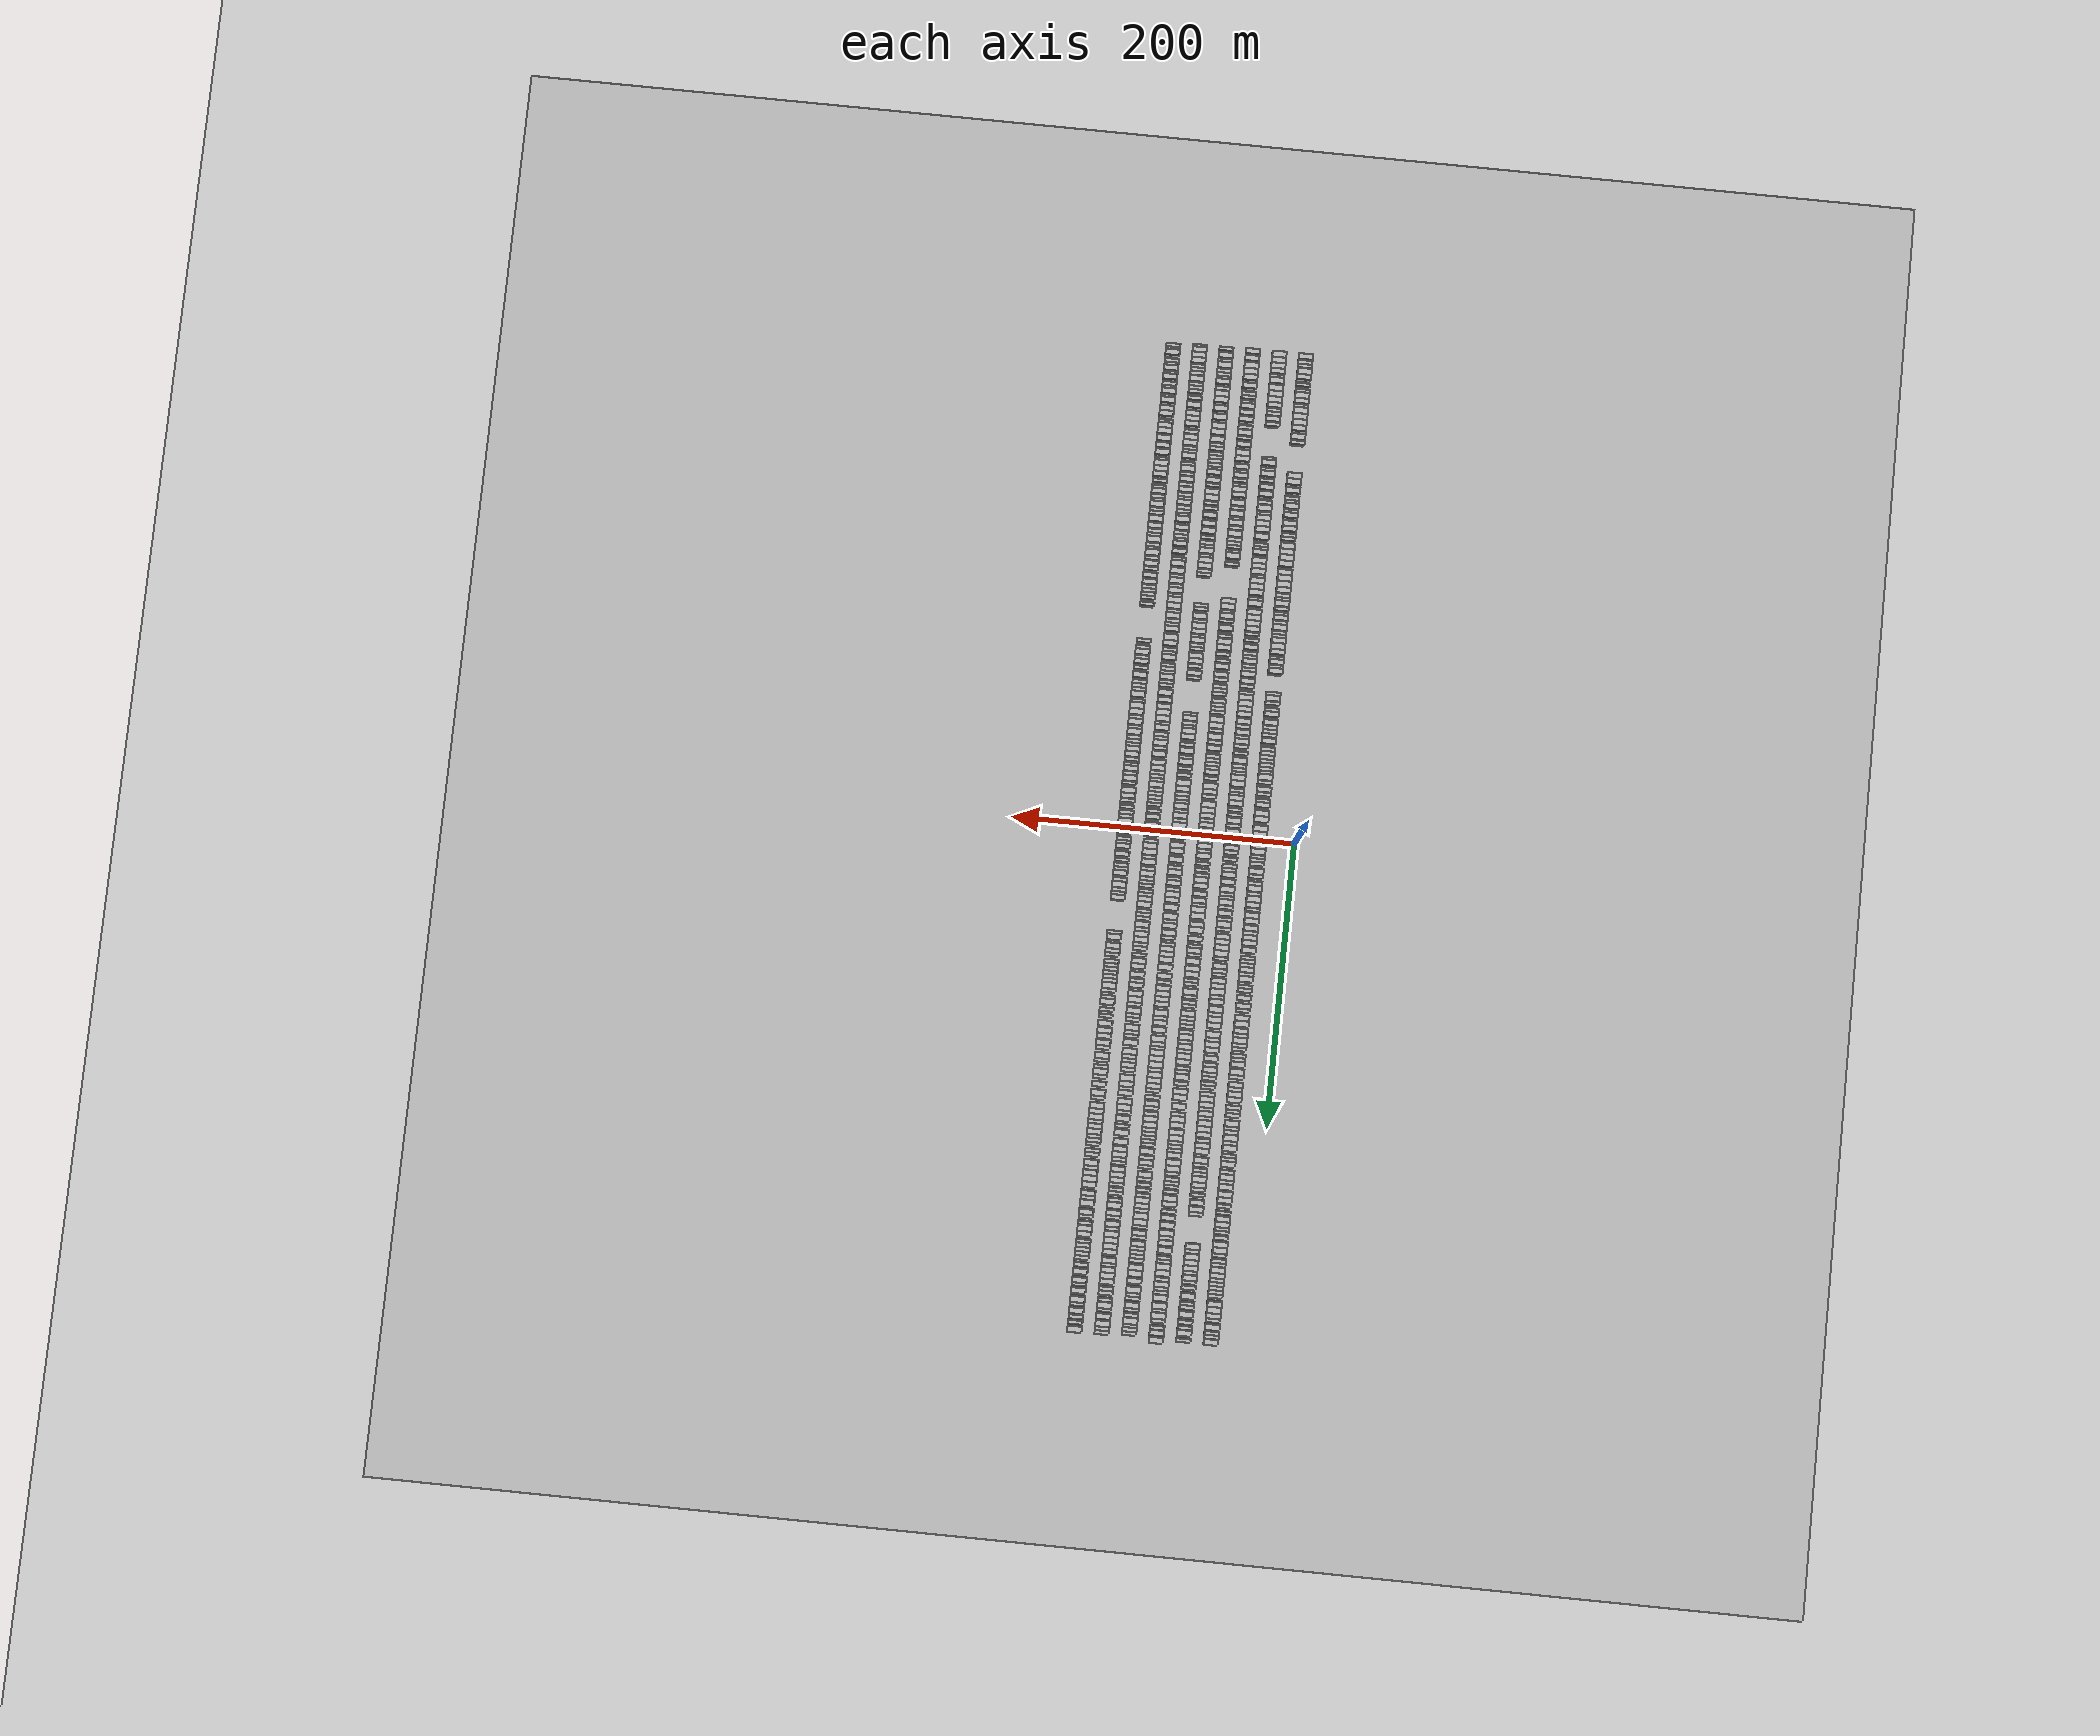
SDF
<?xml version="1.0" encoding="utf-8"?>

<sdf version="1.6">

   <world name="default">

      <gui fullscreen="0">

         <camera name="user_camera">

            <pose>-15 0 4.57585 0 0 0</pose>

            <view_controller>orbit</view_controller>

         </camera>

      </gui>

      <scene>

         <sky>

           <clouds>

             <speed>12</speed>

           </clouds>

         </sky>

         <ambient>0.4 0.4 0.4 1</ambient>

         <background>0.7 0.7 0.7 1</background>

         <shadows>1</shadows>

      </scene>

      <gravity>0 0 -9.8066</gravity>

      <magnetic_field>6e-06 2.3e-05 -4.2e-05</magnetic_field>

      <physics default="0" name="default_physics" type="ode">

         <ode>

            <solver>

               <type>quick</type>

               <iters>10</iters>

               <sor>1.0</sor>

               <use_dynamic_moi_rescaling>0</use_dynamic_moi_rescaling>

            </solver>

            <constraints>

               <cfm>0</cfm>

               <erp>0.2</erp>

               <contact_max_correcting_vel>100</contact_max_correcting_vel>

               <contact_surface_layer>0.001</contact_surface_layer>

            </constraints>

         </ode>

         <max_step_size>0.004</max_step_size>

         <real_time_factor>1</real_time_factor>

         <real_time_update_rate>250</real_time_update_rate>

      </physics>

      <light name="sun" type="directional">

         <cast_shadows>1</cast_shadows>

         <pose>0 0 10 0 0 0</pose>

         <diffuse>0.8 0.8 0.8 1</diffuse>

         <specular>0.2 0.2 0.2 1</specular>

         <attenuation>

            <range>1000</range>

            <constant>0.9</constant>

            <linear>0.01</linear>

            <quadratic>0.001</quadratic>

         </attenuation>

         <direction>-0.5 0.1 -0.9</direction>

      </light>

      <include>

         <name>ground_plane_1</name>

         <uri>model://HANNAS_ground_plane</uri>

         <pose>0 0 0  0 0 0</pose>

      </include>

      <include>

         <name>ground_plane_2</name>

         <uri>model://HANNAS_ground_plane</uri>

         <pose>100 0 0  0 0 0</pose>

      </include>

      <model name="building_1">

         <static>1</static>

         <pose frame="">25.0000 -347.9719 0 0.000000 0.000000 0.000000</pose>

         <link name="link">

            <pose frame="">0 0 4.50 0 0 0</pose>

            <collision name="collision">

               <geometry>

                  <box>

                     <size>10.0000 4.0563 9.0000</size>

                  </box>

               </geometry>

               <max_contacts>10</max_contacts>

               <surface>

                  <contact>

                     <ode/>

                  </contact>

                  <bounce/>

                  <friction>

                     <torsional>

                        <ode/>

                     </torsional>

                     <ode/>

                  </friction>

               </surface>

            </collision>

            <visual name="visual">

               <cast_shadows>0</cast_shadows>

               <geometry>

                  <box>

                     <size>10.0000 4.0563 9.0000</size>

                  </box>

               </geometry>

               <material>

                  <script>

                     <uri>model://HANNAS_wall/materials/scripts</uri>

                     <uri>model://HANNAS_wall/materials/textures</uri>

                     <name>vrc/HANNAS_wall</name>

                  </script>

               </material>

            </visual>

            <self_collide>0</self_collide>

            <enable_wind>0</enable_wind>

            <kinematic>0</kinematic>

         </link>

      </model>

      <model name="building_2">

         <static>1</static>

         <pose frame="">25.0000 -344.5321 0 0.000000 0.000000 0.000000</pose>

         <link name="link">

            <pose frame="">0 0 3.00 0 0 0</pose>

            <collision name="collision">

               <geometry>

                  <box>

                     <size>10.0000 2.8232 6.0000</size>

                  </box>

               </geometry>

               <max_contacts>10</max_contacts>

               <surface>

                  <contact>

                     <ode/>

                  </contact>

                  <bounce/>

                  <friction>

                     <torsional>

                        <ode/>

                     </torsional>

                     <ode/>

                  </friction>

               </surface>

            </collision>

            <visual name="visual">

               <cast_shadows>0</cast_shadows>

               <geometry>

                  <box>

                     <size>10.0000 2.8232 6.0000</size>

                  </box>

               </geometry>

               <material>

                  <script>

                     <uri>model://HANNAS_wall/materials/scripts</uri>

                     <uri>model://HANNAS_wall/materials/textures</uri>

                     <name>vrc/HANNAS_wall</name>

                  </script>

               </material>

            </visual>

            <self_collide>0</self_collide>

            <enable_wind>0</enable_wind>

            <kinematic>0</kinematic>

         </link>

      </model>

      <model name="building_3">

         <static>1</static>

         <pose frame="">25.0000 -341.8003 0 0.000000 0.000000 0.000000</pose>

         <link name="link">

            <pose frame="">0 0 3.00 0 0 0</pose>

            <collision name="collision">

               <geometry>

                  <box>

                     <size>10.0000 2.6404 6.0000</size>

                  </box>

               </geometry>

               <max_contacts>10</max_contacts>

               <surface>

                  <contact>

                     <ode/>

                  </contact>

                  <bounce/>

                  <friction>

                     <torsional>

                        <ode/>

                     </torsional>

                     <ode/>

                  </friction>

               </surface>

            </collision>

            <visual name="visual">

               <cast_shadows>0</cast_shadows>

               <geometry>

                  <box>

                     <size>10.0000 2.6404 6.0000</size>

                  </box>

               </geometry>

               <material>

                  <script>

                     <uri>model://HANNAS_wall/materials/scripts</uri>

                     <uri>model://HANNAS_wall/materials/textures</uri>

                     <name>vrc/HANNAS_wall</name>

                  </script>

               </material>

            </visual>

            <self_collide>0</self_collide>

            <enable_wind>0</enable_wind>

            <kinematic>0</kinematic>

         </link>

      </model>

      <model name="building_4">

         <static>1</static>

         <pose frame="">25.0000 -337.2499 0 0.000000 0.000000 0.000000</pose>

         <link name="link">

            <pose frame="">0 0 4.50 0 0 0</pose>

            <collision name="collision">

               <geometry>

                  <box>

                     <size>10.0000 4.4603 9.0000</size>

                  </box>

               </geometry>

               <max_contacts>10</max_contacts>

               <surface>

                  <contact>

                     <ode/>

                  </contact>

                  <bounce/>

                  <friction>

                     <torsional>

                        <ode/>

                     </torsional>

                     <ode/>

                  </friction>

               </surface>

            </collision>

            <visual name="visual">

               <cast_shadows>0</cast_shadows>

               <geometry>

                  <box>

                     <size>10.0000 4.4603 9.0000</size>

                  </box>

               </geometry>

               <material>

                  <script>

                     <uri>model://HANNAS_wall/materials/scripts</uri>

                     <uri>model://HANNAS_wall/materials/textures</uri>

                     <name>vrc/HANNAS_wall</name>

                  </script>

               </material>

            </visual>

            <self_collide>0</self_collide>

            <enable_wind>0</enable_wind>

            <kinematic>0</kinematic>

         </link>

      </model>

      <model name="building_5">

         <static>1</static>

         <pose frame="">25.0000 -333.1671 0 0.000000 0.000000 0.000000</pose>

         <link name="link">

            <pose frame="">0 0 4.50 0 0 0</pose>

            <collision name="collision">

               <geometry>

                  <box>

                     <size>10.0000 3.7053 9.0000</size>

                  </box>

               </geometry>

               <max_contacts>10</max_contacts>

               <surface>

                  <contact>

                     <ode/>

                  </contact>

                  <bounce/>

                  <friction>

                     <torsional>

                        <ode/>

                     </torsional>

                     <ode/>

                  </friction>

               </surface>

            </collision>

            <visual name="visual">

               <cast_shadows>0</cast_shadows>

               <geometry>

                  <box>

                     <size>10.0000 3.7053 9.0000</size>

                  </box>

               </geometry>

               <material>

                  <script>

                     <uri>model://HANNAS_wall/materials/scripts</uri>

                     <uri>model://HANNAS_wall/materials/textures</uri>

                     <name>vrc/HANNAS_wall</name>

                  </script>

               </material>

            </visual>

            <self_collide>0</self_collide>

            <enable_wind>0</enable_wind>

            <kinematic>0</kinematic>

         </link>

      </model>

      <model name="building_6">

         <static>1</static>

         <pose frame="">25.0000 -328.1081 0 0.000000 0.000000 0.000000</pose>

         <link name="link">

            <pose frame="">0 0 3.00 0 0 0</pose>

            <collision name="collision">

               <geometry>

                  <box>

                     <size>10.0000 2.4127 6.0000</size>

                  </box>

               </geometry>

               <max_contacts>10</max_contacts>

               <surface>

                  <contact>

                     <ode/>

                  </contact>

                  <bounce/>

                  <friction>

                     <torsional>

                        <ode/>

                     </torsional>

                     <ode/>

                  </friction>

               </surface>

            </collision>

            <visual name="visual">

               <cast_shadows>0</cast_shadows>

               <geometry>

                  <box>

                     <size>10.0000 2.4127 6.0000</size>

                  </box>

               </geometry>

               <material>

                  <script>

                     <uri>model://HANNAS_wall/materials/scripts</uri>

                     <uri>model://HANNAS_wall/materials/textures</uri>

                     <name>vrc/HANNAS_wall</name>

                  </script>

               </material>

            </visual>

            <self_collide>0</self_collide>

            <enable_wind>0</enable_wind>

            <kinematic>0</kinematic>

         </link>

      </model>

      <model name="building_7">

         <static>1</static>

         <pose frame="">25.0000 -323.4152 0 0.000000 0.000000 0.000000</pose>

         <link name="link">

            <pose frame="">0 0 3.00 0 0 0</pose>

            <collision name="collision">

               <geometry>

                  <box>

                     <size>10.0000 2.9729 6.0000</size>

                  </box>

               </geometry>

               <max_contacts>10</max_contacts>

               <surface>

                  <contact>

                     <ode/>

                  </contact>

                  <bounce/>

                  <friction>

                     <torsional>

                        <ode/>

                     </torsional>

                     <ode/>

                  </friction>

               </surface>

            </collision>

            <visual name="visual">

               <cast_shadows>0</cast_shadows>

               <geometry>

                  <box>

                     <size>10.0000 2.9729 6.0000</size>

                  </box>

               </geometry>

               <material>

                  <script>

                     <uri>model://HANNAS_wall/materials/scripts</uri>

                     <uri>model://HANNAS_wall/materials/textures</uri>

                     <name>vrc/HANNAS_wall</name>

                  </script>

               </material>

            </visual>

            <self_collide>0</self_collide>

            <enable_wind>0</enable_wind>

            <kinematic>0</kinematic>

         </link>

      </model>

      <model name="building_8">

         <static>1</static>

         <pose frame="">25.0000 -319.7650 0 0.000000 0.000000 0.000000</pose>

         <link name="link">

            <pose frame="">0 0 4.50 0 0 0</pose>

            <collision name="collision">

               <geometry>

                  <box>

                     <size>10.0000 4.3275 9.0000</size>

                  </box>

               </geometry>

               <max_contacts>10</max_contacts>

               <surface>

                  <contact>

                     <ode/>

                  </contact>

                  <bounce/>

                  <friction>

                     <torsional>

                        <ode/>

                     </torsional>

                     <ode/>

                  </friction>

               </surface>

            </collision>

            <visual name="visual">

               <cast_shadows>0</cast_shadows>

               <geometry>

                  <box>

                     <size>10.0000 4.3275 9.0000</size>

                  </box>

               </geometry>

               <material>

                  <script>

                     <uri>model://HANNAS_wall/materials/scripts</uri>

                     <uri>model://HANNAS_wall/materials/textures</uri>

                     <name>vrc/HANNAS_wall</name>

                  </script>

               </material>

            </visual>

            <self_collide>0</self_collide>

            <enable_wind>0</enable_wind>

            <kinematic>0</kinematic>

         </link>

      </model>

      <model name="building_9">

         <static>1</static>

         <pose frame="">25.0000 -315.7878 0 0.000000 0.000000 0.000000</pose>

         <link name="link">

            <pose frame="">0 0 4.50 0 0 0</pose>

            <collision name="collision">

               <geometry>

                  <box>

                     <size>10.0000 3.6268 9.0000</size>

                  </box>

               </geometry>

               <max_contacts>10</max_contacts>

               <surface>

                  <contact>

                     <ode/>

                  </contact>

                  <bounce/>

                  <friction>

                     <torsional>

                        <ode/>

                     </torsional>

                     <ode/>

                  </friction>

               </surface>

            </collision>

            <visual name="visual">

               <cast_shadows>0</cast_shadows>

               <geometry>

                  <box>

                     <size>10.0000 3.6268 9.0000</size>

                  </box>

               </geometry>

               <material>

                  <script>

                     <uri>model://HANNAS_wall/materials/scripts</uri>

                     <uri>model://HANNAS_wall/materials/textures</uri>

                     <name>vrc/HANNAS_wall</name>

                  </script>

               </material>

            </visual>

            <self_collide>0</self_collide>

            <enable_wind>0</enable_wind>

            <kinematic>0</kinematic>

         </link>

      </model>

      <model name="building_10">

         <static>1</static>

         <pose frame="">25.0000 -312.5490 0 0.000000 0.000000 0.000000</pose>

         <link name="link">

            <pose frame="">0 0 3.00 0 0 0</pose>

            <collision name="collision">

               <geometry>

                  <box>

                     <size>10.0000 2.8508 6.0000</size>

                  </box>

               </geometry>

               <max_contacts>10</max_contacts>

               <surface>

                  <contact>

                     <ode/>

                  </contact>

                  <bounce/>

                  <friction>

                     <torsional>

                        <ode/>

                     </torsional>

                     <ode/>

                  </friction>

               </surface>

            </collision>

            <visual name="visual">

               <cast_shadows>0</cast_shadows>

               <geometry>

                  <box>

                     <size>10.0000 2.8508 6.0000</size>

                  </box>

               </geometry>

               <material>

                  <script>

                     <uri>model://HANNAS_wall/materials/scripts</uri>

                     <uri>model://HANNAS_wall/materials/textures</uri>

                     <name>vrc/HANNAS_wall</name>

                  </script>

               </material>

            </visual>

            <self_collide>0</self_collide>

            <enable_wind>0</enable_wind>

            <kinematic>0</kinematic>

         </link>

      </model>

      <model name="building_11">

         <static>1</static>

         <pose frame="">25.0000 -308.8738 0 0.000000 0.000000 0.000000</pose>

         <link name="link">

            <pose frame="">0 0 4.50 0 0 0</pose>

            <collision name="collision">

               <geometry>

                  <box>

                     <size>10.0000 4.4997 9.0000</size>

                  </box>

               </geometry>

               <max_contacts>10</max_contacts>

               <surface>

                  <contact>

                     <ode/>

                  </contact>

                  <bounce/>

                  <friction>

                     <torsional>

                        <ode/>

                     </torsional>

                     <ode/>

                  </friction>

               </surface>

            </collision>

            <visual name="visual">

               <cast_shadows>0</cast_shadows>

               <geometry>

                  <box>

                     <size>10.0000 4.4997 9.0000</size>

                  </box>

               </geometry>

               <material>

                  <script>

                     <uri>model://HANNAS_wall/materials/scripts</uri>

                     <uri>model://HANNAS_wall/materials/textures</uri>

                     <name>vrc/HANNAS_wall</name>

                  </script>

               </material>

            </visual>

            <self_collide>0</self_collide>

            <enable_wind>0</enable_wind>

            <kinematic>0</kinematic>

         </link>

      </model>

      <model name="building_12">

         <static>1</static>

         <pose frame="">25.0000 -304.5123 0 0.000000 0.000000 0.000000</pose>

         <link name="link">

            <pose frame="">0 0 4.50 0 0 0</pose>

            <collision name="collision">

               <geometry>

                  <box>

                     <size>10.0000 4.2233 9.0000</size>

                  </box>

               </geometry>

               <max_contacts>10</max_contacts>

               <surface>

                  <contact>

                     <ode/>

                  </contact>

                  <bounce/>

                  <friction>

                     <torsional>

                        <ode/>

                     </torsional>

                     <ode/>

                  </friction>

               </surface>

            </collision>

            <visual name="visual">

               <cast_shadows>0</cast_shadows>

               <geometry>

                  <box>

                     <size>10.0000 4.2233 9.0000</size>

                  </box>

               </geometry>

               <material>

                  <script>

                     <uri>model://HANNAS_wall/materials/scripts</uri>

                     <uri>model://HANNAS_wall/materials/textures</uri>

                     <name>vrc/HANNAS_wall</name>

                  </script>

               </material>

            </visual>

            <self_collide>0</self_collide>

            <enable_wind>0</enable_wind>

            <kinematic>0</kinematic>

         </link>

      </model>

      <model name="building_13">

         <static>1</static>

         <pose frame="">25.0000 -300.2436 0 0.000000 0.000000 0.000000</pose>

         <link name="link">

            <pose frame="">0 0 4.50 0 0 0</pose>

            <collision name="collision">

               <geometry>

                  <box>

                     <size>10.0000 4.3142 9.0000</size>

                  </box>

               </geometry>

               <max_contacts>10</max_contacts>

               <surface>

                  <contact>

                     <ode/>

                  </contact>

                  <bounce/>

                  <friction>

                     <torsional>

                        <ode/>

                     </torsional>

                     <ode/>

                  </friction>

               </surface>

            </collision>

            <visual name="visual">

               <cast_shadows>0</cast_shadows>

               <geometry>

                  <box>

                     <size>10.0000 4.3142 9.0000</size>

                  </box>

               </geometry>

               <material>

                  <script>

                     <uri>model://HANNAS_wall/materials/scripts</uri>

                     <uri>model://HANNAS_wall/materials/textures</uri>

                     <name>vrc/HANNAS_wall</name>

                  </script>

               </material>

            </visual>

            <self_collide>0</self_collide>

            <enable_wind>0</enable_wind>

            <kinematic>0</kinematic>

         </link>

      </model>

      <model name="building_14">

         <static>1</static>

         <pose frame="">25.0000 -296.0442 0 0.000000 0.000000 0.000000</pose>

         <link name="link">

            <pose frame="">0 0 4.50 0 0 0</pose>

            <collision name="collision">

               <geometry>

                  <box>

                     <size>10.0000 4.0846 9.0000</size>

                  </box>

               </geometry>

               <max_contacts>10</max_contacts>

               <surface>

                  <contact>

                     <ode/>

                  </contact>

                  <bounce/>

                  <friction>

                     <torsional>

                        <ode/>

                     </torsional>

                     <ode/>

                  </friction>

               </surface>

            </collision>

            <visual name="visual">

               <cast_shadows>0</cast_shadows>

               <geometry>

                  <box>

                     <size>10.0000 4.0846 9.0000</size>

                  </box>

               </geometry>

               <material>

                  <script>

                     <uri>model://HANNAS_wall/materials/scripts</uri>

                     <uri>model://HANNAS_wall/materials/textures</uri>

                     <name>vrc/HANNAS_wall</name>

                  </script>

               </material>

            </visual>

            <self_collide>0</self_collide>

            <enable_wind>0</enable_wind>

            <kinematic>0</kinematic>

         </link>

      </model>

      <model name="building_15">

         <static>1</static>

         <pose frame="">25.0000 -289.8021 0 0.000000 0.000000 0.000000</pose>

         <link name="link">

            <pose frame="">0 0 4.50 0 0 0</pose>

            <collision name="collision">

               <geometry>

                  <box>

                     <size>10.0000 4.3996 9.0000</size>

                  </box>

               </geometry>

               <max_contacts>10</max_contacts>

               <surface>

                  <contact>

                     <ode/>

                  </contact>

                  <bounce/>

                  <friction>

                     <torsional>

                        <ode/>

                     </torsional>

                     <ode/>

                  </friction>

               </surface>

            </collision>

            <visual name="visual">

               <cast_shadows>0</cast_shadows>

               <geometry>

                  <box>

                     <size>10.0000 4.3996 9.0000</size>

                  </box>

               </geometry>

               <material>

                  <script>

                     <uri>model://HANNAS_wall/materials/scripts</uri>

                     <uri>model://HANNAS_wall/materials/textures</uri>

                     <name>vrc/HANNAS_wall</name>

                  </script>

               </material>

            </visual>

            <self_collide>0</self_collide>

            <enable_wind>0</enable_wind>

            <kinematic>0</kinematic>

         </link>

      </model>

      <model name="building_16">

         <static>1</static>

         <pose frame="">25.0000 -286.2306 0 0.000000 0.000000 0.000000</pose>

         <link name="link">

            <pose frame="">0 0 3.00 0 0 0</pose>

            <collision name="collision">

               <geometry>

                  <box>

                     <size>10.0000 2.7434 6.0000</size>

                  </box>

               </geometry>

               <max_contacts>10</max_contacts>

               <surface>

                  <contact>

                     <ode/>

                  </contact>

                  <bounce/>

                  <friction>

                     <torsional>

                        <ode/>

                     </torsional>

                     <ode/>

                  </friction>

               </surface>

            </collision>

            <visual name="visual">

               <cast_shadows>0</cast_shadows>

               <geometry>

                  <box>

                     <size>10.0000 2.7434 6.0000</size>

                  </box>

               </geometry>

               <material>

                  <script>

                     <uri>model://HANNAS_wall/materials/scripts</uri>

                     <uri>model://HANNAS_wall/materials/textures</uri>

                     <name>vrc/HANNAS_wall</name>

                  </script>

               </material>

            </visual>

            <self_collide>0</self_collide>

            <enable_wind>0</enable_wind>

            <kinematic>0</kinematic>

         </link>

      </model>

      <model name="building_17">

         <static>1</static>

         <pose frame="">25.0000 -261.4636 0 0.000000 0.000000 0.000000</pose>

         <link name="link">

            <pose frame="">0 0 4.50 0 0 0</pose>

            <collision name="collision">

               <geometry>

                  <box>

                     <size>10.0000 4.2635 9.0000</size>

                  </box>

               </geometry>

               <max_contacts>10</max_contacts>

               <surface>

                  <contact>

                     <ode/>

                  </contact>

                  <bounce/>

                  <friction>

                     <torsional>

                        <ode/>

                     </torsional>

                     <ode/>

                  </friction>

               </surface>

            </collision>

            <visual name="visual">

               <cast_shadows>0</cast_shadows>

               <geometry>

                  <box>

                     <size>10.0000 4.2635 9.0000</size>

                  </box>

               </geometry>

               <material>

                  <script>

                     <uri>model://HANNAS_wall/materials/scripts</uri>

                     <uri>model://HANNAS_wall/materials/textures</uri>

                     <name>vrc/HANNAS_wall</name>

                  </script>

               </material>

            </visual>

            <self_collide>0</self_collide>

            <enable_wind>0</enable_wind>

            <kinematic>0</kinematic>

         </link>

      </model>

      <model name="building_18">

         <static>1</static>

         <pose frame="">25.0000 -257.1325 0 0.000000 0.000000 0.000000</pose>

         <link name="link">

            <pose frame="">0 0 4.50 0 0 0</pose>

            <collision name="collision">

               <geometry>

                  <box>

                     <size>10.0000 4.3989 9.0000</size>

                  </box>

               </geometry>

               <max_contacts>10</max_contacts>

               <surface>

                  <contact>

                     <ode/>

                  </contact>

                  <bounce/>

                  <friction>

                     <torsional>

                        <ode/>

                     </torsional>

                     <ode/>

                  </friction>

               </surface>

            </collision>

            <visual name="visual">

               <cast_shadows>0</cast_shadows>

               <geometry>

                  <box>

                     <size>10.0000 4.3989 9.0000</size>

                  </box>

               </geometry>

               <material>

                  <script>

                     <uri>model://HANNAS_wall/materials/scripts</uri>

                     <uri>model://HANNAS_wall/materials/textures</uri>

                     <name>vrc/HANNAS_wall</name>

                  </script>

               </material>

            </visual>

            <self_collide>0</self_collide>

            <enable_wind>0</enable_wind>

            <kinematic>0</kinematic>

         </link>

      </model>

      <model name="building_19">

         <static>1</static>

         <pose frame="">25.0000 -250.9067 0 0.000000 0.000000 0.000000</pose>

         <link name="link">

            <pose frame="">0 0 4.50 0 0 0</pose>

            <collision name="collision">

               <geometry>

                  <box>

                     <size>10.0000 4.0527 9.0000</size>

                  </box>

               </geometry>

               <max_contacts>10</max_contacts>

               <surface>

                  <contact>

                     <ode/>

                  </contact>

                  <bounce/>

                  <friction>

                     <torsional>

                        <ode/>

                     </torsional>

                     <ode/>

                  </friction>

               </surface>

            </collision>

            <visual name="visual">

               <cast_shadows>0</cast_shadows>

               <geometry>

                  <box>

                     <size>10.0000 4.0527 9.0000</size>

                  </box>

               </geometry>

               <material>

                  <script>

                     <uri>model://HANNAS_wall/materials/scripts</uri>

                     <uri>model://HANNAS_wall/materials/textures</uri>

                     <name>vrc/HANNAS_wall</name>

                  </script>

               </material>

            </visual>

            <self_collide>0</self_collide>

            <enable_wind>0</enable_wind>

            <kinematic>0</kinematic>

         </link>

      </model>

      <model name="building_20">

         <static>1</static>

         <pose frame="">25.0000 -245.6302 0 0.000000 0.000000 0.000000</pose>

         <link name="link">

            <pose frame="">0 0 3.00 0 0 0</pose>

            <collision name="collision">

               <geometry>

                  <box>

                     <size>10.0000 2.5002 6.0000</size>

                  </box>

               </geometry>

               <max_contacts>10</max_contacts>

               <surface>

                  <contact>

                     <ode/>

                  </contact>

                  <bounce/>

                  <friction>

                     <torsional>

                        <ode/>

                     </torsional>

                     <ode/>

                  </friction>

               </surface>

            </collision>

            <visual name="visual">

               <cast_shadows>0</cast_shadows>

               <geometry>

                  <box>

                     <size>10.0000 2.5002 6.0000</size>

                  </box>

               </geometry>

               <material>

                  <script>

                     <uri>model://HANNAS_wall/materials/scripts</uri>

                     <uri>model://HANNAS_wall/materials/textures</uri>

                     <name>vrc/HANNAS_wall</name>

                  </script>

               </material>

            </visual>

            <self_collide>0</self_collide>

            <enable_wind>0</enable_wind>

            <kinematic>0</kinematic>

         </link>

      </model>

      <model name="building_21">

         <static>1</static>

         <pose frame="">25.0000 -243.0305 0 0.000000 0.000000 0.000000</pose>

         <link name="link">

            <pose frame="">0 0 3.00 0 0 0</pose>

            <collision name="collision">

               <geometry>

                  <box>

                     <size>10.0000 2.6993 6.0000</size>

                  </box>

               </geometry>

               <max_contacts>10</max_contacts>

               <surface>

                  <contact>

                     <ode/>

                  </contact>

                  <bounce/>

                  <friction>

                     <torsional>

                        <ode/>

                     </torsional>

                     <ode/>

                  </friction>

               </surface>

            </collision>

            <visual name="visual">

               <cast_shadows>0</cast_shadows>

               <geometry>

                  <box>

                     <size>10.0000 2.6993 6.0000</size>

                  </box>

               </geometry>

               <material>

                  <script>

                     <uri>model://HANNAS_wall/materials/scripts</uri>

                     <uri>model://HANNAS_wall/materials/textures</uri>

                     <name>vrc/HANNAS_wall</name>

                  </script>

               </material>

            </visual>

            <self_collide>0</self_collide>

            <enable_wind>0</enable_wind>

            <kinematic>0</kinematic>

         </link>

      </model>

      <model name="building_22">

         <static>1</static>

         <pose frame="">25.0000 -239.6084 0 0.000000 0.000000 0.000000</pose>

         <link name="link">

            <pose frame="">0 0 4.50 0 0 0</pose>

            <collision name="collision">

               <geometry>

                  <box>

                     <size>10.0000 4.1448 9.0000</size>

                  </box>

               </geometry>

               <max_contacts>10</max_contacts>

               <surface>

                  <contact>

                     <ode/>

                  </contact>

                  <bounce/>

                  <friction>

                     <torsional>

                        <ode/>

                     </torsional>

                     <ode/>

                  </friction>

               </surface>

            </collision>

            <visual name="visual">

               <cast_shadows>0</cast_shadows>

               <geometry>

                  <box>

                     <size>10.0000 4.1448 9.0000</size>

                  </box>

               </geometry>

               <material>

                  <script>

                     <uri>model://HANNAS_wall/materials/scripts</uri>

                     <uri>model://HANNAS_wall/materials/textures</uri>

                     <name>vrc/HANNAS_wall</name>

                  </script>

               </material>

            </visual>

            <self_collide>0</self_collide>

            <enable_wind>0</enable_wind>

            <kinematic>0</kinematic>

         </link>

      </model>

      <model name="building_23">

         <static>1</static>

         <pose frame="">25.0000 -236.2136 0 0.000000 0.000000 0.000000</pose>

         <link name="link">

            <pose frame="">0 0 3.00 0 0 0</pose>

            <collision name="collision">

               <geometry>

                  <box>

                     <size>10.0000 2.6449 6.0000</size>

                  </box>

               </geometry>

               <max_contacts>10</max_contacts>

               <surface>

                  <contact>

                     <ode/>

                  </contact>

                  <bounce/>

                  <friction>

                     <torsional>

                        <ode/>

                     </torsional>

                     <ode/>

                  </friction>

               </surface>

            </collision>

            <visual name="visual">

               <cast_shadows>0</cast_shadows>

               <geometry>

                  <box>

                     <size>10.0000 2.6449 6.0000</size>

                  </box>

               </geometry>

               <material>

                  <script>

                     <uri>model://HANNAS_wall/materials/scripts</uri>

                     <uri>model://HANNAS_wall/materials/textures</uri>

                     <name>vrc/HANNAS_wall</name>

                  </script>

               </material>

            </visual>

            <self_collide>0</self_collide>

            <enable_wind>0</enable_wind>

            <kinematic>0</kinematic>

         </link>

      </model>

      <model name="building_24">

         <static>1</static>

         <pose frame="">25.0000 -232.9603 0 0.000000 0.000000 0.000000</pose>

         <link name="link">

            <pose frame="">0 0 4.50 0 0 0</pose>

            <collision name="collision">

               <geometry>

                  <box>

                     <size>10.0000 3.8616 9.0000</size>

                  </box>

               </geometry>

               <max_contacts>10</max_contacts>

               <surface>

                  <contact>

                     <ode/>

                  </contact>

                  <bounce/>

                  <friction>

                     <torsional>

                        <ode/>

                     </torsional>

                     <ode/>

                  </friction>

               </surface>

            </collision>

            <visual name="visual">

               <cast_shadows>0</cast_shadows>

               <geometry>

                  <box>

                     <size>10.0000 3.8616 9.0000</size>

                  </box>

               </geometry>

               <material>

                  <script>

                     <uri>model://HANNAS_wall/materials/scripts</uri>

                     <uri>model://HANNAS_wall/materials/textures</uri>

                     <name>vrc/HANNAS_wall</name>

                  </script>

               </material>

            </visual>

            <self_collide>0</self_collide>

            <enable_wind>0</enable_wind>

            <kinematic>0</kinematic>

         </link>

      </model>

      <model name="building_25">

         <static>1</static>

         <pose frame="">25.0000 -227.0882 0 0.000000 0.000000 0.000000</pose>

         <link name="link">

            <pose frame="">0 0 4.50 0 0 0</pose>

            <collision name="collision">

               <geometry>

                  <box>

                     <size>10.0000 3.8826 9.0000</size>

                  </box>

               </geometry>

               <max_contacts>10</max_contacts>

               <surface>

                  <contact>

                     <ode/>

                  </contact>

                  <bounce/>

                  <friction>

                     <torsional>

                        <ode/>

                     </torsional>

                     <ode/>

                  </friction>

               </surface>

            </collision>

            <visual name="visual">

               <cast_shadows>0</cast_shadows>

               <geometry>

                  <box>

                     <size>10.0000 3.8826 9.0000</size>

                  </box>

               </geometry>

               <material>

                  <script>

                     <uri>model://HANNAS_wall/materials/scripts</uri>

                     <uri>model://HANNAS_wall/materials/textures</uri>

                     <name>vrc/HANNAS_wall</name>

                  </script>

               </material>

            </visual>

            <self_collide>0</self_collide>

            <enable_wind>0</enable_wind>

            <kinematic>0</kinematic>

         </link>

      </model>

      <model name="building_26">

         <static>1</static>

         <pose frame="">25.0000 -223.2871 0 0.000000 0.000000 0.000000</pose>

         <link name="link">

            <pose frame="">0 0 4.50 0 0 0</pose>

            <collision name="collision">

               <geometry>

                  <box>

                     <size>10.0000 3.7195 9.0000</size>

                  </box>

               </geometry>

               <max_contacts>10</max_contacts>

               <surface>

                  <contact>

                     <ode/>

                  </contact>

                  <bounce/>

                  <friction>

                     <torsional>

                        <ode/>

                     </torsional>

                     <ode/>

                  </friction>

               </surface>

            </collision>

            <visual name="visual">

               <cast_shadows>0</cast_shadows>

               <geometry>

                  <box>

                     <size>10.0000 3.7195 9.0000</size>

                  </box>

               </geometry>

               <material>

                  <script>

                     <uri>model://HANNAS_wall/materials/scripts</uri>

                     <uri>model://HANNAS_wall/materials/textures</uri>

                     <name>vrc/HANNAS_wall</name>

                  </script>

               </material>

            </visual>

            <self_collide>0</self_collide>

            <enable_wind>0</enable_wind>

            <kinematic>0</kinematic>

         </link>

      </model>

      <model name="building_27">

         <static>1</static>

         <pose frame="">25.0000 -219.0824 0 0.000000 0.000000 0.000000</pose>

         <link name="link">

            <pose frame="">0 0 3.00 0 0 0</pose>

            <collision name="collision">

               <geometry>

                  <box>

                     <size>10.0000 2.6899 6.0000</size>

                  </box>

               </geometry>

               <max_contacts>10</max_contacts>

               <surface>

                  <contact>

                     <ode/>

                  </contact>

                  <bounce/>

                  <friction>

                     <torsional>

                        <ode/>

                     </torsional>

                     <ode/>

                  </friction>

               </surface>

            </collision>

            <visual name="visual">

               <cast_shadows>0</cast_shadows>

               <geometry>

                  <box>

                     <size>10.0000 2.6899 6.0000</size>

                  </box>

               </geometry>

               <material>

                  <script>

                     <uri>model://HANNAS_wall/materials/scripts</uri>

                     <uri>model://HANNAS_wall/materials/textures</uri>

                     <name>vrc/HANNAS_wall</name>

                  </script>

               </material>

            </visual>

            <self_collide>0</self_collide>

            <enable_wind>0</enable_wind>

            <kinematic>0</kinematic>

         </link>

      </model>

      <model name="building_28">

         <static>1</static>

         <pose frame="">25.0000 -216.3721 0 0.000000 0.000000 0.000000</pose>

         <link name="link">

            <pose frame="">0 0 3.00 0 0 0</pose>

            <collision name="collision">

               <geometry>

                  <box>

                     <size>10.0000 2.7306 6.0000</size>

                  </box>

               </geometry>

               <max_contacts>10</max_contacts>

               <surface>

                  <contact>

                     <ode/>

                  </contact>

                  <bounce/>

                  <friction>

                     <torsional>

                        <ode/>

                     </torsional>

                     <ode/>

                  </friction>

               </surface>

            </collision>

            <visual name="visual">

               <cast_shadows>0</cast_shadows>

               <geometry>

                  <box>

                     <size>10.0000 2.7306 6.0000</size>

                  </box>

               </geometry>

               <material>

                  <script>

                     <uri>model://HANNAS_wall/materials/scripts</uri>

                     <uri>model://HANNAS_wall/materials/textures</uri>

                     <name>vrc/HANNAS_wall</name>

                  </script>

               </material>

            </visual>

            <self_collide>0</self_collide>

            <enable_wind>0</enable_wind>

            <kinematic>0</kinematic>

         </link>

      </model>

      <model name="building_29">

         <static>1</static>

         <pose frame="">25.0000 -210.8212 0 0.000000 0.000000 0.000000</pose>

         <link name="link">

            <pose frame="">0 0 4.50 0 0 0</pose>

            <collision name="collision">

               <geometry>

                  <box>

                     <size>10.0000 4.3712 9.0000</size>

                  </box>

               </geometry>

               <max_contacts>10</max_contacts>

               <surface>

                  <contact>

                     <ode/>

                  </contact>

                  <bounce/>

                  <friction>

                     <torsional>

                        <ode/>

                     </torsional>

                     <ode/>

                  </friction>

               </surface>

            </collision>

            <visual name="visual">

               <cast_shadows>0</cast_shadows>

               <geometry>

                  <box>

                     <size>10.0000 4.3712 9.0000</size>

                  </box>

               </geometry>

               <material>

                  <script>

                     <uri>model://HANNAS_wall/materials/scripts</uri>

                     <uri>model://HANNAS_wall/materials/textures</uri>

                     <name>vrc/HANNAS_wall</name>

                  </script>

               </material>

            </visual>

            <self_collide>0</self_collide>

            <enable_wind>0</enable_wind>

            <kinematic>0</kinematic>

         </link>

      </model>

      <model name="building_30">

         <static>1</static>

         <pose frame="">25.0000 -206.6303 0 0.000000 0.000000 0.000000</pose>

         <link name="link">

            <pose frame="">0 0 4.50 0 0 0</pose>

            <collision name="collision">

               <geometry>

                  <box>

                     <size>10.0000 4.0107 9.0000</size>

                  </box>

               </geometry>

               <max_contacts>10</max_contacts>

               <surface>

                  <contact>

                     <ode/>

                  </contact>

                  <bounce/>

                  <friction>

                     <torsional>

                        <ode/>

                     </torsional>

                     <ode/>

                  </friction>

               </surface>

            </collision>

            <visual name="visual">

               <cast_shadows>0</cast_shadows>

               <geometry>

                  <box>

                     <size>10.0000 4.0107 9.0000</size>

                  </box>

               </geometry>

               <material>

                  <script>

                     <uri>model://HANNAS_wall/materials/scripts</uri>

                     <uri>model://HANNAS_wall/materials/textures</uri>

                     <name>vrc/HANNAS_wall</name>

                  </script>

               </material>

            </visual>

            <self_collide>0</self_collide>

            <enable_wind>0</enable_wind>

            <kinematic>0</kinematic>

         </link>

      </model>

      <model name="building_31">

         <static>1</static>

         <pose frame="">25.0000 -202.4135 0 0.000000 0.000000 0.000000</pose>

         <link name="link">

            <pose frame="">0 0 4.50 0 0 0</pose>

            <collision name="collision">

               <geometry>

                  <box>

                     <size>10.0000 4.4229 9.0000</size>

                  </box>

               </geometry>

               <max_contacts>10</max_contacts>

               <surface>

                  <contact>

                     <ode/>

                  </contact>

                  <bounce/>

                  <friction>

                     <torsional>

                        <ode/>

                     </torsional>

                     <ode/>

                  </friction>

               </surface>

            </collision>

            <visual name="visual">

               <cast_shadows>0</cast_shadows>

               <geometry>

                  <box>

                     <size>10.0000 4.4229 9.0000</size>

                  </box>

               </geometry>

               <material>

                  <script>

                     <uri>model://HANNAS_wall/materials/scripts</uri>

                     <uri>model://HANNAS_wall/materials/textures</uri>

                     <name>vrc/HANNAS_wall</name>

                  </script>

               </material>

            </visual>

            <self_collide>0</self_collide>

            <enable_wind>0</enable_wind>

            <kinematic>0</kinematic>

         </link>

      </model>

      <model name="building_32">

         <static>1</static>

         <pose frame="">25.0000 -198.0368 0 0.000000 0.000000 0.000000</pose>

         <link name="link">

            <pose frame="">0 0 4.50 0 0 0</pose>

            <collision name="collision">

               <geometry>

                  <box>

                     <size>10.0000 4.3305 9.0000</size>

                  </box>

               </geometry>

               <max_contacts>10</max_contacts>

               <surface>

                  <contact>

                     <ode/>

                  </contact>

                  <bounce/>

                  <friction>

                     <torsional>

                        <ode/>

                     </torsional>

                     <ode/>

                  </friction>

               </surface>

            </collision>

            <visual name="visual">

               <cast_shadows>0</cast_shadows>

               <geometry>

                  <box>

                     <size>10.0000 4.3305 9.0000</size>

                  </box>

               </geometry>

               <material>

                  <script>

                     <uri>model://HANNAS_wall/materials/scripts</uri>

                     <uri>model://HANNAS_wall/materials/textures</uri>

                     <name>vrc/HANNAS_wall</name>

                  </script>

               </material>

            </visual>

            <self_collide>0</self_collide>

            <enable_wind>0</enable_wind>

            <kinematic>0</kinematic>

         </link>

      </model>

      <model name="building_33">

         <static>1</static>

         <pose frame="">25.0000 -191.9185 0 0.000000 0.000000 0.000000</pose>

         <link name="link">

            <pose frame="">0 0 4.50 0 0 0</pose>

            <collision name="collision">

               <geometry>

                  <box>

                     <size>10.0000 3.9061 9.0000</size>

                  </box>

               </geometry>

               <max_contacts>10</max_contacts>

               <surface>

                  <contact>

                     <ode/>

                  </contact>

                  <bounce/>

                  <friction>

                     <torsional>

                        <ode/>

                     </torsional>

                     <ode/>

                  </friction>

               </surface>

            </collision>

            <visual name="visual">

               <cast_shadows>0</cast_shadows>

               <geometry>

                  <box>

                     <size>10.0000 3.9061 9.0000</size>

                  </box>

               </geometry>

               <material>

                  <script>

                     <uri>model://HANNAS_wall/materials/scripts</uri>

                     <uri>model://HANNAS_wall/materials/textures</uri>

                     <name>vrc/HANNAS_wall</name>

                  </script>

               </material>

            </visual>

            <self_collide>0</self_collide>

            <enable_wind>0</enable_wind>

            <kinematic>0</kinematic>

         </link>

      </model>

      <model name="building_34">

         <static>1</static>

         <pose frame="">25.0000 -187.7657 0 0.000000 0.000000 0.000000</pose>

         <link name="link">

            <pose frame="">0 0 4.50 0 0 0</pose>

            <collision name="collision">

               <geometry>

                  <box>

                     <size>10.0000 4.3996 9.0000</size>

                  </box>

               </geometry>

               <max_contacts>10</max_contacts>

               <surface>

                  <contact>

                     <ode/>

                  </contact>

                  <bounce/>

                  <friction>

                     <torsional>

                        <ode/>

                     </torsional>

                     <ode/>

                  </friction>

               </surface>

            </collision>

            <visual name="visual">

               <cast_shadows>0</cast_shadows>

               <geometry>

                  <box>

                     <size>10.0000 4.3996 9.0000</size>

                  </box>

               </geometry>

               <material>

                  <script>

                     <uri>model://HANNAS_wall/materials/scripts</uri>

                     <uri>model://HANNAS_wall/materials/textures</uri>

                     <name>vrc/HANNAS_wall</name>

                  </script>

               </material>

            </visual>

            <self_collide>0</self_collide>

            <enable_wind>0</enable_wind>

            <kinematic>0</kinematic>

         </link>

      </model>

      <model name="building_35">

         <static>1</static>

         <pose frame="">25.0000 -183.3418 0 0.000000 0.000000 0.000000</pose>

         <link name="link">

            <pose frame="">0 0 4.50 0 0 0</pose>

            <collision name="collision">

               <geometry>

                  <box>

                     <size>10.0000 4.4481 9.0000</size>

                  </box>

               </geometry>

               <max_contacts>10</max_contacts>

               <surface>

                  <contact>

                     <ode/>

                  </contact>

                  <bounce/>

                  <friction>

                     <torsional>

                        <ode/>

                     </torsional>

                     <ode/>

                  </friction>

               </surface>

            </collision>

            <visual name="visual">

               <cast_shadows>0</cast_shadows>

               <geometry>

                  <box>

                     <size>10.0000 4.4481 9.0000</size>

                  </box>

               </geometry>

               <material>

                  <script>

                     <uri>model://HANNAS_wall/materials/scripts</uri>

                     <uri>model://HANNAS_wall/materials/textures</uri>

                     <name>vrc/HANNAS_wall</name>

                  </script>

               </material>

            </visual>

            <self_collide>0</self_collide>

            <enable_wind>0</enable_wind>

            <kinematic>0</kinematic>

         </link>

      </model>

      <model name="building_36">

         <static>1</static>

         <pose frame="">25.0000 -179.0814 0 0.000000 0.000000 0.000000</pose>

         <link name="link">

            <pose frame="">0 0 4.50 0 0 0</pose>

            <collision name="collision">

               <geometry>

                  <box>

                     <size>10.0000 4.0726 9.0000</size>

                  </box>

               </geometry>

               <max_contacts>10</max_contacts>

               <surface>

                  <contact>

                     <ode/>

                  </contact>

                  <bounce/>

                  <friction>

                     <torsional>

                        <ode/>

                     </torsional>

                     <ode/>

                  </friction>

               </surface>

            </collision>

            <visual name="visual">

               <cast_shadows>0</cast_shadows>

               <geometry>

                  <box>

                     <size>10.0000 4.0726 9.0000</size>

                  </box>

               </geometry>

               <material>

                  <script>

                     <uri>model://HANNAS_wall/materials/scripts</uri>

                     <uri>model://HANNAS_wall/materials/textures</uri>

                     <name>vrc/HANNAS_wall</name>

                  </script>

               </material>

            </visual>

            <self_collide>0</self_collide>

            <enable_wind>0</enable_wind>

            <kinematic>0</kinematic>

         </link>

      </model>

      <model name="building_37">

         <static>1</static>

         <pose frame="">25.0000 -175.6063 0 0.000000 0.000000 0.000000</pose>

         <link name="link">

            <pose frame="">0 0 3.00 0 0 0</pose>

            <collision name="collision">

               <geometry>

                  <box>

                     <size>10.0000 2.8776 6.0000</size>

                  </box>

               </geometry>

               <max_contacts>10</max_contacts>

               <surface>

                  <contact>

                     <ode/>

                  </contact>

                  <bounce/>

                  <friction>

                     <torsional>

                        <ode/>

                     </torsional>

                     <ode/>

                  </friction>

               </surface>

            </collision>

            <visual name="visual">

               <cast_shadows>0</cast_shadows>

               <geometry>

                  <box>

                     <size>10.0000 2.8776 6.0000</size>

                  </box>

               </geometry>

               <material>

                  <script>

                     <uri>model://HANNAS_wall/materials/scripts</uri>

                     <uri>model://HANNAS_wall/materials/textures</uri>

                     <name>vrc/HANNAS_wall</name>

                  </script>

               </material>

            </visual>

            <self_collide>0</self_collide>

            <enable_wind>0</enable_wind>

            <kinematic>0</kinematic>

         </link>

      </model>

      <model name="building_38">

         <static>1</static>

         <pose frame="">25.0000 -172.8382 0 0.000000 0.000000 0.000000</pose>

         <link name="link">

            <pose frame="">0 0 3.00 0 0 0</pose>

            <collision name="collision">

               <geometry>

                  <box>

                     <size>10.0000 2.6586 6.0000</size>

                  </box>

               </geometry>

               <max_contacts>10</max_contacts>

               <surface>

                  <contact>

                     <ode/>

                  </contact>

                  <bounce/>

                  <friction>

                     <torsional>

                        <ode/>

                     </torsional>

                     <ode/>

                  </friction>

               </surface>

            </collision>

            <visual name="visual">

               <cast_shadows>0</cast_shadows>

               <geometry>

                  <box>

                     <size>10.0000 2.6586 6.0000</size>

                  </box>

               </geometry>

               <material>

                  <script>

                     <uri>model://HANNAS_wall/materials/scripts</uri>

                     <uri>model://HANNAS_wall/materials/textures</uri>

                     <name>vrc/HANNAS_wall</name>

                  </script>

               </material>

            </visual>

            <self_collide>0</self_collide>

            <enable_wind>0</enable_wind>

            <kinematic>0</kinematic>

         </link>

      </model>

      <model name="building_39">

         <static>1</static>

         <pose frame="">25.0000 -169.4492 0 0.000000 0.000000 0.000000</pose>

         <link name="link">

            <pose frame="">0 0 4.50 0 0 0</pose>

            <collision name="collision">

               <geometry>

                  <box>

                     <size>10.0000 4.1195 9.0000</size>

                  </box>

               </geometry>

               <max_contacts>10</max_contacts>

               <surface>

                  <contact>

                     <ode/>

                  </contact>

                  <bounce/>

                  <friction>

                     <torsional>

                        <ode/>

                     </torsional>

                     <ode/>

                  </friction>

               </surface>

            </collision>

            <visual name="visual">

               <cast_shadows>0</cast_shadows>

               <geometry>

                  <box>

                     <size>10.0000 4.1195 9.0000</size>

                  </box>

               </geometry>

               <material>

                  <script>

                     <uri>model://HANNAS_wall/materials/scripts</uri>

                     <uri>model://HANNAS_wall/materials/textures</uri>

                     <name>vrc/HANNAS_wall</name>

                  </script>

               </material>

            </visual>

            <self_collide>0</self_collide>

            <enable_wind>0</enable_wind>

            <kinematic>0</kinematic>

         </link>

      </model>

      <model name="building_40">

         <static>1</static>

         <pose frame="">25.0000 -165.9965 0 0.000000 0.000000 0.000000</pose>

         <link name="link">

            <pose frame="">0 0 3.00 0 0 0</pose>

            <collision name="collision">

               <geometry>

                  <box>

                     <size>10.0000 2.7859 6.0000</size>

                  </box>

               </geometry>

               <max_contacts>10</max_contacts>

               <surface>

                  <contact>

                     <ode/>

                  </contact>

                  <bounce/>

                  <friction>

                     <torsional>

                        <ode/>

                     </torsional>

                     <ode/>

                  </friction>

               </surface>

            </collision>

            <visual name="visual">

               <cast_shadows>0</cast_shadows>

               <geometry>

                  <box>

                     <size>10.0000 2.7859 6.0000</size>

                  </box>

               </geometry>

               <material>

                  <script>

                     <uri>model://HANNAS_wall/materials/scripts</uri>

                     <uri>model://HANNAS_wall/materials/textures</uri>

                     <name>vrc/HANNAS_wall</name>

                  </script>

               </material>

            </visual>

            <self_collide>0</self_collide>

            <enable_wind>0</enable_wind>

            <kinematic>0</kinematic>

         </link>

      </model>

      <model name="building_41">

         <static>1</static>

         <pose frame="">25.0000 -162.2922 0 0.000000 0.000000 0.000000</pose>

         <link name="link">

            <pose frame="">0 0 3.00 0 0 0</pose>

            <collision name="collision">

               <geometry>

                  <box>

                     <size>10.0000 2.6226 6.0000</size>

                  </box>

               </geometry>

               <max_contacts>10</max_contacts>

               <surface>

                  <contact>

                     <ode/>

                  </contact>

                  <bounce/>

                  <friction>

                     <torsional>

                        <ode/>

                     </torsional>

                     <ode/>

                  </friction>

               </surface>

            </collision>

            <visual name="visual">

               <cast_shadows>0</cast_shadows>

               <geometry>

                  <box>

                     <size>10.0000 2.6226 6.0000</size>

                  </box>

               </geometry>

               <material>

                  <script>

                     <uri>model://HANNAS_wall/materials/scripts</uri>

                     <uri>model://HANNAS_wall/materials/textures</uri>

                     <name>vrc/HANNAS_wall</name>

                  </script>

               </material>

            </visual>

            <self_collide>0</self_collide>

            <enable_wind>0</enable_wind>

            <kinematic>0</kinematic>

         </link>

      </model>

      <model name="building_42">

         <static>1</static>

         <pose frame="">25.0000 -159.1725 0 0.000000 0.000000 0.000000</pose>

         <link name="link">

            <pose frame="">0 0 4.50 0 0 0</pose>

            <collision name="collision">

               <geometry>

                  <box>

                     <size>10.0000 3.6168 9.0000</size>

                  </box>

               </geometry>

               <max_contacts>10</max_contacts>

               <surface>

                  <contact>

                     <ode/>

                  </contact>

                  <bounce/>

                  <friction>

                     <torsional>

                        <ode/>

                     </torsional>

                     <ode/>

                  </friction>

               </surface>

            </collision>

            <visual name="visual">

               <cast_shadows>0</cast_shadows>

               <geometry>

                  <box>

                     <size>10.0000 3.6168 9.0000</size>

                  </box>

               </geometry>

               <material>

                  <script>

                     <uri>model://HANNAS_wall/materials/scripts</uri>

                     <uri>model://HANNAS_wall/materials/textures</uri>

                     <name>vrc/HANNAS_wall</name>

                  </script>

               </material>

            </visual>

            <self_collide>0</self_collide>

            <enable_wind>0</enable_wind>

            <kinematic>0</kinematic>

         </link>

      </model>

      <model name="building_43">

         <static>1</static>

         <pose frame="">25.0000 -155.8891 0 0.000000 0.000000 0.000000</pose>

         <link name="link">

            <pose frame="">0 0 3.00 0 0 0</pose>

            <collision name="collision">

               <geometry>

                  <box>

                     <size>10.0000 2.9499 6.0000</size>

                  </box>

               </geometry>

               <max_contacts>10</max_contacts>

               <surface>

                  <contact>

                     <ode/>

                  </contact>

                  <bounce/>

                  <friction>

                     <torsional>

                        <ode/>

                     </torsional>

                     <ode/>

                  </friction>

               </surface>

            </collision>

            <visual name="visual">

               <cast_shadows>0</cast_shadows>

               <geometry>

                  <box>

                     <size>10.0000 2.9499 6.0000</size>

                  </box>

               </geometry>

               <material>

                  <script>

                     <uri>model://HANNAS_wall/materials/scripts</uri>

                     <uri>model://HANNAS_wall/materials/textures</uri>

                     <name>vrc/HANNAS_wall</name>

                  </script>

               </material>

            </visual>

            <self_collide>0</self_collide>

            <enable_wind>0</enable_wind>

            <kinematic>0</kinematic>

         </link>

      </model>

      <model name="building_44">

         <static>1</static>

         <pose frame="">25.0000 -152.2592 0 0.000000 0.000000 0.000000</pose>

         <link name="link">

            <pose frame="">0 0 4.50 0 0 0</pose>

            <collision name="collision">

               <geometry>

                  <box>

                     <size>10.0000 4.3100 9.0000</size>

                  </box>

               </geometry>

               <max_contacts>10</max_contacts>

               <surface>

                  <contact>

                     <ode/>

                  </contact>

                  <bounce/>

                  <friction>

                     <torsional>

                        <ode/>

                     </torsional>

                     <ode/>

                  </friction>

               </surface>

            </collision>

            <visual name="visual">

               <cast_shadows>0</cast_shadows>

               <geometry>

                  <box>

                     <size>10.0000 4.3100 9.0000</size>

                  </box>

               </geometry>

               <material>

                  <script>

                     <uri>model://HANNAS_wall/materials/scripts</uri>

                     <uri>model://HANNAS_wall/materials/textures</uri>

                     <name>vrc/HANNAS_wall</name>

                  </script>

               </material>

            </visual>

            <self_collide>0</self_collide>

            <enable_wind>0</enable_wind>

            <kinematic>0</kinematic>

         </link>

      </model>

      <model name="building_45">

         <static>1</static>

         <pose frame="">25.0000 -148.8982 0 0.000000 0.000000 0.000000</pose>

         <link name="link">

            <pose frame="">0 0 3.00 0 0 0</pose>

            <collision name="collision">

               <geometry>

                  <box>

                     <size>10.0000 2.4118 6.0000</size>

                  </box>

               </geometry>

               <max_contacts>10</max_contacts>

               <surface>

                  <contact>

                     <ode/>

                  </contact>

                  <bounce/>

                  <friction>

                     <torsional>

                        <ode/>

                     </torsional>

                     <ode/>

                  </friction>

               </surface>

            </collision>

            <visual name="visual">

               <cast_shadows>0</cast_shadows>

               <geometry>

                  <box>

                     <size>10.0000 2.4118 6.0000</size>

                  </box>

               </geometry>

               <material>

                  <script>

                     <uri>model://HANNAS_wall/materials/scripts</uri>

                     <uri>model://HANNAS_wall/materials/textures</uri>

                     <name>vrc/HANNAS_wall</name>

                  </script>

               </material>

            </visual>

            <self_collide>0</self_collide>

            <enable_wind>0</enable_wind>

            <kinematic>0</kinematic>

         </link>

      </model>

      <model name="building_46">

         <static>1</static>

         <pose frame="">25.0000 -146.2848 0 0.000000 0.000000 0.000000</pose>

         <link name="link">

            <pose frame="">0 0 3.00 0 0 0</pose>

            <collision name="collision">

               <geometry>

                  <box>

                     <size>10.0000 2.8150 6.0000</size>

                  </box>

               </geometry>

               <max_contacts>10</max_contacts>

               <surface>

                  <contact>

                     <ode/>

                  </contact>

                  <bounce/>

                  <friction>

                     <torsional>

                        <ode/>

                     </torsional>

                     <ode/>

                  </friction>

               </surface>

            </collision>

            <visual name="visual">

               <cast_shadows>0</cast_shadows>

               <geometry>

                  <box>

                     <size>10.0000 2.8150 6.0000</size>

                  </box>

               </geometry>

               <material>

                  <script>

                     <uri>model://HANNAS_wall/materials/scripts</uri>

                     <uri>model://HANNAS_wall/materials/textures</uri>

                     <name>vrc/HANNAS_wall</name>

                  </script>

               </material>

            </visual>

            <self_collide>0</self_collide>

            <enable_wind>0</enable_wind>

            <kinematic>0</kinematic>

         </link>

      </model>

      <model name="building_47">

         <static>1</static>

         <pose frame="">25.0000 -142.9881 0 0.000000 0.000000 0.000000</pose>

         <link name="link">

            <pose frame="">0 0 4.50 0 0 0</pose>

            <collision name="collision">

               <geometry>

                  <box>

                     <size>10.0000 3.7786 9.0000</size>

                  </box>

               </geometry>

               <max_contacts>10</max_contacts>

               <surface>

                  <contact>

                     <ode/>

                  </contact>

                  <bounce/>

                  <friction>

                     <torsional>

                        <ode/>

                     </torsional>

                     <ode/>

                  </friction>

               </surface>

            </collision>

            <visual name="visual">

               <cast_shadows>0</cast_shadows>

               <geometry>

                  <box>

                     <size>10.0000 3.7786 9.0000</size>

                  </box>

               </geometry>

               <material>

                  <script>

                     <uri>model://HANNAS_wall/materials/scripts</uri>

                     <uri>model://HANNAS_wall/materials/textures</uri>

                     <name>vrc/HANNAS_wall</name>

                  </script>

               </material>

            </visual>

            <self_collide>0</self_collide>

            <enable_wind>0</enable_wind>

            <kinematic>0</kinematic>

         </link>

      </model>

      <model name="building_48">

         <static>1</static>

         <pose frame="">25.0000 -138.8593 0 0.000000 0.000000 0.000000</pose>

         <link name="link">

            <pose frame="">0 0 4.50 0 0 0</pose>

            <collision name="collision">

               <geometry>

                  <box>

                     <size>10.0000 4.4790 9.0000</size>

                  </box>

               </geometry>

               <max_contacts>10</max_contacts>

               <surface>

                  <contact>

                     <ode/>

                  </contact>

                  <bounce/>

                  <friction>

                     <torsional>

                        <ode/>

                     </torsional>

                     <ode/>

                  </friction>

               </surface>

            </collision>

            <visual name="visual">

               <cast_shadows>0</cast_shadows>

               <geometry>

                  <box>

                     <size>10.0000 4.4790 9.0000</size>

                  </box>

               </geometry>

               <material>

                  <script>

                     <uri>model://HANNAS_wall/materials/scripts</uri>

                     <uri>model://HANNAS_wall/materials/textures</uri>

                     <name>vrc/HANNAS_wall</name>

                  </script>

               </material>

            </visual>

            <self_collide>0</self_collide>

            <enable_wind>0</enable_wind>

            <kinematic>0</kinematic>

         </link>

      </model>

      <model name="building_49">

         <static>1</static>

         <pose frame="">25.0000 -134.7572 0 0.000000 0.000000 0.000000</pose>

         <link name="link">

            <pose frame="">0 0 4.50 0 0 0</pose>

            <collision name="collision">

               <geometry>

                  <box>

                     <size>10.0000 3.7252 9.0000</size>

                  </box>

               </geometry>

               <max_contacts>10</max_contacts>

               <surface>

                  <contact>

                     <ode/>

                  </contact>

                  <bounce/>

                  <friction>

                     <torsional>

                        <ode/>

                     </torsional>

                     <ode/>

                  </friction>

               </surface>

            </collision>

            <visual name="visual">

               <cast_shadows>0</cast_shadows>

               <geometry>

                  <box>

                     <size>10.0000 3.7252 9.0000</size>

                  </box>

               </geometry>

               <material>

                  <script>

                     <uri>model://HANNAS_wall/materials/scripts</uri>

                     <uri>model://HANNAS_wall/materials/textures</uri>

                     <name>vrc/HANNAS_wall</name>

                  </script>

               </material>

            </visual>

            <self_collide>0</self_collide>

            <enable_wind>0</enable_wind>

            <kinematic>0</kinematic>

         </link>

      </model>

      <model name="building_50">

         <static>1</static>

         <pose frame="">25.0000 -130.6734 0 0.000000 0.000000 0.000000</pose>

         <link name="link">

            <pose frame="">0 0 3.00 0 0 0</pose>

            <collision name="collision">

               <geometry>

                  <box>

                     <size>10.0000 2.4424 6.0000</size>

                  </box>

               </geometry>

               <max_contacts>10</max_contacts>

               <surface>

                  <contact>

                     <ode/>

                  </contact>

                  <bounce/>

                  <friction>

                     <torsional>

                        <ode/>

                     </torsional>

                     <ode/>

                  </friction>

               </surface>

            </collision>

            <visual name="visual">

               <cast_shadows>0</cast_shadows>

               <geometry>

                  <box>

                     <size>10.0000 2.4424 6.0000</size>

                  </box>

               </geometry>

               <material>

                  <script>

                     <uri>model://HANNAS_wall/materials/scripts</uri>

                     <uri>model://HANNAS_wall/materials/textures</uri>

                     <name>vrc/HANNAS_wall</name>

                  </script>

               </material>

            </visual>

            <self_collide>0</self_collide>

            <enable_wind>0</enable_wind>

            <kinematic>0</kinematic>

         </link>

      </model>

      <model name="building_51">

         <static>1</static>

         <pose frame="">25.0000 -127.6124 0 0.000000 0.000000 0.000000</pose>

         <link name="link">

            <pose frame="">0 0 4.50 0 0 0</pose>

            <collision name="collision">

               <geometry>

                  <box>

                     <size>10.0000 3.6796 9.0000</size>

                  </box>

               </geometry>

               <max_contacts>10</max_contacts>

               <surface>

                  <contact>

                     <ode/>

                  </contact>

                  <bounce/>

                  <friction>

                     <torsional>

                        <ode/>

                     </torsional>

                     <ode/>

                  </friction>

               </surface>

            </collision>

            <visual name="visual">

               <cast_shadows>0</cast_shadows>

               <geometry>

                  <box>

                     <size>10.0000 3.6796 9.0000</size>

                  </box>

               </geometry>

               <material>

                  <script>

                     <uri>model://HANNAS_wall/materials/scripts</uri>

                     <uri>model://HANNAS_wall/materials/textures</uri>

                     <name>vrc/HANNAS_wall</name>

                  </script>

               </material>

            </visual>

            <self_collide>0</self_collide>

            <enable_wind>0</enable_wind>

            <kinematic>0</kinematic>

         </link>

      </model>

      <model name="building_52">

         <static>1</static>

         <pose frame="">25.0000 -124.4415 0 0.000000 0.000000 0.000000</pose>

         <link name="link">

            <pose frame="">0 0 3.00 0 0 0</pose>

            <collision name="collision">

               <geometry>

                  <box>

                     <size>10.0000 2.6621 6.0000</size>

                  </box>

               </geometry>

               <max_contacts>10</max_contacts>

               <surface>

                  <contact>

                     <ode/>

                  </contact>

                  <bounce/>

                  <friction>

                     <torsional>

                        <ode/>

                     </torsional>

                     <ode/>

                  </friction>

               </surface>

            </collision>

            <visual name="visual">

               <cast_shadows>0</cast_shadows>

               <geometry>

                  <box>

                     <size>10.0000 2.6621 6.0000</size>

                  </box>

               </geometry>

               <material>

                  <script>

                     <uri>model://HANNAS_wall/materials/scripts</uri>

                     <uri>model://HANNAS_wall/materials/textures</uri>

                     <name>vrc/HANNAS_wall</name>

                  </script>

               </material>

            </visual>

            <self_collide>0</self_collide>

            <enable_wind>0</enable_wind>

            <kinematic>0</kinematic>

         </link>

      </model>

      <model name="building_53">

         <static>1</static>

         <pose frame="">25.0000 -121.0661 0 0.000000 0.000000 0.000000</pose>

         <link name="link">

            <pose frame="">0 0 4.50 0 0 0</pose>

            <collision name="collision">

               <geometry>

                  <box>

                     <size>10.0000 4.0887 9.0000</size>

                  </box>

               </geometry>

               <max_contacts>10</max_contacts>

               <surface>

                  <contact>

                     <ode/>

                  </contact>

                  <bounce/>

                  <friction>

                     <torsional>

                        <ode/>

                     </torsional>

                     <ode/>

                  </friction>

               </surface>

            </collision>

            <visual name="visual">

               <cast_shadows>0</cast_shadows>

               <geometry>

                  <box>

                     <size>10.0000 4.0887 9.0000</size>

                  </box>

               </geometry>

               <material>

                  <script>

                     <uri>model://HANNAS_wall/materials/scripts</uri>

                     <uri>model://HANNAS_wall/materials/textures</uri>

                     <name>vrc/HANNAS_wall</name>

                  </script>

               </material>

            </visual>

            <self_collide>0</self_collide>

            <enable_wind>0</enable_wind>

            <kinematic>0</kinematic>

         </link>

      </model>

      <model name="building_54">

         <static>1</static>

         <pose frame="">25.0000 -104.9782 0 0.000000 0.000000 0.000000</pose>

         <link name="link">

            <pose frame="">0 0 3.00 0 0 0</pose>

            <collision name="collision">

               <geometry>

                  <box>

                     <size>10.0000 2.6957 6.0000</size>

                  </box>

               </geometry>

               <max_contacts>10</max_contacts>

               <surface>

                  <contact>

                     <ode/>

                  </contact>

                  <bounce/>

                  <friction>

                     <torsional>

                        <ode/>

                     </torsional>

                     <ode/>

                  </friction>

               </surface>

            </collision>

            <visual name="visual">

               <cast_shadows>0</cast_shadows>

               <geometry>

                  <box>

                     <size>10.0000 2.6957 6.0000</size>

                  </box>

               </geometry>

               <material>

                  <script>

                     <uri>model://HANNAS_wall/materials/scripts</uri>

                     <uri>model://HANNAS_wall/materials/textures</uri>

                     <name>vrc/HANNAS_wall</name>

                  </script>

               </material>

            </visual>

            <self_collide>0</self_collide>

            <enable_wind>0</enable_wind>

            <kinematic>0</kinematic>

         </link>

      </model>

      <model name="building_55">

         <static>1</static>

         <pose frame="">25.0000 -101.5907 0 0.000000 0.000000 0.000000</pose>

         <link name="link">

            <pose frame="">0 0 4.50 0 0 0</pose>

            <collision name="collision">

               <geometry>

                  <box>

                     <size>10.0000 4.0792 9.0000</size>

                  </box>

               </geometry>

               <max_contacts>10</max_contacts>

               <surface>

                  <contact>

                     <ode/>

                  </contact>

                  <bounce/>

                  <friction>

                     <torsional>

                        <ode/>

                     </torsional>

                     <ode/>

                  </friction>

               </surface>

            </collision>

            <visual name="visual">

               <cast_shadows>0</cast_shadows>

               <geometry>

                  <box>

                     <size>10.0000 4.0792 9.0000</size>

                  </box>

               </geometry>

               <material>

                  <script>

                     <uri>model://HANNAS_wall/materials/scripts</uri>

                     <uri>model://HANNAS_wall/materials/textures</uri>

                     <name>vrc/HANNAS_wall</name>

                  </script>

               </material>

            </visual>

            <self_collide>0</self_collide>

            <enable_wind>0</enable_wind>

            <kinematic>0</kinematic>

         </link>

      </model>

      <model name="building_56">

         <static>1</static>

         <pose frame="">25.0000 -98.2696 0 0.000000 0.000000 0.000000</pose>

         <link name="link">

            <pose frame="">0 0 3.00 0 0 0</pose>

            <collision name="collision">

               <geometry>

                  <box>

                     <size>10.0000 2.5630 6.0000</size>

                  </box>

               </geometry>

               <max_contacts>10</max_contacts>

               <surface>

                  <contact>

                     <ode/>

                  </contact>

                  <bounce/>

                  <friction>

                     <torsional>

                        <ode/>

                     </torsional>

                     <ode/>

                  </friction>

               </surface>

            </collision>

            <visual name="visual">

               <cast_shadows>0</cast_shadows>

               <geometry>

                  <box>

                     <size>10.0000 2.5630 6.0000</size>

                  </box>

               </geometry>

               <material>

                  <script>

                     <uri>model://HANNAS_wall/materials/scripts</uri>

                     <uri>model://HANNAS_wall/materials/textures</uri>

                     <name>vrc/HANNAS_wall</name>

                  </script>

               </material>

            </visual>

            <self_collide>0</self_collide>

            <enable_wind>0</enable_wind>

            <kinematic>0</kinematic>

         </link>

      </model>

      <model name="building_57">

         <static>1</static>

         <pose frame="">25.0000 -93.5390 0 0.000000 0.000000 0.000000</pose>

         <link name="link">

            <pose frame="">0 0 3.00 0 0 0</pose>

            <collision name="collision">

               <geometry>

                  <box>

                     <size>10.0000 2.8982 6.0000</size>

                  </box>

               </geometry>

               <max_contacts>10</max_contacts>

               <surface>

                  <contact>

                     <ode/>

                  </contact>

                  <bounce/>

                  <friction>

                     <torsional>

                        <ode/>

                     </torsional>

                     <ode/>

                  </friction>

               </surface>

            </collision>

            <visual name="visual">

               <cast_shadows>0</cast_shadows>

               <geometry>

                  <box>

                     <size>10.0000 2.8982 6.0000</size>

                  </box>

               </geometry>

               <material>

                  <script>

                     <uri>model://HANNAS_wall/materials/scripts</uri>

                     <uri>model://HANNAS_wall/materials/textures</uri>

                     <name>vrc/HANNAS_wall</name>

                  </script>

               </material>

            </visual>

            <self_collide>0</self_collide>

            <enable_wind>0</enable_wind>

            <kinematic>0</kinematic>

         </link>

      </model>

      <model name="building_58">

         <static>1</static>

         <pose frame="">25.0000 -90.2048 0 0.000000 0.000000 0.000000</pose>

         <link name="link">

            <pose frame="">0 0 4.50 0 0 0</pose>

            <collision name="collision">

               <geometry>

                  <box>

                     <size>10.0000 3.7703 9.0000</size>

                  </box>

               </geometry>

               <max_contacts>10</max_contacts>

               <surface>

                  <contact>

                     <ode/>

                  </contact>

                  <bounce/>

                  <friction>

                     <torsional>

                        <ode/>

                     </torsional>

                     <ode/>

                  </friction>

               </surface>

            </collision>

            <visual name="visual">

               <cast_shadows>0</cast_shadows>

               <geometry>

                  <box>

                     <size>10.0000 3.7703 9.0000</size>

                  </box>

               </geometry>

               <material>

                  <script>

                     <uri>model://HANNAS_wall/materials/scripts</uri>

                     <uri>model://HANNAS_wall/materials/textures</uri>

                     <name>vrc/HANNAS_wall</name>

                  </script>

               </material>

            </visual>

            <self_collide>0</self_collide>

            <enable_wind>0</enable_wind>

            <kinematic>0</kinematic>

         </link>

      </model>

      <model name="building_59">

         <static>1</static>

         <pose frame="">25.0000 -84.3037 0 0.000000 0.000000 0.000000</pose>

         <link name="link">

            <pose frame="">0 0 4.50 0 0 0</pose>

            <collision name="collision">

               <geometry>

                  <box>

                     <size>10.0000 4.0318 9.0000</size>

                  </box>

               </geometry>

               <max_contacts>10</max_contacts>

               <surface>

                  <contact>

                     <ode/>

                  </contact>

                  <bounce/>

                  <friction>

                     <torsional>

                        <ode/>

                     </torsional>

                     <ode/>

                  </friction>

               </surface>

            </collision>

            <visual name="visual">

               <cast_shadows>0</cast_shadows>

               <geometry>

                  <box>

                     <size>10.0000 4.0318 9.0000</size>

                  </box>

               </geometry>

               <material>

                  <script>

                     <uri>model://HANNAS_wall/materials/scripts</uri>

                     <uri>model://HANNAS_wall/materials/textures</uri>

                     <name>vrc/HANNAS_wall</name>

                  </script>

               </material>

            </visual>

            <self_collide>0</self_collide>

            <enable_wind>0</enable_wind>

            <kinematic>0</kinematic>

         </link>

      </model>

      <model name="building_60">

         <static>1</static>

         <pose frame="">25.0000 -80.9285 0 0.000000 0.000000 0.000000</pose>

         <link name="link">

            <pose frame="">0 0 3.00 0 0 0</pose>

            <collision name="collision">

               <geometry>

                  <box>

                     <size>10.0000 2.7186 6.0000</size>

                  </box>

               </geometry>

               <max_contacts>10</max_contacts>

               <surface>

                  <contact>

                     <ode/>

                  </contact>

                  <bounce/>

                  <friction>

                     <torsional>

                        <ode/>

                     </torsional>

                     <ode/>

                  </friction>

               </surface>

            </collision>

            <visual name="visual">

               <cast_shadows>0</cast_shadows>

               <geometry>

                  <box>

                     <size>10.0000 2.7186 6.0000</size>

                  </box>

               </geometry>

               <material>

                  <script>

                     <uri>model://HANNAS_wall/materials/scripts</uri>

                     <uri>model://HANNAS_wall/materials/textures</uri>

                     <name>vrc/HANNAS_wall</name>

                  </script>

               </material>

            </visual>

            <self_collide>0</self_collide>

            <enable_wind>0</enable_wind>

            <kinematic>0</kinematic>

         </link>

      </model>

      <model name="building_61">

         <static>1</static>

         <pose frame="">25.0000 -78.1866 0 0.000000 0.000000 0.000000</pose>

         <link name="link">

            <pose frame="">0 0 3.00 0 0 0</pose>

            <collision name="collision">

               <geometry>

                  <box>

                     <size>10.0000 2.7652 6.0000</size>

                  </box>

               </geometry>

               <max_contacts>10</max_contacts>

               <surface>

                  <contact>

                     <ode/>

                  </contact>

                  <bounce/>

                  <friction>

                     <torsional>

                        <ode/>

                     </torsional>

                     <ode/>

                  </friction>

               </surface>

            </collision>

            <visual name="visual">

               <cast_shadows>0</cast_shadows>

               <geometry>

                  <box>

                     <size>10.0000 2.7652 6.0000</size>

                  </box>

               </geometry>

               <material>

                  <script>

                     <uri>model://HANNAS_wall/materials/scripts</uri>

                     <uri>model://HANNAS_wall/materials/textures</uri>

                     <name>vrc/HANNAS_wall</name>

                  </script>

               </material>

            </visual>

            <self_collide>0</self_collide>

            <enable_wind>0</enable_wind>

            <kinematic>0</kinematic>

         </link>

      </model>

      <model name="building_62">

         <static>1</static>

         <pose frame="">25.0000 -75.4488 0 0.000000 0.000000 0.000000</pose>

         <link name="link">

            <pose frame="">0 0 3.00 0 0 0</pose>

            <collision name="collision">

               <geometry>

                  <box>

                     <size>10.0000 2.7102 6.0000</size>

                  </box>

               </geometry>

               <max_contacts>10</max_contacts>

               <surface>

                  <contact>

                     <ode/>

                  </contact>

                  <bounce/>

                  <friction>

                     <torsional>

                        <ode/>

                     </torsional>

                     <ode/>

                  </friction>

               </surface>

            </collision>

            <visual name="visual">

               <cast_shadows>0</cast_shadows>

               <geometry>

                  <box>

                     <size>10.0000 2.7102 6.0000</size>

                  </box>

               </geometry>

               <material>

                  <script>

                     <uri>model://HANNAS_wall/materials/scripts</uri>

                     <uri>model://HANNAS_wall/materials/textures</uri>

                     <name>vrc/HANNAS_wall</name>

                  </script>

               </material>

            </visual>

            <self_collide>0</self_collide>

            <enable_wind>0</enable_wind>

            <kinematic>0</kinematic>

         </link>

      </model>

      <model name="building_63">

         <static>1</static>

         <pose frame="">25.0000 -71.0811 0 0.000000 0.000000 0.000000</pose>

         <link name="link">

            <pose frame="">0 0 4.50 0 0 0</pose>

            <collision name="collision">

               <geometry>

                  <box>

                     <size>10.0000 4.0253 9.0000</size>

                  </box>

               </geometry>

               <max_contacts>10</max_contacts>

               <surface>

                  <contact>

                     <ode/>

                  </contact>

                  <bounce/>

                  <friction>

                     <torsional>

                        <ode/>

                     </torsional>

                     <ode/>

                  </friction>

               </surface>

            </collision>

            <visual name="visual">

               <cast_shadows>0</cast_shadows>

               <geometry>

                  <box>

                     <size>10.0000 4.0253 9.0000</size>

                  </box>

               </geometry>

               <material>

                  <script>

                     <uri>model://HANNAS_wall/materials/scripts</uri>

                     <uri>model://HANNAS_wall/materials/textures</uri>

                     <name>vrc/HANNAS_wall</name>

                  </script>

               </material>

            </visual>

            <self_collide>0</self_collide>

            <enable_wind>0</enable_wind>

            <kinematic>0</kinematic>

         </link>

      </model>

      <model name="building_64">

         <static>1</static>

         <pose frame="">25.0000 -65.6351 0 0.000000 0.000000 0.000000</pose>

         <link name="link">

            <pose frame="">0 0 3.00 0 0 0</pose>

            <collision name="collision">

               <geometry>

                  <box>

                     <size>10.0000 2.8665 6.0000</size>

                  </box>

               </geometry>

               <max_contacts>10</max_contacts>

               <surface>

                  <contact>

                     <ode/>

                  </contact>

                  <bounce/>

                  <friction>

                     <torsional>

                        <ode/>

                     </torsional>

                     <ode/>

                  </friction>

               </surface>

            </collision>

            <visual name="visual">

               <cast_shadows>0</cast_shadows>

               <geometry>

                  <box>

                     <size>10.0000 2.8665 6.0000</size>

                  </box>

               </geometry>

               <material>

                  <script>

                     <uri>model://HANNAS_wall/materials/scripts</uri>

                     <uri>model://HANNAS_wall/materials/textures</uri>

                     <name>vrc/HANNAS_wall</name>

                  </script>

               </material>

            </visual>

            <self_collide>0</self_collide>

            <enable_wind>0</enable_wind>

            <kinematic>0</kinematic>

         </link>

      </model>

      <model name="building_65">

         <static>1</static>

         <pose frame="">25.0000 -62.7355 0 0.000000 0.000000 0.000000</pose>

         <link name="link">

            <pose frame="">0 0 3.00 0 0 0</pose>

            <collision name="collision">

               <geometry>

                  <box>

                     <size>10.0000 2.9329 6.0000</size>

                  </box>

               </geometry>

               <max_contacts>10</max_contacts>

               <surface>

                  <contact>

                     <ode/>

                  </contact>

                  <bounce/>

                  <friction>

                     <torsional>

                        <ode/>

                     </torsional>

                     <ode/>

                  </friction>

               </surface>

            </collision>

            <visual name="visual">

               <cast_shadows>0</cast_shadows>

               <geometry>

                  <box>

                     <size>10.0000 2.9329 6.0000</size>

                  </box>

               </geometry>

               <material>

                  <script>

                     <uri>model://HANNAS_wall/materials/scripts</uri>

                     <uri>model://HANNAS_wall/materials/textures</uri>

                     <name>vrc/HANNAS_wall</name>

                  </script>

               </material>

            </visual>

            <self_collide>0</self_collide>

            <enable_wind>0</enable_wind>

            <kinematic>0</kinematic>

         </link>

      </model>

      <model name="building_66">

         <static>1</static>

         <pose frame="">25.0000 -59.7765 0 0.000000 0.000000 0.000000</pose>

         <link name="link">

            <pose frame="">0 0 3.00 0 0 0</pose>

            <collision name="collision">

               <geometry>

                  <box>

                     <size>10.0000 2.9850 6.0000</size>

                  </box>

               </geometry>

               <max_contacts>10</max_contacts>

               <surface>

                  <contact>

                     <ode/>

                  </contact>

                  <bounce/>

                  <friction>

                     <torsional>

                        <ode/>

                     </torsional>

                     <ode/>

                  </friction>

               </surface>

            </collision>

            <visual name="visual">

               <cast_shadows>0</cast_shadows>

               <geometry>

                  <box>

                     <size>10.0000 2.9850 6.0000</size>

                  </box>

               </geometry>

               <material>

                  <script>

                     <uri>model://HANNAS_wall/materials/scripts</uri>

                     <uri>model://HANNAS_wall/materials/textures</uri>

                     <name>vrc/HANNAS_wall</name>

                  </script>

               </material>

            </visual>

            <self_collide>0</self_collide>

            <enable_wind>0</enable_wind>

            <kinematic>0</kinematic>

         </link>

      </model>

      <model name="building_67">

         <static>1</static>

         <pose frame="">25.0000 -57.0158 0 0.000000 0.000000 0.000000</pose>

         <link name="link">

            <pose frame="">0 0 3.00 0 0 0</pose>

            <collision name="collision">

               <geometry>

                  <box>

                     <size>10.0000 2.5364 6.0000</size>

                  </box>

               </geometry>

               <max_contacts>10</max_contacts>

               <surface>

                  <contact>

                     <ode/>

                  </contact>

                  <bounce/>

                  <friction>

                     <torsional>

                        <ode/>

                     </torsional>

                     <ode/>

                  </friction>

               </surface>

            </collision>

            <visual name="visual">

               <cast_shadows>0</cast_shadows>

               <geometry>

                  <box>

                     <size>10.0000 2.5364 6.0000</size>

                  </box>

               </geometry>

               <material>

                  <script>

                     <uri>model://HANNAS_wall/materials/scripts</uri>

                     <uri>model://HANNAS_wall/materials/textures</uri>

                     <name>vrc/HANNAS_wall</name>

                  </script>

               </material>

            </visual>

            <self_collide>0</self_collide>

            <enable_wind>0</enable_wind>

            <kinematic>0</kinematic>

         </link>

      </model>

      <model name="building_68">

         <static>1</static>

         <pose frame="">25.0000 -54.3093 0 0.000000 0.000000 0.000000</pose>

         <link name="link">

            <pose frame="">0 0 3.00 0 0 0</pose>

            <collision name="collision">

               <geometry>

                  <box>

                     <size>10.0000 2.8766 6.0000</size>

                  </box>

               </geometry>

               <max_contacts>10</max_contacts>

               <surface>

                  <contact>

                     <ode/>

                  </contact>

                  <bounce/>

                  <friction>

                     <torsional>

                        <ode/>

                     </torsional>

                     <ode/>

                  </friction>

               </surface>

            </collision>

            <visual name="visual">

               <cast_shadows>0</cast_shadows>

               <geometry>

                  <box>

                     <size>10.0000 2.8766 6.0000</size>

                  </box>

               </geometry>

               <material>

                  <script>

                     <uri>model://HANNAS_wall/materials/scripts</uri>

                     <uri>model://HANNAS_wall/materials/textures</uri>

                     <name>vrc/HANNAS_wall</name>

                  </script>

               </material>

            </visual>

            <self_collide>0</self_collide>

            <enable_wind>0</enable_wind>

            <kinematic>0</kinematic>

         </link>

      </model>

      <model name="building_69">

         <static>1</static>

         <pose frame="">25.0000 -51.4867 0 0.000000 0.000000 0.000000</pose>

         <link name="link">

            <pose frame="">0 0 3.00 0 0 0</pose>

            <collision name="collision">

               <geometry>

                  <box>

                     <size>10.0000 2.7686 6.0000</size>

                  </box>

               </geometry>

               <max_contacts>10</max_contacts>

               <surface>

                  <contact>

                     <ode/>

                  </contact>

                  <bounce/>

                  <friction>

                     <torsional>

                        <ode/>

                     </torsional>

                     <ode/>

                  </friction>

               </surface>

            </collision>

            <visual name="visual">

               <cast_shadows>0</cast_shadows>

               <geometry>

                  <box>

                     <size>10.0000 2.7686 6.0000</size>

                  </box>

               </geometry>

               <material>

                  <script>

                     <uri>model://HANNAS_wall/materials/scripts</uri>

                     <uri>model://HANNAS_wall/materials/textures</uri>

                     <name>vrc/HANNAS_wall</name>

                  </script>

               </material>

            </visual>

            <self_collide>0</self_collide>

            <enable_wind>0</enable_wind>

            <kinematic>0</kinematic>

         </link>

      </model>

      <model name="building_70">

         <static>1</static>

         <pose frame="">25.0000 -48.8435 0 0.000000 0.000000 0.000000</pose>

         <link name="link">

            <pose frame="">0 0 3.00 0 0 0</pose>

            <collision name="collision">

               <geometry>

                  <box>

                     <size>10.0000 2.5179 6.0000</size>

                  </box>

               </geometry>

               <max_contacts>10</max_contacts>

               <surface>

                  <contact>

                     <ode/>

                  </contact>

                  <bounce/>

                  <friction>

                     <torsional>

                        <ode/>

                     </torsional>

                     <ode/>

                  </friction>

               </surface>

            </collision>

            <visual name="visual">

               <cast_shadows>0</cast_shadows>

               <geometry>

                  <box>

                     <size>10.0000 2.5179 6.0000</size>

                  </box>

               </geometry>

               <material>

                  <script>

                     <uri>model://HANNAS_wall/materials/scripts</uri>

                     <uri>model://HANNAS_wall/materials/textures</uri>

                     <name>vrc/HANNAS_wall</name>

                  </script>

               </material>

            </visual>

            <self_collide>0</self_collide>

            <enable_wind>0</enable_wind>

            <kinematic>0</kinematic>

         </link>

      </model>

      <model name="building_71">

         <static>1</static>

         <pose frame="">25.0000 -45.3656 0 0.000000 0.000000 0.000000</pose>

         <link name="link">

            <pose frame="">0 0 4.50 0 0 0</pose>

            <collision name="collision">

               <geometry>

                  <box>

                     <size>10.0000 4.4378 9.0000</size>

                  </box>

               </geometry>

               <max_contacts>10</max_contacts>

               <surface>

                  <contact>

                     <ode/>

                  </contact>

                  <bounce/>

                  <friction>

                     <torsional>

                        <ode/>

                     </torsional>

                     <ode/>

                  </friction>

               </surface>

            </collision>

            <visual name="visual">

               <cast_shadows>0</cast_shadows>

               <geometry>

                  <box>

                     <size>10.0000 4.4378 9.0000</size>

                  </box>

               </geometry>

               <material>

                  <script>

                     <uri>model://HANNAS_wall/materials/scripts</uri>

                     <uri>model://HANNAS_wall/materials/textures</uri>

                     <name>vrc/HANNAS_wall</name>

                  </script>

               </material>

            </visual>

            <self_collide>0</self_collide>

            <enable_wind>0</enable_wind>

            <kinematic>0</kinematic>

         </link>

      </model>

      <model name="building_72">

         <static>1</static>

         <pose frame="">25.0000 -41.7919 0 0.000000 0.000000 0.000000</pose>

         <link name="link">

            <pose frame="">0 0 3.00 0 0 0</pose>

            <collision name="collision">

               <geometry>

                  <box>

                     <size>10.0000 2.7097 6.0000</size>

                  </box>

               </geometry>

               <max_contacts>10</max_contacts>

               <surface>

                  <contact>

                     <ode/>

                  </contact>

                  <bounce/>

                  <friction>

                     <torsional>

                        <ode/>

                     </torsional>

                     <ode/>

                  </friction>

               </surface>

            </collision>

            <visual name="visual">

               <cast_shadows>0</cast_shadows>

               <geometry>

                  <box>

                     <size>10.0000 2.7097 6.0000</size>

                  </box>

               </geometry>

               <material>

                  <script>

                     <uri>model://HANNAS_wall/materials/scripts</uri>

                     <uri>model://HANNAS_wall/materials/textures</uri>

                     <name>vrc/HANNAS_wall</name>

                  </script>

               </material>

            </visual>

            <self_collide>0</self_collide>

            <enable_wind>0</enable_wind>

            <kinematic>0</kinematic>

         </link>

      </model>

      <model name="building_73">

         <static>1</static>

         <pose frame="">25.0000 -36.6315 0 0.000000 0.000000 0.000000</pose>

         <link name="link">

            <pose frame="">0 0 4.50 0 0 0</pose>

            <collision name="collision">

               <geometry>

                  <box>

                     <size>10.0000 3.6111 9.0000</size>

                  </box>

               </geometry>

               <max_contacts>10</max_contacts>

               <surface>

                  <contact>

                     <ode/>

                  </contact>

                  <bounce/>

                  <friction>

                     <torsional>

                        <ode/>

                     </torsional>

                     <ode/>

                  </friction>

               </surface>

            </collision>

            <visual name="visual">

               <cast_shadows>0</cast_shadows>

               <geometry>

                  <box>

                     <size>10.0000 3.6111 9.0000</size>

                  </box>

               </geometry>

               <material>

                  <script>

                     <uri>model://HANNAS_wall/materials/scripts</uri>

                     <uri>model://HANNAS_wall/materials/textures</uri>

                     <name>vrc/HANNAS_wall</name>

                  </script>

               </material>

            </visual>

            <self_collide>0</self_collide>

            <enable_wind>0</enable_wind>

            <kinematic>0</kinematic>

         </link>

      </model>

      <model name="building_74">

         <static>1</static>

         <pose frame="">25.0000 -33.4904 0 0.000000 0.000000 0.000000</pose>

         <link name="link">

            <pose frame="">0 0 3.00 0 0 0</pose>

            <collision name="collision">

               <geometry>

                  <box>

                     <size>10.0000 2.6710 6.0000</size>

                  </box>

               </geometry>

               <max_contacts>10</max_contacts>

               <surface>

                  <contact>

                     <ode/>

                  </contact>

                  <bounce/>

                  <friction>

                     <torsional>

                        <ode/>

                     </torsional>

                     <ode/>

                  </friction>

               </surface>

            </collision>

            <visual name="visual">

               <cast_shadows>0</cast_shadows>

               <geometry>

                  <box>

                     <size>10.0000 2.6710 6.0000</size>

                  </box>

               </geometry>

               <material>

                  <script>

                     <uri>model://HANNAS_wall/materials/scripts</uri>

                     <uri>model://HANNAS_wall/materials/textures</uri>

                     <name>vrc/HANNAS_wall</name>

                  </script>

               </material>

            </visual>

            <self_collide>0</self_collide>

            <enable_wind>0</enable_wind>

            <kinematic>0</kinematic>

         </link>

      </model>

      <model name="building_75">

         <static>1</static>

         <pose frame="">25.0000 -28.8069 0 0.000000 0.000000 0.000000</pose>

         <link name="link">

            <pose frame="">0 0 3.00 0 0 0</pose>

            <collision name="collision">

               <geometry>

                  <box>

                     <size>10.0000 2.6961 6.0000</size>

                  </box>

               </geometry>

               <max_contacts>10</max_contacts>

               <surface>

                  <contact>

                     <ode/>

                  </contact>

                  <bounce/>

                  <friction>

                     <torsional>

                        <ode/>

                     </torsional>

                     <ode/>

                  </friction>

               </surface>

            </collision>

            <visual name="visual">

               <cast_shadows>0</cast_shadows>

               <geometry>

                  <box>

                     <size>10.0000 2.6961 6.0000</size>

                  </box>

               </geometry>

               <material>

                  <script>

                     <uri>model://HANNAS_wall/materials/scripts</uri>

                     <uri>model://HANNAS_wall/materials/textures</uri>

                     <name>vrc/HANNAS_wall</name>

                  </script>

               </material>

            </visual>

            <self_collide>0</self_collide>

            <enable_wind>0</enable_wind>

            <kinematic>0</kinematic>

         </link>

      </model>

      <model name="building_76">

         <static>1</static>

         <pose frame="">25.0000 -25.6282 0 0.000000 0.000000 0.000000</pose>

         <link name="link">

            <pose frame="">0 0 4.50 0 0 0</pose>

            <collision name="collision">

               <geometry>

                  <box>

                     <size>10.0000 3.6612 9.0000</size>

                  </box>

               </geometry>

               <max_contacts>10</max_contacts>

               <surface>

                  <contact>

                     <ode/>

                  </contact>

                  <bounce/>

                  <friction>

                     <torsional>

                        <ode/>

                     </torsional>

                     <ode/>

                  </friction>

               </surface>

            </collision>

            <visual name="visual">

               <cast_shadows>0</cast_shadows>

               <geometry>

                  <box>

                     <size>10.0000 3.6612 9.0000</size>

                  </box>

               </geometry>

               <material>

                  <script>

                     <uri>model://HANNAS_wall/materials/scripts</uri>

                     <uri>model://HANNAS_wall/materials/textures</uri>

                     <name>vrc/HANNAS_wall</name>

                  </script>

               </material>

            </visual>

            <self_collide>0</self_collide>

            <enable_wind>0</enable_wind>

            <kinematic>0</kinematic>

         </link>

      </model>

      <model name="building_77">

         <static>1</static>

         <pose frame="">25.0000 -19.7110 0 0.000000 0.000000 0.000000</pose>

         <link name="link">

            <pose frame="">0 0 4.50 0 0 0</pose>

            <collision name="collision">

               <geometry>

                  <box>

                     <size>10.0000 4.1733 9.0000</size>

                  </box>

               </geometry>

               <max_contacts>10</max_contacts>

               <surface>

                  <contact>

                     <ode/>

                  </contact>

                  <bounce/>

                  <friction>

                     <torsional>

                        <ode/>

                     </torsional>

                     <ode/>

                  </friction>

               </surface>

            </collision>

            <visual name="visual">

               <cast_shadows>0</cast_shadows>

               <geometry>

                  <box>

                     <size>10.0000 4.1733 9.0000</size>

                  </box>

               </geometry>

               <material>

                  <script>

                     <uri>model://HANNAS_wall/materials/scripts</uri>

                     <uri>model://HANNAS_wall/materials/textures</uri>

                     <name>vrc/HANNAS_wall</name>

                  </script>

               </material>

            </visual>

            <self_collide>0</self_collide>

            <enable_wind>0</enable_wind>

            <kinematic>0</kinematic>

         </link>

      </model>

      <model name="building_78">

         <static>1</static>

         <pose frame="">25.0000 -15.3900 0 0.000000 0.000000 0.000000</pose>

         <link name="link">

            <pose frame="">0 0 4.50 0 0 0</pose>

            <collision name="collision">

               <geometry>

                  <box>

                     <size>10.0000 4.4688 9.0000</size>

                  </box>

               </geometry>

               <max_contacts>10</max_contacts>

               <surface>

                  <contact>

                     <ode/>

                  </contact>

                  <bounce/>

                  <friction>

                     <torsional>

                        <ode/>

                     </torsional>

                     <ode/>

                  </friction>

               </surface>

            </collision>

            <visual name="visual">

               <cast_shadows>0</cast_shadows>

               <geometry>

                  <box>

                     <size>10.0000 4.4688 9.0000</size>

                  </box>

               </geometry>

               <material>

                  <script>

                     <uri>model://HANNAS_wall/materials/scripts</uri>

                     <uri>model://HANNAS_wall/materials/textures</uri>

                     <name>vrc/HANNAS_wall</name>

                  </script>

               </material>

            </visual>

            <self_collide>0</self_collide>

            <enable_wind>0</enable_wind>

            <kinematic>0</kinematic>

         </link>

      </model>

      <model name="building_79">

         <static>1</static>

         <pose frame="">25.0000 -8.9664 0 0.000000 0.000000 0.000000</pose>

         <link name="link">

            <pose frame="">0 0 4.50 0 0 0</pose>

            <collision name="collision">

               <geometry>

                  <box>

                     <size>10.0000 4.3785 9.0000</size>

                  </box>

               </geometry>

               <max_contacts>10</max_contacts>

               <surface>

                  <contact>

                     <ode/>

                  </contact>

                  <bounce/>

                  <friction>

                     <torsional>

                        <ode/>

                     </torsional>

                     <ode/>

                  </friction>

               </surface>

            </collision>

            <visual name="visual">

               <cast_shadows>0</cast_shadows>

               <geometry>

                  <box>

                     <size>10.0000 4.3785 9.0000</size>

                  </box>

               </geometry>

               <material>

                  <script>

                     <uri>model://HANNAS_wall/materials/scripts</uri>

                     <uri>model://HANNAS_wall/materials/textures</uri>

                     <name>vrc/HANNAS_wall</name>

                  </script>

               </material>

            </visual>

            <self_collide>0</self_collide>

            <enable_wind>0</enable_wind>

            <kinematic>0</kinematic>

         </link>

      </model>

      <model name="building_80">

         <static>1</static>

         <pose frame="">25.0000 -4.9013 0 0.000000 0.000000 0.000000</pose>

         <link name="link">

            <pose frame="">0 0 4.50 0 0 0</pose>

            <collision name="collision">

               <geometry>

                  <box>

                     <size>10.0000 3.7516 9.0000</size>

                  </box>

               </geometry>

               <max_contacts>10</max_contacts>

               <surface>

                  <contact>

                     <ode/>

                  </contact>

                  <bounce/>

                  <friction>

                     <torsional>

                        <ode/>

                     </torsional>

                     <ode/>

                  </friction>

               </surface>

            </collision>

            <visual name="visual">

               <cast_shadows>0</cast_shadows>

               <geometry>

                  <box>

                     <size>10.0000 3.7516 9.0000</size>

                  </box>

               </geometry>

               <material>

                  <script>

                     <uri>model://HANNAS_wall/materials/scripts</uri>

                     <uri>model://HANNAS_wall/materials/textures</uri>

                     <name>vrc/HANNAS_wall</name>

                  </script>

               </material>

            </visual>

            <self_collide>0</self_collide>

            <enable_wind>0</enable_wind>

            <kinematic>0</kinematic>

         </link>

      </model>

      <model name="building_81">

         <static>1</static>

         <pose frame="">25.0000 -1.6287 0 0.000000 0.000000 0.000000</pose>

         <link name="link">

            <pose frame="">0 0 3.00 0 0 0</pose>

            <collision name="collision">

               <geometry>

                  <box>

                     <size>10.0000 2.7936 6.0000</size>

                  </box>

               </geometry>

               <max_contacts>10</max_contacts>

               <surface>

                  <contact>

                     <ode/>

                  </contact>

                  <bounce/>

                  <friction>

                     <torsional>

                        <ode/>

                     </torsional>

                     <ode/>

                  </friction>

               </surface>

            </collision>

            <visual name="visual">

               <cast_shadows>0</cast_shadows>

               <geometry>

                  <box>

                     <size>10.0000 2.7936 6.0000</size>

                  </box>

               </geometry>

               <material>

                  <script>

                     <uri>model://HANNAS_wall/materials/scripts</uri>

                     <uri>model://HANNAS_wall/materials/textures</uri>

                     <name>vrc/HANNAS_wall</name>

                  </script>

               </material>

            </visual>

            <self_collide>0</self_collide>

            <enable_wind>0</enable_wind>

            <kinematic>0</kinematic>

         </link>

      </model>

      <model name="building_82">

         <static>1</static>

         <pose frame="">25.0000 1.0984 0 0.000000 0.000000 0.000000</pose>

         <link name="link">

            <pose frame="">0 0 3.00 0 0 0</pose>

            <collision name="collision">

               <geometry>

                  <box>

                     <size>10.0000 2.6606 6.0000</size>

                  </box>

               </geometry>

               <max_contacts>10</max_contacts>

               <surface>

                  <contact>

                     <ode/>

                  </contact>

                  <bounce/>

                  <friction>

                     <torsional>

                        <ode/>

                     </torsional>

                     <ode/>

                  </friction>

               </surface>

            </collision>

            <visual name="visual">

               <cast_shadows>0</cast_shadows>

               <geometry>

                  <box>

                     <size>10.0000 2.6606 6.0000</size>

                  </box>

               </geometry>

               <material>

                  <script>

                     <uri>model://HANNAS_wall/materials/scripts</uri>

                     <uri>model://HANNAS_wall/materials/textures</uri>

                     <name>vrc/HANNAS_wall</name>

                  </script>

               </material>

            </visual>

            <self_collide>0</self_collide>

            <enable_wind>0</enable_wind>

            <kinematic>0</kinematic>

         </link>

      </model>

      <model name="building_83">

         <static>1</static>

         <pose frame="">25.0000 3.9197 0 0.000000 0.000000 0.000000</pose>

         <link name="link">

            <pose frame="">0 0 3.00 0 0 0</pose>

            <collision name="collision">

               <geometry>

                  <box>

                     <size>10.0000 2.9820 6.0000</size>

                  </box>

               </geometry>

               <max_contacts>10</max_contacts>

               <surface>

                  <contact>

                     <ode/>

                  </contact>

                  <bounce/>

                  <friction>

                     <torsional>

                        <ode/>

                     </torsional>

                     <ode/>

                  </friction>

               </surface>

            </collision>

            <visual name="visual">

               <cast_shadows>0</cast_shadows>

               <geometry>

                  <box>

                     <size>10.0000 2.9820 6.0000</size>

                  </box>

               </geometry>

               <material>

                  <script>

                     <uri>model://HANNAS_wall/materials/scripts</uri>

                     <uri>model://HANNAS_wall/materials/textures</uri>

                     <name>vrc/HANNAS_wall</name>

                  </script>

               </material>

            </visual>

            <self_collide>0</self_collide>

            <enable_wind>0</enable_wind>

            <kinematic>0</kinematic>

         </link>

      </model>

      <model name="building_84">

         <static>1</static>

         <pose frame="">25.0000 7.5457 0 0.000000 0.000000 0.000000</pose>

         <link name="link">

            <pose frame="">0 0 4.50 0 0 0</pose>

            <collision name="collision">

               <geometry>

                  <box>

                     <size>10.0000 4.2700 9.0000</size>

                  </box>

               </geometry>

               <max_contacts>10</max_contacts>

               <surface>

                  <contact>

                     <ode/>

                  </contact>

                  <bounce/>

                  <friction>

                     <torsional>

                        <ode/>

                     </torsional>

                     <ode/>

                  </friction>

               </surface>

            </collision>

            <visual name="visual">

               <cast_shadows>0</cast_shadows>

               <geometry>

                  <box>

                     <size>10.0000 4.2700 9.0000</size>

                  </box>

               </geometry>

               <material>

                  <script>

                     <uri>model://HANNAS_wall/materials/scripts</uri>

                     <uri>model://HANNAS_wall/materials/textures</uri>

                     <name>vrc/HANNAS_wall</name>

                  </script>

               </material>

            </visual>

            <self_collide>0</self_collide>

            <enable_wind>0</enable_wind>

            <kinematic>0</kinematic>

         </link>

      </model>

      <model name="building_85">

         <static>1</static>

         <pose frame="">25.0000 10.8848 0 0.000000 0.000000 0.000000</pose>

         <link name="link">

            <pose frame="">0 0 3.00 0 0 0</pose>

            <collision name="collision">

               <geometry>

                  <box>

                     <size>10.0000 2.4083 6.0000</size>

                  </box>

               </geometry>

               <max_contacts>10</max_contacts>

               <surface>

                  <contact>

                     <ode/>

                  </contact>

                  <bounce/>

                  <friction>

                     <torsional>

                        <ode/>

                     </torsional>

                     <ode/>

                  </friction>

               </surface>

            </collision>

            <visual name="visual">

               <cast_shadows>0</cast_shadows>

               <geometry>

                  <box>

                     <size>10.0000 2.4083 6.0000</size>

                  </box>

               </geometry>

               <material>

                  <script>

                     <uri>model://HANNAS_wall/materials/scripts</uri>

                     <uri>model://HANNAS_wall/materials/textures</uri>

                     <name>vrc/HANNAS_wall</name>

                  </script>

               </material>

            </visual>

            <self_collide>0</self_collide>

            <enable_wind>0</enable_wind>

            <kinematic>0</kinematic>

         </link>

      </model>

      <model name="building_86">

         <static>1</static>

         <pose frame="">25.0000 13.3215 0 0.000000 0.000000 0.000000</pose>

         <link name="link">

            <pose frame="">0 0 3.00 0 0 0</pose>

            <collision name="collision">

               <geometry>

                  <box>

                     <size>10.0000 2.4652 6.0000</size>

                  </box>

               </geometry>

               <max_contacts>10</max_contacts>

               <surface>

                  <contact>

                     <ode/>

                  </contact>

                  <bounce/>

                  <friction>

                     <torsional>

                        <ode/>

                     </torsional>

                     <ode/>

                  </friction>

               </surface>

            </collision>

            <visual name="visual">

               <cast_shadows>0</cast_shadows>

               <geometry>

                  <box>

                     <size>10.0000 2.4652 6.0000</size>

                  </box>

               </geometry>

               <material>

                  <script>

                     <uri>model://HANNAS_wall/materials/scripts</uri>

                     <uri>model://HANNAS_wall/materials/textures</uri>

                     <name>vrc/HANNAS_wall</name>

                  </script>

               </material>

            </visual>

            <self_collide>0</self_collide>

            <enable_wind>0</enable_wind>

            <kinematic>0</kinematic>

         </link>

      </model>

      <model name="building_87">

         <static>1</static>

         <pose frame="">25.0000 15.9909 0 0.000000 0.000000 0.000000</pose>

         <link name="link">

            <pose frame="">0 0 3.00 0 0 0</pose>

            <collision name="collision">

               <geometry>

                  <box>

                     <size>10.0000 2.8736 6.0000</size>

                  </box>

               </geometry>

               <max_contacts>10</max_contacts>

               <surface>

                  <contact>

                     <ode/>

                  </contact>

                  <bounce/>

                  <friction>

                     <torsional>

                        <ode/>

                     </torsional>

                     <ode/>

                  </friction>

               </surface>

            </collision>

            <visual name="visual">

               <cast_shadows>0</cast_shadows>

               <geometry>

                  <box>

                     <size>10.0000 2.8736 6.0000</size>

                  </box>

               </geometry>

               <material>

                  <script>

                     <uri>model://HANNAS_wall/materials/scripts</uri>

                     <uri>model://HANNAS_wall/materials/textures</uri>

                     <name>vrc/HANNAS_wall</name>

                  </script>

               </material>

            </visual>

            <self_collide>0</self_collide>

            <enable_wind>0</enable_wind>

            <kinematic>0</kinematic>

         </link>

      </model>

      <model name="building_88">

         <static>1</static>

         <pose frame="">25.0000 21.4960 0 0.000000 0.000000 0.000000</pose>

         <link name="link">

            <pose frame="">0 0 4.50 0 0 0</pose>

            <collision name="collision">

               <geometry>

                  <box>

                     <size>10.0000 4.1366 9.0000</size>

                  </box>

               </geometry>

               <max_contacts>10</max_contacts>

               <surface>

                  <contact>

                     <ode/>

                  </contact>

                  <bounce/>

                  <friction>

                     <torsional>

                        <ode/>

                     </torsional>

                     <ode/>

                  </friction>

               </surface>

            </collision>

            <visual name="visual">

               <cast_shadows>0</cast_shadows>

               <geometry>

                  <box>

                     <size>10.0000 4.1366 9.0000</size>

                  </box>

               </geometry>

               <material>

                  <script>

                     <uri>model://HANNAS_wall/materials/scripts</uri>

                     <uri>model://HANNAS_wall/materials/textures</uri>

                     <name>vrc/HANNAS_wall</name>

                  </script>

               </material>

            </visual>

            <self_collide>0</self_collide>

            <enable_wind>0</enable_wind>

            <kinematic>0</kinematic>

         </link>

      </model>

      <model name="building_89">

         <static>1</static>

         <pose frame="">25.0000 24.9779 0 0.000000 0.000000 0.000000</pose>

         <link name="link">

            <pose frame="">0 0 3.00 0 0 0</pose>

            <collision name="collision">

               <geometry>

                  <box>

                     <size>10.0000 2.8271 6.0000</size>

                  </box>

               </geometry>

               <max_contacts>10</max_contacts>

               <surface>

                  <contact>

                     <ode/>

                  </contact>

                  <bounce/>

                  <friction>

                     <torsional>

                        <ode/>

                     </torsional>

                     <ode/>

                  </friction>

               </surface>

            </collision>

            <visual name="visual">

               <cast_shadows>0</cast_shadows>

               <geometry>

                  <box>

                     <size>10.0000 2.8271 6.0000</size>

                  </box>

               </geometry>

               <material>

                  <script>

                     <uri>model://HANNAS_wall/materials/scripts</uri>

                     <uri>model://HANNAS_wall/materials/textures</uri>

                     <name>vrc/HANNAS_wall</name>

                  </script>

               </material>

            </visual>

            <self_collide>0</self_collide>

            <enable_wind>0</enable_wind>

            <kinematic>0</kinematic>

         </link>

      </model>

      <model name="building_90">

         <static>1</static>

         <pose frame="">25.0000 29.8726 0 0.000000 0.000000 0.000000</pose>

         <link name="link">

            <pose frame="">0 0 3.00 0 0 0</pose>

            <collision name="collision">

               <geometry>

                  <box>

                     <size>10.0000 2.9623 6.0000</size>

                  </box>

               </geometry>

               <max_contacts>10</max_contacts>

               <surface>

                  <contact>

                     <ode/>

                  </contact>

                  <bounce/>

                  <friction>

                     <torsional>

                        <ode/>

                     </torsional>

                     <ode/>

                  </friction>

               </surface>

            </collision>

            <visual name="visual">

               <cast_shadows>0</cast_shadows>

               <geometry>

                  <box>

                     <size>10.0000 2.9623 6.0000</size>

                  </box>

               </geometry>

               <material>

                  <script>

                     <uri>model://HANNAS_wall/materials/scripts</uri>

                     <uri>model://HANNAS_wall/materials/textures</uri>

                     <name>vrc/HANNAS_wall</name>

                  </script>

               </material>

            </visual>

            <self_collide>0</self_collide>

            <enable_wind>0</enable_wind>

            <kinematic>0</kinematic>

         </link>

      </model>

      <model name="building_91">

         <static>1</static>

         <pose frame="">25.0000 33.5931 0 0.000000 0.000000 0.000000</pose>

         <link name="link">

            <pose frame="">0 0 4.50 0 0 0</pose>

            <collision name="collision">

               <geometry>

                  <box>

                     <size>10.0000 4.4788 9.0000</size>

                  </box>

               </geometry>

               <max_contacts>10</max_contacts>

               <surface>

                  <contact>

                     <ode/>

                  </contact>

                  <bounce/>

                  <friction>

                     <torsional>

                        <ode/>

                     </torsional>

                     <ode/>

                  </friction>

               </surface>

            </collision>

            <visual name="visual">

               <cast_shadows>0</cast_shadows>

               <geometry>

                  <box>

                     <size>10.0000 4.4788 9.0000</size>

                  </box>

               </geometry>

               <material>

                  <script>

                     <uri>model://HANNAS_wall/materials/scripts</uri>

                     <uri>model://HANNAS_wall/materials/textures</uri>

                     <name>vrc/HANNAS_wall</name>

                  </script>

               </material>

            </visual>

            <self_collide>0</self_collide>

            <enable_wind>0</enable_wind>

            <kinematic>0</kinematic>

         </link>

      </model>

      <model name="building_92">

         <static>1</static>

         <pose frame="">25.0000 37.2843 0 0.000000 0.000000 0.000000</pose>

         <link name="link">

            <pose frame="">0 0 3.00 0 0 0</pose>

            <collision name="collision">

               <geometry>

                  <box>

                     <size>10.0000 2.9035 6.0000</size>

                  </box>

               </geometry>

               <max_contacts>10</max_contacts>

               <surface>

                  <contact>

                     <ode/>

                  </contact>

                  <bounce/>

                  <friction>

                     <torsional>

                        <ode/>

                     </torsional>

                     <ode/>

                  </friction>

               </surface>

            </collision>

            <visual name="visual">

               <cast_shadows>0</cast_shadows>

               <geometry>

                  <box>

                     <size>10.0000 2.9035 6.0000</size>

                  </box>

               </geometry>

               <material>

                  <script>

                     <uri>model://HANNAS_wall/materials/scripts</uri>

                     <uri>model://HANNAS_wall/materials/textures</uri>

                     <name>vrc/HANNAS_wall</name>

                  </script>

               </material>

            </visual>

            <self_collide>0</self_collide>

            <enable_wind>0</enable_wind>

            <kinematic>0</kinematic>

         </link>

      </model>

      <model name="building_93">

         <static>1</static>

         <pose frame="">25.0000 40.9810 0 0.000000 0.000000 0.000000</pose>

         <link name="link">

            <pose frame="">0 0 4.50 0 0 0</pose>

            <collision name="collision">

               <geometry>

                  <box>

                     <size>10.0000 4.4900 9.0000</size>

                  </box>

               </geometry>

               <max_contacts>10</max_contacts>

               <surface>

                  <contact>

                     <ode/>

                  </contact>

                  <bounce/>

                  <friction>

                     <torsional>

                        <ode/>

                     </torsional>

                     <ode/>

                  </friction>

               </surface>

            </collision>

            <visual name="visual">

               <cast_shadows>0</cast_shadows>

               <geometry>

                  <box>

                     <size>10.0000 4.4900 9.0000</size>

                  </box>

               </geometry>

               <material>

                  <script>

                     <uri>model://HANNAS_wall/materials/scripts</uri>

                     <uri>model://HANNAS_wall/materials/textures</uri>

                     <name>vrc/HANNAS_wall</name>

                  </script>

               </material>

            </visual>

            <self_collide>0</self_collide>

            <enable_wind>0</enable_wind>

            <kinematic>0</kinematic>

         </link>

      </model>

      <model name="building_94">

         <static>1</static>

         <pose frame="">25.0000 45.1451 0 0.000000 0.000000 0.000000</pose>

         <link name="link">

            <pose frame="">0 0 4.50 0 0 0</pose>

            <collision name="collision">

               <geometry>

                  <box>

                     <size>10.0000 3.8382 9.0000</size>

                  </box>

               </geometry>

               <max_contacts>10</max_contacts>

               <surface>

                  <contact>

                     <ode/>

                  </contact>

                  <bounce/>

                  <friction>

                     <torsional>

                        <ode/>

                     </torsional>

                     <ode/>

                  </friction>

               </surface>

            </collision>

            <visual name="visual">

               <cast_shadows>0</cast_shadows>

               <geometry>

                  <box>

                     <size>10.0000 3.8382 9.0000</size>

                  </box>

               </geometry>

               <material>

                  <script>

                     <uri>model://HANNAS_wall/materials/scripts</uri>

                     <uri>model://HANNAS_wall/materials/textures</uri>

                     <name>vrc/HANNAS_wall</name>

                  </script>

               </material>

            </visual>

            <self_collide>0</self_collide>

            <enable_wind>0</enable_wind>

            <kinematic>0</kinematic>

         </link>

      </model>

      <model name="building_95">

         <static>1</static>

         <pose frame="">25.0000 48.2978 0 0.000000 0.000000 0.000000</pose>

         <link name="link">

            <pose frame="">0 0 3.00 0 0 0</pose>

            <collision name="collision">

               <geometry>

                  <box>

                     <size>10.0000 2.4672 6.0000</size>

                  </box>

               </geometry>

               <max_contacts>10</max_contacts>

               <surface>

                  <contact>

                     <ode/>

                  </contact>

                  <bounce/>

                  <friction>

                     <torsional>

                        <ode/>

                     </torsional>

                     <ode/>

                  </friction>

               </surface>

            </collision>

            <visual name="visual">

               <cast_shadows>0</cast_shadows>

               <geometry>

                  <box>

                     <size>10.0000 2.4672 6.0000</size>

                  </box>

               </geometry>

               <material>

                  <script>

                     <uri>model://HANNAS_wall/materials/scripts</uri>

                     <uri>model://HANNAS_wall/materials/textures</uri>

                     <name>vrc/HANNAS_wall</name>

                  </script>

               </material>

            </visual>

            <self_collide>0</self_collide>

            <enable_wind>0</enable_wind>

            <kinematic>0</kinematic>

         </link>

      </model>

      <model name="building_96">

         <static>1</static>

         <pose frame="">25.0000 52.5233 0 0.000000 0.000000 0.000000</pose>

         <link name="link">

            <pose frame="">0 0 4.50 0 0 0</pose>

            <collision name="collision">

               <geometry>

                  <box>

                     <size>10.0000 3.9838 9.0000</size>

                  </box>

               </geometry>

               <max_contacts>10</max_contacts>

               <surface>

                  <contact>

                     <ode/>

                  </contact>

                  <bounce/>

                  <friction>

                     <torsional>

                        <ode/>

                     </torsional>

                     <ode/>

                  </friction>

               </surface>

            </collision>

            <visual name="visual">

               <cast_shadows>0</cast_shadows>

               <geometry>

                  <box>

                     <size>10.0000 3.9838 9.0000</size>

                  </box>

               </geometry>

               <material>

                  <script>

                     <uri>model://HANNAS_wall/materials/scripts</uri>

                     <uri>model://HANNAS_wall/materials/textures</uri>

                     <name>vrc/HANNAS_wall</name>

                  </script>

               </material>

            </visual>

            <self_collide>0</self_collide>

            <enable_wind>0</enable_wind>

            <kinematic>0</kinematic>

         </link>

      </model>

      <model name="building_97">

         <static>1</static>

         <pose frame="">25.0000 56.5350 0 0.000000 0.000000 0.000000</pose>

         <link name="link">

            <pose frame="">0 0 4.50 0 0 0</pose>

            <collision name="collision">

               <geometry>

                  <box>

                     <size>10.0000 4.0396 9.0000</size>

                  </box>

               </geometry>

               <max_contacts>10</max_contacts>

               <surface>

                  <contact>

                     <ode/>

                  </contact>

                  <bounce/>

                  <friction>

                     <torsional>

                        <ode/>

                     </torsional>

                     <ode/>

                  </friction>

               </surface>

            </collision>

            <visual name="visual">

               <cast_shadows>0</cast_shadows>

               <geometry>

                  <box>

                     <size>10.0000 4.0396 9.0000</size>

                  </box>

               </geometry>

               <material>

                  <script>

                     <uri>model://HANNAS_wall/materials/scripts</uri>

                     <uri>model://HANNAS_wall/materials/textures</uri>

                     <name>vrc/HANNAS_wall</name>

                  </script>

               </material>

            </visual>

            <self_collide>0</self_collide>

            <enable_wind>0</enable_wind>

            <kinematic>0</kinematic>

         </link>

      </model>

      <model name="building_98">

         <static>1</static>

         <pose frame="">25.0000 61.4927 0 0.000000 0.000000 0.000000</pose>

         <link name="link">

            <pose frame="">0 0 4.50 0 0 0</pose>

            <collision name="collision">

               <geometry>

                  <box>

                     <size>10.0000 3.8759 9.0000</size>

                  </box>

               </geometry>

               <max_contacts>10</max_contacts>

               <surface>

                  <contact>

                     <ode/>

                  </contact>

                  <bounce/>

                  <friction>

                     <torsional>

                        <ode/>

                     </torsional>

                     <ode/>

                  </friction>

               </surface>

            </collision>

            <visual name="visual">

               <cast_shadows>0</cast_shadows>

               <geometry>

                  <box>

                     <size>10.0000 3.8759 9.0000</size>

                  </box>

               </geometry>

               <material>

                  <script>

                     <uri>model://HANNAS_wall/materials/scripts</uri>

                     <uri>model://HANNAS_wall/materials/textures</uri>

                     <name>vrc/HANNAS_wall</name>

                  </script>

               </material>

            </visual>

            <self_collide>0</self_collide>

            <enable_wind>0</enable_wind>

            <kinematic>0</kinematic>

         </link>

      </model>

      <model name="building_99">

         <static>1</static>

         <pose frame="">25.0000 64.9183 0 0.000000 0.000000 0.000000</pose>

         <link name="link">

            <pose frame="">0 0 3.00 0 0 0</pose>

            <collision name="collision">

               <geometry>

                  <box>

                     <size>10.0000 2.9754 6.0000</size>

                  </box>

               </geometry>

               <max_contacts>10</max_contacts>

               <surface>

                  <contact>

                     <ode/>

                  </contact>

                  <bounce/>

                  <friction>

                     <torsional>

                        <ode/>

                     </torsional>

                     <ode/>

                  </friction>

               </surface>

            </collision>

            <visual name="visual">

               <cast_shadows>0</cast_shadows>

               <geometry>

                  <box>

                     <size>10.0000 2.9754 6.0000</size>

                  </box>

               </geometry>

               <material>

                  <script>

                     <uri>model://HANNAS_wall/materials/scripts</uri>

                     <uri>model://HANNAS_wall/materials/textures</uri>

                     <name>vrc/HANNAS_wall</name>

                  </script>

               </material>

            </visual>

            <self_collide>0</self_collide>

            <enable_wind>0</enable_wind>

            <kinematic>0</kinematic>

         </link>

      </model>

      <model name="building_100">

         <static>1</static>

         <pose frame="">25.0000 68.2131 0 0.000000 0.000000 0.000000</pose>

         <link name="link">

            <pose frame="">0 0 4.50 0 0 0</pose>

            <collision name="collision">

               <geometry>

                  <box>

                     <size>10.0000 3.6142 9.0000</size>

                  </box>

               </geometry>

               <max_contacts>10</max_contacts>

               <surface>

                  <contact>

                     <ode/>

                  </contact>

                  <bounce/>

                  <friction>

                     <torsional>

                        <ode/>

                     </torsional>

                     <ode/>

                  </friction>

               </surface>

            </collision>

            <visual name="visual">

               <cast_shadows>0</cast_shadows>

               <geometry>

                  <box>

                     <size>10.0000 3.6142 9.0000</size>

                  </box>

               </geometry>

               <material>

                  <script>

                     <uri>model://HANNAS_wall/materials/scripts</uri>

                     <uri>model://HANNAS_wall/materials/textures</uri>

                     <name>vrc/HANNAS_wall</name>

                  </script>

               </material>

            </visual>

            <self_collide>0</self_collide>

            <enable_wind>0</enable_wind>

            <kinematic>0</kinematic>

         </link>

      </model>

      <model name="building_101">

         <static>1</static>

         <pose frame="">25.0000 72.0056 0 0.000000 0.000000 0.000000</pose>

         <link name="link">

            <pose frame="">0 0 4.50 0 0 0</pose>

            <collision name="collision">

               <geometry>

                  <box>

                     <size>10.0000 3.9708 9.0000</size>

                  </box>

               </geometry>

               <max_contacts>10</max_contacts>

               <surface>

                  <contact>

                     <ode/>

                  </contact>

                  <bounce/>

                  <friction>

                     <torsional>

                        <ode/>

                     </torsional>

                     <ode/>

                  </friction>

               </surface>

            </collision>

            <visual name="visual">

               <cast_shadows>0</cast_shadows>

               <geometry>

                  <box>

                     <size>10.0000 3.9708 9.0000</size>

                  </box>

               </geometry>

               <material>

                  <script>

                     <uri>model://HANNAS_wall/materials/scripts</uri>

                     <uri>model://HANNAS_wall/materials/textures</uri>

                     <name>vrc/HANNAS_wall</name>

                  </script>

               </material>

            </visual>

            <self_collide>0</self_collide>

            <enable_wind>0</enable_wind>

            <kinematic>0</kinematic>

         </link>

      </model>

      <model name="building_102">

         <static>1</static>

         <pose frame="">25.0000 77.0309 0 0.000000 0.000000 0.000000</pose>

         <link name="link">

            <pose frame="">0 0 4.50 0 0 0</pose>

            <collision name="collision">

               <geometry>

                  <box>

                     <size>10.0000 4.0799 9.0000</size>

                  </box>

               </geometry>

               <max_contacts>10</max_contacts>

               <surface>

                  <contact>

                     <ode/>

                  </contact>

                  <bounce/>

                  <friction>

                     <torsional>

                        <ode/>

                     </torsional>

                     <ode/>

                  </friction>

               </surface>

            </collision>

            <visual name="visual">

               <cast_shadows>0</cast_shadows>

               <geometry>

                  <box>

                     <size>10.0000 4.0799 9.0000</size>

                  </box>

               </geometry>

               <material>

                  <script>

                     <uri>model://HANNAS_wall/materials/scripts</uri>

                     <uri>model://HANNAS_wall/materials/textures</uri>

                     <name>vrc/HANNAS_wall</name>

                  </script>

               </material>

            </visual>

            <self_collide>0</self_collide>

            <enable_wind>0</enable_wind>

            <kinematic>0</kinematic>

         </link>

      </model>

      <model name="building_103">

         <static>1</static>

         <pose frame="">25.0000 82.3120 0 0.000000 0.000000 0.000000</pose>

         <link name="link">

            <pose frame="">0 0 3.00 0 0 0</pose>

            <collision name="collision">

               <geometry>

                  <box>

                     <size>10.0000 2.4821 6.0000</size>

                  </box>

               </geometry>

               <max_contacts>10</max_contacts>

               <surface>

                  <contact>

                     <ode/>

                  </contact>

                  <bounce/>

                  <friction>

                     <torsional>

                        <ode/>

                     </torsional>

                     <ode/>

                  </friction>

               </surface>

            </collision>

            <visual name="visual">

               <cast_shadows>0</cast_shadows>

               <geometry>

                  <box>

                     <size>10.0000 2.4821 6.0000</size>

                  </box>

               </geometry>

               <material>

                  <script>

                     <uri>model://HANNAS_wall/materials/scripts</uri>

                     <uri>model://HANNAS_wall/materials/textures</uri>

                     <name>vrc/HANNAS_wall</name>

                  </script>

               </material>

            </visual>

            <self_collide>0</self_collide>

            <enable_wind>0</enable_wind>

            <kinematic>0</kinematic>

         </link>

      </model>

      <model name="building_104">

         <static>1</static>

         <pose frame="">25.0000 84.8294 0 0.000000 0.000000 0.000000</pose>

         <link name="link">

            <pose frame="">0 0 3.00 0 0 0</pose>

            <collision name="collision">

               <geometry>

                  <box>

                     <size>10.0000 2.5528 6.0000</size>

                  </box>

               </geometry>

               <max_contacts>10</max_contacts>

               <surface>

                  <contact>

                     <ode/>

                  </contact>

                  <bounce/>

                  <friction>

                     <torsional>

                        <ode/>

                     </torsional>

                     <ode/>

                  </friction>

               </surface>

            </collision>

            <visual name="visual">

               <cast_shadows>0</cast_shadows>

               <geometry>

                  <box>

                     <size>10.0000 2.5528 6.0000</size>

                  </box>

               </geometry>

               <material>

                  <script>

                     <uri>model://HANNAS_wall/materials/scripts</uri>

                     <uri>model://HANNAS_wall/materials/textures</uri>

                     <name>vrc/HANNAS_wall</name>

                  </script>

               </material>

            </visual>

            <self_collide>0</self_collide>

            <enable_wind>0</enable_wind>

            <kinematic>0</kinematic>

         </link>

      </model>

      <model name="building_105">

         <static>1</static>

         <pose frame="">25.0000 87.5143 0 0.000000 0.000000 0.000000</pose>

         <link name="link">

            <pose frame="">0 0 3.00 0 0 0</pose>

            <collision name="collision">

               <geometry>

                  <box>

                     <size>10.0000 2.8171 6.0000</size>

                  </box>

               </geometry>

               <max_contacts>10</max_contacts>

               <surface>

                  <contact>

                     <ode/>

                  </contact>

                  <bounce/>

                  <friction>

                     <torsional>

                        <ode/>

                     </torsional>

                     <ode/>

                  </friction>

               </surface>

            </collision>

            <visual name="visual">

               <cast_shadows>0</cast_shadows>

               <geometry>

                  <box>

                     <size>10.0000 2.8171 6.0000</size>

                  </box>

               </geometry>

               <material>

                  <script>

                     <uri>model://HANNAS_wall/materials/scripts</uri>

                     <uri>model://HANNAS_wall/materials/textures</uri>

                     <name>vrc/HANNAS_wall</name>

                  </script>

               </material>

            </visual>

            <self_collide>0</self_collide>

            <enable_wind>0</enable_wind>

            <kinematic>0</kinematic>

         </link>

      </model>

      <model name="building_106">

         <static>1</static>

         <pose frame="">25.0000 90.7783 0 0.000000 0.000000 0.000000</pose>

         <link name="link">

            <pose frame="">0 0 4.50 0 0 0</pose>

            <collision name="collision">

               <geometry>

                  <box>

                     <size>10.0000 3.7109 9.0000</size>

                  </box>

               </geometry>

               <max_contacts>10</max_contacts>

               <surface>

                  <contact>

                     <ode/>

                  </contact>

                  <bounce/>

                  <friction>

                     <torsional>

                        <ode/>

                     </torsional>

                     <ode/>

                  </friction>

               </surface>

            </collision>

            <visual name="visual">

               <cast_shadows>0</cast_shadows>

               <geometry>

                  <box>

                     <size>10.0000 3.7109 9.0000</size>

                  </box>

               </geometry>

               <material>

                  <script>

                     <uri>model://HANNAS_wall/materials/scripts</uri>

                     <uri>model://HANNAS_wall/materials/textures</uri>

                     <name>vrc/HANNAS_wall</name>

                  </script>

               </material>

            </visual>

            <self_collide>0</self_collide>

            <enable_wind>0</enable_wind>

            <kinematic>0</kinematic>

         </link>

      </model>

      <model name="building_107">

         <static>1</static>

         <pose frame="">25.0000 93.9202 0 0.000000 0.000000 0.000000</pose>

         <link name="link">

            <pose frame="">0 0 3.00 0 0 0</pose>

            <collision name="collision">

               <geometry>

                  <box>

                     <size>10.0000 2.5727 6.0000</size>

                  </box>

               </geometry>

               <max_contacts>10</max_contacts>

               <surface>

                  <contact>

                     <ode/>

                  </contact>

                  <bounce/>

                  <friction>

                     <torsional>

                        <ode/>

                     </torsional>

                     <ode/>

                  </friction>

               </surface>

            </collision>

            <visual name="visual">

               <cast_shadows>0</cast_shadows>

               <geometry>

                  <box>

                     <size>10.0000 2.5727 6.0000</size>

                  </box>

               </geometry>

               <material>

                  <script>

                     <uri>model://HANNAS_wall/materials/scripts</uri>

                     <uri>model://HANNAS_wall/materials/textures</uri>

                     <name>vrc/HANNAS_wall</name>

                  </script>

               </material>

            </visual>

            <self_collide>0</self_collide>

            <enable_wind>0</enable_wind>

            <kinematic>0</kinematic>

         </link>

      </model>

      <model name="building_108">

         <static>1</static>

         <pose frame="">25.0000 97.2905 0 0.000000 0.000000 0.000000</pose>

         <link name="link">

            <pose frame="">0 0 4.50 0 0 0</pose>

            <collision name="collision">

               <geometry>

                  <box>

                     <size>10.0000 4.1680 9.0000</size>

                  </box>

               </geometry>

               <max_contacts>10</max_contacts>

               <surface>

                  <contact>

                     <ode/>

                  </contact>

                  <bounce/>

                  <friction>

                     <torsional>

                        <ode/>

                     </torsional>

                     <ode/>

                  </friction>

               </surface>

            </collision>

            <visual name="visual">

               <cast_shadows>0</cast_shadows>

               <geometry>

                  <box>

                     <size>10.0000 4.1680 9.0000</size>

                  </box>

               </geometry>

               <material>

                  <script>

                     <uri>model://HANNAS_wall/materials/scripts</uri>

                     <uri>model://HANNAS_wall/materials/textures</uri>

                     <name>vrc/HANNAS_wall</name>

                  </script>

               </material>

            </visual>

            <self_collide>0</self_collide>

            <enable_wind>0</enable_wind>

            <kinematic>0</kinematic>

         </link>

      </model>

      <model name="building_109">

         <static>1</static>

         <pose frame="">25.0000 102.5817 0 0.000000 0.000000 0.000000</pose>

         <link name="link">

            <pose frame="">0 0 3.00 0 0 0</pose>

            <collision name="collision">

               <geometry>

                  <box>

                     <size>10.0000 2.4144 6.0000</size>

                  </box>

               </geometry>

               <max_contacts>10</max_contacts>

               <surface>

                  <contact>

                     <ode/>

                  </contact>

                  <bounce/>

                  <friction>

                     <torsional>

                        <ode/>

                     </torsional>

                     <ode/>

                  </friction>

               </surface>

            </collision>

            <visual name="visual">

               <cast_shadows>0</cast_shadows>

               <geometry>

                  <box>

                     <size>10.0000 2.4144 6.0000</size>

                  </box>

               </geometry>

               <material>

                  <script>

                     <uri>model://HANNAS_wall/materials/scripts</uri>

                     <uri>model://HANNAS_wall/materials/textures</uri>

                     <name>vrc/HANNAS_wall</name>

                  </script>

               </material>

            </visual>

            <self_collide>0</self_collide>

            <enable_wind>0</enable_wind>

            <kinematic>0</kinematic>

         </link>

      </model>

      <model name="building_110">

         <static>1</static>

         <pose frame="">25.0000 105.2487 0 0.000000 0.000000 0.000000</pose>

         <link name="link">

            <pose frame="">0 0 3.00 0 0 0</pose>

            <collision name="collision">

               <geometry>

                  <box>

                     <size>10.0000 2.9196 6.0000</size>

                  </box>

               </geometry>

               <max_contacts>10</max_contacts>

               <surface>

                  <contact>

                     <ode/>

                  </contact>

                  <bounce/>

                  <friction>

                     <torsional>

                        <ode/>

                     </torsional>

                     <ode/>

                  </friction>

               </surface>

            </collision>

            <visual name="visual">

               <cast_shadows>0</cast_shadows>

               <geometry>

                  <box>

                     <size>10.0000 2.9196 6.0000</size>

                  </box>

               </geometry>

               <material>

                  <script>

                     <uri>model://HANNAS_wall/materials/scripts</uri>

                     <uri>model://HANNAS_wall/materials/textures</uri>

                     <name>vrc/HANNAS_wall</name>

                  </script>

               </material>

            </visual>

            <self_collide>0</self_collide>

            <enable_wind>0</enable_wind>

            <kinematic>0</kinematic>

         </link>

      </model>

      <model name="building_111">

         <static>1</static>

         <pose frame="">25.0000 110.5520 0 0.000000 0.000000 0.000000</pose>

         <link name="link">

            <pose frame="">0 0 4.50 0 0 0</pose>

            <collision name="collision">

               <geometry>

                  <box>

                     <size>10.0000 3.6870 9.0000</size>

                  </box>

               </geometry>

               <max_contacts>10</max_contacts>

               <surface>

                  <contact>

                     <ode/>

                  </contact>

                  <bounce/>

                  <friction>

                     <torsional>

                        <ode/>

                     </torsional>

                     <ode/>

                  </friction>

               </surface>

            </collision>

            <visual name="visual">

               <cast_shadows>0</cast_shadows>

               <geometry>

                  <box>

                     <size>10.0000 3.6870 9.0000</size>

                  </box>

               </geometry>

               <material>

                  <script>

                     <uri>model://HANNAS_wall/materials/scripts</uri>

                     <uri>model://HANNAS_wall/materials/textures</uri>

                     <name>vrc/HANNAS_wall</name>

                  </script>

               </material>

            </visual>

            <self_collide>0</self_collide>

            <enable_wind>0</enable_wind>

            <kinematic>0</kinematic>

         </link>

      </model>

      <model name="building_112">

         <static>1</static>

         <pose frame="">25.0000 116.2896 0 0.000000 0.000000 0.000000</pose>

         <link name="link">

            <pose frame="">0 0 4.50 0 0 0</pose>

            <collision name="collision">

               <geometry>

                  <box>

                     <size>10.0000 3.7882 9.0000</size>

                  </box>

               </geometry>

               <max_contacts>10</max_contacts>

               <surface>

                  <contact>

                     <ode/>

                  </contact>

                  <bounce/>

                  <friction>

                     <torsional>

                        <ode/>

                     </torsional>

                     <ode/>

                  </friction>

               </surface>

            </collision>

            <visual name="visual">

               <cast_shadows>0</cast_shadows>

               <geometry>

                  <box>

                     <size>10.0000 3.7882 9.0000</size>

                  </box>

               </geometry>

               <material>

                  <script>

                     <uri>model://HANNAS_wall/materials/scripts</uri>

                     <uri>model://HANNAS_wall/materials/textures</uri>

                     <name>vrc/HANNAS_wall</name>

                  </script>

               </material>

            </visual>

            <self_collide>0</self_collide>

            <enable_wind>0</enable_wind>

            <kinematic>0</kinematic>

         </link>

      </model>

      <model name="building_113">

         <static>1</static>

         <pose frame="">25.0000 119.4258 0 0.000000 0.000000 0.000000</pose>

         <link name="link">

            <pose frame="">0 0 3.00 0 0 0</pose>

            <collision name="collision">

               <geometry>

                  <box>

                     <size>10.0000 2.4841 6.0000</size>

                  </box>

               </geometry>

               <max_contacts>10</max_contacts>

               <surface>

                  <contact>

                     <ode/>

                  </contact>

                  <bounce/>

                  <friction>

                     <torsional>

                        <ode/>

                     </torsional>

                     <ode/>

                  </friction>

               </surface>

            </collision>

            <visual name="visual">

               <cast_shadows>0</cast_shadows>

               <geometry>

                  <box>

                     <size>10.0000 2.4841 6.0000</size>

                  </box>

               </geometry>

               <material>

                  <script>

                     <uri>model://HANNAS_wall/materials/scripts</uri>

                     <uri>model://HANNAS_wall/materials/textures</uri>

                     <name>vrc/HANNAS_wall</name>

                  </script>

               </material>

            </visual>

            <self_collide>0</self_collide>

            <enable_wind>0</enable_wind>

            <kinematic>0</kinematic>

         </link>

      </model>

      <model name="building_114">

         <static>1</static>

         <pose frame="">25.0000 124.6432 0 0.000000 0.000000 0.000000</pose>

         <link name="link">

            <pose frame="">0 0 4.50 0 0 0</pose>

            <collision name="collision">

               <geometry>

                  <box>

                     <size>10.0000 3.9507 9.0000</size>

                  </box>

               </geometry>

               <max_contacts>10</max_contacts>

               <surface>

                  <contact>

                     <ode/>

                  </contact>

                  <bounce/>

                  <friction>

                     <torsional>

                        <ode/>

                     </torsional>

                     <ode/>

                  </friction>

               </surface>

            </collision>

            <visual name="visual">

               <cast_shadows>0</cast_shadows>

               <geometry>

                  <box>

                     <size>10.0000 3.9507 9.0000</size>

                  </box>

               </geometry>

               <material>

                  <script>

                     <uri>model://HANNAS_wall/materials/scripts</uri>

                     <uri>model://HANNAS_wall/materials/textures</uri>

                     <name>vrc/HANNAS_wall</name>

                  </script>

               </material>

            </visual>

            <self_collide>0</self_collide>

            <enable_wind>0</enable_wind>

            <kinematic>0</kinematic>

         </link>

      </model>

      <model name="building_115">

         <static>1</static>

         <pose frame="">25.0000 128.7717 0 0.000000 0.000000 0.000000</pose>

         <link name="link">

            <pose frame="">0 0 4.50 0 0 0</pose>

            <collision name="collision">

               <geometry>

                  <box>

                     <size>10.0000 4.3062 9.0000</size>

                  </box>

               </geometry>

               <max_contacts>10</max_contacts>

               <surface>

                  <contact>

                     <ode/>

                  </contact>

                  <bounce/>

                  <friction>

                     <torsional>

                        <ode/>

                     </torsional>

                     <ode/>

                  </friction>

               </surface>

            </collision>

            <visual name="visual">

               <cast_shadows>0</cast_shadows>

               <geometry>

                  <box>

                     <size>10.0000 4.3062 9.0000</size>

                  </box>

               </geometry>

               <material>

                  <script>

                     <uri>model://HANNAS_wall/materials/scripts</uri>

                     <uri>model://HANNAS_wall/materials/textures</uri>

                     <name>vrc/HANNAS_wall</name>

                  </script>

               </material>

            </visual>

            <self_collide>0</self_collide>

            <enable_wind>0</enable_wind>

            <kinematic>0</kinematic>

         </link>

      </model>

      <model name="building_116">

         <static>1</static>

         <pose frame="">25.0000 133.7545 0 0.000000 0.000000 0.000000</pose>

         <link name="link">

            <pose frame="">0 0 4.50 0 0 0</pose>

            <collision name="collision">

               <geometry>

                  <box>

                     <size>10.0000 3.6595 9.0000</size>

                  </box>

               </geometry>

               <max_contacts>10</max_contacts>

               <surface>

                  <contact>

                     <ode/>

                  </contact>

                  <bounce/>

                  <friction>

                     <torsional>

                        <ode/>

                     </torsional>

                     <ode/>

                  </friction>

               </surface>

            </collision>

            <visual name="visual">

               <cast_shadows>0</cast_shadows>

               <geometry>

                  <box>

                     <size>10.0000 3.6595 9.0000</size>

                  </box>

               </geometry>

               <material>

                  <script>

                     <uri>model://HANNAS_wall/materials/scripts</uri>

                     <uri>model://HANNAS_wall/materials/textures</uri>

                     <name>vrc/HANNAS_wall</name>

                  </script>

               </material>

            </visual>

            <self_collide>0</self_collide>

            <enable_wind>0</enable_wind>

            <kinematic>0</kinematic>

         </link>

      </model>

      <model name="building_117">

         <static>1</static>

         <pose frame="">25.0000 136.9724 0 0.000000 0.000000 0.000000</pose>

         <link name="link">

            <pose frame="">0 0 3.00 0 0 0</pose>

            <collision name="collision">

               <geometry>

                  <box>

                     <size>10.0000 2.7761 6.0000</size>

                  </box>

               </geometry>

               <max_contacts>10</max_contacts>

               <surface>

                  <contact>

                     <ode/>

                  </contact>

                  <bounce/>

                  <friction>

                     <torsional>

                        <ode/>

                     </torsional>

                     <ode/>

                  </friction>

               </surface>

            </collision>

            <visual name="visual">

               <cast_shadows>0</cast_shadows>

               <geometry>

                  <box>

                     <size>10.0000 2.7761 6.0000</size>

                  </box>

               </geometry>

               <material>

                  <script>

                     <uri>model://HANNAS_wall/materials/scripts</uri>

                     <uri>model://HANNAS_wall/materials/textures</uri>

                     <name>vrc/HANNAS_wall</name>

                  </script>

               </material>

            </visual>

            <self_collide>0</self_collide>

            <enable_wind>0</enable_wind>

            <kinematic>0</kinematic>

         </link>

      </model>

      <model name="building_118">

         <static>1</static>

         <pose frame="">25.0000 140.4654 0 0.000000 0.000000 0.000000</pose>

         <link name="link">

            <pose frame="">0 0 4.50 0 0 0</pose>

            <collision name="collision">

               <geometry>

                  <box>

                     <size>10.0000 4.2099 9.0000</size>

                  </box>

               </geometry>

               <max_contacts>10</max_contacts>

               <surface>

                  <contact>

                     <ode/>

                  </contact>

                  <bounce/>

                  <friction>

                     <torsional>

                        <ode/>

                     </torsional>

                     <ode/>

                  </friction>

               </surface>

            </collision>

            <visual name="visual">

               <cast_shadows>0</cast_shadows>

               <geometry>

                  <box>

                     <size>10.0000 4.2099 9.0000</size>

                  </box>

               </geometry>

               <material>

                  <script>

                     <uri>model://HANNAS_wall/materials/scripts</uri>

                     <uri>model://HANNAS_wall/materials/textures</uri>

                     <name>vrc/HANNAS_wall</name>

                  </script>

               </material>

            </visual>

            <self_collide>0</self_collide>

            <enable_wind>0</enable_wind>

            <kinematic>0</kinematic>

         </link>

      </model>

      <model name="building_119">

         <static>1</static>

         <pose frame="">25.0000 143.9133 0 0.000000 0.000000 0.000000</pose>

         <link name="link">

            <pose frame="">0 0 3.00 0 0 0</pose>

            <collision name="collision">

               <geometry>

                  <box>

                     <size>10.0000 2.6859 6.0000</size>

                  </box>

               </geometry>

               <max_contacts>10</max_contacts>

               <surface>

                  <contact>

                     <ode/>

                  </contact>

                  <bounce/>

                  <friction>

                     <torsional>

                        <ode/>

                     </torsional>

                     <ode/>

                  </friction>

               </surface>

            </collision>

            <visual name="visual">

               <cast_shadows>0</cast_shadows>

               <geometry>

                  <box>

                     <size>10.0000 2.6859 6.0000</size>

                  </box>

               </geometry>

               <material>

                  <script>

                     <uri>model://HANNAS_wall/materials/scripts</uri>

                     <uri>model://HANNAS_wall/materials/textures</uri>

                     <name>vrc/HANNAS_wall</name>

                  </script>

               </material>

            </visual>

            <self_collide>0</self_collide>

            <enable_wind>0</enable_wind>

            <kinematic>0</kinematic>

         </link>

      </model>

      <model name="building_120">

         <static>1</static>

         <pose frame="">25.0000 146.5128 0 0.000000 0.000000 0.000000</pose>

         <link name="link">

            <pose frame="">0 0 3.00 0 0 0</pose>

            <collision name="collision">

               <geometry>

                  <box>

                     <size>10.0000 2.5131 6.0000</size>

                  </box>

               </geometry>

               <max_contacts>10</max_contacts>

               <surface>

                  <contact>

                     <ode/>

                  </contact>

                  <bounce/>

                  <friction>

                     <torsional>

                        <ode/>

                     </torsional>

                     <ode/>

                  </friction>

               </surface>

            </collision>

            <visual name="visual">

               <cast_shadows>0</cast_shadows>

               <geometry>

                  <box>

                     <size>10.0000 2.5131 6.0000</size>

                  </box>

               </geometry>

               <material>

                  <script>

                     <uri>model://HANNAS_wall/materials/scripts</uri>

                     <uri>model://HANNAS_wall/materials/textures</uri>

                     <name>vrc/HANNAS_wall</name>

                  </script>

               </material>

            </visual>

            <self_collide>0</self_collide>

            <enable_wind>0</enable_wind>

            <kinematic>0</kinematic>

         </link>

      </model>

      <model name="building_121">

         <static>1</static>

         <pose frame="">25.0000 151.1463 0 0.000000 0.000000 0.000000</pose>

         <link name="link">

            <pose frame="">0 0 3.00 0 0 0</pose>

            <collision name="collision">

               <geometry>

                  <box>

                     <size>10.0000 2.7539 6.0000</size>

                  </box>

               </geometry>

               <max_contacts>10</max_contacts>

               <surface>

                  <contact>

                     <ode/>

                  </contact>

                  <bounce/>

                  <friction>

                     <torsional>

                        <ode/>

                     </torsional>

                     <ode/>

                  </friction>

               </surface>

            </collision>

            <visual name="visual">

               <cast_shadows>0</cast_shadows>

               <geometry>

                  <box>

                     <size>10.0000 2.7539 6.0000</size>

                  </box>

               </geometry>

               <material>

                  <script>

                     <uri>model://HANNAS_wall/materials/scripts</uri>

                     <uri>model://HANNAS_wall/materials/textures</uri>

                     <name>vrc/HANNAS_wall</name>

                  </script>

               </material>

            </visual>

            <self_collide>0</self_collide>

            <enable_wind>0</enable_wind>

            <kinematic>0</kinematic>

         </link>

      </model>

      <model name="building_122">

         <static>1</static>

         <pose frame="">25.0000 153.8680 0 0.000000 0.000000 0.000000</pose>

         <link name="link">

            <pose frame="">0 0 3.00 0 0 0</pose>

            <collision name="collision">

               <geometry>

                  <box>

                     <size>10.0000 2.6895 6.0000</size>

                  </box>

               </geometry>

               <max_contacts>10</max_contacts>

               <surface>

                  <contact>

                     <ode/>

                  </contact>

                  <bounce/>

                  <friction>

                     <torsional>

                        <ode/>

                     </torsional>

                     <ode/>

                  </friction>

               </surface>

            </collision>

            <visual name="visual">

               <cast_shadows>0</cast_shadows>

               <geometry>

                  <box>

                     <size>10.0000 2.6895 6.0000</size>

                  </box>

               </geometry>

               <material>

                  <script>

                     <uri>model://HANNAS_wall/materials/scripts</uri>

                     <uri>model://HANNAS_wall/materials/textures</uri>

                     <name>vrc/HANNAS_wall</name>

                  </script>

               </material>

            </visual>

            <self_collide>0</self_collide>

            <enable_wind>0</enable_wind>

            <kinematic>0</kinematic>

         </link>

      </model>

      <model name="building_123">

         <static>1</static>

         <pose frame="">25.0000 157.2155 0 0.000000 0.000000 0.000000</pose>

         <link name="link">

            <pose frame="">0 0 4.50 0 0 0</pose>

            <collision name="collision">

               <geometry>

                  <box>

                     <size>10.0000 4.0056 9.0000</size>

                  </box>

               </geometry>

               <max_contacts>10</max_contacts>

               <surface>

                  <contact>

                     <ode/>

                  </contact>

                  <bounce/>

                  <friction>

                     <torsional>

                        <ode/>

                     </torsional>

                     <ode/>

                  </friction>

               </surface>

            </collision>

            <visual name="visual">

               <cast_shadows>0</cast_shadows>

               <geometry>

                  <box>

                     <size>10.0000 4.0056 9.0000</size>

                  </box>

               </geometry>

               <material>

                  <script>

                     <uri>model://HANNAS_wall/materials/scripts</uri>

                     <uri>model://HANNAS_wall/materials/textures</uri>

                     <name>vrc/HANNAS_wall</name>

                  </script>

               </material>

            </visual>

            <self_collide>0</self_collide>

            <enable_wind>0</enable_wind>

            <kinematic>0</kinematic>

         </link>

      </model>

      <model name="building_124">

         <static>1</static>

         <pose frame="">25.0000 162.4225 0 0.000000 0.000000 0.000000</pose>

         <link name="link">

            <pose frame="">0 0 4.50 0 0 0</pose>

            <collision name="collision">

               <geometry>

                  <box>

                     <size>10.0000 4.4084 9.0000</size>

                  </box>

               </geometry>

               <max_contacts>10</max_contacts>

               <surface>

                  <contact>

                     <ode/>

                  </contact>

                  <bounce/>

                  <friction>

                     <torsional>

                        <ode/>

                     </torsional>

                     <ode/>

                  </friction>

               </surface>

            </collision>

            <visual name="visual">

               <cast_shadows>0</cast_shadows>

               <geometry>

                  <box>

                     <size>10.0000 4.4084 9.0000</size>

                  </box>

               </geometry>

               <material>

                  <script>

                     <uri>model://HANNAS_wall/materials/scripts</uri>

                     <uri>model://HANNAS_wall/materials/textures</uri>

                     <name>vrc/HANNAS_wall</name>

                  </script>

               </material>

            </visual>

            <self_collide>0</self_collide>

            <enable_wind>0</enable_wind>

            <kinematic>0</kinematic>

         </link>

      </model>

      <model name="building_125">

         <static>1</static>

         <pose frame="">25.0000 166.0739 0 0.000000 0.000000 0.000000</pose>

         <link name="link">

            <pose frame="">0 0 3.00 0 0 0</pose>

            <collision name="collision">

               <geometry>

                  <box>

                     <size>10.0000 2.8943 6.0000</size>

                  </box>

               </geometry>

               <max_contacts>10</max_contacts>

               <surface>

                  <contact>

                     <ode/>

                  </contact>

                  <bounce/>

                  <friction>

                     <torsional>

                        <ode/>

                     </torsional>

                     <ode/>

                  </friction>

               </surface>

            </collision>

            <visual name="visual">

               <cast_shadows>0</cast_shadows>

               <geometry>

                  <box>

                     <size>10.0000 2.8943 6.0000</size>

                  </box>

               </geometry>

               <material>

                  <script>

                     <uri>model://HANNAS_wall/materials/scripts</uri>

                     <uri>model://HANNAS_wall/materials/textures</uri>

                     <name>vrc/HANNAS_wall</name>

                  </script>

               </material>

            </visual>

            <self_collide>0</self_collide>

            <enable_wind>0</enable_wind>

            <kinematic>0</kinematic>

         </link>

      </model>

      <model name="building_126">

         <static>1</static>

         <pose frame="">25.0000 171.3727 0 0.000000 0.000000 0.000000</pose>

         <link name="link">

            <pose frame="">0 0 4.50 0 0 0</pose>

            <collision name="collision">

               <geometry>

                  <box>

                     <size>10.0000 3.7033 9.0000</size>

                  </box>

               </geometry>

               <max_contacts>10</max_contacts>

               <surface>

                  <contact>

                     <ode/>

                  </contact>

                  <bounce/>

                  <friction>

                     <torsional>

                        <ode/>

                     </torsional>

                     <ode/>

                  </friction>

               </surface>

            </collision>

            <visual name="visual">

               <cast_shadows>0</cast_shadows>

               <geometry>

                  <box>

                     <size>10.0000 3.7033 9.0000</size>

                  </box>

               </geometry>

               <material>

                  <script>

                     <uri>model://HANNAS_wall/materials/scripts</uri>

                     <uri>model://HANNAS_wall/materials/textures</uri>

                     <name>vrc/HANNAS_wall</name>

                  </script>

               </material>

            </visual>

            <self_collide>0</self_collide>

            <enable_wind>0</enable_wind>

            <kinematic>0</kinematic>

         </link>

      </model>

      <model name="building_127">

         <static>1</static>

         <pose frame="">25.0000 174.6883 0 0.000000 0.000000 0.000000</pose>

         <link name="link">

            <pose frame="">0 0 3.00 0 0 0</pose>

            <collision name="collision">

               <geometry>

                  <box>

                     <size>10.0000 2.9280 6.0000</size>

                  </box>

               </geometry>

               <max_contacts>10</max_contacts>

               <surface>

                  <contact>

                     <ode/>

                  </contact>

                  <bounce/>

                  <friction>

                     <torsional>

                        <ode/>

                     </torsional>

                     <ode/>

                  </friction>

               </surface>

            </collision>

            <visual name="visual">

               <cast_shadows>0</cast_shadows>

               <geometry>

                  <box>

                     <size>10.0000 2.9280 6.0000</size>

                  </box>

               </geometry>

               <material>

                  <script>

                     <uri>model://HANNAS_wall/materials/scripts</uri>

                     <uri>model://HANNAS_wall/materials/textures</uri>

                     <name>vrc/HANNAS_wall</name>

                  </script>

               </material>

            </visual>

            <self_collide>0</self_collide>

            <enable_wind>0</enable_wind>

            <kinematic>0</kinematic>

         </link>

      </model>

      <model name="building_128">

         <static>1</static>

         <pose frame="">25.0000 178.1057 0 0.000000 0.000000 0.000000</pose>

         <link name="link">

            <pose frame="">0 0 4.50 0 0 0</pose>

            <collision name="collision">

               <geometry>

                  <box>

                     <size>10.0000 3.9068 9.0000</size>

                  </box>

               </geometry>

               <max_contacts>10</max_contacts>

               <surface>

                  <contact>

                     <ode/>

                  </contact>

                  <bounce/>

                  <friction>

                     <torsional>

                        <ode/>

                     </torsional>

                     <ode/>

                  </friction>

               </surface>

            </collision>

            <visual name="visual">

               <cast_shadows>0</cast_shadows>

               <geometry>

                  <box>

                     <size>10.0000 3.9068 9.0000</size>

                  </box>

               </geometry>

               <material>

                  <script>

                     <uri>model://HANNAS_wall/materials/scripts</uri>

                     <uri>model://HANNAS_wall/materials/textures</uri>

                     <name>vrc/HANNAS_wall</name>

                  </script>

               </material>

            </visual>

            <self_collide>0</self_collide>

            <enable_wind>0</enable_wind>

            <kinematic>0</kinematic>

         </link>

      </model>

      <model name="building_129">

         <static>1</static>

         <pose frame="">25.0000 181.9875 0 0.000000 0.000000 0.000000</pose>

         <link name="link">

            <pose frame="">0 0 4.50 0 0 0</pose>

            <collision name="collision">

               <geometry>

                  <box>

                     <size>10.0000 3.8569 9.0000</size>

                  </box>

               </geometry>

               <max_contacts>10</max_contacts>

               <surface>

                  <contact>

                     <ode/>

                  </contact>

                  <bounce/>

                  <friction>

                     <torsional>

                        <ode/>

                     </torsional>

                     <ode/>

                  </friction>

               </surface>

            </collision>

            <visual name="visual">

               <cast_shadows>0</cast_shadows>

               <geometry>

                  <box>

                     <size>10.0000 3.8569 9.0000</size>

                  </box>

               </geometry>

               <material>

                  <script>

                     <uri>model://HANNAS_wall/materials/scripts</uri>

                     <uri>model://HANNAS_wall/materials/textures</uri>

                     <name>vrc/HANNAS_wall</name>

                  </script>

               </material>

            </visual>

            <self_collide>0</self_collide>

            <enable_wind>0</enable_wind>

            <kinematic>0</kinematic>

         </link>

      </model>

      <model name="building_130">

         <static>1</static>

         <pose frame="">25.0000 187.3841 0 0.000000 0.000000 0.000000</pose>

         <link name="link">

            <pose frame="">0 0 3.00 0 0 0</pose>

            <collision name="collision">

               <geometry>

                  <box>

                     <size>10.0000 2.9363 6.0000</size>

                  </box>

               </geometry>

               <max_contacts>10</max_contacts>

               <surface>

                  <contact>

                     <ode/>

                  </contact>

                  <bounce/>

                  <friction>

                     <torsional>

                        <ode/>

                     </torsional>

                     <ode/>

                  </friction>

               </surface>

            </collision>

            <visual name="visual">

               <cast_shadows>0</cast_shadows>

               <geometry>

                  <box>

                     <size>10.0000 2.9363 6.0000</size>

                  </box>

               </geometry>

               <material>

                  <script>

                     <uri>model://HANNAS_wall/materials/scripts</uri>

                     <uri>model://HANNAS_wall/materials/textures</uri>

                     <name>vrc/HANNAS_wall</name>

                  </script>

               </material>

            </visual>

            <self_collide>0</self_collide>

            <enable_wind>0</enable_wind>

            <kinematic>0</kinematic>

         </link>

      </model>

      <model name="building_131">

         <static>1</static>

         <pose frame="">25.0000 190.0873 0 0.000000 0.000000 0.000000</pose>

         <link name="link">

            <pose frame="">0 0 3.00 0 0 0</pose>

            <collision name="collision">

               <geometry>

                  <box>

                     <size>10.0000 2.4700 6.0000</size>

                  </box>

               </geometry>

               <max_contacts>10</max_contacts>

               <surface>

                  <contact>

                     <ode/>

                  </contact>

                  <bounce/>

                  <friction>

                     <torsional>

                        <ode/>

                     </torsional>

                     <ode/>

                  </friction>

               </surface>

            </collision>

            <visual name="visual">

               <cast_shadows>0</cast_shadows>

               <geometry>

                  <box>

                     <size>10.0000 2.4700 6.0000</size>

                  </box>

               </geometry>

               <material>

                  <script>

                     <uri>model://HANNAS_wall/materials/scripts</uri>

                     <uri>model://HANNAS_wall/materials/textures</uri>

                     <name>vrc/HANNAS_wall</name>

                  </script>

               </material>

            </visual>

            <self_collide>0</self_collide>

            <enable_wind>0</enable_wind>

            <kinematic>0</kinematic>

         </link>

      </model>

      <model name="building_132">

         <static>1</static>

         <pose frame="">25.0000 192.8141 0 0.000000 0.000000 0.000000</pose>

         <link name="link">

            <pose frame="">0 0 3.00 0 0 0</pose>

            <collision name="collision">

               <geometry>

                  <box>

                     <size>10.0000 2.9837 6.0000</size>

                  </box>

               </geometry>

               <max_contacts>10</max_contacts>

               <surface>

                  <contact>

                     <ode/>

                  </contact>

                  <bounce/>

                  <friction>

                     <torsional>

                        <ode/>

                     </torsional>

                     <ode/>

                  </friction>

               </surface>

            </collision>

            <visual name="visual">

               <cast_shadows>0</cast_shadows>

               <geometry>

                  <box>

                     <size>10.0000 2.9837 6.0000</size>

                  </box>

               </geometry>

               <material>

                  <script>

                     <uri>model://HANNAS_wall/materials/scripts</uri>

                     <uri>model://HANNAS_wall/materials/textures</uri>

                     <name>vrc/HANNAS_wall</name>

                  </script>

               </material>

            </visual>

            <self_collide>0</self_collide>

            <enable_wind>0</enable_wind>

            <kinematic>0</kinematic>

         </link>

      </model>

      <model name="building_133">

         <static>1</static>

         <pose frame="">25.0000 198.4626 0 0.000000 0.000000 0.000000</pose>

         <link name="link">

            <pose frame="">0 0 4.50 0 0 0</pose>

            <collision name="collision">

               <geometry>

                  <box>

                     <size>10.0000 4.3132 9.0000</size>

                  </box>

               </geometry>

               <max_contacts>10</max_contacts>

               <surface>

                  <contact>

                     <ode/>

                  </contact>

                  <bounce/>

                  <friction>

                     <torsional>

                        <ode/>

                     </torsional>

                     <ode/>

                  </friction>

               </surface>

            </collision>

            <visual name="visual">

               <cast_shadows>0</cast_shadows>

               <geometry>

                  <box>

                     <size>10.0000 4.3132 9.0000</size>

                  </box>

               </geometry>

               <material>

                  <script>

                     <uri>model://HANNAS_wall/materials/scripts</uri>

                     <uri>model://HANNAS_wall/materials/textures</uri>

                     <name>vrc/HANNAS_wall</name>

                  </script>

               </material>

            </visual>

            <self_collide>0</self_collide>

            <enable_wind>0</enable_wind>

            <kinematic>0</kinematic>

         </link>

      </model>

      <model name="building_134">

         <static>1</static>

         <pose frame="">25.0000 201.9174 0 0.000000 0.000000 0.000000</pose>

         <link name="link">

            <pose frame="">0 0 3.00 0 0 0</pose>

            <collision name="collision">

               <geometry>

                  <box>

                     <size>10.0000 2.5964 6.0000</size>

                  </box>

               </geometry>

               <max_contacts>10</max_contacts>

               <surface>

                  <contact>

                     <ode/>

                  </contact>

                  <bounce/>

                  <friction>

                     <torsional>

                        <ode/>

                     </torsional>

                     <ode/>

                  </friction>

               </surface>

            </collision>

            <visual name="visual">

               <cast_shadows>0</cast_shadows>

               <geometry>

                  <box>

                     <size>10.0000 2.5964 6.0000</size>

                  </box>

               </geometry>

               <material>

                  <script>

                     <uri>model://HANNAS_wall/materials/scripts</uri>

                     <uri>model://HANNAS_wall/materials/textures</uri>

                     <name>vrc/HANNAS_wall</name>

                  </script>

               </material>

            </visual>

            <self_collide>0</self_collide>

            <enable_wind>0</enable_wind>

            <kinematic>0</kinematic>

         </link>

      </model>

      <model name="building_135">

         <static>1</static>

         <pose frame="">25.0000 204.7140 0 0.000000 0.000000 0.000000</pose>

         <link name="link">

            <pose frame="">0 0 3.00 0 0 0</pose>

            <collision name="collision">

               <geometry>

                  <box>

                     <size>10.0000 2.9968 6.0000</size>

                  </box>

               </geometry>

               <max_contacts>10</max_contacts>

               <surface>

                  <contact>

                     <ode/>

                  </contact>

                  <bounce/>

                  <friction>

                     <torsional>

                        <ode/>

                     </torsional>

                     <ode/>

                  </friction>

               </surface>

            </collision>

            <visual name="visual">

               <cast_shadows>0</cast_shadows>

               <geometry>

                  <box>

                     <size>10.0000 2.9968 6.0000</size>

                  </box>

               </geometry>

               <material>

                  <script>

                     <uri>model://HANNAS_wall/materials/scripts</uri>

                     <uri>model://HANNAS_wall/materials/textures</uri>

                     <name>vrc/HANNAS_wall</name>

                  </script>

               </material>

            </visual>

            <self_collide>0</self_collide>

            <enable_wind>0</enable_wind>

            <kinematic>0</kinematic>

         </link>

      </model>

      <model name="building_136">

         <static>1</static>

         <pose frame="">25.0000 208.4489 0 0.000000 0.000000 0.000000</pose>

         <link name="link">

            <pose frame="">0 0 4.50 0 0 0</pose>

            <collision name="collision">

               <geometry>

                  <box>

                     <size>10.0000 4.4731 9.0000</size>

                  </box>

               </geometry>

               <max_contacts>10</max_contacts>

               <surface>

                  <contact>

                     <ode/>

                  </contact>

                  <bounce/>

                  <friction>

                     <torsional>

                        <ode/>

                     </torsional>

                     <ode/>

                  </friction>

               </surface>

            </collision>

            <visual name="visual">

               <cast_shadows>0</cast_shadows>

               <geometry>

                  <box>

                     <size>10.0000 4.4731 9.0000</size>

                  </box>

               </geometry>

               <material>

                  <script>

                     <uri>model://HANNAS_wall/materials/scripts</uri>

                     <uri>model://HANNAS_wall/materials/textures</uri>

                     <name>vrc/HANNAS_wall</name>

                  </script>

               </material>

            </visual>

            <self_collide>0</self_collide>

            <enable_wind>0</enable_wind>

            <kinematic>0</kinematic>

         </link>

      </model>

      <model name="building_137">

         <static>1</static>

         <pose frame="">25.0000 212.0654 0 0.000000 0.000000 0.000000</pose>

         <link name="link">

            <pose frame="">0 0 3.00 0 0 0</pose>

            <collision name="collision">

               <geometry>

                  <box>

                     <size>10.0000 2.7599 6.0000</size>

                  </box>

               </geometry>

               <max_contacts>10</max_contacts>

               <surface>

                  <contact>

                     <ode/>

                  </contact>

                  <bounce/>

                  <friction>

                     <torsional>

                        <ode/>

                     </torsional>

                     <ode/>

                  </friction>

               </surface>

            </collision>

            <visual name="visual">

               <cast_shadows>0</cast_shadows>

               <geometry>

                  <box>

                     <size>10.0000 2.7599 6.0000</size>

                  </box>

               </geometry>

               <material>

                  <script>

                     <uri>model://HANNAS_wall/materials/scripts</uri>

                     <uri>model://HANNAS_wall/materials/textures</uri>

                     <name>vrc/HANNAS_wall</name>

                  </script>

               </material>

            </visual>

            <self_collide>0</self_collide>

            <enable_wind>0</enable_wind>

            <kinematic>0</kinematic>

         </link>

      </model>

      <model name="building_138">

         <static>1</static>

         <pose frame="">25.0000 215.6119 0 0.000000 0.000000 0.000000</pose>

         <link name="link">

            <pose frame="">0 0 4.50 0 0 0</pose>

            <collision name="collision">

               <geometry>

                  <box>

                     <size>10.0000 4.3330 9.0000</size>

                  </box>

               </geometry>

               <max_contacts>10</max_contacts>

               <surface>

                  <contact>

                     <ode/>

                  </contact>

                  <bounce/>

                  <friction>

                     <torsional>

                        <ode/>

                     </torsional>

                     <ode/>

                  </friction>

               </surface>

            </collision>

            <visual name="visual">

               <cast_shadows>0</cast_shadows>

               <geometry>

                  <box>

                     <size>10.0000 4.3330 9.0000</size>

                  </box>

               </geometry>

               <material>

                  <script>

                     <uri>model://HANNAS_wall/materials/scripts</uri>

                     <uri>model://HANNAS_wall/materials/textures</uri>

                     <name>vrc/HANNAS_wall</name>

                  </script>

               </material>

            </visual>

            <self_collide>0</self_collide>

            <enable_wind>0</enable_wind>

            <kinematic>0</kinematic>

         </link>

      </model>

      <model name="building_139">

         <static>1</static>

         <pose frame="">25.0000 220.9933 0 0.000000 0.000000 0.000000</pose>

         <link name="link">

            <pose frame="">0 0 3.00 0 0 0</pose>

            <collision name="collision">

               <geometry>

                  <box>

                     <size>10.0000 2.4299 6.0000</size>

                  </box>

               </geometry>

               <max_contacts>10</max_contacts>

               <surface>

                  <contact>

                     <ode/>

                  </contact>

                  <bounce/>

                  <friction>

                     <torsional>

                        <ode/>

                     </torsional>

                     <ode/>

                  </friction>

               </surface>

            </collision>

            <visual name="visual">

               <cast_shadows>0</cast_shadows>

               <geometry>

                  <box>

                     <size>10.0000 2.4299 6.0000</size>

                  </box>

               </geometry>

               <material>

                  <script>

                     <uri>model://HANNAS_wall/materials/scripts</uri>

                     <uri>model://HANNAS_wall/materials/textures</uri>

                     <name>vrc/HANNAS_wall</name>

                  </script>

               </material>

            </visual>

            <self_collide>0</self_collide>

            <enable_wind>0</enable_wind>

            <kinematic>0</kinematic>

         </link>

      </model>

      <model name="building_140">

         <static>1</static>

         <pose frame="">25.0000 223.4822 0 0.000000 0.000000 0.000000</pose>

         <link name="link">

            <pose frame="">0 0 3.00 0 0 0</pose>

            <collision name="collision">

               <geometry>

                  <box>

                     <size>10.0000 2.5479 6.0000</size>

                  </box>

               </geometry>

               <max_contacts>10</max_contacts>

               <surface>

                  <contact>

                     <ode/>

                  </contact>

                  <bounce/>

                  <friction>

                     <torsional>

                        <ode/>

                     </torsional>

                     <ode/>

                  </friction>

               </surface>

            </collision>

            <visual name="visual">

               <cast_shadows>0</cast_shadows>

               <geometry>

                  <box>

                     <size>10.0000 2.5479 6.0000</size>

                  </box>

               </geometry>

               <material>

                  <script>

                     <uri>model://HANNAS_wall/materials/scripts</uri>

                     <uri>model://HANNAS_wall/materials/textures</uri>

                     <name>vrc/HANNAS_wall</name>

                  </script>

               </material>

            </visual>

            <self_collide>0</self_collide>

            <enable_wind>0</enable_wind>

            <kinematic>0</kinematic>

         </link>

      </model>

      <model name="building_141">

         <static>1</static>

         <pose frame="">25.0000 226.8352 0 0.000000 0.000000 0.000000</pose>

         <link name="link">

            <pose frame="">0 0 4.50 0 0 0</pose>

            <collision name="collision">

               <geometry>

                  <box>

                     <size>10.0000 4.1581 9.0000</size>

                  </box>

               </geometry>

               <max_contacts>10</max_contacts>

               <surface>

                  <contact>

                     <ode/>

                  </contact>

                  <bounce/>

                  <friction>

                     <torsional>

                        <ode/>

                     </torsional>

                     <ode/>

                  </friction>

               </surface>

            </collision>

            <visual name="visual">

               <cast_shadows>0</cast_shadows>

               <geometry>

                  <box>

                     <size>10.0000 4.1581 9.0000</size>

                  </box>

               </geometry>

               <material>

                  <script>

                     <uri>model://HANNAS_wall/materials/scripts</uri>

                     <uri>model://HANNAS_wall/materials/textures</uri>

                     <name>vrc/HANNAS_wall</name>

                  </script>

               </material>

            </visual>

            <self_collide>0</self_collide>

            <enable_wind>0</enable_wind>

            <kinematic>0</kinematic>

         </link>

      </model>

      <model name="building_142">

         <static>1</static>

         <pose frame="">25.0000 232.3383 0 0.000000 0.000000 0.000000</pose>

         <link name="link">

            <pose frame="">0 0 3.00 0 0 0</pose>

            <collision name="collision">

               <geometry>

                  <box>

                     <size>10.0000 2.8480 6.0000</size>

                  </box>

               </geometry>

               <max_contacts>10</max_contacts>

               <surface>

                  <contact>

                     <ode/>

                  </contact>

                  <bounce/>

                  <friction>

                     <torsional>

                        <ode/>

                     </torsional>

                     <ode/>

                  </friction>

               </surface>

            </collision>

            <visual name="visual">

               <cast_shadows>0</cast_shadows>

               <geometry>

                  <box>

                     <size>10.0000 2.8480 6.0000</size>

                  </box>

               </geometry>

               <material>

                  <script>

                     <uri>model://HANNAS_wall/materials/scripts</uri>

                     <uri>model://HANNAS_wall/materials/textures</uri>

                     <name>vrc/HANNAS_wall</name>

                  </script>

               </material>

            </visual>

            <self_collide>0</self_collide>

            <enable_wind>0</enable_wind>

            <kinematic>0</kinematic>

         </link>

      </model>

      <model name="building_143">

         <static>1</static>

         <pose frame="">25.0000 235.8276 0 0.000000 0.000000 0.000000</pose>

         <link name="link">

            <pose frame="">0 0 4.50 0 0 0</pose>

            <collision name="collision">

               <geometry>

                  <box>

                     <size>10.0000 4.1306 9.0000</size>

                  </box>

               </geometry>

               <max_contacts>10</max_contacts>

               <surface>

                  <contact>

                     <ode/>

                  </contact>

                  <bounce/>

                  <friction>

                     <torsional>

                        <ode/>

                     </torsional>

                     <ode/>

                  </friction>

               </surface>

            </collision>

            <visual name="visual">

               <cast_shadows>0</cast_shadows>

               <geometry>

                  <box>

                     <size>10.0000 4.1306 9.0000</size>

                  </box>

               </geometry>

               <material>

                  <script>

                     <uri>model://HANNAS_wall/materials/scripts</uri>

                     <uri>model://HANNAS_wall/materials/textures</uri>

                     <name>vrc/HANNAS_wall</name>

                  </script>

               </material>

            </visual>

            <self_collide>0</self_collide>

            <enable_wind>0</enable_wind>

            <kinematic>0</kinematic>

         </link>

      </model>

      <model name="building_144">

         <static>1</static>

         <pose frame="">25.0000 239.2464 0 0.000000 0.000000 0.000000</pose>

         <link name="link">

            <pose frame="">0 0 3.00 0 0 0</pose>

            <collision name="collision">

               <geometry>

                  <box>

                     <size>10.0000 2.7071 6.0000</size>

                  </box>

               </geometry>

               <max_contacts>10</max_contacts>

               <surface>

                  <contact>

                     <ode/>

                  </contact>

                  <bounce/>

                  <friction>

                     <torsional>

                        <ode/>

                     </torsional>

                     <ode/>

                  </friction>

               </surface>

            </collision>

            <visual name="visual">

               <cast_shadows>0</cast_shadows>

               <geometry>

                  <box>

                     <size>10.0000 2.7071 6.0000</size>

                  </box>

               </geometry>

               <material>

                  <script>

                     <uri>model://HANNAS_wall/materials/scripts</uri>

                     <uri>model://HANNAS_wall/materials/textures</uri>

                     <name>vrc/HANNAS_wall</name>

                  </script>

               </material>

            </visual>

            <self_collide>0</self_collide>

            <enable_wind>0</enable_wind>

            <kinematic>0</kinematic>

         </link>

      </model>

      <model name="building_145">

         <static>1</static>

         <pose frame="">25.0000 242.6282 0 0.000000 0.000000 0.000000</pose>

         <link name="link">

            <pose frame="">0 0 4.50 0 0 0</pose>

            <collision name="collision">

               <geometry>

                  <box>

                     <size>10.0000 4.0564 9.0000</size>

                  </box>

               </geometry>

               <max_contacts>10</max_contacts>

               <surface>

                  <contact>

                     <ode/>

                  </contact>

                  <bounce/>

                  <friction>

                     <torsional>

                        <ode/>

                     </torsional>

                     <ode/>

                  </friction>

               </surface>

            </collision>

            <visual name="visual">

               <cast_shadows>0</cast_shadows>

               <geometry>

                  <box>

                     <size>10.0000 4.0564 9.0000</size>

                  </box>

               </geometry>

               <material>

                  <script>

                     <uri>model://HANNAS_wall/materials/scripts</uri>

                     <uri>model://HANNAS_wall/materials/textures</uri>

                     <name>vrc/HANNAS_wall</name>

                  </script>

               </material>

            </visual>

            <self_collide>0</self_collide>

            <enable_wind>0</enable_wind>

            <kinematic>0</kinematic>

         </link>

      </model>

      <model name="building_146">

         <static>1</static>

         <pose frame="">25.0000 247.7382 0 0.000000 0.000000 0.000000</pose>

         <link name="link">

            <pose frame="">0 0 4.50 0 0 0</pose>

            <collision name="collision">

               <geometry>

                  <box>

                     <size>10.0000 4.1638 9.0000</size>

                  </box>

               </geometry>

               <max_contacts>10</max_contacts>

               <surface>

                  <contact>

                     <ode/>

                  </contact>

                  <bounce/>

                  <friction>

                     <torsional>

                        <ode/>

                     </torsional>

                     <ode/>

                  </friction>

               </surface>

            </collision>

            <visual name="visual">

               <cast_shadows>0</cast_shadows>

               <geometry>

                  <box>

                     <size>10.0000 4.1638 9.0000</size>

                  </box>

               </geometry>

               <material>

                  <script>

                     <uri>model://HANNAS_wall/materials/scripts</uri>

                     <uri>model://HANNAS_wall/materials/textures</uri>

                     <name>vrc/HANNAS_wall</name>

                  </script>

               </material>

            </visual>

            <self_collide>0</self_collide>

            <enable_wind>0</enable_wind>

            <kinematic>0</kinematic>

         </link>

      </model>

      <model name="building_147">

         <static>1</static>

         <pose frame="">25.0000 251.7939 0 0.000000 0.000000 0.000000</pose>

         <link name="link">

            <pose frame="">0 0 4.50 0 0 0</pose>

            <collision name="collision">

               <geometry>

                  <box>

                     <size>10.0000 3.9475 9.0000</size>

                  </box>

               </geometry>

               <max_contacts>10</max_contacts>

               <surface>

                  <contact>

                     <ode/>

                  </contact>

                  <bounce/>

                  <friction>

                     <torsional>

                        <ode/>

                     </torsional>

                     <ode/>

                  </friction>

               </surface>

            </collision>

            <visual name="visual">

               <cast_shadows>0</cast_shadows>

               <geometry>

                  <box>

                     <size>10.0000 3.9475 9.0000</size>

                  </box>

               </geometry>

               <material>

                  <script>

                     <uri>model://HANNAS_wall/materials/scripts</uri>

                     <uri>model://HANNAS_wall/materials/textures</uri>

                     <name>vrc/HANNAS_wall</name>

                  </script>

               </material>

            </visual>

            <self_collide>0</self_collide>

            <enable_wind>0</enable_wind>

            <kinematic>0</kinematic>

         </link>

      </model>

      <model name="building_148">

         <static>1</static>

         <pose frame="">25.0000 256.0724 0 0.000000 0.000000 0.000000</pose>

         <link name="link">

            <pose frame="">0 0 3.00 0 0 0</pose>

            <collision name="collision">

               <geometry>

                  <box>

                     <size>10.0000 2.6097 6.0000</size>

                  </box>

               </geometry>

               <max_contacts>10</max_contacts>

               <surface>

                  <contact>

                     <ode/>

                  </contact>

                  <bounce/>

                  <friction>

                     <torsional>

                        <ode/>

                     </torsional>

                     <ode/>

                  </friction>

               </surface>

            </collision>

            <visual name="visual">

               <cast_shadows>0</cast_shadows>

               <geometry>

                  <box>

                     <size>10.0000 2.6097 6.0000</size>

                  </box>

               </geometry>

               <material>

                  <script>

                     <uri>model://HANNAS_wall/materials/scripts</uri>

                     <uri>model://HANNAS_wall/materials/textures</uri>

                     <name>vrc/HANNAS_wall</name>

                  </script>

               </material>

            </visual>

            <self_collide>0</self_collide>

            <enable_wind>0</enable_wind>

            <kinematic>0</kinematic>

         </link>

      </model>

      <model name="building_149">

         <static>1</static>

         <pose frame="">25.0000 260.5832 0 0.000000 0.000000 0.000000</pose>

         <link name="link">

            <pose frame="">0 0 3.00 0 0 0</pose>

            <collision name="collision">

               <geometry>

                  <box>

                     <size>10.0000 2.4118 6.0000</size>

                  </box>

               </geometry>

               <max_contacts>10</max_contacts>

               <surface>

                  <contact>

                     <ode/>

                  </contact>

                  <bounce/>

                  <friction>

                     <torsional>

                        <ode/>

                     </torsional>

                     <ode/>

                  </friction>

               </surface>

            </collision>

            <visual name="visual">

               <cast_shadows>0</cast_shadows>

               <geometry>

                  <box>

                     <size>10.0000 2.4118 6.0000</size>

                  </box>

               </geometry>

               <material>

                  <script>

                     <uri>model://HANNAS_wall/materials/scripts</uri>

                     <uri>model://HANNAS_wall/materials/textures</uri>

                     <name>vrc/HANNAS_wall</name>

                  </script>

               </material>

            </visual>

            <self_collide>0</self_collide>

            <enable_wind>0</enable_wind>

            <kinematic>0</kinematic>

         </link>

      </model>

      <model name="building_150">

         <static>1</static>

         <pose frame="">25.0000 264.7228 0 0.000000 0.000000 0.000000</pose>

         <link name="link">

            <pose frame="">0 0 4.50 0 0 0</pose>

            <collision name="collision">

               <geometry>

                  <box>

                     <size>10.0000 3.8675 9.0000</size>

                  </box>

               </geometry>

               <max_contacts>10</max_contacts>

               <surface>

                  <contact>

                     <ode/>

                  </contact>

                  <bounce/>

                  <friction>

                     <torsional>

                        <ode/>

                     </torsional>

                     <ode/>

                  </friction>

               </surface>

            </collision>

            <visual name="visual">

               <cast_shadows>0</cast_shadows>

               <geometry>

                  <box>

                     <size>10.0000 3.8675 9.0000</size>

                  </box>

               </geometry>

               <material>

                  <script>

                     <uri>model://HANNAS_wall/materials/scripts</uri>

                     <uri>model://HANNAS_wall/materials/textures</uri>

                     <name>vrc/HANNAS_wall</name>

                  </script>

               </material>

            </visual>

            <self_collide>0</self_collide>

            <enable_wind>0</enable_wind>

            <kinematic>0</kinematic>

         </link>

      </model>

      <model name="building_151">

         <static>1</static>

         <pose frame="">25.0000 268.6238 0 0.000000 0.000000 0.000000</pose>

         <link name="link">

            <pose frame="">0 0 4.50 0 0 0</pose>

            <collision name="collision">

               <geometry>

                  <box>

                     <size>10.0000 3.9345 9.0000</size>

                  </box>

               </geometry>

               <max_contacts>10</max_contacts>

               <surface>

                  <contact>

                     <ode/>

                  </contact>

                  <bounce/>

                  <friction>

                     <torsional>

                        <ode/>

                     </torsional>

                     <ode/>

                  </friction>

               </surface>

            </collision>

            <visual name="visual">

               <cast_shadows>0</cast_shadows>

               <geometry>

                  <box>

                     <size>10.0000 3.9345 9.0000</size>

                  </box>

               </geometry>

               <material>

                  <script>

                     <uri>model://HANNAS_wall/materials/scripts</uri>

                     <uri>model://HANNAS_wall/materials/textures</uri>

                     <name>vrc/HANNAS_wall</name>

                  </script>

               </material>

            </visual>

            <self_collide>0</self_collide>

            <enable_wind>0</enable_wind>

            <kinematic>0</kinematic>

         </link>

      </model>

      <model name="building_152">

         <static>1</static>

         <pose frame="">25.0000 271.8308 0 0.000000 0.000000 0.000000</pose>

         <link name="link">

            <pose frame="">0 0 3.00 0 0 0</pose>

            <collision name="collision">

               <geometry>

                  <box>

                     <size>10.0000 2.4795 6.0000</size>

                  </box>

               </geometry>

               <max_contacts>10</max_contacts>

               <surface>

                  <contact>

                     <ode/>

                  </contact>

                  <bounce/>

                  <friction>

                     <torsional>

                        <ode/>

                     </torsional>

                     <ode/>

                  </friction>

               </surface>

            </collision>

            <visual name="visual">

               <cast_shadows>0</cast_shadows>

               <geometry>

                  <box>

                     <size>10.0000 2.4795 6.0000</size>

                  </box>

               </geometry>

               <material>

                  <script>

                     <uri>model://HANNAS_wall/materials/scripts</uri>

                     <uri>model://HANNAS_wall/materials/textures</uri>

                     <name>vrc/HANNAS_wall</name>

                  </script>

               </material>

            </visual>

            <self_collide>0</self_collide>

            <enable_wind>0</enable_wind>

            <kinematic>0</kinematic>

         </link>

      </model>

      <model name="building_153">

         <static>1</static>

         <pose frame="">25.0000 274.3055 0 0.000000 0.000000 0.000000</pose>

         <link name="link">

            <pose frame="">0 0 3.00 0 0 0</pose>

            <collision name="collision">

               <geometry>

                  <box>

                     <size>10.0000 2.4700 6.0000</size>

                  </box>

               </geometry>

               <max_contacts>10</max_contacts>

               <surface>

                  <contact>

                     <ode/>

                  </contact>

                  <bounce/>

                  <friction>

                     <torsional>

                        <ode/>

                     </torsional>

                     <ode/>

                  </friction>

               </surface>

            </collision>

            <visual name="visual">

               <cast_shadows>0</cast_shadows>

               <geometry>

                  <box>

                     <size>10.0000 2.4700 6.0000</size>

                  </box>

               </geometry>

               <material>

                  <script>

                     <uri>model://HANNAS_wall/materials/scripts</uri>

                     <uri>model://HANNAS_wall/materials/textures</uri>

                     <name>vrc/HANNAS_wall</name>

                  </script>

               </material>

            </visual>

            <self_collide>0</self_collide>

            <enable_wind>0</enable_wind>

            <kinematic>0</kinematic>

         </link>

      </model>

      <model name="building_154">

         <static>1</static>

         <pose frame="">25.0000 277.9898 0 0.000000 0.000000 0.000000</pose>

         <link name="link">

            <pose frame="">0 0 3.00 0 0 0</pose>

            <collision name="collision">

               <geometry>

                  <box>

                     <size>10.0000 2.8985 6.0000</size>

                  </box>

               </geometry>

               <max_contacts>10</max_contacts>

               <surface>

                  <contact>

                     <ode/>

                  </contact>

                  <bounce/>

                  <friction>

                     <torsional>

                        <ode/>

                     </torsional>

                     <ode/>

                  </friction>

               </surface>

            </collision>

            <visual name="visual">

               <cast_shadows>0</cast_shadows>

               <geometry>

                  <box>

                     <size>10.0000 2.8985 6.0000</size>

                  </box>

               </geometry>

               <material>

                  <script>

                     <uri>model://HANNAS_wall/materials/scripts</uri>

                     <uri>model://HANNAS_wall/materials/textures</uri>

                     <name>vrc/HANNAS_wall</name>

                  </script>

               </material>

            </visual>

            <self_collide>0</self_collide>

            <enable_wind>0</enable_wind>

            <kinematic>0</kinematic>

         </link>

      </model>

      <model name="building_155">

         <static>1</static>

         <pose frame="">25.0000 282.4814 0 0.000000 0.000000 0.000000</pose>

         <link name="link">

            <pose frame="">0 0 4.50 0 0 0</pose>

            <collision name="collision">

               <geometry>

                  <box>

                     <size>10.0000 4.0847 9.0000</size>

                  </box>

               </geometry>

               <max_contacts>10</max_contacts>

               <surface>

                  <contact>

                     <ode/>

                  </contact>

                  <bounce/>

                  <friction>

                     <torsional>

                        <ode/>

                     </torsional>

                     <ode/>

                  </friction>

               </surface>

            </collision>

            <visual name="visual">

               <cast_shadows>0</cast_shadows>

               <geometry>

                  <box>

                     <size>10.0000 4.0847 9.0000</size>

                  </box>

               </geometry>

               <material>

                  <script>

                     <uri>model://HANNAS_wall/materials/scripts</uri>

                     <uri>model://HANNAS_wall/materials/textures</uri>

                     <name>vrc/HANNAS_wall</name>

                  </script>

               </material>

            </visual>

            <self_collide>0</self_collide>

            <enable_wind>0</enable_wind>

            <kinematic>0</kinematic>

         </link>

      </model>

      <model name="building_156">

         <static>1</static>

         <pose frame="">25.0000 286.6194 0 0.000000 0.000000 0.000000</pose>

         <link name="link">

            <pose frame="">0 0 4.50 0 0 0</pose>

            <collision name="collision">

               <geometry>

                  <box>

                     <size>10.0000 4.1914 9.0000</size>

                  </box>

               </geometry>

               <max_contacts>10</max_contacts>

               <surface>

                  <contact>

                     <ode/>

                  </contact>

                  <bounce/>

                  <friction>

                     <torsional>

                        <ode/>

                     </torsional>

                     <ode/>

                  </friction>

               </surface>

            </collision>

            <visual name="visual">

               <cast_shadows>0</cast_shadows>

               <geometry>

                  <box>

                     <size>10.0000 4.1914 9.0000</size>

                  </box>

               </geometry>

               <material>

                  <script>

                     <uri>model://HANNAS_wall/materials/scripts</uri>

                     <uri>model://HANNAS_wall/materials/textures</uri>

                     <name>vrc/HANNAS_wall</name>

                  </script>

               </material>

            </visual>

            <self_collide>0</self_collide>

            <enable_wind>0</enable_wind>

            <kinematic>0</kinematic>

         </link>

      </model>

      <model name="building_157">

         <static>1</static>

         <pose frame="">25.0000 290.1239 0 0.000000 0.000000 0.000000</pose>

         <link name="link">

            <pose frame="">0 0 3.00 0 0 0</pose>

            <collision name="collision">

               <geometry>

                  <box>

                     <size>10.0000 2.8177 6.0000</size>

                  </box>

               </geometry>

               <max_contacts>10</max_contacts>

               <surface>

                  <contact>

                     <ode/>

                  </contact>

                  <bounce/>

                  <friction>

                     <torsional>

                        <ode/>

                     </torsional>

                     <ode/>

                  </friction>

               </surface>

            </collision>

            <visual name="visual">

               <cast_shadows>0</cast_shadows>

               <geometry>

                  <box>

                     <size>10.0000 2.8177 6.0000</size>

                  </box>

               </geometry>

               <material>

                  <script>

                     <uri>model://HANNAS_wall/materials/scripts</uri>

                     <uri>model://HANNAS_wall/materials/textures</uri>

                     <name>vrc/HANNAS_wall</name>

                  </script>

               </material>

            </visual>

            <self_collide>0</self_collide>

            <enable_wind>0</enable_wind>

            <kinematic>0</kinematic>

         </link>

      </model>

      <model name="building_158">

         <static>1</static>

         <pose frame="">25.0000 293.9737 0 0.000000 0.000000 0.000000</pose>

         <link name="link">

            <pose frame="">0 0 3.00 0 0 0</pose>

            <collision name="collision">

               <geometry>

                  <box>

                     <size>10.0000 2.8818 6.0000</size>

                  </box>

               </geometry>

               <max_contacts>10</max_contacts>

               <surface>

                  <contact>

                     <ode/>

                  </contact>

                  <bounce/>

                  <friction>

                     <torsional>

                        <ode/>

                     </torsional>

                     <ode/>

                  </friction>

               </surface>

            </collision>

            <visual name="visual">

               <cast_shadows>0</cast_shadows>

               <geometry>

                  <box>

                     <size>10.0000 2.8818 6.0000</size>

                  </box>

               </geometry>

               <material>

                  <script>

                     <uri>model://HANNAS_wall/materials/scripts</uri>

                     <uri>model://HANNAS_wall/materials/textures</uri>

                     <name>vrc/HANNAS_wall</name>

                  </script>

               </material>

            </visual>

            <self_collide>0</self_collide>

            <enable_wind>0</enable_wind>

            <kinematic>0</kinematic>

         </link>

      </model>

      <model name="building_159">

         <static>1</static>

         <pose frame="">25.0000 296.7320 0 0.000000 0.000000 0.000000</pose>

         <link name="link">

            <pose frame="">0 0 3.00 0 0 0</pose>

            <collision name="collision">

               <geometry>

                  <box>

                     <size>10.0000 2.6347 6.0000</size>

                  </box>

               </geometry>

               <max_contacts>10</max_contacts>

               <surface>

                  <contact>

                     <ode/>

                  </contact>

                  <bounce/>

                  <friction>

                     <torsional>

                        <ode/>

                     </torsional>

                     <ode/>

                  </friction>

               </surface>

            </collision>

            <visual name="visual">

               <cast_shadows>0</cast_shadows>

               <geometry>

                  <box>

                     <size>10.0000 2.6347 6.0000</size>

                  </box>

               </geometry>

               <material>

                  <script>

                     <uri>model://HANNAS_wall/materials/scripts</uri>

                     <uri>model://HANNAS_wall/materials/textures</uri>

                     <name>vrc/HANNAS_wall</name>

                  </script>

               </material>

            </visual>

            <self_collide>0</self_collide>

            <enable_wind>0</enable_wind>

            <kinematic>0</kinematic>

         </link>

      </model>

      <model name="building_160">

         <static>1</static>

         <pose frame="">25.0000 300.1046 0 0.000000 0.000000 0.000000</pose>

         <link name="link">

            <pose frame="">0 0 4.50 0 0 0</pose>

            <collision name="collision">

               <geometry>

                  <box>

                     <size>10.0000 4.1106 9.0000</size>

                  </box>

               </geometry>

               <max_contacts>10</max_contacts>

               <surface>

                  <contact>

                     <ode/>

                  </contact>

                  <bounce/>

                  <friction>

                     <torsional>

                        <ode/>

                     </torsional>

                     <ode/>

                  </friction>

               </surface>

            </collision>

            <visual name="visual">

               <cast_shadows>0</cast_shadows>

               <geometry>

                  <box>

                     <size>10.0000 4.1106 9.0000</size>

                  </box>

               </geometry>

               <material>

                  <script>

                     <uri>model://HANNAS_wall/materials/scripts</uri>

                     <uri>model://HANNAS_wall/materials/textures</uri>

                     <name>vrc/HANNAS_wall</name>

                  </script>

               </material>

            </visual>

            <self_collide>0</self_collide>

            <enable_wind>0</enable_wind>

            <kinematic>0</kinematic>

         </link>

      </model>

      <model name="building_161">

         <static>1</static>

         <pose frame="">25.0000 303.9620 0 0.000000 0.000000 0.000000</pose>

         <link name="link">

            <pose frame="">0 0 4.50 0 0 0</pose>

            <collision name="collision">

               <geometry>

                  <box>

                     <size>10.0000 3.6041 9.0000</size>

                  </box>

               </geometry>

               <max_contacts>10</max_contacts>

               <surface>

                  <contact>

                     <ode/>

                  </contact>

                  <bounce/>

                  <friction>

                     <torsional>

                        <ode/>

                     </torsional>

                     <ode/>

                  </friction>

               </surface>

            </collision>

            <visual name="visual">

               <cast_shadows>0</cast_shadows>

               <geometry>

                  <box>

                     <size>10.0000 3.6041 9.0000</size>

                  </box>

               </geometry>

               <material>

                  <script>

                     <uri>model://HANNAS_wall/materials/scripts</uri>

                     <uri>model://HANNAS_wall/materials/textures</uri>

                     <name>vrc/HANNAS_wall</name>

                  </script>

               </material>

            </visual>

            <self_collide>0</self_collide>

            <enable_wind>0</enable_wind>

            <kinematic>0</kinematic>

         </link>

      </model>

      <model name="building_162">

         <static>1</static>

         <pose frame="">25.0000 307.2149 0 0.000000 0.000000 0.000000</pose>

         <link name="link">

            <pose frame="">0 0 3.00 0 0 0</pose>

            <collision name="collision">

               <geometry>

                  <box>

                     <size>10.0000 2.9018 6.0000</size>

                  </box>

               </geometry>

               <max_contacts>10</max_contacts>

               <surface>

                  <contact>

                     <ode/>

                  </contact>

                  <bounce/>

                  <friction>

                     <torsional>

                        <ode/>

                     </torsional>

                     <ode/>

                  </friction>

               </surface>

            </collision>

            <visual name="visual">

               <cast_shadows>0</cast_shadows>

               <geometry>

                  <box>

                     <size>10.0000 2.9018 6.0000</size>

                  </box>

               </geometry>

               <material>

                  <script>

                     <uri>model://HANNAS_wall/materials/scripts</uri>

                     <uri>model://HANNAS_wall/materials/textures</uri>

                     <name>vrc/HANNAS_wall</name>

                  </script>

               </material>

            </visual>

            <self_collide>0</self_collide>

            <enable_wind>0</enable_wind>

            <kinematic>0</kinematic>

         </link>

      </model>

      <model name="building_163">

         <static>1</static>

         <pose frame="">25.0000 310.0305 0 0.000000 0.000000 0.000000</pose>

         <link name="link">

            <pose frame="">0 0 3.00 0 0 0</pose>

            <collision name="collision">

               <geometry>

                  <box>

                     <size>10.0000 2.7294 6.0000</size>

                  </box>

               </geometry>

               <max_contacts>10</max_contacts>

               <surface>

                  <contact>

                     <ode/>

                  </contact>

                  <bounce/>

                  <friction>

                     <torsional>

                        <ode/>

                     </torsional>

                     <ode/>

                  </friction>

               </surface>

            </collision>

            <visual name="visual">

               <cast_shadows>0</cast_shadows>

               <geometry>

                  <box>

                     <size>10.0000 2.7294 6.0000</size>

                  </box>

               </geometry>

               <material>

                  <script>

                     <uri>model://HANNAS_wall/materials/scripts</uri>

                     <uri>model://HANNAS_wall/materials/textures</uri>

                     <name>vrc/HANNAS_wall</name>

                  </script>

               </material>

            </visual>

            <self_collide>0</self_collide>

            <enable_wind>0</enable_wind>

            <kinematic>0</kinematic>

         </link>

      </model>

      <model name="building_164">

         <static>1</static>

         <pose frame="">25.0000 312.7984 0 0.000000 0.000000 0.000000</pose>

         <link name="link">

            <pose frame="">0 0 3.00 0 0 0</pose>

            <collision name="collision">

               <geometry>

                  <box>

                     <size>10.0000 2.8065 6.0000</size>

                  </box>

               </geometry>

               <max_contacts>10</max_contacts>

               <surface>

                  <contact>

                     <ode/>

                  </contact>

                  <bounce/>

                  <friction>

                     <torsional>

                        <ode/>

                     </torsional>

                     <ode/>

                  </friction>

               </surface>

            </collision>

            <visual name="visual">

               <cast_shadows>0</cast_shadows>

               <geometry>

                  <box>

                     <size>10.0000 2.8065 6.0000</size>

                  </box>

               </geometry>

               <material>

                  <script>

                     <uri>model://HANNAS_wall/materials/scripts</uri>

                     <uri>model://HANNAS_wall/materials/textures</uri>

                     <name>vrc/HANNAS_wall</name>

                  </script>

               </material>

            </visual>

            <self_collide>0</self_collide>

            <enable_wind>0</enable_wind>

            <kinematic>0</kinematic>

         </link>

      </model>

      <model name="building_165">

         <static>1</static>

         <pose frame="">25.0000 315.5755 0 0.000000 0.000000 0.000000</pose>

         <link name="link">

            <pose frame="">0 0 3.00 0 0 0</pose>

            <collision name="collision">

               <geometry>

                  <box>

                     <size>10.0000 2.7477 6.0000</size>

                  </box>

               </geometry>

               <max_contacts>10</max_contacts>

               <surface>

                  <contact>

                     <ode/>

                  </contact>

                  <bounce/>

                  <friction>

                     <torsional>

                        <ode/>

                     </torsional>

                     <ode/>

                  </friction>

               </surface>

            </collision>

            <visual name="visual">

               <cast_shadows>0</cast_shadows>

               <geometry>

                  <box>

                     <size>10.0000 2.7477 6.0000</size>

                  </box>

               </geometry>

               <material>

                  <script>

                     <uri>model://HANNAS_wall/materials/scripts</uri>

                     <uri>model://HANNAS_wall/materials/textures</uri>

                     <name>vrc/HANNAS_wall</name>

                  </script>

               </material>

            </visual>

            <self_collide>0</self_collide>

            <enable_wind>0</enable_wind>

            <kinematic>0</kinematic>

         </link>

      </model>

      <model name="building_166">

         <static>1</static>

         <pose frame="">25.0000 318.2759 0 0.000000 0.000000 0.000000</pose>

         <link name="link">

            <pose frame="">0 0 3.00 0 0 0</pose>

            <collision name="collision">

               <geometry>

                  <box>

                     <size>10.0000 2.6532 6.0000</size>

                  </box>

               </geometry>

               <max_contacts>10</max_contacts>

               <surface>

                  <contact>

                     <ode/>

                  </contact>

                  <bounce/>

                  <friction>

                     <torsional>

                        <ode/>

                     </torsional>

                     <ode/>

                  </friction>

               </surface>

            </collision>

            <visual name="visual">

               <cast_shadows>0</cast_shadows>

               <geometry>

                  <box>

                     <size>10.0000 2.6532 6.0000</size>

                  </box>

               </geometry>

               <material>

                  <script>

                     <uri>model://HANNAS_wall/materials/scripts</uri>

                     <uri>model://HANNAS_wall/materials/textures</uri>

                     <name>vrc/HANNAS_wall</name>

                  </script>

               </material>

            </visual>

            <self_collide>0</self_collide>

            <enable_wind>0</enable_wind>

            <kinematic>0</kinematic>

         </link>

      </model>

      <model name="building_167">

         <static>1</static>

         <pose frame="">25.0000 323.5808 0 0.000000 0.000000 0.000000</pose>

         <link name="link">

            <pose frame="">0 0 4.50 0 0 0</pose>

            <collision name="collision">

               <geometry>

                  <box>

                     <size>10.0000 3.9565 9.0000</size>

                  </box>

               </geometry>

               <max_contacts>10</max_contacts>

               <surface>

                  <contact>

                     <ode/>

                  </contact>

                  <bounce/>

                  <friction>

                     <torsional>

                        <ode/>

                     </torsional>

                     <ode/>

                  </friction>

               </surface>

            </collision>

            <visual name="visual">

               <cast_shadows>0</cast_shadows>

               <geometry>

                  <box>

                     <size>10.0000 3.9565 9.0000</size>

                  </box>

               </geometry>

               <material>

                  <script>

                     <uri>model://HANNAS_wall/materials/scripts</uri>

                     <uri>model://HANNAS_wall/materials/textures</uri>

                     <name>vrc/HANNAS_wall</name>

                  </script>

               </material>

            </visual>

            <self_collide>0</self_collide>

            <enable_wind>0</enable_wind>

            <kinematic>0</kinematic>

         </link>

      </model>

      <model name="building_168">

         <static>1</static>

         <pose frame="">25.0000 327.7435 0 0.000000 0.000000 0.000000</pose>

         <link name="link">

            <pose frame="">0 0 4.50 0 0 0</pose>

            <collision name="collision">

               <geometry>

                  <box>

                     <size>10.0000 4.3690 9.0000</size>

                  </box>

               </geometry>

               <max_contacts>10</max_contacts>

               <surface>

                  <contact>

                     <ode/>

                  </contact>

                  <bounce/>

                  <friction>

                     <torsional>

                        <ode/>

                     </torsional>

                     <ode/>

                  </friction>

               </surface>

            </collision>

            <visual name="visual">

               <cast_shadows>0</cast_shadows>

               <geometry>

                  <box>

                     <size>10.0000 4.3690 9.0000</size>

                  </box>

               </geometry>

               <material>

                  <script>

                     <uri>model://HANNAS_wall/materials/scripts</uri>

                     <uri>model://HANNAS_wall/materials/textures</uri>

                     <name>vrc/HANNAS_wall</name>

                  </script>

               </material>

            </visual>

            <self_collide>0</self_collide>

            <enable_wind>0</enable_wind>

            <kinematic>0</kinematic>

         </link>

      </model>

      <model name="building_169">

         <static>1</static>

         <pose frame="">25.0000 331.7525 0 0.000000 0.000000 0.000000</pose>

         <link name="link">

            <pose frame="">0 0 4.50 0 0 0</pose>

            <collision name="collision">

               <geometry>

                  <box>

                     <size>10.0000 3.6490 9.0000</size>

                  </box>

               </geometry>

               <max_contacts>10</max_contacts>

               <surface>

                  <contact>

                     <ode/>

                  </contact>

                  <bounce/>

                  <friction>

                     <torsional>

                        <ode/>

                     </torsional>

                     <ode/>

                  </friction>

               </surface>

            </collision>

            <visual name="visual">

               <cast_shadows>0</cast_shadows>

               <geometry>

                  <box>

                     <size>10.0000 3.6490 9.0000</size>

                  </box>

               </geometry>

               <material>

                  <script>

                     <uri>model://HANNAS_wall/materials/scripts</uri>

                     <uri>model://HANNAS_wall/materials/textures</uri>

                     <name>vrc/HANNAS_wall</name>

                  </script>

               </material>

            </visual>

            <self_collide>0</self_collide>

            <enable_wind>0</enable_wind>

            <kinematic>0</kinematic>

         </link>

      </model>

      <model name="building_170">

         <static>1</static>

         <pose frame="">25.0000 335.0031 0 0.000000 0.000000 0.000000</pose>

         <link name="link">

            <pose frame="">0 0 3.00 0 0 0</pose>

            <collision name="collision">

               <geometry>

                  <box>

                     <size>10.0000 2.8521 6.0000</size>

                  </box>

               </geometry>

               <max_contacts>10</max_contacts>

               <surface>

                  <contact>

                     <ode/>

                  </contact>

                  <bounce/>

                  <friction>

                     <torsional>

                        <ode/>

                     </torsional>

                     <ode/>

                  </friction>

               </surface>

            </collision>

            <visual name="visual">

               <cast_shadows>0</cast_shadows>

               <geometry>

                  <box>

                     <size>10.0000 2.8521 6.0000</size>

                  </box>

               </geometry>

               <material>

                  <script>

                     <uri>model://HANNAS_wall/materials/scripts</uri>

                     <uri>model://HANNAS_wall/materials/textures</uri>

                     <name>vrc/HANNAS_wall</name>

                  </script>

               </material>

            </visual>

            <self_collide>0</self_collide>

            <enable_wind>0</enable_wind>

            <kinematic>0</kinematic>

         </link>

      </model>

      <model name="building_171">

         <static>1</static>

         <pose frame="">25.0000 339.5167 0 0.000000 0.000000 0.000000</pose>

         <link name="link">

            <pose frame="">0 0 4.50 0 0 0</pose>

            <collision name="collision">

               <geometry>

                  <box>

                     <size>10.0000 4.1750 9.0000</size>

                  </box>

               </geometry>

               <max_contacts>10</max_contacts>

               <surface>

                  <contact>

                     <ode/>

                  </contact>

                  <bounce/>

                  <friction>

                     <torsional>

                        <ode/>

                     </torsional>

                     <ode/>

                  </friction>

               </surface>

            </collision>

            <visual name="visual">

               <cast_shadows>0</cast_shadows>

               <geometry>

                  <box>

                     <size>10.0000 4.1750 9.0000</size>

                  </box>

               </geometry>

               <material>

                  <script>

                     <uri>model://HANNAS_wall/materials/scripts</uri>

                     <uri>model://HANNAS_wall/materials/textures</uri>

                     <name>vrc/HANNAS_wall</name>

                  </script>

               </material>

            </visual>

            <self_collide>0</self_collide>

            <enable_wind>0</enable_wind>

            <kinematic>0</kinematic>

         </link>

      </model>

      <model name="building_172">

         <static>1</static>

         <pose frame="">25.0000 343.8667 0 0.000000 0.000000 0.000000</pose>

         <link name="link">

            <pose frame="">0 0 3.00 0 0 0</pose>

            <collision name="collision">

               <geometry>

                  <box>

                     <size>10.0000 2.5251 6.0000</size>

                  </box>

               </geometry>

               <max_contacts>10</max_contacts>

               <surface>

                  <contact>

                     <ode/>

                  </contact>

                  <bounce/>

                  <friction>

                     <torsional>

                        <ode/>

                     </torsional>

                     <ode/>

                  </friction>

               </surface>

            </collision>

            <visual name="visual">

               <cast_shadows>0</cast_shadows>

               <geometry>

                  <box>

                     <size>10.0000 2.5251 6.0000</size>

                  </box>

               </geometry>

               <material>

                  <script>

                     <uri>model://HANNAS_wall/materials/scripts</uri>

                     <uri>model://HANNAS_wall/materials/textures</uri>

                     <name>vrc/HANNAS_wall</name>

                  </script>

               </material>

            </visual>

            <self_collide>0</self_collide>

            <enable_wind>0</enable_wind>

            <kinematic>0</kinematic>

         </link>

      </model>

      <model name="building_173">

         <static>1</static>

         <pose frame="">25.0000 346.4542 0 0.000000 0.000000 0.000000</pose>

         <link name="link">

            <pose frame="">0 0 3.00 0 0 0</pose>

            <collision name="collision">

               <geometry>

                  <box>

                     <size>10.0000 2.6498 6.0000</size>

                  </box>

               </geometry>

               <max_contacts>10</max_contacts>

               <surface>

                  <contact>

                     <ode/>

                  </contact>

                  <bounce/>

                  <friction>

                     <torsional>

                        <ode/>

                     </torsional>

                     <ode/>

                  </friction>

               </surface>

            </collision>

            <visual name="visual">

               <cast_shadows>0</cast_shadows>

               <geometry>

                  <box>

                     <size>10.0000 2.6498 6.0000</size>

                  </box>

               </geometry>

               <material>

                  <script>

                     <uri>model://HANNAS_wall/materials/scripts</uri>

                     <uri>model://HANNAS_wall/materials/textures</uri>

                     <name>vrc/HANNAS_wall</name>

                  </script>

               </material>

            </visual>

            <self_collide>0</self_collide>

            <enable_wind>0</enable_wind>

            <kinematic>0</kinematic>

         </link>

      </model>

      <model name="building_174">

         <static>1</static>

         <pose frame="">25.0000 349.7677 0 0.000000 0.000000 0.000000</pose>

         <link name="link">

            <pose frame="">0 0 4.50 0 0 0</pose>

            <collision name="collision">

               <geometry>

                  <box>

                     <size>10.0000 3.9772 9.0000</size>

                  </box>

               </geometry>

               <max_contacts>10</max_contacts>

               <surface>

                  <contact>

                     <ode/>

                  </contact>

                  <bounce/>

                  <friction>

                     <torsional>

                        <ode/>

                     </torsional>

                     <ode/>

                  </friction>

               </surface>

            </collision>

            <visual name="visual">

               <cast_shadows>0</cast_shadows>

               <geometry>

                  <box>

                     <size>10.0000 3.9772 9.0000</size>

                  </box>

               </geometry>

               <material>

                  <script>

                     <uri>model://HANNAS_wall/materials/scripts</uri>

                     <uri>model://HANNAS_wall/materials/textures</uri>

                     <name>vrc/HANNAS_wall</name>

                  </script>

               </material>

            </visual>

            <self_collide>0</self_collide>

            <enable_wind>0</enable_wind>

            <kinematic>0</kinematic>

         </link>

      </model>

      <model name="building_175">

         <static>1</static>

         <pose frame="">44.0000 -347.8196 0 0.000000 0.000000 0.000000</pose>

         <link name="link">

            <pose frame="">0 0 4.50 0 0 0</pose>

            <collision name="collision">

               <geometry>

                  <box>

                     <size>10.0000 4.3608 9.0000</size>

                  </box>

               </geometry>

               <max_contacts>10</max_contacts>

               <surface>

                  <contact>

                     <ode/>

                  </contact>

                  <bounce/>

                  <friction>

                     <torsional>

                        <ode/>

                     </torsional>

                     <ode/>

                  </friction>

               </surface>

            </collision>

            <visual name="visual">

               <cast_shadows>0</cast_shadows>

               <geometry>

                  <box>

                     <size>10.0000 4.3608 9.0000</size>

                  </box>

               </geometry>

               <material>

                  <script>

                     <uri>model://HANNAS_wall/materials/scripts</uri>

                     <uri>model://HANNAS_wall/materials/textures</uri>

                     <name>vrc/HANNAS_wall</name>

                  </script>

               </material>

            </visual>

            <self_collide>0</self_collide>

            <enable_wind>0</enable_wind>

            <kinematic>0</kinematic>

         </link>

      </model>

      <model name="building_176">

         <static>1</static>

         <pose frame="">44.0000 -343.5840 0 0.000000 0.000000 0.000000</pose>

         <link name="link">

            <pose frame="">0 0 4.50 0 0 0</pose>

            <collision name="collision">

               <geometry>

                  <box>

                     <size>10.0000 4.1103 9.0000</size>

                  </box>

               </geometry>

               <max_contacts>10</max_contacts>

               <surface>

                  <contact>

                     <ode/>

                  </contact>

                  <bounce/>

                  <friction>

                     <torsional>

                        <ode/>

                     </torsional>

                     <ode/>

                  </friction>

               </surface>

            </collision>

            <visual name="visual">

               <cast_shadows>0</cast_shadows>

               <geometry>

                  <box>

                     <size>10.0000 4.1103 9.0000</size>

                  </box>

               </geometry>

               <material>

                  <script>

                     <uri>model://HANNAS_wall/materials/scripts</uri>

                     <uri>model://HANNAS_wall/materials/textures</uri>

                     <name>vrc/HANNAS_wall</name>

                  </script>

               </material>

            </visual>

            <self_collide>0</self_collide>

            <enable_wind>0</enable_wind>

            <kinematic>0</kinematic>

         </link>

      </model>

      <model name="building_177">

         <static>1</static>

         <pose frame="">44.0000 -339.5308 0 0.000000 0.000000 0.000000</pose>

         <link name="link">

            <pose frame="">0 0 4.50 0 0 0</pose>

            <collision name="collision">

               <geometry>

                  <box>

                     <size>10.0000 3.9963 9.0000</size>

                  </box>

               </geometry>

               <max_contacts>10</max_contacts>

               <surface>

                  <contact>

                     <ode/>

                  </contact>

                  <bounce/>

                  <friction>

                     <torsional>

                        <ode/>

                     </torsional>

                     <ode/>

                  </friction>

               </surface>

            </collision>

            <visual name="visual">

               <cast_shadows>0</cast_shadows>

               <geometry>

                  <box>

                     <size>10.0000 3.9963 9.0000</size>

                  </box>

               </geometry>

               <material>

                  <script>

                     <uri>model://HANNAS_wall/materials/scripts</uri>

                     <uri>model://HANNAS_wall/materials/textures</uri>

                     <name>vrc/HANNAS_wall</name>

                  </script>

               </material>

            </visual>

            <self_collide>0</self_collide>

            <enable_wind>0</enable_wind>

            <kinematic>0</kinematic>

         </link>

      </model>

      <model name="building_178">

         <static>1</static>

         <pose frame="">44.0000 -335.6657 0 0.000000 0.000000 0.000000</pose>

         <link name="link">

            <pose frame="">0 0 4.50 0 0 0</pose>

            <collision name="collision">

               <geometry>

                  <box>

                     <size>10.0000 3.7338 9.0000</size>

                  </box>

               </geometry>

               <max_contacts>10</max_contacts>

               <surface>

                  <contact>

                     <ode/>

                  </contact>

                  <bounce/>

                  <friction>

                     <torsional>

                        <ode/>

                     </torsional>

                     <ode/>

                  </friction>

               </surface>

            </collision>

            <visual name="visual">

               <cast_shadows>0</cast_shadows>

               <geometry>

                  <box>

                     <size>10.0000 3.7338 9.0000</size>

                  </box>

               </geometry>

               <material>

                  <script>

                     <uri>model://HANNAS_wall/materials/scripts</uri>

                     <uri>model://HANNAS_wall/materials/textures</uri>

                     <name>vrc/HANNAS_wall</name>

                  </script>

               </material>

            </visual>

            <self_collide>0</self_collide>

            <enable_wind>0</enable_wind>

            <kinematic>0</kinematic>

         </link>

      </model>

      <model name="building_179">

         <static>1</static>

         <pose frame="">44.0000 -332.4014 0 0.000000 0.000000 0.000000</pose>

         <link name="link">

            <pose frame="">0 0 3.00 0 0 0</pose>

            <collision name="collision">

               <geometry>

                  <box>

                     <size>10.0000 2.7949 6.0000</size>

                  </box>

               </geometry>

               <max_contacts>10</max_contacts>

               <surface>

                  <contact>

                     <ode/>

                  </contact>

                  <bounce/>

                  <friction>

                     <torsional>

                        <ode/>

                     </torsional>

                     <ode/>

                  </friction>

               </surface>

            </collision>

            <visual name="visual">

               <cast_shadows>0</cast_shadows>

               <geometry>

                  <box>

                     <size>10.0000 2.7949 6.0000</size>

                  </box>

               </geometry>

               <material>

                  <script>

                     <uri>model://HANNAS_wall/materials/scripts</uri>

                     <uri>model://HANNAS_wall/materials/textures</uri>

                     <name>vrc/HANNAS_wall</name>

                  </script>

               </material>

            </visual>

            <self_collide>0</self_collide>

            <enable_wind>0</enable_wind>

            <kinematic>0</kinematic>

         </link>

      </model>

      <model name="building_180">

         <static>1</static>

         <pose frame="">44.0000 -328.8375 0 0.000000 0.000000 0.000000</pose>

         <link name="link">

            <pose frame="">0 0 4.50 0 0 0</pose>

            <collision name="collision">

               <geometry>

                  <box>

                     <size>10.0000 4.3329 9.0000</size>

                  </box>

               </geometry>

               <max_contacts>10</max_contacts>

               <surface>

                  <contact>

                     <ode/>

                  </contact>

                  <bounce/>

                  <friction>

                     <torsional>

                        <ode/>

                     </torsional>

                     <ode/>

                  </friction>

               </surface>

            </collision>

            <visual name="visual">

               <cast_shadows>0</cast_shadows>

               <geometry>

                  <box>

                     <size>10.0000 4.3329 9.0000</size>

                  </box>

               </geometry>

               <material>

                  <script>

                     <uri>model://HANNAS_wall/materials/scripts</uri>

                     <uri>model://HANNAS_wall/materials/textures</uri>

                     <name>vrc/HANNAS_wall</name>

                  </script>

               </material>

            </visual>

            <self_collide>0</self_collide>

            <enable_wind>0</enable_wind>

            <kinematic>0</kinematic>

         </link>

      </model>

      <model name="building_181">

         <static>1</static>

         <pose frame="">44.0000 -323.4574 0 0.000000 0.000000 0.000000</pose>

         <link name="link">

            <pose frame="">0 0 4.50 0 0 0</pose>

            <collision name="collision">

               <geometry>

                  <box>

                     <size>10.0000 4.4273 9.0000</size>

                  </box>

               </geometry>

               <max_contacts>10</max_contacts>

               <surface>

                  <contact>

                     <ode/>

                  </contact>

                  <bounce/>

                  <friction>

                     <torsional>

                        <ode/>

                     </torsional>

                     <ode/>

                  </friction>

               </surface>

            </collision>

            <visual name="visual">

               <cast_shadows>0</cast_shadows>

               <geometry>

                  <box>

                     <size>10.0000 4.4273 9.0000</size>

                  </box>

               </geometry>

               <material>

                  <script>

                     <uri>model://HANNAS_wall/materials/scripts</uri>

                     <uri>model://HANNAS_wall/materials/textures</uri>

                     <name>vrc/HANNAS_wall</name>

                  </script>

               </material>

            </visual>

            <self_collide>0</self_collide>

            <enable_wind>0</enable_wind>

            <kinematic>0</kinematic>

         </link>

      </model>

      <model name="building_182">

         <static>1</static>

         <pose frame="">44.0000 -319.1337 0 0.000000 0.000000 0.000000</pose>

         <link name="link">

            <pose frame="">0 0 4.50 0 0 0</pose>

            <collision name="collision">

               <geometry>

                  <box>

                     <size>10.0000 4.2200 9.0000</size>

                  </box>

               </geometry>

               <max_contacts>10</max_contacts>

               <surface>

                  <contact>

                     <ode/>

                  </contact>

                  <bounce/>

                  <friction>

                     <torsional>

                        <ode/>

                     </torsional>

                     <ode/>

                  </friction>

               </surface>

            </collision>

            <visual name="visual">

               <cast_shadows>0</cast_shadows>

               <geometry>

                  <box>

                     <size>10.0000 4.2200 9.0000</size>

                  </box>

               </geometry>

               <material>

                  <script>

                     <uri>model://HANNAS_wall/materials/scripts</uri>

                     <uri>model://HANNAS_wall/materials/textures</uri>

                     <name>vrc/HANNAS_wall</name>

                  </script>

               </material>

            </visual>

            <self_collide>0</self_collide>

            <enable_wind>0</enable_wind>

            <kinematic>0</kinematic>

         </link>

      </model>

      <model name="building_183">

         <static>1</static>

         <pose frame="">44.0000 -314.9364 0 0.000000 0.000000 0.000000</pose>

         <link name="link">

            <pose frame="">0 0 4.50 0 0 0</pose>

            <collision name="collision">

               <geometry>

                  <box>

                     <size>10.0000 4.1746 9.0000</size>

                  </box>

               </geometry>

               <max_contacts>10</max_contacts>

               <surface>

                  <contact>

                     <ode/>

                  </contact>

                  <bounce/>

                  <friction>

                     <torsional>

                        <ode/>

                     </torsional>

                     <ode/>

                  </friction>

               </surface>

            </collision>

            <visual name="visual">

               <cast_shadows>0</cast_shadows>

               <geometry>

                  <box>

                     <size>10.0000 4.1746 9.0000</size>

                  </box>

               </geometry>

               <material>

                  <script>

                     <uri>model://HANNAS_wall/materials/scripts</uri>

                     <uri>model://HANNAS_wall/materials/textures</uri>

                     <name>vrc/HANNAS_wall</name>

                  </script>

               </material>

            </visual>

            <self_collide>0</self_collide>

            <enable_wind>0</enable_wind>

            <kinematic>0</kinematic>

         </link>

      </model>

      <model name="building_184">

         <static>1</static>

         <pose frame="">44.0000 -311.0115 0 0.000000 0.000000 0.000000</pose>

         <link name="link">

            <pose frame="">0 0 4.50 0 0 0</pose>

            <collision name="collision">

               <geometry>

                  <box>

                     <size>10.0000 3.6751 9.0000</size>

                  </box>

               </geometry>

               <max_contacts>10</max_contacts>

               <surface>

                  <contact>

                     <ode/>

                  </contact>

                  <bounce/>

                  <friction>

                     <torsional>

                        <ode/>

                     </torsional>

                     <ode/>

                  </friction>

               </surface>

            </collision>

            <visual name="visual">

               <cast_shadows>0</cast_shadows>

               <geometry>

                  <box>

                     <size>10.0000 3.6751 9.0000</size>

                  </box>

               </geometry>

               <material>

                  <script>

                     <uri>model://HANNAS_wall/materials/scripts</uri>

                     <uri>model://HANNAS_wall/materials/textures</uri>

                     <name>vrc/HANNAS_wall</name>

                  </script>

               </material>

            </visual>

            <self_collide>0</self_collide>

            <enable_wind>0</enable_wind>

            <kinematic>0</kinematic>

         </link>

      </model>

      <model name="building_185">

         <static>1</static>

         <pose frame="">44.0000 -307.9060 0 0.000000 0.000000 0.000000</pose>

         <link name="link">

            <pose frame="">0 0 3.00 0 0 0</pose>

            <collision name="collision">

               <geometry>

                  <box>

                     <size>10.0000 2.5360 6.0000</size>

                  </box>

               </geometry>

               <max_contacts>10</max_contacts>

               <surface>

                  <contact>

                     <ode/>

                  </contact>

                  <bounce/>

                  <friction>

                     <torsional>

                        <ode/>

                     </torsional>

                     <ode/>

                  </friction>

               </surface>

            </collision>

            <visual name="visual">

               <cast_shadows>0</cast_shadows>

               <geometry>

                  <box>

                     <size>10.0000 2.5360 6.0000</size>

                  </box>

               </geometry>

               <material>

                  <script>

                     <uri>model://HANNAS_wall/materials/scripts</uri>

                     <uri>model://HANNAS_wall/materials/textures</uri>

                     <name>vrc/HANNAS_wall</name>

                  </script>

               </material>

            </visual>

            <self_collide>0</self_collide>

            <enable_wind>0</enable_wind>

            <kinematic>0</kinematic>

         </link>

      </model>

      <model name="building_186">

         <static>1</static>

         <pose frame="">44.0000 -305.2143 0 0.000000 0.000000 0.000000</pose>

         <link name="link">

            <pose frame="">0 0 3.00 0 0 0</pose>

            <collision name="collision">

               <geometry>

                  <box>

                     <size>10.0000 2.8473 6.0000</size>

                  </box>

               </geometry>

               <max_contacts>10</max_contacts>

               <surface>

                  <contact>

                     <ode/>

                  </contact>

                  <bounce/>

                  <friction>

                     <torsional>

                        <ode/>

                     </torsional>

                     <ode/>

                  </friction>

               </surface>

            </collision>

            <visual name="visual">

               <cast_shadows>0</cast_shadows>

               <geometry>

                  <box>

                     <size>10.0000 2.8473 6.0000</size>

                  </box>

               </geometry>

               <material>

                  <script>

                     <uri>model://HANNAS_wall/materials/scripts</uri>

                     <uri>model://HANNAS_wall/materials/textures</uri>

                     <name>vrc/HANNAS_wall</name>

                  </script>

               </material>

            </visual>

            <self_collide>0</self_collide>

            <enable_wind>0</enable_wind>

            <kinematic>0</kinematic>

         </link>

      </model>

      <model name="building_187">

         <static>1</static>

         <pose frame="">44.0000 -300.9018 0 0.000000 0.000000 0.000000</pose>

         <link name="link">

            <pose frame="">0 0 4.50 0 0 0</pose>

            <collision name="collision">

               <geometry>

                  <box>

                     <size>10.0000 3.7778 9.0000</size>

                  </box>

               </geometry>

               <max_contacts>10</max_contacts>

               <surface>

                  <contact>

                     <ode/>

                  </contact>

                  <bounce/>

                  <friction>

                     <torsional>

                        <ode/>

                     </torsional>

                     <ode/>

                  </friction>

               </surface>

            </collision>

            <visual name="visual">

               <cast_shadows>0</cast_shadows>

               <geometry>

                  <box>

                     <size>10.0000 3.7778 9.0000</size>

                  </box>

               </geometry>

               <material>

                  <script>

                     <uri>model://HANNAS_wall/materials/scripts</uri>

                     <uri>model://HANNAS_wall/materials/textures</uri>

                     <name>vrc/HANNAS_wall</name>

                  </script>

               </material>

            </visual>

            <self_collide>0</self_collide>

            <enable_wind>0</enable_wind>

            <kinematic>0</kinematic>

         </link>

      </model>

      <model name="building_188">

         <static>1</static>

         <pose frame="">44.0000 -297.5915 0 0.000000 0.000000 0.000000</pose>

         <link name="link">

            <pose frame="">0 0 3.00 0 0 0</pose>

            <collision name="collision">

               <geometry>

                  <box>

                     <size>10.0000 2.8428 6.0000</size>

                  </box>

               </geometry>

               <max_contacts>10</max_contacts>

               <surface>

                  <contact>

                     <ode/>

                  </contact>

                  <bounce/>

                  <friction>

                     <torsional>

                        <ode/>

                     </torsional>

                     <ode/>

                  </friction>

               </surface>

            </collision>

            <visual name="visual">

               <cast_shadows>0</cast_shadows>

               <geometry>

                  <box>

                     <size>10.0000 2.8428 6.0000</size>

                  </box>

               </geometry>

               <material>

                  <script>

                     <uri>model://HANNAS_wall/materials/scripts</uri>

                     <uri>model://HANNAS_wall/materials/textures</uri>

                     <name>vrc/HANNAS_wall</name>

                  </script>

               </material>

            </visual>

            <self_collide>0</self_collide>

            <enable_wind>0</enable_wind>

            <kinematic>0</kinematic>

         </link>

      </model>

      <model name="building_189">

         <static>1</static>

         <pose frame="">44.0000 -272.3884 0 0.000000 0.000000 0.000000</pose>

         <link name="link">

            <pose frame="">0 0 3.00 0 0 0</pose>

            <collision name="collision">

               <geometry>

                  <box>

                     <size>10.0000 2.5211 6.0000</size>

                  </box>

               </geometry>

               <max_contacts>10</max_contacts>

               <surface>

                  <contact>

                     <ode/>

                  </contact>

                  <bounce/>

                  <friction>

                     <torsional>

                        <ode/>

                     </torsional>

                     <ode/>

                  </friction>

               </surface>

            </collision>

            <visual name="visual">

               <cast_shadows>0</cast_shadows>

               <geometry>

                  <box>

                     <size>10.0000 2.5211 6.0000</size>

                  </box>

               </geometry>

               <material>

                  <script>

                     <uri>model://HANNAS_wall/materials/scripts</uri>

                     <uri>model://HANNAS_wall/materials/textures</uri>

                     <name>vrc/HANNAS_wall</name>

                  </script>

               </material>

            </visual>

            <self_collide>0</self_collide>

            <enable_wind>0</enable_wind>

            <kinematic>0</kinematic>

         </link>

      </model>

      <model name="building_190">

         <static>1</static>

         <pose frame="">44.0000 -269.0783 0 0.000000 0.000000 0.000000</pose>

         <link name="link">

            <pose frame="">0 0 4.50 0 0 0</pose>

            <collision name="collision">

               <geometry>

                  <box>

                     <size>10.0000 4.0991 9.0000</size>

                  </box>

               </geometry>

               <max_contacts>10</max_contacts>

               <surface>

                  <contact>

                     <ode/>

                  </contact>

                  <bounce/>

                  <friction>

                     <torsional>

                        <ode/>

                     </torsional>

                     <ode/>

                  </friction>

               </surface>

            </collision>

            <visual name="visual">

               <cast_shadows>0</cast_shadows>

               <geometry>

                  <box>

                     <size>10.0000 4.0991 9.0000</size>

                  </box>

               </geometry>

               <material>

                  <script>

                     <uri>model://HANNAS_wall/materials/scripts</uri>

                     <uri>model://HANNAS_wall/materials/textures</uri>

                     <name>vrc/HANNAS_wall</name>

                  </script>

               </material>

            </visual>

            <self_collide>0</self_collide>

            <enable_wind>0</enable_wind>

            <kinematic>0</kinematic>

         </link>

      </model>

      <model name="building_191">

         <static>1</static>

         <pose frame="">44.0000 -264.5740 0 0.000000 0.000000 0.000000</pose>

         <link name="link">

            <pose frame="">0 0 3.00 0 0 0</pose>

            <collision name="collision">

               <geometry>

                  <box>

                     <size>10.0000 2.9095 6.0000</size>

                  </box>

               </geometry>

               <max_contacts>10</max_contacts>

               <surface>

                  <contact>

                     <ode/>

                  </contact>

                  <bounce/>

                  <friction>

                     <torsional>

                        <ode/>

                     </torsional>

                     <ode/>

                  </friction>

               </surface>

            </collision>

            <visual name="visual">

               <cast_shadows>0</cast_shadows>

               <geometry>

                  <box>

                     <size>10.0000 2.9095 6.0000</size>

                  </box>

               </geometry>

               <material>

                  <script>

                     <uri>model://HANNAS_wall/materials/scripts</uri>

                     <uri>model://HANNAS_wall/materials/textures</uri>

                     <name>vrc/HANNAS_wall</name>

                  </script>

               </material>

            </visual>

            <self_collide>0</self_collide>

            <enable_wind>0</enable_wind>

            <kinematic>0</kinematic>

         </link>

      </model>

      <model name="building_192">

         <static>1</static>

         <pose frame="">44.0000 -261.0507 0 0.000000 0.000000 0.000000</pose>

         <link name="link">

            <pose frame="">0 0 4.50 0 0 0</pose>

            <collision name="collision">

               <geometry>

                  <box>

                     <size>10.0000 4.1371 9.0000</size>

                  </box>

               </geometry>

               <max_contacts>10</max_contacts>

               <surface>

                  <contact>

                     <ode/>

                  </contact>

                  <bounce/>

                  <friction>

                     <torsional>

                        <ode/>

                     </torsional>

                     <ode/>

                  </friction>

               </surface>

            </collision>

            <visual name="visual">

               <cast_shadows>0</cast_shadows>

               <geometry>

                  <box>

                     <size>10.0000 4.1371 9.0000</size>

                  </box>

               </geometry>

               <material>

                  <script>

                     <uri>model://HANNAS_wall/materials/scripts</uri>

                     <uri>model://HANNAS_wall/materials/textures</uri>

                     <name>vrc/HANNAS_wall</name>

                  </script>

               </material>

            </visual>

            <self_collide>0</self_collide>

            <enable_wind>0</enable_wind>

            <kinematic>0</kinematic>

         </link>

      </model>

      <model name="building_193">

         <static>1</static>

         <pose frame="">44.0000 -256.6867 0 0.000000 0.000000 0.000000</pose>

         <link name="link">

            <pose frame="">0 0 3.00 0 0 0</pose>

            <collision name="collision">

               <geometry>

                  <box>

                     <size>10.0000 2.5908 6.0000</size>

                  </box>

               </geometry>

               <max_contacts>10</max_contacts>

               <surface>

                  <contact>

                     <ode/>

                  </contact>

                  <bounce/>

                  <friction>

                     <torsional>

                        <ode/>

                     </torsional>

                     <ode/>

                  </friction>

               </surface>

            </collision>

            <visual name="visual">

               <cast_shadows>0</cast_shadows>

               <geometry>

                  <box>

                     <size>10.0000 2.5908 6.0000</size>

                  </box>

               </geometry>

               <material>

                  <script>

                     <uri>model://HANNAS_wall/materials/scripts</uri>

                     <uri>model://HANNAS_wall/materials/textures</uri>

                     <name>vrc/HANNAS_wall</name>

                  </script>

               </material>

            </visual>

            <self_collide>0</self_collide>

            <enable_wind>0</enable_wind>

            <kinematic>0</kinematic>

         </link>

      </model>

      <model name="building_194">

         <static>1</static>

         <pose frame="">44.0000 -251.4506 0 0.000000 0.000000 0.000000</pose>

         <link name="link">

            <pose frame="">0 0 4.50 0 0 0</pose>

            <collision name="collision">

               <geometry>

                  <box>

                     <size>10.0000 3.8815 9.0000</size>

                  </box>

               </geometry>

               <max_contacts>10</max_contacts>

               <surface>

                  <contact>

                     <ode/>

                  </contact>

                  <bounce/>

                  <friction>

                     <torsional>

                        <ode/>

                     </torsional>

                     <ode/>

                  </friction>

               </surface>

            </collision>

            <visual name="visual">

               <cast_shadows>0</cast_shadows>

               <geometry>

                  <box>

                     <size>10.0000 3.8815 9.0000</size>

                  </box>

               </geometry>

               <material>

                  <script>

                     <uri>model://HANNAS_wall/materials/scripts</uri>

                     <uri>model://HANNAS_wall/materials/textures</uri>

                     <name>vrc/HANNAS_wall</name>

                  </script>

               </material>

            </visual>

            <self_collide>0</self_collide>

            <enable_wind>0</enable_wind>

            <kinematic>0</kinematic>

         </link>

      </model>

      <model name="building_195">

         <static>1</static>

         <pose frame="">44.0000 -246.4700 0 0.000000 0.000000 0.000000</pose>

         <link name="link">

            <pose frame="">0 0 4.50 0 0 0</pose>

            <collision name="collision">

               <geometry>

                  <box>

                     <size>10.0000 4.0797 9.0000</size>

                  </box>

               </geometry>

               <max_contacts>10</max_contacts>

               <surface>

                  <contact>

                     <ode/>

                  </contact>

                  <bounce/>

                  <friction>

                     <torsional>

                        <ode/>

                     </torsional>

                     <ode/>

                  </friction>

               </surface>

            </collision>

            <visual name="visual">

               <cast_shadows>0</cast_shadows>

               <geometry>

                  <box>

                     <size>10.0000 4.0797 9.0000</size>

                  </box>

               </geometry>

               <material>

                  <script>

                     <uri>model://HANNAS_wall/materials/scripts</uri>

                     <uri>model://HANNAS_wall/materials/textures</uri>

                     <name>vrc/HANNAS_wall</name>

                  </script>

               </material>

            </visual>

            <self_collide>0</self_collide>

            <enable_wind>0</enable_wind>

            <kinematic>0</kinematic>

         </link>

      </model>

      <model name="building_196">

         <static>1</static>

         <pose frame="">44.0000 -240.9752 0 0.000000 0.000000 0.000000</pose>

         <link name="link">

            <pose frame="">0 0 3.00 0 0 0</pose>

            <collision name="collision">

               <geometry>

                  <box>

                     <size>10.0000 2.9099 6.0000</size>

                  </box>

               </geometry>

               <max_contacts>10</max_contacts>

               <surface>

                  <contact>

                     <ode/>

                  </contact>

                  <bounce/>

                  <friction>

                     <torsional>

                        <ode/>

                     </torsional>

                     <ode/>

                  </friction>

               </surface>

            </collision>

            <visual name="visual">

               <cast_shadows>0</cast_shadows>

               <geometry>

                  <box>

                     <size>10.0000 2.9099 6.0000</size>

                  </box>

               </geometry>

               <material>

                  <script>

                     <uri>model://HANNAS_wall/materials/scripts</uri>

                     <uri>model://HANNAS_wall/materials/textures</uri>

                     <name>vrc/HANNAS_wall</name>

                  </script>

               </material>

            </visual>

            <self_collide>0</self_collide>

            <enable_wind>0</enable_wind>

            <kinematic>0</kinematic>

         </link>

      </model>

      <model name="building_197">

         <static>1</static>

         <pose frame="">44.0000 -236.2971 0 0.000000 0.000000 0.000000</pose>

         <link name="link">

            <pose frame="">0 0 4.50 0 0 0</pose>

            <collision name="collision">

               <geometry>

                  <box>

                     <size>10.0000 4.4463 9.0000</size>

                  </box>

               </geometry>

               <max_contacts>10</max_contacts>

               <surface>

                  <contact>

                     <ode/>

                  </contact>

                  <bounce/>

                  <friction>

                     <torsional>

                        <ode/>

                     </torsional>

                     <ode/>

                  </friction>

               </surface>

            </collision>

            <visual name="visual">

               <cast_shadows>0</cast_shadows>

               <geometry>

                  <box>

                     <size>10.0000 4.4463 9.0000</size>

                  </box>

               </geometry>

               <material>

                  <script>

                     <uri>model://HANNAS_wall/materials/scripts</uri>

                     <uri>model://HANNAS_wall/materials/textures</uri>

                     <name>vrc/HANNAS_wall</name>

                  </script>

               </material>

            </visual>

            <self_collide>0</self_collide>

            <enable_wind>0</enable_wind>

            <kinematic>0</kinematic>

         </link>

      </model>

      <model name="building_198">

         <static>1</static>

         <pose frame="">44.0000 -232.6710 0 0.000000 0.000000 0.000000</pose>

         <link name="link">

            <pose frame="">0 0 3.00 0 0 0</pose>

            <collision name="collision">

               <geometry>

                  <box>

                     <size>10.0000 2.8060 6.0000</size>

                  </box>

               </geometry>

               <max_contacts>10</max_contacts>

               <surface>

                  <contact>

                     <ode/>

                  </contact>

                  <bounce/>

                  <friction>

                     <torsional>

                        <ode/>

                     </torsional>

                     <ode/>

                  </friction>

               </surface>

            </collision>

            <visual name="visual">

               <cast_shadows>0</cast_shadows>

               <geometry>

                  <box>

                     <size>10.0000 2.8060 6.0000</size>

                  </box>

               </geometry>

               <material>

                  <script>

                     <uri>model://HANNAS_wall/materials/scripts</uri>

                     <uri>model://HANNAS_wall/materials/textures</uri>

                     <name>vrc/HANNAS_wall</name>

                  </script>

               </material>

            </visual>

            <self_collide>0</self_collide>

            <enable_wind>0</enable_wind>

            <kinematic>0</kinematic>

         </link>

      </model>

      <model name="building_199">

         <static>1</static>

         <pose frame="">44.0000 -229.2761 0 0.000000 0.000000 0.000000</pose>

         <link name="link">

            <pose frame="">0 0 4.50 0 0 0</pose>

            <collision name="collision">

               <geometry>

                  <box>

                     <size>10.0000 3.9838 9.0000</size>

                  </box>

               </geometry>

               <max_contacts>10</max_contacts>

               <surface>

                  <contact>

                     <ode/>

                  </contact>

                  <bounce/>

                  <friction>

                     <torsional>

                        <ode/>

                     </torsional>

                     <ode/>

                  </friction>

               </surface>

            </collision>

            <visual name="visual">

               <cast_shadows>0</cast_shadows>

               <geometry>

                  <box>

                     <size>10.0000 3.9838 9.0000</size>

                  </box>

               </geometry>

               <material>

                  <script>

                     <uri>model://HANNAS_wall/materials/scripts</uri>

                     <uri>model://HANNAS_wall/materials/textures</uri>

                     <name>vrc/HANNAS_wall</name>

                  </script>

               </material>

            </visual>

            <self_collide>0</self_collide>

            <enable_wind>0</enable_wind>

            <kinematic>0</kinematic>

         </link>

      </model>

      <model name="building_200">

         <static>1</static>

         <pose frame="">44.0000 -225.2190 0 0.000000 0.000000 0.000000</pose>

         <link name="link">

            <pose frame="">0 0 4.50 0 0 0</pose>

            <collision name="collision">

               <geometry>

                  <box>

                     <size>10.0000 4.1304 9.0000</size>

                  </box>

               </geometry>

               <max_contacts>10</max_contacts>

               <surface>

                  <contact>

                     <ode/>

                  </contact>

                  <bounce/>

                  <friction>

                     <torsional>

                        <ode/>

                     </torsional>

                     <ode/>

                  </friction>

               </surface>

            </collision>

            <visual name="visual">

               <cast_shadows>0</cast_shadows>

               <geometry>

                  <box>

                     <size>10.0000 4.1304 9.0000</size>

                  </box>

               </geometry>

               <material>

                  <script>

                     <uri>model://HANNAS_wall/materials/scripts</uri>

                     <uri>model://HANNAS_wall/materials/textures</uri>

                     <name>vrc/HANNAS_wall</name>

                  </script>

               </material>

            </visual>

            <self_collide>0</self_collide>

            <enable_wind>0</enable_wind>

            <kinematic>0</kinematic>

         </link>

      </model>

      <model name="building_201">

         <static>1</static>

         <pose frame="">44.0000 -221.0317 0 0.000000 0.000000 0.000000</pose>

         <link name="link">

            <pose frame="">0 0 4.50 0 0 0</pose>

            <collision name="collision">

               <geometry>

                  <box>

                     <size>10.0000 4.2443 9.0000</size>

                  </box>

               </geometry>

               <max_contacts>10</max_contacts>

               <surface>

                  <contact>

                     <ode/>

                  </contact>

                  <bounce/>

                  <friction>

                     <torsional>

                        <ode/>

                     </torsional>

                     <ode/>

                  </friction>

               </surface>

            </collision>

            <visual name="visual">

               <cast_shadows>0</cast_shadows>

               <geometry>

                  <box>

                     <size>10.0000 4.2443 9.0000</size>

                  </box>

               </geometry>

               <material>

                  <script>

                     <uri>model://HANNAS_wall/materials/scripts</uri>

                     <uri>model://HANNAS_wall/materials/textures</uri>

                     <name>vrc/HANNAS_wall</name>

                  </script>

               </material>

            </visual>

            <self_collide>0</self_collide>

            <enable_wind>0</enable_wind>

            <kinematic>0</kinematic>

         </link>

      </model>

      <model name="building_202">

         <static>1</static>

         <pose frame="">44.0000 -215.6751 0 0.000000 0.000000 0.000000</pose>

         <link name="link">

            <pose frame="">0 0 4.50 0 0 0</pose>

            <collision name="collision">

               <geometry>

                  <box>

                     <size>10.0000 4.4687 9.0000</size>

                  </box>

               </geometry>

               <max_contacts>10</max_contacts>

               <surface>

                  <contact>

                     <ode/>

                  </contact>

                  <bounce/>

                  <friction>

                     <torsional>

                        <ode/>

                     </torsional>

                     <ode/>

                  </friction>

               </surface>

            </collision>

            <visual name="visual">

               <cast_shadows>0</cast_shadows>

               <geometry>

                  <box>

                     <size>10.0000 4.4687 9.0000</size>

                  </box>

               </geometry>

               <material>

                  <script>

                     <uri>model://HANNAS_wall/materials/scripts</uri>

                     <uri>model://HANNAS_wall/materials/textures</uri>

                     <name>vrc/HANNAS_wall</name>

                  </script>

               </material>

            </visual>

            <self_collide>0</self_collide>

            <enable_wind>0</enable_wind>

            <kinematic>0</kinematic>

         </link>

      </model>

      <model name="building_203">

         <static>1</static>

         <pose frame="">44.0000 -210.2150 0 0.000000 0.000000 0.000000</pose>

         <link name="link">

            <pose frame="">0 0 3.00 0 0 0</pose>

            <collision name="collision">

               <geometry>

                  <box>

                     <size>10.0000 2.4515 6.0000</size>

                  </box>

               </geometry>

               <max_contacts>10</max_contacts>

               <surface>

                  <contact>

                     <ode/>

                  </contact>

                  <bounce/>

                  <friction>

                     <torsional>

                        <ode/>

                     </torsional>

                     <ode/>

                  </friction>

               </surface>

            </collision>

            <visual name="visual">

               <cast_shadows>0</cast_shadows>

               <geometry>

                  <box>

                     <size>10.0000 2.4515 6.0000</size>

                  </box>

               </geometry>

               <material>

                  <script>

                     <uri>model://HANNAS_wall/materials/scripts</uri>

                     <uri>model://HANNAS_wall/materials/textures</uri>

                     <name>vrc/HANNAS_wall</name>

                  </script>

               </material>

            </visual>

            <self_collide>0</self_collide>

            <enable_wind>0</enable_wind>

            <kinematic>0</kinematic>

         </link>

      </model>

      <model name="building_204">

         <static>1</static>

         <pose frame="">44.0000 -207.6872 0 0.000000 0.000000 0.000000</pose>

         <link name="link">

            <pose frame="">0 0 3.00 0 0 0</pose>

            <collision name="collision">

               <geometry>

                  <box>

                     <size>10.0000 2.6042 6.0000</size>

                  </box>

               </geometry>

               <max_contacts>10</max_contacts>

               <surface>

                  <contact>

                     <ode/>

                  </contact>

                  <bounce/>

                  <friction>

                     <torsional>

                        <ode/>

                     </torsional>

                     <ode/>

                  </friction>

               </surface>

            </collision>

            <visual name="visual">

               <cast_shadows>0</cast_shadows>

               <geometry>

                  <box>

                     <size>10.0000 2.6042 6.0000</size>

                  </box>

               </geometry>

               <material>

                  <script>

                     <uri>model://HANNAS_wall/materials/scripts</uri>

                     <uri>model://HANNAS_wall/materials/textures</uri>

                     <name>vrc/HANNAS_wall</name>

                  </script>

               </material>

            </visual>

            <self_collide>0</self_collide>

            <enable_wind>0</enable_wind>

            <kinematic>0</kinematic>

         </link>

      </model>

      <model name="building_205">

         <static>1</static>

         <pose frame="">44.0000 -204.4903 0 0.000000 0.000000 0.000000</pose>

         <link name="link">

            <pose frame="">0 0 4.50 0 0 0</pose>

            <collision name="collision">

               <geometry>

                  <box>

                     <size>10.0000 3.7896 9.0000</size>

                  </box>

               </geometry>

               <max_contacts>10</max_contacts>

               <surface>

                  <contact>

                     <ode/>

                  </contact>

                  <bounce/>

                  <friction>

                     <torsional>

                        <ode/>

                     </torsional>

                     <ode/>

                  </friction>

               </surface>

            </collision>

            <visual name="visual">

               <cast_shadows>0</cast_shadows>

               <geometry>

                  <box>

                     <size>10.0000 3.7896 9.0000</size>

                  </box>

               </geometry>

               <material>

                  <script>

                     <uri>model://HANNAS_wall/materials/scripts</uri>

                     <uri>model://HANNAS_wall/materials/textures</uri>

                     <name>vrc/HANNAS_wall</name>

                  </script>

               </material>

            </visual>

            <self_collide>0</self_collide>

            <enable_wind>0</enable_wind>

            <kinematic>0</kinematic>

         </link>

      </model>

      <model name="building_206">

         <static>1</static>

         <pose frame="">44.0000 -198.5356 0 0.000000 0.000000 0.000000</pose>

         <link name="link">

            <pose frame="">0 0 4.50 0 0 0</pose>

            <collision name="collision">

               <geometry>

                  <box>

                     <size>10.0000 4.1197 9.0000</size>

                  </box>

               </geometry>

               <max_contacts>10</max_contacts>

               <surface>

                  <contact>

                     <ode/>

                  </contact>

                  <bounce/>

                  <friction>

                     <torsional>

                        <ode/>

                     </torsional>

                     <ode/>

                  </friction>

               </surface>

            </collision>

            <visual name="visual">

               <cast_shadows>0</cast_shadows>

               <geometry>

                  <box>

                     <size>10.0000 4.1197 9.0000</size>

                  </box>

               </geometry>

               <material>

                  <script>

                     <uri>model://HANNAS_wall/materials/scripts</uri>

                     <uri>model://HANNAS_wall/materials/textures</uri>

                     <name>vrc/HANNAS_wall</name>

                  </script>

               </material>

            </visual>

            <self_collide>0</self_collide>

            <enable_wind>0</enable_wind>

            <kinematic>0</kinematic>

         </link>

      </model>

      <model name="building_207">

         <static>1</static>

         <pose frame="">44.0000 -194.6376 0 0.000000 0.000000 0.000000</pose>

         <link name="link">

            <pose frame="">0 0 4.50 0 0 0</pose>

            <collision name="collision">

               <geometry>

                  <box>

                     <size>10.0000 3.6764 9.0000</size>

                  </box>

               </geometry>

               <max_contacts>10</max_contacts>

               <surface>

                  <contact>

                     <ode/>

                  </contact>

                  <bounce/>

                  <friction>

                     <torsional>

                        <ode/>

                     </torsional>

                     <ode/>

                  </friction>

               </surface>

            </collision>

            <visual name="visual">

               <cast_shadows>0</cast_shadows>

               <geometry>

                  <box>

                     <size>10.0000 3.6764 9.0000</size>

                  </box>

               </geometry>

               <material>

                  <script>

                     <uri>model://HANNAS_wall/materials/scripts</uri>

                     <uri>model://HANNAS_wall/materials/textures</uri>

                     <name>vrc/HANNAS_wall</name>

                  </script>

               </material>

            </visual>

            <self_collide>0</self_collide>

            <enable_wind>0</enable_wind>

            <kinematic>0</kinematic>

         </link>

      </model>

      <model name="building_208">

         <static>1</static>

         <pose frame="">44.0000 -190.6866 0 0.000000 0.000000 0.000000</pose>

         <link name="link">

            <pose frame="">0 0 4.50 0 0 0</pose>

            <collision name="collision">

               <geometry>

                  <box>

                     <size>10.0000 4.2257 9.0000</size>

                  </box>

               </geometry>

               <max_contacts>10</max_contacts>

               <surface>

                  <contact>

                     <ode/>

                  </contact>

                  <bounce/>

                  <friction>

                     <torsional>

                        <ode/>

                     </torsional>

                     <ode/>

                  </friction>

               </surface>

            </collision>

            <visual name="visual">

               <cast_shadows>0</cast_shadows>

               <geometry>

                  <box>

                     <size>10.0000 4.2257 9.0000</size>

                  </box>

               </geometry>

               <material>

                  <script>

                     <uri>model://HANNAS_wall/materials/scripts</uri>

                     <uri>model://HANNAS_wall/materials/textures</uri>

                     <name>vrc/HANNAS_wall</name>

                  </script>

               </material>

            </visual>

            <self_collide>0</self_collide>

            <enable_wind>0</enable_wind>

            <kinematic>0</kinematic>

         </link>

      </model>

      <model name="building_209">

         <static>1</static>

         <pose frame="">44.0000 -187.3501 0 0.000000 0.000000 0.000000</pose>

         <link name="link">

            <pose frame="">0 0 3.00 0 0 0</pose>

            <collision name="collision">

               <geometry>

                  <box>

                     <size>10.0000 2.4473 6.0000</size>

                  </box>

               </geometry>

               <max_contacts>10</max_contacts>

               <surface>

                  <contact>

                     <ode/>

                  </contact>

                  <bounce/>

                  <friction>

                     <torsional>

                        <ode/>

                     </torsional>

                     <ode/>

                  </friction>

               </surface>

            </collision>

            <visual name="visual">

               <cast_shadows>0</cast_shadows>

               <geometry>

                  <box>

                     <size>10.0000 2.4473 6.0000</size>

                  </box>

               </geometry>

               <material>

                  <script>

                     <uri>model://HANNAS_wall/materials/scripts</uri>

                     <uri>model://HANNAS_wall/materials/textures</uri>

                     <name>vrc/HANNAS_wall</name>

                  </script>

               </material>

            </visual>

            <self_collide>0</self_collide>

            <enable_wind>0</enable_wind>

            <kinematic>0</kinematic>

         </link>

      </model>

      <model name="building_210">

         <static>1</static>

         <pose frame="">44.0000 -184.0277 0 0.000000 0.000000 0.000000</pose>

         <link name="link">

            <pose frame="">0 0 4.50 0 0 0</pose>

            <collision name="collision">

               <geometry>

                  <box>

                     <size>10.0000 4.1975 9.0000</size>

                  </box>

               </geometry>

               <max_contacts>10</max_contacts>

               <surface>

                  <contact>

                     <ode/>

                  </contact>

                  <bounce/>

                  <friction>

                     <torsional>

                        <ode/>

                     </torsional>

                     <ode/>

                  </friction>

               </surface>

            </collision>

            <visual name="visual">

               <cast_shadows>0</cast_shadows>

               <geometry>

                  <box>

                     <size>10.0000 4.1975 9.0000</size>

                  </box>

               </geometry>

               <material>

                  <script>

                     <uri>model://HANNAS_wall/materials/scripts</uri>

                     <uri>model://HANNAS_wall/materials/textures</uri>

                     <name>vrc/HANNAS_wall</name>

                  </script>

               </material>

            </visual>

            <self_collide>0</self_collide>

            <enable_wind>0</enable_wind>

            <kinematic>0</kinematic>

         </link>

      </model>

      <model name="building_211">

         <static>1</static>

         <pose frame="">44.0000 -179.8488 0 0.000000 0.000000 0.000000</pose>

         <link name="link">

            <pose frame="">0 0 4.50 0 0 0</pose>

            <collision name="collision">

               <geometry>

                  <box>

                     <size>10.0000 4.1602 9.0000</size>

                  </box>

               </geometry>

               <max_contacts>10</max_contacts>

               <surface>

                  <contact>

                     <ode/>

                  </contact>

                  <bounce/>

                  <friction>

                     <torsional>

                        <ode/>

                     </torsional>

                     <ode/>

                  </friction>

               </surface>

            </collision>

            <visual name="visual">

               <cast_shadows>0</cast_shadows>

               <geometry>

                  <box>

                     <size>10.0000 4.1602 9.0000</size>

                  </box>

               </geometry>

               <material>

                  <script>

                     <uri>model://HANNAS_wall/materials/scripts</uri>

                     <uri>model://HANNAS_wall/materials/textures</uri>

                     <name>vrc/HANNAS_wall</name>

                  </script>

               </material>

            </visual>

            <self_collide>0</self_collide>

            <enable_wind>0</enable_wind>

            <kinematic>0</kinematic>

         </link>

      </model>

      <model name="building_212">

         <static>1</static>

         <pose frame="">44.0000 -175.6267 0 0.000000 0.000000 0.000000</pose>

         <link name="link">

            <pose frame="">0 0 4.50 0 0 0</pose>

            <collision name="collision">

               <geometry>

                  <box>

                     <size>10.0000 4.2840 9.0000</size>

                  </box>

               </geometry>

               <max_contacts>10</max_contacts>

               <surface>

                  <contact>

                     <ode/>

                  </contact>

                  <bounce/>

                  <friction>

                     <torsional>

                        <ode/>

                     </torsional>

                     <ode/>

                  </friction>

               </surface>

            </collision>

            <visual name="visual">

               <cast_shadows>0</cast_shadows>

               <geometry>

                  <box>

                     <size>10.0000 4.2840 9.0000</size>

                  </box>

               </geometry>

               <material>

                  <script>

                     <uri>model://HANNAS_wall/materials/scripts</uri>

                     <uri>model://HANNAS_wall/materials/textures</uri>

                     <name>vrc/HANNAS_wall</name>

                  </script>

               </material>

            </visual>

            <self_collide>0</self_collide>

            <enable_wind>0</enable_wind>

            <kinematic>0</kinematic>

         </link>

      </model>

      <model name="building_213">

         <static>1</static>

         <pose frame="">44.0000 -171.1856 0 0.000000 0.000000 0.000000</pose>

         <link name="link">

            <pose frame="">0 0 3.00 0 0 0</pose>

            <collision name="collision">

               <geometry>

                  <box>

                     <size>10.0000 2.5981 6.0000</size>

                  </box>

               </geometry>

               <max_contacts>10</max_contacts>

               <surface>

                  <contact>

                     <ode/>

                  </contact>

                  <bounce/>

                  <friction>

                     <torsional>

                        <ode/>

                     </torsional>

                     <ode/>

                  </friction>

               </surface>

            </collision>

            <visual name="visual">

               <cast_shadows>0</cast_shadows>

               <geometry>

                  <box>

                     <size>10.0000 2.5981 6.0000</size>

                  </box>

               </geometry>

               <material>

                  <script>

                     <uri>model://HANNAS_wall/materials/scripts</uri>

                     <uri>model://HANNAS_wall/materials/textures</uri>

                     <name>vrc/HANNAS_wall</name>

                  </script>

               </material>

            </visual>

            <self_collide>0</self_collide>

            <enable_wind>0</enable_wind>

            <kinematic>0</kinematic>

         </link>

      </model>

      <model name="building_214">

         <static>1</static>

         <pose frame="">44.0000 -167.6552 0 0.000000 0.000000 0.000000</pose>

         <link name="link">

            <pose frame="">0 0 4.50 0 0 0</pose>

            <collision name="collision">

               <geometry>

                  <box>

                     <size>10.0000 4.4629 9.0000</size>

                  </box>

               </geometry>

               <max_contacts>10</max_contacts>

               <surface>

                  <contact>

                     <ode/>

                  </contact>

                  <bounce/>

                  <friction>

                     <torsional>

                        <ode/>

                     </torsional>

                     <ode/>

                  </friction>

               </surface>

            </collision>

            <visual name="visual">

               <cast_shadows>0</cast_shadows>

               <geometry>

                  <box>

                     <size>10.0000 4.4629 9.0000</size>

                  </box>

               </geometry>

               <material>

                  <script>

                     <uri>model://HANNAS_wall/materials/scripts</uri>

                     <uri>model://HANNAS_wall/materials/textures</uri>

                     <name>vrc/HANNAS_wall</name>

                  </script>

               </material>

            </visual>

            <self_collide>0</self_collide>

            <enable_wind>0</enable_wind>

            <kinematic>0</kinematic>

         </link>

      </model>

      <model name="building_215">

         <static>1</static>

         <pose frame="">44.0000 -161.4599 0 0.000000 0.000000 0.000000</pose>

         <link name="link">

            <pose frame="">0 0 4.50 0 0 0</pose>

            <collision name="collision">

               <geometry>

                  <box>

                     <size>10.0000 3.9276 9.0000</size>

                  </box>

               </geometry>

               <max_contacts>10</max_contacts>

               <surface>

                  <contact>

                     <ode/>

                  </contact>

                  <bounce/>

                  <friction>

                     <torsional>

                        <ode/>

                     </torsional>

                     <ode/>

                  </friction>

               </surface>

            </collision>

            <visual name="visual">

               <cast_shadows>0</cast_shadows>

               <geometry>

                  <box>

                     <size>10.0000 3.9276 9.0000</size>

                  </box>

               </geometry>

               <material>

                  <script>

                     <uri>model://HANNAS_wall/materials/scripts</uri>

                     <uri>model://HANNAS_wall/materials/textures</uri>

                     <name>vrc/HANNAS_wall</name>

                  </script>

               </material>

            </visual>

            <self_collide>0</self_collide>

            <enable_wind>0</enable_wind>

            <kinematic>0</kinematic>

         </link>

      </model>

      <model name="building_216">

         <static>1</static>

         <pose frame="">44.0000 -157.4738 0 0.000000 0.000000 0.000000</pose>

         <link name="link">

            <pose frame="">0 0 4.50 0 0 0</pose>

            <collision name="collision">

               <geometry>

                  <box>

                     <size>10.0000 4.0447 9.0000</size>

                  </box>

               </geometry>

               <max_contacts>10</max_contacts>

               <surface>

                  <contact>

                     <ode/>

                  </contact>

                  <bounce/>

                  <friction>

                     <torsional>

                        <ode/>

                     </torsional>

                     <ode/>

                  </friction>

               </surface>

            </collision>

            <visual name="visual">

               <cast_shadows>0</cast_shadows>

               <geometry>

                  <box>

                     <size>10.0000 4.0447 9.0000</size>

                  </box>

               </geometry>

               <material>

                  <script>

                     <uri>model://HANNAS_wall/materials/scripts</uri>

                     <uri>model://HANNAS_wall/materials/textures</uri>

                     <name>vrc/HANNAS_wall</name>

                  </script>

               </material>

            </visual>

            <self_collide>0</self_collide>

            <enable_wind>0</enable_wind>

            <kinematic>0</kinematic>

         </link>

      </model>

      <model name="building_217">

         <static>1</static>

         <pose frame="">44.0000 -153.4003 0 0.000000 0.000000 0.000000</pose>

         <link name="link">

            <pose frame="">0 0 4.50 0 0 0</pose>

            <collision name="collision">

               <geometry>

                  <box>

                     <size>10.0000 4.1022 9.0000</size>

                  </box>

               </geometry>

               <max_contacts>10</max_contacts>

               <surface>

                  <contact>

                     <ode/>

                  </contact>

                  <bounce/>

                  <friction>

                     <torsional>

                        <ode/>

                     </torsional>

                     <ode/>

                  </friction>

               </surface>

            </collision>

            <visual name="visual">

               <cast_shadows>0</cast_shadows>

               <geometry>

                  <box>

                     <size>10.0000 4.1022 9.0000</size>

                  </box>

               </geometry>

               <material>

                  <script>

                     <uri>model://HANNAS_wall/materials/scripts</uri>

                     <uri>model://HANNAS_wall/materials/textures</uri>

                     <name>vrc/HANNAS_wall</name>

                  </script>

               </material>

            </visual>

            <self_collide>0</self_collide>

            <enable_wind>0</enable_wind>

            <kinematic>0</kinematic>

         </link>

      </model>

      <model name="building_218">

         <static>1</static>

         <pose frame="">44.0000 -149.3095 0 0.000000 0.000000 0.000000</pose>

         <link name="link">

            <pose frame="">0 0 4.50 0 0 0</pose>

            <collision name="collision">

               <geometry>

                  <box>

                     <size>10.0000 4.0795 9.0000</size>

                  </box>

               </geometry>

               <max_contacts>10</max_contacts>

               <surface>

                  <contact>

                     <ode/>

                  </contact>

                  <bounce/>

                  <friction>

                     <torsional>

                        <ode/>

                     </torsional>

                     <ode/>

                  </friction>

               </surface>

            </collision>

            <visual name="visual">

               <cast_shadows>0</cast_shadows>

               <geometry>

                  <box>

                     <size>10.0000 4.0795 9.0000</size>

                  </box>

               </geometry>

               <material>

                  <script>

                     <uri>model://HANNAS_wall/materials/scripts</uri>

                     <uri>model://HANNAS_wall/materials/textures</uri>

                     <name>vrc/HANNAS_wall</name>

                  </script>

               </material>

            </visual>

            <self_collide>0</self_collide>

            <enable_wind>0</enable_wind>

            <kinematic>0</kinematic>

         </link>

      </model>

      <model name="building_219">

         <static>1</static>

         <pose frame="">44.0000 -145.9776 0 0.000000 0.000000 0.000000</pose>

         <link name="link">

            <pose frame="">0 0 3.00 0 0 0</pose>

            <collision name="collision">

               <geometry>

                  <box>

                     <size>10.0000 2.5843 6.0000</size>

                  </box>

               </geometry>

               <max_contacts>10</max_contacts>

               <surface>

                  <contact>

                     <ode/>

                  </contact>

                  <bounce/>

                  <friction>

                     <torsional>

                        <ode/>

                     </torsional>

                     <ode/>

                  </friction>

               </surface>

            </collision>

            <visual name="visual">

               <cast_shadows>0</cast_shadows>

               <geometry>

                  <box>

                     <size>10.0000 2.5843 6.0000</size>

                  </box>

               </geometry>

               <material>

                  <script>

                     <uri>model://HANNAS_wall/materials/scripts</uri>

                     <uri>model://HANNAS_wall/materials/textures</uri>

                     <name>vrc/HANNAS_wall</name>

                  </script>

               </material>

            </visual>

            <self_collide>0</self_collide>

            <enable_wind>0</enable_wind>

            <kinematic>0</kinematic>

         </link>

      </model>

      <model name="building_220">

         <static>1</static>

         <pose frame="">44.0000 -141.4108 0 0.000000 0.000000 0.000000</pose>

         <link name="link">

            <pose frame="">0 0 3.00 0 0 0</pose>

            <collision name="collision">

               <geometry>

                  <box>

                     <size>10.0000 2.5492 6.0000</size>

                  </box>

               </geometry>

               <max_contacts>10</max_contacts>

               <surface>

                  <contact>

                     <ode/>

                  </contact>

                  <bounce/>

                  <friction>

                     <torsional>

                        <ode/>

                     </torsional>

                     <ode/>

                  </friction>

               </surface>

            </collision>

            <visual name="visual">

               <cast_shadows>0</cast_shadows>

               <geometry>

                  <box>

                     <size>10.0000 2.5492 6.0000</size>

                  </box>

               </geometry>

               <material>

                  <script>

                     <uri>model://HANNAS_wall/materials/scripts</uri>

                     <uri>model://HANNAS_wall/materials/textures</uri>

                     <name>vrc/HANNAS_wall</name>

                  </script>

               </material>

            </visual>

            <self_collide>0</self_collide>

            <enable_wind>0</enable_wind>

            <kinematic>0</kinematic>

         </link>

      </model>

      <model name="building_221">

         <static>1</static>

         <pose frame="">44.0000 -136.2531 0 0.000000 0.000000 0.000000</pose>

         <link name="link">

            <pose frame="">0 0 4.50 0 0 0</pose>

            <collision name="collision">

               <geometry>

                  <box>

                     <size>10.0000 3.7663 9.0000</size>

                  </box>

               </geometry>

               <max_contacts>10</max_contacts>

               <surface>

                  <contact>

                     <ode/>

                  </contact>

                  <bounce/>

                  <friction>

                     <torsional>

                        <ode/>

                     </torsional>

                     <ode/>

                  </friction>

               </surface>

            </collision>

            <visual name="visual">

               <cast_shadows>0</cast_shadows>

               <geometry>

                  <box>

                     <size>10.0000 3.7663 9.0000</size>

                  </box>

               </geometry>

               <material>

                  <script>

                     <uri>model://HANNAS_wall/materials/scripts</uri>

                     <uri>model://HANNAS_wall/materials/textures</uri>

                     <name>vrc/HANNAS_wall</name>

                  </script>

               </material>

            </visual>

            <self_collide>0</self_collide>

            <enable_wind>0</enable_wind>

            <kinematic>0</kinematic>

         </link>

      </model>

      <model name="building_222">

         <static>1</static>

         <pose frame="">44.0000 -132.1150 0 0.000000 0.000000 0.000000</pose>

         <link name="link">

            <pose frame="">0 0 3.00 0 0 0</pose>

            <collision name="collision">

               <geometry>

                  <box>

                     <size>10.0000 2.5099 6.0000</size>

                  </box>

               </geometry>

               <max_contacts>10</max_contacts>

               <surface>

                  <contact>

                     <ode/>

                  </contact>

                  <bounce/>

                  <friction>

                     <torsional>

                        <ode/>

                     </torsional>

                     <ode/>

                  </friction>

               </surface>

            </collision>

            <visual name="visual">

               <cast_shadows>0</cast_shadows>

               <geometry>

                  <box>

                     <size>10.0000 2.5099 6.0000</size>

                  </box>

               </geometry>

               <material>

                  <script>

                     <uri>model://HANNAS_wall/materials/scripts</uri>

                     <uri>model://HANNAS_wall/materials/textures</uri>

                     <name>vrc/HANNAS_wall</name>

                  </script>

               </material>

            </visual>

            <self_collide>0</self_collide>

            <enable_wind>0</enable_wind>

            <kinematic>0</kinematic>

         </link>

      </model>

      <model name="building_223">

         <static>1</static>

         <pose frame="">44.0000 -129.4392 0 0.000000 0.000000 0.000000</pose>

         <link name="link">

            <pose frame="">0 0 3.00 0 0 0</pose>

            <collision name="collision">

               <geometry>

                  <box>

                     <size>10.0000 2.8418 6.0000</size>

                  </box>

               </geometry>

               <max_contacts>10</max_contacts>

               <surface>

                  <contact>

                     <ode/>

                  </contact>

                  <bounce/>

                  <friction>

                     <torsional>

                        <ode/>

                     </torsional>

                     <ode/>

                  </friction>

               </surface>

            </collision>

            <visual name="visual">

               <cast_shadows>0</cast_shadows>

               <geometry>

                  <box>

                     <size>10.0000 2.8418 6.0000</size>

                  </box>

               </geometry>

               <material>

                  <script>

                     <uri>model://HANNAS_wall/materials/scripts</uri>

                     <uri>model://HANNAS_wall/materials/textures</uri>

                     <name>vrc/HANNAS_wall</name>

                  </script>

               </material>

            </visual>

            <self_collide>0</self_collide>

            <enable_wind>0</enable_wind>

            <kinematic>0</kinematic>

         </link>

      </model>

      <model name="building_224">

         <static>1</static>

         <pose frame="">44.0000 -126.1531 0 0.000000 0.000000 0.000000</pose>

         <link name="link">

            <pose frame="">0 0 4.50 0 0 0</pose>

            <collision name="collision">

               <geometry>

                  <box>

                     <size>10.0000 3.7302 9.0000</size>

                  </box>

               </geometry>

               <max_contacts>10</max_contacts>

               <surface>

                  <contact>

                     <ode/>

                  </contact>

                  <bounce/>

                  <friction>

                     <torsional>

                        <ode/>

                     </torsional>

                     <ode/>

                  </friction>

               </surface>

            </collision>

            <visual name="visual">

               <cast_shadows>0</cast_shadows>

               <geometry>

                  <box>

                     <size>10.0000 3.7302 9.0000</size>

                  </box>

               </geometry>

               <material>

                  <script>

                     <uri>model://HANNAS_wall/materials/scripts</uri>

                     <uri>model://HANNAS_wall/materials/textures</uri>

                     <name>vrc/HANNAS_wall</name>

                  </script>

               </material>

            </visual>

            <self_collide>0</self_collide>

            <enable_wind>0</enable_wind>

            <kinematic>0</kinematic>

         </link>

      </model>

      <model name="building_225">

         <static>1</static>

         <pose frame="">44.0000 -123.0766 0 0.000000 0.000000 0.000000</pose>

         <link name="link">

            <pose frame="">0 0 3.00 0 0 0</pose>

            <collision name="collision">

               <geometry>

                  <box>

                     <size>10.0000 2.4228 6.0000</size>

                  </box>

               </geometry>

               <max_contacts>10</max_contacts>

               <surface>

                  <contact>

                     <ode/>

                  </contact>

                  <bounce/>

                  <friction>

                     <torsional>

                        <ode/>

                     </torsional>

                     <ode/>

                  </friction>

               </surface>

            </collision>

            <visual name="visual">

               <cast_shadows>0</cast_shadows>

               <geometry>

                  <box>

                     <size>10.0000 2.4228 6.0000</size>

                  </box>

               </geometry>

               <material>

                  <script>

                     <uri>model://HANNAS_wall/materials/scripts</uri>

                     <uri>model://HANNAS_wall/materials/textures</uri>

                     <name>vrc/HANNAS_wall</name>

                  </script>

               </material>

            </visual>

            <self_collide>0</self_collide>

            <enable_wind>0</enable_wind>

            <kinematic>0</kinematic>

         </link>

      </model>

      <model name="building_226">

         <static>1</static>

         <pose frame="">44.0000 -120.4090 0 0.000000 0.000000 0.000000</pose>

         <link name="link">

            <pose frame="">0 0 3.00 0 0 0</pose>

            <collision name="collision">

               <geometry>

                  <box>

                     <size>10.0000 2.9124 6.0000</size>

                  </box>

               </geometry>

               <max_contacts>10</max_contacts>

               <surface>

                  <contact>

                     <ode/>

                  </contact>

                  <bounce/>

                  <friction>

                     <torsional>

                        <ode/>

                     </torsional>

                     <ode/>

                  </friction>

               </surface>

            </collision>

            <visual name="visual">

               <cast_shadows>0</cast_shadows>

               <geometry>

                  <box>

                     <size>10.0000 2.9124 6.0000</size>

                  </box>

               </geometry>

               <material>

                  <script>

                     <uri>model://HANNAS_wall/materials/scripts</uri>

                     <uri>model://HANNAS_wall/materials/textures</uri>

                     <name>vrc/HANNAS_wall</name>

                  </script>

               </material>

            </visual>

            <self_collide>0</self_collide>

            <enable_wind>0</enable_wind>

            <kinematic>0</kinematic>

         </link>

      </model>

      <model name="building_227">

         <static>1</static>

         <pose frame="">44.0000 -116.9177 0 0.000000 0.000000 0.000000</pose>

         <link name="link">

            <pose frame="">0 0 4.50 0 0 0</pose>

            <collision name="collision">

               <geometry>

                  <box>

                     <size>10.0000 4.0702 9.0000</size>

                  </box>

               </geometry>

               <max_contacts>10</max_contacts>

               <surface>

                  <contact>

                     <ode/>

                  </contact>

                  <bounce/>

                  <friction>

                     <torsional>

                        <ode/>

                     </torsional>

                     <ode/>

                  </friction>

               </surface>

            </collision>

            <visual name="visual">

               <cast_shadows>0</cast_shadows>

               <geometry>

                  <box>

                     <size>10.0000 4.0702 9.0000</size>

                  </box>

               </geometry>

               <material>

                  <script>

                     <uri>model://HANNAS_wall/materials/scripts</uri>

                     <uri>model://HANNAS_wall/materials/textures</uri>

                     <name>vrc/HANNAS_wall</name>

                  </script>

               </material>

            </visual>

            <self_collide>0</self_collide>

            <enable_wind>0</enable_wind>

            <kinematic>0</kinematic>

         </link>

      </model>

      <model name="building_228">

         <static>1</static>

         <pose frame="">44.0000 -111.9504 0 0.000000 0.000000 0.000000</pose>

         <link name="link">

            <pose frame="">0 0 4.50 0 0 0</pose>

            <collision name="collision">

               <geometry>

                  <box>

                     <size>10.0000 3.8644 9.0000</size>

                  </box>

               </geometry>

               <max_contacts>10</max_contacts>

               <surface>

                  <contact>

                     <ode/>

                  </contact>

                  <bounce/>

                  <friction>

                     <torsional>

                        <ode/>

                     </torsional>

                     <ode/>

                  </friction>

               </surface>

            </collision>

            <visual name="visual">

               <cast_shadows>0</cast_shadows>

               <geometry>

                  <box>

                     <size>10.0000 3.8644 9.0000</size>

                  </box>

               </geometry>

               <material>

                  <script>

                     <uri>model://HANNAS_wall/materials/scripts</uri>

                     <uri>model://HANNAS_wall/materials/textures</uri>

                     <name>vrc/HANNAS_wall</name>

                  </script>

               </material>

            </visual>

            <self_collide>0</self_collide>

            <enable_wind>0</enable_wind>

            <kinematic>0</kinematic>

         </link>

      </model>

      <model name="building_229">

         <static>1</static>

         <pose frame="">44.0000 -108.5389 0 0.000000 0.000000 0.000000</pose>

         <link name="link">

            <pose frame="">0 0 3.00 0 0 0</pose>

            <collision name="collision">

               <geometry>

                  <box>

                     <size>10.0000 2.9584 6.0000</size>

                  </box>

               </geometry>

               <max_contacts>10</max_contacts>

               <surface>

                  <contact>

                     <ode/>

                  </contact>

                  <bounce/>

                  <friction>

                     <torsional>

                        <ode/>

                     </torsional>

                     <ode/>

                  </friction>

               </surface>

            </collision>

            <visual name="visual">

               <cast_shadows>0</cast_shadows>

               <geometry>

                  <box>

                     <size>10.0000 2.9584 6.0000</size>

                  </box>

               </geometry>

               <material>

                  <script>

                     <uri>model://HANNAS_wall/materials/scripts</uri>

                     <uri>model://HANNAS_wall/materials/textures</uri>

                     <name>vrc/HANNAS_wall</name>

                  </script>

               </material>

            </visual>

            <self_collide>0</self_collide>

            <enable_wind>0</enable_wind>

            <kinematic>0</kinematic>

         </link>

      </model>

      <model name="building_230">

         <static>1</static>

         <pose frame="">44.0000 -103.6762 0 0.000000 0.000000 0.000000</pose>

         <link name="link">

            <pose frame="">0 0 3.00 0 0 0</pose>

            <collision name="collision">

               <geometry>

                  <box>

                     <size>10.0000 2.7670 6.0000</size>

                  </box>

               </geometry>

               <max_contacts>10</max_contacts>

               <surface>

                  <contact>

                     <ode/>

                  </contact>

                  <bounce/>

                  <friction>

                     <torsional>

                        <ode/>

                     </torsional>

                     <ode/>

                  </friction>

               </surface>

            </collision>

            <visual name="visual">

               <cast_shadows>0</cast_shadows>

               <geometry>

                  <box>

                     <size>10.0000 2.7670 6.0000</size>

                  </box>

               </geometry>

               <material>

                  <script>

                     <uri>model://HANNAS_wall/materials/scripts</uri>

                     <uri>model://HANNAS_wall/materials/textures</uri>

                     <name>vrc/HANNAS_wall</name>

                  </script>

               </material>

            </visual>

            <self_collide>0</self_collide>

            <enable_wind>0</enable_wind>

            <kinematic>0</kinematic>

         </link>

      </model>

      <model name="building_231">

         <static>1</static>

         <pose frame="">44.0000 -100.3355 0 0.000000 0.000000 0.000000</pose>

         <link name="link">

            <pose frame="">0 0 4.50 0 0 0</pose>

            <collision name="collision">

               <geometry>

                  <box>

                     <size>10.0000 3.9145 9.0000</size>

                  </box>

               </geometry>

               <max_contacts>10</max_contacts>

               <surface>

                  <contact>

                     <ode/>

                  </contact>

                  <bounce/>

                  <friction>

                     <torsional>

                        <ode/>

                     </torsional>

                     <ode/>

                  </friction>

               </surface>

            </collision>

            <visual name="visual">

               <cast_shadows>0</cast_shadows>

               <geometry>

                  <box>

                     <size>10.0000 3.9145 9.0000</size>

                  </box>

               </geometry>

               <material>

                  <script>

                     <uri>model://HANNAS_wall/materials/scripts</uri>

                     <uri>model://HANNAS_wall/materials/textures</uri>

                     <name>vrc/HANNAS_wall</name>

                  </script>

               </material>

            </visual>

            <self_collide>0</self_collide>

            <enable_wind>0</enable_wind>

            <kinematic>0</kinematic>

         </link>

      </model>

      <model name="building_232">

         <static>1</static>

         <pose frame="">44.0000 -96.1695 0 0.000000 0.000000 0.000000</pose>

         <link name="link">

            <pose frame="">0 0 4.50 0 0 0</pose>

            <collision name="collision">

               <geometry>

                  <box>

                     <size>10.0000 4.4174 9.0000</size>

                  </box>

               </geometry>

               <max_contacts>10</max_contacts>

               <surface>

                  <contact>

                     <ode/>

                  </contact>

                  <bounce/>

                  <friction>

                     <torsional>

                        <ode/>

                     </torsional>

                     <ode/>

                  </friction>

               </surface>

            </collision>

            <visual name="visual">

               <cast_shadows>0</cast_shadows>

               <geometry>

                  <box>

                     <size>10.0000 4.4174 9.0000</size>

                  </box>

               </geometry>

               <material>

                  <script>

                     <uri>model://HANNAS_wall/materials/scripts</uri>

                     <uri>model://HANNAS_wall/materials/textures</uri>

                     <name>vrc/HANNAS_wall</name>

                  </script>

               </material>

            </visual>

            <self_collide>0</self_collide>

            <enable_wind>0</enable_wind>

            <kinematic>0</kinematic>

         </link>

      </model>

      <model name="building_233">

         <static>1</static>

         <pose frame="">44.0000 -92.1059 0 0.000000 0.000000 0.000000</pose>

         <link name="link">

            <pose frame="">0 0 4.50 0 0 0</pose>

            <collision name="collision">

               <geometry>

                  <box>

                     <size>10.0000 3.7098 9.0000</size>

                  </box>

               </geometry>

               <max_contacts>10</max_contacts>

               <surface>

                  <contact>

                     <ode/>

                  </contact>

                  <bounce/>

                  <friction>

                     <torsional>

                        <ode/>

                     </torsional>

                     <ode/>

                  </friction>

               </surface>

            </collision>

            <visual name="visual">

               <cast_shadows>0</cast_shadows>

               <geometry>

                  <box>

                     <size>10.0000 3.7098 9.0000</size>

                  </box>

               </geometry>

               <material>

                  <script>

                     <uri>model://HANNAS_wall/materials/scripts</uri>

                     <uri>model://HANNAS_wall/materials/textures</uri>

                     <name>vrc/HANNAS_wall</name>

                  </script>

               </material>

            </visual>

            <self_collide>0</self_collide>

            <enable_wind>0</enable_wind>

            <kinematic>0</kinematic>

         </link>

      </model>

      <model name="building_234">

         <static>1</static>

         <pose frame="">44.0000 -88.3024 0 0.000000 0.000000 0.000000</pose>

         <link name="link">

            <pose frame="">0 0 4.50 0 0 0</pose>

            <collision name="collision">

               <geometry>

                  <box>

                     <size>10.0000 3.8973 9.0000</size>

                  </box>

               </geometry>

               <max_contacts>10</max_contacts>

               <surface>

                  <contact>

                     <ode/>

                  </contact>

                  <bounce/>

                  <friction>

                     <torsional>

                        <ode/>

                     </torsional>

                     <ode/>

                  </friction>

               </surface>

            </collision>

            <visual name="visual">

               <cast_shadows>0</cast_shadows>

               <geometry>

                  <box>

                     <size>10.0000 3.8973 9.0000</size>

                  </box>

               </geometry>

               <material>

                  <script>

                     <uri>model://HANNAS_wall/materials/scripts</uri>

                     <uri>model://HANNAS_wall/materials/textures</uri>

                     <name>vrc/HANNAS_wall</name>

                  </script>

               </material>

            </visual>

            <self_collide>0</self_collide>

            <enable_wind>0</enable_wind>

            <kinematic>0</kinematic>

         </link>

      </model>

      <model name="building_235">

         <static>1</static>

         <pose frame="">44.0000 -83.3016 0 0.000000 0.000000 0.000000</pose>

         <link name="link">

            <pose frame="">0 0 4.50 0 0 0</pose>

            <collision name="collision">

               <geometry>

                  <box>

                     <size>10.0000 4.1042 9.0000</size>

                  </box>

               </geometry>

               <max_contacts>10</max_contacts>

               <surface>

                  <contact>

                     <ode/>

                  </contact>

                  <bounce/>

                  <friction>

                     <torsional>

                        <ode/>

                     </torsional>

                     <ode/>

                  </friction>

               </surface>

            </collision>

            <visual name="visual">

               <cast_shadows>0</cast_shadows>

               <geometry>

                  <box>

                     <size>10.0000 4.1042 9.0000</size>

                  </box>

               </geometry>

               <material>

                  <script>

                     <uri>model://HANNAS_wall/materials/scripts</uri>

                     <uri>model://HANNAS_wall/materials/textures</uri>

                     <name>vrc/HANNAS_wall</name>

                  </script>

               </material>

            </visual>

            <self_collide>0</self_collide>

            <enable_wind>0</enable_wind>

            <kinematic>0</kinematic>

         </link>

      </model>

      <model name="building_236">

         <static>1</static>

         <pose frame="">44.0000 -79.7862 0 0.000000 0.000000 0.000000</pose>

         <link name="link">

            <pose frame="">0 0 3.00 0 0 0</pose>

            <collision name="collision">

               <geometry>

                  <box>

                     <size>10.0000 2.9267 6.0000</size>

                  </box>

               </geometry>

               <max_contacts>10</max_contacts>

               <surface>

                  <contact>

                     <ode/>

                  </contact>

                  <bounce/>

                  <friction>

                     <torsional>

                        <ode/>

                     </torsional>

                     <ode/>

                  </friction>

               </surface>

            </collision>

            <visual name="visual">

               <cast_shadows>0</cast_shadows>

               <geometry>

                  <box>

                     <size>10.0000 2.9267 6.0000</size>

                  </box>

               </geometry>

               <material>

                  <script>

                     <uri>model://HANNAS_wall/materials/scripts</uri>

                     <uri>model://HANNAS_wall/materials/textures</uri>

                     <name>vrc/HANNAS_wall</name>

                  </script>

               </material>

            </visual>

            <self_collide>0</self_collide>

            <enable_wind>0</enable_wind>

            <kinematic>0</kinematic>

         </link>

      </model>

      <model name="building_237">

         <static>1</static>

         <pose frame="">44.0000 -75.4104 0 0.000000 0.000000 0.000000</pose>

         <link name="link">

            <pose frame="">0 0 4.50 0 0 0</pose>

            <collision name="collision">

               <geometry>

                  <box>

                     <size>10.0000 3.8250 9.0000</size>

                  </box>

               </geometry>

               <max_contacts>10</max_contacts>

               <surface>

                  <contact>

                     <ode/>

                  </contact>

                  <bounce/>

                  <friction>

                     <torsional>

                        <ode/>

                     </torsional>

                     <ode/>

                  </friction>

               </surface>

            </collision>

            <visual name="visual">

               <cast_shadows>0</cast_shadows>

               <geometry>

                  <box>

                     <size>10.0000 3.8250 9.0000</size>

                  </box>

               </geometry>

               <material>

                  <script>

                     <uri>model://HANNAS_wall/materials/scripts</uri>

                     <uri>model://HANNAS_wall/materials/textures</uri>

                     <name>vrc/HANNAS_wall</name>

                  </script>

               </material>

            </visual>

            <self_collide>0</self_collide>

            <enable_wind>0</enable_wind>

            <kinematic>0</kinematic>

         </link>

      </model>

      <model name="building_238">

         <static>1</static>

         <pose frame="">44.0000 -72.1419 0 0.000000 0.000000 0.000000</pose>

         <link name="link">

            <pose frame="">0 0 3.00 0 0 0</pose>

            <collision name="collision">

               <geometry>

                  <box>

                     <size>10.0000 2.7119 6.0000</size>

                  </box>

               </geometry>

               <max_contacts>10</max_contacts>

               <surface>

                  <contact>

                     <ode/>

                  </contact>

                  <bounce/>

                  <friction>

                     <torsional>

                        <ode/>

                     </torsional>

                     <ode/>

                  </friction>

               </surface>

            </collision>

            <visual name="visual">

               <cast_shadows>0</cast_shadows>

               <geometry>

                  <box>

                     <size>10.0000 2.7119 6.0000</size>

                  </box>

               </geometry>

               <material>

                  <script>

                     <uri>model://HANNAS_wall/materials/scripts</uri>

                     <uri>model://HANNAS_wall/materials/textures</uri>

                     <name>vrc/HANNAS_wall</name>

                  </script>

               </material>

            </visual>

            <self_collide>0</self_collide>

            <enable_wind>0</enable_wind>

            <kinematic>0</kinematic>

         </link>

      </model>

      <model name="building_239">

         <static>1</static>

         <pose frame="">44.0000 -68.8907 0 0.000000 0.000000 0.000000</pose>

         <link name="link">

            <pose frame="">0 0 4.50 0 0 0</pose>

            <collision name="collision">

               <geometry>

                  <box>

                     <size>10.0000 3.7905 9.0000</size>

                  </box>

               </geometry>

               <max_contacts>10</max_contacts>

               <surface>

                  <contact>

                     <ode/>

                  </contact>

                  <bounce/>

                  <friction>

                     <torsional>

                        <ode/>

                     </torsional>

                     <ode/>

                  </friction>

               </surface>

            </collision>

            <visual name="visual">

               <cast_shadows>0</cast_shadows>

               <geometry>

                  <box>

                     <size>10.0000 3.7905 9.0000</size>

                  </box>

               </geometry>

               <material>

                  <script>

                     <uri>model://HANNAS_wall/materials/scripts</uri>

                     <uri>model://HANNAS_wall/materials/textures</uri>

                     <name>vrc/HANNAS_wall</name>

                  </script>

               </material>

            </visual>

            <self_collide>0</self_collide>

            <enable_wind>0</enable_wind>

            <kinematic>0</kinematic>

         </link>

      </model>

      <model name="building_240">

         <static>1</static>

         <pose frame="">44.0000 -65.5052 0 0.000000 0.000000 0.000000</pose>

         <link name="link">

            <pose frame="">0 0 3.00 0 0 0</pose>

            <collision name="collision">

               <geometry>

                  <box>

                     <size>10.0000 2.9804 6.0000</size>

                  </box>

               </geometry>

               <max_contacts>10</max_contacts>

               <surface>

                  <contact>

                     <ode/>

                  </contact>

                  <bounce/>

                  <friction>

                     <torsional>

                        <ode/>

                     </torsional>

                     <ode/>

                  </friction>

               </surface>

            </collision>

            <visual name="visual">

               <cast_shadows>0</cast_shadows>

               <geometry>

                  <box>

                     <size>10.0000 2.9804 6.0000</size>

                  </box>

               </geometry>

               <material>

                  <script>

                     <uri>model://HANNAS_wall/materials/scripts</uri>

                     <uri>model://HANNAS_wall/materials/textures</uri>

                     <name>vrc/HANNAS_wall</name>

                  </script>

               </material>

            </visual>

            <self_collide>0</self_collide>

            <enable_wind>0</enable_wind>

            <kinematic>0</kinematic>

         </link>

      </model>

      <model name="building_241">

         <static>1</static>

         <pose frame="">44.0000 -60.7576 0 0.000000 0.000000 0.000000</pose>

         <link name="link">

            <pose frame="">0 0 3.00 0 0 0</pose>

            <collision name="collision">

               <geometry>

                  <box>

                     <size>10.0000 2.5147 6.0000</size>

                  </box>

               </geometry>

               <max_contacts>10</max_contacts>

               <surface>

                  <contact>

                     <ode/>

                  </contact>

                  <bounce/>

                  <friction>

                     <torsional>

                        <ode/>

                     </torsional>

                     <ode/>

                  </friction>

               </surface>

            </collision>

            <visual name="visual">

               <cast_shadows>0</cast_shadows>

               <geometry>

                  <box>

                     <size>10.0000 2.5147 6.0000</size>

                  </box>

               </geometry>

               <material>

                  <script>

                     <uri>model://HANNAS_wall/materials/scripts</uri>

                     <uri>model://HANNAS_wall/materials/textures</uri>

                     <name>vrc/HANNAS_wall</name>

                  </script>

               </material>

            </visual>

            <self_collide>0</self_collide>

            <enable_wind>0</enable_wind>

            <kinematic>0</kinematic>

         </link>

      </model>

      <model name="building_242">

         <static>1</static>

         <pose frame="">44.0000 -55.2933 0 0.000000 0.000000 0.000000</pose>

         <link name="link">

            <pose frame="">0 0 4.50 0 0 0</pose>

            <collision name="collision">

               <geometry>

                  <box>

                     <size>10.0000 4.4139 9.0000</size>

                  </box>

               </geometry>

               <max_contacts>10</max_contacts>

               <surface>

                  <contact>

                     <ode/>

                  </contact>

                  <bounce/>

                  <friction>

                     <torsional>

                        <ode/>

                     </torsional>

                     <ode/>

                  </friction>

               </surface>

            </collision>

            <visual name="visual">

               <cast_shadows>0</cast_shadows>

               <geometry>

                  <box>

                     <size>10.0000 4.4139 9.0000</size>

                  </box>

               </geometry>

               <material>

                  <script>

                     <uri>model://HANNAS_wall/materials/scripts</uri>

                     <uri>model://HANNAS_wall/materials/textures</uri>

                     <name>vrc/HANNAS_wall</name>

                  </script>

               </material>

            </visual>

            <self_collide>0</self_collide>

            <enable_wind>0</enable_wind>

            <kinematic>0</kinematic>

         </link>

      </model>

      <model name="building_243">

         <static>1</static>

         <pose frame="">44.0000 -51.6725 0 0.000000 0.000000 0.000000</pose>

         <link name="link">

            <pose frame="">0 0 3.00 0 0 0</pose>

            <collision name="collision">

               <geometry>

                  <box>

                     <size>10.0000 2.8277 6.0000</size>

                  </box>

               </geometry>

               <max_contacts>10</max_contacts>

               <surface>

                  <contact>

                     <ode/>

                  </contact>

                  <bounce/>

                  <friction>

                     <torsional>

                        <ode/>

                     </torsional>

                     <ode/>

                  </friction>

               </surface>

            </collision>

            <visual name="visual">

               <cast_shadows>0</cast_shadows>

               <geometry>

                  <box>

                     <size>10.0000 2.8277 6.0000</size>

                  </box>

               </geometry>

               <material>

                  <script>

                     <uri>model://HANNAS_wall/materials/scripts</uri>

                     <uri>model://HANNAS_wall/materials/textures</uri>

                     <name>vrc/HANNAS_wall</name>

                  </script>

               </material>

            </visual>

            <self_collide>0</self_collide>

            <enable_wind>0</enable_wind>

            <kinematic>0</kinematic>

         </link>

      </model>

      <model name="building_244">

         <static>1</static>

         <pose frame="">44.0000 -48.9577 0 0.000000 0.000000 0.000000</pose>

         <link name="link">

            <pose frame="">0 0 3.00 0 0 0</pose>

            <collision name="collision">

               <geometry>

                  <box>

                     <size>10.0000 2.6020 6.0000</size>

                  </box>

               </geometry>

               <max_contacts>10</max_contacts>

               <surface>

                  <contact>

                     <ode/>

                  </contact>

                  <bounce/>

                  <friction>

                     <torsional>

                        <ode/>

                     </torsional>

                     <ode/>

                  </friction>

               </surface>

            </collision>

            <visual name="visual">

               <cast_shadows>0</cast_shadows>

               <geometry>

                  <box>

                     <size>10.0000 2.6020 6.0000</size>

                  </box>

               </geometry>

               <material>

                  <script>

                     <uri>model://HANNAS_wall/materials/scripts</uri>

                     <uri>model://HANNAS_wall/materials/textures</uri>

                     <name>vrc/HANNAS_wall</name>

                  </script>

               </material>

            </visual>

            <self_collide>0</self_collide>

            <enable_wind>0</enable_wind>

            <kinematic>0</kinematic>

         </link>

      </model>

      <model name="building_245">

         <static>1</static>

         <pose frame="">44.0000 -46.3977 0 0.000000 0.000000 0.000000</pose>

         <link name="link">

            <pose frame="">0 0 3.00 0 0 0</pose>

            <collision name="collision">

               <geometry>

                  <box>

                     <size>10.0000 2.5180 6.0000</size>

                  </box>

               </geometry>

               <max_contacts>10</max_contacts>

               <surface>

                  <contact>

                     <ode/>

                  </contact>

                  <bounce/>

                  <friction>

                     <torsional>

                        <ode/>

                     </torsional>

                     <ode/>

                  </friction>

               </surface>

            </collision>

            <visual name="visual">

               <cast_shadows>0</cast_shadows>

               <geometry>

                  <box>

                     <size>10.0000 2.5180 6.0000</size>

                  </box>

               </geometry>

               <material>

                  <script>

                     <uri>model://HANNAS_wall/materials/scripts</uri>

                     <uri>model://HANNAS_wall/materials/textures</uri>

                     <name>vrc/HANNAS_wall</name>

                  </script>

               </material>

            </visual>

            <self_collide>0</self_collide>

            <enable_wind>0</enable_wind>

            <kinematic>0</kinematic>

         </link>

      </model>

      <model name="building_246">

         <static>1</static>

         <pose frame="">44.0000 -43.1047 0 0.000000 0.000000 0.000000</pose>

         <link name="link">

            <pose frame="">0 0 4.50 0 0 0</pose>

            <collision name="collision">

               <geometry>

                  <box>

                     <size>10.0000 4.0679 9.0000</size>

                  </box>

               </geometry>

               <max_contacts>10</max_contacts>

               <surface>

                  <contact>

                     <ode/>

                  </contact>

                  <bounce/>

                  <friction>

                     <torsional>

                        <ode/>

                     </torsional>

                     <ode/>

                  </friction>

               </surface>

            </collision>

            <visual name="visual">

               <cast_shadows>0</cast_shadows>

               <geometry>

                  <box>

                     <size>10.0000 4.0679 9.0000</size>

                  </box>

               </geometry>

               <material>

                  <script>

                     <uri>model://HANNAS_wall/materials/scripts</uri>

                     <uri>model://HANNAS_wall/materials/textures</uri>

                     <name>vrc/HANNAS_wall</name>

                  </script>

               </material>

            </visual>

            <self_collide>0</self_collide>

            <enable_wind>0</enable_wind>

            <kinematic>0</kinematic>

         </link>

      </model>

      <model name="building_247">

         <static>1</static>

         <pose frame="">44.0000 -38.8373 0 0.000000 0.000000 0.000000</pose>

         <link name="link">

            <pose frame="">0 0 4.50 0 0 0</pose>

            <collision name="collision">

               <geometry>

                  <box>

                     <size>10.0000 4.4671 9.0000</size>

                  </box>

               </geometry>

               <max_contacts>10</max_contacts>

               <surface>

                  <contact>

                     <ode/>

                  </contact>

                  <bounce/>

                  <friction>

                     <torsional>

                        <ode/>

                     </torsional>

                     <ode/>

                  </friction>

               </surface>

            </collision>

            <visual name="visual">

               <cast_shadows>0</cast_shadows>

               <geometry>

                  <box>

                     <size>10.0000 4.4671 9.0000</size>

                  </box>

               </geometry>

               <material>

                  <script>

                     <uri>model://HANNAS_wall/materials/scripts</uri>

                     <uri>model://HANNAS_wall/materials/textures</uri>

                     <name>vrc/HANNAS_wall</name>

                  </script>

               </material>

            </visual>

            <self_collide>0</self_collide>

            <enable_wind>0</enable_wind>

            <kinematic>0</kinematic>

         </link>

      </model>

      <model name="building_248">

         <static>1</static>

         <pose frame="">44.0000 -34.3466 0 0.000000 0.000000 0.000000</pose>

         <link name="link">

            <pose frame="">0 0 3.00 0 0 0</pose>

            <collision name="collision">

               <geometry>

                  <box>

                     <size>10.0000 2.5142 6.0000</size>

                  </box>

               </geometry>

               <max_contacts>10</max_contacts>

               <surface>

                  <contact>

                     <ode/>

                  </contact>

                  <bounce/>

                  <friction>

                     <torsional>

                        <ode/>

                     </torsional>

                     <ode/>

                  </friction>

               </surface>

            </collision>

            <visual name="visual">

               <cast_shadows>0</cast_shadows>

               <geometry>

                  <box>

                     <size>10.0000 2.5142 6.0000</size>

                  </box>

               </geometry>

               <material>

                  <script>

                     <uri>model://HANNAS_wall/materials/scripts</uri>

                     <uri>model://HANNAS_wall/materials/textures</uri>

                     <name>vrc/HANNAS_wall</name>

                  </script>

               </material>

            </visual>

            <self_collide>0</self_collide>

            <enable_wind>0</enable_wind>

            <kinematic>0</kinematic>

         </link>

      </model>

      <model name="building_249">

         <static>1</static>

         <pose frame="">44.0000 -31.8850 0 0.000000 0.000000 0.000000</pose>

         <link name="link">

            <pose frame="">0 0 3.00 0 0 0</pose>

            <collision name="collision">

               <geometry>

                  <box>

                     <size>10.0000 2.4091 6.0000</size>

                  </box>

               </geometry>

               <max_contacts>10</max_contacts>

               <surface>

                  <contact>

                     <ode/>

                  </contact>

                  <bounce/>

                  <friction>

                     <torsional>

                        <ode/>

                     </torsional>

                     <ode/>

                  </friction>

               </surface>

            </collision>

            <visual name="visual">

               <cast_shadows>0</cast_shadows>

               <geometry>

                  <box>

                     <size>10.0000 2.4091 6.0000</size>

                  </box>

               </geometry>

               <material>

                  <script>

                     <uri>model://HANNAS_wall/materials/scripts</uri>

                     <uri>model://HANNAS_wall/materials/textures</uri>

                     <name>vrc/HANNAS_wall</name>

                  </script>

               </material>

            </visual>

            <self_collide>0</self_collide>

            <enable_wind>0</enable_wind>

            <kinematic>0</kinematic>

         </link>

      </model>

      <model name="building_250">

         <static>1</static>

         <pose frame="">44.0000 -28.7894 0 0.000000 0.000000 0.000000</pose>

         <link name="link">

            <pose frame="">0 0 4.50 0 0 0</pose>

            <collision name="collision">

               <geometry>

                  <box>

                     <size>10.0000 3.7820 9.0000</size>

                  </box>

               </geometry>

               <max_contacts>10</max_contacts>

               <surface>

                  <contact>

                     <ode/>

                  </contact>

                  <bounce/>

                  <friction>

                     <torsional>

                        <ode/>

                     </torsional>

                     <ode/>

                  </friction>

               </surface>

            </collision>

            <visual name="visual">

               <cast_shadows>0</cast_shadows>

               <geometry>

                  <box>

                     <size>10.0000 3.7820 9.0000</size>

                  </box>

               </geometry>

               <material>

                  <script>

                     <uri>model://HANNAS_wall/materials/scripts</uri>

                     <uri>model://HANNAS_wall/materials/textures</uri>

                     <name>vrc/HANNAS_wall</name>

                  </script>

               </material>

            </visual>

            <self_collide>0</self_collide>

            <enable_wind>0</enable_wind>

            <kinematic>0</kinematic>

         </link>

      </model>

      <model name="building_251">

         <static>1</static>

         <pose frame="">44.0000 -24.8723 0 0.000000 0.000000 0.000000</pose>

         <link name="link">

            <pose frame="">0 0 4.50 0 0 0</pose>

            <collision name="collision">

               <geometry>

                  <box>

                     <size>10.0000 4.0521 9.0000</size>

                  </box>

               </geometry>

               <max_contacts>10</max_contacts>

               <surface>

                  <contact>

                     <ode/>

                  </contact>

                  <bounce/>

                  <friction>

                     <torsional>

                        <ode/>

                     </torsional>

                     <ode/>

                  </friction>

               </surface>

            </collision>

            <visual name="visual">

               <cast_shadows>0</cast_shadows>

               <geometry>

                  <box>

                     <size>10.0000 4.0521 9.0000</size>

                  </box>

               </geometry>

               <material>

                  <script>

                     <uri>model://HANNAS_wall/materials/scripts</uri>

                     <uri>model://HANNAS_wall/materials/textures</uri>

                     <name>vrc/HANNAS_wall</name>

                  </script>

               </material>

            </visual>

            <self_collide>0</self_collide>

            <enable_wind>0</enable_wind>

            <kinematic>0</kinematic>

         </link>

      </model>

      <model name="building_252">

         <static>1</static>

         <pose frame="">44.0000 -20.5295 0 0.000000 0.000000 0.000000</pose>

         <link name="link">

            <pose frame="">0 0 3.00 0 0 0</pose>

            <collision name="collision">

               <geometry>

                  <box>

                     <size>10.0000 2.6336 6.0000</size>

                  </box>

               </geometry>

               <max_contacts>10</max_contacts>

               <surface>

                  <contact>

                     <ode/>

                  </contact>

                  <bounce/>

                  <friction>

                     <torsional>

                        <ode/>

                     </torsional>

                     <ode/>

                  </friction>

               </surface>

            </collision>

            <visual name="visual">

               <cast_shadows>0</cast_shadows>

               <geometry>

                  <box>

                     <size>10.0000 2.6336 6.0000</size>

                  </box>

               </geometry>

               <material>

                  <script>

                     <uri>model://HANNAS_wall/materials/scripts</uri>

                     <uri>model://HANNAS_wall/materials/textures</uri>

                     <name>vrc/HANNAS_wall</name>

                  </script>

               </material>

            </visual>

            <self_collide>0</self_collide>

            <enable_wind>0</enable_wind>

            <kinematic>0</kinematic>

         </link>

      </model>

      <model name="building_253">

         <static>1</static>

         <pose frame="">44.0000 -16.9329 0 0.000000 0.000000 0.000000</pose>

         <link name="link">

            <pose frame="">0 0 3.00 0 0 0</pose>

            <collision name="collision">

               <geometry>

                  <box>

                     <size>10.0000 2.5597 6.0000</size>

                  </box>

               </geometry>

               <max_contacts>10</max_contacts>

               <surface>

                  <contact>

                     <ode/>

                  </contact>

                  <bounce/>

                  <friction>

                     <torsional>

                        <ode/>

                     </torsional>

                     <ode/>

                  </friction>

               </surface>

            </collision>

            <visual name="visual">

               <cast_shadows>0</cast_shadows>

               <geometry>

                  <box>

                     <size>10.0000 2.5597 6.0000</size>

                  </box>

               </geometry>

               <material>

                  <script>

                     <uri>model://HANNAS_wall/materials/scripts</uri>

                     <uri>model://HANNAS_wall/materials/textures</uri>

                     <name>vrc/HANNAS_wall</name>

                  </script>

               </material>

            </visual>

            <self_collide>0</self_collide>

            <enable_wind>0</enable_wind>

            <kinematic>0</kinematic>

         </link>

      </model>

      <model name="building_254">

         <static>1</static>

         <pose frame="">44.0000 -12.5995 0 0.000000 0.000000 0.000000</pose>

         <link name="link">

            <pose frame="">0 0 4.50 0 0 0</pose>

            <collision name="collision">

               <geometry>

                  <box>

                     <size>10.0000 4.1069 9.0000</size>

                  </box>

               </geometry>

               <max_contacts>10</max_contacts>

               <surface>

                  <contact>

                     <ode/>

                  </contact>

                  <bounce/>

                  <friction>

                     <torsional>

                        <ode/>

                     </torsional>

                     <ode/>

                  </friction>

               </surface>

            </collision>

            <visual name="visual">

               <cast_shadows>0</cast_shadows>

               <geometry>

                  <box>

                     <size>10.0000 4.1069 9.0000</size>

                  </box>

               </geometry>

               <material>

                  <script>

                     <uri>model://HANNAS_wall/materials/scripts</uri>

                     <uri>model://HANNAS_wall/materials/textures</uri>

                     <name>vrc/HANNAS_wall</name>

                  </script>

               </material>

            </visual>

            <self_collide>0</self_collide>

            <enable_wind>0</enable_wind>

            <kinematic>0</kinematic>

         </link>

      </model>

      <model name="building_255">

         <static>1</static>

         <pose frame="">44.0000 -9.1677 0 0.000000 0.000000 0.000000</pose>

         <link name="link">

            <pose frame="">0 0 3.00 0 0 0</pose>

            <collision name="collision">

               <geometry>

                  <box>

                     <size>10.0000 2.7568 6.0000</size>

                  </box>

               </geometry>

               <max_contacts>10</max_contacts>

               <surface>

                  <contact>

                     <ode/>

                  </contact>

                  <bounce/>

                  <friction>

                     <torsional>

                        <ode/>

                     </torsional>

                     <ode/>

                  </friction>

               </surface>

            </collision>

            <visual name="visual">

               <cast_shadows>0</cast_shadows>

               <geometry>

                  <box>

                     <size>10.0000 2.7568 6.0000</size>

                  </box>

               </geometry>

               <material>

                  <script>

                     <uri>model://HANNAS_wall/materials/scripts</uri>

                     <uri>model://HANNAS_wall/materials/textures</uri>

                     <name>vrc/HANNAS_wall</name>

                  </script>

               </material>

            </visual>

            <self_collide>0</self_collide>

            <enable_wind>0</enable_wind>

            <kinematic>0</kinematic>

         </link>

      </model>

      <model name="building_256">

         <static>1</static>

         <pose frame="">44.0000 -4.8382 0 0.000000 0.000000 0.000000</pose>

         <link name="link">

            <pose frame="">0 0 4.50 0 0 0</pose>

            <collision name="collision">

               <geometry>

                  <box>

                     <size>10.0000 3.9023 9.0000</size>

                  </box>

               </geometry>

               <max_contacts>10</max_contacts>

               <surface>

                  <contact>

                     <ode/>

                  </contact>

                  <bounce/>

                  <friction>

                     <torsional>

                        <ode/>

                     </torsional>

                     <ode/>

                  </friction>

               </surface>

            </collision>

            <visual name="visual">

               <cast_shadows>0</cast_shadows>

               <geometry>

                  <box>

                     <size>10.0000 3.9023 9.0000</size>

                  </box>

               </geometry>

               <material>

                  <script>

                     <uri>model://HANNAS_wall/materials/scripts</uri>

                     <uri>model://HANNAS_wall/materials/textures</uri>

                     <name>vrc/HANNAS_wall</name>

                  </script>

               </material>

            </visual>

            <self_collide>0</self_collide>

            <enable_wind>0</enable_wind>

            <kinematic>0</kinematic>

         </link>

      </model>

      <model name="building_257">

         <static>1</static>

         <pose frame="">44.0000 -1.4462 0 0.000000 0.000000 0.000000</pose>

         <link name="link">

            <pose frame="">0 0 3.00 0 0 0</pose>

            <collision name="collision">

               <geometry>

                  <box>

                     <size>10.0000 2.8817 6.0000</size>

                  </box>

               </geometry>

               <max_contacts>10</max_contacts>

               <surface>

                  <contact>

                     <ode/>

                  </contact>

                  <bounce/>

                  <friction>

                     <torsional>

                        <ode/>

                     </torsional>

                     <ode/>

                  </friction>

               </surface>

            </collision>

            <visual name="visual">

               <cast_shadows>0</cast_shadows>

               <geometry>

                  <box>

                     <size>10.0000 2.8817 6.0000</size>

                  </box>

               </geometry>

               <material>

                  <script>

                     <uri>model://HANNAS_wall/materials/scripts</uri>

                     <uri>model://HANNAS_wall/materials/textures</uri>

                     <name>vrc/HANNAS_wall</name>

                  </script>

               </material>

            </visual>

            <self_collide>0</self_collide>

            <enable_wind>0</enable_wind>

            <kinematic>0</kinematic>

         </link>

      </model>

      <model name="building_258">

         <static>1</static>

         <pose frame="">44.0000 1.8365 0 0.000000 0.000000 0.000000</pose>

         <link name="link">

            <pose frame="">0 0 4.50 0 0 0</pose>

            <collision name="collision">

               <geometry>

                  <box>

                     <size>10.0000 3.6837 9.0000</size>

                  </box>

               </geometry>

               <max_contacts>10</max_contacts>

               <surface>

                  <contact>

                     <ode/>

                  </contact>

                  <bounce/>

                  <friction>

                     <torsional>

                        <ode/>

                     </torsional>

                     <ode/>

                  </friction>

               </surface>

            </collision>

            <visual name="visual">

               <cast_shadows>0</cast_shadows>

               <geometry>

                  <box>

                     <size>10.0000 3.6837 9.0000</size>

                  </box>

               </geometry>

               <material>

                  <script>

                     <uri>model://HANNAS_wall/materials/scripts</uri>

                     <uri>model://HANNAS_wall/materials/textures</uri>

                     <name>vrc/HANNAS_wall</name>

                  </script>

               </material>

            </visual>

            <self_collide>0</self_collide>

            <enable_wind>0</enable_wind>

            <kinematic>0</kinematic>

         </link>

      </model>

      <model name="building_259">

         <static>1</static>

         <pose frame="">44.0000 6.5169 0 0.000000 0.000000 0.000000</pose>

         <link name="link">

            <pose frame="">0 0 4.50 0 0 0</pose>

            <collision name="collision">

               <geometry>

                  <box>

                     <size>10.0000 3.6770 9.0000</size>

                  </box>

               </geometry>

               <max_contacts>10</max_contacts>

               <surface>

                  <contact>

                     <ode/>

                  </contact>

                  <bounce/>

                  <friction>

                     <torsional>

                        <ode/>

                     </torsional>

                     <ode/>

                  </friction>

               </surface>

            </collision>

            <visual name="visual">

               <cast_shadows>0</cast_shadows>

               <geometry>

                  <box>

                     <size>10.0000 3.6770 9.0000</size>

                  </box>

               </geometry>

               <material>

                  <script>

                     <uri>model://HANNAS_wall/materials/scripts</uri>

                     <uri>model://HANNAS_wall/materials/textures</uri>

                     <name>vrc/HANNAS_wall</name>

                  </script>

               </material>

            </visual>

            <self_collide>0</self_collide>

            <enable_wind>0</enable_wind>

            <kinematic>0</kinematic>

         </link>

      </model>

      <model name="building_260">

         <static>1</static>

         <pose frame="">44.0000 9.8420 0 0.000000 0.000000 0.000000</pose>

         <link name="link">

            <pose frame="">0 0 3.00 0 0 0</pose>

            <collision name="collision">

               <geometry>

                  <box>

                     <size>10.0000 2.9731 6.0000</size>

                  </box>

               </geometry>

               <max_contacts>10</max_contacts>

               <surface>

                  <contact>

                     <ode/>

                  </contact>

                  <bounce/>

                  <friction>

                     <torsional>

                        <ode/>

                     </torsional>

                     <ode/>

                  </friction>

               </surface>

            </collision>

            <visual name="visual">

               <cast_shadows>0</cast_shadows>

               <geometry>

                  <box>

                     <size>10.0000 2.9731 6.0000</size>

                  </box>

               </geometry>

               <material>

                  <script>

                     <uri>model://HANNAS_wall/materials/scripts</uri>

                     <uri>model://HANNAS_wall/materials/textures</uri>

                     <name>vrc/HANNAS_wall</name>

                  </script>

               </material>

            </visual>

            <self_collide>0</self_collide>

            <enable_wind>0</enable_wind>

            <kinematic>0</kinematic>

         </link>

      </model>

      <model name="building_261">

         <static>1</static>

         <pose frame="">44.0000 14.6372 0 0.000000 0.000000 0.000000</pose>

         <link name="link">

            <pose frame="">0 0 3.00 0 0 0</pose>

            <collision name="collision">

               <geometry>

                  <box>

                     <size>10.0000 2.6173 6.0000</size>

                  </box>

               </geometry>

               <max_contacts>10</max_contacts>

               <surface>

                  <contact>

                     <ode/>

                  </contact>

                  <bounce/>

                  <friction>

                     <torsional>

                        <ode/>

                     </torsional>

                     <ode/>

                  </friction>

               </surface>

            </collision>

            <visual name="visual">

               <cast_shadows>0</cast_shadows>

               <geometry>

                  <box>

                     <size>10.0000 2.6173 6.0000</size>

                  </box>

               </geometry>

               <material>

                  <script>

                     <uri>model://HANNAS_wall/materials/scripts</uri>

                     <uri>model://HANNAS_wall/materials/textures</uri>

                     <name>vrc/HANNAS_wall</name>

                  </script>

               </material>

            </visual>

            <self_collide>0</self_collide>

            <enable_wind>0</enable_wind>

            <kinematic>0</kinematic>

         </link>

      </model>

      <model name="building_262">

         <static>1</static>

         <pose frame="">44.0000 19.3692 0 0.000000 0.000000 0.000000</pose>

         <link name="link">

            <pose frame="">0 0 3.00 0 0 0</pose>

            <collision name="collision">

               <geometry>

                  <box>

                     <size>10.0000 2.8468 6.0000</size>

                  </box>

               </geometry>

               <max_contacts>10</max_contacts>

               <surface>

                  <contact>

                     <ode/>

                  </contact>

                  <bounce/>

                  <friction>

                     <torsional>

                        <ode/>

                     </torsional>

                     <ode/>

                  </friction>

               </surface>

            </collision>

            <visual name="visual">

               <cast_shadows>0</cast_shadows>

               <geometry>

                  <box>

                     <size>10.0000 2.8468 6.0000</size>

                  </box>

               </geometry>

               <material>

                  <script>

                     <uri>model://HANNAS_wall/materials/scripts</uri>

                     <uri>model://HANNAS_wall/materials/textures</uri>

                     <name>vrc/HANNAS_wall</name>

                  </script>

               </material>

            </visual>

            <self_collide>0</self_collide>

            <enable_wind>0</enable_wind>

            <kinematic>0</kinematic>

         </link>

      </model>

      <model name="building_263">

         <static>1</static>

         <pose frame="">44.0000 22.2440 0 0.000000 0.000000 0.000000</pose>

         <link name="link">

            <pose frame="">0 0 3.00 0 0 0</pose>

            <collision name="collision">

               <geometry>

                  <box>

                     <size>10.0000 2.9028 6.0000</size>

                  </box>

               </geometry>

               <max_contacts>10</max_contacts>

               <surface>

                  <contact>

                     <ode/>

                  </contact>

                  <bounce/>

                  <friction>

                     <torsional>

                        <ode/>

                     </torsional>

                     <ode/>

                  </friction>

               </surface>

            </collision>

            <visual name="visual">

               <cast_shadows>0</cast_shadows>

               <geometry>

                  <box>

                     <size>10.0000 2.9028 6.0000</size>

                  </box>

               </geometry>

               <material>

                  <script>

                     <uri>model://HANNAS_wall/materials/scripts</uri>

                     <uri>model://HANNAS_wall/materials/textures</uri>

                     <name>vrc/HANNAS_wall</name>

                  </script>

               </material>

            </visual>

            <self_collide>0</self_collide>

            <enable_wind>0</enable_wind>

            <kinematic>0</kinematic>

         </link>

      </model>

      <model name="building_264">

         <static>1</static>

         <pose frame="">44.0000 25.7083 0 0.000000 0.000000 0.000000</pose>

         <link name="link">

            <pose frame="">0 0 4.50 0 0 0</pose>

            <collision name="collision">

               <geometry>

                  <box>

                     <size>10.0000 4.0258 9.0000</size>

                  </box>

               </geometry>

               <max_contacts>10</max_contacts>

               <surface>

                  <contact>

                     <ode/>

                  </contact>

                  <bounce/>

                  <friction>

                     <torsional>

                        <ode/>

                     </torsional>

                     <ode/>

                  </friction>

               </surface>

            </collision>

            <visual name="visual">

               <cast_shadows>0</cast_shadows>

               <geometry>

                  <box>

                     <size>10.0000 4.0258 9.0000</size>

                  </box>

               </geometry>

               <material>

                  <script>

                     <uri>model://HANNAS_wall/materials/scripts</uri>

                     <uri>model://HANNAS_wall/materials/textures</uri>

                     <name>vrc/HANNAS_wall</name>

                  </script>

               </material>

            </visual>

            <self_collide>0</self_collide>

            <enable_wind>0</enable_wind>

            <kinematic>0</kinematic>

         </link>

      </model>

      <model name="building_265">

         <static>1</static>

         <pose frame="">44.0000 30.7561 0 0.000000 0.000000 0.000000</pose>

         <link name="link">

            <pose frame="">0 0 4.50 0 0 0</pose>

            <collision name="collision">

               <geometry>

                  <box>

                     <size>10.0000 4.0698 9.0000</size>

                  </box>

               </geometry>

               <max_contacts>10</max_contacts>

               <surface>

                  <contact>

                     <ode/>

                  </contact>

                  <bounce/>

                  <friction>

                     <torsional>

                        <ode/>

                     </torsional>

                     <ode/>

                  </friction>

               </surface>

            </collision>

            <visual name="visual">

               <cast_shadows>0</cast_shadows>

               <geometry>

                  <box>

                     <size>10.0000 4.0698 9.0000</size>

                  </box>

               </geometry>

               <material>

                  <script>

                     <uri>model://HANNAS_wall/materials/scripts</uri>

                     <uri>model://HANNAS_wall/materials/textures</uri>

                     <name>vrc/HANNAS_wall</name>

                  </script>

               </material>

            </visual>

            <self_collide>0</self_collide>

            <enable_wind>0</enable_wind>

            <kinematic>0</kinematic>

         </link>

      </model>

      <model name="building_266">

         <static>1</static>

         <pose frame="">44.0000 35.9371 0 0.000000 0.000000 0.000000</pose>

         <link name="link">

            <pose frame="">0 0 4.50 0 0 0</pose>

            <collision name="collision">

               <geometry>

                  <box>

                     <size>10.0000 4.2922 9.0000</size>

                  </box>

               </geometry>

               <max_contacts>10</max_contacts>

               <surface>

                  <contact>

                     <ode/>

                  </contact>

                  <bounce/>

                  <friction>

                     <torsional>

                        <ode/>

                     </torsional>

                     <ode/>

                  </friction>

               </surface>

            </collision>

            <visual name="visual">

               <cast_shadows>0</cast_shadows>

               <geometry>

                  <box>

                     <size>10.0000 4.2922 9.0000</size>

                  </box>

               </geometry>

               <material>

                  <script>

                     <uri>model://HANNAS_wall/materials/scripts</uri>

                     <uri>model://HANNAS_wall/materials/textures</uri>

                     <name>vrc/HANNAS_wall</name>

                  </script>

               </material>

            </visual>

            <self_collide>0</self_collide>

            <enable_wind>0</enable_wind>

            <kinematic>0</kinematic>

         </link>

      </model>

      <model name="building_267">

         <static>1</static>

         <pose frame="">44.0000 39.3048 0 0.000000 0.000000 0.000000</pose>

         <link name="link">

            <pose frame="">0 0 3.00 0 0 0</pose>

            <collision name="collision">

               <geometry>

                  <box>

                     <size>10.0000 2.4433 6.0000</size>

                  </box>

               </geometry>

               <max_contacts>10</max_contacts>

               <surface>

                  <contact>

                     <ode/>

                  </contact>

                  <bounce/>

                  <friction>

                     <torsional>

                        <ode/>

                     </torsional>

                     <ode/>

                  </friction>

               </surface>

            </collision>

            <visual name="visual">

               <cast_shadows>0</cast_shadows>

               <geometry>

                  <box>

                     <size>10.0000 2.4433 6.0000</size>

                  </box>

               </geometry>

               <material>

                  <script>

                     <uri>model://HANNAS_wall/materials/scripts</uri>

                     <uri>model://HANNAS_wall/materials/textures</uri>

                     <name>vrc/HANNAS_wall</name>

                  </script>

               </material>

            </visual>

            <self_collide>0</self_collide>

            <enable_wind>0</enable_wind>

            <kinematic>0</kinematic>

         </link>

      </model>

      <model name="building_268">

         <static>1</static>

         <pose frame="">44.0000 41.7525 0 0.000000 0.000000 0.000000</pose>

         <link name="link">

            <pose frame="">0 0 3.00 0 0 0</pose>

            <collision name="collision">

               <geometry>

                  <box>

                     <size>10.0000 2.4520 6.0000</size>

                  </box>

               </geometry>

               <max_contacts>10</max_contacts>

               <surface>

                  <contact>

                     <ode/>

                  </contact>

                  <bounce/>

                  <friction>

                     <torsional>

                        <ode/>

                     </torsional>

                     <ode/>

                  </friction>

               </surface>

            </collision>

            <visual name="visual">

               <cast_shadows>0</cast_shadows>

               <geometry>

                  <box>

                     <size>10.0000 2.4520 6.0000</size>

                  </box>

               </geometry>

               <material>

                  <script>

                     <uri>model://HANNAS_wall/materials/scripts</uri>

                     <uri>model://HANNAS_wall/materials/textures</uri>

                     <name>vrc/HANNAS_wall</name>

                  </script>

               </material>

            </visual>

            <self_collide>0</self_collide>

            <enable_wind>0</enable_wind>

            <kinematic>0</kinematic>

         </link>

      </model>

      <model name="building_269">

         <static>1</static>

         <pose frame="">44.0000 45.0866 0 0.000000 0.000000 0.000000</pose>

         <link name="link">

            <pose frame="">0 0 4.50 0 0 0</pose>

            <collision name="collision">

               <geometry>

                  <box>

                     <size>10.0000 4.2163 9.0000</size>

                  </box>

               </geometry>

               <max_contacts>10</max_contacts>

               <surface>

                  <contact>

                     <ode/>

                  </contact>

                  <bounce/>

                  <friction>

                     <torsional>

                        <ode/>

                     </torsional>

                     <ode/>

                  </friction>

               </surface>

            </collision>

            <visual name="visual">

               <cast_shadows>0</cast_shadows>

               <geometry>

                  <box>

                     <size>10.0000 4.2163 9.0000</size>

                  </box>

               </geometry>

               <material>

                  <script>

                     <uri>model://HANNAS_wall/materials/scripts</uri>

                     <uri>model://HANNAS_wall/materials/textures</uri>

                     <name>vrc/HANNAS_wall</name>

                  </script>

               </material>

            </visual>

            <self_collide>0</self_collide>

            <enable_wind>0</enable_wind>

            <kinematic>0</kinematic>

         </link>

      </model>

      <model name="building_270">

         <static>1</static>

         <pose frame="">44.0000 48.5421 0 0.000000 0.000000 0.000000</pose>

         <link name="link">

            <pose frame="">0 0 3.00 0 0 0</pose>

            <collision name="collision">

               <geometry>

                  <box>

                     <size>10.0000 2.6947 6.0000</size>

                  </box>

               </geometry>

               <max_contacts>10</max_contacts>

               <surface>

                  <contact>

                     <ode/>

                  </contact>

                  <bounce/>

                  <friction>

                     <torsional>

                        <ode/>

                     </torsional>

                     <ode/>

                  </friction>

               </surface>

            </collision>

            <visual name="visual">

               <cast_shadows>0</cast_shadows>

               <geometry>

                  <box>

                     <size>10.0000 2.6947 6.0000</size>

                  </box>

               </geometry>

               <material>

                  <script>

                     <uri>model://HANNAS_wall/materials/scripts</uri>

                     <uri>model://HANNAS_wall/materials/textures</uri>

                     <name>vrc/HANNAS_wall</name>

                  </script>

               </material>

            </visual>

            <self_collide>0</self_collide>

            <enable_wind>0</enable_wind>

            <kinematic>0</kinematic>

         </link>

      </model>

      <model name="building_271">

         <static>1</static>

         <pose frame="">44.0000 52.8341 0 0.000000 0.000000 0.000000</pose>

         <link name="link">

            <pose frame="">0 0 4.50 0 0 0</pose>

            <collision name="collision">

               <geometry>

                  <box>

                     <size>10.0000 3.8892 9.0000</size>

                  </box>

               </geometry>

               <max_contacts>10</max_contacts>

               <surface>

                  <contact>

                     <ode/>

                  </contact>

                  <bounce/>

                  <friction>

                     <torsional>

                        <ode/>

                     </torsional>

                     <ode/>

                  </friction>

               </surface>

            </collision>

            <visual name="visual">

               <cast_shadows>0</cast_shadows>

               <geometry>

                  <box>

                     <size>10.0000 3.8892 9.0000</size>

                  </box>

               </geometry>

               <material>

                  <script>

                     <uri>model://HANNAS_wall/materials/scripts</uri>

                     <uri>model://HANNAS_wall/materials/textures</uri>

                     <name>vrc/HANNAS_wall</name>

                  </script>

               </material>

            </visual>

            <self_collide>0</self_collide>

            <enable_wind>0</enable_wind>

            <kinematic>0</kinematic>

         </link>

      </model>

      <model name="building_272">

         <static>1</static>

         <pose frame="">44.0000 57.1126 0 0.000000 0.000000 0.000000</pose>

         <link name="link">

            <pose frame="">0 0 3.00 0 0 0</pose>

            <collision name="collision">

               <geometry>

                  <box>

                     <size>10.0000 2.6679 6.0000</size>

                  </box>

               </geometry>

               <max_contacts>10</max_contacts>

               <surface>

                  <contact>

                     <ode/>

                  </contact>

                  <bounce/>

                  <friction>

                     <torsional>

                        <ode/>

                     </torsional>

                     <ode/>

                  </friction>

               </surface>

            </collision>

            <visual name="visual">

               <cast_shadows>0</cast_shadows>

               <geometry>

                  <box>

                     <size>10.0000 2.6679 6.0000</size>

                  </box>

               </geometry>

               <material>

                  <script>

                     <uri>model://HANNAS_wall/materials/scripts</uri>

                     <uri>model://HANNAS_wall/materials/textures</uri>

                     <name>vrc/HANNAS_wall</name>

                  </script>

               </material>

            </visual>

            <self_collide>0</self_collide>

            <enable_wind>0</enable_wind>

            <kinematic>0</kinematic>

         </link>

      </model>

      <model name="building_273">

         <static>1</static>

         <pose frame="">44.0000 60.6479 0 0.000000 0.000000 0.000000</pose>

         <link name="link">

            <pose frame="">0 0 4.50 0 0 0</pose>

            <collision name="collision">

               <geometry>

                  <box>

                     <size>10.0000 4.4027 9.0000</size>

                  </box>

               </geometry>

               <max_contacts>10</max_contacts>

               <surface>

                  <contact>

                     <ode/>

                  </contact>

                  <bounce/>

                  <friction>

                     <torsional>

                        <ode/>

                     </torsional>

                     <ode/>

                  </friction>

               </surface>

            </collision>

            <visual name="visual">

               <cast_shadows>0</cast_shadows>

               <geometry>

                  <box>

                     <size>10.0000 4.4027 9.0000</size>

                  </box>

               </geometry>

               <material>

                  <script>

                     <uri>model://HANNAS_wall/materials/scripts</uri>

                     <uri>model://HANNAS_wall/materials/textures</uri>

                     <name>vrc/HANNAS_wall</name>

                  </script>

               </material>

            </visual>

            <self_collide>0</self_collide>

            <enable_wind>0</enable_wind>

            <kinematic>0</kinematic>

         </link>

      </model>

      <model name="building_274">

         <static>1</static>

         <pose frame="">44.0000 64.1345 0 0.000000 0.000000 0.000000</pose>

         <link name="link">

            <pose frame="">0 0 3.00 0 0 0</pose>

            <collision name="collision">

               <geometry>

                  <box>

                     <size>10.0000 2.5704 6.0000</size>

                  </box>

               </geometry>

               <max_contacts>10</max_contacts>

               <surface>

                  <contact>

                     <ode/>

                  </contact>

                  <bounce/>

                  <friction>

                     <torsional>

                        <ode/>

                     </torsional>

                     <ode/>

                  </friction>

               </surface>

            </collision>

            <visual name="visual">

               <cast_shadows>0</cast_shadows>

               <geometry>

                  <box>

                     <size>10.0000 2.5704 6.0000</size>

                  </box>

               </geometry>

               <material>

                  <script>

                     <uri>model://HANNAS_wall/materials/scripts</uri>

                     <uri>model://HANNAS_wall/materials/textures</uri>

                     <name>vrc/HANNAS_wall</name>

                  </script>

               </material>

            </visual>

            <self_collide>0</self_collide>

            <enable_wind>0</enable_wind>

            <kinematic>0</kinematic>

         </link>

      </model>

      <model name="building_275">

         <static>1</static>

         <pose frame="">44.0000 69.2595 0 0.000000 0.000000 0.000000</pose>

         <link name="link">

            <pose frame="">0 0 4.50 0 0 0</pose>

            <collision name="collision">

               <geometry>

                  <box>

                     <size>10.0000 3.6796 9.0000</size>

                  </box>

               </geometry>

               <max_contacts>10</max_contacts>

               <surface>

                  <contact>

                     <ode/>

                  </contact>

                  <bounce/>

                  <friction>

                     <torsional>

                        <ode/>

                     </torsional>

                     <ode/>

                  </friction>

               </surface>

            </collision>

            <visual name="visual">

               <cast_shadows>0</cast_shadows>

               <geometry>

                  <box>

                     <size>10.0000 3.6796 9.0000</size>

                  </box>

               </geometry>

               <material>

                  <script>

                     <uri>model://HANNAS_wall/materials/scripts</uri>

                     <uri>model://HANNAS_wall/materials/textures</uri>

                     <name>vrc/HANNAS_wall</name>

                  </script>

               </material>

            </visual>

            <self_collide>0</self_collide>

            <enable_wind>0</enable_wind>

            <kinematic>0</kinematic>

         </link>

      </model>

      <model name="building_276">

         <static>1</static>

         <pose frame="">44.0000 73.0228 0 0.000000 0.000000 0.000000</pose>

         <link name="link">

            <pose frame="">0 0 4.50 0 0 0</pose>

            <collision name="collision">

               <geometry>

                  <box>

                     <size>10.0000 3.8469 9.0000</size>

                  </box>

               </geometry>

               <max_contacts>10</max_contacts>

               <surface>

                  <contact>

                     <ode/>

                  </contact>

                  <bounce/>

                  <friction>

                     <torsional>

                        <ode/>

                     </torsional>

                     <ode/>

                  </friction>

               </surface>

            </collision>

            <visual name="visual">

               <cast_shadows>0</cast_shadows>

               <geometry>

                  <box>

                     <size>10.0000 3.8469 9.0000</size>

                  </box>

               </geometry>

               <material>

                  <script>

                     <uri>model://HANNAS_wall/materials/scripts</uri>

                     <uri>model://HANNAS_wall/materials/textures</uri>

                     <name>vrc/HANNAS_wall</name>

                  </script>

               </material>

            </visual>

            <self_collide>0</self_collide>

            <enable_wind>0</enable_wind>

            <kinematic>0</kinematic>

         </link>

      </model>

      <model name="building_277">

         <static>1</static>

         <pose frame="">44.0000 76.9959 0 0.000000 0.000000 0.000000</pose>

         <link name="link">

            <pose frame="">0 0 4.50 0 0 0</pose>

            <collision name="collision">

               <geometry>

                  <box>

                     <size>10.0000 4.0994 9.0000</size>

                  </box>

               </geometry>

               <max_contacts>10</max_contacts>

               <surface>

                  <contact>

                     <ode/>

                  </contact>

                  <bounce/>

                  <friction>

                     <torsional>

                        <ode/>

                     </torsional>

                     <ode/>

                  </friction>

               </surface>

            </collision>

            <visual name="visual">

               <cast_shadows>0</cast_shadows>

               <geometry>

                  <box>

                     <size>10.0000 4.0994 9.0000</size>

                  </box>

               </geometry>

               <material>

                  <script>

                     <uri>model://HANNAS_wall/materials/scripts</uri>

                     <uri>model://HANNAS_wall/materials/textures</uri>

                     <name>vrc/HANNAS_wall</name>

                  </script>

               </material>

            </visual>

            <self_collide>0</self_collide>

            <enable_wind>0</enable_wind>

            <kinematic>0</kinematic>

         </link>

      </model>

      <model name="building_278">

         <static>1</static>

         <pose frame="">44.0000 81.2911 0 0.000000 0.000000 0.000000</pose>

         <link name="link">

            <pose frame="">0 0 4.50 0 0 0</pose>

            <collision name="collision">

               <geometry>

                  <box>

                     <size>10.0000 4.4910 9.0000</size>

                  </box>

               </geometry>

               <max_contacts>10</max_contacts>

               <surface>

                  <contact>

                     <ode/>

                  </contact>

                  <bounce/>

                  <friction>

                     <torsional>

                        <ode/>

                     </torsional>

                     <ode/>

                  </friction>

               </surface>

            </collision>

            <visual name="visual">

               <cast_shadows>0</cast_shadows>

               <geometry>

                  <box>

                     <size>10.0000 4.4910 9.0000</size>

                  </box>

               </geometry>

               <material>

                  <script>

                     <uri>model://HANNAS_wall/materials/scripts</uri>

                     <uri>model://HANNAS_wall/materials/textures</uri>

                     <name>vrc/HANNAS_wall</name>

                  </script>

               </material>

            </visual>

            <self_collide>0</self_collide>

            <enable_wind>0</enable_wind>

            <kinematic>0</kinematic>

         </link>

      </model>

      <model name="building_279">

         <static>1</static>

         <pose frame="">44.0000 84.8208 0 0.000000 0.000000 0.000000</pose>

         <link name="link">

            <pose frame="">0 0 3.00 0 0 0</pose>

            <collision name="collision">

               <geometry>

                  <box>

                     <size>10.0000 2.5684 6.0000</size>

                  </box>

               </geometry>

               <max_contacts>10</max_contacts>

               <surface>

                  <contact>

                     <ode/>

                  </contact>

                  <bounce/>

                  <friction>

                     <torsional>

                        <ode/>

                     </torsional>

                     <ode/>

                  </friction>

               </surface>

            </collision>

            <visual name="visual">

               <cast_shadows>0</cast_shadows>

               <geometry>

                  <box>

                     <size>10.0000 2.5684 6.0000</size>

                  </box>

               </geometry>

               <material>

                  <script>

                     <uri>model://HANNAS_wall/materials/scripts</uri>

                     <uri>model://HANNAS_wall/materials/textures</uri>

                     <name>vrc/HANNAS_wall</name>

                  </script>

               </material>

            </visual>

            <self_collide>0</self_collide>

            <enable_wind>0</enable_wind>

            <kinematic>0</kinematic>

         </link>

      </model>

      <model name="building_280">

         <static>1</static>

         <pose frame="">44.0000 90.0420 0 0.000000 0.000000 0.000000</pose>

         <link name="link">

            <pose frame="">0 0 4.50 0 0 0</pose>

            <collision name="collision">

               <geometry>

                  <box>

                     <size>10.0000 3.8740 9.0000</size>

                  </box>

               </geometry>

               <max_contacts>10</max_contacts>

               <surface>

                  <contact>

                     <ode/>

                  </contact>

                  <bounce/>

                  <friction>

                     <torsional>

                        <ode/>

                     </torsional>

                     <ode/>

                  </friction>

               </surface>

            </collision>

            <visual name="visual">

               <cast_shadows>0</cast_shadows>

               <geometry>

                  <box>

                     <size>10.0000 3.8740 9.0000</size>

                  </box>

               </geometry>

               <material>

                  <script>

                     <uri>model://HANNAS_wall/materials/scripts</uri>

                     <uri>model://HANNAS_wall/materials/textures</uri>

                     <name>vrc/HANNAS_wall</name>

                  </script>

               </material>

            </visual>

            <self_collide>0</self_collide>

            <enable_wind>0</enable_wind>

            <kinematic>0</kinematic>

         </link>

      </model>

      <model name="building_281">

         <static>1</static>

         <pose frame="">44.0000 93.4258 0 0.000000 0.000000 0.000000</pose>

         <link name="link">

            <pose frame="">0 0 3.00 0 0 0</pose>

            <collision name="collision">

               <geometry>

                  <box>

                     <size>10.0000 2.8937 6.0000</size>

                  </box>

               </geometry>

               <max_contacts>10</max_contacts>

               <surface>

                  <contact>

                     <ode/>

                  </contact>

                  <bounce/>

                  <friction>

                     <torsional>

                        <ode/>

                     </torsional>

                     <ode/>

                  </friction>

               </surface>

            </collision>

            <visual name="visual">

               <cast_shadows>0</cast_shadows>

               <geometry>

                  <box>

                     <size>10.0000 2.8937 6.0000</size>

                  </box>

               </geometry>

               <material>

                  <script>

                     <uri>model://HANNAS_wall/materials/scripts</uri>

                     <uri>model://HANNAS_wall/materials/textures</uri>

                     <name>vrc/HANNAS_wall</name>

                  </script>

               </material>

            </visual>

            <self_collide>0</self_collide>

            <enable_wind>0</enable_wind>

            <kinematic>0</kinematic>

         </link>

      </model>

      <model name="building_282">

         <static>1</static>

         <pose frame="">44.0000 96.1514 0 0.000000 0.000000 0.000000</pose>

         <link name="link">

            <pose frame="">0 0 3.00 0 0 0</pose>

            <collision name="collision">

               <geometry>

                  <box>

                     <size>10.0000 2.5575 6.0000</size>

                  </box>

               </geometry>

               <max_contacts>10</max_contacts>

               <surface>

                  <contact>

                     <ode/>

                  </contact>

                  <bounce/>

                  <friction>

                     <torsional>

                        <ode/>

                     </torsional>

                     <ode/>

                  </friction>

               </surface>

            </collision>

            <visual name="visual">

               <cast_shadows>0</cast_shadows>

               <geometry>

                  <box>

                     <size>10.0000 2.5575 6.0000</size>

                  </box>

               </geometry>

               <material>

                  <script>

                     <uri>model://HANNAS_wall/materials/scripts</uri>

                     <uri>model://HANNAS_wall/materials/textures</uri>

                     <name>vrc/HANNAS_wall</name>

                  </script>

               </material>

            </visual>

            <self_collide>0</self_collide>

            <enable_wind>0</enable_wind>

            <kinematic>0</kinematic>

         </link>

      </model>

      <model name="building_283">

         <static>1</static>

         <pose frame="">44.0000 100.3159 0 0.000000 0.000000 0.000000</pose>

         <link name="link">

            <pose frame="">0 0 4.50 0 0 0</pose>

            <collision name="collision">

               <geometry>

                  <box>

                     <size>10.0000 3.7716 9.0000</size>

                  </box>

               </geometry>

               <max_contacts>10</max_contacts>

               <surface>

                  <contact>

                     <ode/>

                  </contact>

                  <bounce/>

                  <friction>

                     <torsional>

                        <ode/>

                     </torsional>

                     <ode/>

                  </friction>

               </surface>

            </collision>

            <visual name="visual">

               <cast_shadows>0</cast_shadows>

               <geometry>

                  <box>

                     <size>10.0000 3.7716 9.0000</size>

                  </box>

               </geometry>

               <material>

                  <script>

                     <uri>model://HANNAS_wall/materials/scripts</uri>

                     <uri>model://HANNAS_wall/materials/textures</uri>

                     <name>vrc/HANNAS_wall</name>

                  </script>

               </material>

            </visual>

            <self_collide>0</self_collide>

            <enable_wind>0</enable_wind>

            <kinematic>0</kinematic>

         </link>

      </model>

      <model name="building_284">

         <static>1</static>

         <pose frame="">44.0000 104.0687 0 0.000000 0.000000 0.000000</pose>

         <link name="link">

            <pose frame="">0 0 4.50 0 0 0</pose>

            <collision name="collision">

               <geometry>

                  <box>

                     <size>10.0000 3.7340 9.0000</size>

                  </box>

               </geometry>

               <max_contacts>10</max_contacts>

               <surface>

                  <contact>

                     <ode/>

                  </contact>

                  <bounce/>

                  <friction>

                     <torsional>

                        <ode/>

                     </torsional>

                     <ode/>

                  </friction>

               </surface>

            </collision>

            <visual name="visual">

               <cast_shadows>0</cast_shadows>

               <geometry>

                  <box>

                     <size>10.0000 3.7340 9.0000</size>

                  </box>

               </geometry>

               <material>

                  <script>

                     <uri>model://HANNAS_wall/materials/scripts</uri>

                     <uri>model://HANNAS_wall/materials/textures</uri>

                     <name>vrc/HANNAS_wall</name>

                  </script>

               </material>

            </visual>

            <self_collide>0</self_collide>

            <enable_wind>0</enable_wind>

            <kinematic>0</kinematic>

         </link>

      </model>

      <model name="building_285">

         <static>1</static>

         <pose frame="">44.0000 108.1648 0 0.000000 0.000000 0.000000</pose>

         <link name="link">

            <pose frame="">0 0 4.50 0 0 0</pose>

            <collision name="collision">

               <geometry>

                  <box>

                     <size>10.0000 4.4582 9.0000</size>

                  </box>

               </geometry>

               <max_contacts>10</max_contacts>

               <surface>

                  <contact>

                     <ode/>

                  </contact>

                  <bounce/>

                  <friction>

                     <torsional>

                        <ode/>

                     </torsional>

                     <ode/>

                  </friction>

               </surface>

            </collision>

            <visual name="visual">

               <cast_shadows>0</cast_shadows>

               <geometry>

                  <box>

                     <size>10.0000 4.4582 9.0000</size>

                  </box>

               </geometry>

               <material>

                  <script>

                     <uri>model://HANNAS_wall/materials/scripts</uri>

                     <uri>model://HANNAS_wall/materials/textures</uri>

                     <name>vrc/HANNAS_wall</name>

                  </script>

               </material>

            </visual>

            <self_collide>0</self_collide>

            <enable_wind>0</enable_wind>

            <kinematic>0</kinematic>

         </link>

      </model>

      <model name="building_286">

         <static>1</static>

         <pose frame="">44.0000 111.7737 0 0.000000 0.000000 0.000000</pose>

         <link name="link">

            <pose frame="">0 0 3.00 0 0 0</pose>

            <collision name="collision">

               <geometry>

                  <box>

                     <size>10.0000 2.7597 6.0000</size>

                  </box>

               </geometry>

               <max_contacts>10</max_contacts>

               <surface>

                  <contact>

                     <ode/>

                  </contact>

                  <bounce/>

                  <friction>

                     <torsional>

                        <ode/>

                     </torsional>

                     <ode/>

                  </friction>

               </surface>

            </collision>

            <visual name="visual">

               <cast_shadows>0</cast_shadows>

               <geometry>

                  <box>

                     <size>10.0000 2.7597 6.0000</size>

                  </box>

               </geometry>

               <material>

                  <script>

                     <uri>model://HANNAS_wall/materials/scripts</uri>

                     <uri>model://HANNAS_wall/materials/textures</uri>

                     <name>vrc/HANNAS_wall</name>

                  </script>

               </material>

            </visual>

            <self_collide>0</self_collide>

            <enable_wind>0</enable_wind>

            <kinematic>0</kinematic>

         </link>

      </model>

      <model name="building_287">

         <static>1</static>

         <pose frame="">44.0000 115.1800 0 0.000000 0.000000 0.000000</pose>

         <link name="link">

            <pose frame="">0 0 4.50 0 0 0</pose>

            <collision name="collision">

               <geometry>

                  <box>

                     <size>10.0000 4.0528 9.0000</size>

                  </box>

               </geometry>

               <max_contacts>10</max_contacts>

               <surface>

                  <contact>

                     <ode/>

                  </contact>

                  <bounce/>

                  <friction>

                     <torsional>

                        <ode/>

                     </torsional>

                     <ode/>

                  </friction>

               </surface>

            </collision>

            <visual name="visual">

               <cast_shadows>0</cast_shadows>

               <geometry>

                  <box>

                     <size>10.0000 4.0528 9.0000</size>

                  </box>

               </geometry>

               <material>

                  <script>

                     <uri>model://HANNAS_wall/materials/scripts</uri>

                     <uri>model://HANNAS_wall/materials/textures</uri>

                     <name>vrc/HANNAS_wall</name>

                  </script>

               </material>

            </visual>

            <self_collide>0</self_collide>

            <enable_wind>0</enable_wind>

            <kinematic>0</kinematic>

         </link>

      </model>

      <model name="building_288">

         <static>1</static>

         <pose frame="">44.0000 120.4394 0 0.000000 0.000000 0.000000</pose>

         <link name="link">

            <pose frame="">0 0 4.50 0 0 0</pose>

            <collision name="collision">

               <geometry>

                  <box>

                     <size>10.0000 4.4661 9.0000</size>

                  </box>

               </geometry>

               <max_contacts>10</max_contacts>

               <surface>

                  <contact>

                     <ode/>

                  </contact>

                  <bounce/>

                  <friction>

                     <torsional>

                        <ode/>

                     </torsional>

                     <ode/>

                  </friction>

               </surface>

            </collision>

            <visual name="visual">

               <cast_shadows>0</cast_shadows>

               <geometry>

                  <box>

                     <size>10.0000 4.4661 9.0000</size>

                  </box>

               </geometry>

               <material>

                  <script>

                     <uri>model://HANNAS_wall/materials/scripts</uri>

                     <uri>model://HANNAS_wall/materials/textures</uri>

                     <name>vrc/HANNAS_wall</name>

                  </script>

               </material>

            </visual>

            <self_collide>0</self_collide>

            <enable_wind>0</enable_wind>

            <kinematic>0</kinematic>

         </link>

      </model>

      <model name="building_289">

         <static>1</static>

         <pose frame="">44.0000 124.1171 0 0.000000 0.000000 0.000000</pose>

         <link name="link">

            <pose frame="">0 0 3.00 0 0 0</pose>

            <collision name="collision">

               <geometry>

                  <box>

                     <size>10.0000 2.8892 6.0000</size>

                  </box>

               </geometry>

               <max_contacts>10</max_contacts>

               <surface>

                  <contact>

                     <ode/>

                  </contact>

                  <bounce/>

                  <friction>

                     <torsional>

                        <ode/>

                     </torsional>

                     <ode/>

                  </friction>

               </surface>

            </collision>

            <visual name="visual">

               <cast_shadows>0</cast_shadows>

               <geometry>

                  <box>

                     <size>10.0000 2.8892 6.0000</size>

                  </box>

               </geometry>

               <material>

                  <script>

                     <uri>model://HANNAS_wall/materials/scripts</uri>

                     <uri>model://HANNAS_wall/materials/textures</uri>

                     <name>vrc/HANNAS_wall</name>

                  </script>

               </material>

            </visual>

            <self_collide>0</self_collide>

            <enable_wind>0</enable_wind>

            <kinematic>0</kinematic>

         </link>

      </model>

      <model name="building_290">

         <static>1</static>

         <pose frame="">44.0000 127.6932 0 0.000000 0.000000 0.000000</pose>

         <link name="link">

            <pose frame="">0 0 4.50 0 0 0</pose>

            <collision name="collision">

               <geometry>

                  <box>

                     <size>10.0000 4.2631 9.0000</size>

                  </box>

               </geometry>

               <max_contacts>10</max_contacts>

               <surface>

                  <contact>

                     <ode/>

                  </contact>

                  <bounce/>

                  <friction>

                     <torsional>

                        <ode/>

                     </torsional>

                     <ode/>

                  </friction>

               </surface>

            </collision>

            <visual name="visual">

               <cast_shadows>0</cast_shadows>

               <geometry>

                  <box>

                     <size>10.0000 4.2631 9.0000</size>

                  </box>

               </geometry>

               <material>

                  <script>

                     <uri>model://HANNAS_wall/materials/scripts</uri>

                     <uri>model://HANNAS_wall/materials/textures</uri>

                     <name>vrc/HANNAS_wall</name>

                  </script>

               </material>

            </visual>

            <self_collide>0</self_collide>

            <enable_wind>0</enable_wind>

            <kinematic>0</kinematic>

         </link>

      </model>

      <model name="building_291">

         <static>1</static>

         <pose frame="">44.0000 131.8598 0 0.000000 0.000000 0.000000</pose>

         <link name="link">

            <pose frame="">0 0 4.50 0 0 0</pose>

            <collision name="collision">

               <geometry>

                  <box>

                     <size>10.0000 4.0700 9.0000</size>

                  </box>

               </geometry>

               <max_contacts>10</max_contacts>

               <surface>

                  <contact>

                     <ode/>

                  </contact>

                  <bounce/>

                  <friction>

                     <torsional>

                        <ode/>

                     </torsional>

                     <ode/>

                  </friction>

               </surface>

            </collision>

            <visual name="visual">

               <cast_shadows>0</cast_shadows>

               <geometry>

                  <box>

                     <size>10.0000 4.0700 9.0000</size>

                  </box>

               </geometry>

               <material>

                  <script>

                     <uri>model://HANNAS_wall/materials/scripts</uri>

                     <uri>model://HANNAS_wall/materials/textures</uri>

                     <name>vrc/HANNAS_wall</name>

                  </script>

               </material>

            </visual>

            <self_collide>0</self_collide>

            <enable_wind>0</enable_wind>

            <kinematic>0</kinematic>

         </link>

      </model>

      <model name="building_292">

         <static>1</static>

         <pose frame="">44.0000 138.1157 0 0.000000 0.000000 0.000000</pose>

         <link name="link">

            <pose frame="">0 0 4.50 0 0 0</pose>

            <collision name="collision">

               <geometry>

                  <box>

                     <size>10.0000 4.4419 9.0000</size>

                  </box>

               </geometry>

               <max_contacts>10</max_contacts>

               <surface>

                  <contact>

                     <ode/>

                  </contact>

                  <bounce/>

                  <friction>

                     <torsional>

                        <ode/>

                     </torsional>

                     <ode/>

                  </friction>

               </surface>

            </collision>

            <visual name="visual">

               <cast_shadows>0</cast_shadows>

               <geometry>

                  <box>

                     <size>10.0000 4.4419 9.0000</size>

                  </box>

               </geometry>

               <material>

                  <script>

                     <uri>model://HANNAS_wall/materials/scripts</uri>

                     <uri>model://HANNAS_wall/materials/textures</uri>

                     <name>vrc/HANNAS_wall</name>

                  </script>

               </material>

            </visual>

            <self_collide>0</self_collide>

            <enable_wind>0</enable_wind>

            <kinematic>0</kinematic>

         </link>

      </model>

      <model name="building_293">

         <static>1</static>

         <pose frame="">44.0000 141.7270 0 0.000000 0.000000 0.000000</pose>

         <link name="link">

            <pose frame="">0 0 3.00 0 0 0</pose>

            <collision name="collision">

               <geometry>

                  <box>

                     <size>10.0000 2.7805 6.0000</size>

                  </box>

               </geometry>

               <max_contacts>10</max_contacts>

               <surface>

                  <contact>

                     <ode/>

                  </contact>

                  <bounce/>

                  <friction>

                     <torsional>

                        <ode/>

                     </torsional>

                     <ode/>

                  </friction>

               </surface>

            </collision>

            <visual name="visual">

               <cast_shadows>0</cast_shadows>

               <geometry>

                  <box>

                     <size>10.0000 2.7805 6.0000</size>

                  </box>

               </geometry>

               <material>

                  <script>

                     <uri>model://HANNAS_wall/materials/scripts</uri>

                     <uri>model://HANNAS_wall/materials/textures</uri>

                     <name>vrc/HANNAS_wall</name>

                  </script>

               </material>

            </visual>

            <self_collide>0</self_collide>

            <enable_wind>0</enable_wind>

            <kinematic>0</kinematic>

         </link>

      </model>

      <model name="building_294">

         <static>1</static>

         <pose frame="">44.0000 145.1623 0 0.000000 0.000000 0.000000</pose>

         <link name="link">

            <pose frame="">0 0 4.50 0 0 0</pose>

            <collision name="collision">

               <geometry>

                  <box>

                     <size>10.0000 4.0901 9.0000</size>

                  </box>

               </geometry>

               <max_contacts>10</max_contacts>

               <surface>

                  <contact>

                     <ode/>

                  </contact>

                  <bounce/>

                  <friction>

                     <torsional>

                        <ode/>

                     </torsional>

                     <ode/>

                  </friction>

               </surface>

            </collision>

            <visual name="visual">

               <cast_shadows>0</cast_shadows>

               <geometry>

                  <box>

                     <size>10.0000 4.0901 9.0000</size>

                  </box>

               </geometry>

               <material>

                  <script>

                     <uri>model://HANNAS_wall/materials/scripts</uri>

                     <uri>model://HANNAS_wall/materials/textures</uri>

                     <name>vrc/HANNAS_wall</name>

                  </script>

               </material>

            </visual>

            <self_collide>0</self_collide>

            <enable_wind>0</enable_wind>

            <kinematic>0</kinematic>

         </link>

      </model>

      <model name="building_295">

         <static>1</static>

         <pose frame="">44.0000 149.0762 0 0.000000 0.000000 0.000000</pose>

         <link name="link">

            <pose frame="">0 0 4.50 0 0 0</pose>

            <collision name="collision">

               <geometry>

                  <box>

                     <size>10.0000 3.7377 9.0000</size>

                  </box>

               </geometry>

               <max_contacts>10</max_contacts>

               <surface>

                  <contact>

                     <ode/>

                  </contact>

                  <bounce/>

                  <friction>

                     <torsional>

                        <ode/>

                     </torsional>

                     <ode/>

                  </friction>

               </surface>

            </collision>

            <visual name="visual">

               <cast_shadows>0</cast_shadows>

               <geometry>

                  <box>

                     <size>10.0000 3.7377 9.0000</size>

                  </box>

               </geometry>

               <material>

                  <script>

                     <uri>model://HANNAS_wall/materials/scripts</uri>

                     <uri>model://HANNAS_wall/materials/textures</uri>

                     <name>vrc/HANNAS_wall</name>

                  </script>

               </material>

            </visual>

            <self_collide>0</self_collide>

            <enable_wind>0</enable_wind>

            <kinematic>0</kinematic>

         </link>

      </model>

      <model name="building_296">

         <static>1</static>

         <pose frame="">44.0000 154.8935 0 0.000000 0.000000 0.000000</pose>

         <link name="link">

            <pose frame="">0 0 4.50 0 0 0</pose>

            <collision name="collision">

               <geometry>

                  <box>

                     <size>10.0000 3.8968 9.0000</size>

                  </box>

               </geometry>

               <max_contacts>10</max_contacts>

               <surface>

                  <contact>

                     <ode/>

                  </contact>

                  <bounce/>

                  <friction>

                     <torsional>

                        <ode/>

                     </torsional>

                     <ode/>

                  </friction>

               </surface>

            </collision>

            <visual name="visual">

               <cast_shadows>0</cast_shadows>

               <geometry>

                  <box>

                     <size>10.0000 3.8968 9.0000</size>

                  </box>

               </geometry>

               <material>

                  <script>

                     <uri>model://HANNAS_wall/materials/scripts</uri>

                     <uri>model://HANNAS_wall/materials/textures</uri>

                     <name>vrc/HANNAS_wall</name>

                  </script>

               </material>

            </visual>

            <self_collide>0</self_collide>

            <enable_wind>0</enable_wind>

            <kinematic>0</kinematic>

         </link>

      </model>

      <model name="building_297">

         <static>1</static>

         <pose frame="">44.0000 159.2605 0 0.000000 0.000000 0.000000</pose>

         <link name="link">

            <pose frame="">0 0 3.00 0 0 0</pose>

            <collision name="collision">

               <geometry>

                  <box>

                     <size>10.0000 2.8373 6.0000</size>

                  </box>

               </geometry>

               <max_contacts>10</max_contacts>

               <surface>

                  <contact>

                     <ode/>

                  </contact>

                  <bounce/>

                  <friction>

                     <torsional>

                        <ode/>

                     </torsional>

                     <ode/>

                  </friction>

               </surface>

            </collision>

            <visual name="visual">

               <cast_shadows>0</cast_shadows>

               <geometry>

                  <box>

                     <size>10.0000 2.8373 6.0000</size>

                  </box>

               </geometry>

               <material>

                  <script>

                     <uri>model://HANNAS_wall/materials/scripts</uri>

                     <uri>model://HANNAS_wall/materials/textures</uri>

                     <name>vrc/HANNAS_wall</name>

                  </script>

               </material>

            </visual>

            <self_collide>0</self_collide>

            <enable_wind>0</enable_wind>

            <kinematic>0</kinematic>

         </link>

      </model>

      <model name="building_298">

         <static>1</static>

         <pose frame="">44.0000 162.6915 0 0.000000 0.000000 0.000000</pose>

         <link name="link">

            <pose frame="">0 0 4.50 0 0 0</pose>

            <collision name="collision">

               <geometry>

                  <box>

                     <size>10.0000 4.0246 9.0000</size>

                  </box>

               </geometry>

               <max_contacts>10</max_contacts>

               <surface>

                  <contact>

                     <ode/>

                  </contact>

                  <bounce/>

                  <friction>

                     <torsional>

                        <ode/>

                     </torsional>

                     <ode/>

                  </friction>

               </surface>

            </collision>

            <visual name="visual">

               <cast_shadows>0</cast_shadows>

               <geometry>

                  <box>

                     <size>10.0000 4.0246 9.0000</size>

                  </box>

               </geometry>

               <material>

                  <script>

                     <uri>model://HANNAS_wall/materials/scripts</uri>

                     <uri>model://HANNAS_wall/materials/textures</uri>

                     <name>vrc/HANNAS_wall</name>

                  </script>

               </material>

            </visual>

            <self_collide>0</self_collide>

            <enable_wind>0</enable_wind>

            <kinematic>0</kinematic>

         </link>

      </model>

      <model name="building_299">

         <static>1</static>

         <pose frame="">44.0000 166.0277 0 0.000000 0.000000 0.000000</pose>

         <link name="link">

            <pose frame="">0 0 3.00 0 0 0</pose>

            <collision name="collision">

               <geometry>

                  <box>

                     <size>10.0000 2.6477 6.0000</size>

                  </box>

               </geometry>

               <max_contacts>10</max_contacts>

               <surface>

                  <contact>

                     <ode/>

                  </contact>

                  <bounce/>

                  <friction>

                     <torsional>

                        <ode/>

                     </torsional>

                     <ode/>

                  </friction>

               </surface>

            </collision>

            <visual name="visual">

               <cast_shadows>0</cast_shadows>

               <geometry>

                  <box>

                     <size>10.0000 2.6477 6.0000</size>

                  </box>

               </geometry>

               <material>

                  <script>

                     <uri>model://HANNAS_wall/materials/scripts</uri>

                     <uri>model://HANNAS_wall/materials/textures</uri>

                     <name>vrc/HANNAS_wall</name>

                  </script>

               </material>

            </visual>

            <self_collide>0</self_collide>

            <enable_wind>0</enable_wind>

            <kinematic>0</kinematic>

         </link>

      </model>

      <model name="building_300">

         <static>1</static>

         <pose frame="">44.0000 168.7679 0 0.000000 0.000000 0.000000</pose>

         <link name="link">

            <pose frame="">0 0 3.00 0 0 0</pose>

            <collision name="collision">

               <geometry>

                  <box>

                     <size>10.0000 2.8327 6.0000</size>

                  </box>

               </geometry>

               <max_contacts>10</max_contacts>

               <surface>

                  <contact>

                     <ode/>

                  </contact>

                  <bounce/>

                  <friction>

                     <torsional>

                        <ode/>

                     </torsional>

                     <ode/>

                  </friction>

               </surface>

            </collision>

            <visual name="visual">

               <cast_shadows>0</cast_shadows>

               <geometry>

                  <box>

                     <size>10.0000 2.8327 6.0000</size>

                  </box>

               </geometry>

               <material>

                  <script>

                     <uri>model://HANNAS_wall/materials/scripts</uri>

                     <uri>model://HANNAS_wall/materials/textures</uri>

                     <name>vrc/HANNAS_wall</name>

                  </script>

               </material>

            </visual>

            <self_collide>0</self_collide>

            <enable_wind>0</enable_wind>

            <kinematic>0</kinematic>

         </link>

      </model>

      <model name="building_301">

         <static>1</static>

         <pose frame="">44.0000 172.5100 0 0.000000 0.000000 0.000000</pose>

         <link name="link">

            <pose frame="">0 0 3.00 0 0 0</pose>

            <collision name="collision">

               <geometry>

                  <box>

                     <size>10.0000 2.6515 6.0000</size>

                  </box>

               </geometry>

               <max_contacts>10</max_contacts>

               <surface>

                  <contact>

                     <ode/>

                  </contact>

                  <bounce/>

                  <friction>

                     <torsional>

                        <ode/>

                     </torsional>

                     <ode/>

                  </friction>

               </surface>

            </collision>

            <visual name="visual">

               <cast_shadows>0</cast_shadows>

               <geometry>

                  <box>

                     <size>10.0000 2.6515 6.0000</size>

                  </box>

               </geometry>

               <material>

                  <script>

                     <uri>model://HANNAS_wall/materials/scripts</uri>

                     <uri>model://HANNAS_wall/materials/textures</uri>

                     <name>vrc/HANNAS_wall</name>

                  </script>

               </material>

            </visual>

            <self_collide>0</self_collide>

            <enable_wind>0</enable_wind>

            <kinematic>0</kinematic>

         </link>

      </model>

      <model name="building_302">

         <static>1</static>

         <pose frame="">44.0000 175.0783 0 0.000000 0.000000 0.000000</pose>

         <link name="link">

            <pose frame="">0 0 3.00 0 0 0</pose>

            <collision name="collision">

               <geometry>

                  <box>

                     <size>10.0000 2.4850 6.0000</size>

                  </box>

               </geometry>

               <max_contacts>10</max_contacts>

               <surface>

                  <contact>

                     <ode/>

                  </contact>

                  <bounce/>

                  <friction>

                     <torsional>

                        <ode/>

                     </torsional>

                     <ode/>

                  </friction>

               </surface>

            </collision>

            <visual name="visual">

               <cast_shadows>0</cast_shadows>

               <geometry>

                  <box>

                     <size>10.0000 2.4850 6.0000</size>

                  </box>

               </geometry>

               <material>

                  <script>

                     <uri>model://HANNAS_wall/materials/scripts</uri>

                     <uri>model://HANNAS_wall/materials/textures</uri>

                     <name>vrc/HANNAS_wall</name>

                  </script>

               </material>

            </visual>

            <self_collide>0</self_collide>

            <enable_wind>0</enable_wind>

            <kinematic>0</kinematic>

         </link>

      </model>

      <model name="building_303">

         <static>1</static>

         <pose frame="">44.0000 179.7957 0 0.000000 0.000000 0.000000</pose>

         <link name="link">

            <pose frame="">0 0 3.00 0 0 0</pose>

            <collision name="collision">

               <geometry>

                  <box>

                     <size>10.0000 2.9499 6.0000</size>

                  </box>

               </geometry>

               <max_contacts>10</max_contacts>

               <surface>

                  <contact>

                     <ode/>

                  </contact>

                  <bounce/>

                  <friction>

                     <torsional>

                        <ode/>

                     </torsional>

                     <ode/>

                  </friction>

               </surface>

            </collision>

            <visual name="visual">

               <cast_shadows>0</cast_shadows>

               <geometry>

                  <box>

                     <size>10.0000 2.9499 6.0000</size>

                  </box>

               </geometry>

               <material>

                  <script>

                     <uri>model://HANNAS_wall/materials/scripts</uri>

                     <uri>model://HANNAS_wall/materials/textures</uri>

                     <name>vrc/HANNAS_wall</name>

                  </script>

               </material>

            </visual>

            <self_collide>0</self_collide>

            <enable_wind>0</enable_wind>

            <kinematic>0</kinematic>

         </link>

      </model>

      <model name="building_304">

         <static>1</static>

         <pose frame="">44.0000 183.2568 0 0.000000 0.000000 0.000000</pose>

         <link name="link">

            <pose frame="">0 0 4.50 0 0 0</pose>

            <collision name="collision">

               <geometry>

                  <box>

                     <size>10.0000 3.9724 9.0000</size>

                  </box>

               </geometry>

               <max_contacts>10</max_contacts>

               <surface>

                  <contact>

                     <ode/>

                  </contact>

                  <bounce/>

                  <friction>

                     <torsional>

                        <ode/>

                     </torsional>

                     <ode/>

                  </friction>

               </surface>

            </collision>

            <visual name="visual">

               <cast_shadows>0</cast_shadows>

               <geometry>

                  <box>

                     <size>10.0000 3.9724 9.0000</size>

                  </box>

               </geometry>

               <material>

                  <script>

                     <uri>model://HANNAS_wall/materials/scripts</uri>

                     <uri>model://HANNAS_wall/materials/textures</uri>

                     <name>vrc/HANNAS_wall</name>

                  </script>

               </material>

            </visual>

            <self_collide>0</self_collide>

            <enable_wind>0</enable_wind>

            <kinematic>0</kinematic>

         </link>

      </model>

      <model name="building_305">

         <static>1</static>

         <pose frame="">44.0000 187.1785 0 0.000000 0.000000 0.000000</pose>

         <link name="link">

            <pose frame="">0 0 4.50 0 0 0</pose>

            <collision name="collision">

               <geometry>

                  <box>

                     <size>10.0000 3.8710 9.0000</size>

                  </box>

               </geometry>

               <max_contacts>10</max_contacts>

               <surface>

                  <contact>

                     <ode/>

                  </contact>

                  <bounce/>

                  <friction>

                     <torsional>

                        <ode/>

                     </torsional>

                     <ode/>

                  </friction>

               </surface>

            </collision>

            <visual name="visual">

               <cast_shadows>0</cast_shadows>

               <geometry>

                  <box>

                     <size>10.0000 3.8710 9.0000</size>

                  </box>

               </geometry>

               <material>

                  <script>

                     <uri>model://HANNAS_wall/materials/scripts</uri>

                     <uri>model://HANNAS_wall/materials/textures</uri>

                     <name>vrc/HANNAS_wall</name>

                  </script>

               </material>

            </visual>

            <self_collide>0</self_collide>

            <enable_wind>0</enable_wind>

            <kinematic>0</kinematic>

         </link>

      </model>

      <model name="building_306">

         <static>1</static>

         <pose frame="">44.0000 190.3342 0 0.000000 0.000000 0.000000</pose>

         <link name="link">

            <pose frame="">0 0 3.00 0 0 0</pose>

            <collision name="collision">

               <geometry>

                  <box>

                     <size>10.0000 2.4405 6.0000</size>

                  </box>

               </geometry>

               <max_contacts>10</max_contacts>

               <surface>

                  <contact>

                     <ode/>

                  </contact>

                  <bounce/>

                  <friction>

                     <torsional>

                        <ode/>

                     </torsional>

                     <ode/>

                  </friction>

               </surface>

            </collision>

            <visual name="visual">

               <cast_shadows>0</cast_shadows>

               <geometry>

                  <box>

                     <size>10.0000 2.4405 6.0000</size>

                  </box>

               </geometry>

               <material>

                  <script>

                     <uri>model://HANNAS_wall/materials/scripts</uri>

                     <uri>model://HANNAS_wall/materials/textures</uri>

                     <name>vrc/HANNAS_wall</name>

                  </script>

               </material>

            </visual>

            <self_collide>0</self_collide>

            <enable_wind>0</enable_wind>

            <kinematic>0</kinematic>

         </link>

      </model>

      <model name="building_307">

         <static>1</static>

         <pose frame="">44.0000 193.3992 0 0.000000 0.000000 0.000000</pose>

         <link name="link">

            <pose frame="">0 0 4.50 0 0 0</pose>

            <collision name="collision">

               <geometry>

                  <box>

                     <size>10.0000 3.6896 9.0000</size>

                  </box>

               </geometry>

               <max_contacts>10</max_contacts>

               <surface>

                  <contact>

                     <ode/>

                  </contact>

                  <bounce/>

                  <friction>

                     <torsional>

                        <ode/>

                     </torsional>

                     <ode/>

                  </friction>

               </surface>

            </collision>

            <visual name="visual">

               <cast_shadows>0</cast_shadows>

               <geometry>

                  <box>

                     <size>10.0000 3.6896 9.0000</size>

                  </box>

               </geometry>

               <material>

                  <script>

                     <uri>model://HANNAS_wall/materials/scripts</uri>

                     <uri>model://HANNAS_wall/materials/textures</uri>

                     <name>vrc/HANNAS_wall</name>

                  </script>

               </material>

            </visual>

            <self_collide>0</self_collide>

            <enable_wind>0</enable_wind>

            <kinematic>0</kinematic>

         </link>

      </model>

      <model name="building_308">

         <static>1</static>

         <pose frame="">44.0000 196.5525 0 0.000000 0.000000 0.000000</pose>

         <link name="link">

            <pose frame="">0 0 3.00 0 0 0</pose>

            <collision name="collision">

               <geometry>

                  <box>

                     <size>10.0000 2.6169 6.0000</size>

                  </box>

               </geometry>

               <max_contacts>10</max_contacts>

               <surface>

                  <contact>

                     <ode/>

                  </contact>

                  <bounce/>

                  <friction>

                     <torsional>

                        <ode/>

                     </torsional>

                     <ode/>

                  </friction>

               </surface>

            </collision>

            <visual name="visual">

               <cast_shadows>0</cast_shadows>

               <geometry>

                  <box>

                     <size>10.0000 2.6169 6.0000</size>

                  </box>

               </geometry>

               <material>

                  <script>

                     <uri>model://HANNAS_wall/materials/scripts</uri>

                     <uri>model://HANNAS_wall/materials/textures</uri>

                     <name>vrc/HANNAS_wall</name>

                  </script>

               </material>

            </visual>

            <self_collide>0</self_collide>

            <enable_wind>0</enable_wind>

            <kinematic>0</kinematic>

         </link>

      </model>

      <model name="building_309">

         <static>1</static>

         <pose frame="">44.0000 200.0233 0 0.000000 0.000000 0.000000</pose>

         <link name="link">

            <pose frame="">0 0 4.50 0 0 0</pose>

            <collision name="collision">

               <geometry>

                  <box>

                     <size>10.0000 4.3248 9.0000</size>

                  </box>

               </geometry>

               <max_contacts>10</max_contacts>

               <surface>

                  <contact>

                     <ode/>

                  </contact>

                  <bounce/>

                  <friction>

                     <torsional>

                        <ode/>

                     </torsional>

                     <ode/>

                  </friction>

               </surface>

            </collision>

            <visual name="visual">

               <cast_shadows>0</cast_shadows>

               <geometry>

                  <box>

                     <size>10.0000 4.3248 9.0000</size>

                  </box>

               </geometry>

               <material>

                  <script>

                     <uri>model://HANNAS_wall/materials/scripts</uri>

                     <uri>model://HANNAS_wall/materials/textures</uri>

                     <name>vrc/HANNAS_wall</name>

                  </script>

               </material>

            </visual>

            <self_collide>0</self_collide>

            <enable_wind>0</enable_wind>

            <kinematic>0</kinematic>

         </link>

      </model>

      <model name="building_310">

         <static>1</static>

         <pose frame="">44.0000 204.1872 0 0.000000 0.000000 0.000000</pose>

         <link name="link">

            <pose frame="">0 0 4.50 0 0 0</pose>

            <collision name="collision">

               <geometry>

                  <box>

                     <size>10.0000 4.0029 9.0000</size>

                  </box>

               </geometry>

               <max_contacts>10</max_contacts>

               <surface>

                  <contact>

                     <ode/>

                  </contact>

                  <bounce/>

                  <friction>

                     <torsional>

                        <ode/>

                     </torsional>

                     <ode/>

                  </friction>

               </surface>

            </collision>

            <visual name="visual">

               <cast_shadows>0</cast_shadows>

               <geometry>

                  <box>

                     <size>10.0000 4.0029 9.0000</size>

                  </box>

               </geometry>

               <material>

                  <script>

                     <uri>model://HANNAS_wall/materials/scripts</uri>

                     <uri>model://HANNAS_wall/materials/textures</uri>

                     <name>vrc/HANNAS_wall</name>

                  </script>

               </material>

            </visual>

            <self_collide>0</self_collide>

            <enable_wind>0</enable_wind>

            <kinematic>0</kinematic>

         </link>

      </model>

      <model name="building_311">

         <static>1</static>

         <pose frame="">44.0000 208.0346 0 0.000000 0.000000 0.000000</pose>

         <link name="link">

            <pose frame="">0 0 4.50 0 0 0</pose>

            <collision name="collision">

               <geometry>

                  <box>

                     <size>10.0000 3.6920 9.0000</size>

                  </box>

               </geometry>

               <max_contacts>10</max_contacts>

               <surface>

                  <contact>

                     <ode/>

                  </contact>

                  <bounce/>

                  <friction>

                     <torsional>

                        <ode/>

                     </torsional>

                     <ode/>

                  </friction>

               </surface>

            </collision>

            <visual name="visual">

               <cast_shadows>0</cast_shadows>

               <geometry>

                  <box>

                     <size>10.0000 3.6920 9.0000</size>

                  </box>

               </geometry>

               <material>

                  <script>

                     <uri>model://HANNAS_wall/materials/scripts</uri>

                     <uri>model://HANNAS_wall/materials/textures</uri>

                     <name>vrc/HANNAS_wall</name>

                  </script>

               </material>

            </visual>

            <self_collide>0</self_collide>

            <enable_wind>0</enable_wind>

            <kinematic>0</kinematic>

         </link>

      </model>

      <model name="building_312">

         <static>1</static>

         <pose frame="">44.0000 212.3109 0 0.000000 0.000000 0.000000</pose>

         <link name="link">

            <pose frame="">0 0 3.00 0 0 0</pose>

            <collision name="collision">

               <geometry>

                  <box>

                     <size>10.0000 2.8607 6.0000</size>

                  </box>

               </geometry>

               <max_contacts>10</max_contacts>

               <surface>

                  <contact>

                     <ode/>

                  </contact>

                  <bounce/>

                  <friction>

                     <torsional>

                        <ode/>

                     </torsional>

                     <ode/>

                  </friction>

               </surface>

            </collision>

            <visual name="visual">

               <cast_shadows>0</cast_shadows>

               <geometry>

                  <box>

                     <size>10.0000 2.8607 6.0000</size>

                  </box>

               </geometry>

               <material>

                  <script>

                     <uri>model://HANNAS_wall/materials/scripts</uri>

                     <uri>model://HANNAS_wall/materials/textures</uri>

                     <name>vrc/HANNAS_wall</name>

                  </script>

               </material>

            </visual>

            <self_collide>0</self_collide>

            <enable_wind>0</enable_wind>

            <kinematic>0</kinematic>

         </link>

      </model>

      <model name="building_313">

         <static>1</static>

         <pose frame="">44.0000 215.6169 0 0.000000 0.000000 0.000000</pose>

         <link name="link">

            <pose frame="">0 0 4.50 0 0 0</pose>

            <collision name="collision">

               <geometry>

                  <box>

                     <size>10.0000 3.7513 9.0000</size>

                  </box>

               </geometry>

               <max_contacts>10</max_contacts>

               <surface>

                  <contact>

                     <ode/>

                  </contact>

                  <bounce/>

                  <friction>

                     <torsional>

                        <ode/>

                     </torsional>

                     <ode/>

                  </friction>

               </surface>

            </collision>

            <visual name="visual">

               <cast_shadows>0</cast_shadows>

               <geometry>

                  <box>

                     <size>10.0000 3.7513 9.0000</size>

                  </box>

               </geometry>

               <material>

                  <script>

                     <uri>model://HANNAS_wall/materials/scripts</uri>

                     <uri>model://HANNAS_wall/materials/textures</uri>

                     <name>vrc/HANNAS_wall</name>

                  </script>

               </material>

            </visual>

            <self_collide>0</self_collide>

            <enable_wind>0</enable_wind>

            <kinematic>0</kinematic>

         </link>

      </model>

      <model name="building_314">

         <static>1</static>

         <pose frame="">44.0000 219.6130 0 0.000000 0.000000 0.000000</pose>

         <link name="link">

            <pose frame="">0 0 4.50 0 0 0</pose>

            <collision name="collision">

               <geometry>

                  <box>

                     <size>10.0000 4.2408 9.0000</size>

                  </box>

               </geometry>

               <max_contacts>10</max_contacts>

               <surface>

                  <contact>

                     <ode/>

                  </contact>

                  <bounce/>

                  <friction>

                     <torsional>

                        <ode/>

                     </torsional>

                     <ode/>

                  </friction>

               </surface>

            </collision>

            <visual name="visual">

               <cast_shadows>0</cast_shadows>

               <geometry>

                  <box>

                     <size>10.0000 4.2408 9.0000</size>

                  </box>

               </geometry>

               <material>

                  <script>

                     <uri>model://HANNAS_wall/materials/scripts</uri>

                     <uri>model://HANNAS_wall/materials/textures</uri>

                     <name>vrc/HANNAS_wall</name>

                  </script>

               </material>

            </visual>

            <self_collide>0</self_collide>

            <enable_wind>0</enable_wind>

            <kinematic>0</kinematic>

         </link>

      </model>

      <model name="building_315">

         <static>1</static>

         <pose frame="">44.0000 225.8119 0 0.000000 0.000000 0.000000</pose>

         <link name="link">

            <pose frame="">0 0 4.50 0 0 0</pose>

            <collision name="collision">

               <geometry>

                  <box>

                     <size>10.0000 4.1571 9.0000</size>

                  </box>

               </geometry>

               <max_contacts>10</max_contacts>

               <surface>

                  <contact>

                     <ode/>

                  </contact>

                  <bounce/>

                  <friction>

                     <torsional>

                        <ode/>

                     </torsional>

                     <ode/>

                  </friction>

               </surface>

            </collision>

            <visual name="visual">

               <cast_shadows>0</cast_shadows>

               <geometry>

                  <box>

                     <size>10.0000 4.1571 9.0000</size>

                  </box>

               </geometry>

               <material>

                  <script>

                     <uri>model://HANNAS_wall/materials/scripts</uri>

                     <uri>model://HANNAS_wall/materials/textures</uri>

                     <name>vrc/HANNAS_wall</name>

                  </script>

               </material>

            </visual>

            <self_collide>0</self_collide>

            <enable_wind>0</enable_wind>

            <kinematic>0</kinematic>

         </link>

      </model>

      <model name="building_316">

         <static>1</static>

         <pose frame="">44.0000 229.2201 0 0.000000 0.000000 0.000000</pose>

         <link name="link">

            <pose frame="">0 0 3.00 0 0 0</pose>

            <collision name="collision">

               <geometry>

                  <box>

                     <size>10.0000 2.6594 6.0000</size>

                  </box>

               </geometry>

               <max_contacts>10</max_contacts>

               <surface>

                  <contact>

                     <ode/>

                  </contact>

                  <bounce/>

                  <friction>

                     <torsional>

                        <ode/>

                     </torsional>

                     <ode/>

                  </friction>

               </surface>

            </collision>

            <visual name="visual">

               <cast_shadows>0</cast_shadows>

               <geometry>

                  <box>

                     <size>10.0000 2.6594 6.0000</size>

                  </box>

               </geometry>

               <material>

                  <script>

                     <uri>model://HANNAS_wall/materials/scripts</uri>

                     <uri>model://HANNAS_wall/materials/textures</uri>

                     <name>vrc/HANNAS_wall</name>

                  </script>

               </material>

            </visual>

            <self_collide>0</self_collide>

            <enable_wind>0</enable_wind>

            <kinematic>0</kinematic>

         </link>

      </model>

      <model name="building_317">

         <static>1</static>

         <pose frame="">44.0000 232.8897 0 0.000000 0.000000 0.000000</pose>

         <link name="link">

            <pose frame="">0 0 3.00 0 0 0</pose>

            <collision name="collision">

               <geometry>

                  <box>

                     <size>10.0000 2.6800 6.0000</size>

                  </box>

               </geometry>

               <max_contacts>10</max_contacts>

               <surface>

                  <contact>

                     <ode/>

                  </contact>

                  <bounce/>

                  <friction>

                     <torsional>

                        <ode/>

                     </torsional>

                     <ode/>

                  </friction>

               </surface>

            </collision>

            <visual name="visual">

               <cast_shadows>0</cast_shadows>

               <geometry>

                  <box>

                     <size>10.0000 2.6800 6.0000</size>

                  </box>

               </geometry>

               <material>

                  <script>

                     <uri>model://HANNAS_wall/materials/scripts</uri>

                     <uri>model://HANNAS_wall/materials/textures</uri>

                     <name>vrc/HANNAS_wall</name>

                  </script>

               </material>

            </visual>

            <self_collide>0</self_collide>

            <enable_wind>0</enable_wind>

            <kinematic>0</kinematic>

         </link>

      </model>

      <model name="building_318">

         <static>1</static>

         <pose frame="">44.0000 235.5751 0 0.000000 0.000000 0.000000</pose>

         <link name="link">

            <pose frame="">0 0 3.00 0 0 0</pose>

            <collision name="collision">

               <geometry>

                  <box>

                     <size>10.0000 2.6907 6.0000</size>

                  </box>

               </geometry>

               <max_contacts>10</max_contacts>

               <surface>

                  <contact>

                     <ode/>

                  </contact>

                  <bounce/>

                  <friction>

                     <torsional>

                        <ode/>

                     </torsional>

                     <ode/>

                  </friction>

               </surface>

            </collision>

            <visual name="visual">

               <cast_shadows>0</cast_shadows>

               <geometry>

                  <box>

                     <size>10.0000 2.6907 6.0000</size>

                  </box>

               </geometry>

               <material>

                  <script>

                     <uri>model://HANNAS_wall/materials/scripts</uri>

                     <uri>model://HANNAS_wall/materials/textures</uri>

                     <name>vrc/HANNAS_wall</name>

                  </script>

               </material>

            </visual>

            <self_collide>0</self_collide>

            <enable_wind>0</enable_wind>

            <kinematic>0</kinematic>

         </link>

      </model>

      <model name="building_319">

         <static>1</static>

         <pose frame="">44.0000 239.0456 0 0.000000 0.000000 0.000000</pose>

         <link name="link">

            <pose frame="">0 0 4.50 0 0 0</pose>

            <collision name="collision">

               <geometry>

                  <box>

                     <size>10.0000 4.2503 9.0000</size>

                  </box>

               </geometry>

               <max_contacts>10</max_contacts>

               <surface>

                  <contact>

                     <ode/>

                  </contact>

                  <bounce/>

                  <friction>

                     <torsional>

                        <ode/>

                     </torsional>

                     <ode/>

                  </friction>

               </surface>

            </collision>

            <visual name="visual">

               <cast_shadows>0</cast_shadows>

               <geometry>

                  <box>

                     <size>10.0000 4.2503 9.0000</size>

                  </box>

               </geometry>

               <material>

                  <script>

                     <uri>model://HANNAS_wall/materials/scripts</uri>

                     <uri>model://HANNAS_wall/materials/textures</uri>

                     <name>vrc/HANNAS_wall</name>

                  </script>

               </material>

            </visual>

            <self_collide>0</self_collide>

            <enable_wind>0</enable_wind>

            <kinematic>0</kinematic>

         </link>

      </model>

      <model name="building_320">

         <static>1</static>

         <pose frame="">44.0000 243.0319 0 0.000000 0.000000 0.000000</pose>

         <link name="link">

            <pose frame="">0 0 4.50 0 0 0</pose>

            <collision name="collision">

               <geometry>

                  <box>

                     <size>10.0000 3.7223 9.0000</size>

                  </box>

               </geometry>

               <max_contacts>10</max_contacts>

               <surface>

                  <contact>

                     <ode/>

                  </contact>

                  <bounce/>

                  <friction>

                     <torsional>

                        <ode/>

                     </torsional>

                     <ode/>

                  </friction>

               </surface>

            </collision>

            <visual name="visual">

               <cast_shadows>0</cast_shadows>

               <geometry>

                  <box>

                     <size>10.0000 3.7223 9.0000</size>

                  </box>

               </geometry>

               <material>

                  <script>

                     <uri>model://HANNAS_wall/materials/scripts</uri>

                     <uri>model://HANNAS_wall/materials/textures</uri>

                     <name>vrc/HANNAS_wall</name>

                  </script>

               </material>

            </visual>

            <self_collide>0</self_collide>

            <enable_wind>0</enable_wind>

            <kinematic>0</kinematic>

         </link>

      </model>

      <model name="building_321">

         <static>1</static>

         <pose frame="">44.0000 246.3574 0 0.000000 0.000000 0.000000</pose>

         <link name="link">

            <pose frame="">0 0 3.00 0 0 0</pose>

            <collision name="collision">

               <geometry>

                  <box>

                     <size>10.0000 2.9287 6.0000</size>

                  </box>

               </geometry>

               <max_contacts>10</max_contacts>

               <surface>

                  <contact>

                     <ode/>

                  </contact>

                  <bounce/>

                  <friction>

                     <torsional>

                        <ode/>

                     </torsional>

                     <ode/>

                  </friction>

               </surface>

            </collision>

            <visual name="visual">

               <cast_shadows>0</cast_shadows>

               <geometry>

                  <box>

                     <size>10.0000 2.9287 6.0000</size>

                  </box>

               </geometry>

               <material>

                  <script>

                     <uri>model://HANNAS_wall/materials/scripts</uri>

                     <uri>model://HANNAS_wall/materials/textures</uri>

                     <name>vrc/HANNAS_wall</name>

                  </script>

               </material>

            </visual>

            <self_collide>0</self_collide>

            <enable_wind>0</enable_wind>

            <kinematic>0</kinematic>

         </link>

      </model>

      <model name="building_322">

         <static>1</static>

         <pose frame="">44.0000 250.0694 0 0.000000 0.000000 0.000000</pose>

         <link name="link">

            <pose frame="">0 0 3.00 0 0 0</pose>

            <collision name="collision">

               <geometry>

                  <box>

                     <size>10.0000 2.4954 6.0000</size>

                  </box>

               </geometry>

               <max_contacts>10</max_contacts>

               <surface>

                  <contact>

                     <ode/>

                  </contact>

                  <bounce/>

                  <friction>

                     <torsional>

                        <ode/>

                     </torsional>

                     <ode/>

                  </friction>

               </surface>

            </collision>

            <visual name="visual">

               <cast_shadows>0</cast_shadows>

               <geometry>

                  <box>

                     <size>10.0000 2.4954 6.0000</size>

                  </box>

               </geometry>

               <material>

                  <script>

                     <uri>model://HANNAS_wall/materials/scripts</uri>

                     <uri>model://HANNAS_wall/materials/textures</uri>

                     <name>vrc/HANNAS_wall</name>

                  </script>

               </material>

            </visual>

            <self_collide>0</self_collide>

            <enable_wind>0</enable_wind>

            <kinematic>0</kinematic>

         </link>

      </model>

      <model name="building_323">

         <static>1</static>

         <pose frame="">44.0000 255.1753 0 0.000000 0.000000 0.000000</pose>

         <link name="link">

            <pose frame="">0 0 4.50 0 0 0</pose>

            <collision name="collision">

               <geometry>

                  <box>

                     <size>10.0000 3.7163 9.0000</size>

                  </box>

               </geometry>

               <max_contacts>10</max_contacts>

               <surface>

                  <contact>

                     <ode/>

                  </contact>

                  <bounce/>

                  <friction>

                     <torsional>

                        <ode/>

                     </torsional>

                     <ode/>

                  </friction>

               </surface>

            </collision>

            <visual name="visual">

               <cast_shadows>0</cast_shadows>

               <geometry>

                  <box>

                     <size>10.0000 3.7163 9.0000</size>

                  </box>

               </geometry>

               <material>

                  <script>

                     <uri>model://HANNAS_wall/materials/scripts</uri>

                     <uri>model://HANNAS_wall/materials/textures</uri>

                     <name>vrc/HANNAS_wall</name>

                  </script>

               </material>

            </visual>

            <self_collide>0</self_collide>

            <enable_wind>0</enable_wind>

            <kinematic>0</kinematic>

         </link>

      </model>

      <model name="building_324">

         <static>1</static>

         <pose frame="">44.0000 259.9246 0 0.000000 0.000000 0.000000</pose>

         <link name="link">

            <pose frame="">0 0 4.50 0 0 0</pose>

            <collision name="collision">

               <geometry>

                  <box>

                     <size>10.0000 3.7822 9.0000</size>

                  </box>

               </geometry>

               <max_contacts>10</max_contacts>

               <surface>

                  <contact>

                     <ode/>

                  </contact>

                  <bounce/>

                  <friction>

                     <torsional>

                        <ode/>

                     </torsional>

                     <ode/>

                  </friction>

               </surface>

            </collision>

            <visual name="visual">

               <cast_shadows>0</cast_shadows>

               <geometry>

                  <box>

                     <size>10.0000 3.7822 9.0000</size>

                  </box>

               </geometry>

               <material>

                  <script>

                     <uri>model://HANNAS_wall/materials/scripts</uri>

                     <uri>model://HANNAS_wall/materials/textures</uri>

                     <name>vrc/HANNAS_wall</name>

                  </script>

               </material>

            </visual>

            <self_collide>0</self_collide>

            <enable_wind>0</enable_wind>

            <kinematic>0</kinematic>

         </link>

      </model>

      <model name="building_325">

         <static>1</static>

         <pose frame="">44.0000 263.2282 0 0.000000 0.000000 0.000000</pose>

         <link name="link">

            <pose frame="">0 0 3.00 0 0 0</pose>

            <collision name="collision">

               <geometry>

                  <box>

                     <size>10.0000 2.8252 6.0000</size>

                  </box>

               </geometry>

               <max_contacts>10</max_contacts>

               <surface>

                  <contact>

                     <ode/>

                  </contact>

                  <bounce/>

                  <friction>

                     <torsional>

                        <ode/>

                     </torsional>

                     <ode/>

                  </friction>

               </surface>

            </collision>

            <visual name="visual">

               <cast_shadows>0</cast_shadows>

               <geometry>

                  <box>

                     <size>10.0000 2.8252 6.0000</size>

                  </box>

               </geometry>

               <material>

                  <script>

                     <uri>model://HANNAS_wall/materials/scripts</uri>

                     <uri>model://HANNAS_wall/materials/textures</uri>

                     <name>vrc/HANNAS_wall</name>

                  </script>

               </material>

            </visual>

            <self_collide>0</self_collide>

            <enable_wind>0</enable_wind>

            <kinematic>0</kinematic>

         </link>

      </model>

      <model name="building_326">

         <static>1</static>

         <pose frame="">44.0000 285.7005 0 0.000000 0.000000 0.000000</pose>

         <link name="link">

            <pose frame="">0 0 4.50 0 0 0</pose>

            <collision name="collision">

               <geometry>

                  <box>

                     <size>10.0000 4.0398 9.0000</size>

                  </box>

               </geometry>

               <max_contacts>10</max_contacts>

               <surface>

                  <contact>

                     <ode/>

                  </contact>

                  <bounce/>

                  <friction>

                     <torsional>

                        <ode/>

                     </torsional>

                     <ode/>

                  </friction>

               </surface>

            </collision>

            <visual name="visual">

               <cast_shadows>0</cast_shadows>

               <geometry>

                  <box>

                     <size>10.0000 4.0398 9.0000</size>

                  </box>

               </geometry>

               <material>

                  <script>

                     <uri>model://HANNAS_wall/materials/scripts</uri>

                     <uri>model://HANNAS_wall/materials/textures</uri>

                     <name>vrc/HANNAS_wall</name>

                  </script>

               </material>

            </visual>

            <self_collide>0</self_collide>

            <enable_wind>0</enable_wind>

            <kinematic>0</kinematic>

         </link>

      </model>

      <model name="building_327">

         <static>1</static>

         <pose frame="">44.0000 289.1769 0 0.000000 0.000000 0.000000</pose>

         <link name="link">

            <pose frame="">0 0 3.00 0 0 0</pose>

            <collision name="collision">

               <geometry>

                  <box>

                     <size>10.0000 2.9129 6.0000</size>

                  </box>

               </geometry>

               <max_contacts>10</max_contacts>

               <surface>

                  <contact>

                     <ode/>

                  </contact>

                  <bounce/>

                  <friction>

                     <torsional>

                        <ode/>

                     </torsional>

                     <ode/>

                  </friction>

               </surface>

            </collision>

            <visual name="visual">

               <cast_shadows>0</cast_shadows>

               <geometry>

                  <box>

                     <size>10.0000 2.9129 6.0000</size>

                  </box>

               </geometry>

               <material>

                  <script>

                     <uri>model://HANNAS_wall/materials/scripts</uri>

                     <uri>model://HANNAS_wall/materials/textures</uri>

                     <name>vrc/HANNAS_wall</name>

                  </script>

               </material>

            </visual>

            <self_collide>0</self_collide>

            <enable_wind>0</enable_wind>

            <kinematic>0</kinematic>

         </link>

      </model>

      <model name="building_328">

         <static>1</static>

         <pose frame="">44.0000 292.7556 0 0.000000 0.000000 0.000000</pose>

         <link name="link">

            <pose frame="">0 0 4.50 0 0 0</pose>

            <collision name="collision">

               <geometry>

                  <box>

                     <size>10.0000 4.2446 9.0000</size>

                  </box>

               </geometry>

               <max_contacts>10</max_contacts>

               <surface>

                  <contact>

                     <ode/>

                  </contact>

                  <bounce/>

                  <friction>

                     <torsional>

                        <ode/>

                     </torsional>

                     <ode/>

                  </friction>

               </surface>

            </collision>

            <visual name="visual">

               <cast_shadows>0</cast_shadows>

               <geometry>

                  <box>

                     <size>10.0000 4.2446 9.0000</size>

                  </box>

               </geometry>

               <material>

                  <script>

                     <uri>model://HANNAS_wall/materials/scripts</uri>

                     <uri>model://HANNAS_wall/materials/textures</uri>

                     <name>vrc/HANNAS_wall</name>

                  </script>

               </material>

            </visual>

            <self_collide>0</self_collide>

            <enable_wind>0</enable_wind>

            <kinematic>0</kinematic>

         </link>

      </model>

      <model name="building_329">

         <static>1</static>

         <pose frame="">44.0000 296.8523 0 0.000000 0.000000 0.000000</pose>

         <link name="link">

            <pose frame="">0 0 4.50 0 0 0</pose>

            <collision name="collision">

               <geometry>

                  <box>

                     <size>10.0000 3.9488 9.0000</size>

                  </box>

               </geometry>

               <max_contacts>10</max_contacts>

               <surface>

                  <contact>

                     <ode/>

                  </contact>

                  <bounce/>

                  <friction>

                     <torsional>

                        <ode/>

                     </torsional>

                     <ode/>

                  </friction>

               </surface>

            </collision>

            <visual name="visual">

               <cast_shadows>0</cast_shadows>

               <geometry>

                  <box>

                     <size>10.0000 3.9488 9.0000</size>

                  </box>

               </geometry>

               <material>

                  <script>

                     <uri>model://HANNAS_wall/materials/scripts</uri>

                     <uri>model://HANNAS_wall/materials/textures</uri>

                     <name>vrc/HANNAS_wall</name>

                  </script>

               </material>

            </visual>

            <self_collide>0</self_collide>

            <enable_wind>0</enable_wind>

            <kinematic>0</kinematic>

         </link>

      </model>

      <model name="building_330">

         <static>1</static>

         <pose frame="">44.0000 300.7089 0 0.000000 0.000000 0.000000</pose>

         <link name="link">

            <pose frame="">0 0 4.50 0 0 0</pose>

            <collision name="collision">

               <geometry>

                  <box>

                     <size>10.0000 3.7645 9.0000</size>

                  </box>

               </geometry>

               <max_contacts>10</max_contacts>

               <surface>

                  <contact>

                     <ode/>

                  </contact>

                  <bounce/>

                  <friction>

                     <torsional>

                        <ode/>

                     </torsional>

                     <ode/>

                  </friction>

               </surface>

            </collision>

            <visual name="visual">

               <cast_shadows>0</cast_shadows>

               <geometry>

                  <box>

                     <size>10.0000 3.7645 9.0000</size>

                  </box>

               </geometry>

               <material>

                  <script>

                     <uri>model://HANNAS_wall/materials/scripts</uri>

                     <uri>model://HANNAS_wall/materials/textures</uri>

                     <name>vrc/HANNAS_wall</name>

                  </script>

               </material>

            </visual>

            <self_collide>0</self_collide>

            <enable_wind>0</enable_wind>

            <kinematic>0</kinematic>

         </link>

      </model>

      <model name="building_331">

         <static>1</static>

         <pose frame="">44.0000 303.9825 0 0.000000 0.000000 0.000000</pose>

         <link name="link">

            <pose frame="">0 0 3.00 0 0 0</pose>

            <collision name="collision">

               <geometry>

                  <box>

                     <size>10.0000 2.7827 6.0000</size>

                  </box>

               </geometry>

               <max_contacts>10</max_contacts>

               <surface>

                  <contact>

                     <ode/>

                  </contact>

                  <bounce/>

                  <friction>

                     <torsional>

                        <ode/>

                     </torsional>

                     <ode/>

                  </friction>

               </surface>

            </collision>

            <visual name="visual">

               <cast_shadows>0</cast_shadows>

               <geometry>

                  <box>

                     <size>10.0000 2.7827 6.0000</size>

                  </box>

               </geometry>

               <material>

                  <script>

                     <uri>model://HANNAS_wall/materials/scripts</uri>

                     <uri>model://HANNAS_wall/materials/textures</uri>

                     <name>vrc/HANNAS_wall</name>

                  </script>

               </material>

            </visual>

            <self_collide>0</self_collide>

            <enable_wind>0</enable_wind>

            <kinematic>0</kinematic>

         </link>

      </model>

      <model name="building_332">

         <static>1</static>

         <pose frame="">44.0000 307.3177 0 0.000000 0.000000 0.000000</pose>

         <link name="link">

            <pose frame="">0 0 4.50 0 0 0</pose>

            <collision name="collision">

               <geometry>

                  <box>

                     <size>10.0000 3.8877 9.0000</size>

                  </box>

               </geometry>

               <max_contacts>10</max_contacts>

               <surface>

                  <contact>

                     <ode/>

                  </contact>

                  <bounce/>

                  <friction>

                     <torsional>

                        <ode/>

                     </torsional>

                     <ode/>

                  </friction>

               </surface>

            </collision>

            <visual name="visual">

               <cast_shadows>0</cast_shadows>

               <geometry>

                  <box>

                     <size>10.0000 3.8877 9.0000</size>

                  </box>

               </geometry>

               <material>

                  <script>

                     <uri>model://HANNAS_wall/materials/scripts</uri>

                     <uri>model://HANNAS_wall/materials/textures</uri>

                     <name>vrc/HANNAS_wall</name>

                  </script>

               </material>

            </visual>

            <self_collide>0</self_collide>

            <enable_wind>0</enable_wind>

            <kinematic>0</kinematic>

         </link>

      </model>

      <model name="building_333">

         <static>1</static>

         <pose frame="">44.0000 310.5770 0 0.000000 0.000000 0.000000</pose>

         <link name="link">

            <pose frame="">0 0 3.00 0 0 0</pose>

            <collision name="collision">

               <geometry>

                  <box>

                     <size>10.0000 2.6309 6.0000</size>

                  </box>

               </geometry>

               <max_contacts>10</max_contacts>

               <surface>

                  <contact>

                     <ode/>

                  </contact>

                  <bounce/>

                  <friction>

                     <torsional>

                        <ode/>

                     </torsional>

                     <ode/>

                  </friction>

               </surface>

            </collision>

            <visual name="visual">

               <cast_shadows>0</cast_shadows>

               <geometry>

                  <box>

                     <size>10.0000 2.6309 6.0000</size>

                  </box>

               </geometry>

               <material>

                  <script>

                     <uri>model://HANNAS_wall/materials/scripts</uri>

                     <uri>model://HANNAS_wall/materials/textures</uri>

                     <name>vrc/HANNAS_wall</name>

                  </script>

               </material>

            </visual>

            <self_collide>0</self_collide>

            <enable_wind>0</enable_wind>

            <kinematic>0</kinematic>

         </link>

      </model>

      <model name="building_334">

         <static>1</static>

         <pose frame="">44.0000 314.3321 0 0.000000 0.000000 0.000000</pose>

         <link name="link">

            <pose frame="">0 0 3.00 0 0 0</pose>

            <collision name="collision">

               <geometry>

                  <box>

                     <size>10.0000 2.8793 6.0000</size>

                  </box>

               </geometry>

               <max_contacts>10</max_contacts>

               <surface>

                  <contact>

                     <ode/>

                  </contact>

                  <bounce/>

                  <friction>

                     <torsional>

                        <ode/>

                     </torsional>

                     <ode/>

                  </friction>

               </surface>

            </collision>

            <visual name="visual">

               <cast_shadows>0</cast_shadows>

               <geometry>

                  <box>

                     <size>10.0000 2.8793 6.0000</size>

                  </box>

               </geometry>

               <material>

                  <script>

                     <uri>model://HANNAS_wall/materials/scripts</uri>

                     <uri>model://HANNAS_wall/materials/textures</uri>

                     <name>vrc/HANNAS_wall</name>

                  </script>

               </material>

            </visual>

            <self_collide>0</self_collide>

            <enable_wind>0</enable_wind>

            <kinematic>0</kinematic>

         </link>

      </model>

      <model name="building_335">

         <static>1</static>

         <pose frame="">44.0000 319.9054 0 0.000000 0.000000 0.000000</pose>

         <link name="link">

            <pose frame="">0 0 4.50 0 0 0</pose>

            <collision name="collision">

               <geometry>

                  <box>

                     <size>10.0000 4.2673 9.0000</size>

                  </box>

               </geometry>

               <max_contacts>10</max_contacts>

               <surface>

                  <contact>

                     <ode/>

                  </contact>

                  <bounce/>

                  <friction>

                     <torsional>

                        <ode/>

                     </torsional>

                     <ode/>

                  </friction>

               </surface>

            </collision>

            <visual name="visual">

               <cast_shadows>0</cast_shadows>

               <geometry>

                  <box>

                     <size>10.0000 4.2673 9.0000</size>

                  </box>

               </geometry>

               <material>

                  <script>

                     <uri>model://HANNAS_wall/materials/scripts</uri>

                     <uri>model://HANNAS_wall/materials/textures</uri>

                     <name>vrc/HANNAS_wall</name>

                  </script>

               </material>

            </visual>

            <self_collide>0</self_collide>

            <enable_wind>0</enable_wind>

            <kinematic>0</kinematic>

         </link>

      </model>

      <model name="building_336">

         <static>1</static>

         <pose frame="">44.0000 325.2587 0 0.000000 0.000000 0.000000</pose>

         <link name="link">

            <pose frame="">0 0 3.00 0 0 0</pose>

            <collision name="collision">

               <geometry>

                  <box>

                     <size>10.0000 2.4392 6.0000</size>

                  </box>

               </geometry>

               <max_contacts>10</max_contacts>

               <surface>

                  <contact>

                     <ode/>

                  </contact>

                  <bounce/>

                  <friction>

                     <torsional>

                        <ode/>

                     </torsional>

                     <ode/>

                  </friction>

               </surface>

            </collision>

            <visual name="visual">

               <cast_shadows>0</cast_shadows>

               <geometry>

                  <box>

                     <size>10.0000 2.4392 6.0000</size>

                  </box>

               </geometry>

               <material>

                  <script>

                     <uri>model://HANNAS_wall/materials/scripts</uri>

                     <uri>model://HANNAS_wall/materials/textures</uri>

                     <name>vrc/HANNAS_wall</name>

                  </script>

               </material>

            </visual>

            <self_collide>0</self_collide>

            <enable_wind>0</enable_wind>

            <kinematic>0</kinematic>

         </link>

      </model>

      <model name="building_337">

         <static>1</static>

         <pose frame="">44.0000 327.9292 0 0.000000 0.000000 0.000000</pose>

         <link name="link">

            <pose frame="">0 0 3.00 0 0 0</pose>

            <collision name="collision">

               <geometry>

                  <box>

                     <size>10.0000 2.9018 6.0000</size>

                  </box>

               </geometry>

               <max_contacts>10</max_contacts>

               <surface>

                  <contact>

                     <ode/>

                  </contact>

                  <bounce/>

                  <friction>

                     <torsional>

                        <ode/>

                     </torsional>

                     <ode/>

                  </friction>

               </surface>

            </collision>

            <visual name="visual">

               <cast_shadows>0</cast_shadows>

               <geometry>

                  <box>

                     <size>10.0000 2.9018 6.0000</size>

                  </box>

               </geometry>

               <material>

                  <script>

                     <uri>model://HANNAS_wall/materials/scripts</uri>

                     <uri>model://HANNAS_wall/materials/textures</uri>

                     <name>vrc/HANNAS_wall</name>

                  </script>

               </material>

            </visual>

            <self_collide>0</self_collide>

            <enable_wind>0</enable_wind>

            <kinematic>0</kinematic>

         </link>

      </model>

      <model name="building_338">

         <static>1</static>

         <pose frame="">44.0000 332.5741 0 0.000000 0.000000 0.000000</pose>

         <link name="link">

            <pose frame="">0 0 4.50 0 0 0</pose>

            <collision name="collision">

               <geometry>

                  <box>

                     <size>10.0000 4.3881 9.0000</size>

                  </box>

               </geometry>

               <max_contacts>10</max_contacts>

               <surface>

                  <contact>

                     <ode/>

                  </contact>

                  <bounce/>

                  <friction>

                     <torsional>

                        <ode/>

                     </torsional>

                     <ode/>

                  </friction>

               </surface>

            </collision>

            <visual name="visual">

               <cast_shadows>0</cast_shadows>

               <geometry>

                  <box>

                     <size>10.0000 4.3881 9.0000</size>

                  </box>

               </geometry>

               <material>

                  <script>

                     <uri>model://HANNAS_wall/materials/scripts</uri>

                     <uri>model://HANNAS_wall/materials/textures</uri>

                     <name>vrc/HANNAS_wall</name>

                  </script>

               </material>

            </visual>

            <self_collide>0</self_collide>

            <enable_wind>0</enable_wind>

            <kinematic>0</kinematic>

         </link>

      </model>

      <model name="building_339">

         <static>1</static>

         <pose frame="">44.0000 338.2276 0 0.000000 0.000000 0.000000</pose>

         <link name="link">

            <pose frame="">0 0 3.00 0 0 0</pose>

            <collision name="collision">

               <geometry>

                  <box>

                     <size>10.0000 2.9188 6.0000</size>

                  </box>

               </geometry>

               <max_contacts>10</max_contacts>

               <surface>

                  <contact>

                     <ode/>

                  </contact>

                  <bounce/>

                  <friction>

                     <torsional>

                        <ode/>

                     </torsional>

                     <ode/>

                  </friction>

               </surface>

            </collision>

            <visual name="visual">

               <cast_shadows>0</cast_shadows>

               <geometry>

                  <box>

                     <size>10.0000 2.9188 6.0000</size>

                  </box>

               </geometry>

               <material>

                  <script>

                     <uri>model://HANNAS_wall/materials/scripts</uri>

                     <uri>model://HANNAS_wall/materials/textures</uri>

                     <name>vrc/HANNAS_wall</name>

                  </script>

               </material>

            </visual>

            <self_collide>0</self_collide>

            <enable_wind>0</enable_wind>

            <kinematic>0</kinematic>

         </link>

      </model>

      <model name="building_340">

         <static>1</static>

         <pose frame="">44.0000 342.0137 0 0.000000 0.000000 0.000000</pose>

         <link name="link">

            <pose frame="">0 0 3.00 0 0 0</pose>

            <collision name="collision">

               <geometry>

                  <box>

                     <size>10.0000 2.6535 6.0000</size>

                  </box>

               </geometry>

               <max_contacts>10</max_contacts>

               <surface>

                  <contact>

                     <ode/>

                  </contact>

                  <bounce/>

                  <friction>

                     <torsional>

                        <ode/>

                     </torsional>

                     <ode/>

                  </friction>

               </surface>

            </collision>

            <visual name="visual">

               <cast_shadows>0</cast_shadows>

               <geometry>

                  <box>

                     <size>10.0000 2.6535 6.0000</size>

                  </box>

               </geometry>

               <material>

                  <script>

                     <uri>model://HANNAS_wall/materials/scripts</uri>

                     <uri>model://HANNAS_wall/materials/textures</uri>

                     <name>vrc/HANNAS_wall</name>

                  </script>

               </material>

            </visual>

            <self_collide>0</self_collide>

            <enable_wind>0</enable_wind>

            <kinematic>0</kinematic>

         </link>

      </model>

      <model name="building_341">

         <static>1</static>

         <pose frame="">44.0000 345.3992 0 0.000000 0.000000 0.000000</pose>

         <link name="link">

            <pose frame="">0 0 4.50 0 0 0</pose>

            <collision name="collision">

               <geometry>

                  <box>

                     <size>10.0000 4.1176 9.0000</size>

                  </box>

               </geometry>

               <max_contacts>10</max_contacts>

               <surface>

                  <contact>

                     <ode/>

                  </contact>

                  <bounce/>

                  <friction>

                     <torsional>

                        <ode/>

                     </torsional>

                     <ode/>

                  </friction>

               </surface>

            </collision>

            <visual name="visual">

               <cast_shadows>0</cast_shadows>

               <geometry>

                  <box>

                     <size>10.0000 4.1176 9.0000</size>

                  </box>

               </geometry>

               <material>

                  <script>

                     <uri>model://HANNAS_wall/materials/scripts</uri>

                     <uri>model://HANNAS_wall/materials/textures</uri>

                     <name>vrc/HANNAS_wall</name>

                  </script>

               </material>

            </visual>

            <self_collide>0</self_collide>

            <enable_wind>0</enable_wind>

            <kinematic>0</kinematic>

         </link>

      </model>

      <model name="building_342">

         <static>1</static>

         <pose frame="">44.0000 350.6630 0 0.000000 0.000000 0.000000</pose>

         <link name="link">

            <pose frame="">0 0 3.00 0 0 0</pose>

            <collision name="collision">

               <geometry>

                  <box>

                     <size>10.0000 2.4100 6.0000</size>

                  </box>

               </geometry>

               <max_contacts>10</max_contacts>

               <surface>

                  <contact>

                     <ode/>

                  </contact>

                  <bounce/>

                  <friction>

                     <torsional>

                        <ode/>

                     </torsional>

                     <ode/>

                  </friction>

               </surface>

            </collision>

            <visual name="visual">

               <cast_shadows>0</cast_shadows>

               <geometry>

                  <box>

                     <size>10.0000 2.4100 6.0000</size>

                  </box>

               </geometry>

               <material>

                  <script>

                     <uri>model://HANNAS_wall/materials/scripts</uri>

                     <uri>model://HANNAS_wall/materials/textures</uri>

                     <name>vrc/HANNAS_wall</name>

                  </script>

               </material>

            </visual>

            <self_collide>0</self_collide>

            <enable_wind>0</enable_wind>

            <kinematic>0</kinematic>

         </link>

      </model>

      <model name="building_343">

         <static>1</static>

         <pose frame="">63.0000 -348.0949 0 0.000000 0.000000 0.000000</pose>

         <link name="link">

            <pose frame="">0 0 4.50 0 0 0</pose>

            <collision name="collision">

               <geometry>

                  <box>

                     <size>10.0000 3.8103 9.0000</size>

                  </box>

               </geometry>

               <max_contacts>10</max_contacts>

               <surface>

                  <contact>

                     <ode/>

                  </contact>

                  <bounce/>

                  <friction>

                     <torsional>

                        <ode/>

                     </torsional>

                     <ode/>

                  </friction>

               </surface>

            </collision>

            <visual name="visual">

               <cast_shadows>0</cast_shadows>

               <geometry>

                  <box>

                     <size>10.0000 3.8103 9.0000</size>

                  </box>

               </geometry>

               <material>

                  <script>

                     <uri>model://HANNAS_wall/materials/scripts</uri>

                     <uri>model://HANNAS_wall/materials/textures</uri>

                     <name>vrc/HANNAS_wall</name>

                  </script>

               </material>

            </visual>

            <self_collide>0</self_collide>

            <enable_wind>0</enable_wind>

            <kinematic>0</kinematic>

         </link>

      </model>

      <model name="building_344">

         <static>1</static>

         <pose frame="">63.0000 -343.1694 0 0.000000 0.000000 0.000000</pose>

         <link name="link">

            <pose frame="">0 0 4.50 0 0 0</pose>

            <collision name="collision">

               <geometry>

                  <box>

                     <size>10.0000 4.0407 9.0000</size>

                  </box>

               </geometry>

               <max_contacts>10</max_contacts>

               <surface>

                  <contact>

                     <ode/>

                  </contact>

                  <bounce/>

                  <friction>

                     <torsional>

                        <ode/>

                     </torsional>

                     <ode/>

                  </friction>

               </surface>

            </collision>

            <visual name="visual">

               <cast_shadows>0</cast_shadows>

               <geometry>

                  <box>

                     <size>10.0000 4.0407 9.0000</size>

                  </box>

               </geometry>

               <material>

                  <script>

                     <uri>model://HANNAS_wall/materials/scripts</uri>

                     <uri>model://HANNAS_wall/materials/textures</uri>

                     <name>vrc/HANNAS_wall</name>

                  </script>

               </material>

            </visual>

            <self_collide>0</self_collide>

            <enable_wind>0</enable_wind>

            <kinematic>0</kinematic>

         </link>

      </model>

      <model name="building_345">

         <static>1</static>

         <pose frame="">63.0000 -337.9200 0 0.000000 0.000000 0.000000</pose>

         <link name="link">

            <pose frame="">0 0 4.50 0 0 0</pose>

            <collision name="collision">

               <geometry>

                  <box>

                     <size>10.0000 4.4583 9.0000</size>

                  </box>

               </geometry>

               <max_contacts>10</max_contacts>

               <surface>

                  <contact>

                     <ode/>

                  </contact>

                  <bounce/>

                  <friction>

                     <torsional>

                        <ode/>

                     </torsional>

                     <ode/>

                  </friction>

               </surface>

            </collision>

            <visual name="visual">

               <cast_shadows>0</cast_shadows>

               <geometry>

                  <box>

                     <size>10.0000 4.4583 9.0000</size>

                  </box>

               </geometry>

               <material>

                  <script>

                     <uri>model://HANNAS_wall/materials/scripts</uri>

                     <uri>model://HANNAS_wall/materials/textures</uri>

                     <name>vrc/HANNAS_wall</name>

                  </script>

               </material>

            </visual>

            <self_collide>0</self_collide>

            <enable_wind>0</enable_wind>

            <kinematic>0</kinematic>

         </link>

      </model>

      <model name="building_346">

         <static>1</static>

         <pose frame="">63.0000 -333.5298 0 0.000000 0.000000 0.000000</pose>

         <link name="link">

            <pose frame="">0 0 4.50 0 0 0</pose>

            <collision name="collision">

               <geometry>

                  <box>

                     <size>10.0000 4.3220 9.0000</size>

                  </box>

               </geometry>

               <max_contacts>10</max_contacts>

               <surface>

                  <contact>

                     <ode/>

                  </contact>

                  <bounce/>

                  <friction>

                     <torsional>

                        <ode/>

                     </torsional>

                     <ode/>

                  </friction>

               </surface>

            </collision>

            <visual name="visual">

               <cast_shadows>0</cast_shadows>

               <geometry>

                  <box>

                     <size>10.0000 4.3220 9.0000</size>

                  </box>

               </geometry>

               <material>

                  <script>

                     <uri>model://HANNAS_wall/materials/scripts</uri>

                     <uri>model://HANNAS_wall/materials/textures</uri>

                     <name>vrc/HANNAS_wall</name>

                  </script>

               </material>

            </visual>

            <self_collide>0</self_collide>

            <enable_wind>0</enable_wind>

            <kinematic>0</kinematic>

         </link>

      </model>

      <model name="building_347">

         <static>1</static>

         <pose frame="">63.0000 -329.2677 0 0.000000 0.000000 0.000000</pose>

         <link name="link">

            <pose frame="">0 0 4.50 0 0 0</pose>

            <collision name="collision">

               <geometry>

                  <box>

                     <size>10.0000 4.2022 9.0000</size>

                  </box>

               </geometry>

               <max_contacts>10</max_contacts>

               <surface>

                  <contact>

                     <ode/>

                  </contact>

                  <bounce/>

                  <friction>

                     <torsional>

                        <ode/>

                     </torsional>

                     <ode/>

                  </friction>

               </surface>

            </collision>

            <visual name="visual">

               <cast_shadows>0</cast_shadows>

               <geometry>

                  <box>

                     <size>10.0000 4.2022 9.0000</size>

                  </box>

               </geometry>

               <material>

                  <script>

                     <uri>model://HANNAS_wall/materials/scripts</uri>

                     <uri>model://HANNAS_wall/materials/textures</uri>

                     <name>vrc/HANNAS_wall</name>

                  </script>

               </material>

            </visual>

            <self_collide>0</self_collide>

            <enable_wind>0</enable_wind>

            <kinematic>0</kinematic>

         </link>

      </model>

      <model name="building_348">

         <static>1</static>

         <pose frame="">63.0000 -323.2186 0 0.000000 0.000000 0.000000</pose>

         <link name="link">

            <pose frame="">0 0 4.50 0 0 0</pose>

            <collision name="collision">

               <geometry>

                  <box>

                     <size>10.0000 3.8960 9.0000</size>

                  </box>

               </geometry>

               <max_contacts>10</max_contacts>

               <surface>

                  <contact>

                     <ode/>

                  </contact>

                  <bounce/>

                  <friction>

                     <torsional>

                        <ode/>

                     </torsional>

                     <ode/>

                  </friction>

               </surface>

            </collision>

            <visual name="visual">

               <cast_shadows>0</cast_shadows>

               <geometry>

                  <box>

                     <size>10.0000 3.8960 9.0000</size>

                  </box>

               </geometry>

               <material>

                  <script>

                     <uri>model://HANNAS_wall/materials/scripts</uri>

                     <uri>model://HANNAS_wall/materials/textures</uri>

                     <name>vrc/HANNAS_wall</name>

                  </script>

               </material>

            </visual>

            <self_collide>0</self_collide>

            <enable_wind>0</enable_wind>

            <kinematic>0</kinematic>

         </link>

      </model>

      <model name="building_349">

         <static>1</static>

         <pose frame="">63.0000 -317.9427 0 0.000000 0.000000 0.000000</pose>

         <link name="link">

            <pose frame="">0 0 3.00 0 0 0</pose>

            <collision name="collision">

               <geometry>

                  <box>

                     <size>10.0000 2.6558 6.0000</size>

                  </box>

               </geometry>

               <max_contacts>10</max_contacts>

               <surface>

                  <contact>

                     <ode/>

                  </contact>

                  <bounce/>

                  <friction>

                     <torsional>

                        <ode/>

                     </torsional>

                     <ode/>

                  </friction>

               </surface>

            </collision>

            <visual name="visual">

               <cast_shadows>0</cast_shadows>

               <geometry>

                  <box>

                     <size>10.0000 2.6558 6.0000</size>

                  </box>

               </geometry>

               <material>

                  <script>

                     <uri>model://HANNAS_wall/materials/scripts</uri>

                     <uri>model://HANNAS_wall/materials/textures</uri>

                     <name>vrc/HANNAS_wall</name>

                  </script>

               </material>

            </visual>

            <self_collide>0</self_collide>

            <enable_wind>0</enable_wind>

            <kinematic>0</kinematic>

         </link>

      </model>

      <model name="building_350">

         <static>1</static>

         <pose frame="">63.0000 -315.3383 0 0.000000 0.000000 0.000000</pose>

         <link name="link">

            <pose frame="">0 0 3.00 0 0 0</pose>

            <collision name="collision">

               <geometry>

                  <box>

                     <size>10.0000 2.5530 6.0000</size>

                  </box>

               </geometry>

               <max_contacts>10</max_contacts>

               <surface>

                  <contact>

                     <ode/>

                  </contact>

                  <bounce/>

                  <friction>

                     <torsional>

                        <ode/>

                     </torsional>

                     <ode/>

                  </friction>

               </surface>

            </collision>

            <visual name="visual">

               <cast_shadows>0</cast_shadows>

               <geometry>

                  <box>

                     <size>10.0000 2.5530 6.0000</size>

                  </box>

               </geometry>

               <material>

                  <script>

                     <uri>model://HANNAS_wall/materials/scripts</uri>

                     <uri>model://HANNAS_wall/materials/textures</uri>

                     <name>vrc/HANNAS_wall</name>

                  </script>

               </material>

            </visual>

            <self_collide>0</self_collide>

            <enable_wind>0</enable_wind>

            <kinematic>0</kinematic>

         </link>

      </model>

      <model name="building_351">

         <static>1</static>

         <pose frame="">63.0000 -311.6912 0 0.000000 0.000000 0.000000</pose>

         <link name="link">

            <pose frame="">0 0 3.00 0 0 0</pose>

            <collision name="collision">

               <geometry>

                  <box>

                     <size>10.0000 2.7412 6.0000</size>

                  </box>

               </geometry>

               <max_contacts>10</max_contacts>

               <surface>

                  <contact>

                     <ode/>

                  </contact>

                  <bounce/>

                  <friction>

                     <torsional>

                        <ode/>

                     </torsional>

                     <ode/>

                  </friction>

               </surface>

            </collision>

            <visual name="visual">

               <cast_shadows>0</cast_shadows>

               <geometry>

                  <box>

                     <size>10.0000 2.7412 6.0000</size>

                  </box>

               </geometry>

               <material>

                  <script>

                     <uri>model://HANNAS_wall/materials/scripts</uri>

                     <uri>model://HANNAS_wall/materials/textures</uri>

                     <name>vrc/HANNAS_wall</name>

                  </script>

               </material>

            </visual>

            <self_collide>0</self_collide>

            <enable_wind>0</enable_wind>

            <kinematic>0</kinematic>

         </link>

      </model>

      <model name="building_352">

         <static>1</static>

         <pose frame="">63.0000 -308.3796 0 0.000000 0.000000 0.000000</pose>

         <link name="link">

            <pose frame="">0 0 4.50 0 0 0</pose>

            <collision name="collision">

               <geometry>

                  <box>

                     <size>10.0000 3.8820 9.0000</size>

                  </box>

               </geometry>

               <max_contacts>10</max_contacts>

               <surface>

                  <contact>

                     <ode/>

                  </contact>

                  <bounce/>

                  <friction>

                     <torsional>

                        <ode/>

                     </torsional>

                     <ode/>

                  </friction>

               </surface>

            </collision>

            <visual name="visual">

               <cast_shadows>0</cast_shadows>

               <geometry>

                  <box>

                     <size>10.0000 3.8820 9.0000</size>

                  </box>

               </geometry>

               <material>

                  <script>

                     <uri>model://HANNAS_wall/materials/scripts</uri>

                     <uri>model://HANNAS_wall/materials/textures</uri>

                     <name>vrc/HANNAS_wall</name>

                  </script>

               </material>

            </visual>

            <self_collide>0</self_collide>

            <enable_wind>0</enable_wind>

            <kinematic>0</kinematic>

         </link>

      </model>

      <model name="building_353">

         <static>1</static>

         <pose frame="">63.0000 -303.6119 0 0.000000 0.000000 0.000000</pose>

         <link name="link">

            <pose frame="">0 0 4.50 0 0 0</pose>

            <collision name="collision">

               <geometry>

                  <box>

                     <size>10.0000 3.6534 9.0000</size>

                  </box>

               </geometry>

               <max_contacts>10</max_contacts>

               <surface>

                  <contact>

                     <ode/>

                  </contact>

                  <bounce/>

                  <friction>

                     <torsional>

                        <ode/>

                     </torsional>

                     <ode/>

                  </friction>

               </surface>

            </collision>

            <visual name="visual">

               <cast_shadows>0</cast_shadows>

               <geometry>

                  <box>

                     <size>10.0000 3.6534 9.0000</size>

                  </box>

               </geometry>

               <material>

                  <script>

                     <uri>model://HANNAS_wall/materials/scripts</uri>

                     <uri>model://HANNAS_wall/materials/textures</uri>

                     <name>vrc/HANNAS_wall</name>

                  </script>

               </material>

            </visual>

            <self_collide>0</self_collide>

            <enable_wind>0</enable_wind>

            <kinematic>0</kinematic>

         </link>

      </model>

      <model name="building_354">

         <static>1</static>

         <pose frame="">63.0000 -298.8192 0 0.000000 0.000000 0.000000</pose>

         <link name="link">

            <pose frame="">0 0 4.50 0 0 0</pose>

            <collision name="collision">

               <geometry>

                  <box>

                     <size>10.0000 3.9321 9.0000</size>

                  </box>

               </geometry>

               <max_contacts>10</max_contacts>

               <surface>

                  <contact>

                     <ode/>

                  </contact>

                  <bounce/>

                  <friction>

                     <torsional>

                        <ode/>

                     </torsional>

                     <ode/>

                  </friction>

               </surface>

            </collision>

            <visual name="visual">

               <cast_shadows>0</cast_shadows>

               <geometry>

                  <box>

                     <size>10.0000 3.9321 9.0000</size>

                  </box>

               </geometry>

               <material>

                  <script>

                     <uri>model://HANNAS_wall/materials/scripts</uri>

                     <uri>model://HANNAS_wall/materials/textures</uri>

                     <name>vrc/HANNAS_wall</name>

                  </script>

               </material>

            </visual>

            <self_collide>0</self_collide>

            <enable_wind>0</enable_wind>

            <kinematic>0</kinematic>

         </link>

      </model>

      <model name="building_355">

         <static>1</static>

         <pose frame="">63.0000 -293.4392 0 0.000000 0.000000 0.000000</pose>

         <link name="link">

            <pose frame="">0 0 3.00 0 0 0</pose>

            <collision name="collision">

               <geometry>

                  <box>

                     <size>10.0000 2.8278 6.0000</size>

                  </box>

               </geometry>

               <max_contacts>10</max_contacts>

               <surface>

                  <contact>

                     <ode/>

                  </contact>

                  <bounce/>

                  <friction>

                     <torsional>

                        <ode/>

                     </torsional>

                     <ode/>

                  </friction>

               </surface>

            </collision>

            <visual name="visual">

               <cast_shadows>0</cast_shadows>

               <geometry>

                  <box>

                     <size>10.0000 2.8278 6.0000</size>

                  </box>

               </geometry>

               <material>

                  <script>

                     <uri>model://HANNAS_wall/materials/scripts</uri>

                     <uri>model://HANNAS_wall/materials/textures</uri>

                     <name>vrc/HANNAS_wall</name>

                  </script>

               </material>

            </visual>

            <self_collide>0</self_collide>

            <enable_wind>0</enable_wind>

            <kinematic>0</kinematic>

         </link>

      </model>

      <model name="building_356">

         <static>1</static>

         <pose frame="">63.0000 -288.9780 0 0.000000 0.000000 0.000000</pose>

         <link name="link">

            <pose frame="">0 0 4.50 0 0 0</pose>

            <collision name="collision">

               <geometry>

                  <box>

                     <size>10.0000 4.0947 9.0000</size>

                  </box>

               </geometry>

               <max_contacts>10</max_contacts>

               <surface>

                  <contact>

                     <ode/>

                  </contact>

                  <bounce/>

                  <friction>

                     <torsional>

                        <ode/>

                     </torsional>

                     <ode/>

                  </friction>

               </surface>

            </collision>

            <visual name="visual">

               <cast_shadows>0</cast_shadows>

               <geometry>

                  <box>

                     <size>10.0000 4.0947 9.0000</size>

                  </box>

               </geometry>

               <material>

                  <script>

                     <uri>model://HANNAS_wall/materials/scripts</uri>

                     <uri>model://HANNAS_wall/materials/textures</uri>

                     <name>vrc/HANNAS_wall</name>

                  </script>

               </material>

            </visual>

            <self_collide>0</self_collide>

            <enable_wind>0</enable_wind>

            <kinematic>0</kinematic>

         </link>

      </model>

      <model name="building_357">

         <static>1</static>

         <pose frame="">63.0000 -285.6925 0 0.000000 0.000000 0.000000</pose>

         <link name="link">

            <pose frame="">0 0 3.00 0 0 0</pose>

            <collision name="collision">

               <geometry>

                  <box>

                     <size>10.0000 2.4763 6.0000</size>

                  </box>

               </geometry>

               <max_contacts>10</max_contacts>

               <surface>

                  <contact>

                     <ode/>

                  </contact>

                  <bounce/>

                  <friction>

                     <torsional>

                        <ode/>

                     </torsional>

                     <ode/>

                  </friction>

               </surface>

            </collision>

            <visual name="visual">

               <cast_shadows>0</cast_shadows>

               <geometry>

                  <box>

                     <size>10.0000 2.4763 6.0000</size>

                  </box>

               </geometry>

               <material>

                  <script>

                     <uri>model://HANNAS_wall/materials/scripts</uri>

                     <uri>model://HANNAS_wall/materials/textures</uri>

                     <name>vrc/HANNAS_wall</name>

                  </script>

               </material>

            </visual>

            <self_collide>0</self_collide>

            <enable_wind>0</enable_wind>

            <kinematic>0</kinematic>

         </link>

      </model>

      <model name="building_358">

         <static>1</static>

         <pose frame="">63.0000 -280.5148 0 0.000000 0.000000 0.000000</pose>

         <link name="link">

            <pose frame="">0 0 4.50 0 0 0</pose>

            <collision name="collision">

               <geometry>

                  <box>

                     <size>10.0000 3.8790 9.0000</size>

                  </box>

               </geometry>

               <max_contacts>10</max_contacts>

               <surface>

                  <contact>

                     <ode/>

                  </contact>

                  <bounce/>

                  <friction>

                     <torsional>

                        <ode/>

                     </torsional>

                     <ode/>

                  </friction>

               </surface>

            </collision>

            <visual name="visual">

               <cast_shadows>0</cast_shadows>

               <geometry>

                  <box>

                     <size>10.0000 3.8790 9.0000</size>

                  </box>

               </geometry>

               <material>

                  <script>

                     <uri>model://HANNAS_wall/materials/scripts</uri>

                     <uri>model://HANNAS_wall/materials/textures</uri>

                     <name>vrc/HANNAS_wall</name>

                  </script>

               </material>

            </visual>

            <self_collide>0</self_collide>

            <enable_wind>0</enable_wind>

            <kinematic>0</kinematic>

         </link>

      </model>

      <model name="building_359">

         <static>1</static>

         <pose frame="">63.0000 -274.3761 0 0.000000 0.000000 0.000000</pose>

         <link name="link">

            <pose frame="">0 0 4.50 0 0 0</pose>

            <collision name="collision">

               <geometry>

                  <box>

                     <size>10.0000 4.3984 9.0000</size>

                  </box>

               </geometry>

               <max_contacts>10</max_contacts>

               <surface>

                  <contact>

                     <ode/>

                  </contact>

                  <bounce/>

                  <friction>

                     <torsional>

                        <ode/>

                     </torsional>

                     <ode/>

                  </friction>

               </surface>

            </collision>

            <visual name="visual">

               <cast_shadows>0</cast_shadows>

               <geometry>

                  <box>

                     <size>10.0000 4.3984 9.0000</size>

                  </box>

               </geometry>

               <material>

                  <script>

                     <uri>model://HANNAS_wall/materials/scripts</uri>

                     <uri>model://HANNAS_wall/materials/textures</uri>

                     <name>vrc/HANNAS_wall</name>

                  </script>

               </material>

            </visual>

            <self_collide>0</self_collide>

            <enable_wind>0</enable_wind>

            <kinematic>0</kinematic>

         </link>

      </model>

      <model name="building_360">

         <static>1</static>

         <pose frame="">63.0000 -270.1939 0 0.000000 0.000000 0.000000</pose>

         <link name="link">

            <pose frame="">0 0 4.50 0 0 0</pose>

            <collision name="collision">

               <geometry>

                  <box>

                     <size>10.0000 3.9660 9.0000</size>

                  </box>

               </geometry>

               <max_contacts>10</max_contacts>

               <surface>

                  <contact>

                     <ode/>

                  </contact>

                  <bounce/>

                  <friction>

                     <torsional>

                        <ode/>

                     </torsional>

                     <ode/>

                  </friction>

               </surface>

            </collision>

            <visual name="visual">

               <cast_shadows>0</cast_shadows>

               <geometry>

                  <box>

                     <size>10.0000 3.9660 9.0000</size>

                  </box>

               </geometry>

               <material>

                  <script>

                     <uri>model://HANNAS_wall/materials/scripts</uri>

                     <uri>model://HANNAS_wall/materials/textures</uri>

                     <name>vrc/HANNAS_wall</name>

                  </script>

               </material>

            </visual>

            <self_collide>0</self_collide>

            <enable_wind>0</enable_wind>

            <kinematic>0</kinematic>

         </link>

      </model>

      <model name="building_361">

         <static>1</static>

         <pose frame="">63.0000 -264.3541 0 0.000000 0.000000 0.000000</pose>

         <link name="link">

            <pose frame="">0 0 4.50 0 0 0</pose>

            <collision name="collision">

               <geometry>

                  <box>

                     <size>10.0000 3.7135 9.0000</size>

                  </box>

               </geometry>

               <max_contacts>10</max_contacts>

               <surface>

                  <contact>

                     <ode/>

                  </contact>

                  <bounce/>

                  <friction>

                     <torsional>

                        <ode/>

                     </torsional>

                     <ode/>

                  </friction>

               </surface>

            </collision>

            <visual name="visual">

               <cast_shadows>0</cast_shadows>

               <geometry>

                  <box>

                     <size>10.0000 3.7135 9.0000</size>

                  </box>

               </geometry>

               <material>

                  <script>

                     <uri>model://HANNAS_wall/materials/scripts</uri>

                     <uri>model://HANNAS_wall/materials/textures</uri>

                     <name>vrc/HANNAS_wall</name>

                  </script>

               </material>

            </visual>

            <self_collide>0</self_collide>

            <enable_wind>0</enable_wind>

            <kinematic>0</kinematic>

         </link>

      </model>

      <model name="building_362">

         <static>1</static>

         <pose frame="">63.0000 -261.2088 0 0.000000 0.000000 0.000000</pose>

         <link name="link">

            <pose frame="">0 0 3.00 0 0 0</pose>

            <collision name="collision">

               <geometry>

                  <box>

                     <size>10.0000 2.5772 6.0000</size>

                  </box>

               </geometry>

               <max_contacts>10</max_contacts>

               <surface>

                  <contact>

                     <ode/>

                  </contact>

                  <bounce/>

                  <friction>

                     <torsional>

                        <ode/>

                     </torsional>

                     <ode/>

                  </friction>

               </surface>

            </collision>

            <visual name="visual">

               <cast_shadows>0</cast_shadows>

               <geometry>

                  <box>

                     <size>10.0000 2.5772 6.0000</size>

                  </box>

               </geometry>

               <material>

                  <script>

                     <uri>model://HANNAS_wall/materials/scripts</uri>

                     <uri>model://HANNAS_wall/materials/textures</uri>

                     <name>vrc/HANNAS_wall</name>

                  </script>

               </material>

            </visual>

            <self_collide>0</self_collide>

            <enable_wind>0</enable_wind>

            <kinematic>0</kinematic>

         </link>

      </model>

      <model name="building_363">

         <static>1</static>

         <pose frame="">63.0000 -258.0411 0 0.000000 0.000000 0.000000</pose>

         <link name="link">

            <pose frame="">0 0 4.50 0 0 0</pose>

            <collision name="collision">

               <geometry>

                  <box>

                     <size>10.0000 3.7582 9.0000</size>

                  </box>

               </geometry>

               <max_contacts>10</max_contacts>

               <surface>

                  <contact>

                     <ode/>

                  </contact>

                  <bounce/>

                  <friction>

                     <torsional>

                        <ode/>

                     </torsional>

                     <ode/>

                  </friction>

               </surface>

            </collision>

            <visual name="visual">

               <cast_shadows>0</cast_shadows>

               <geometry>

                  <box>

                     <size>10.0000 3.7582 9.0000</size>

                  </box>

               </geometry>

               <material>

                  <script>

                     <uri>model://HANNAS_wall/materials/scripts</uri>

                     <uri>model://HANNAS_wall/materials/textures</uri>

                     <name>vrc/HANNAS_wall</name>

                  </script>

               </material>

            </visual>

            <self_collide>0</self_collide>

            <enable_wind>0</enable_wind>

            <kinematic>0</kinematic>

         </link>

      </model>

      <model name="building_364">

         <static>1</static>

         <pose frame="">63.0000 -254.8826 0 0.000000 0.000000 0.000000</pose>

         <link name="link">

            <pose frame="">0 0 3.00 0 0 0</pose>

            <collision name="collision">

               <geometry>

                  <box>

                     <size>10.0000 2.5587 6.0000</size>

                  </box>

               </geometry>

               <max_contacts>10</max_contacts>

               <surface>

                  <contact>

                     <ode/>

                  </contact>

                  <bounce/>

                  <friction>

                     <torsional>

                        <ode/>

                     </torsional>

                     <ode/>

                  </friction>

               </surface>

            </collision>

            <visual name="visual">

               <cast_shadows>0</cast_shadows>

               <geometry>

                  <box>

                     <size>10.0000 2.5587 6.0000</size>

                  </box>

               </geometry>

               <material>

                  <script>

                     <uri>model://HANNAS_wall/materials/scripts</uri>

                     <uri>model://HANNAS_wall/materials/textures</uri>

                     <name>vrc/HANNAS_wall</name>

                  </script>

               </material>

            </visual>

            <self_collide>0</self_collide>

            <enable_wind>0</enable_wind>

            <kinematic>0</kinematic>

         </link>

      </model>

      <model name="building_365">

         <static>1</static>

         <pose frame="">63.0000 -251.2598 0 0.000000 0.000000 0.000000</pose>

         <link name="link">

            <pose frame="">0 0 3.00 0 0 0</pose>

            <collision name="collision">

               <geometry>

                  <box>

                     <size>10.0000 2.6868 6.0000</size>

                  </box>

               </geometry>

               <max_contacts>10</max_contacts>

               <surface>

                  <contact>

                     <ode/>

                  </contact>

                  <bounce/>

                  <friction>

                     <torsional>

                        <ode/>

                     </torsional>

                     <ode/>

                  </friction>

               </surface>

            </collision>

            <visual name="visual">

               <cast_shadows>0</cast_shadows>

               <geometry>

                  <box>

                     <size>10.0000 2.6868 6.0000</size>

                  </box>

               </geometry>

               <material>

                  <script>

                     <uri>model://HANNAS_wall/materials/scripts</uri>

                     <uri>model://HANNAS_wall/materials/textures</uri>

                     <name>vrc/HANNAS_wall</name>

                  </script>

               </material>

            </visual>

            <self_collide>0</self_collide>

            <enable_wind>0</enable_wind>

            <kinematic>0</kinematic>

         </link>

      </model>

      <model name="building_366">

         <static>1</static>

         <pose frame="">63.0000 -247.9365 0 0.000000 0.000000 0.000000</pose>

         <link name="link">

            <pose frame="">0 0 4.50 0 0 0</pose>

            <collision name="collision">

               <geometry>

                  <box>

                     <size>10.0000 3.9598 9.0000</size>

                  </box>

               </geometry>

               <max_contacts>10</max_contacts>

               <surface>

                  <contact>

                     <ode/>

                  </contact>

                  <bounce/>

                  <friction>

                     <torsional>

                        <ode/>

                     </torsional>

                     <ode/>

                  </friction>

               </surface>

            </collision>

            <visual name="visual">

               <cast_shadows>0</cast_shadows>

               <geometry>

                  <box>

                     <size>10.0000 3.9598 9.0000</size>

                  </box>

               </geometry>

               <material>

                  <script>

                     <uri>model://HANNAS_wall/materials/scripts</uri>

                     <uri>model://HANNAS_wall/materials/textures</uri>

                     <name>vrc/HANNAS_wall</name>

                  </script>

               </material>

            </visual>

            <self_collide>0</self_collide>

            <enable_wind>0</enable_wind>

            <kinematic>0</kinematic>

         </link>

      </model>

      <model name="building_367">

         <static>1</static>

         <pose frame="">63.0000 -244.1201 0 0.000000 0.000000 0.000000</pose>

         <link name="link">

            <pose frame="">0 0 4.50 0 0 0</pose>

            <collision name="collision">

               <geometry>

                  <box>

                     <size>10.0000 3.6729 9.0000</size>

                  </box>

               </geometry>

               <max_contacts>10</max_contacts>

               <surface>

                  <contact>

                     <ode/>

                  </contact>

                  <bounce/>

                  <friction>

                     <torsional>

                        <ode/>

                     </torsional>

                     <ode/>

                  </friction>

               </surface>

            </collision>

            <visual name="visual">

               <cast_shadows>0</cast_shadows>

               <geometry>

                  <box>

                     <size>10.0000 3.6729 9.0000</size>

                  </box>

               </geometry>

               <material>

                  <script>

                     <uri>model://HANNAS_wall/materials/scripts</uri>

                     <uri>model://HANNAS_wall/materials/textures</uri>

                     <name>vrc/HANNAS_wall</name>

                  </script>

               </material>

            </visual>

            <self_collide>0</self_collide>

            <enable_wind>0</enable_wind>

            <kinematic>0</kinematic>

         </link>

      </model>

      <model name="building_368">

         <static>1</static>

         <pose frame="">63.0000 -238.2064 0 0.000000 0.000000 0.000000</pose>

         <link name="link">

            <pose frame="">0 0 4.50 0 0 0</pose>

            <collision name="collision">

               <geometry>

                  <box>

                     <size>10.0000 4.1546 9.0000</size>

                  </box>

               </geometry>

               <max_contacts>10</max_contacts>

               <surface>

                  <contact>

                     <ode/>

                  </contact>

                  <bounce/>

                  <friction>

                     <torsional>

                        <ode/>

                     </torsional>

                     <ode/>

                  </friction>

               </surface>

            </collision>

            <visual name="visual">

               <cast_shadows>0</cast_shadows>

               <geometry>

                  <box>

                     <size>10.0000 4.1546 9.0000</size>

                  </box>

               </geometry>

               <material>

                  <script>

                     <uri>model://HANNAS_wall/materials/scripts</uri>

                     <uri>model://HANNAS_wall/materials/textures</uri>

                     <name>vrc/HANNAS_wall</name>

                  </script>

               </material>

            </visual>

            <self_collide>0</self_collide>

            <enable_wind>0</enable_wind>

            <kinematic>0</kinematic>

         </link>

      </model>

      <model name="building_369">

         <static>1</static>

         <pose frame="">63.0000 -234.8642 0 0.000000 0.000000 0.000000</pose>

         <link name="link">

            <pose frame="">0 0 3.00 0 0 0</pose>

            <collision name="collision">

               <geometry>

                  <box>

                     <size>10.0000 2.5299 6.0000</size>

                  </box>

               </geometry>

               <max_contacts>10</max_contacts>

               <surface>

                  <contact>

                     <ode/>

                  </contact>

                  <bounce/>

                  <friction>

                     <torsional>

                        <ode/>

                     </torsional>

                     <ode/>

                  </friction>

               </surface>

            </collision>

            <visual name="visual">

               <cast_shadows>0</cast_shadows>

               <geometry>

                  <box>

                     <size>10.0000 2.5299 6.0000</size>

                  </box>

               </geometry>

               <material>

                  <script>

                     <uri>model://HANNAS_wall/materials/scripts</uri>

                     <uri>model://HANNAS_wall/materials/textures</uri>

                     <name>vrc/HANNAS_wall</name>

                  </script>

               </material>

            </visual>

            <self_collide>0</self_collide>

            <enable_wind>0</enable_wind>

            <kinematic>0</kinematic>

         </link>

      </model>

      <model name="building_370">

         <static>1</static>

         <pose frame="">63.0000 -230.4706 0 0.000000 0.000000 0.000000</pose>

         <link name="link">

            <pose frame="">0 0 4.50 0 0 0</pose>

            <collision name="collision">

               <geometry>

                  <box>

                     <size>10.0000 4.2572 9.0000</size>

                  </box>

               </geometry>

               <max_contacts>10</max_contacts>

               <surface>

                  <contact>

                     <ode/>

                  </contact>

                  <bounce/>

                  <friction>

                     <torsional>

                        <ode/>

                     </torsional>

                     <ode/>

                  </friction>

               </surface>

            </collision>

            <visual name="visual">

               <cast_shadows>0</cast_shadows>

               <geometry>

                  <box>

                     <size>10.0000 4.2572 9.0000</size>

                  </box>

               </geometry>

               <material>

                  <script>

                     <uri>model://HANNAS_wall/materials/scripts</uri>

                     <uri>model://HANNAS_wall/materials/textures</uri>

                     <name>vrc/HANNAS_wall</name>

                  </script>

               </material>

            </visual>

            <self_collide>0</self_collide>

            <enable_wind>0</enable_wind>

            <kinematic>0</kinematic>

         </link>

      </model>

      <model name="building_371">

         <static>1</static>

         <pose frame="">63.0000 -227.0983 0 0.000000 0.000000 0.000000</pose>

         <link name="link">

            <pose frame="">0 0 3.00 0 0 0</pose>

            <collision name="collision">

               <geometry>

                  <box>

                     <size>10.0000 2.4874 6.0000</size>

                  </box>

               </geometry>

               <max_contacts>10</max_contacts>

               <surface>

                  <contact>

                     <ode/>

                  </contact>

                  <bounce/>

                  <friction>

                     <torsional>

                        <ode/>

                     </torsional>

                     <ode/>

                  </friction>

               </surface>

            </collision>

            <visual name="visual">

               <cast_shadows>0</cast_shadows>

               <geometry>

                  <box>

                     <size>10.0000 2.4874 6.0000</size>

                  </box>

               </geometry>

               <material>

                  <script>

                     <uri>model://HANNAS_wall/materials/scripts</uri>

                     <uri>model://HANNAS_wall/materials/textures</uri>

                     <name>vrc/HANNAS_wall</name>

                  </script>

               </material>

            </visual>

            <self_collide>0</self_collide>

            <enable_wind>0</enable_wind>

            <kinematic>0</kinematic>

         </link>

      </model>

      <model name="building_372">

         <static>1</static>

         <pose frame="">63.0000 -223.8721 0 0.000000 0.000000 0.000000</pose>

         <link name="link">

            <pose frame="">0 0 4.50 0 0 0</pose>

            <collision name="collision">

               <geometry>

                  <box>

                     <size>10.0000 3.9650 9.0000</size>

                  </box>

               </geometry>

               <max_contacts>10</max_contacts>

               <surface>

                  <contact>

                     <ode/>

                  </contact>

                  <bounce/>

                  <friction>

                     <torsional>

                        <ode/>

                     </torsional>

                     <ode/>

                  </friction>

               </surface>

            </collision>

            <visual name="visual">

               <cast_shadows>0</cast_shadows>

               <geometry>

                  <box>

                     <size>10.0000 3.9650 9.0000</size>

                  </box>

               </geometry>

               <material>

                  <script>

                     <uri>model://HANNAS_wall/materials/scripts</uri>

                     <uri>model://HANNAS_wall/materials/textures</uri>

                     <name>vrc/HANNAS_wall</name>

                  </script>

               </material>

            </visual>

            <self_collide>0</self_collide>

            <enable_wind>0</enable_wind>

            <kinematic>0</kinematic>

         </link>

      </model>

      <model name="building_373">

         <static>1</static>

         <pose frame="">63.0000 -220.5306 0 0.000000 0.000000 0.000000</pose>

         <link name="link">

            <pose frame="">0 0 3.00 0 0 0</pose>

            <collision name="collision">

               <geometry>

                  <box>

                     <size>10.0000 2.7180 6.0000</size>

                  </box>

               </geometry>

               <max_contacts>10</max_contacts>

               <surface>

                  <contact>

                     <ode/>

                  </contact>

                  <bounce/>

                  <friction>

                     <torsional>

                        <ode/>

                     </torsional>

                     <ode/>

                  </friction>

               </surface>

            </collision>

            <visual name="visual">

               <cast_shadows>0</cast_shadows>

               <geometry>

                  <box>

                     <size>10.0000 2.7180 6.0000</size>

                  </box>

               </geometry>

               <material>

                  <script>

                     <uri>model://HANNAS_wall/materials/scripts</uri>

                     <uri>model://HANNAS_wall/materials/textures</uri>

                     <name>vrc/HANNAS_wall</name>

                  </script>

               </material>

            </visual>

            <self_collide>0</self_collide>

            <enable_wind>0</enable_wind>

            <kinematic>0</kinematic>

         </link>

      </model>

      <model name="building_374">

         <static>1</static>

         <pose frame="">63.0000 -215.9253 0 0.000000 0.000000 0.000000</pose>

         <link name="link">

            <pose frame="">0 0 4.50 0 0 0</pose>

            <collision name="collision">

               <geometry>

                  <box>

                     <size>10.0000 4.4924 9.0000</size>

                  </box>

               </geometry>

               <max_contacts>10</max_contacts>

               <surface>

                  <contact>

                     <ode/>

                  </contact>

                  <bounce/>

                  <friction>

                     <torsional>

                        <ode/>

                     </torsional>

                     <ode/>

                  </friction>

               </surface>

            </collision>

            <visual name="visual">

               <cast_shadows>0</cast_shadows>

               <geometry>

                  <box>

                     <size>10.0000 4.4924 9.0000</size>

                  </box>

               </geometry>

               <material>

                  <script>

                     <uri>model://HANNAS_wall/materials/scripts</uri>

                     <uri>model://HANNAS_wall/materials/textures</uri>

                     <name>vrc/HANNAS_wall</name>

                  </script>

               </material>

            </visual>

            <self_collide>0</self_collide>

            <enable_wind>0</enable_wind>

            <kinematic>0</kinematic>

         </link>

      </model>

      <model name="building_375">

         <static>1</static>

         <pose frame="">63.0000 -212.2711 0 0.000000 0.000000 0.000000</pose>

         <link name="link">

            <pose frame="">0 0 3.00 0 0 0</pose>

            <collision name="collision">

               <geometry>

                  <box>

                     <size>10.0000 2.8160 6.0000</size>

                  </box>

               </geometry>

               <max_contacts>10</max_contacts>

               <surface>

                  <contact>

                     <ode/>

                  </contact>

                  <bounce/>

                  <friction>

                     <torsional>

                        <ode/>

                     </torsional>

                     <ode/>

                  </friction>

               </surface>

            </collision>

            <visual name="visual">

               <cast_shadows>0</cast_shadows>

               <geometry>

                  <box>

                     <size>10.0000 2.8160 6.0000</size>

                  </box>

               </geometry>

               <material>

                  <script>

                     <uri>model://HANNAS_wall/materials/scripts</uri>

                     <uri>model://HANNAS_wall/materials/textures</uri>

                     <name>vrc/HANNAS_wall</name>

                  </script>

               </material>

            </visual>

            <self_collide>0</self_collide>

            <enable_wind>0</enable_wind>

            <kinematic>0</kinematic>

         </link>

      </model>

      <model name="building_376">

         <static>1</static>

         <pose frame="">63.0000 -209.4958 0 0.000000 0.000000 0.000000</pose>

         <link name="link">

            <pose frame="">0 0 3.00 0 0 0</pose>

            <collision name="collision">

               <geometry>

                  <box>

                     <size>10.0000 2.7346 6.0000</size>

                  </box>

               </geometry>

               <max_contacts>10</max_contacts>

               <surface>

                  <contact>

                     <ode/>

                  </contact>

                  <bounce/>

                  <friction>

                     <torsional>

                        <ode/>

                     </torsional>

                     <ode/>

                  </friction>

               </surface>

            </collision>

            <visual name="visual">

               <cast_shadows>0</cast_shadows>

               <geometry>

                  <box>

                     <size>10.0000 2.7346 6.0000</size>

                  </box>

               </geometry>

               <material>

                  <script>

                     <uri>model://HANNAS_wall/materials/scripts</uri>

                     <uri>model://HANNAS_wall/materials/textures</uri>

                     <name>vrc/HANNAS_wall</name>

                  </script>

               </material>

            </visual>

            <self_collide>0</self_collide>

            <enable_wind>0</enable_wind>

            <kinematic>0</kinematic>

         </link>

      </model>

      <model name="building_377">

         <static>1</static>

         <pose frame="">63.0000 -206.9180 0 0.000000 0.000000 0.000000</pose>

         <link name="link">

            <pose frame="">0 0 3.00 0 0 0</pose>

            <collision name="collision">

               <geometry>

                  <box>

                     <size>10.0000 2.4209 6.0000</size>

                  </box>

               </geometry>

               <max_contacts>10</max_contacts>

               <surface>

                  <contact>

                     <ode/>

                  </contact>

                  <bounce/>

                  <friction>

                     <torsional>

                        <ode/>

                     </torsional>

                     <ode/>

                  </friction>

               </surface>

            </collision>

            <visual name="visual">

               <cast_shadows>0</cast_shadows>

               <geometry>

                  <box>

                     <size>10.0000 2.4209 6.0000</size>

                  </box>

               </geometry>

               <material>

                  <script>

                     <uri>model://HANNAS_wall/materials/scripts</uri>

                     <uri>model://HANNAS_wall/materials/textures</uri>

                     <name>vrc/HANNAS_wall</name>

                  </script>

               </material>

            </visual>

            <self_collide>0</self_collide>

            <enable_wind>0</enable_wind>

            <kinematic>0</kinematic>

         </link>

      </model>

      <model name="building_378">

         <static>1</static>

         <pose frame="">63.0000 -203.4600 0 0.000000 0.000000 0.000000</pose>

         <link name="link">

            <pose frame="">0 0 3.00 0 0 0</pose>

            <collision name="collision">

               <geometry>

                  <box>

                     <size>10.0000 2.4951 6.0000</size>

                  </box>

               </geometry>

               <max_contacts>10</max_contacts>

               <surface>

                  <contact>

                     <ode/>

                  </contact>

                  <bounce/>

                  <friction>

                     <torsional>

                        <ode/>

                     </torsional>

                     <ode/>

                  </friction>

               </surface>

            </collision>

            <visual name="visual">

               <cast_shadows>0</cast_shadows>

               <geometry>

                  <box>

                     <size>10.0000 2.4951 6.0000</size>

                  </box>

               </geometry>

               <material>

                  <script>

                     <uri>model://HANNAS_wall/materials/scripts</uri>

                     <uri>model://HANNAS_wall/materials/textures</uri>

                     <name>vrc/HANNAS_wall</name>

                  </script>

               </material>

            </visual>

            <self_collide>0</self_collide>

            <enable_wind>0</enable_wind>

            <kinematic>0</kinematic>

         </link>

      </model>

      <model name="building_379">

         <static>1</static>

         <pose frame="">63.0000 -199.9777 0 0.000000 0.000000 0.000000</pose>

         <link name="link">

            <pose frame="">0 0 4.50 0 0 0</pose>

            <collision name="collision">

               <geometry>

                  <box>

                     <size>10.0000 4.4696 9.0000</size>

                  </box>

               </geometry>

               <max_contacts>10</max_contacts>

               <surface>

                  <contact>

                     <ode/>

                  </contact>

                  <bounce/>

                  <friction>

                     <torsional>

                        <ode/>

                     </torsional>

                     <ode/>

                  </friction>

               </surface>

            </collision>

            <visual name="visual">

               <cast_shadows>0</cast_shadows>

               <geometry>

                  <box>

                     <size>10.0000 4.4696 9.0000</size>

                  </box>

               </geometry>

               <material>

                  <script>

                     <uri>model://HANNAS_wall/materials/scripts</uri>

                     <uri>model://HANNAS_wall/materials/textures</uri>

                     <name>vrc/HANNAS_wall</name>

                  </script>

               </material>

            </visual>

            <self_collide>0</self_collide>

            <enable_wind>0</enable_wind>

            <kinematic>0</kinematic>

         </link>

      </model>

      <model name="building_380">

         <static>1</static>

         <pose frame="">63.0000 -194.4440 0 0.000000 0.000000 0.000000</pose>

         <link name="link">

            <pose frame="">0 0 3.00 0 0 0</pose>

            <collision name="collision">

               <geometry>

                  <box>

                     <size>10.0000 2.5979 6.0000</size>

                  </box>

               </geometry>

               <max_contacts>10</max_contacts>

               <surface>

                  <contact>

                     <ode/>

                  </contact>

                  <bounce/>

                  <friction>

                     <torsional>

                        <ode/>

                     </torsional>

                     <ode/>

                  </friction>

               </surface>

            </collision>

            <visual name="visual">

               <cast_shadows>0</cast_shadows>

               <geometry>

                  <box>

                     <size>10.0000 2.5979 6.0000</size>

                  </box>

               </geometry>

               <material>

                  <script>

                     <uri>model://HANNAS_wall/materials/scripts</uri>

                     <uri>model://HANNAS_wall/materials/textures</uri>

                     <name>vrc/HANNAS_wall</name>

                  </script>

               </material>

            </visual>

            <self_collide>0</self_collide>

            <enable_wind>0</enable_wind>

            <kinematic>0</kinematic>

         </link>

      </model>

      <model name="building_381">

         <static>1</static>

         <pose frame="">63.0000 -167.5469 0 0.000000 0.000000 0.000000</pose>

         <link name="link">

            <pose frame="">0 0 4.50 0 0 0</pose>

            <collision name="collision">

               <geometry>

                  <box>

                     <size>10.0000 3.7321 9.0000</size>

                  </box>

               </geometry>

               <max_contacts>10</max_contacts>

               <surface>

                  <contact>

                     <ode/>

                  </contact>

                  <bounce/>

                  <friction>

                     <torsional>

                        <ode/>

                     </torsional>

                     <ode/>

                  </friction>

               </surface>

            </collision>

            <visual name="visual">

               <cast_shadows>0</cast_shadows>

               <geometry>

                  <box>

                     <size>10.0000 3.7321 9.0000</size>

                  </box>

               </geometry>

               <material>

                  <script>

                     <uri>model://HANNAS_wall/materials/scripts</uri>

                     <uri>model://HANNAS_wall/materials/textures</uri>

                     <name>vrc/HANNAS_wall</name>

                  </script>

               </material>

            </visual>

            <self_collide>0</self_collide>

            <enable_wind>0</enable_wind>

            <kinematic>0</kinematic>

         </link>

      </model>

      <model name="building_382">

         <static>1</static>

         <pose frame="">63.0000 -163.5273 0 0.000000 0.000000 0.000000</pose>

         <link name="link">

            <pose frame="">0 0 4.50 0 0 0</pose>

            <collision name="collision">

               <geometry>

                  <box>

                     <size>10.0000 4.3071 9.0000</size>

                  </box>

               </geometry>

               <max_contacts>10</max_contacts>

               <surface>

                  <contact>

                     <ode/>

                  </contact>

                  <bounce/>

                  <friction>

                     <torsional>

                        <ode/>

                     </torsional>

                     <ode/>

                  </friction>

               </surface>

            </collision>

            <visual name="visual">

               <cast_shadows>0</cast_shadows>

               <geometry>

                  <box>

                     <size>10.0000 4.3071 9.0000</size>

                  </box>

               </geometry>

               <material>

                  <script>

                     <uri>model://HANNAS_wall/materials/scripts</uri>

                     <uri>model://HANNAS_wall/materials/textures</uri>

                     <name>vrc/HANNAS_wall</name>

                  </script>

               </material>

            </visual>

            <self_collide>0</self_collide>

            <enable_wind>0</enable_wind>

            <kinematic>0</kinematic>

         </link>

      </model>

      <model name="building_383">

         <static>1</static>

         <pose frame="">63.0000 -160.0920 0 0.000000 0.000000 0.000000</pose>

         <link name="link">

            <pose frame="">0 0 3.00 0 0 0</pose>

            <collision name="collision">

               <geometry>

                  <box>

                     <size>10.0000 2.5634 6.0000</size>

                  </box>

               </geometry>

               <max_contacts>10</max_contacts>

               <surface>

                  <contact>

                     <ode/>

                  </contact>

                  <bounce/>

                  <friction>

                     <torsional>

                        <ode/>

                     </torsional>

                     <ode/>

                  </friction>

               </surface>

            </collision>

            <visual name="visual">

               <cast_shadows>0</cast_shadows>

               <geometry>

                  <box>

                     <size>10.0000 2.5634 6.0000</size>

                  </box>

               </geometry>

               <material>

                  <script>

                     <uri>model://HANNAS_wall/materials/scripts</uri>

                     <uri>model://HANNAS_wall/materials/textures</uri>

                     <name>vrc/HANNAS_wall</name>

                  </script>

               </material>

            </visual>

            <self_collide>0</self_collide>

            <enable_wind>0</enable_wind>

            <kinematic>0</kinematic>

         </link>

      </model>

      <model name="building_384">

         <static>1</static>

         <pose frame="">63.0000 -156.7376 0 0.000000 0.000000 0.000000</pose>

         <link name="link">

            <pose frame="">0 0 4.50 0 0 0</pose>

            <collision name="collision">

               <geometry>

                  <box>

                     <size>10.0000 4.1453 9.0000</size>

                  </box>

               </geometry>

               <max_contacts>10</max_contacts>

               <surface>

                  <contact>

                     <ode/>

                  </contact>

                  <bounce/>

                  <friction>

                     <torsional>

                        <ode/>

                     </torsional>

                     <ode/>

                  </friction>

               </surface>

            </collision>

            <visual name="visual">

               <cast_shadows>0</cast_shadows>

               <geometry>

                  <box>

                     <size>10.0000 4.1453 9.0000</size>

                  </box>

               </geometry>

               <material>

                  <script>

                     <uri>model://HANNAS_wall/materials/scripts</uri>

                     <uri>model://HANNAS_wall/materials/textures</uri>

                     <name>vrc/HANNAS_wall</name>

                  </script>

               </material>

            </visual>

            <self_collide>0</self_collide>

            <enable_wind>0</enable_wind>

            <kinematic>0</kinematic>

         </link>

      </model>

      <model name="building_385">

         <static>1</static>

         <pose frame="">63.0000 -153.4557 0 0.000000 0.000000 0.000000</pose>

         <link name="link">

            <pose frame="">0 0 3.00 0 0 0</pose>

            <collision name="collision">

               <geometry>

                  <box>

                     <size>10.0000 2.4185 6.0000</size>

                  </box>

               </geometry>

               <max_contacts>10</max_contacts>

               <surface>

                  <contact>

                     <ode/>

                  </contact>

                  <bounce/>

                  <friction>

                     <torsional>

                        <ode/>

                     </torsional>

                     <ode/>

                  </friction>

               </surface>

            </collision>

            <visual name="visual">

               <cast_shadows>0</cast_shadows>

               <geometry>

                  <box>

                     <size>10.0000 2.4185 6.0000</size>

                  </box>

               </geometry>

               <material>

                  <script>

                     <uri>model://HANNAS_wall/materials/scripts</uri>

                     <uri>model://HANNAS_wall/materials/textures</uri>

                     <name>vrc/HANNAS_wall</name>

                  </script>

               </material>

            </visual>

            <self_collide>0</self_collide>

            <enable_wind>0</enable_wind>

            <kinematic>0</kinematic>

         </link>

      </model>

      <model name="building_386">

         <static>1</static>

         <pose frame="">63.0000 -148.0898 0 0.000000 0.000000 0.000000</pose>

         <link name="link">

            <pose frame="">0 0 4.50 0 0 0</pose>

            <collision name="collision">

               <geometry>

                  <box>

                     <size>10.0000 4.3132 9.0000</size>

                  </box>

               </geometry>

               <max_contacts>10</max_contacts>

               <surface>

                  <contact>

                     <ode/>

                  </contact>

                  <bounce/>

                  <friction>

                     <torsional>

                        <ode/>

                     </torsional>

                     <ode/>

                  </friction>

               </surface>

            </collision>

            <visual name="visual">

               <cast_shadows>0</cast_shadows>

               <geometry>

                  <box>

                     <size>10.0000 4.3132 9.0000</size>

                  </box>

               </geometry>

               <material>

                  <script>

                     <uri>model://HANNAS_wall/materials/scripts</uri>

                     <uri>model://HANNAS_wall/materials/textures</uri>

                     <name>vrc/HANNAS_wall</name>

                  </script>

               </material>

            </visual>

            <self_collide>0</self_collide>

            <enable_wind>0</enable_wind>

            <kinematic>0</kinematic>

         </link>

      </model>

      <model name="building_387">

         <static>1</static>

         <pose frame="">63.0000 -142.6684 0 0.000000 0.000000 0.000000</pose>

         <link name="link">

            <pose frame="">0 0 3.00 0 0 0</pose>

            <collision name="collision">

               <geometry>

                  <box>

                     <size>10.0000 2.5295 6.0000</size>

                  </box>

               </geometry>

               <max_contacts>10</max_contacts>

               <surface>

                  <contact>

                     <ode/>

                  </contact>

                  <bounce/>

                  <friction>

                     <torsional>

                        <ode/>

                     </torsional>

                     <ode/>

                  </friction>

               </surface>

            </collision>

            <visual name="visual">

               <cast_shadows>0</cast_shadows>

               <geometry>

                  <box>

                     <size>10.0000 2.5295 6.0000</size>

                  </box>

               </geometry>

               <material>

                  <script>

                     <uri>model://HANNAS_wall/materials/scripts</uri>

                     <uri>model://HANNAS_wall/materials/textures</uri>

                     <name>vrc/HANNAS_wall</name>

                  </script>

               </material>

            </visual>

            <self_collide>0</self_collide>

            <enable_wind>0</enable_wind>

            <kinematic>0</kinematic>

         </link>

      </model>

      <model name="building_388">

         <static>1</static>

         <pose frame="">63.0000 -138.3222 0 0.000000 0.000000 0.000000</pose>

         <link name="link">

            <pose frame="">0 0 4.50 0 0 0</pose>

            <collision name="collision">

               <geometry>

                  <box>

                     <size>10.0000 4.1631 9.0000</size>

                  </box>

               </geometry>

               <max_contacts>10</max_contacts>

               <surface>

                  <contact>

                     <ode/>

                  </contact>

                  <bounce/>

                  <friction>

                     <torsional>

                        <ode/>

                     </torsional>

                     <ode/>

                  </friction>

               </surface>

            </collision>

            <visual name="visual">

               <cast_shadows>0</cast_shadows>

               <geometry>

                  <box>

                     <size>10.0000 4.1631 9.0000</size>

                  </box>

               </geometry>

               <material>

                  <script>

                     <uri>model://HANNAS_wall/materials/scripts</uri>

                     <uri>model://HANNAS_wall/materials/textures</uri>

                     <name>vrc/HANNAS_wall</name>

                  </script>

               </material>

            </visual>

            <self_collide>0</self_collide>

            <enable_wind>0</enable_wind>

            <kinematic>0</kinematic>

         </link>

      </model>

      <model name="building_389">

         <static>1</static>

         <pose frame="">63.0000 -134.2206 0 0.000000 0.000000 0.000000</pose>

         <link name="link">

            <pose frame="">0 0 4.50 0 0 0</pose>

            <collision name="collision">

               <geometry>

                  <box>

                     <size>10.0000 4.0402 9.0000</size>

                  </box>

               </geometry>

               <max_contacts>10</max_contacts>

               <surface>

                  <contact>

                     <ode/>

                  </contact>

                  <bounce/>

                  <friction>

                     <torsional>

                        <ode/>

                     </torsional>

                     <ode/>

                  </friction>

               </surface>

            </collision>

            <visual name="visual">

               <cast_shadows>0</cast_shadows>

               <geometry>

                  <box>

                     <size>10.0000 4.0402 9.0000</size>

                  </box>

               </geometry>

               <material>

                  <script>

                     <uri>model://HANNAS_wall/materials/scripts</uri>

                     <uri>model://HANNAS_wall/materials/textures</uri>

                     <name>vrc/HANNAS_wall</name>

                  </script>

               </material>

            </visual>

            <self_collide>0</self_collide>

            <enable_wind>0</enable_wind>

            <kinematic>0</kinematic>

         </link>

      </model>

      <model name="building_390">

         <static>1</static>

         <pose frame="">63.0000 -129.7439 0 0.000000 0.000000 0.000000</pose>

         <link name="link">

            <pose frame="">0 0 3.00 0 0 0</pose>

            <collision name="collision">

               <geometry>

                  <box>

                     <size>10.0000 2.9131 6.0000</size>

                  </box>

               </geometry>

               <max_contacts>10</max_contacts>

               <surface>

                  <contact>

                     <ode/>

                  </contact>

                  <bounce/>

                  <friction>

                     <torsional>

                        <ode/>

                     </torsional>

                     <ode/>

                  </friction>

               </surface>

            </collision>

            <visual name="visual">

               <cast_shadows>0</cast_shadows>

               <geometry>

                  <box>

                     <size>10.0000 2.9131 6.0000</size>

                  </box>

               </geometry>

               <material>

                  <script>

                     <uri>model://HANNAS_wall/materials/scripts</uri>

                     <uri>model://HANNAS_wall/materials/textures</uri>

                     <name>vrc/HANNAS_wall</name>

                  </script>

               </material>

            </visual>

            <self_collide>0</self_collide>

            <enable_wind>0</enable_wind>

            <kinematic>0</kinematic>

         </link>

      </model>

      <model name="building_391">

         <static>1</static>

         <pose frame="">63.0000 -124.9750 0 0.000000 0.000000 0.000000</pose>

         <link name="link">

            <pose frame="">0 0 3.00 0 0 0</pose>

            <collision name="collision">

               <geometry>

                  <box>

                     <size>10.0000 2.6247 6.0000</size>

                  </box>

               </geometry>

               <max_contacts>10</max_contacts>

               <surface>

                  <contact>

                     <ode/>

                  </contact>

                  <bounce/>

                  <friction>

                     <torsional>

                        <ode/>

                     </torsional>

                     <ode/>

                  </friction>

               </surface>

            </collision>

            <visual name="visual">

               <cast_shadows>0</cast_shadows>

               <geometry>

                  <box>

                     <size>10.0000 2.6247 6.0000</size>

                  </box>

               </geometry>

               <material>

                  <script>

                     <uri>model://HANNAS_wall/materials/scripts</uri>

                     <uri>model://HANNAS_wall/materials/textures</uri>

                     <name>vrc/HANNAS_wall</name>

                  </script>

               </material>

            </visual>

            <self_collide>0</self_collide>

            <enable_wind>0</enable_wind>

            <kinematic>0</kinematic>

         </link>

      </model>

      <model name="building_392">

         <static>1</static>

         <pose frame="">63.0000 -120.6424 0 0.000000 0.000000 0.000000</pose>

         <link name="link">

            <pose frame="">0 0 4.50 0 0 0</pose>

            <collision name="collision">

               <geometry>

                  <box>

                     <size>10.0000 4.0406 9.0000</size>

                  </box>

               </geometry>

               <max_contacts>10</max_contacts>

               <surface>

                  <contact>

                     <ode/>

                  </contact>

                  <bounce/>

                  <friction>

                     <torsional>

                        <ode/>

                     </torsional>

                     <ode/>

                  </friction>

               </surface>

            </collision>

            <visual name="visual">

               <cast_shadows>0</cast_shadows>

               <geometry>

                  <box>

                     <size>10.0000 4.0406 9.0000</size>

                  </box>

               </geometry>

               <material>

                  <script>

                     <uri>model://HANNAS_wall/materials/scripts</uri>

                     <uri>model://HANNAS_wall/materials/textures</uri>

                     <name>vrc/HANNAS_wall</name>

                  </script>

               </material>

            </visual>

            <self_collide>0</self_collide>

            <enable_wind>0</enable_wind>

            <kinematic>0</kinematic>

         </link>

      </model>

      <model name="building_393">

         <static>1</static>

         <pose frame="">63.0000 -114.7920 0 0.000000 0.000000 0.000000</pose>

         <link name="link">

            <pose frame="">0 0 4.50 0 0 0</pose>

            <collision name="collision">

               <geometry>

                  <box>

                     <size>10.0000 3.6602 9.0000</size>

                  </box>

               </geometry>

               <max_contacts>10</max_contacts>

               <surface>

                  <contact>

                     <ode/>

                  </contact>

                  <bounce/>

                  <friction>

                     <torsional>

                        <ode/>

                     </torsional>

                     <ode/>

                  </friction>

               </surface>

            </collision>

            <visual name="visual">

               <cast_shadows>0</cast_shadows>

               <geometry>

                  <box>

                     <size>10.0000 3.6602 9.0000</size>

                  </box>

               </geometry>

               <material>

                  <script>

                     <uri>model://HANNAS_wall/materials/scripts</uri>

                     <uri>model://HANNAS_wall/materials/textures</uri>

                     <name>vrc/HANNAS_wall</name>

                  </script>

               </material>

            </visual>

            <self_collide>0</self_collide>

            <enable_wind>0</enable_wind>

            <kinematic>0</kinematic>

         </link>

      </model>

      <model name="building_394">

         <static>1</static>

         <pose frame="">63.0000 -111.5016 0 0.000000 0.000000 0.000000</pose>

         <link name="link">

            <pose frame="">0 0 3.00 0 0 0</pose>

            <collision name="collision">

               <geometry>

                  <box>

                     <size>10.0000 2.9205 6.0000</size>

                  </box>

               </geometry>

               <max_contacts>10</max_contacts>

               <surface>

                  <contact>

                     <ode/>

                  </contact>

                  <bounce/>

                  <friction>

                     <torsional>

                        <ode/>

                     </torsional>

                     <ode/>

                  </friction>

               </surface>

            </collision>

            <visual name="visual">

               <cast_shadows>0</cast_shadows>

               <geometry>

                  <box>

                     <size>10.0000 2.9205 6.0000</size>

                  </box>

               </geometry>

               <material>

                  <script>

                     <uri>model://HANNAS_wall/materials/scripts</uri>

                     <uri>model://HANNAS_wall/materials/textures</uri>

                     <name>vrc/HANNAS_wall</name>

                  </script>

               </material>

            </visual>

            <self_collide>0</self_collide>

            <enable_wind>0</enable_wind>

            <kinematic>0</kinematic>

         </link>

      </model>

      <model name="building_395">

         <static>1</static>

         <pose frame="">63.0000 -106.6603 0 0.000000 0.000000 0.000000</pose>

         <link name="link">

            <pose frame="">0 0 3.00 0 0 0</pose>

            <collision name="collision">

               <geometry>

                  <box>

                     <size>10.0000 2.7621 6.0000</size>

                  </box>

               </geometry>

               <max_contacts>10</max_contacts>

               <surface>

                  <contact>

                     <ode/>

                  </contact>

                  <bounce/>

                  <friction>

                     <torsional>

                        <ode/>

                     </torsional>

                     <ode/>

                  </friction>

               </surface>

            </collision>

            <visual name="visual">

               <cast_shadows>0</cast_shadows>

               <geometry>

                  <box>

                     <size>10.0000 2.7621 6.0000</size>

                  </box>

               </geometry>

               <material>

                  <script>

                     <uri>model://HANNAS_wall/materials/scripts</uri>

                     <uri>model://HANNAS_wall/materials/textures</uri>

                     <name>vrc/HANNAS_wall</name>

                  </script>

               </material>

            </visual>

            <self_collide>0</self_collide>

            <enable_wind>0</enable_wind>

            <kinematic>0</kinematic>

         </link>

      </model>

      <model name="building_396">

         <static>1</static>

         <pose frame="">63.0000 -103.9150 0 0.000000 0.000000 0.000000</pose>

         <link name="link">

            <pose frame="">0 0 3.00 0 0 0</pose>

            <collision name="collision">

               <geometry>

                  <box>

                     <size>10.0000 2.7284 6.0000</size>

                  </box>

               </geometry>

               <max_contacts>10</max_contacts>

               <surface>

                  <contact>

                     <ode/>

                  </contact>

                  <bounce/>

                  <friction>

                     <torsional>

                        <ode/>

                     </torsional>

                     <ode/>

                  </friction>

               </surface>

            </collision>

            <visual name="visual">

               <cast_shadows>0</cast_shadows>

               <geometry>

                  <box>

                     <size>10.0000 2.7284 6.0000</size>

                  </box>

               </geometry>

               <material>

                  <script>

                     <uri>model://HANNAS_wall/materials/scripts</uri>

                     <uri>model://HANNAS_wall/materials/textures</uri>

                     <name>vrc/HANNAS_wall</name>

                  </script>

               </material>

            </visual>

            <self_collide>0</self_collide>

            <enable_wind>0</enable_wind>

            <kinematic>0</kinematic>

         </link>

      </model>

      <model name="building_397">

         <static>1</static>

         <pose frame="">63.0000 -101.1715 0 0.000000 0.000000 0.000000</pose>

         <link name="link">

            <pose frame="">0 0 3.00 0 0 0</pose>

            <collision name="collision">

               <geometry>

                  <box>

                     <size>10.0000 2.7586 6.0000</size>

                  </box>

               </geometry>

               <max_contacts>10</max_contacts>

               <surface>

                  <contact>

                     <ode/>

                  </contact>

                  <bounce/>

                  <friction>

                     <torsional>

                        <ode/>

                     </torsional>

                     <ode/>

                  </friction>

               </surface>

            </collision>

            <visual name="visual">

               <cast_shadows>0</cast_shadows>

               <geometry>

                  <box>

                     <size>10.0000 2.7586 6.0000</size>

                  </box>

               </geometry>

               <material>

                  <script>

                     <uri>model://HANNAS_wall/materials/scripts</uri>

                     <uri>model://HANNAS_wall/materials/textures</uri>

                     <name>vrc/HANNAS_wall</name>

                  </script>

               </material>

            </visual>

            <self_collide>0</self_collide>

            <enable_wind>0</enable_wind>

            <kinematic>0</kinematic>

         </link>

      </model>

      <model name="building_398">

         <static>1</static>

         <pose frame="">63.0000 -96.3095 0 0.000000 0.000000 0.000000</pose>

         <link name="link">

            <pose frame="">0 0 3.00 0 0 0</pose>

            <collision name="collision">

               <geometry>

                  <box>

                     <size>10.0000 2.9655 6.0000</size>

                  </box>

               </geometry>

               <max_contacts>10</max_contacts>

               <surface>

                  <contact>

                     <ode/>

                  </contact>

                  <bounce/>

                  <friction>

                     <torsional>

                        <ode/>

                     </torsional>

                     <ode/>

                  </friction>

               </surface>

            </collision>

            <visual name="visual">

               <cast_shadows>0</cast_shadows>

               <geometry>

                  <box>

                     <size>10.0000 2.9655 6.0000</size>

                  </box>

               </geometry>

               <material>

                  <script>

                     <uri>model://HANNAS_wall/materials/scripts</uri>

                     <uri>model://HANNAS_wall/materials/textures</uri>

                     <name>vrc/HANNAS_wall</name>

                  </script>

               </material>

            </visual>

            <self_collide>0</self_collide>

            <enable_wind>0</enable_wind>

            <kinematic>0</kinematic>

         </link>

      </model>

      <model name="building_399">

         <static>1</static>

         <pose frame="">63.0000 -93.4590 0 0.000000 0.000000 0.000000</pose>

         <link name="link">

            <pose frame="">0 0 3.00 0 0 0</pose>

            <collision name="collision">

               <geometry>

                  <box>

                     <size>10.0000 2.7355 6.0000</size>

                  </box>

               </geometry>

               <max_contacts>10</max_contacts>

               <surface>

                  <contact>

                     <ode/>

                  </contact>

                  <bounce/>

                  <friction>

                     <torsional>

                        <ode/>

                     </torsional>

                     <ode/>

                  </friction>

               </surface>

            </collision>

            <visual name="visual">

               <cast_shadows>0</cast_shadows>

               <geometry>

                  <box>

                     <size>10.0000 2.7355 6.0000</size>

                  </box>

               </geometry>

               <material>

                  <script>

                     <uri>model://HANNAS_wall/materials/scripts</uri>

                     <uri>model://HANNAS_wall/materials/textures</uri>

                     <name>vrc/HANNAS_wall</name>

                  </script>

               </material>

            </visual>

            <self_collide>0</self_collide>

            <enable_wind>0</enable_wind>

            <kinematic>0</kinematic>

         </link>

      </model>

      <model name="building_400">

         <static>1</static>

         <pose frame="">63.0000 -90.6819 0 0.000000 0.000000 0.000000</pose>

         <link name="link">

            <pose frame="">0 0 3.00 0 0 0</pose>

            <collision name="collision">

               <geometry>

                  <box>

                     <size>10.0000 2.8187 6.0000</size>

                  </box>

               </geometry>

               <max_contacts>10</max_contacts>

               <surface>

                  <contact>

                     <ode/>

                  </contact>

                  <bounce/>

                  <friction>

                     <torsional>

                        <ode/>

                     </torsional>

                     <ode/>

                  </friction>

               </surface>

            </collision>

            <visual name="visual">

               <cast_shadows>0</cast_shadows>

               <geometry>

                  <box>

                     <size>10.0000 2.8187 6.0000</size>

                  </box>

               </geometry>

               <material>

                  <script>

                     <uri>model://HANNAS_wall/materials/scripts</uri>

                     <uri>model://HANNAS_wall/materials/textures</uri>

                     <name>vrc/HANNAS_wall</name>

                  </script>

               </material>

            </visual>

            <self_collide>0</self_collide>

            <enable_wind>0</enable_wind>

            <kinematic>0</kinematic>

         </link>

      </model>

      <model name="building_401">

         <static>1</static>

         <pose frame="">63.0000 -88.0284 0 0.000000 0.000000 0.000000</pose>

         <link name="link">

            <pose frame="">0 0 3.00 0 0 0</pose>

            <collision name="collision">

               <geometry>

                  <box>

                     <size>10.0000 2.4884 6.0000</size>

                  </box>

               </geometry>

               <max_contacts>10</max_contacts>

               <surface>

                  <contact>

                     <ode/>

                  </contact>

                  <bounce/>

                  <friction>

                     <torsional>

                        <ode/>

                     </torsional>

                     <ode/>

                  </friction>

               </surface>

            </collision>

            <visual name="visual">

               <cast_shadows>0</cast_shadows>

               <geometry>

                  <box>

                     <size>10.0000 2.4884 6.0000</size>

                  </box>

               </geometry>

               <material>

                  <script>

                     <uri>model://HANNAS_wall/materials/scripts</uri>

                     <uri>model://HANNAS_wall/materials/textures</uri>

                     <name>vrc/HANNAS_wall</name>

                  </script>

               </material>

            </visual>

            <self_collide>0</self_collide>

            <enable_wind>0</enable_wind>

            <kinematic>0</kinematic>

         </link>

      </model>

      <model name="building_402">

         <static>1</static>

         <pose frame="">63.0000 -82.6671 0 0.000000 0.000000 0.000000</pose>

         <link name="link">

            <pose frame="">0 0 4.50 0 0 0</pose>

            <collision name="collision">

               <geometry>

                  <box>

                     <size>10.0000 4.2342 9.0000</size>

                  </box>

               </geometry>

               <max_contacts>10</max_contacts>

               <surface>

                  <contact>

                     <ode/>

                  </contact>

                  <bounce/>

                  <friction>

                     <torsional>

                        <ode/>

                     </torsional>

                     <ode/>

                  </friction>

               </surface>

            </collision>

            <visual name="visual">

               <cast_shadows>0</cast_shadows>

               <geometry>

                  <box>

                     <size>10.0000 4.2342 9.0000</size>

                  </box>

               </geometry>

               <material>

                  <script>

                     <uri>model://HANNAS_wall/materials/scripts</uri>

                     <uri>model://HANNAS_wall/materials/textures</uri>

                     <name>vrc/HANNAS_wall</name>

                  </script>

               </material>

            </visual>

            <self_collide>0</self_collide>

            <enable_wind>0</enable_wind>

            <kinematic>0</kinematic>

         </link>

      </model>

      <model name="building_403">

         <static>1</static>

         <pose frame="">63.0000 -78.4565 0 0.000000 0.000000 0.000000</pose>

         <link name="link">

            <pose frame="">0 0 4.50 0 0 0</pose>

            <collision name="collision">

               <geometry>

                  <box>

                     <size>10.0000 4.1870 9.0000</size>

                  </box>

               </geometry>

               <max_contacts>10</max_contacts>

               <surface>

                  <contact>

                     <ode/>

                  </contact>

                  <bounce/>

                  <friction>

                     <torsional>

                        <ode/>

                     </torsional>

                     <ode/>

                  </friction>

               </surface>

            </collision>

            <visual name="visual">

               <cast_shadows>0</cast_shadows>

               <geometry>

                  <box>

                     <size>10.0000 4.1870 9.0000</size>

                  </box>

               </geometry>

               <material>

                  <script>

                     <uri>model://HANNAS_wall/materials/scripts</uri>

                     <uri>model://HANNAS_wall/materials/textures</uri>

                     <name>vrc/HANNAS_wall</name>

                  </script>

               </material>

            </visual>

            <self_collide>0</self_collide>

            <enable_wind>0</enable_wind>

            <kinematic>0</kinematic>

         </link>

      </model>

      <model name="building_404">

         <static>1</static>

         <pose frame="">63.0000 -74.9948 0 0.000000 0.000000 0.000000</pose>

         <link name="link">

            <pose frame="">0 0 3.00 0 0 0</pose>

            <collision name="collision">

               <geometry>

                  <box>

                     <size>10.0000 2.7365 6.0000</size>

                  </box>

               </geometry>

               <max_contacts>10</max_contacts>

               <surface>

                  <contact>

                     <ode/>

                  </contact>

                  <bounce/>

                  <friction>

                     <torsional>

                        <ode/>

                     </torsional>

                     <ode/>

                  </friction>

               </surface>

            </collision>

            <visual name="visual">

               <cast_shadows>0</cast_shadows>

               <geometry>

                  <box>

                     <size>10.0000 2.7365 6.0000</size>

                  </box>

               </geometry>

               <material>

                  <script>

                     <uri>model://HANNAS_wall/materials/scripts</uri>

                     <uri>model://HANNAS_wall/materials/textures</uri>

                     <name>vrc/HANNAS_wall</name>

                  </script>

               </material>

            </visual>

            <self_collide>0</self_collide>

            <enable_wind>0</enable_wind>

            <kinematic>0</kinematic>

         </link>

      </model>

      <model name="building_405">

         <static>1</static>

         <pose frame="">63.0000 -70.3854 0 0.000000 0.000000 0.000000</pose>

         <link name="link">

            <pose frame="">0 0 4.50 0 0 0</pose>

            <collision name="collision">

               <geometry>

                  <box>

                     <size>10.0000 4.4822 9.0000</size>

                  </box>

               </geometry>

               <max_contacts>10</max_contacts>

               <surface>

                  <contact>

                     <ode/>

                  </contact>

                  <bounce/>

                  <friction>

                     <torsional>

                        <ode/>

                     </torsional>

                     <ode/>

                  </friction>

               </surface>

            </collision>

            <visual name="visual">

               <cast_shadows>0</cast_shadows>

               <geometry>

                  <box>

                     <size>10.0000 4.4822 9.0000</size>

                  </box>

               </geometry>

               <material>

                  <script>

                     <uri>model://HANNAS_wall/materials/scripts</uri>

                     <uri>model://HANNAS_wall/materials/textures</uri>

                     <name>vrc/HANNAS_wall</name>

                  </script>

               </material>

            </visual>

            <self_collide>0</self_collide>

            <enable_wind>0</enable_wind>

            <kinematic>0</kinematic>

         </link>

      </model>

      <model name="building_406">

         <static>1</static>

         <pose frame="">63.0000 -66.6799 0 0.000000 0.000000 0.000000</pose>

         <link name="link">

            <pose frame="">0 0 3.00 0 0 0</pose>

            <collision name="collision">

               <geometry>

                  <box>

                     <size>10.0000 2.9289 6.0000</size>

                  </box>

               </geometry>

               <max_contacts>10</max_contacts>

               <surface>

                  <contact>

                     <ode/>

                  </contact>

                  <bounce/>

                  <friction>

                     <torsional>

                        <ode/>

                     </torsional>

                     <ode/>

                  </friction>

               </surface>

            </collision>

            <visual name="visual">

               <cast_shadows>0</cast_shadows>

               <geometry>

                  <box>

                     <size>10.0000 2.9289 6.0000</size>

                  </box>

               </geometry>

               <material>

                  <script>

                     <uri>model://HANNAS_wall/materials/scripts</uri>

                     <uri>model://HANNAS_wall/materials/textures</uri>

                     <name>vrc/HANNAS_wall</name>

                  </script>

               </material>

            </visual>

            <self_collide>0</self_collide>

            <enable_wind>0</enable_wind>

            <kinematic>0</kinematic>

         </link>

      </model>

      <model name="building_407">

         <static>1</static>

         <pose frame="">63.0000 -62.2234 0 0.000000 0.000000 0.000000</pose>

         <link name="link">

            <pose frame="">0 0 4.50 0 0 0</pose>

            <collision name="collision">

               <geometry>

                  <box>

                     <size>10.0000 3.9841 9.0000</size>

                  </box>

               </geometry>

               <max_contacts>10</max_contacts>

               <surface>

                  <contact>

                     <ode/>

                  </contact>

                  <bounce/>

                  <friction>

                     <torsional>

                        <ode/>

                     </torsional>

                     <ode/>

                  </friction>

               </surface>

            </collision>

            <visual name="visual">

               <cast_shadows>0</cast_shadows>

               <geometry>

                  <box>

                     <size>10.0000 3.9841 9.0000</size>

                  </box>

               </geometry>

               <material>

                  <script>

                     <uri>model://HANNAS_wall/materials/scripts</uri>

                     <uri>model://HANNAS_wall/materials/textures</uri>

                     <name>vrc/HANNAS_wall</name>

                  </script>

               </material>

            </visual>

            <self_collide>0</self_collide>

            <enable_wind>0</enable_wind>

            <kinematic>0</kinematic>

         </link>

      </model>

      <model name="building_408">

         <static>1</static>

         <pose frame="">63.0000 -56.7619 0 0.000000 0.000000 0.000000</pose>

         <link name="link">

            <pose frame="">0 0 3.00 0 0 0</pose>

            <collision name="collision">

               <geometry>

                  <box>

                     <size>10.0000 2.9390 6.0000</size>

                  </box>

               </geometry>

               <max_contacts>10</max_contacts>

               <surface>

                  <contact>

                     <ode/>

                  </contact>

                  <bounce/>

                  <friction>

                     <torsional>

                        <ode/>

                     </torsional>

                     <ode/>

                  </friction>

               </surface>

            </collision>

            <visual name="visual">

               <cast_shadows>0</cast_shadows>

               <geometry>

                  <box>

                     <size>10.0000 2.9390 6.0000</size>

                  </box>

               </geometry>

               <material>

                  <script>

                     <uri>model://HANNAS_wall/materials/scripts</uri>

                     <uri>model://HANNAS_wall/materials/textures</uri>

                     <name>vrc/HANNAS_wall</name>

                  </script>

               </material>

            </visual>

            <self_collide>0</self_collide>

            <enable_wind>0</enable_wind>

            <kinematic>0</kinematic>

         </link>

      </model>

      <model name="building_409">

         <static>1</static>

         <pose frame="">63.0000 -53.9407 0 0.000000 0.000000 0.000000</pose>

         <link name="link">

            <pose frame="">0 0 3.00 0 0 0</pose>

            <collision name="collision">

               <geometry>

                  <box>

                     <size>10.0000 2.7033 6.0000</size>

                  </box>

               </geometry>

               <max_contacts>10</max_contacts>

               <surface>

                  <contact>

                     <ode/>

                  </contact>

                  <bounce/>

                  <friction>

                     <torsional>

                        <ode/>

                     </torsional>

                     <ode/>

                  </friction>

               </surface>

            </collision>

            <visual name="visual">

               <cast_shadows>0</cast_shadows>

               <geometry>

                  <box>

                     <size>10.0000 2.7033 6.0000</size>

                  </box>

               </geometry>

               <material>

                  <script>

                     <uri>model://HANNAS_wall/materials/scripts</uri>

                     <uri>model://HANNAS_wall/materials/textures</uri>

                     <name>vrc/HANNAS_wall</name>

                  </script>

               </material>

            </visual>

            <self_collide>0</self_collide>

            <enable_wind>0</enable_wind>

            <kinematic>0</kinematic>

         </link>

      </model>

      <model name="building_410">

         <static>1</static>

         <pose frame="">63.0000 -51.2415 0 0.000000 0.000000 0.000000</pose>

         <link name="link">

            <pose frame="">0 0 3.00 0 0 0</pose>

            <collision name="collision">

               <geometry>

                  <box>

                     <size>10.0000 2.6951 6.0000</size>

                  </box>

               </geometry>

               <max_contacts>10</max_contacts>

               <surface>

                  <contact>

                     <ode/>

                  </contact>

                  <bounce/>

                  <friction>

                     <torsional>

                        <ode/>

                     </torsional>

                     <ode/>

                  </friction>

               </surface>

            </collision>

            <visual name="visual">

               <cast_shadows>0</cast_shadows>

               <geometry>

                  <box>

                     <size>10.0000 2.6951 6.0000</size>

                  </box>

               </geometry>

               <material>

                  <script>

                     <uri>model://HANNAS_wall/materials/scripts</uri>

                     <uri>model://HANNAS_wall/materials/textures</uri>

                     <name>vrc/HANNAS_wall</name>

                  </script>

               </material>

            </visual>

            <self_collide>0</self_collide>

            <enable_wind>0</enable_wind>

            <kinematic>0</kinematic>

         </link>

      </model>

      <model name="building_411">

         <static>1</static>

         <pose frame="">63.0000 -48.4262 0 0.000000 0.000000 0.000000</pose>

         <link name="link">

            <pose frame="">0 0 3.00 0 0 0</pose>

            <collision name="collision">

               <geometry>

                  <box>

                     <size>10.0000 2.9355 6.0000</size>

                  </box>

               </geometry>

               <max_contacts>10</max_contacts>

               <surface>

                  <contact>

                     <ode/>

                  </contact>

                  <bounce/>

                  <friction>

                     <torsional>

                        <ode/>

                     </torsional>

                     <ode/>

                  </friction>

               </surface>

            </collision>

            <visual name="visual">

               <cast_shadows>0</cast_shadows>

               <geometry>

                  <box>

                     <size>10.0000 2.9355 6.0000</size>

                  </box>

               </geometry>

               <material>

                  <script>

                     <uri>model://HANNAS_wall/materials/scripts</uri>

                     <uri>model://HANNAS_wall/materials/textures</uri>

                     <name>vrc/HANNAS_wall</name>

                  </script>

               </material>

            </visual>

            <self_collide>0</self_collide>

            <enable_wind>0</enable_wind>

            <kinematic>0</kinematic>

         </link>

      </model>

      <model name="building_412">

         <static>1</static>

         <pose frame="">63.0000 -45.1135 0 0.000000 0.000000 0.000000</pose>

         <link name="link">

            <pose frame="">0 0 4.50 0 0 0</pose>

            <collision name="collision">

               <geometry>

                  <box>

                     <size>10.0000 3.6898 9.0000</size>

                  </box>

               </geometry>

               <max_contacts>10</max_contacts>

               <surface>

                  <contact>

                     <ode/>

                  </contact>

                  <bounce/>

                  <friction>

                     <torsional>

                        <ode/>

                     </torsional>

                     <ode/>

                  </friction>

               </surface>

            </collision>

            <visual name="visual">

               <cast_shadows>0</cast_shadows>

               <geometry>

                  <box>

                     <size>10.0000 3.6898 9.0000</size>

                  </box>

               </geometry>

               <material>

                  <script>

                     <uri>model://HANNAS_wall/materials/scripts</uri>

                     <uri>model://HANNAS_wall/materials/textures</uri>

                     <name>vrc/HANNAS_wall</name>

                  </script>

               </material>

            </visual>

            <self_collide>0</self_collide>

            <enable_wind>0</enable_wind>

            <kinematic>0</kinematic>

         </link>

      </model>

      <model name="building_413">

         <static>1</static>

         <pose frame="">63.0000 -40.8482 0 0.000000 0.000000 0.000000</pose>

         <link name="link">

            <pose frame="">0 0 3.00 0 0 0</pose>

            <collision name="collision">

               <geometry>

                  <box>

                     <size>10.0000 2.8407 6.0000</size>

                  </box>

               </geometry>

               <max_contacts>10</max_contacts>

               <surface>

                  <contact>

                     <ode/>

                  </contact>

                  <bounce/>

                  <friction>

                     <torsional>

                        <ode/>

                     </torsional>

                     <ode/>

                  </friction>

               </surface>

            </collision>

            <visual name="visual">

               <cast_shadows>0</cast_shadows>

               <geometry>

                  <box>

                     <size>10.0000 2.8407 6.0000</size>

                  </box>

               </geometry>

               <material>

                  <script>

                     <uri>model://HANNAS_wall/materials/scripts</uri>

                     <uri>model://HANNAS_wall/materials/textures</uri>

                     <name>vrc/HANNAS_wall</name>

                  </script>

               </material>

            </visual>

            <self_collide>0</self_collide>

            <enable_wind>0</enable_wind>

            <kinematic>0</kinematic>

         </link>

      </model>

      <model name="building_414">

         <static>1</static>

         <pose frame="">63.0000 -35.2593 0 0.000000 0.000000 0.000000</pose>

         <link name="link">

            <pose frame="">0 0 4.50 0 0 0</pose>

            <collision name="collision">

               <geometry>

                  <box>

                     <size>10.0000 4.3371 9.0000</size>

                  </box>

               </geometry>

               <max_contacts>10</max_contacts>

               <surface>

                  <contact>

                     <ode/>

                  </contact>

                  <bounce/>

                  <friction>

                     <torsional>

                        <ode/>

                     </torsional>

                     <ode/>

                  </friction>

               </surface>

            </collision>

            <visual name="visual">

               <cast_shadows>0</cast_shadows>

               <geometry>

                  <box>

                     <size>10.0000 4.3371 9.0000</size>

                  </box>

               </geometry>

               <material>

                  <script>

                     <uri>model://HANNAS_wall/materials/scripts</uri>

                     <uri>model://HANNAS_wall/materials/textures</uri>

                     <name>vrc/HANNAS_wall</name>

                  </script>

               </material>

            </visual>

            <self_collide>0</self_collide>

            <enable_wind>0</enable_wind>

            <kinematic>0</kinematic>

         </link>

      </model>

      <model name="building_415">

         <static>1</static>

         <pose frame="">63.0000 -31.2834 0 0.000000 0.000000 0.000000</pose>

         <link name="link">

            <pose frame="">0 0 4.50 0 0 0</pose>

            <collision name="collision">

               <geometry>

                  <box>

                     <size>10.0000 3.6147 9.0000</size>

                  </box>

               </geometry>

               <max_contacts>10</max_contacts>

               <surface>

                  <contact>

                     <ode/>

                  </contact>

                  <bounce/>

                  <friction>

                     <torsional>

                        <ode/>

                     </torsional>

                     <ode/>

                  </friction>

               </surface>

            </collision>

            <visual name="visual">

               <cast_shadows>0</cast_shadows>

               <geometry>

                  <box>

                     <size>10.0000 3.6147 9.0000</size>

                  </box>

               </geometry>

               <material>

                  <script>

                     <uri>model://HANNAS_wall/materials/scripts</uri>

                     <uri>model://HANNAS_wall/materials/textures</uri>

                     <name>vrc/HANNAS_wall</name>

                  </script>

               </material>

            </visual>

            <self_collide>0</self_collide>

            <enable_wind>0</enable_wind>

            <kinematic>0</kinematic>

         </link>

      </model>

      <model name="building_416">

         <static>1</static>

         <pose frame="">63.0000 -27.9911 0 0.000000 0.000000 0.000000</pose>

         <link name="link">

            <pose frame="">0 0 3.00 0 0 0</pose>

            <collision name="collision">

               <geometry>

                  <box>

                     <size>10.0000 2.9698 6.0000</size>

                  </box>

               </geometry>

               <max_contacts>10</max_contacts>

               <surface>

                  <contact>

                     <ode/>

                  </contact>

                  <bounce/>

                  <friction>

                     <torsional>

                        <ode/>

                     </torsional>

                     <ode/>

                  </friction>

               </surface>

            </collision>

            <visual name="visual">

               <cast_shadows>0</cast_shadows>

               <geometry>

                  <box>

                     <size>10.0000 2.9698 6.0000</size>

                  </box>

               </geometry>

               <material>

                  <script>

                     <uri>model://HANNAS_wall/materials/scripts</uri>

                     <uri>model://HANNAS_wall/materials/textures</uri>

                     <name>vrc/HANNAS_wall</name>

                  </script>

               </material>

            </visual>

            <self_collide>0</self_collide>

            <enable_wind>0</enable_wind>

            <kinematic>0</kinematic>

         </link>

      </model>

      <model name="building_417">

         <static>1</static>

         <pose frame="">63.0000 -22.2875 0 0.000000 0.000000 0.000000</pose>

         <link name="link">

            <pose frame="">0 0 4.50 0 0 0</pose>

            <collision name="collision">

               <geometry>

                  <box>

                     <size>10.0000 4.4375 9.0000</size>

                  </box>

               </geometry>

               <max_contacts>10</max_contacts>

               <surface>

                  <contact>

                     <ode/>

                  </contact>

                  <bounce/>

                  <friction>

                     <torsional>

                        <ode/>

                     </torsional>

                     <ode/>

                  </friction>

               </surface>

            </collision>

            <visual name="visual">

               <cast_shadows>0</cast_shadows>

               <geometry>

                  <box>

                     <size>10.0000 4.4375 9.0000</size>

                  </box>

               </geometry>

               <material>

                  <script>

                     <uri>model://HANNAS_wall/materials/scripts</uri>

                     <uri>model://HANNAS_wall/materials/textures</uri>

                     <name>vrc/HANNAS_wall</name>

                  </script>

               </material>

            </visual>

            <self_collide>0</self_collide>

            <enable_wind>0</enable_wind>

            <kinematic>0</kinematic>

         </link>

      </model>

      <model name="building_418">

         <static>1</static>

         <pose frame="">63.0000 -18.0937 0 0.000000 0.000000 0.000000</pose>

         <link name="link">

            <pose frame="">0 0 4.50 0 0 0</pose>

            <collision name="collision">

               <geometry>

                  <box>

                     <size>10.0000 3.9501 9.0000</size>

                  </box>

               </geometry>

               <max_contacts>10</max_contacts>

               <surface>

                  <contact>

                     <ode/>

                  </contact>

                  <bounce/>

                  <friction>

                     <torsional>

                        <ode/>

                     </torsional>

                     <ode/>

                  </friction>

               </surface>

            </collision>

            <visual name="visual">

               <cast_shadows>0</cast_shadows>

               <geometry>

                  <box>

                     <size>10.0000 3.9501 9.0000</size>

                  </box>

               </geometry>

               <material>

                  <script>

                     <uri>model://HANNAS_wall/materials/scripts</uri>

                     <uri>model://HANNAS_wall/materials/textures</uri>

                     <name>vrc/HANNAS_wall</name>

                  </script>

               </material>

            </visual>

            <self_collide>0</self_collide>

            <enable_wind>0</enable_wind>

            <kinematic>0</kinematic>

         </link>

      </model>

      <model name="building_419">

         <static>1</static>

         <pose frame="">63.0000 -14.2713 0 0.000000 0.000000 0.000000</pose>

         <link name="link">

            <pose frame="">0 0 4.50 0 0 0</pose>

            <collision name="collision">

               <geometry>

                  <box>

                     <size>10.0000 3.6946 9.0000</size>

                  </box>

               </geometry>

               <max_contacts>10</max_contacts>

               <surface>

                  <contact>

                     <ode/>

                  </contact>

                  <bounce/>

                  <friction>

                     <torsional>

                        <ode/>

                     </torsional>

                     <ode/>

                  </friction>

               </surface>

            </collision>

            <visual name="visual">

               <cast_shadows>0</cast_shadows>

               <geometry>

                  <box>

                     <size>10.0000 3.6946 9.0000</size>

                  </box>

               </geometry>

               <material>

                  <script>

                     <uri>model://HANNAS_wall/materials/scripts</uri>

                     <uri>model://HANNAS_wall/materials/textures</uri>

                     <name>vrc/HANNAS_wall</name>

                  </script>

               </material>

            </visual>

            <self_collide>0</self_collide>

            <enable_wind>0</enable_wind>

            <kinematic>0</kinematic>

         </link>

      </model>

      <model name="building_420">

         <static>1</static>

         <pose frame="">63.0000 -10.9978 0 0.000000 0.000000 0.000000</pose>

         <link name="link">

            <pose frame="">0 0 3.00 0 0 0</pose>

            <collision name="collision">

               <geometry>

                  <box>

                     <size>10.0000 2.8526 6.0000</size>

                  </box>

               </geometry>

               <max_contacts>10</max_contacts>

               <surface>

                  <contact>

                     <ode/>

                  </contact>

                  <bounce/>

                  <friction>

                     <torsional>

                        <ode/>

                     </torsional>

                     <ode/>

                  </friction>

               </surface>

            </collision>

            <visual name="visual">

               <cast_shadows>0</cast_shadows>

               <geometry>

                  <box>

                     <size>10.0000 2.8526 6.0000</size>

                  </box>

               </geometry>

               <material>

                  <script>

                     <uri>model://HANNAS_wall/materials/scripts</uri>

                     <uri>model://HANNAS_wall/materials/textures</uri>

                     <name>vrc/HANNAS_wall</name>

                  </script>

               </material>

            </visual>

            <self_collide>0</self_collide>

            <enable_wind>0</enable_wind>

            <kinematic>0</kinematic>

         </link>

      </model>

      <model name="building_421">

         <static>1</static>

         <pose frame="">63.0000 -7.7510 0 0.000000 0.000000 0.000000</pose>

         <link name="link">

            <pose frame="">0 0 4.50 0 0 0</pose>

            <collision name="collision">

               <geometry>

                  <box>

                     <size>10.0000 3.6410 9.0000</size>

                  </box>

               </geometry>

               <max_contacts>10</max_contacts>

               <surface>

                  <contact>

                     <ode/>

                  </contact>

                  <bounce/>

                  <friction>

                     <torsional>

                        <ode/>

                     </torsional>

                     <ode/>

                  </friction>

               </surface>

            </collision>

            <visual name="visual">

               <cast_shadows>0</cast_shadows>

               <geometry>

                  <box>

                     <size>10.0000 3.6410 9.0000</size>

                  </box>

               </geometry>

               <material>

                  <script>

                     <uri>model://HANNAS_wall/materials/scripts</uri>

                     <uri>model://HANNAS_wall/materials/textures</uri>

                     <name>vrc/HANNAS_wall</name>

                  </script>

               </material>

            </visual>

            <self_collide>0</self_collide>

            <enable_wind>0</enable_wind>

            <kinematic>0</kinematic>

         </link>

      </model>

      <model name="building_422">

         <static>1</static>

         <pose frame="">63.0000 -4.5832 0 0.000000 0.000000 0.000000</pose>

         <link name="link">

            <pose frame="">0 0 3.00 0 0 0</pose>

            <collision name="collision">

               <geometry>

                  <box>

                     <size>10.0000 2.6946 6.0000</size>

                  </box>

               </geometry>

               <max_contacts>10</max_contacts>

               <surface>

                  <contact>

                     <ode/>

                  </contact>

                  <bounce/>

                  <friction>

                     <torsional>

                        <ode/>

                     </torsional>

                     <ode/>

                  </friction>

               </surface>

            </collision>

            <visual name="visual">

               <cast_shadows>0</cast_shadows>

               <geometry>

                  <box>

                     <size>10.0000 2.6946 6.0000</size>

                  </box>

               </geometry>

               <material>

                  <script>

                     <uri>model://HANNAS_wall/materials/scripts</uri>

                     <uri>model://HANNAS_wall/materials/textures</uri>

                     <name>vrc/HANNAS_wall</name>

                  </script>

               </material>

            </visual>

            <self_collide>0</self_collide>

            <enable_wind>0</enable_wind>

            <kinematic>0</kinematic>

         </link>

      </model>

      <model name="building_423">

         <static>1</static>

         <pose frame="">63.0000 -1.9102 0 0.000000 0.000000 0.000000</pose>

         <link name="link">

            <pose frame="">0 0 3.00 0 0 0</pose>

            <collision name="collision">

               <geometry>

                  <box>

                     <size>10.0000 2.6514 6.0000</size>

                  </box>

               </geometry>

               <max_contacts>10</max_contacts>

               <surface>

                  <contact>

                     <ode/>

                  </contact>

                  <bounce/>

                  <friction>

                     <torsional>

                        <ode/>

                     </torsional>

                     <ode/>

                  </friction>

               </surface>

            </collision>

            <visual name="visual">

               <cast_shadows>0</cast_shadows>

               <geometry>

                  <box>

                     <size>10.0000 2.6514 6.0000</size>

                  </box>

               </geometry>

               <material>

                  <script>

                     <uri>model://HANNAS_wall/materials/scripts</uri>

                     <uri>model://HANNAS_wall/materials/textures</uri>

                     <name>vrc/HANNAS_wall</name>

                  </script>

               </material>

            </visual>

            <self_collide>0</self_collide>

            <enable_wind>0</enable_wind>

            <kinematic>0</kinematic>

         </link>

      </model>

      <model name="building_424">

         <static>1</static>

         <pose frame="">63.0000 3.3013 0 0.000000 0.000000 0.000000</pose>

         <link name="link">

            <pose frame="">0 0 4.50 0 0 0</pose>

            <collision name="collision">

               <geometry>

                  <box>

                     <size>10.0000 3.7717 9.0000</size>

                  </box>

               </geometry>

               <max_contacts>10</max_contacts>

               <surface>

                  <contact>

                     <ode/>

                  </contact>

                  <bounce/>

                  <friction>

                     <torsional>

                        <ode/>

                     </torsional>

                     <ode/>

                  </friction>

               </surface>

            </collision>

            <visual name="visual">

               <cast_shadows>0</cast_shadows>

               <geometry>

                  <box>

                     <size>10.0000 3.7717 9.0000</size>

                  </box>

               </geometry>

               <material>

                  <script>

                     <uri>model://HANNAS_wall/materials/scripts</uri>

                     <uri>model://HANNAS_wall/materials/textures</uri>

                     <name>vrc/HANNAS_wall</name>

                  </script>

               </material>

            </visual>

            <self_collide>0</self_collide>

            <enable_wind>0</enable_wind>

            <kinematic>0</kinematic>

         </link>

      </model>

      <model name="building_425">

         <static>1</static>

         <pose frame="">63.0000 7.2405 0 0.000000 0.000000 0.000000</pose>

         <link name="link">

            <pose frame="">0 0 4.50 0 0 0</pose>

            <collision name="collision">

               <geometry>

                  <box>

                     <size>10.0000 4.1066 9.0000</size>

                  </box>

               </geometry>

               <max_contacts>10</max_contacts>

               <surface>

                  <contact>

                     <ode/>

                  </contact>

                  <bounce/>

                  <friction>

                     <torsional>

                        <ode/>

                     </torsional>

                     <ode/>

                  </friction>

               </surface>

            </collision>

            <visual name="visual">

               <cast_shadows>0</cast_shadows>

               <geometry>

                  <box>

                     <size>10.0000 4.1066 9.0000</size>

                  </box>

               </geometry>

               <material>

                  <script>

                     <uri>model://HANNAS_wall/materials/scripts</uri>

                     <uri>model://HANNAS_wall/materials/textures</uri>

                     <name>vrc/HANNAS_wall</name>

                  </script>

               </material>

            </visual>

            <self_collide>0</self_collide>

            <enable_wind>0</enable_wind>

            <kinematic>0</kinematic>

         </link>

      </model>

      <model name="building_426">

         <static>1</static>

         <pose frame="">63.0000 10.7050 0 0.000000 0.000000 0.000000</pose>

         <link name="link">

            <pose frame="">0 0 3.00 0 0 0</pose>

            <collision name="collision">

               <geometry>

                  <box>

                     <size>10.0000 2.8225 6.0000</size>

                  </box>

               </geometry>

               <max_contacts>10</max_contacts>

               <surface>

                  <contact>

                     <ode/>

                  </contact>

                  <bounce/>

                  <friction>

                     <torsional>

                        <ode/>

                     </torsional>

                     <ode/>

                  </friction>

               </surface>

            </collision>

            <visual name="visual">

               <cast_shadows>0</cast_shadows>

               <geometry>

                  <box>

                     <size>10.0000 2.8225 6.0000</size>

                  </box>

               </geometry>

               <material>

                  <script>

                     <uri>model://HANNAS_wall/materials/scripts</uri>

                     <uri>model://HANNAS_wall/materials/textures</uri>

                     <name>vrc/HANNAS_wall</name>

                  </script>

               </material>

            </visual>

            <self_collide>0</self_collide>

            <enable_wind>0</enable_wind>

            <kinematic>0</kinematic>

         </link>

      </model>

      <model name="building_427">

         <static>1</static>

         <pose frame="">63.0000 14.1989 0 0.000000 0.000000 0.000000</pose>

         <link name="link">

            <pose frame="">0 0 4.50 0 0 0</pose>

            <collision name="collision">

               <geometry>

                  <box>

                     <size>10.0000 4.1654 9.0000</size>

                  </box>

               </geometry>

               <max_contacts>10</max_contacts>

               <surface>

                  <contact>

                     <ode/>

                  </contact>

                  <bounce/>

                  <friction>

                     <torsional>

                        <ode/>

                     </torsional>

                     <ode/>

                  </friction>

               </surface>

            </collision>

            <visual name="visual">

               <cast_shadows>0</cast_shadows>

               <geometry>

                  <box>

                     <size>10.0000 4.1654 9.0000</size>

                  </box>

               </geometry>

               <material>

                  <script>

                     <uri>model://HANNAS_wall/materials/scripts</uri>

                     <uri>model://HANNAS_wall/materials/textures</uri>

                     <name>vrc/HANNAS_wall</name>

                  </script>

               </material>

            </visual>

            <self_collide>0</self_collide>

            <enable_wind>0</enable_wind>

            <kinematic>0</kinematic>

         </link>

      </model>

      <model name="building_428">

         <static>1</static>

         <pose frame="">63.0000 19.5902 0 0.000000 0.000000 0.000000</pose>

         <link name="link">

            <pose frame="">0 0 3.00 0 0 0</pose>

            <collision name="collision">

               <geometry>

                  <box>

                     <size>10.0000 2.6171 6.0000</size>

                  </box>

               </geometry>

               <max_contacts>10</max_contacts>

               <surface>

                  <contact>

                     <ode/>

                  </contact>

                  <bounce/>

                  <friction>

                     <torsional>

                        <ode/>

                     </torsional>

                     <ode/>

                  </friction>

               </surface>

            </collision>

            <visual name="visual">

               <cast_shadows>0</cast_shadows>

               <geometry>

                  <box>

                     <size>10.0000 2.6171 6.0000</size>

                  </box>

               </geometry>

               <material>

                  <script>

                     <uri>model://HANNAS_wall/materials/scripts</uri>

                     <uri>model://HANNAS_wall/materials/textures</uri>

                     <name>vrc/HANNAS_wall</name>

                  </script>

               </material>

            </visual>

            <self_collide>0</self_collide>

            <enable_wind>0</enable_wind>

            <kinematic>0</kinematic>

         </link>

      </model>

      <model name="building_429">

         <static>1</static>

         <pose frame="">63.0000 24.1544 0 0.000000 0.000000 0.000000</pose>

         <link name="link">

            <pose frame="">0 0 3.00 0 0 0</pose>

            <collision name="collision">

               <geometry>

                  <box>

                     <size>10.0000 2.5111 6.0000</size>

                  </box>

               </geometry>

               <max_contacts>10</max_contacts>

               <surface>

                  <contact>

                     <ode/>

                  </contact>

                  <bounce/>

                  <friction>

                     <torsional>

                        <ode/>

                     </torsional>

                     <ode/>

                  </friction>

               </surface>

            </collision>

            <visual name="visual">

               <cast_shadows>0</cast_shadows>

               <geometry>

                  <box>

                     <size>10.0000 2.5111 6.0000</size>

                  </box>

               </geometry>

               <material>

                  <script>

                     <uri>model://HANNAS_wall/materials/scripts</uri>

                     <uri>model://HANNAS_wall/materials/textures</uri>

                     <name>vrc/HANNAS_wall</name>

                  </script>

               </material>

            </visual>

            <self_collide>0</self_collide>

            <enable_wind>0</enable_wind>

            <kinematic>0</kinematic>

         </link>

      </model>

      <model name="building_430">

         <static>1</static>

         <pose frame="">63.0000 27.7669 0 0.000000 0.000000 0.000000</pose>

         <link name="link">

            <pose frame="">0 0 3.00 0 0 0</pose>

            <collision name="collision">

               <geometry>

                  <box>

                     <size>10.0000 2.7139 6.0000</size>

                  </box>

               </geometry>

               <max_contacts>10</max_contacts>

               <surface>

                  <contact>

                     <ode/>

                  </contact>

                  <bounce/>

                  <friction>

                     <torsional>

                        <ode/>

                     </torsional>

                     <ode/>

                  </friction>

               </surface>

            </collision>

            <visual name="visual">

               <cast_shadows>0</cast_shadows>

               <geometry>

                  <box>

                     <size>10.0000 2.7139 6.0000</size>

                  </box>

               </geometry>

               <material>

                  <script>

                     <uri>model://HANNAS_wall/materials/scripts</uri>

                     <uri>model://HANNAS_wall/materials/textures</uri>

                     <name>vrc/HANNAS_wall</name>

                  </script>

               </material>

            </visual>

            <self_collide>0</self_collide>

            <enable_wind>0</enable_wind>

            <kinematic>0</kinematic>

         </link>

      </model>

      <model name="building_431">

         <static>1</static>

         <pose frame="">63.0000 31.2356 0 0.000000 0.000000 0.000000</pose>

         <link name="link">

            <pose frame="">0 0 4.50 0 0 0</pose>

            <collision name="collision">

               <geometry>

                  <box>

                     <size>10.0000 4.2235 9.0000</size>

                  </box>

               </geometry>

               <max_contacts>10</max_contacts>

               <surface>

                  <contact>

                     <ode/>

                  </contact>

                  <bounce/>

                  <friction>

                     <torsional>

                        <ode/>

                     </torsional>

                     <ode/>

                  </friction>

               </surface>

            </collision>

            <visual name="visual">

               <cast_shadows>0</cast_shadows>

               <geometry>

                  <box>

                     <size>10.0000 4.2235 9.0000</size>

                  </box>

               </geometry>

               <material>

                  <script>

                     <uri>model://HANNAS_wall/materials/scripts</uri>

                     <uri>model://HANNAS_wall/materials/textures</uri>

                     <name>vrc/HANNAS_wall</name>

                  </script>

               </material>

            </visual>

            <self_collide>0</self_collide>

            <enable_wind>0</enable_wind>

            <kinematic>0</kinematic>

         </link>

      </model>

      <model name="building_432">

         <static>1</static>

         <pose frame="">63.0000 35.3106 0 0.000000 0.000000 0.000000</pose>

         <link name="link">

            <pose frame="">0 0 4.50 0 0 0</pose>

            <collision name="collision">

               <geometry>

                  <box>

                     <size>10.0000 3.9266 9.0000</size>

                  </box>

               </geometry>

               <max_contacts>10</max_contacts>

               <surface>

                  <contact>

                     <ode/>

                  </contact>

                  <bounce/>

                  <friction>

                     <torsional>

                        <ode/>

                     </torsional>

                     <ode/>

                  </friction>

               </surface>

            </collision>

            <visual name="visual">

               <cast_shadows>0</cast_shadows>

               <geometry>

                  <box>

                     <size>10.0000 3.9266 9.0000</size>

                  </box>

               </geometry>

               <material>

                  <script>

                     <uri>model://HANNAS_wall/materials/scripts</uri>

                     <uri>model://HANNAS_wall/materials/textures</uri>

                     <name>vrc/HANNAS_wall</name>

                  </script>

               </material>

            </visual>

            <self_collide>0</self_collide>

            <enable_wind>0</enable_wind>

            <kinematic>0</kinematic>

         </link>

      </model>

      <model name="building_433">

         <static>1</static>

         <pose frame="">63.0000 41.0786 0 0.000000 0.000000 0.000000</pose>

         <link name="link">

            <pose frame="">0 0 4.50 0 0 0</pose>

            <collision name="collision">

               <geometry>

                  <box>

                     <size>10.0000 3.6093 9.0000</size>

                  </box>

               </geometry>

               <max_contacts>10</max_contacts>

               <surface>

                  <contact>

                     <ode/>

                  </contact>

                  <bounce/>

                  <friction>

                     <torsional>

                        <ode/>

                     </torsional>

                     <ode/>

                  </friction>

               </surface>

            </collision>

            <visual name="visual">

               <cast_shadows>0</cast_shadows>

               <geometry>

                  <box>

                     <size>10.0000 3.6093 9.0000</size>

                  </box>

               </geometry>

               <material>

                  <script>

                     <uri>model://HANNAS_wall/materials/scripts</uri>

                     <uri>model://HANNAS_wall/materials/textures</uri>

                     <name>vrc/HANNAS_wall</name>

                  </script>

               </material>

            </visual>

            <self_collide>0</self_collide>

            <enable_wind>0</enable_wind>

            <kinematic>0</kinematic>

         </link>

      </model>

      <model name="building_434">

         <static>1</static>

         <pose frame="">63.0000 45.7113 0 0.000000 0.000000 0.000000</pose>

         <link name="link">

            <pose frame="">0 0 4.50 0 0 0</pose>

            <collision name="collision">

               <geometry>

                  <box>

                     <size>10.0000 3.6561 9.0000</size>

                  </box>

               </geometry>

               <max_contacts>10</max_contacts>

               <surface>

                  <contact>

                     <ode/>

                  </contact>

                  <bounce/>

                  <friction>

                     <torsional>

                        <ode/>

                     </torsional>

                     <ode/>

                  </friction>

               </surface>

            </collision>

            <visual name="visual">

               <cast_shadows>0</cast_shadows>

               <geometry>

                  <box>

                     <size>10.0000 3.6561 9.0000</size>

                  </box>

               </geometry>

               <material>

                  <script>

                     <uri>model://HANNAS_wall/materials/scripts</uri>

                     <uri>model://HANNAS_wall/materials/textures</uri>

                     <name>vrc/HANNAS_wall</name>

                  </script>

               </material>

            </visual>

            <self_collide>0</self_collide>

            <enable_wind>0</enable_wind>

            <kinematic>0</kinematic>

         </link>

      </model>

      <model name="building_435">

         <static>1</static>

         <pose frame="">63.0000 48.7910 0 0.000000 0.000000 0.000000</pose>

         <link name="link">

            <pose frame="">0 0 3.00 0 0 0</pose>

            <collision name="collision">

               <geometry>

                  <box>

                     <size>10.0000 2.5033 6.0000</size>

                  </box>

               </geometry>

               <max_contacts>10</max_contacts>

               <surface>

                  <contact>

                     <ode/>

                  </contact>

                  <bounce/>

                  <friction>

                     <torsional>

                        <ode/>

                     </torsional>

                     <ode/>

                  </friction>

               </surface>

            </collision>

            <visual name="visual">

               <cast_shadows>0</cast_shadows>

               <geometry>

                  <box>

                     <size>10.0000 2.5033 6.0000</size>

                  </box>

               </geometry>

               <material>

                  <script>

                     <uri>model://HANNAS_wall/materials/scripts</uri>

                     <uri>model://HANNAS_wall/materials/textures</uri>

                     <name>vrc/HANNAS_wall</name>

                  </script>

               </material>

            </visual>

            <self_collide>0</self_collide>

            <enable_wind>0</enable_wind>

            <kinematic>0</kinematic>

         </link>

      </model>

      <model name="building_436">

         <static>1</static>

         <pose frame="">63.0000 52.1984 0 0.000000 0.000000 0.000000</pose>

         <link name="link">

            <pose frame="">0 0 4.50 0 0 0</pose>

            <collision name="collision">

               <geometry>

                  <box>

                     <size>10.0000 4.3114 9.0000</size>

                  </box>

               </geometry>

               <max_contacts>10</max_contacts>

               <surface>

                  <contact>

                     <ode/>

                  </contact>

                  <bounce/>

                  <friction>

                     <torsional>

                        <ode/>

                     </torsional>

                     <ode/>

                  </friction>

               </surface>

            </collision>

            <visual name="visual">

               <cast_shadows>0</cast_shadows>

               <geometry>

                  <box>

                     <size>10.0000 4.3114 9.0000</size>

                  </box>

               </geometry>

               <material>

                  <script>

                     <uri>model://HANNAS_wall/materials/scripts</uri>

                     <uri>model://HANNAS_wall/materials/textures</uri>

                     <name>vrc/HANNAS_wall</name>

                  </script>

               </material>

            </visual>

            <self_collide>0</self_collide>

            <enable_wind>0</enable_wind>

            <kinematic>0</kinematic>

         </link>

      </model>

      <model name="building_437">

         <static>1</static>

         <pose frame="">63.0000 56.5733 0 0.000000 0.000000 0.000000</pose>

         <link name="link">

            <pose frame="">0 0 4.50 0 0 0</pose>

            <collision name="collision">

               <geometry>

                  <box>

                     <size>10.0000 4.4383 9.0000</size>

                  </box>

               </geometry>

               <max_contacts>10</max_contacts>

               <surface>

                  <contact>

                     <ode/>

                  </contact>

                  <bounce/>

                  <friction>

                     <torsional>

                        <ode/>

                     </torsional>

                     <ode/>

                  </friction>

               </surface>

            </collision>

            <visual name="visual">

               <cast_shadows>0</cast_shadows>

               <geometry>

                  <box>

                     <size>10.0000 4.4383 9.0000</size>

                  </box>

               </geometry>

               <material>

                  <script>

                     <uri>model://HANNAS_wall/materials/scripts</uri>

                     <uri>model://HANNAS_wall/materials/textures</uri>

                     <name>vrc/HANNAS_wall</name>

                  </script>

               </material>

            </visual>

            <self_collide>0</self_collide>

            <enable_wind>0</enable_wind>

            <kinematic>0</kinematic>

         </link>

      </model>

      <model name="building_438">

         <static>1</static>

         <pose frame="">63.0000 62.6035 0 0.000000 0.000000 0.000000</pose>

         <link name="link">

            <pose frame="">0 0 4.50 0 0 0</pose>

            <collision name="collision">

               <geometry>

                  <box>

                     <size>10.0000 3.6222 9.0000</size>

                  </box>

               </geometry>

               <max_contacts>10</max_contacts>

               <surface>

                  <contact>

                     <ode/>

                  </contact>

                  <bounce/>

                  <friction>

                     <torsional>

                        <ode/>

                     </torsional>

                     <ode/>

                  </friction>

               </surface>

            </collision>

            <visual name="visual">

               <cast_shadows>0</cast_shadows>

               <geometry>

                  <box>

                     <size>10.0000 3.6222 9.0000</size>

                  </box>

               </geometry>

               <material>

                  <script>

                     <uri>model://HANNAS_wall/materials/scripts</uri>

                     <uri>model://HANNAS_wall/materials/textures</uri>

                     <name>vrc/HANNAS_wall</name>

                  </script>

               </material>

            </visual>

            <self_collide>0</self_collide>

            <enable_wind>0</enable_wind>

            <kinematic>0</kinematic>

         </link>

      </model>

      <model name="building_439">

         <static>1</static>

         <pose frame="">63.0000 66.6547 0 0.000000 0.000000 0.000000</pose>

         <link name="link">

            <pose frame="">0 0 4.50 0 0 0</pose>

            <collision name="collision">

               <geometry>

                  <box>

                     <size>10.0000 4.4802 9.0000</size>

                  </box>

               </geometry>

               <max_contacts>10</max_contacts>

               <surface>

                  <contact>

                     <ode/>

                  </contact>

                  <bounce/>

                  <friction>

                     <torsional>

                        <ode/>

                     </torsional>

                     <ode/>

                  </friction>

               </surface>

            </collision>

            <visual name="visual">

               <cast_shadows>0</cast_shadows>

               <geometry>

                  <box>

                     <size>10.0000 4.4802 9.0000</size>

                  </box>

               </geometry>

               <material>

                  <script>

                     <uri>model://HANNAS_wall/materials/scripts</uri>

                     <uri>model://HANNAS_wall/materials/textures</uri>

                     <name>vrc/HANNAS_wall</name>

                  </script>

               </material>

            </visual>

            <self_collide>0</self_collide>

            <enable_wind>0</enable_wind>

            <kinematic>0</kinematic>

         </link>

      </model>

      <model name="building_440">

         <static>1</static>

         <pose frame="">63.0000 72.7872 0 0.000000 0.000000 0.000000</pose>

         <link name="link">

            <pose frame="">0 0 4.50 0 0 0</pose>

            <collision name="collision">

               <geometry>

                  <box>

                     <size>10.0000 3.7849 9.0000</size>

                  </box>

               </geometry>

               <max_contacts>10</max_contacts>

               <surface>

                  <contact>

                     <ode/>

                  </contact>

                  <bounce/>

                  <friction>

                     <torsional>

                        <ode/>

                     </torsional>

                     <ode/>

                  </friction>

               </surface>

            </collision>

            <visual name="visual">

               <cast_shadows>0</cast_shadows>

               <geometry>

                  <box>

                     <size>10.0000 3.7849 9.0000</size>

                  </box>

               </geometry>

               <material>

                  <script>

                     <uri>model://HANNAS_wall/materials/scripts</uri>

                     <uri>model://HANNAS_wall/materials/textures</uri>

                     <name>vrc/HANNAS_wall</name>

                  </script>

               </material>

            </visual>

            <self_collide>0</self_collide>

            <enable_wind>0</enable_wind>

            <kinematic>0</kinematic>

         </link>

      </model>

      <model name="building_441">

         <static>1</static>

         <pose frame="">63.0000 77.8861 0 0.000000 0.000000 0.000000</pose>

         <link name="link">

            <pose frame="">0 0 3.00 0 0 0</pose>

            <collision name="collision">

               <geometry>

                  <box>

                     <size>10.0000 2.4129 6.0000</size>

                  </box>

               </geometry>

               <max_contacts>10</max_contacts>

               <surface>

                  <contact>

                     <ode/>

                  </contact>

                  <bounce/>

                  <friction>

                     <torsional>

                        <ode/>

                     </torsional>

                     <ode/>

                  </friction>

               </surface>

            </collision>

            <visual name="visual">

               <cast_shadows>0</cast_shadows>

               <geometry>

                  <box>

                     <size>10.0000 2.4129 6.0000</size>

                  </box>

               </geometry>

               <material>

                  <script>

                     <uri>model://HANNAS_wall/materials/scripts</uri>

                     <uri>model://HANNAS_wall/materials/textures</uri>

                     <name>vrc/HANNAS_wall</name>

                  </script>

               </material>

            </visual>

            <self_collide>0</self_collide>

            <enable_wind>0</enable_wind>

            <kinematic>0</kinematic>

         </link>

      </model>

      <model name="building_442">

         <static>1</static>

         <pose frame="">63.0000 81.0000 0 0.000000 0.000000 0.000000</pose>

         <link name="link">

            <pose frame="">0 0 4.50 0 0 0</pose>

            <collision name="collision">

               <geometry>

                  <box>

                     <size>10.0000 3.8148 9.0000</size>

                  </box>

               </geometry>

               <max_contacts>10</max_contacts>

               <surface>

                  <contact>

                     <ode/>

                  </contact>

                  <bounce/>

                  <friction>

                     <torsional>

                        <ode/>

                     </torsional>

                     <ode/>

                  </friction>

               </surface>

            </collision>

            <visual name="visual">

               <cast_shadows>0</cast_shadows>

               <geometry>

                  <box>

                     <size>10.0000 3.8148 9.0000</size>

                  </box>

               </geometry>

               <material>

                  <script>

                     <uri>model://HANNAS_wall/materials/scripts</uri>

                     <uri>model://HANNAS_wall/materials/textures</uri>

                     <name>vrc/HANNAS_wall</name>

                  </script>

               </material>

            </visual>

            <self_collide>0</self_collide>

            <enable_wind>0</enable_wind>

            <kinematic>0</kinematic>

         </link>

      </model>

      <model name="building_443">

         <static>1</static>

         <pose frame="">63.0000 84.1227 0 0.000000 0.000000 0.000000</pose>

         <link name="link">

            <pose frame="">0 0 3.00 0 0 0</pose>

            <collision name="collision">

               <geometry>

                  <box>

                     <size>10.0000 2.4305 6.0000</size>

                  </box>

               </geometry>

               <max_contacts>10</max_contacts>

               <surface>

                  <contact>

                     <ode/>

                  </contact>

                  <bounce/>

                  <friction>

                     <torsional>

                        <ode/>

                     </torsional>

                     <ode/>

                  </friction>

               </surface>

            </collision>

            <visual name="visual">

               <cast_shadows>0</cast_shadows>

               <geometry>

                  <box>

                     <size>10.0000 2.4305 6.0000</size>

                  </box>

               </geometry>

               <material>

                  <script>

                     <uri>model://HANNAS_wall/materials/scripts</uri>

                     <uri>model://HANNAS_wall/materials/textures</uri>

                     <name>vrc/HANNAS_wall</name>

                  </script>

               </material>

            </visual>

            <self_collide>0</self_collide>

            <enable_wind>0</enable_wind>

            <kinematic>0</kinematic>

         </link>

      </model>

      <model name="building_444">

         <static>1</static>

         <pose frame="">63.0000 88.5297 0 0.000000 0.000000 0.000000</pose>

         <link name="link">

            <pose frame="">0 0 4.50 0 0 0</pose>

            <collision name="collision">

               <geometry>

                  <box>

                     <size>10.0000 4.3834 9.0000</size>

                  </box>

               </geometry>

               <max_contacts>10</max_contacts>

               <surface>

                  <contact>

                     <ode/>

                  </contact>

                  <bounce/>

                  <friction>

                     <torsional>

                        <ode/>

                     </torsional>

                     <ode/>

                  </friction>

               </surface>

            </collision>

            <visual name="visual">

               <cast_shadows>0</cast_shadows>

               <geometry>

                  <box>

                     <size>10.0000 4.3834 9.0000</size>

                  </box>

               </geometry>

               <material>

                  <script>

                     <uri>model://HANNAS_wall/materials/scripts</uri>

                     <uri>model://HANNAS_wall/materials/textures</uri>

                     <name>vrc/HANNAS_wall</name>

                  </script>

               </material>

            </visual>

            <self_collide>0</self_collide>

            <enable_wind>0</enable_wind>

            <kinematic>0</kinematic>

         </link>

      </model>

      <model name="building_445">

         <static>1</static>

         <pose frame="">63.0000 93.7103 0 0.000000 0.000000 0.000000</pose>

         <link name="link">

            <pose frame="">0 0 4.50 0 0 0</pose>

            <collision name="collision">

               <geometry>

                  <box>

                     <size>10.0000 3.9778 9.0000</size>

                  </box>

               </geometry>

               <max_contacts>10</max_contacts>

               <surface>

                  <contact>

                     <ode/>

                  </contact>

                  <bounce/>

                  <friction>

                     <torsional>

                        <ode/>

                     </torsional>

                     <ode/>

                  </friction>

               </surface>

            </collision>

            <visual name="visual">

               <cast_shadows>0</cast_shadows>

               <geometry>

                  <box>

                     <size>10.0000 3.9778 9.0000</size>

                  </box>

               </geometry>

               <material>

                  <script>

                     <uri>model://HANNAS_wall/materials/scripts</uri>

                     <uri>model://HANNAS_wall/materials/textures</uri>

                     <name>vrc/HANNAS_wall</name>

                  </script>

               </material>

            </visual>

            <self_collide>0</self_collide>

            <enable_wind>0</enable_wind>

            <kinematic>0</kinematic>

         </link>

      </model>

      <model name="building_446">

         <static>1</static>

         <pose frame="">63.0000 97.7259 0 0.000000 0.000000 0.000000</pose>

         <link name="link">

            <pose frame="">0 0 4.50 0 0 0</pose>

            <collision name="collision">

               <geometry>

                  <box>

                     <size>10.0000 4.0534 9.0000</size>

                  </box>

               </geometry>

               <max_contacts>10</max_contacts>

               <surface>

                  <contact>

                     <ode/>

                  </contact>

                  <bounce/>

                  <friction>

                     <torsional>

                        <ode/>

                     </torsional>

                     <ode/>

                  </friction>

               </surface>

            </collision>

            <visual name="visual">

               <cast_shadows>0</cast_shadows>

               <geometry>

                  <box>

                     <size>10.0000 4.0534 9.0000</size>

                  </box>

               </geometry>

               <material>

                  <script>

                     <uri>model://HANNAS_wall/materials/scripts</uri>

                     <uri>model://HANNAS_wall/materials/textures</uri>

                     <name>vrc/HANNAS_wall</name>

                  </script>

               </material>

            </visual>

            <self_collide>0</self_collide>

            <enable_wind>0</enable_wind>

            <kinematic>0</kinematic>

         </link>

      </model>

      <model name="building_447">

         <static>1</static>

         <pose frame="">63.0000 101.9945 0 0.000000 0.000000 0.000000</pose>

         <link name="link">

            <pose frame="">0 0 3.00 0 0 0</pose>

            <collision name="collision">

               <geometry>

                  <box>

                     <size>10.0000 2.4839 6.0000</size>

                  </box>

               </geometry>

               <max_contacts>10</max_contacts>

               <surface>

                  <contact>

                     <ode/>

                  </contact>

                  <bounce/>

                  <friction>

                     <torsional>

                        <ode/>

                     </torsional>

                     <ode/>

                  </friction>

               </surface>

            </collision>

            <visual name="visual">

               <cast_shadows>0</cast_shadows>

               <geometry>

                  <box>

                     <size>10.0000 2.4839 6.0000</size>

                  </box>

               </geometry>

               <material>

                  <script>

                     <uri>model://HANNAS_wall/materials/scripts</uri>

                     <uri>model://HANNAS_wall/materials/textures</uri>

                     <name>vrc/HANNAS_wall</name>

                  </script>

               </material>

            </visual>

            <self_collide>0</self_collide>

            <enable_wind>0</enable_wind>

            <kinematic>0</kinematic>

         </link>

      </model>

      <model name="building_448">

         <static>1</static>

         <pose frame="">63.0000 104.5127 0 0.000000 0.000000 0.000000</pose>

         <link name="link">

            <pose frame="">0 0 3.00 0 0 0</pose>

            <collision name="collision">

               <geometry>

                  <box>

                     <size>10.0000 2.5524 6.0000</size>

                  </box>

               </geometry>

               <max_contacts>10</max_contacts>

               <surface>

                  <contact>

                     <ode/>

                  </contact>

                  <bounce/>

                  <friction>

                     <torsional>

                        <ode/>

                     </torsional>

                     <ode/>

                  </friction>

               </surface>

            </collision>

            <visual name="visual">

               <cast_shadows>0</cast_shadows>

               <geometry>

                  <box>

                     <size>10.0000 2.5524 6.0000</size>

                  </box>

               </geometry>

               <material>

                  <script>

                     <uri>model://HANNAS_wall/materials/scripts</uri>

                     <uri>model://HANNAS_wall/materials/textures</uri>

                     <name>vrc/HANNAS_wall</name>

                  </script>

               </material>

            </visual>

            <self_collide>0</self_collide>

            <enable_wind>0</enable_wind>

            <kinematic>0</kinematic>

         </link>

      </model>

      <model name="building_449">

         <static>1</static>

         <pose frame="">63.0000 110.0225 0 0.000000 0.000000 0.000000</pose>

         <link name="link">

            <pose frame="">0 0 4.50 0 0 0</pose>

            <collision name="collision">

               <geometry>

                  <box>

                     <size>10.0000 4.4672 9.0000</size>

                  </box>

               </geometry>

               <max_contacts>10</max_contacts>

               <surface>

                  <contact>

                     <ode/>

                  </contact>

                  <bounce/>

                  <friction>

                     <torsional>

                        <ode/>

                     </torsional>

                     <ode/>

                  </friction>

               </surface>

            </collision>

            <visual name="visual">

               <cast_shadows>0</cast_shadows>

               <geometry>

                  <box>

                     <size>10.0000 4.4672 9.0000</size>

                  </box>

               </geometry>

               <material>

                  <script>

                     <uri>model://HANNAS_wall/materials/scripts</uri>

                     <uri>model://HANNAS_wall/materials/textures</uri>

                     <name>vrc/HANNAS_wall</name>

                  </script>

               </material>

            </visual>

            <self_collide>0</self_collide>

            <enable_wind>0</enable_wind>

            <kinematic>0</kinematic>

         </link>

      </model>

      <model name="building_450">

         <static>1</static>

         <pose frame="">63.0000 113.5663 0 0.000000 0.000000 0.000000</pose>

         <link name="link">

            <pose frame="">0 0 3.00 0 0 0</pose>

            <collision name="collision">

               <geometry>

                  <box>

                     <size>10.0000 2.6205 6.0000</size>

                  </box>

               </geometry>

               <max_contacts>10</max_contacts>

               <surface>

                  <contact>

                     <ode/>

                  </contact>

                  <bounce/>

                  <friction>

                     <torsional>

                        <ode/>

                     </torsional>

                     <ode/>

                  </friction>

               </surface>

            </collision>

            <visual name="visual">

               <cast_shadows>0</cast_shadows>

               <geometry>

                  <box>

                     <size>10.0000 2.6205 6.0000</size>

                  </box>

               </geometry>

               <material>

                  <script>

                     <uri>model://HANNAS_wall/materials/scripts</uri>

                     <uri>model://HANNAS_wall/materials/textures</uri>

                     <name>vrc/HANNAS_wall</name>

                  </script>

               </material>

            </visual>

            <self_collide>0</self_collide>

            <enable_wind>0</enable_wind>

            <kinematic>0</kinematic>

         </link>

      </model>

      <model name="building_451">

         <static>1</static>

         <pose frame="">63.0000 117.3115 0 0.000000 0.000000 0.000000</pose>

         <link name="link">

            <pose frame="">0 0 3.00 0 0 0</pose>

            <collision name="collision">

               <geometry>

                  <box>

                     <size>10.0000 2.8699 6.0000</size>

                  </box>

               </geometry>

               <max_contacts>10</max_contacts>

               <surface>

                  <contact>

                     <ode/>

                  </contact>

                  <bounce/>

                  <friction>

                     <torsional>

                        <ode/>

                     </torsional>

                     <ode/>

                  </friction>

               </surface>

            </collision>

            <visual name="visual">

               <cast_shadows>0</cast_shadows>

               <geometry>

                  <box>

                     <size>10.0000 2.8699 6.0000</size>

                  </box>

               </geometry>

               <material>

                  <script>

                     <uri>model://HANNAS_wall/materials/scripts</uri>

                     <uri>model://HANNAS_wall/materials/textures</uri>

                     <name>vrc/HANNAS_wall</name>

                  </script>

               </material>

            </visual>

            <self_collide>0</self_collide>

            <enable_wind>0</enable_wind>

            <kinematic>0</kinematic>

         </link>

      </model>

      <model name="building_452">

         <static>1</static>

         <pose frame="">63.0000 119.9893 0 0.000000 0.000000 0.000000</pose>

         <link name="link">

            <pose frame="">0 0 3.00 0 0 0</pose>

            <collision name="collision">

               <geometry>

                  <box>

                     <size>10.0000 2.4857 6.0000</size>

                  </box>

               </geometry>

               <max_contacts>10</max_contacts>

               <surface>

                  <contact>

                     <ode/>

                  </contact>

                  <bounce/>

                  <friction>

                     <torsional>

                        <ode/>

                     </torsional>

                     <ode/>

                  </friction>

               </surface>

            </collision>

            <visual name="visual">

               <cast_shadows>0</cast_shadows>

               <geometry>

                  <box>

                     <size>10.0000 2.4857 6.0000</size>

                  </box>

               </geometry>

               <material>

                  <script>

                     <uri>model://HANNAS_wall/materials/scripts</uri>

                     <uri>model://HANNAS_wall/materials/textures</uri>

                     <name>vrc/HANNAS_wall</name>

                  </script>

               </material>

            </visual>

            <self_collide>0</self_collide>

            <enable_wind>0</enable_wind>

            <kinematic>0</kinematic>

         </link>

      </model>

      <model name="building_453">

         <static>1</static>

         <pose frame="">63.0000 125.2352 0 0.000000 0.000000 0.000000</pose>

         <link name="link">

            <pose frame="">0 0 4.50 0 0 0</pose>

            <collision name="collision">

               <geometry>

                  <box>

                     <size>10.0000 4.0062 9.0000</size>

                  </box>

               </geometry>

               <max_contacts>10</max_contacts>

               <surface>

                  <contact>

                     <ode/>

                  </contact>

                  <bounce/>

                  <friction>

                     <torsional>

                        <ode/>

                     </torsional>

                     <ode/>

                  </friction>

               </surface>

            </collision>

            <visual name="visual">

               <cast_shadows>0</cast_shadows>

               <geometry>

                  <box>

                     <size>10.0000 4.0062 9.0000</size>

                  </box>

               </geometry>

               <material>

                  <script>

                     <uri>model://HANNAS_wall/materials/scripts</uri>

                     <uri>model://HANNAS_wall/materials/textures</uri>

                     <name>vrc/HANNAS_wall</name>

                  </script>

               </material>

            </visual>

            <self_collide>0</self_collide>

            <enable_wind>0</enable_wind>

            <kinematic>0</kinematic>

         </link>

      </model>

      <model name="building_454">

         <static>1</static>

         <pose frame="">63.0000 128.6242 0 0.000000 0.000000 0.000000</pose>

         <link name="link">

            <pose frame="">0 0 3.00 0 0 0</pose>

            <collision name="collision">

               <geometry>

                  <box>

                     <size>10.0000 2.7716 6.0000</size>

                  </box>

               </geometry>

               <max_contacts>10</max_contacts>

               <surface>

                  <contact>

                     <ode/>

                  </contact>

                  <bounce/>

                  <friction>

                     <torsional>

                        <ode/>

                     </torsional>

                     <ode/>

                  </friction>

               </surface>

            </collision>

            <visual name="visual">

               <cast_shadows>0</cast_shadows>

               <geometry>

                  <box>

                     <size>10.0000 2.7716 6.0000</size>

                  </box>

               </geometry>

               <material>

                  <script>

                     <uri>model://HANNAS_wall/materials/scripts</uri>

                     <uri>model://HANNAS_wall/materials/textures</uri>

                     <name>vrc/HANNAS_wall</name>

                  </script>

               </material>

            </visual>

            <self_collide>0</self_collide>

            <enable_wind>0</enable_wind>

            <kinematic>0</kinematic>

         </link>

      </model>

      <model name="building_455">

         <static>1</static>

         <pose frame="">63.0000 131.4279 0 0.000000 0.000000 0.000000</pose>

         <link name="link">

            <pose frame="">0 0 3.00 0 0 0</pose>

            <collision name="collision">

               <geometry>

                  <box>

                     <size>10.0000 2.8358 6.0000</size>

                  </box>

               </geometry>

               <max_contacts>10</max_contacts>

               <surface>

                  <contact>

                     <ode/>

                  </contact>

                  <bounce/>

                  <friction>

                     <torsional>

                        <ode/>

                     </torsional>

                     <ode/>

                  </friction>

               </surface>

            </collision>

            <visual name="visual">

               <cast_shadows>0</cast_shadows>

               <geometry>

                  <box>

                     <size>10.0000 2.8358 6.0000</size>

                  </box>

               </geometry>

               <material>

                  <script>

                     <uri>model://HANNAS_wall/materials/scripts</uri>

                     <uri>model://HANNAS_wall/materials/textures</uri>

                     <name>vrc/HANNAS_wall</name>

                  </script>

               </material>

            </visual>

            <self_collide>0</self_collide>

            <enable_wind>0</enable_wind>

            <kinematic>0</kinematic>

         </link>

      </model>

      <model name="building_456">

         <static>1</static>

         <pose frame="">63.0000 134.2974 0 0.000000 0.000000 0.000000</pose>

         <link name="link">

            <pose frame="">0 0 3.00 0 0 0</pose>

            <collision name="collision">

               <geometry>

                  <box>

                     <size>10.0000 2.9033 6.0000</size>

                  </box>

               </geometry>

               <max_contacts>10</max_contacts>

               <surface>

                  <contact>

                     <ode/>

                  </contact>

                  <bounce/>

                  <friction>

                     <torsional>

                        <ode/>

                     </torsional>

                     <ode/>

                  </friction>

               </surface>

            </collision>

            <visual name="visual">

               <cast_shadows>0</cast_shadows>

               <geometry>

                  <box>

                     <size>10.0000 2.9033 6.0000</size>

                  </box>

               </geometry>

               <material>

                  <script>

                     <uri>model://HANNAS_wall/materials/scripts</uri>

                     <uri>model://HANNAS_wall/materials/textures</uri>

                     <name>vrc/HANNAS_wall</name>

                  </script>

               </material>

            </visual>

            <self_collide>0</self_collide>

            <enable_wind>0</enable_wind>

            <kinematic>0</kinematic>

         </link>

      </model>

      <model name="building_457">

         <static>1</static>

         <pose frame="">63.0000 138.1953 0 0.000000 0.000000 0.000000</pose>

         <link name="link">

            <pose frame="">0 0 3.00 0 0 0</pose>

            <collision name="collision">

               <geometry>

                  <box>

                     <size>10.0000 2.8924 6.0000</size>

                  </box>

               </geometry>

               <max_contacts>10</max_contacts>

               <surface>

                  <contact>

                     <ode/>

                  </contact>

                  <bounce/>

                  <friction>

                     <torsional>

                        <ode/>

                     </torsional>

                     <ode/>

                  </friction>

               </surface>

            </collision>

            <visual name="visual">

               <cast_shadows>0</cast_shadows>

               <geometry>

                  <box>

                     <size>10.0000 2.8924 6.0000</size>

                  </box>

               </geometry>

               <material>

                  <script>

                     <uri>model://HANNAS_wall/materials/scripts</uri>

                     <uri>model://HANNAS_wall/materials/textures</uri>

                     <name>vrc/HANNAS_wall</name>

                  </script>

               </material>

            </visual>

            <self_collide>0</self_collide>

            <enable_wind>0</enable_wind>

            <kinematic>0</kinematic>

         </link>

      </model>

      <model name="building_458">

         <static>1</static>

         <pose frame="">63.0000 141.7255 0 0.000000 0.000000 0.000000</pose>

         <link name="link">

            <pose frame="">0 0 4.50 0 0 0</pose>

            <collision name="collision">

               <geometry>

                  <box>

                     <size>10.0000 4.1680 9.0000</size>

                  </box>

               </geometry>

               <max_contacts>10</max_contacts>

               <surface>

                  <contact>

                     <ode/>

                  </contact>

                  <bounce/>

                  <friction>

                     <torsional>

                        <ode/>

                     </torsional>

                     <ode/>

                  </friction>

               </surface>

            </collision>

            <visual name="visual">

               <cast_shadows>0</cast_shadows>

               <geometry>

                  <box>

                     <size>10.0000 4.1680 9.0000</size>

                  </box>

               </geometry>

               <material>

                  <script>

                     <uri>model://HANNAS_wall/materials/scripts</uri>

                     <uri>model://HANNAS_wall/materials/textures</uri>

                     <name>vrc/HANNAS_wall</name>

                  </script>

               </material>

            </visual>

            <self_collide>0</self_collide>

            <enable_wind>0</enable_wind>

            <kinematic>0</kinematic>

         </link>

      </model>

      <model name="building_459">

         <static>1</static>

         <pose frame="">63.0000 145.1602 0 0.000000 0.000000 0.000000</pose>

         <link name="link">

            <pose frame="">0 0 3.00 0 0 0</pose>

            <collision name="collision">

               <geometry>

                  <box>

                     <size>10.0000 2.7015 6.0000</size>

                  </box>

               </geometry>

               <max_contacts>10</max_contacts>

               <surface>

                  <contact>

                     <ode/>

                  </contact>

                  <bounce/>

                  <friction>

                     <torsional>

                        <ode/>

                     </torsional>

                     <ode/>

                  </friction>

               </surface>

            </collision>

            <visual name="visual">

               <cast_shadows>0</cast_shadows>

               <geometry>

                  <box>

                     <size>10.0000 2.7015 6.0000</size>

                  </box>

               </geometry>

               <material>

                  <script>

                     <uri>model://HANNAS_wall/materials/scripts</uri>

                     <uri>model://HANNAS_wall/materials/textures</uri>

                     <name>vrc/HANNAS_wall</name>

                  </script>

               </material>

            </visual>

            <self_collide>0</self_collide>

            <enable_wind>0</enable_wind>

            <kinematic>0</kinematic>

         </link>

      </model>

      <model name="building_460">

         <static>1</static>

         <pose frame="">63.0000 148.4349 0 0.000000 0.000000 0.000000</pose>

         <link name="link">

            <pose frame="">0 0 4.50 0 0 0</pose>

            <collision name="collision">

               <geometry>

                  <box>

                     <size>10.0000 3.8479 9.0000</size>

                  </box>

               </geometry>

               <max_contacts>10</max_contacts>

               <surface>

                  <contact>

                     <ode/>

                  </contact>

                  <bounce/>

                  <friction>

                     <torsional>

                        <ode/>

                     </torsional>

                     <ode/>

                  </friction>

               </surface>

            </collision>

            <visual name="visual">

               <cast_shadows>0</cast_shadows>

               <geometry>

                  <box>

                     <size>10.0000 3.8479 9.0000</size>

                  </box>

               </geometry>

               <material>

                  <script>

                     <uri>model://HANNAS_wall/materials/scripts</uri>

                     <uri>model://HANNAS_wall/materials/textures</uri>

                     <name>vrc/HANNAS_wall</name>

                  </script>

               </material>

            </visual>

            <self_collide>0</self_collide>

            <enable_wind>0</enable_wind>

            <kinematic>0</kinematic>

         </link>

      </model>

      <model name="building_461">

         <static>1</static>

         <pose frame="">63.0000 151.7336 0 0.000000 0.000000 0.000000</pose>

         <link name="link">

            <pose frame="">0 0 3.00 0 0 0</pose>

            <collision name="collision">

               <geometry>

                  <box>

                     <size>10.0000 2.7494 6.0000</size>

                  </box>

               </geometry>

               <max_contacts>10</max_contacts>

               <surface>

                  <contact>

                     <ode/>

                  </contact>

                  <bounce/>

                  <friction>

                     <torsional>

                        <ode/>

                     </torsional>

                     <ode/>

                  </friction>

               </surface>

            </collision>

            <visual name="visual">

               <cast_shadows>0</cast_shadows>

               <geometry>

                  <box>

                     <size>10.0000 2.7494 6.0000</size>

                  </box>

               </geometry>

               <material>

                  <script>

                     <uri>model://HANNAS_wall/materials/scripts</uri>

                     <uri>model://HANNAS_wall/materials/textures</uri>

                     <name>vrc/HANNAS_wall</name>

                  </script>

               </material>

            </visual>

            <self_collide>0</self_collide>

            <enable_wind>0</enable_wind>

            <kinematic>0</kinematic>

         </link>

      </model>

      <model name="building_462">

         <static>1</static>

         <pose frame="">63.0000 155.1711 0 0.000000 0.000000 0.000000</pose>

         <link name="link">

            <pose frame="">0 0 4.50 0 0 0</pose>

            <collision name="collision">

               <geometry>

                  <box>

                     <size>10.0000 4.1257 9.0000</size>

                  </box>

               </geometry>

               <max_contacts>10</max_contacts>

               <surface>

                  <contact>

                     <ode/>

                  </contact>

                  <bounce/>

                  <friction>

                     <torsional>

                        <ode/>

                     </torsional>

                     <ode/>

                  </friction>

               </surface>

            </collision>

            <visual name="visual">

               <cast_shadows>0</cast_shadows>

               <geometry>

                  <box>

                     <size>10.0000 4.1257 9.0000</size>

                  </box>

               </geometry>

               <material>

                  <script>

                     <uri>model://HANNAS_wall/materials/scripts</uri>

                     <uri>model://HANNAS_wall/materials/textures</uri>

                     <name>vrc/HANNAS_wall</name>

                  </script>

               </material>

            </visual>

            <self_collide>0</self_collide>

            <enable_wind>0</enable_wind>

            <kinematic>0</kinematic>

         </link>

      </model>

      <model name="building_463">

         <static>1</static>

         <pose frame="">63.0000 159.1948 0 0.000000 0.000000 0.000000</pose>

         <link name="link">

            <pose frame="">0 0 4.50 0 0 0</pose>

            <collision name="collision">

               <geometry>

                  <box>

                     <size>10.0000 3.9217 9.0000</size>

                  </box>

               </geometry>

               <max_contacts>10</max_contacts>

               <surface>

                  <contact>

                     <ode/>

                  </contact>

                  <bounce/>

                  <friction>

                     <torsional>

                        <ode/>

                     </torsional>

                     <ode/>

                  </friction>

               </surface>

            </collision>

            <visual name="visual">

               <cast_shadows>0</cast_shadows>

               <geometry>

                  <box>

                     <size>10.0000 3.9217 9.0000</size>

                  </box>

               </geometry>

               <material>

                  <script>

                     <uri>model://HANNAS_wall/materials/scripts</uri>

                     <uri>model://HANNAS_wall/materials/textures</uri>

                     <name>vrc/HANNAS_wall</name>

                  </script>

               </material>

            </visual>

            <self_collide>0</self_collide>

            <enable_wind>0</enable_wind>

            <kinematic>0</kinematic>

         </link>

      </model>

      <model name="building_464">

         <static>1</static>

         <pose frame="">63.0000 163.4258 0 0.000000 0.000000 0.000000</pose>

         <link name="link">

            <pose frame="">0 0 3.00 0 0 0</pose>

            <collision name="collision">

               <geometry>

                  <box>

                     <size>10.0000 2.5404 6.0000</size>

                  </box>

               </geometry>

               <max_contacts>10</max_contacts>

               <surface>

                  <contact>

                     <ode/>

                  </contact>

                  <bounce/>

                  <friction>

                     <torsional>

                        <ode/>

                     </torsional>

                     <ode/>

                  </friction>

               </surface>

            </collision>

            <visual name="visual">

               <cast_shadows>0</cast_shadows>

               <geometry>

                  <box>

                     <size>10.0000 2.5404 6.0000</size>

                  </box>

               </geometry>

               <material>

                  <script>

                     <uri>model://HANNAS_wall/materials/scripts</uri>

                     <uri>model://HANNAS_wall/materials/textures</uri>

                     <name>vrc/HANNAS_wall</name>

                  </script>

               </material>

            </visual>

            <self_collide>0</self_collide>

            <enable_wind>0</enable_wind>

            <kinematic>0</kinematic>

         </link>

      </model>

      <model name="building_465">

         <static>1</static>

         <pose frame="">63.0000 166.1069 0 0.000000 0.000000 0.000000</pose>

         <link name="link">

            <pose frame="">0 0 3.00 0 0 0</pose>

            <collision name="collision">

               <geometry>

                  <box>

                     <size>10.0000 2.8217 6.0000</size>

                  </box>

               </geometry>

               <max_contacts>10</max_contacts>

               <surface>

                  <contact>

                     <ode/>

                  </contact>

                  <bounce/>

                  <friction>

                     <torsional>

                        <ode/>

                     </torsional>

                     <ode/>

                  </friction>

               </surface>

            </collision>

            <visual name="visual">

               <cast_shadows>0</cast_shadows>

               <geometry>

                  <box>

                     <size>10.0000 2.8217 6.0000</size>

                  </box>

               </geometry>

               <material>

                  <script>

                     <uri>model://HANNAS_wall/materials/scripts</uri>

                     <uri>model://HANNAS_wall/materials/textures</uri>

                     <name>vrc/HANNAS_wall</name>

                  </script>

               </material>

            </visual>

            <self_collide>0</self_collide>

            <enable_wind>0</enable_wind>

            <kinematic>0</kinematic>

         </link>

      </model>

      <model name="building_466">

         <static>1</static>

         <pose frame="">63.0000 169.6983 0 0.000000 0.000000 0.000000</pose>

         <link name="link">

            <pose frame="">0 0 4.50 0 0 0</pose>

            <collision name="collision">

               <geometry>

                  <box>

                     <size>10.0000 4.3612 9.0000</size>

                  </box>

               </geometry>

               <max_contacts>10</max_contacts>

               <surface>

                  <contact>

                     <ode/>

                  </contact>

                  <bounce/>

                  <friction>

                     <torsional>

                        <ode/>

                     </torsional>

                     <ode/>

                  </friction>

               </surface>

            </collision>

            <visual name="visual">

               <cast_shadows>0</cast_shadows>

               <geometry>

                  <box>

                     <size>10.0000 4.3612 9.0000</size>

                  </box>

               </geometry>

               <material>

                  <script>

                     <uri>model://HANNAS_wall/materials/scripts</uri>

                     <uri>model://HANNAS_wall/materials/textures</uri>

                     <name>vrc/HANNAS_wall</name>

                  </script>

               </material>

            </visual>

            <self_collide>0</self_collide>

            <enable_wind>0</enable_wind>

            <kinematic>0</kinematic>

         </link>

      </model>

      <model name="building_467">

         <static>1</static>

         <pose frame="">63.0000 174.3480 0 0.000000 0.000000 0.000000</pose>

         <link name="link">

            <pose frame="">0 0 3.00 0 0 0</pose>

            <collision name="collision">

               <geometry>

                  <box>

                     <size>10.0000 2.9381 6.0000</size>

                  </box>

               </geometry>

               <max_contacts>10</max_contacts>

               <surface>

                  <contact>

                     <ode/>

                  </contact>

                  <bounce/>

                  <friction>

                     <torsional>

                        <ode/>

                     </torsional>

                     <ode/>

                  </friction>

               </surface>

            </collision>

            <visual name="visual">

               <cast_shadows>0</cast_shadows>

               <geometry>

                  <box>

                     <size>10.0000 2.9381 6.0000</size>

                  </box>

               </geometry>

               <material>

                  <script>

                     <uri>model://HANNAS_wall/materials/scripts</uri>

                     <uri>model://HANNAS_wall/materials/textures</uri>

                     <name>vrc/HANNAS_wall</name>

                  </script>

               </material>

            </visual>

            <self_collide>0</self_collide>

            <enable_wind>0</enable_wind>

            <kinematic>0</kinematic>

         </link>

      </model>

      <model name="building_468">

         <static>1</static>

         <pose frame="">63.0000 179.7918 0 0.000000 0.000000 0.000000</pose>

         <link name="link">

            <pose frame="">0 0 4.50 0 0 0</pose>

            <collision name="collision">

               <geometry>

                  <box>

                     <size>10.0000 3.9495 9.0000</size>

                  </box>

               </geometry>

               <max_contacts>10</max_contacts>

               <surface>

                  <contact>

                     <ode/>

                  </contact>

                  <bounce/>

                  <friction>

                     <torsional>

                        <ode/>

                     </torsional>

                     <ode/>

                  </friction>

               </surface>

            </collision>

            <visual name="visual">

               <cast_shadows>0</cast_shadows>

               <geometry>

                  <box>

                     <size>10.0000 3.9495 9.0000</size>

                  </box>

               </geometry>

               <material>

                  <script>

                     <uri>model://HANNAS_wall/materials/scripts</uri>

                     <uri>model://HANNAS_wall/materials/textures</uri>

                     <name>vrc/HANNAS_wall</name>

                  </script>

               </material>

            </visual>

            <self_collide>0</self_collide>

            <enable_wind>0</enable_wind>

            <kinematic>0</kinematic>

         </link>

      </model>

      <model name="building_469">

         <static>1</static>

         <pose frame="">63.0000 183.8932 0 0.000000 0.000000 0.000000</pose>

         <link name="link">

            <pose frame="">0 0 4.50 0 0 0</pose>

            <collision name="collision">

               <geometry>

                  <box>

                     <size>10.0000 4.2532 9.0000</size>

                  </box>

               </geometry>

               <max_contacts>10</max_contacts>

               <surface>

                  <contact>

                     <ode/>

                  </contact>

                  <bounce/>

                  <friction>

                     <torsional>

                        <ode/>

                     </torsional>

                     <ode/>

                  </friction>

               </surface>

            </collision>

            <visual name="visual">

               <cast_shadows>0</cast_shadows>

               <geometry>

                  <box>

                     <size>10.0000 4.2532 9.0000</size>

                  </box>

               </geometry>

               <material>

                  <script>

                     <uri>model://HANNAS_wall/materials/scripts</uri>

                     <uri>model://HANNAS_wall/materials/textures</uri>

                     <name>vrc/HANNAS_wall</name>

                  </script>

               </material>

            </visual>

            <self_collide>0</self_collide>

            <enable_wind>0</enable_wind>

            <kinematic>0</kinematic>

         </link>

      </model>

      <model name="building_470">

         <static>1</static>

         <pose frame="">63.0000 190.1856 0 0.000000 0.000000 0.000000</pose>

         <link name="link">

            <pose frame="">0 0 4.50 0 0 0</pose>

            <collision name="collision">

               <geometry>

                  <box>

                     <size>10.0000 4.3317 9.0000</size>

                  </box>

               </geometry>

               <max_contacts>10</max_contacts>

               <surface>

                  <contact>

                     <ode/>

                  </contact>

                  <bounce/>

                  <friction>

                     <torsional>

                        <ode/>

                     </torsional>

                     <ode/>

                  </friction>

               </surface>

            </collision>

            <visual name="visual">

               <cast_shadows>0</cast_shadows>

               <geometry>

                  <box>

                     <size>10.0000 4.3317 9.0000</size>

                  </box>

               </geometry>

               <material>

                  <script>

                     <uri>model://HANNAS_wall/materials/scripts</uri>

                     <uri>model://HANNAS_wall/materials/textures</uri>

                     <name>vrc/HANNAS_wall</name>

                  </script>

               </material>

            </visual>

            <self_collide>0</self_collide>

            <enable_wind>0</enable_wind>

            <kinematic>0</kinematic>

         </link>

      </model>

      <model name="building_471">

         <static>1</static>

         <pose frame="">63.0000 195.6733 0 0.000000 0.000000 0.000000</pose>

         <link name="link">

            <pose frame="">0 0 3.00 0 0 0</pose>

            <collision name="collision">

               <geometry>

                  <box>

                     <size>10.0000 2.6436 6.0000</size>

                  </box>

               </geometry>

               <max_contacts>10</max_contacts>

               <surface>

                  <contact>

                     <ode/>

                  </contact>

                  <bounce/>

                  <friction>

                     <torsional>

                        <ode/>

                     </torsional>

                     <ode/>

                  </friction>

               </surface>

            </collision>

            <visual name="visual">

               <cast_shadows>0</cast_shadows>

               <geometry>

                  <box>

                     <size>10.0000 2.6436 6.0000</size>

                  </box>

               </geometry>

               <material>

                  <script>

                     <uri>model://HANNAS_wall/materials/scripts</uri>

                     <uri>model://HANNAS_wall/materials/textures</uri>

                     <name>vrc/HANNAS_wall</name>

                  </script>

               </material>

            </visual>

            <self_collide>0</self_collide>

            <enable_wind>0</enable_wind>

            <kinematic>0</kinematic>

         </link>

      </model>

      <model name="building_472">

         <static>1</static>

         <pose frame="">63.0000 199.0756 0 0.000000 0.000000 0.000000</pose>

         <link name="link">

            <pose frame="">0 0 4.50 0 0 0</pose>

            <collision name="collision">

               <geometry>

                  <box>

                     <size>10.0000 4.1610 9.0000</size>

                  </box>

               </geometry>

               <max_contacts>10</max_contacts>

               <surface>

                  <contact>

                     <ode/>

                  </contact>

                  <bounce/>

                  <friction>

                     <torsional>

                        <ode/>

                     </torsional>

                     <ode/>

                  </friction>

               </surface>

            </collision>

            <visual name="visual">

               <cast_shadows>0</cast_shadows>

               <geometry>

                  <box>

                     <size>10.0000 4.1610 9.0000</size>

                  </box>

               </geometry>

               <material>

                  <script>

                     <uri>model://HANNAS_wall/materials/scripts</uri>

                     <uri>model://HANNAS_wall/materials/textures</uri>

                     <name>vrc/HANNAS_wall</name>

                  </script>

               </material>

            </visual>

            <self_collide>0</self_collide>

            <enable_wind>0</enable_wind>

            <kinematic>0</kinematic>

         </link>

      </model>

      <model name="building_473">

         <static>1</static>

         <pose frame="">63.0000 203.2087 0 0.000000 0.000000 0.000000</pose>

         <link name="link">

            <pose frame="">0 0 4.50 0 0 0</pose>

            <collision name="collision">

               <geometry>

                  <box>

                     <size>10.0000 4.1051 9.0000</size>

                  </box>

               </geometry>

               <max_contacts>10</max_contacts>

               <surface>

                  <contact>

                     <ode/>

                  </contact>

                  <bounce/>

                  <friction>

                     <torsional>

                        <ode/>

                     </torsional>

                     <ode/>

                  </friction>

               </surface>

            </collision>

            <visual name="visual">

               <cast_shadows>0</cast_shadows>

               <geometry>

                  <box>

                     <size>10.0000 4.1051 9.0000</size>

                  </box>

               </geometry>

               <material>

                  <script>

                     <uri>model://HANNAS_wall/materials/scripts</uri>

                     <uri>model://HANNAS_wall/materials/textures</uri>

                     <name>vrc/HANNAS_wall</name>

                  </script>

               </material>

            </visual>

            <self_collide>0</self_collide>

            <enable_wind>0</enable_wind>

            <kinematic>0</kinematic>

         </link>

      </model>

      <model name="building_474">

         <static>1</static>

         <pose frame="">63.0000 208.1977 0 0.000000 0.000000 0.000000</pose>

         <link name="link">

            <pose frame="">0 0 4.50 0 0 0</pose>

            <collision name="collision">

               <geometry>

                  <box>

                     <size>10.0000 3.8730 9.0000</size>

                  </box>

               </geometry>

               <max_contacts>10</max_contacts>

               <surface>

                  <contact>

                     <ode/>

                  </contact>

                  <bounce/>

                  <friction>

                     <torsional>

                        <ode/>

                     </torsional>

                     <ode/>

                  </friction>

               </surface>

            </collision>

            <visual name="visual">

               <cast_shadows>0</cast_shadows>

               <geometry>

                  <box>

                     <size>10.0000 3.8730 9.0000</size>

                  </box>

               </geometry>

               <material>

                  <script>

                     <uri>model://HANNAS_wall/materials/scripts</uri>

                     <uri>model://HANNAS_wall/materials/textures</uri>

                     <name>vrc/HANNAS_wall</name>

                  </script>

               </material>

            </visual>

            <self_collide>0</self_collide>

            <enable_wind>0</enable_wind>

            <kinematic>0</kinematic>

         </link>

      </model>

      <model name="building_475">

         <static>1</static>

         <pose frame="">63.0000 212.2590 0 0.000000 0.000000 0.000000</pose>

         <link name="link">

            <pose frame="">0 0 4.50 0 0 0</pose>

            <collision name="collision">

               <geometry>

                  <box>

                     <size>10.0000 4.2495 9.0000</size>

                  </box>

               </geometry>

               <max_contacts>10</max_contacts>

               <surface>

                  <contact>

                     <ode/>

                  </contact>

                  <bounce/>

                  <friction>

                     <torsional>

                        <ode/>

                     </torsional>

                     <ode/>

                  </friction>

               </surface>

            </collision>

            <visual name="visual">

               <cast_shadows>0</cast_shadows>

               <geometry>

                  <box>

                     <size>10.0000 4.2495 9.0000</size>

                  </box>

               </geometry>

               <material>

                  <script>

                     <uri>model://HANNAS_wall/materials/scripts</uri>

                     <uri>model://HANNAS_wall/materials/textures</uri>

                     <name>vrc/HANNAS_wall</name>

                  </script>

               </material>

            </visual>

            <self_collide>0</self_collide>

            <enable_wind>0</enable_wind>

            <kinematic>0</kinematic>

         </link>

      </model>

      <model name="building_476">

         <static>1</static>

         <pose frame="">63.0000 215.6875 0 0.000000 0.000000 0.000000</pose>

         <link name="link">

            <pose frame="">0 0 3.00 0 0 0</pose>

            <collision name="collision">

               <geometry>

                  <box>

                     <size>10.0000 2.6076 6.0000</size>

                  </box>

               </geometry>

               <max_contacts>10</max_contacts>

               <surface>

                  <contact>

                     <ode/>

                  </contact>

                  <bounce/>

                  <friction>

                     <torsional>

                        <ode/>

                     </torsional>

                     <ode/>

                  </friction>

               </surface>

            </collision>

            <visual name="visual">

               <cast_shadows>0</cast_shadows>

               <geometry>

                  <box>

                     <size>10.0000 2.6076 6.0000</size>

                  </box>

               </geometry>

               <material>

                  <script>

                     <uri>model://HANNAS_wall/materials/scripts</uri>

                     <uri>model://HANNAS_wall/materials/textures</uri>

                     <name>vrc/HANNAS_wall</name>

                  </script>

               </material>

            </visual>

            <self_collide>0</self_collide>

            <enable_wind>0</enable_wind>

            <kinematic>0</kinematic>

         </link>

      </model>

      <model name="building_477">

         <static>1</static>

         <pose frame="">63.0000 218.3511 0 0.000000 0.000000 0.000000</pose>

         <link name="link">

            <pose frame="">0 0 3.00 0 0 0</pose>

            <collision name="collision">

               <geometry>

                  <box>

                     <size>10.0000 2.7198 6.0000</size>

                  </box>

               </geometry>

               <max_contacts>10</max_contacts>

               <surface>

                  <contact>

                     <ode/>

                  </contact>

                  <bounce/>

                  <friction>

                     <torsional>

                        <ode/>

                     </torsional>

                     <ode/>

                  </friction>

               </surface>

            </collision>

            <visual name="visual">

               <cast_shadows>0</cast_shadows>

               <geometry>

                  <box>

                     <size>10.0000 2.7198 6.0000</size>

                  </box>

               </geometry>

               <material>

                  <script>

                     <uri>model://HANNAS_wall/materials/scripts</uri>

                     <uri>model://HANNAS_wall/materials/textures</uri>

                     <name>vrc/HANNAS_wall</name>

                  </script>

               </material>

            </visual>

            <self_collide>0</self_collide>

            <enable_wind>0</enable_wind>

            <kinematic>0</kinematic>

         </link>

      </model>

      <model name="building_478">

         <static>1</static>

         <pose frame="">63.0000 221.0023 0 0.000000 0.000000 0.000000</pose>

         <link name="link">

            <pose frame="">0 0 3.00 0 0 0</pose>

            <collision name="collision">

               <geometry>

                  <box>

                     <size>10.0000 2.5825 6.0000</size>

                  </box>

               </geometry>

               <max_contacts>10</max_contacts>

               <surface>

                  <contact>

                     <ode/>

                  </contact>

                  <bounce/>

                  <friction>

                     <torsional>

                        <ode/>

                     </torsional>

                     <ode/>

                  </friction>

               </surface>

            </collision>

            <visual name="visual">

               <cast_shadows>0</cast_shadows>

               <geometry>

                  <box>

                     <size>10.0000 2.5825 6.0000</size>

                  </box>

               </geometry>

               <material>

                  <script>

                     <uri>model://HANNAS_wall/materials/scripts</uri>

                     <uri>model://HANNAS_wall/materials/textures</uri>

                     <name>vrc/HANNAS_wall</name>

                  </script>

               </material>

            </visual>

            <self_collide>0</self_collide>

            <enable_wind>0</enable_wind>

            <kinematic>0</kinematic>

         </link>

      </model>

      <model name="building_479">

         <static>1</static>

         <pose frame="">63.0000 224.2109 0 0.000000 0.000000 0.000000</pose>

         <link name="link">

            <pose frame="">0 0 4.50 0 0 0</pose>

            <collision name="collision">

               <geometry>

                  <box>

                     <size>10.0000 3.8347 9.0000</size>

                  </box>

               </geometry>

               <max_contacts>10</max_contacts>

               <surface>

                  <contact>

                     <ode/>

                  </contact>

                  <bounce/>

                  <friction>

                     <torsional>

                        <ode/>

                     </torsional>

                     <ode/>

                  </friction>

               </surface>

            </collision>

            <visual name="visual">

               <cast_shadows>0</cast_shadows>

               <geometry>

                  <box>

                     <size>10.0000 3.8347 9.0000</size>

                  </box>

               </geometry>

               <material>

                  <script>

                     <uri>model://HANNAS_wall/materials/scripts</uri>

                     <uri>model://HANNAS_wall/materials/textures</uri>

                     <name>vrc/HANNAS_wall</name>

                  </script>

               </material>

            </visual>

            <self_collide>0</self_collide>

            <enable_wind>0</enable_wind>

            <kinematic>0</kinematic>

         </link>

      </model>

      <model name="building_480">

         <static>1</static>

         <pose frame="">63.0000 229.3198 0 0.000000 0.000000 0.000000</pose>

         <link name="link">

            <pose frame="">0 0 4.50 0 0 0</pose>

            <collision name="collision">

               <geometry>

                  <box>

                     <size>10.0000 4.3832 9.0000</size>

                  </box>

               </geometry>

               <max_contacts>10</max_contacts>

               <surface>

                  <contact>

                     <ode/>

                  </contact>

                  <bounce/>

                  <friction>

                     <torsional>

                        <ode/>

                     </torsional>

                     <ode/>

                  </friction>

               </surface>

            </collision>

            <visual name="visual">

               <cast_shadows>0</cast_shadows>

               <geometry>

                  <box>

                     <size>10.0000 4.3832 9.0000</size>

                  </box>

               </geometry>

               <material>

                  <script>

                     <uri>model://HANNAS_wall/materials/scripts</uri>

                     <uri>model://HANNAS_wall/materials/textures</uri>

                     <name>vrc/HANNAS_wall</name>

                  </script>

               </material>

            </visual>

            <self_collide>0</self_collide>

            <enable_wind>0</enable_wind>

            <kinematic>0</kinematic>

         </link>

      </model>

      <model name="building_481">

         <static>1</static>

         <pose frame="">63.0000 233.6484 0 0.000000 0.000000 0.000000</pose>

         <link name="link">

            <pose frame="">0 0 4.50 0 0 0</pose>

            <collision name="collision">

               <geometry>

                  <box>

                     <size>10.0000 4.2740 9.0000</size>

                  </box>

               </geometry>

               <max_contacts>10</max_contacts>

               <surface>

                  <contact>

                     <ode/>

                  </contact>

                  <bounce/>

                  <friction>

                     <torsional>

                        <ode/>

                     </torsional>

                     <ode/>

                  </friction>

               </surface>

            </collision>

            <visual name="visual">

               <cast_shadows>0</cast_shadows>

               <geometry>

                  <box>

                     <size>10.0000 4.2740 9.0000</size>

                  </box>

               </geometry>

               <material>

                  <script>

                     <uri>model://HANNAS_wall/materials/scripts</uri>

                     <uri>model://HANNAS_wall/materials/textures</uri>

                     <name>vrc/HANNAS_wall</name>

                  </script>

               </material>

            </visual>

            <self_collide>0</self_collide>

            <enable_wind>0</enable_wind>

            <kinematic>0</kinematic>

         </link>

      </model>

      <model name="building_482">

         <static>1</static>

         <pose frame="">63.0000 237.2134 0 0.000000 0.000000 0.000000</pose>

         <link name="link">

            <pose frame="">0 0 3.00 0 0 0</pose>

            <collision name="collision">

               <geometry>

                  <box>

                     <size>10.0000 2.8559 6.0000</size>

                  </box>

               </geometry>

               <max_contacts>10</max_contacts>

               <surface>

                  <contact>

                     <ode/>

                  </contact>

                  <bounce/>

                  <friction>

                     <torsional>

                        <ode/>

                     </torsional>

                     <ode/>

                  </friction>

               </surface>

            </collision>

            <visual name="visual">

               <cast_shadows>0</cast_shadows>

               <geometry>

                  <box>

                     <size>10.0000 2.8559 6.0000</size>

                  </box>

               </geometry>

               <material>

                  <script>

                     <uri>model://HANNAS_wall/materials/scripts</uri>

                     <uri>model://HANNAS_wall/materials/textures</uri>

                     <name>vrc/HANNAS_wall</name>

                  </script>

               </material>

            </visual>

            <self_collide>0</self_collide>

            <enable_wind>0</enable_wind>

            <kinematic>0</kinematic>

         </link>

      </model>

      <model name="building_483">

         <static>1</static>

         <pose frame="">63.0000 241.0790 0 0.000000 0.000000 0.000000</pose>

         <link name="link">

            <pose frame="">0 0 3.00 0 0 0</pose>

            <collision name="collision">

               <geometry>

                  <box>

                     <size>10.0000 2.8753 6.0000</size>

                  </box>

               </geometry>

               <max_contacts>10</max_contacts>

               <surface>

                  <contact>

                     <ode/>

                  </contact>

                  <bounce/>

                  <friction>

                     <torsional>

                        <ode/>

                     </torsional>

                     <ode/>

                  </friction>

               </surface>

            </collision>

            <visual name="visual">

               <cast_shadows>0</cast_shadows>

               <geometry>

                  <box>

                     <size>10.0000 2.8753 6.0000</size>

                  </box>

               </geometry>

               <material>

                  <script>

                     <uri>model://HANNAS_wall/materials/scripts</uri>

                     <uri>model://HANNAS_wall/materials/textures</uri>

                     <name>vrc/HANNAS_wall</name>

                  </script>

               </material>

            </visual>

            <self_collide>0</self_collide>

            <enable_wind>0</enable_wind>

            <kinematic>0</kinematic>

         </link>

      </model>

      <model name="building_484">

         <static>1</static>

         <pose frame="">63.0000 243.7598 0 0.000000 0.000000 0.000000</pose>

         <link name="link">

            <pose frame="">0 0 3.00 0 0 0</pose>

            <collision name="collision">

               <geometry>

                  <box>

                     <size>10.0000 2.4862 6.0000</size>

                  </box>

               </geometry>

               <max_contacts>10</max_contacts>

               <surface>

                  <contact>

                     <ode/>

                  </contact>

                  <bounce/>

                  <friction>

                     <torsional>

                        <ode/>

                     </torsional>

                     <ode/>

                  </friction>

               </surface>

            </collision>

            <visual name="visual">

               <cast_shadows>0</cast_shadows>

               <geometry>

                  <box>

                     <size>10.0000 2.4862 6.0000</size>

                  </box>

               </geometry>

               <material>

                  <script>

                     <uri>model://HANNAS_wall/materials/scripts</uri>

                     <uri>model://HANNAS_wall/materials/textures</uri>

                     <name>vrc/HANNAS_wall</name>

                  </script>

               </material>

            </visual>

            <self_collide>0</self_collide>

            <enable_wind>0</enable_wind>

            <kinematic>0</kinematic>

         </link>

      </model>

      <model name="building_485">

         <static>1</static>

         <pose frame="">63.0000 246.2090 0 0.000000 0.000000 0.000000</pose>

         <link name="link">

            <pose frame="">0 0 3.00 0 0 0</pose>

            <collision name="collision">

               <geometry>

                  <box>

                     <size>10.0000 2.4122 6.0000</size>

                  </box>

               </geometry>

               <max_contacts>10</max_contacts>

               <surface>

                  <contact>

                     <ode/>

                  </contact>

                  <bounce/>

                  <friction>

                     <torsional>

                        <ode/>

                     </torsional>

                     <ode/>

                  </friction>

               </surface>

            </collision>

            <visual name="visual">

               <cast_shadows>0</cast_shadows>

               <geometry>

                  <box>

                     <size>10.0000 2.4122 6.0000</size>

                  </box>

               </geometry>

               <material>

                  <script>

                     <uri>model://HANNAS_wall/materials/scripts</uri>

                     <uri>model://HANNAS_wall/materials/textures</uri>

                     <name>vrc/HANNAS_wall</name>

                  </script>

               </material>

            </visual>

            <self_collide>0</self_collide>

            <enable_wind>0</enable_wind>

            <kinematic>0</kinematic>

         </link>

      </model>

      <model name="building_486">

         <static>1</static>

         <pose frame="">63.0000 249.7377 0 0.000000 0.000000 0.000000</pose>

         <link name="link">

            <pose frame="">0 0 3.00 0 0 0</pose>

            <collision name="collision">

               <geometry>

                  <box>

                     <size>10.0000 2.6452 6.0000</size>

                  </box>

               </geometry>

               <max_contacts>10</max_contacts>

               <surface>

                  <contact>

                     <ode/>

                  </contact>

                  <bounce/>

                  <friction>

                     <torsional>

                        <ode/>

                     </torsional>

                     <ode/>

                  </friction>

               </surface>

            </collision>

            <visual name="visual">

               <cast_shadows>0</cast_shadows>

               <geometry>

                  <box>

                     <size>10.0000 2.6452 6.0000</size>

                  </box>

               </geometry>

               <material>

                  <script>

                     <uri>model://HANNAS_wall/materials/scripts</uri>

                     <uri>model://HANNAS_wall/materials/textures</uri>

                     <name>vrc/HANNAS_wall</name>

                  </script>

               </material>

            </visual>

            <self_collide>0</self_collide>

            <enable_wind>0</enable_wind>

            <kinematic>0</kinematic>

         </link>

      </model>

      <model name="building_487">

         <static>1</static>

         <pose frame="">63.0000 254.2219 0 0.000000 0.000000 0.000000</pose>

         <link name="link">

            <pose frame="">0 0 4.50 0 0 0</pose>

            <collision name="collision">

               <geometry>

                  <box>

                     <size>10.0000 4.3231 9.0000</size>

                  </box>

               </geometry>

               <max_contacts>10</max_contacts>

               <surface>

                  <contact>

                     <ode/>

                  </contact>

                  <bounce/>

                  <friction>

                     <torsional>

                        <ode/>

                     </torsional>

                     <ode/>

                  </friction>

               </surface>

            </collision>

            <visual name="visual">

               <cast_shadows>0</cast_shadows>

               <geometry>

                  <box>

                     <size>10.0000 4.3231 9.0000</size>

                  </box>

               </geometry>

               <material>

                  <script>

                     <uri>model://HANNAS_wall/materials/scripts</uri>

                     <uri>model://HANNAS_wall/materials/textures</uri>

                     <name>vrc/HANNAS_wall</name>

                  </script>

               </material>

            </visual>

            <self_collide>0</self_collide>

            <enable_wind>0</enable_wind>

            <kinematic>0</kinematic>

         </link>

      </model>

      <model name="building_488">

         <static>1</static>

         <pose frame="">63.0000 258.2135 0 0.000000 0.000000 0.000000</pose>

         <link name="link">

            <pose frame="">0 0 4.50 0 0 0</pose>

            <collision name="collision">

               <geometry>

                  <box>

                     <size>10.0000 3.6602 9.0000</size>

                  </box>

               </geometry>

               <max_contacts>10</max_contacts>

               <surface>

                  <contact>

                     <ode/>

                  </contact>

                  <bounce/>

                  <friction>

                     <torsional>

                        <ode/>

                     </torsional>

                     <ode/>

                  </friction>

               </surface>

            </collision>

            <visual name="visual">

               <cast_shadows>0</cast_shadows>

               <geometry>

                  <box>

                     <size>10.0000 3.6602 9.0000</size>

                  </box>

               </geometry>

               <material>

                  <script>

                     <uri>model://HANNAS_wall/materials/scripts</uri>

                     <uri>model://HANNAS_wall/materials/textures</uri>

                     <name>vrc/HANNAS_wall</name>

                  </script>

               </material>

            </visual>

            <self_collide>0</self_collide>

            <enable_wind>0</enable_wind>

            <kinematic>0</kinematic>

         </link>

      </model>

      <model name="building_489">

         <static>1</static>

         <pose frame="">63.0000 263.4061 0 0.000000 0.000000 0.000000</pose>

         <link name="link">

            <pose frame="">0 0 3.00 0 0 0</pose>

            <collision name="collision">

               <geometry>

                  <box>

                     <size>10.0000 2.7249 6.0000</size>

                  </box>

               </geometry>

               <max_contacts>10</max_contacts>

               <surface>

                  <contact>

                     <ode/>

                  </contact>

                  <bounce/>

                  <friction>

                     <torsional>

                        <ode/>

                     </torsional>

                     <ode/>

                  </friction>

               </surface>

            </collision>

            <visual name="visual">

               <cast_shadows>0</cast_shadows>

               <geometry>

                  <box>

                     <size>10.0000 2.7249 6.0000</size>

                  </box>

               </geometry>

               <material>

                  <script>

                     <uri>model://HANNAS_wall/materials/scripts</uri>

                     <uri>model://HANNAS_wall/materials/textures</uri>

                     <name>vrc/HANNAS_wall</name>

                  </script>

               </material>

            </visual>

            <self_collide>0</self_collide>

            <enable_wind>0</enable_wind>

            <kinematic>0</kinematic>

         </link>

      </model>

      <model name="building_490">

         <static>1</static>

         <pose frame="">63.0000 267.6697 0 0.000000 0.000000 0.000000</pose>

         <link name="link">

            <pose frame="">0 0 4.50 0 0 0</pose>

            <collision name="collision">

               <geometry>

                  <box>

                     <size>10.0000 3.8024 9.0000</size>

                  </box>

               </geometry>

               <max_contacts>10</max_contacts>

               <surface>

                  <contact>

                     <ode/>

                  </contact>

                  <bounce/>

                  <friction>

                     <torsional>

                        <ode/>

                     </torsional>

                     <ode/>

                  </friction>

               </surface>

            </collision>

            <visual name="visual">

               <cast_shadows>0</cast_shadows>

               <geometry>

                  <box>

                     <size>10.0000 3.8024 9.0000</size>

                  </box>

               </geometry>

               <material>

                  <script>

                     <uri>model://HANNAS_wall/materials/scripts</uri>

                     <uri>model://HANNAS_wall/materials/textures</uri>

                     <name>vrc/HANNAS_wall</name>

                  </script>

               </material>

            </visual>

            <self_collide>0</self_collide>

            <enable_wind>0</enable_wind>

            <kinematic>0</kinematic>

         </link>

      </model>

      <model name="building_491">

         <static>1</static>

         <pose frame="">63.0000 272.8130 0 0.000000 0.000000 0.000000</pose>

         <link name="link">

            <pose frame="">0 0 4.50 0 0 0</pose>

            <collision name="collision">

               <geometry>

                  <box>

                     <size>10.0000 4.4840 9.0000</size>

                  </box>

               </geometry>

               <max_contacts>10</max_contacts>

               <surface>

                  <contact>

                     <ode/>

                  </contact>

                  <bounce/>

                  <friction>

                     <torsional>

                        <ode/>

                     </torsional>

                     <ode/>

                  </friction>

               </surface>

            </collision>

            <visual name="visual">

               <cast_shadows>0</cast_shadows>

               <geometry>

                  <box>

                     <size>10.0000 4.4840 9.0000</size>

                  </box>

               </geometry>

               <material>

                  <script>

                     <uri>model://HANNAS_wall/materials/scripts</uri>

                     <uri>model://HANNAS_wall/materials/textures</uri>

                     <name>vrc/HANNAS_wall</name>

                  </script>

               </material>

            </visual>

            <self_collide>0</self_collide>

            <enable_wind>0</enable_wind>

            <kinematic>0</kinematic>

         </link>

      </model>

      <model name="building_492">

         <static>1</static>

         <pose frame="">63.0000 278.1121 0 0.000000 0.000000 0.000000</pose>

         <link name="link">

            <pose frame="">0 0 4.50 0 0 0</pose>

            <collision name="collision">

               <geometry>

                  <box>

                     <size>10.0000 4.1141 9.0000</size>

                  </box>

               </geometry>

               <max_contacts>10</max_contacts>

               <surface>

                  <contact>

                     <ode/>

                  </contact>

                  <bounce/>

                  <friction>

                     <torsional>

                        <ode/>

                     </torsional>

                     <ode/>

                  </friction>

               </surface>

            </collision>

            <visual name="visual">

               <cast_shadows>0</cast_shadows>

               <geometry>

                  <box>

                     <size>10.0000 4.1141 9.0000</size>

                  </box>

               </geometry>

               <material>

                  <script>

                     <uri>model://HANNAS_wall/materials/scripts</uri>

                     <uri>model://HANNAS_wall/materials/textures</uri>

                     <name>vrc/HANNAS_wall</name>

                  </script>

               </material>

            </visual>

            <self_collide>0</self_collide>

            <enable_wind>0</enable_wind>

            <kinematic>0</kinematic>

         </link>

      </model>

      <model name="building_493">

         <static>1</static>

         <pose frame="">63.0000 281.6688 0 0.000000 0.000000 0.000000</pose>

         <link name="link">

            <pose frame="">0 0 3.00 0 0 0</pose>

            <collision name="collision">

               <geometry>

                  <box>

                     <size>10.0000 2.9994 6.0000</size>

                  </box>

               </geometry>

               <max_contacts>10</max_contacts>

               <surface>

                  <contact>

                     <ode/>

                  </contact>

                  <bounce/>

                  <friction>

                     <torsional>

                        <ode/>

                     </torsional>

                     <ode/>

                  </friction>

               </surface>

            </collision>

            <visual name="visual">

               <cast_shadows>0</cast_shadows>

               <geometry>

                  <box>

                     <size>10.0000 2.9994 6.0000</size>

                  </box>

               </geometry>

               <material>

                  <script>

                     <uri>model://HANNAS_wall/materials/scripts</uri>

                     <uri>model://HANNAS_wall/materials/textures</uri>

                     <name>vrc/HANNAS_wall</name>

                  </script>

               </material>

            </visual>

            <self_collide>0</self_collide>

            <enable_wind>0</enable_wind>

            <kinematic>0</kinematic>

         </link>

      </model>

      <model name="building_494">

         <static>1</static>

         <pose frame="">63.0000 285.0829 0 0.000000 0.000000 0.000000</pose>

         <link name="link">

            <pose frame="">0 0 4.50 0 0 0</pose>

            <collision name="collision">

               <geometry>

                  <box>

                     <size>10.0000 3.8289 9.0000</size>

                  </box>

               </geometry>

               <max_contacts>10</max_contacts>

               <surface>

                  <contact>

                     <ode/>

                  </contact>

                  <bounce/>

                  <friction>

                     <torsional>

                        <ode/>

                     </torsional>

                     <ode/>

                  </friction>

               </surface>

            </collision>

            <visual name="visual">

               <cast_shadows>0</cast_shadows>

               <geometry>

                  <box>

                     <size>10.0000 3.8289 9.0000</size>

                  </box>

               </geometry>

               <material>

                  <script>

                     <uri>model://HANNAS_wall/materials/scripts</uri>

                     <uri>model://HANNAS_wall/materials/textures</uri>

                     <name>vrc/HANNAS_wall</name>

                  </script>

               </material>

            </visual>

            <self_collide>0</self_collide>

            <enable_wind>0</enable_wind>

            <kinematic>0</kinematic>

         </link>

      </model>

      <model name="building_495">

         <static>1</static>

         <pose frame="">63.0000 290.1448 0 0.000000 0.000000 0.000000</pose>

         <link name="link">

            <pose frame="">0 0 4.50 0 0 0</pose>

            <collision name="collision">

               <geometry>

                  <box>

                     <size>10.0000 4.2949 9.0000</size>

                  </box>

               </geometry>

               <max_contacts>10</max_contacts>

               <surface>

                  <contact>

                     <ode/>

                  </contact>

                  <bounce/>

                  <friction>

                     <torsional>

                        <ode/>

                     </torsional>

                     <ode/>

                  </friction>

               </surface>

            </collision>

            <visual name="visual">

               <cast_shadows>0</cast_shadows>

               <geometry>

                  <box>

                     <size>10.0000 4.2949 9.0000</size>

                  </box>

               </geometry>

               <material>

                  <script>

                     <uri>model://HANNAS_wall/materials/scripts</uri>

                     <uri>model://HANNAS_wall/materials/textures</uri>

                     <name>vrc/HANNAS_wall</name>

                  </script>

               </material>

            </visual>

            <self_collide>0</self_collide>

            <enable_wind>0</enable_wind>

            <kinematic>0</kinematic>

         </link>

      </model>

      <model name="building_496">

         <static>1</static>

         <pose frame="">63.0000 295.5424 0 0.000000 0.000000 0.000000</pose>

         <link name="link">

            <pose frame="">0 0 3.00 0 0 0</pose>

            <collision name="collision">

               <geometry>

                  <box>

                     <size>10.0000 2.5002 6.0000</size>

                  </box>

               </geometry>

               <max_contacts>10</max_contacts>

               <surface>

                  <contact>

                     <ode/>

                  </contact>

                  <bounce/>

                  <friction>

                     <torsional>

                        <ode/>

                     </torsional>

                     <ode/>

                  </friction>

               </surface>

            </collision>

            <visual name="visual">

               <cast_shadows>0</cast_shadows>

               <geometry>

                  <box>

                     <size>10.0000 2.5002 6.0000</size>

                  </box>

               </geometry>

               <material>

                  <script>

                     <uri>model://HANNAS_wall/materials/scripts</uri>

                     <uri>model://HANNAS_wall/materials/textures</uri>

                     <name>vrc/HANNAS_wall</name>

                  </script>

               </material>

            </visual>

            <self_collide>0</self_collide>

            <enable_wind>0</enable_wind>

            <kinematic>0</kinematic>

         </link>

      </model>

      <model name="building_497">

         <static>1</static>

         <pose frame="">63.0000 298.0688 0 0.000000 0.000000 0.000000</pose>

         <link name="link">

            <pose frame="">0 0 3.00 0 0 0</pose>

            <collision name="collision">

               <geometry>

                  <box>

                     <size>10.0000 2.5527 6.0000</size>

                  </box>

               </geometry>

               <max_contacts>10</max_contacts>

               <surface>

                  <contact>

                     <ode/>

                  </contact>

                  <bounce/>

                  <friction>

                     <torsional>

                        <ode/>

                     </torsional>

                     <ode/>

                  </friction>

               </surface>

            </collision>

            <visual name="visual">

               <cast_shadows>0</cast_shadows>

               <geometry>

                  <box>

                     <size>10.0000 2.5527 6.0000</size>

                  </box>

               </geometry>

               <material>

                  <script>

                     <uri>model://HANNAS_wall/materials/scripts</uri>

                     <uri>model://HANNAS_wall/materials/textures</uri>

                     <name>vrc/HANNAS_wall</name>

                  </script>

               </material>

            </visual>

            <self_collide>0</self_collide>

            <enable_wind>0</enable_wind>

            <kinematic>0</kinematic>

         </link>

      </model>

      <model name="building_498">

         <static>1</static>

         <pose frame="">63.0000 301.5278 0 0.000000 0.000000 0.000000</pose>

         <link name="link">

            <pose frame="">0 0 4.50 0 0 0</pose>

            <collision name="collision">

               <geometry>

                  <box>

                     <size>10.0000 4.3652 9.0000</size>

                  </box>

               </geometry>

               <max_contacts>10</max_contacts>

               <surface>

                  <contact>

                     <ode/>

                  </contact>

                  <bounce/>

                  <friction>

                     <torsional>

                        <ode/>

                     </torsional>

                     <ode/>

                  </friction>

               </surface>

            </collision>

            <visual name="visual">

               <cast_shadows>0</cast_shadows>

               <geometry>

                  <box>

                     <size>10.0000 4.3652 9.0000</size>

                  </box>

               </geometry>

               <material>

                  <script>

                     <uri>model://HANNAS_wall/materials/scripts</uri>

                     <uri>model://HANNAS_wall/materials/textures</uri>

                     <name>vrc/HANNAS_wall</name>

                  </script>

               </material>

            </visual>

            <self_collide>0</self_collide>

            <enable_wind>0</enable_wind>

            <kinematic>0</kinematic>

         </link>

      </model>

      <model name="building_499">

         <static>1</static>

         <pose frame="">63.0000 305.8932 0 0.000000 0.000000 0.000000</pose>

         <link name="link">

            <pose frame="">0 0 4.50 0 0 0</pose>

            <collision name="collision">

               <geometry>

                  <box>

                     <size>10.0000 4.3655 9.0000</size>

                  </box>

               </geometry>

               <max_contacts>10</max_contacts>

               <surface>

                  <contact>

                     <ode/>

                  </contact>

                  <bounce/>

                  <friction>

                     <torsional>

                        <ode/>

                     </torsional>

                     <ode/>

                  </friction>

               </surface>

            </collision>

            <visual name="visual">

               <cast_shadows>0</cast_shadows>

               <geometry>

                  <box>

                     <size>10.0000 4.3655 9.0000</size>

                  </box>

               </geometry>

               <material>

                  <script>

                     <uri>model://HANNAS_wall/materials/scripts</uri>

                     <uri>model://HANNAS_wall/materials/textures</uri>

                     <name>vrc/HANNAS_wall</name>

                  </script>

               </material>

            </visual>

            <self_collide>0</self_collide>

            <enable_wind>0</enable_wind>

            <kinematic>0</kinematic>

         </link>

      </model>

      <model name="building_500">

         <static>1</static>

         <pose frame="">63.0000 310.4336 0 0.000000 0.000000 0.000000</pose>

         <link name="link">

            <pose frame="">0 0 3.00 0 0 0</pose>

            <collision name="collision">

               <geometry>

                  <box>

                     <size>10.0000 2.7154 6.0000</size>

                  </box>

               </geometry>

               <max_contacts>10</max_contacts>

               <surface>

                  <contact>

                     <ode/>

                  </contact>

                  <bounce/>

                  <friction>

                     <torsional>

                        <ode/>

                     </torsional>

                     <ode/>

                  </friction>

               </surface>

            </collision>

            <visual name="visual">

               <cast_shadows>0</cast_shadows>

               <geometry>

                  <box>

                     <size>10.0000 2.7154 6.0000</size>

                  </box>

               </geometry>

               <material>

                  <script>

                     <uri>model://HANNAS_wall/materials/scripts</uri>

                     <uri>model://HANNAS_wall/materials/textures</uri>

                     <name>vrc/HANNAS_wall</name>

                  </script>

               </material>

            </visual>

            <self_collide>0</self_collide>

            <enable_wind>0</enable_wind>

            <kinematic>0</kinematic>

         </link>

      </model>

      <model name="building_501">

         <static>1</static>

         <pose frame="">63.0000 313.6312 0 0.000000 0.000000 0.000000</pose>

         <link name="link">

            <pose frame="">0 0 4.50 0 0 0</pose>

            <collision name="collision">

               <geometry>

                  <box>

                     <size>10.0000 3.6798 9.0000</size>

                  </box>

               </geometry>

               <max_contacts>10</max_contacts>

               <surface>

                  <contact>

                     <ode/>

                  </contact>

                  <bounce/>

                  <friction>

                     <torsional>

                        <ode/>

                     </torsional>

                     <ode/>

                  </friction>

               </surface>

            </collision>

            <visual name="visual">

               <cast_shadows>0</cast_shadows>

               <geometry>

                  <box>

                     <size>10.0000 3.6798 9.0000</size>

                  </box>

               </geometry>

               <material>

                  <script>

                     <uri>model://HANNAS_wall/materials/scripts</uri>

                     <uri>model://HANNAS_wall/materials/textures</uri>

                     <name>vrc/HANNAS_wall</name>

                  </script>

               </material>

            </visual>

            <self_collide>0</self_collide>

            <enable_wind>0</enable_wind>

            <kinematic>0</kinematic>

         </link>

      </model>

      <model name="building_502">

         <static>1</static>

         <pose frame="">63.0000 316.8784 0 0.000000 0.000000 0.000000</pose>

         <link name="link">

            <pose frame="">0 0 3.00 0 0 0</pose>

            <collision name="collision">

               <geometry>

                  <box>

                     <size>10.0000 2.8145 6.0000</size>

                  </box>

               </geometry>

               <max_contacts>10</max_contacts>

               <surface>

                  <contact>

                     <ode/>

                  </contact>

                  <bounce/>

                  <friction>

                     <torsional>

                        <ode/>

                     </torsional>

                     <ode/>

                  </friction>

               </surface>

            </collision>

            <visual name="visual">

               <cast_shadows>0</cast_shadows>

               <geometry>

                  <box>

                     <size>10.0000 2.8145 6.0000</size>

                  </box>

               </geometry>

               <material>

                  <script>

                     <uri>model://HANNAS_wall/materials/scripts</uri>

                     <uri>model://HANNAS_wall/materials/textures</uri>

                     <name>vrc/HANNAS_wall</name>

                  </script>

               </material>

            </visual>

            <self_collide>0</self_collide>

            <enable_wind>0</enable_wind>

            <kinematic>0</kinematic>

         </link>

      </model>

      <model name="building_503">

         <static>1</static>

         <pose frame="">63.0000 319.5585 0 0.000000 0.000000 0.000000</pose>

         <link name="link">

            <pose frame="">0 0 3.00 0 0 0</pose>

            <collision name="collision">

               <geometry>

                  <box>

                     <size>10.0000 2.5456 6.0000</size>

                  </box>

               </geometry>

               <max_contacts>10</max_contacts>

               <surface>

                  <contact>

                     <ode/>

                  </contact>

                  <bounce/>

                  <friction>

                     <torsional>

                        <ode/>

                     </torsional>

                     <ode/>

                  </friction>

               </surface>

            </collision>

            <visual name="visual">

               <cast_shadows>0</cast_shadows>

               <geometry>

                  <box>

                     <size>10.0000 2.5456 6.0000</size>

                  </box>

               </geometry>

               <material>

                  <script>

                     <uri>model://HANNAS_wall/materials/scripts</uri>

                     <uri>model://HANNAS_wall/materials/textures</uri>

                     <name>vrc/HANNAS_wall</name>

                  </script>

               </material>

            </visual>

            <self_collide>0</self_collide>

            <enable_wind>0</enable_wind>

            <kinematic>0</kinematic>

         </link>

      </model>

      <model name="building_504">

         <static>1</static>

         <pose frame="">63.0000 323.0516 0 0.000000 0.000000 0.000000</pose>

         <link name="link">

            <pose frame="">0 0 4.50 0 0 0</pose>

            <collision name="collision">

               <geometry>

                  <box>

                     <size>10.0000 4.4406 9.0000</size>

                  </box>

               </geometry>

               <max_contacts>10</max_contacts>

               <surface>

                  <contact>

                     <ode/>

                  </contact>

                  <bounce/>

                  <friction>

                     <torsional>

                        <ode/>

                     </torsional>

                     <ode/>

                  </friction>

               </surface>

            </collision>

            <visual name="visual">

               <cast_shadows>0</cast_shadows>

               <geometry>

                  <box>

                     <size>10.0000 4.4406 9.0000</size>

                  </box>

               </geometry>

               <material>

                  <script>

                     <uri>model://HANNAS_wall/materials/scripts</uri>

                     <uri>model://HANNAS_wall/materials/textures</uri>

                     <name>vrc/HANNAS_wall</name>

                  </script>

               </material>

            </visual>

            <self_collide>0</self_collide>

            <enable_wind>0</enable_wind>

            <kinematic>0</kinematic>

         </link>

      </model>

      <model name="building_505">

         <static>1</static>

         <pose frame="">63.0000 328.4575 0 0.000000 0.000000 0.000000</pose>

         <link name="link">

            <pose frame="">0 0 4.50 0 0 0</pose>

            <collision name="collision">

               <geometry>

                  <box>

                     <size>10.0000 4.3714 9.0000</size>

                  </box>

               </geometry>

               <max_contacts>10</max_contacts>

               <surface>

                  <contact>

                     <ode/>

                  </contact>

                  <bounce/>

                  <friction>

                     <torsional>

                        <ode/>

                     </torsional>

                     <ode/>

                  </friction>

               </surface>

            </collision>

            <visual name="visual">

               <cast_shadows>0</cast_shadows>

               <geometry>

                  <box>

                     <size>10.0000 4.3714 9.0000</size>

                  </box>

               </geometry>

               <material>

                  <script>

                     <uri>model://HANNAS_wall/materials/scripts</uri>

                     <uri>model://HANNAS_wall/materials/textures</uri>

                     <name>vrc/HANNAS_wall</name>

                  </script>

               </material>

            </visual>

            <self_collide>0</self_collide>

            <enable_wind>0</enable_wind>

            <kinematic>0</kinematic>

         </link>

      </model>

      <model name="building_506">

         <static>1</static>

         <pose frame="">63.0000 331.8938 0 0.000000 0.000000 0.000000</pose>

         <link name="link">

            <pose frame="">0 0 3.00 0 0 0</pose>

            <collision name="collision">

               <geometry>

                  <box>

                     <size>10.0000 2.5011 6.0000</size>

                  </box>

               </geometry>

               <max_contacts>10</max_contacts>

               <surface>

                  <contact>

                     <ode/>

                  </contact>

                  <bounce/>

                  <friction>

                     <torsional>

                        <ode/>

                     </torsional>

                     <ode/>

                  </friction>

               </surface>

            </collision>

            <visual name="visual">

               <cast_shadows>0</cast_shadows>

               <geometry>

                  <box>

                     <size>10.0000 2.5011 6.0000</size>

                  </box>

               </geometry>

               <material>

                  <script>

                     <uri>model://HANNAS_wall/materials/scripts</uri>

                     <uri>model://HANNAS_wall/materials/textures</uri>

                     <name>vrc/HANNAS_wall</name>

                  </script>

               </material>

            </visual>

            <self_collide>0</self_collide>

            <enable_wind>0</enable_wind>

            <kinematic>0</kinematic>

         </link>

      </model>

      <model name="building_507">

         <static>1</static>

         <pose frame="">63.0000 335.3269 0 0.000000 0.000000 0.000000</pose>

         <link name="link">

            <pose frame="">0 0 4.50 0 0 0</pose>

            <collision name="collision">

               <geometry>

                  <box>

                     <size>10.0000 4.3652 9.0000</size>

                  </box>

               </geometry>

               <max_contacts>10</max_contacts>

               <surface>

                  <contact>

                     <ode/>

                  </contact>

                  <bounce/>

                  <friction>

                     <torsional>

                        <ode/>

                     </torsional>

                     <ode/>

                  </friction>

               </surface>

            </collision>

            <visual name="visual">

               <cast_shadows>0</cast_shadows>

               <geometry>

                  <box>

                     <size>10.0000 4.3652 9.0000</size>

                  </box>

               </geometry>

               <material>

                  <script>

                     <uri>model://HANNAS_wall/materials/scripts</uri>

                     <uri>model://HANNAS_wall/materials/textures</uri>

                     <name>vrc/HANNAS_wall</name>

                  </script>

               </material>

            </visual>

            <self_collide>0</self_collide>

            <enable_wind>0</enable_wind>

            <kinematic>0</kinematic>

         </link>

      </model>

      <model name="building_508">

         <static>1</static>

         <pose frame="">63.0000 338.9774 0 0.000000 0.000000 0.000000</pose>

         <link name="link">

            <pose frame="">0 0 3.00 0 0 0</pose>

            <collision name="collision">

               <geometry>

                  <box>

                     <size>10.0000 2.9358 6.0000</size>

                  </box>

               </geometry>

               <max_contacts>10</max_contacts>

               <surface>

                  <contact>

                     <ode/>

                  </contact>

                  <bounce/>

                  <friction>

                     <torsional>

                        <ode/>

                     </torsional>

                     <ode/>

                  </friction>

               </surface>

            </collision>

            <visual name="visual">

               <cast_shadows>0</cast_shadows>

               <geometry>

                  <box>

                     <size>10.0000 2.9358 6.0000</size>

                  </box>

               </geometry>

               <material>

                  <script>

                     <uri>model://HANNAS_wall/materials/scripts</uri>

                     <uri>model://HANNAS_wall/materials/textures</uri>

                     <name>vrc/HANNAS_wall</name>

                  </script>

               </material>

            </visual>

            <self_collide>0</self_collide>

            <enable_wind>0</enable_wind>

            <kinematic>0</kinematic>

         </link>

      </model>

      <model name="building_509">

         <static>1</static>

         <pose frame="">63.0000 343.8180 0 0.000000 0.000000 0.000000</pose>

         <link name="link">

            <pose frame="">0 0 3.00 0 0 0</pose>

            <collision name="collision">

               <geometry>

                  <box>

                     <size>10.0000 2.7454 6.0000</size>

                  </box>

               </geometry>

               <max_contacts>10</max_contacts>

               <surface>

                  <contact>

                     <ode/>

                  </contact>

                  <bounce/>

                  <friction>

                     <torsional>

                        <ode/>

                     </torsional>

                     <ode/>

                  </friction>

               </surface>

            </collision>

            <visual name="visual">

               <cast_shadows>0</cast_shadows>

               <geometry>

                  <box>

                     <size>10.0000 2.7454 6.0000</size>

                  </box>

               </geometry>

               <material>

                  <script>

                     <uri>model://HANNAS_wall/materials/scripts</uri>

                     <uri>model://HANNAS_wall/materials/textures</uri>

                     <name>vrc/HANNAS_wall</name>

                  </script>

               </material>

            </visual>

            <self_collide>0</self_collide>

            <enable_wind>0</enable_wind>

            <kinematic>0</kinematic>

         </link>

      </model>

      <model name="building_510">

         <static>1</static>

         <pose frame="">63.0000 347.1104 0 0.000000 0.000000 0.000000</pose>

         <link name="link">

            <pose frame="">0 0 4.50 0 0 0</pose>

            <collision name="collision">

               <geometry>

                  <box>

                     <size>10.0000 3.8395 9.0000</size>

                  </box>

               </geometry>

               <max_contacts>10</max_contacts>

               <surface>

                  <contact>

                     <ode/>

                  </contact>

                  <bounce/>

                  <friction>

                     <torsional>

                        <ode/>

                     </torsional>

                     <ode/>

                  </friction>

               </surface>

            </collision>

            <visual name="visual">

               <cast_shadows>0</cast_shadows>

               <geometry>

                  <box>

                     <size>10.0000 3.8395 9.0000</size>

                  </box>

               </geometry>

               <material>

                  <script>

                     <uri>model://HANNAS_wall/materials/scripts</uri>

                     <uri>model://HANNAS_wall/materials/textures</uri>

                     <name>vrc/HANNAS_wall</name>

                  </script>

               </material>

            </visual>

            <self_collide>0</self_collide>

            <enable_wind>0</enable_wind>

            <kinematic>0</kinematic>

         </link>

      </model>

      <model name="building_511">

         <static>1</static>

         <pose frame="">63.0000 352.1416 0 0.000000 0.000000 0.000000</pose>

         <link name="link">

            <pose frame="">0 0 4.50 0 0 0</pose>

            <collision name="collision">

               <geometry>

                  <box>

                     <size>10.0000 4.2230 9.0000</size>

                  </box>

               </geometry>

               <max_contacts>10</max_contacts>

               <surface>

                  <contact>

                     <ode/>

                  </contact>

                  <bounce/>

                  <friction>

                     <torsional>

                        <ode/>

                     </torsional>

                     <ode/>

                  </friction>

               </surface>

            </collision>

            <visual name="visual">

               <cast_shadows>0</cast_shadows>

               <geometry>

                  <box>

                     <size>10.0000 4.2230 9.0000</size>

                  </box>

               </geometry>

               <material>

                  <script>

                     <uri>model://HANNAS_wall/materials/scripts</uri>

                     <uri>model://HANNAS_wall/materials/textures</uri>

                     <name>vrc/HANNAS_wall</name>

                  </script>

               </material>

            </visual>

            <self_collide>0</self_collide>

            <enable_wind>0</enable_wind>

            <kinematic>0</kinematic>

         </link>

      </model>

      <model name="building_512">

         <static>1</static>

         <pose frame="">82.0000 -348.7292 0 0.000000 0.000000 0.000000</pose>

         <link name="link">

            <pose frame="">0 0 3.00 0 0 0</pose>

            <collision name="collision">

               <geometry>

                  <box>

                     <size>10.0000 2.5415 6.0000</size>

                  </box>

               </geometry>

               <max_contacts>10</max_contacts>

               <surface>

                  <contact>

                     <ode/>

                  </contact>

                  <bounce/>

                  <friction>

                     <torsional>

                        <ode/>

                     </torsional>

                     <ode/>

                  </friction>

               </surface>

            </collision>

            <visual name="visual">

               <cast_shadows>0</cast_shadows>

               <geometry>

                  <box>

                     <size>10.0000 2.5415 6.0000</size>

                  </box>

               </geometry>

               <material>

                  <script>

                     <uri>model://HANNAS_wall/materials/scripts</uri>

                     <uri>model://HANNAS_wall/materials/textures</uri>

                     <name>vrc/HANNAS_wall</name>

                  </script>

               </material>

            </visual>

            <self_collide>0</self_collide>

            <enable_wind>0</enable_wind>

            <kinematic>0</kinematic>

         </link>

      </model>

      <model name="building_513">

         <static>1</static>

         <pose frame="">82.0000 -343.3906 0 0.000000 0.000000 0.000000</pose>

         <link name="link">

            <pose frame="">0 0 4.50 0 0 0</pose>

            <collision name="collision">

               <geometry>

                  <box>

                     <size>10.0000 4.1357 9.0000</size>

                  </box>

               </geometry>

               <max_contacts>10</max_contacts>

               <surface>

                  <contact>

                     <ode/>

                  </contact>

                  <bounce/>

                  <friction>

                     <torsional>

                        <ode/>

                     </torsional>

                     <ode/>

                  </friction>

               </surface>

            </collision>

            <visual name="visual">

               <cast_shadows>0</cast_shadows>

               <geometry>

                  <box>

                     <size>10.0000 4.1357 9.0000</size>

                  </box>

               </geometry>

               <material>

                  <script>

                     <uri>model://HANNAS_wall/materials/scripts</uri>

                     <uri>model://HANNAS_wall/materials/textures</uri>

                     <name>vrc/HANNAS_wall</name>

                  </script>

               </material>

            </visual>

            <self_collide>0</self_collide>

            <enable_wind>0</enable_wind>

            <kinematic>0</kinematic>

         </link>

      </model>

      <model name="building_514">

         <static>1</static>

         <pose frame="">82.0000 -339.8848 0 0.000000 0.000000 0.000000</pose>

         <link name="link">

            <pose frame="">0 0 3.00 0 0 0</pose>

            <collision name="collision">

               <geometry>

                  <box>

                     <size>10.0000 2.8760 6.0000</size>

                  </box>

               </geometry>

               <max_contacts>10</max_contacts>

               <surface>

                  <contact>

                     <ode/>

                  </contact>

                  <bounce/>

                  <friction>

                     <torsional>

                        <ode/>

                     </torsional>

                     <ode/>

                  </friction>

               </surface>

            </collision>

            <visual name="visual">

               <cast_shadows>0</cast_shadows>

               <geometry>

                  <box>

                     <size>10.0000 2.8760 6.0000</size>

                  </box>

               </geometry>

               <material>

                  <script>

                     <uri>model://HANNAS_wall/materials/scripts</uri>

                     <uri>model://HANNAS_wall/materials/textures</uri>

                     <name>vrc/HANNAS_wall</name>

                  </script>

               </material>

            </visual>

            <self_collide>0</self_collide>

            <enable_wind>0</enable_wind>

            <kinematic>0</kinematic>

         </link>

      </model>

      <model name="building_515">

         <static>1</static>

         <pose frame="">82.0000 -336.2471 0 0.000000 0.000000 0.000000</pose>

         <link name="link">

            <pose frame="">0 0 4.50 0 0 0</pose>

            <collision name="collision">

               <geometry>

                  <box>

                     <size>10.0000 4.3995 9.0000</size>

                  </box>

               </geometry>

               <max_contacts>10</max_contacts>

               <surface>

                  <contact>

                     <ode/>

                  </contact>

                  <bounce/>

                  <friction>

                     <torsional>

                        <ode/>

                     </torsional>

                     <ode/>

                  </friction>

               </surface>

            </collision>

            <visual name="visual">

               <cast_shadows>0</cast_shadows>

               <geometry>

                  <box>

                     <size>10.0000 4.3995 9.0000</size>

                  </box>

               </geometry>

               <material>

                  <script>

                     <uri>model://HANNAS_wall/materials/scripts</uri>

                     <uri>model://HANNAS_wall/materials/textures</uri>

                     <name>vrc/HANNAS_wall</name>

                  </script>

               </material>

            </visual>

            <self_collide>0</self_collide>

            <enable_wind>0</enable_wind>

            <kinematic>0</kinematic>

         </link>

      </model>

      <model name="building_516">

         <static>1</static>

         <pose frame="">82.0000 -332.7282 0 0.000000 0.000000 0.000000</pose>

         <link name="link">

            <pose frame="">0 0 3.00 0 0 0</pose>

            <collision name="collision">

               <geometry>

                  <box>

                     <size>10.0000 2.6383 6.0000</size>

                  </box>

               </geometry>

               <max_contacts>10</max_contacts>

               <surface>

                  <contact>

                     <ode/>

                  </contact>

                  <bounce/>

                  <friction>

                     <torsional>

                        <ode/>

                     </torsional>

                     <ode/>

                  </friction>

               </surface>

            </collision>

            <visual name="visual">

               <cast_shadows>0</cast_shadows>

               <geometry>

                  <box>

                     <size>10.0000 2.6383 6.0000</size>

                  </box>

               </geometry>

               <material>

                  <script>

                     <uri>model://HANNAS_wall/materials/scripts</uri>

                     <uri>model://HANNAS_wall/materials/textures</uri>

                     <name>vrc/HANNAS_wall</name>

                  </script>

               </material>

            </visual>

            <self_collide>0</self_collide>

            <enable_wind>0</enable_wind>

            <kinematic>0</kinematic>

         </link>

      </model>

      <model name="building_517">

         <static>1</static>

         <pose frame="">82.0000 -330.1069 0 0.000000 0.000000 0.000000</pose>

         <link name="link">

            <pose frame="">0 0 3.00 0 0 0</pose>

            <collision name="collision">

               <geometry>

                  <box>

                     <size>10.0000 2.6044 6.0000</size>

                  </box>

               </geometry>

               <max_contacts>10</max_contacts>

               <surface>

                  <contact>

                     <ode/>

                  </contact>

                  <bounce/>

                  <friction>

                     <torsional>

                        <ode/>

                     </torsional>

                     <ode/>

                  </friction>

               </surface>

            </collision>

            <visual name="visual">

               <cast_shadows>0</cast_shadows>

               <geometry>

                  <box>

                     <size>10.0000 2.6044 6.0000</size>

                  </box>

               </geometry>

               <material>

                  <script>

                     <uri>model://HANNAS_wall/materials/scripts</uri>

                     <uri>model://HANNAS_wall/materials/textures</uri>

                     <name>vrc/HANNAS_wall</name>

                  </script>

               </material>

            </visual>

            <self_collide>0</self_collide>

            <enable_wind>0</enable_wind>

            <kinematic>0</kinematic>

         </link>

      </model>

      <model name="building_518">

         <static>1</static>

         <pose frame="">82.0000 -327.5131 0 0.000000 0.000000 0.000000</pose>

         <link name="link">

            <pose frame="">0 0 3.00 0 0 0</pose>

            <collision name="collision">

               <geometry>

                  <box>

                     <size>10.0000 2.5832 6.0000</size>

                  </box>

               </geometry>

               <max_contacts>10</max_contacts>

               <surface>

                  <contact>

                     <ode/>

                  </contact>

                  <bounce/>

                  <friction>

                     <torsional>

                        <ode/>

                     </torsional>

                     <ode/>

                  </friction>

               </surface>

            </collision>

            <visual name="visual">

               <cast_shadows>0</cast_shadows>

               <geometry>

                  <box>

                     <size>10.0000 2.5832 6.0000</size>

                  </box>

               </geometry>

               <material>

                  <script>

                     <uri>model://HANNAS_wall/materials/scripts</uri>

                     <uri>model://HANNAS_wall/materials/textures</uri>

                     <name>vrc/HANNAS_wall</name>

                  </script>

               </material>

            </visual>

            <self_collide>0</self_collide>

            <enable_wind>0</enable_wind>

            <kinematic>0</kinematic>

         </link>

      </model>

      <model name="building_519">

         <static>1</static>

         <pose frame="">82.0000 -324.2697 0 0.000000 0.000000 0.000000</pose>

         <link name="link">

            <pose frame="">0 0 4.50 0 0 0</pose>

            <collision name="collision">

               <geometry>

                  <box>

                     <size>10.0000 3.9036 9.0000</size>

                  </box>

               </geometry>

               <max_contacts>10</max_contacts>

               <surface>

                  <contact>

                     <ode/>

                  </contact>

                  <bounce/>

                  <friction>

                     <torsional>

                        <ode/>

                     </torsional>

                     <ode/>

                  </friction>

               </surface>

            </collision>

            <visual name="visual">

               <cast_shadows>0</cast_shadows>

               <geometry>

                  <box>

                     <size>10.0000 3.9036 9.0000</size>

                  </box>

               </geometry>

               <material>

                  <script>

                     <uri>model://HANNAS_wall/materials/scripts</uri>

                     <uri>model://HANNAS_wall/materials/textures</uri>

                     <name>vrc/HANNAS_wall</name>

                  </script>

               </material>

            </visual>

            <self_collide>0</self_collide>

            <enable_wind>0</enable_wind>

            <kinematic>0</kinematic>

         </link>

      </model>

      <model name="building_520">

         <static>1</static>

         <pose frame="">82.0000 -319.9363 0 0.000000 0.000000 0.000000</pose>

         <link name="link">

            <pose frame="">0 0 3.00 0 0 0</pose>

            <collision name="collision">

               <geometry>

                  <box>

                     <size>10.0000 2.7633 6.0000</size>

                  </box>

               </geometry>

               <max_contacts>10</max_contacts>

               <surface>

                  <contact>

                     <ode/>

                  </contact>

                  <bounce/>

                  <friction>

                     <torsional>

                        <ode/>

                     </torsional>

                     <ode/>

                  </friction>

               </surface>

            </collision>

            <visual name="visual">

               <cast_shadows>0</cast_shadows>

               <geometry>

                  <box>

                     <size>10.0000 2.7633 6.0000</size>

                  </box>

               </geometry>

               <material>

                  <script>

                     <uri>model://HANNAS_wall/materials/scripts</uri>

                     <uri>model://HANNAS_wall/materials/textures</uri>

                     <name>vrc/HANNAS_wall</name>

                  </script>

               </material>

            </visual>

            <self_collide>0</self_collide>

            <enable_wind>0</enable_wind>

            <kinematic>0</kinematic>

         </link>

      </model>

      <model name="building_521">

         <static>1</static>

         <pose frame="">82.0000 -315.4998 0 0.000000 0.000000 0.000000</pose>

         <link name="link">

            <pose frame="">0 0 4.50 0 0 0</pose>

            <collision name="collision">

               <geometry>

                  <box>

                     <size>10.0000 4.1097 9.0000</size>

                  </box>

               </geometry>

               <max_contacts>10</max_contacts>

               <surface>

                  <contact>

                     <ode/>

                  </contact>

                  <bounce/>

                  <friction>

                     <torsional>

                        <ode/>

                     </torsional>

                     <ode/>

                  </friction>

               </surface>

            </collision>

            <visual name="visual">

               <cast_shadows>0</cast_shadows>

               <geometry>

                  <box>

                     <size>10.0000 4.1097 9.0000</size>

                  </box>

               </geometry>

               <material>

                  <script>

                     <uri>model://HANNAS_wall/materials/scripts</uri>

                     <uri>model://HANNAS_wall/materials/textures</uri>

                     <name>vrc/HANNAS_wall</name>

                  </script>

               </material>

            </visual>

            <self_collide>0</self_collide>

            <enable_wind>0</enable_wind>

            <kinematic>0</kinematic>

         </link>

      </model>

      <model name="building_522">

         <static>1</static>

         <pose frame="">82.0000 -311.2077 0 0.000000 0.000000 0.000000</pose>

         <link name="link">

            <pose frame="">0 0 4.50 0 0 0</pose>

            <collision name="collision">

               <geometry>

                  <box>

                     <size>10.0000 4.4744 9.0000</size>

                  </box>

               </geometry>

               <max_contacts>10</max_contacts>

               <surface>

                  <contact>

                     <ode/>

                  </contact>

                  <bounce/>

                  <friction>

                     <torsional>

                        <ode/>

                     </torsional>

                     <ode/>

                  </friction>

               </surface>

            </collision>

            <visual name="visual">

               <cast_shadows>0</cast_shadows>

               <geometry>

                  <box>

                     <size>10.0000 4.4744 9.0000</size>

                  </box>

               </geometry>

               <material>

                  <script>

                     <uri>model://HANNAS_wall/materials/scripts</uri>

                     <uri>model://HANNAS_wall/materials/textures</uri>

                     <name>vrc/HANNAS_wall</name>

                  </script>

               </material>

            </visual>

            <self_collide>0</self_collide>

            <enable_wind>0</enable_wind>

            <kinematic>0</kinematic>

         </link>

      </model>

      <model name="building_523">

         <static>1</static>

         <pose frame="">82.0000 -304.8241 0 0.000000 0.000000 0.000000</pose>

         <link name="link">

            <pose frame="">0 0 4.50 0 0 0</pose>

            <collision name="collision">

               <geometry>

                  <box>

                     <size>10.0000 4.2927 9.0000</size>

                  </box>

               </geometry>

               <max_contacts>10</max_contacts>

               <surface>

                  <contact>

                     <ode/>

                  </contact>

                  <bounce/>

                  <friction>

                     <torsional>

                        <ode/>

                     </torsional>

                     <ode/>

                  </friction>

               </surface>

            </collision>

            <visual name="visual">

               <cast_shadows>0</cast_shadows>

               <geometry>

                  <box>

                     <size>10.0000 4.2927 9.0000</size>

                  </box>

               </geometry>

               <material>

                  <script>

                     <uri>model://HANNAS_wall/materials/scripts</uri>

                     <uri>model://HANNAS_wall/materials/textures</uri>

                     <name>vrc/HANNAS_wall</name>

                  </script>

               </material>

            </visual>

            <self_collide>0</self_collide>

            <enable_wind>0</enable_wind>

            <kinematic>0</kinematic>

         </link>

      </model>

      <model name="building_524">

         <static>1</static>

         <pose frame="">82.0000 -298.4852 0 0.000000 0.000000 0.000000</pose>

         <link name="link">

            <pose frame="">0 0 4.50 0 0 0</pose>

            <collision name="collision">

               <geometry>

                  <box>

                     <size>10.0000 4.3851 9.0000</size>

                  </box>

               </geometry>

               <max_contacts>10</max_contacts>

               <surface>

                  <contact>

                     <ode/>

                  </contact>

                  <bounce/>

                  <friction>

                     <torsional>

                        <ode/>

                     </torsional>

                     <ode/>

                  </friction>

               </surface>

            </collision>

            <visual name="visual">

               <cast_shadows>0</cast_shadows>

               <geometry>

                  <box>

                     <size>10.0000 4.3851 9.0000</size>

                  </box>

               </geometry>

               <material>

                  <script>

                     <uri>model://HANNAS_wall/materials/scripts</uri>

                     <uri>model://HANNAS_wall/materials/textures</uri>

                     <name>vrc/HANNAS_wall</name>

                  </script>

               </material>

            </visual>

            <self_collide>0</self_collide>

            <enable_wind>0</enable_wind>

            <kinematic>0</kinematic>

         </link>

      </model>

      <model name="building_525">

         <static>1</static>

         <pose frame="">82.0000 -292.0738 0 0.000000 0.000000 0.000000</pose>

         <link name="link">

            <pose frame="">0 0 4.50 0 0 0</pose>

            <collision name="collision">

               <geometry>

                  <box>

                     <size>10.0000 4.4378 9.0000</size>

                  </box>

               </geometry>

               <max_contacts>10</max_contacts>

               <surface>

                  <contact>

                     <ode/>

                  </contact>

                  <bounce/>

                  <friction>

                     <torsional>

                        <ode/>

                     </torsional>

                     <ode/>

                  </friction>

               </surface>

            </collision>

            <visual name="visual">

               <cast_shadows>0</cast_shadows>

               <geometry>

                  <box>

                     <size>10.0000 4.4378 9.0000</size>

                  </box>

               </geometry>

               <material>

                  <script>

                     <uri>model://HANNAS_wall/materials/scripts</uri>

                     <uri>model://HANNAS_wall/materials/textures</uri>

                     <name>vrc/HANNAS_wall</name>

                  </script>

               </material>

            </visual>

            <self_collide>0</self_collide>

            <enable_wind>0</enable_wind>

            <kinematic>0</kinematic>

         </link>

      </model>

      <model name="building_526">

         <static>1</static>

         <pose frame="">82.0000 -287.6563 0 0.000000 0.000000 0.000000</pose>

         <link name="link">

            <pose frame="">0 0 4.50 0 0 0</pose>

            <collision name="collision">

               <geometry>

                  <box>

                     <size>10.0000 4.3971 9.0000</size>

                  </box>

               </geometry>

               <max_contacts>10</max_contacts>

               <surface>

                  <contact>

                     <ode/>

                  </contact>

                  <bounce/>

                  <friction>

                     <torsional>

                        <ode/>

                     </torsional>

                     <ode/>

                  </friction>

               </surface>

            </collision>

            <visual name="visual">

               <cast_shadows>0</cast_shadows>

               <geometry>

                  <box>

                     <size>10.0000 4.3971 9.0000</size>

                  </box>

               </geometry>

               <material>

                  <script>

                     <uri>model://HANNAS_wall/materials/scripts</uri>

                     <uri>model://HANNAS_wall/materials/textures</uri>

                     <name>vrc/HANNAS_wall</name>

                  </script>

               </material>

            </visual>

            <self_collide>0</self_collide>

            <enable_wind>0</enable_wind>

            <kinematic>0</kinematic>

         </link>

      </model>

      <model name="building_527">

         <static>1</static>

         <pose frame="">82.0000 -282.2700 0 0.000000 0.000000 0.000000</pose>

         <link name="link">

            <pose frame="">0 0 4.50 0 0 0</pose>

            <collision name="collision">

               <geometry>

                  <box>

                     <size>10.0000 4.3756 9.0000</size>

                  </box>

               </geometry>

               <max_contacts>10</max_contacts>

               <surface>

                  <contact>

                     <ode/>

                  </contact>

                  <bounce/>

                  <friction>

                     <torsional>

                        <ode/>

                     </torsional>

                     <ode/>

                  </friction>

               </surface>

            </collision>

            <visual name="visual">

               <cast_shadows>0</cast_shadows>

               <geometry>

                  <box>

                     <size>10.0000 4.3756 9.0000</size>

                  </box>

               </geometry>

               <material>

                  <script>

                     <uri>model://HANNAS_wall/materials/scripts</uri>

                     <uri>model://HANNAS_wall/materials/textures</uri>

                     <name>vrc/HANNAS_wall</name>

                  </script>

               </material>

            </visual>

            <self_collide>0</self_collide>

            <enable_wind>0</enable_wind>

            <kinematic>0</kinematic>

         </link>

      </model>

      <model name="building_528">

         <static>1</static>

         <pose frame="">82.0000 -278.8097 0 0.000000 0.000000 0.000000</pose>

         <link name="link">

            <pose frame="">0 0 3.00 0 0 0</pose>

            <collision name="collision">

               <geometry>

                  <box>

                     <size>10.0000 2.5451 6.0000</size>

                  </box>

               </geometry>

               <max_contacts>10</max_contacts>

               <surface>

                  <contact>

                     <ode/>

                  </contact>

                  <bounce/>

                  <friction>

                     <torsional>

                        <ode/>

                     </torsional>

                     <ode/>

                  </friction>

               </surface>

            </collision>

            <visual name="visual">

               <cast_shadows>0</cast_shadows>

               <geometry>

                  <box>

                     <size>10.0000 2.5451 6.0000</size>

                  </box>

               </geometry>

               <material>

                  <script>

                     <uri>model://HANNAS_wall/materials/scripts</uri>

                     <uri>model://HANNAS_wall/materials/textures</uri>

                     <name>vrc/HANNAS_wall</name>

                  </script>

               </material>

            </visual>

            <self_collide>0</self_collide>

            <enable_wind>0</enable_wind>

            <kinematic>0</kinematic>

         </link>

      </model>

      <model name="building_529">

         <static>1</static>

         <pose frame="">82.0000 -276.0883 0 0.000000 0.000000 0.000000</pose>

         <link name="link">

            <pose frame="">0 0 3.00 0 0 0</pose>

            <collision name="collision">

               <geometry>

                  <box>

                     <size>10.0000 2.8977 6.0000</size>

                  </box>

               </geometry>

               <max_contacts>10</max_contacts>

               <surface>

                  <contact>

                     <ode/>

                  </contact>

                  <bounce/>

                  <friction>

                     <torsional>

                        <ode/>

                     </torsional>

                     <ode/>

                  </friction>

               </surface>

            </collision>

            <visual name="visual">

               <cast_shadows>0</cast_shadows>

               <geometry>

                  <box>

                     <size>10.0000 2.8977 6.0000</size>

                  </box>

               </geometry>

               <material>

                  <script>

                     <uri>model://HANNAS_wall/materials/scripts</uri>

                     <uri>model://HANNAS_wall/materials/textures</uri>

                     <name>vrc/HANNAS_wall</name>

                  </script>

               </material>

            </visual>

            <self_collide>0</self_collide>

            <enable_wind>0</enable_wind>

            <kinematic>0</kinematic>

         </link>

      </model>

      <model name="building_530">

         <static>1</static>

         <pose frame="">82.0000 -272.4121 0 0.000000 0.000000 0.000000</pose>

         <link name="link">

            <pose frame="">0 0 3.00 0 0 0</pose>

            <collision name="collision">

               <geometry>

                  <box>

                     <size>10.0000 2.4547 6.0000</size>

                  </box>

               </geometry>

               <max_contacts>10</max_contacts>

               <surface>

                  <contact>

                     <ode/>

                  </contact>

                  <bounce/>

                  <friction>

                     <torsional>

                        <ode/>

                     </torsional>

                     <ode/>

                  </friction>

               </surface>

            </collision>

            <visual name="visual">

               <cast_shadows>0</cast_shadows>

               <geometry>

                  <box>

                     <size>10.0000 2.4547 6.0000</size>

                  </box>

               </geometry>

               <material>

                  <script>

                     <uri>model://HANNAS_wall/materials/scripts</uri>

                     <uri>model://HANNAS_wall/materials/textures</uri>

                     <name>vrc/HANNAS_wall</name>

                  </script>

               </material>

            </visual>

            <self_collide>0</self_collide>

            <enable_wind>0</enable_wind>

            <kinematic>0</kinematic>

         </link>

      </model>

      <model name="building_531">

         <static>1</static>

         <pose frame="">82.0000 -269.8685 0 0.000000 0.000000 0.000000</pose>

         <link name="link">

            <pose frame="">0 0 3.00 0 0 0</pose>

            <collision name="collision">

               <geometry>

                  <box>

                     <size>10.0000 2.6325 6.0000</size>

                  </box>

               </geometry>

               <max_contacts>10</max_contacts>

               <surface>

                  <contact>

                     <ode/>

                  </contact>

                  <bounce/>

                  <friction>

                     <torsional>

                        <ode/>

                     </torsional>

                     <ode/>

                  </friction>

               </surface>

            </collision>

            <visual name="visual">

               <cast_shadows>0</cast_shadows>

               <geometry>

                  <box>

                     <size>10.0000 2.6325 6.0000</size>

                  </box>

               </geometry>

               <material>

                  <script>

                     <uri>model://HANNAS_wall/materials/scripts</uri>

                     <uri>model://HANNAS_wall/materials/textures</uri>

                     <name>vrc/HANNAS_wall</name>

                  </script>

               </material>

            </visual>

            <self_collide>0</self_collide>

            <enable_wind>0</enable_wind>

            <kinematic>0</kinematic>

         </link>

      </model>

      <model name="building_532">

         <static>1</static>

         <pose frame="">82.0000 -267.1010 0 0.000000 0.000000 0.000000</pose>

         <link name="link">

            <pose frame="">0 0 3.00 0 0 0</pose>

            <collision name="collision">

               <geometry>

                  <box>

                     <size>10.0000 2.9025 6.0000</size>

                  </box>

               </geometry>

               <max_contacts>10</max_contacts>

               <surface>

                  <contact>

                     <ode/>

                  </contact>

                  <bounce/>

                  <friction>

                     <torsional>

                        <ode/>

                     </torsional>

                     <ode/>

                  </friction>

               </surface>

            </collision>

            <visual name="visual">

               <cast_shadows>0</cast_shadows>

               <geometry>

                  <box>

                     <size>10.0000 2.9025 6.0000</size>

                  </box>

               </geometry>

               <material>

                  <script>

                     <uri>model://HANNAS_wall/materials/scripts</uri>

                     <uri>model://HANNAS_wall/materials/textures</uri>

                     <name>vrc/HANNAS_wall</name>

                  </script>

               </material>

            </visual>

            <self_collide>0</self_collide>

            <enable_wind>0</enable_wind>

            <kinematic>0</kinematic>

         </link>

      </model>

      <model name="building_533">

         <static>1</static>

         <pose frame="">82.0000 -264.2939 0 0.000000 0.000000 0.000000</pose>

         <link name="link">

            <pose frame="">0 0 3.00 0 0 0</pose>

            <collision name="collision">

               <geometry>

                  <box>

                     <size>10.0000 2.7118 6.0000</size>

                  </box>

               </geometry>

               <max_contacts>10</max_contacts>

               <surface>

                  <contact>

                     <ode/>

                  </contact>

                  <bounce/>

                  <friction>

                     <torsional>

                        <ode/>

                     </torsional>

                     <ode/>

                  </friction>

               </surface>

            </collision>

            <visual name="visual">

               <cast_shadows>0</cast_shadows>

               <geometry>

                  <box>

                     <size>10.0000 2.7118 6.0000</size>

                  </box>

               </geometry>

               <material>

                  <script>

                     <uri>model://HANNAS_wall/materials/scripts</uri>

                     <uri>model://HANNAS_wall/materials/textures</uri>

                     <name>vrc/HANNAS_wall</name>

                  </script>

               </material>

            </visual>

            <self_collide>0</self_collide>

            <enable_wind>0</enable_wind>

            <kinematic>0</kinematic>

         </link>

      </model>

      <model name="building_534">

         <static>1</static>

         <pose frame="">82.0000 -261.7180 0 0.000000 0.000000 0.000000</pose>

         <link name="link">

            <pose frame="">0 0 3.00 0 0 0</pose>

            <collision name="collision">

               <geometry>

                  <box>

                     <size>10.0000 2.4398 6.0000</size>

                  </box>

               </geometry>

               <max_contacts>10</max_contacts>

               <surface>

                  <contact>

                     <ode/>

                  </contact>

                  <bounce/>

                  <friction>

                     <torsional>

                        <ode/>

                     </torsional>

                     <ode/>

                  </friction>

               </surface>

            </collision>

            <visual name="visual">

               <cast_shadows>0</cast_shadows>

               <geometry>

                  <box>

                     <size>10.0000 2.4398 6.0000</size>

                  </box>

               </geometry>

               <material>

                  <script>

                     <uri>model://HANNAS_wall/materials/scripts</uri>

                     <uri>model://HANNAS_wall/materials/textures</uri>

                     <name>vrc/HANNAS_wall</name>

                  </script>

               </material>

            </visual>

            <self_collide>0</self_collide>

            <enable_wind>0</enable_wind>

            <kinematic>0</kinematic>

         </link>

      </model>

      <model name="building_535">

         <static>1</static>

         <pose frame="">82.0000 -258.6051 0 0.000000 0.000000 0.000000</pose>

         <link name="link">

            <pose frame="">0 0 4.50 0 0 0</pose>

            <collision name="collision">

               <geometry>

                  <box>

                     <size>10.0000 3.7860 9.0000</size>

                  </box>

               </geometry>

               <max_contacts>10</max_contacts>

               <surface>

                  <contact>

                     <ode/>

                  </contact>

                  <bounce/>

                  <friction>

                     <torsional>

                        <ode/>

                     </torsional>

                     <ode/>

                  </friction>

               </surface>

            </collision>

            <visual name="visual">

               <cast_shadows>0</cast_shadows>

               <geometry>

                  <box>

                     <size>10.0000 3.7860 9.0000</size>

                  </box>

               </geometry>

               <material>

                  <script>

                     <uri>model://HANNAS_wall/materials/scripts</uri>

                     <uri>model://HANNAS_wall/materials/textures</uri>

                     <name>vrc/HANNAS_wall</name>

                  </script>

               </material>

            </visual>

            <self_collide>0</self_collide>

            <enable_wind>0</enable_wind>

            <kinematic>0</kinematic>

         </link>

      </model>

      <model name="building_536">

         <static>1</static>

         <pose frame="">82.0000 -252.7651 0 0.000000 0.000000 0.000000</pose>

         <link name="link">

            <pose frame="">0 0 4.50 0 0 0</pose>

            <collision name="collision">

               <geometry>

                  <box>

                     <size>10.0000 3.8939 9.0000</size>

                  </box>

               </geometry>

               <max_contacts>10</max_contacts>

               <surface>

                  <contact>

                     <ode/>

                  </contact>

                  <bounce/>

                  <friction>

                     <torsional>

                        <ode/>

                     </torsional>

                     <ode/>

                  </friction>

               </surface>

            </collision>

            <visual name="visual">

               <cast_shadows>0</cast_shadows>

               <geometry>

                  <box>

                     <size>10.0000 3.8939 9.0000</size>

                  </box>

               </geometry>

               <material>

                  <script>

                     <uri>model://HANNAS_wall/materials/scripts</uri>

                     <uri>model://HANNAS_wall/materials/textures</uri>

                     <name>vrc/HANNAS_wall</name>

                  </script>

               </material>

            </visual>

            <self_collide>0</self_collide>

            <enable_wind>0</enable_wind>

            <kinematic>0</kinematic>

         </link>

      </model>

      <model name="building_537">

         <static>1</static>

         <pose frame="">82.0000 -249.5878 0 0.000000 0.000000 0.000000</pose>

         <link name="link">

            <pose frame="">0 0 3.00 0 0 0</pose>

            <collision name="collision">

               <geometry>

                  <box>

                     <size>10.0000 2.4608 6.0000</size>

                  </box>

               </geometry>

               <max_contacts>10</max_contacts>

               <surface>

                  <contact>

                     <ode/>

                  </contact>

                  <bounce/>

                  <friction>

                     <torsional>

                        <ode/>

                     </torsional>

                     <ode/>

                  </friction>

               </surface>

            </collision>

            <visual name="visual">

               <cast_shadows>0</cast_shadows>

               <geometry>

                  <box>

                     <size>10.0000 2.4608 6.0000</size>

                  </box>

               </geometry>

               <material>

                  <script>

                     <uri>model://HANNAS_wall/materials/scripts</uri>

                     <uri>model://HANNAS_wall/materials/textures</uri>

                     <name>vrc/HANNAS_wall</name>

                  </script>

               </material>

            </visual>

            <self_collide>0</self_collide>

            <enable_wind>0</enable_wind>

            <kinematic>0</kinematic>

         </link>

      </model>

      <model name="building_538">

         <static>1</static>

         <pose frame="">82.0000 -244.3367 0 0.000000 0.000000 0.000000</pose>

         <link name="link">

            <pose frame="">0 0 4.50 0 0 0</pose>

            <collision name="collision">

               <geometry>

                  <box>

                     <size>10.0000 4.0413 9.0000</size>

                  </box>

               </geometry>

               <max_contacts>10</max_contacts>

               <surface>

                  <contact>

                     <ode/>

                  </contact>

                  <bounce/>

                  <friction>

                     <torsional>

                        <ode/>

                     </torsional>

                     <ode/>

                  </friction>

               </surface>

            </collision>

            <visual name="visual">

               <cast_shadows>0</cast_shadows>

               <geometry>

                  <box>

                     <size>10.0000 4.0413 9.0000</size>

                  </box>

               </geometry>

               <material>

                  <script>

                     <uri>model://HANNAS_wall/materials/scripts</uri>

                     <uri>model://HANNAS_wall/materials/textures</uri>

                     <name>vrc/HANNAS_wall</name>

                  </script>

               </material>

            </visual>

            <self_collide>0</self_collide>

            <enable_wind>0</enable_wind>

            <kinematic>0</kinematic>

         </link>

      </model>

      <model name="building_539">

         <static>1</static>

         <pose frame="">82.0000 -240.0678 0 0.000000 0.000000 0.000000</pose>

         <link name="link">

            <pose frame="">0 0 4.50 0 0 0</pose>

            <collision name="collision">

               <geometry>

                  <box>

                     <size>10.0000 4.4964 9.0000</size>

                  </box>

               </geometry>

               <max_contacts>10</max_contacts>

               <surface>

                  <contact>

                     <ode/>

                  </contact>

                  <bounce/>

                  <friction>

                     <torsional>

                        <ode/>

                     </torsional>

                     <ode/>

                  </friction>

               </surface>

            </collision>

            <visual name="visual">

               <cast_shadows>0</cast_shadows>

               <geometry>

                  <box>

                     <size>10.0000 4.4964 9.0000</size>

                  </box>

               </geometry>

               <material>

                  <script>

                     <uri>model://HANNAS_wall/materials/scripts</uri>

                     <uri>model://HANNAS_wall/materials/textures</uri>

                     <name>vrc/HANNAS_wall</name>

                  </script>

               </material>

            </visual>

            <self_collide>0</self_collide>

            <enable_wind>0</enable_wind>

            <kinematic>0</kinematic>

         </link>

      </model>

      <model name="building_540">

         <static>1</static>

         <pose frame="">82.0000 -236.5414 0 0.000000 0.000000 0.000000</pose>

         <link name="link">

            <pose frame="">0 0 3.00 0 0 0</pose>

            <collision name="collision">

               <geometry>

                  <box>

                     <size>10.0000 2.5564 6.0000</size>

                  </box>

               </geometry>

               <max_contacts>10</max_contacts>

               <surface>

                  <contact>

                     <ode/>

                  </contact>

                  <bounce/>

                  <friction>

                     <torsional>

                        <ode/>

                     </torsional>

                     <ode/>

                  </friction>

               </surface>

            </collision>

            <visual name="visual">

               <cast_shadows>0</cast_shadows>

               <geometry>

                  <box>

                     <size>10.0000 2.5564 6.0000</size>

                  </box>

               </geometry>

               <material>

                  <script>

                     <uri>model://HANNAS_wall/materials/scripts</uri>

                     <uri>model://HANNAS_wall/materials/textures</uri>

                     <name>vrc/HANNAS_wall</name>

                  </script>

               </material>

            </visual>

            <self_collide>0</self_collide>

            <enable_wind>0</enable_wind>

            <kinematic>0</kinematic>

         </link>

      </model>

      <model name="building_541">

         <static>1</static>

         <pose frame="">82.0000 -232.8809 0 0.000000 0.000000 0.000000</pose>

         <link name="link">

            <pose frame="">0 0 3.00 0 0 0</pose>

            <collision name="collision">

               <geometry>

                  <box>

                     <size>10.0000 2.7646 6.0000</size>

                  </box>

               </geometry>

               <max_contacts>10</max_contacts>

               <surface>

                  <contact>

                     <ode/>

                  </contact>

                  <bounce/>

                  <friction>

                     <torsional>

                        <ode/>

                     </torsional>

                     <ode/>

                  </friction>

               </surface>

            </collision>

            <visual name="visual">

               <cast_shadows>0</cast_shadows>

               <geometry>

                  <box>

                     <size>10.0000 2.7646 6.0000</size>

                  </box>

               </geometry>

               <material>

                  <script>

                     <uri>model://HANNAS_wall/materials/scripts</uri>

                     <uri>model://HANNAS_wall/materials/textures</uri>

                     <name>vrc/HANNAS_wall</name>

                  </script>

               </material>

            </visual>

            <self_collide>0</self_collide>

            <enable_wind>0</enable_wind>

            <kinematic>0</kinematic>

         </link>

      </model>

      <model name="building_542">

         <static>1</static>

         <pose frame="">82.0000 -227.5162 0 0.000000 0.000000 0.000000</pose>

         <link name="link">

            <pose frame="">0 0 4.50 0 0 0</pose>

            <collision name="collision">

               <geometry>

                  <box>

                     <size>10.0000 3.9648 9.0000</size>

                  </box>

               </geometry>

               <max_contacts>10</max_contacts>

               <surface>

                  <contact>

                     <ode/>

                  </contact>

                  <bounce/>

                  <friction>

                     <torsional>

                        <ode/>

                     </torsional>

                     <ode/>

                  </friction>

               </surface>

            </collision>

            <visual name="visual">

               <cast_shadows>0</cast_shadows>

               <geometry>

                  <box>

                     <size>10.0000 3.9648 9.0000</size>

                  </box>

               </geometry>

               <material>

                  <script>

                     <uri>model://HANNAS_wall/materials/scripts</uri>

                     <uri>model://HANNAS_wall/materials/textures</uri>

                     <name>vrc/HANNAS_wall</name>

                  </script>

               </material>

            </visual>

            <self_collide>0</self_collide>

            <enable_wind>0</enable_wind>

            <kinematic>0</kinematic>

         </link>

      </model>

      <model name="building_543">

         <static>1</static>

         <pose frame="">82.0000 -221.5175 0 0.000000 0.000000 0.000000</pose>

         <link name="link">

            <pose frame="">0 0 4.50 0 0 0</pose>

            <collision name="collision">

               <geometry>

                  <box>

                     <size>10.0000 4.0325 9.0000</size>

                  </box>

               </geometry>

               <max_contacts>10</max_contacts>

               <surface>

                  <contact>

                     <ode/>

                  </contact>

                  <bounce/>

                  <friction>

                     <torsional>

                        <ode/>

                     </torsional>

                     <ode/>

                  </friction>

               </surface>

            </collision>

            <visual name="visual">

               <cast_shadows>0</cast_shadows>

               <geometry>

                  <box>

                     <size>10.0000 4.0325 9.0000</size>

                  </box>

               </geometry>

               <material>

                  <script>

                     <uri>model://HANNAS_wall/materials/scripts</uri>

                     <uri>model://HANNAS_wall/materials/textures</uri>

                     <name>vrc/HANNAS_wall</name>

                  </script>

               </material>

            </visual>

            <self_collide>0</self_collide>

            <enable_wind>0</enable_wind>

            <kinematic>0</kinematic>

         </link>

      </model>

      <model name="building_544">

         <static>1</static>

         <pose frame="">82.0000 -216.3109 0 0.000000 0.000000 0.000000</pose>

         <link name="link">

            <pose frame="">0 0 4.50 0 0 0</pose>

            <collision name="collision">

               <geometry>

                  <box>

                     <size>10.0000 4.3807 9.0000</size>

                  </box>

               </geometry>

               <max_contacts>10</max_contacts>

               <surface>

                  <contact>

                     <ode/>

                  </contact>

                  <bounce/>

                  <friction>

                     <torsional>

                        <ode/>

                     </torsional>

                     <ode/>

                  </friction>

               </surface>

            </collision>

            <visual name="visual">

               <cast_shadows>0</cast_shadows>

               <geometry>

                  <box>

                     <size>10.0000 4.3807 9.0000</size>

                  </box>

               </geometry>

               <material>

                  <script>

                     <uri>model://HANNAS_wall/materials/scripts</uri>

                     <uri>model://HANNAS_wall/materials/textures</uri>

                     <name>vrc/HANNAS_wall</name>

                  </script>

               </material>

            </visual>

            <self_collide>0</self_collide>

            <enable_wind>0</enable_wind>

            <kinematic>0</kinematic>

         </link>

      </model>

      <model name="building_545">

         <static>1</static>

         <pose frame="">82.0000 -211.8042 0 0.000000 0.000000 0.000000</pose>

         <link name="link">

            <pose frame="">0 0 3.00 0 0 0</pose>

            <collision name="collision">

               <geometry>

                  <box>

                     <size>10.0000 2.6328 6.0000</size>

                  </box>

               </geometry>

               <max_contacts>10</max_contacts>

               <surface>

                  <contact>

                     <ode/>

                  </contact>

                  <bounce/>

                  <friction>

                     <torsional>

                        <ode/>

                     </torsional>

                     <ode/>

                  </friction>

               </surface>

            </collision>

            <visual name="visual">

               <cast_shadows>0</cast_shadows>

               <geometry>

                  <box>

                     <size>10.0000 2.6328 6.0000</size>

                  </box>

               </geometry>

               <material>

                  <script>

                     <uri>model://HANNAS_wall/materials/scripts</uri>

                     <uri>model://HANNAS_wall/materials/textures</uri>

                     <name>vrc/HANNAS_wall</name>

                  </script>

               </material>

            </visual>

            <self_collide>0</self_collide>

            <enable_wind>0</enable_wind>

            <kinematic>0</kinematic>

         </link>

      </model>

      <model name="building_546">

         <static>1</static>

         <pose frame="">82.0000 -208.0466 0 0.000000 0.000000 0.000000</pose>

         <link name="link">

            <pose frame="">0 0 3.00 0 0 0</pose>

            <collision name="collision">

               <geometry>

                  <box>

                     <size>10.0000 2.8824 6.0000</size>

                  </box>

               </geometry>

               <max_contacts>10</max_contacts>

               <surface>

                  <contact>

                     <ode/>

                  </contact>

                  <bounce/>

                  <friction>

                     <torsional>

                        <ode/>

                     </torsional>

                     <ode/>

                  </friction>

               </surface>

            </collision>

            <visual name="visual">

               <cast_shadows>0</cast_shadows>

               <geometry>

                  <box>

                     <size>10.0000 2.8824 6.0000</size>

                  </box>

               </geometry>

               <material>

                  <script>

                     <uri>model://HANNAS_wall/materials/scripts</uri>

                     <uri>model://HANNAS_wall/materials/textures</uri>

                     <name>vrc/HANNAS_wall</name>

                  </script>

               </material>

            </visual>

            <self_collide>0</self_collide>

            <enable_wind>0</enable_wind>

            <kinematic>0</kinematic>

         </link>

      </model>

      <model name="building_547">

         <static>1</static>

         <pose frame="">82.0000 -205.2559 0 0.000000 0.000000 0.000000</pose>

         <link name="link">

            <pose frame="">0 0 3.00 0 0 0</pose>

            <collision name="collision">

               <geometry>

                  <box>

                     <size>10.0000 2.6990 6.0000</size>

                  </box>

               </geometry>

               <max_contacts>10</max_contacts>

               <surface>

                  <contact>

                     <ode/>

                  </contact>

                  <bounce/>

                  <friction>

                     <torsional>

                        <ode/>

                     </torsional>

                     <ode/>

                  </friction>

               </surface>

            </collision>

            <visual name="visual">

               <cast_shadows>0</cast_shadows>

               <geometry>

                  <box>

                     <size>10.0000 2.6990 6.0000</size>

                  </box>

               </geometry>

               <material>

                  <script>

                     <uri>model://HANNAS_wall/materials/scripts</uri>

                     <uri>model://HANNAS_wall/materials/textures</uri>

                     <name>vrc/HANNAS_wall</name>

                  </script>

               </material>

            </visual>

            <self_collide>0</self_collide>

            <enable_wind>0</enable_wind>

            <kinematic>0</kinematic>

         </link>

      </model>

      <model name="building_548">

         <static>1</static>

         <pose frame="">82.0000 -201.8538 0 0.000000 0.000000 0.000000</pose>

         <link name="link">

            <pose frame="">0 0 4.50 0 0 0</pose>

            <collision name="collision">

               <geometry>

                  <box>

                     <size>10.0000 4.1051 9.0000</size>

                  </box>

               </geometry>

               <max_contacts>10</max_contacts>

               <surface>

                  <contact>

                     <ode/>

                  </contact>

                  <bounce/>

                  <friction>

                     <torsional>

                        <ode/>

                     </torsional>

                     <ode/>

                  </friction>

               </surface>

            </collision>

            <visual name="visual">

               <cast_shadows>0</cast_shadows>

               <geometry>

                  <box>

                     <size>10.0000 4.1051 9.0000</size>

                  </box>

               </geometry>

               <material>

                  <script>

                     <uri>model://HANNAS_wall/materials/scripts</uri>

                     <uri>model://HANNAS_wall/materials/textures</uri>

                     <name>vrc/HANNAS_wall</name>

                  </script>

               </material>

            </visual>

            <self_collide>0</self_collide>

            <enable_wind>0</enable_wind>

            <kinematic>0</kinematic>

         </link>

      </model>

      <model name="building_549">

         <static>1</static>

         <pose frame="">82.0000 -198.4653 0 0.000000 0.000000 0.000000</pose>

         <link name="link">

            <pose frame="">0 0 3.00 0 0 0</pose>

            <collision name="collision">

               <geometry>

                  <box>

                     <size>10.0000 2.6719 6.0000</size>

                  </box>

               </geometry>

               <max_contacts>10</max_contacts>

               <surface>

                  <contact>

                     <ode/>

                  </contact>

                  <bounce/>

                  <friction>

                     <torsional>

                        <ode/>

                     </torsional>

                     <ode/>

                  </friction>

               </surface>

            </collision>

            <visual name="visual">

               <cast_shadows>0</cast_shadows>

               <geometry>

                  <box>

                     <size>10.0000 2.6719 6.0000</size>

                  </box>

               </geometry>

               <material>

                  <script>

                     <uri>model://HANNAS_wall/materials/scripts</uri>

                     <uri>model://HANNAS_wall/materials/textures</uri>

                     <name>vrc/HANNAS_wall</name>

                  </script>

               </material>

            </visual>

            <self_collide>0</self_collide>

            <enable_wind>0</enable_wind>

            <kinematic>0</kinematic>

         </link>

      </model>

      <model name="building_550">

         <static>1</static>

         <pose frame="">82.0000 -195.1235 0 0.000000 0.000000 0.000000</pose>

         <link name="link">

            <pose frame="">0 0 4.50 0 0 0</pose>

            <collision name="collision">

               <geometry>

                  <box>

                     <size>10.0000 4.0116 9.0000</size>

                  </box>

               </geometry>

               <max_contacts>10</max_contacts>

               <surface>

                  <contact>

                     <ode/>

                  </contact>

                  <bounce/>

                  <friction>

                     <torsional>

                        <ode/>

                     </torsional>

                     <ode/>

                  </friction>

               </surface>

            </collision>

            <visual name="visual">

               <cast_shadows>0</cast_shadows>

               <geometry>

                  <box>

                     <size>10.0000 4.0116 9.0000</size>

                  </box>

               </geometry>

               <material>

                  <script>

                     <uri>model://HANNAS_wall/materials/scripts</uri>

                     <uri>model://HANNAS_wall/materials/textures</uri>

                     <name>vrc/HANNAS_wall</name>

                  </script>

               </material>

            </visual>

            <self_collide>0</self_collide>

            <enable_wind>0</enable_wind>

            <kinematic>0</kinematic>

         </link>

      </model>

      <model name="building_551">

         <static>1</static>

         <pose frame="">82.0000 -191.0634 0 0.000000 0.000000 0.000000</pose>

         <link name="link">

            <pose frame="">0 0 4.50 0 0 0</pose>

            <collision name="collision">

               <geometry>

                  <box>

                     <size>10.0000 4.1087 9.0000</size>

                  </box>

               </geometry>

               <max_contacts>10</max_contacts>

               <surface>

                  <contact>

                     <ode/>

                  </contact>

                  <bounce/>

                  <friction>

                     <torsional>

                        <ode/>

                     </torsional>

                     <ode/>

                  </friction>

               </surface>

            </collision>

            <visual name="visual">

               <cast_shadows>0</cast_shadows>

               <geometry>

                  <box>

                     <size>10.0000 4.1087 9.0000</size>

                  </box>

               </geometry>

               <material>

                  <script>

                     <uri>model://HANNAS_wall/materials/scripts</uri>

                     <uri>model://HANNAS_wall/materials/textures</uri>

                     <name>vrc/HANNAS_wall</name>

                  </script>

               </material>

            </visual>

            <self_collide>0</self_collide>

            <enable_wind>0</enable_wind>

            <kinematic>0</kinematic>

         </link>

      </model>

      <model name="building_552">

         <static>1</static>

         <pose frame="">82.0000 -187.6525 0 0.000000 0.000000 0.000000</pose>

         <link name="link">

            <pose frame="">0 0 3.00 0 0 0</pose>

            <collision name="collision">

               <geometry>

                  <box>

                     <size>10.0000 2.7131 6.0000</size>

                  </box>

               </geometry>

               <max_contacts>10</max_contacts>

               <surface>

                  <contact>

                     <ode/>

                  </contact>

                  <bounce/>

                  <friction>

                     <torsional>

                        <ode/>

                     </torsional>

                     <ode/>

                  </friction>

               </surface>

            </collision>

            <visual name="visual">

               <cast_shadows>0</cast_shadows>

               <geometry>

                  <box>

                     <size>10.0000 2.7131 6.0000</size>

                  </box>

               </geometry>

               <material>

                  <script>

                     <uri>model://HANNAS_wall/materials/scripts</uri>

                     <uri>model://HANNAS_wall/materials/textures</uri>

                     <name>vrc/HANNAS_wall</name>

                  </script>

               </material>

            </visual>

            <self_collide>0</self_collide>

            <enable_wind>0</enable_wind>

            <kinematic>0</kinematic>

         </link>

      </model>

      <model name="building_553">

         <static>1</static>

         <pose frame="">82.0000 -185.0466 0 0.000000 0.000000 0.000000</pose>

         <link name="link">

            <pose frame="">0 0 3.00 0 0 0</pose>

            <collision name="collision">

               <geometry>

                  <box>

                     <size>10.0000 2.4986 6.0000</size>

                  </box>

               </geometry>

               <max_contacts>10</max_contacts>

               <surface>

                  <contact>

                     <ode/>

                  </contact>

                  <bounce/>

                  <friction>

                     <torsional>

                        <ode/>

                     </torsional>

                     <ode/>

                  </friction>

               </surface>

            </collision>

            <visual name="visual">

               <cast_shadows>0</cast_shadows>

               <geometry>

                  <box>

                     <size>10.0000 2.4986 6.0000</size>

                  </box>

               </geometry>

               <material>

                  <script>

                     <uri>model://HANNAS_wall/materials/scripts</uri>

                     <uri>model://HANNAS_wall/materials/textures</uri>

                     <name>vrc/HANNAS_wall</name>

                  </script>

               </material>

            </visual>

            <self_collide>0</self_collide>

            <enable_wind>0</enable_wind>

            <kinematic>0</kinematic>

         </link>

      </model>

      <model name="building_554">

         <static>1</static>

         <pose frame="">82.0000 -162.9452 0 0.000000 0.000000 0.000000</pose>

         <link name="link">

            <pose frame="">0 0 3.00 0 0 0</pose>

            <collision name="collision">

               <geometry>

                  <box>

                     <size>10.0000 2.5681 6.0000</size>

                  </box>

               </geometry>

               <max_contacts>10</max_contacts>

               <surface>

                  <contact>

                     <ode/>

                  </contact>

                  <bounce/>

                  <friction>

                     <torsional>

                        <ode/>

                     </torsional>

                     <ode/>

                  </friction>

               </surface>

            </collision>

            <visual name="visual">

               <cast_shadows>0</cast_shadows>

               <geometry>

                  <box>

                     <size>10.0000 2.5681 6.0000</size>

                  </box>

               </geometry>

               <material>

                  <script>

                     <uri>model://HANNAS_wall/materials/scripts</uri>

                     <uri>model://HANNAS_wall/materials/textures</uri>

                     <name>vrc/HANNAS_wall</name>

                  </script>

               </material>

            </visual>

            <self_collide>0</self_collide>

            <enable_wind>0</enable_wind>

            <kinematic>0</kinematic>

         </link>

      </model>

      <model name="building_555">

         <static>1</static>

         <pose frame="">82.0000 -160.3179 0 0.000000 0.000000 0.000000</pose>

         <link name="link">

            <pose frame="">0 0 3.00 0 0 0</pose>

            <collision name="collision">

               <geometry>

                  <box>

                     <size>10.0000 2.6866 6.0000</size>

                  </box>

               </geometry>

               <max_contacts>10</max_contacts>

               <surface>

                  <contact>

                     <ode/>

                  </contact>

                  <bounce/>

                  <friction>

                     <torsional>

                        <ode/>

                     </torsional>

                     <ode/>

                  </friction>

               </surface>

            </collision>

            <visual name="visual">

               <cast_shadows>0</cast_shadows>

               <geometry>

                  <box>

                     <size>10.0000 2.6866 6.0000</size>

                  </box>

               </geometry>

               <material>

                  <script>

                     <uri>model://HANNAS_wall/materials/scripts</uri>

                     <uri>model://HANNAS_wall/materials/textures</uri>

                     <name>vrc/HANNAS_wall</name>

                  </script>

               </material>

            </visual>

            <self_collide>0</self_collide>

            <enable_wind>0</enable_wind>

            <kinematic>0</kinematic>

         </link>

      </model>

      <model name="building_556">

         <static>1</static>

         <pose frame="">82.0000 -154.8346 0 0.000000 0.000000 0.000000</pose>

         <link name="link">

            <pose frame="">0 0 4.50 0 0 0</pose>

            <collision name="collision">

               <geometry>

                  <box>

                     <size>10.0000 4.2800 9.0000</size>

                  </box>

               </geometry>

               <max_contacts>10</max_contacts>

               <surface>

                  <contact>

                     <ode/>

                  </contact>

                  <bounce/>

                  <friction>

                     <torsional>

                        <ode/>

                     </torsional>

                     <ode/>

                  </friction>

               </surface>

            </collision>

            <visual name="visual">

               <cast_shadows>0</cast_shadows>

               <geometry>

                  <box>

                     <size>10.0000 4.2800 9.0000</size>

                  </box>

               </geometry>

               <material>

                  <script>

                     <uri>model://HANNAS_wall/materials/scripts</uri>

                     <uri>model://HANNAS_wall/materials/textures</uri>

                     <name>vrc/HANNAS_wall</name>

                  </script>

               </material>

            </visual>

            <self_collide>0</self_collide>

            <enable_wind>0</enable_wind>

            <kinematic>0</kinematic>

         </link>

      </model>

      <model name="building_557">

         <static>1</static>

         <pose frame="">82.0000 -151.3470 0 0.000000 0.000000 0.000000</pose>

         <link name="link">

            <pose frame="">0 0 3.00 0 0 0</pose>

            <collision name="collision">

               <geometry>

                  <box>

                     <size>10.0000 2.6951 6.0000</size>

                  </box>

               </geometry>

               <max_contacts>10</max_contacts>

               <surface>

                  <contact>

                     <ode/>

                  </contact>

                  <bounce/>

                  <friction>

                     <torsional>

                        <ode/>

                     </torsional>

                     <ode/>

                  </friction>

               </surface>

            </collision>

            <visual name="visual">

               <cast_shadows>0</cast_shadows>

               <geometry>

                  <box>

                     <size>10.0000 2.6951 6.0000</size>

                  </box>

               </geometry>

               <material>

                  <script>

                     <uri>model://HANNAS_wall/materials/scripts</uri>

                     <uri>model://HANNAS_wall/materials/textures</uri>

                     <name>vrc/HANNAS_wall</name>

                  </script>

               </material>

            </visual>

            <self_collide>0</self_collide>

            <enable_wind>0</enable_wind>

            <kinematic>0</kinematic>

         </link>

      </model>

      <model name="building_558">

         <static>1</static>

         <pose frame="">82.0000 -147.8370 0 0.000000 0.000000 0.000000</pose>

         <link name="link">

            <pose frame="">0 0 4.50 0 0 0</pose>

            <collision name="collision">

               <geometry>

                  <box>

                     <size>10.0000 4.3248 9.0000</size>

                  </box>

               </geometry>

               <max_contacts>10</max_contacts>

               <surface>

                  <contact>

                     <ode/>

                  </contact>

                  <bounce/>

                  <friction>

                     <torsional>

                        <ode/>

                     </torsional>

                     <ode/>

                  </friction>

               </surface>

            </collision>

            <visual name="visual">

               <cast_shadows>0</cast_shadows>

               <geometry>

                  <box>

                     <size>10.0000 4.3248 9.0000</size>

                  </box>

               </geometry>

               <material>

                  <script>

                     <uri>model://HANNAS_wall/materials/scripts</uri>

                     <uri>model://HANNAS_wall/materials/textures</uri>

                     <name>vrc/HANNAS_wall</name>

                  </script>

               </material>

            </visual>

            <self_collide>0</self_collide>

            <enable_wind>0</enable_wind>

            <kinematic>0</kinematic>

         </link>

      </model>

      <model name="building_559">

         <static>1</static>

         <pose frame="">82.0000 -143.8580 0 0.000000 0.000000 0.000000</pose>

         <link name="link">

            <pose frame="">0 0 4.50 0 0 0</pose>

            <collision name="collision">

               <geometry>

                  <box>

                     <size>10.0000 3.6333 9.0000</size>

                  </box>

               </geometry>

               <max_contacts>10</max_contacts>

               <surface>

                  <contact>

                     <ode/>

                  </contact>

                  <bounce/>

                  <friction>

                     <torsional>

                        <ode/>

                     </torsional>

                     <ode/>

                  </friction>

               </surface>

            </collision>

            <visual name="visual">

               <cast_shadows>0</cast_shadows>

               <geometry>

                  <box>

                     <size>10.0000 3.6333 9.0000</size>

                  </box>

               </geometry>

               <material>

                  <script>

                     <uri>model://HANNAS_wall/materials/scripts</uri>

                     <uri>model://HANNAS_wall/materials/textures</uri>

                     <name>vrc/HANNAS_wall</name>

                  </script>

               </material>

            </visual>

            <self_collide>0</self_collide>

            <enable_wind>0</enable_wind>

            <kinematic>0</kinematic>

         </link>

      </model>

      <model name="building_560">

         <static>1</static>

         <pose frame="">82.0000 -140.7719 0 0.000000 0.000000 0.000000</pose>

         <link name="link">

            <pose frame="">0 0 3.00 0 0 0</pose>

            <collision name="collision">

               <geometry>

                  <box>

                     <size>10.0000 2.5388 6.0000</size>

                  </box>

               </geometry>

               <max_contacts>10</max_contacts>

               <surface>

                  <contact>

                     <ode/>

                  </contact>

                  <bounce/>

                  <friction>

                     <torsional>

                        <ode/>

                     </torsional>

                     <ode/>

                  </friction>

               </surface>

            </collision>

            <visual name="visual">

               <cast_shadows>0</cast_shadows>

               <geometry>

                  <box>

                     <size>10.0000 2.5388 6.0000</size>

                  </box>

               </geometry>

               <material>

                  <script>

                     <uri>model://HANNAS_wall/materials/scripts</uri>

                     <uri>model://HANNAS_wall/materials/textures</uri>

                     <name>vrc/HANNAS_wall</name>

                  </script>

               </material>

            </visual>

            <self_collide>0</self_collide>

            <enable_wind>0</enable_wind>

            <kinematic>0</kinematic>

         </link>

      </model>

      <model name="building_561">

         <static>1</static>

         <pose frame="">82.0000 -137.5523 0 0.000000 0.000000 0.000000</pose>

         <link name="link">

            <pose frame="">0 0 4.50 0 0 0</pose>

            <collision name="collision">

               <geometry>

                  <box>

                     <size>10.0000 3.9003 9.0000</size>

                  </box>

               </geometry>

               <max_contacts>10</max_contacts>

               <surface>

                  <contact>

                     <ode/>

                  </contact>

                  <bounce/>

                  <friction>

                     <torsional>

                        <ode/>

                     </torsional>

                     <ode/>

                  </friction>

               </surface>

            </collision>

            <visual name="visual">

               <cast_shadows>0</cast_shadows>

               <geometry>

                  <box>

                     <size>10.0000 3.9003 9.0000</size>

                  </box>

               </geometry>

               <material>

                  <script>

                     <uri>model://HANNAS_wall/materials/scripts</uri>

                     <uri>model://HANNAS_wall/materials/textures</uri>

                     <name>vrc/HANNAS_wall</name>

                  </script>

               </material>

            </visual>

            <self_collide>0</self_collide>

            <enable_wind>0</enable_wind>

            <kinematic>0</kinematic>

         </link>

      </model>

      <model name="building_562">

         <static>1</static>

         <pose frame="">82.0000 -134.2772 0 0.000000 0.000000 0.000000</pose>

         <link name="link">

            <pose frame="">0 0 3.00 0 0 0</pose>

            <collision name="collision">

               <geometry>

                  <box>

                     <size>10.0000 2.6499 6.0000</size>

                  </box>

               </geometry>

               <max_contacts>10</max_contacts>

               <surface>

                  <contact>

                     <ode/>

                  </contact>

                  <bounce/>

                  <friction>

                     <torsional>

                        <ode/>

                     </torsional>

                     <ode/>

                  </friction>

               </surface>

            </collision>

            <visual name="visual">

               <cast_shadows>0</cast_shadows>

               <geometry>

                  <box>

                     <size>10.0000 2.6499 6.0000</size>

                  </box>

               </geometry>

               <material>

                  <script>

                     <uri>model://HANNAS_wall/materials/scripts</uri>

                     <uri>model://HANNAS_wall/materials/textures</uri>

                     <name>vrc/HANNAS_wall</name>

                  </script>

               </material>

            </visual>

            <self_collide>0</self_collide>

            <enable_wind>0</enable_wind>

            <kinematic>0</kinematic>

         </link>

      </model>

      <model name="building_563">

         <static>1</static>

         <pose frame="">82.0000 -131.6539 0 0.000000 0.000000 0.000000</pose>

         <link name="link">

            <pose frame="">0 0 3.00 0 0 0</pose>

            <collision name="collision">

               <geometry>

                  <box>

                     <size>10.0000 2.5965 6.0000</size>

                  </box>

               </geometry>

               <max_contacts>10</max_contacts>

               <surface>

                  <contact>

                     <ode/>

                  </contact>

                  <bounce/>

                  <friction>

                     <torsional>

                        <ode/>

                     </torsional>

                     <ode/>

                  </friction>

               </surface>

            </collision>

            <visual name="visual">

               <cast_shadows>0</cast_shadows>

               <geometry>

                  <box>

                     <size>10.0000 2.5965 6.0000</size>

                  </box>

               </geometry>

               <material>

                  <script>

                     <uri>model://HANNAS_wall/materials/scripts</uri>

                     <uri>model://HANNAS_wall/materials/textures</uri>

                     <name>vrc/HANNAS_wall</name>

                  </script>

               </material>

            </visual>

            <self_collide>0</self_collide>

            <enable_wind>0</enable_wind>

            <kinematic>0</kinematic>

         </link>

      </model>

      <model name="building_564">

         <static>1</static>

         <pose frame="">82.0000 -126.4538 0 0.000000 0.000000 0.000000</pose>

         <link name="link">

            <pose frame="">0 0 4.50 0 0 0</pose>

            <collision name="collision">

               <geometry>

                  <box>

                     <size>10.0000 3.8037 9.0000</size>

                  </box>

               </geometry>

               <max_contacts>10</max_contacts>

               <surface>

                  <contact>

                     <ode/>

                  </contact>

                  <bounce/>

                  <friction>

                     <torsional>

                        <ode/>

                     </torsional>

                     <ode/>

                  </friction>

               </surface>

            </collision>

            <visual name="visual">

               <cast_shadows>0</cast_shadows>

               <geometry>

                  <box>

                     <size>10.0000 3.8037 9.0000</size>

                  </box>

               </geometry>

               <material>

                  <script>

                     <uri>model://HANNAS_wall/materials/scripts</uri>

                     <uri>model://HANNAS_wall/materials/textures</uri>

                     <name>vrc/HANNAS_wall</name>

                  </script>

               </material>

            </visual>

            <self_collide>0</self_collide>

            <enable_wind>0</enable_wind>

            <kinematic>0</kinematic>

         </link>

      </model>

      <model name="building_565">

         <static>1</static>

         <pose frame="">82.0000 -122.6636 0 0.000000 0.000000 0.000000</pose>

         <link name="link">

            <pose frame="">0 0 4.50 0 0 0</pose>

            <collision name="collision">

               <geometry>

                  <box>

                     <size>10.0000 3.7767 9.0000</size>

                  </box>

               </geometry>

               <max_contacts>10</max_contacts>

               <surface>

                  <contact>

                     <ode/>

                  </contact>

                  <bounce/>

                  <friction>

                     <torsional>

                        <ode/>

                     </torsional>

                     <ode/>

                  </friction>

               </surface>

            </collision>

            <visual name="visual">

               <cast_shadows>0</cast_shadows>

               <geometry>

                  <box>

                     <size>10.0000 3.7767 9.0000</size>

                  </box>

               </geometry>

               <material>

                  <script>

                     <uri>model://HANNAS_wall/materials/scripts</uri>

                     <uri>model://HANNAS_wall/materials/textures</uri>

                     <name>vrc/HANNAS_wall</name>

                  </script>

               </material>

            </visual>

            <self_collide>0</self_collide>

            <enable_wind>0</enable_wind>

            <kinematic>0</kinematic>

         </link>

      </model>

      <model name="building_566">

         <static>1</static>

         <pose frame="">82.0000 -119.3235 0 0.000000 0.000000 0.000000</pose>

         <link name="link">

            <pose frame="">0 0 3.00 0 0 0</pose>

            <collision name="collision">

               <geometry>

                  <box>

                     <size>10.0000 2.9035 6.0000</size>

                  </box>

               </geometry>

               <max_contacts>10</max_contacts>

               <surface>

                  <contact>

                     <ode/>

                  </contact>

                  <bounce/>

                  <friction>

                     <torsional>

                        <ode/>

                     </torsional>

                     <ode/>

                  </friction>

               </surface>

            </collision>

            <visual name="visual">

               <cast_shadows>0</cast_shadows>

               <geometry>

                  <box>

                     <size>10.0000 2.9035 6.0000</size>

                  </box>

               </geometry>

               <material>

                  <script>

                     <uri>model://HANNAS_wall/materials/scripts</uri>

                     <uri>model://HANNAS_wall/materials/textures</uri>

                     <name>vrc/HANNAS_wall</name>

                  </script>

               </material>

            </visual>

            <self_collide>0</self_collide>

            <enable_wind>0</enable_wind>

            <kinematic>0</kinematic>

         </link>

      </model>

      <model name="building_567">

         <static>1</static>

         <pose frame="">82.0000 -114.0208 0 0.000000 0.000000 0.000000</pose>

         <link name="link">

            <pose frame="">0 0 4.50 0 0 0</pose>

            <collision name="collision">

               <geometry>

                  <box>

                     <size>10.0000 3.7018 9.0000</size>

                  </box>

               </geometry>

               <max_contacts>10</max_contacts>

               <surface>

                  <contact>

                     <ode/>

                  </contact>

                  <bounce/>

                  <friction>

                     <torsional>

                        <ode/>

                     </torsional>

                     <ode/>

                  </friction>

               </surface>

            </collision>

            <visual name="visual">

               <cast_shadows>0</cast_shadows>

               <geometry>

                  <box>

                     <size>10.0000 3.7018 9.0000</size>

                  </box>

               </geometry>

               <material>

                  <script>

                     <uri>model://HANNAS_wall/materials/scripts</uri>

                     <uri>model://HANNAS_wall/materials/textures</uri>

                     <name>vrc/HANNAS_wall</name>

                  </script>

               </material>

            </visual>

            <self_collide>0</self_collide>

            <enable_wind>0</enable_wind>

            <kinematic>0</kinematic>

         </link>

      </model>

      <model name="building_568">

         <static>1</static>

         <pose frame="">82.0000 -110.9379 0 0.000000 0.000000 0.000000</pose>

         <link name="link">

            <pose frame="">0 0 3.00 0 0 0</pose>

            <collision name="collision">

               <geometry>

                  <box>

                     <size>10.0000 2.4640 6.0000</size>

                  </box>

               </geometry>

               <max_contacts>10</max_contacts>

               <surface>

                  <contact>

                     <ode/>

                  </contact>

                  <bounce/>

                  <friction>

                     <torsional>

                        <ode/>

                     </torsional>

                     <ode/>

                  </friction>

               </surface>

            </collision>

            <visual name="visual">

               <cast_shadows>0</cast_shadows>

               <geometry>

                  <box>

                     <size>10.0000 2.4640 6.0000</size>

                  </box>

               </geometry>

               <material>

                  <script>

                     <uri>model://HANNAS_wall/materials/scripts</uri>

                     <uri>model://HANNAS_wall/materials/textures</uri>

                     <name>vrc/HANNAS_wall</name>

                  </script>

               </material>

            </visual>

            <self_collide>0</self_collide>

            <enable_wind>0</enable_wind>

            <kinematic>0</kinematic>

         </link>

      </model>

      <model name="building_569">

         <static>1</static>

         <pose frame="">82.0000 -84.9747 0 0.000000 0.000000 0.000000</pose>

         <link name="link">

            <pose frame="">0 0 3.00 0 0 0</pose>

            <collision name="collision">

               <geometry>

                  <box>

                     <size>10.0000 2.4875 6.0000</size>

                  </box>

               </geometry>

               <max_contacts>10</max_contacts>

               <surface>

                  <contact>

                     <ode/>

                  </contact>

                  <bounce/>

                  <friction>

                     <torsional>

                        <ode/>

                     </torsional>

                     <ode/>

                  </friction>

               </surface>

            </collision>

            <visual name="visual">

               <cast_shadows>0</cast_shadows>

               <geometry>

                  <box>

                     <size>10.0000 2.4875 6.0000</size>

                  </box>

               </geometry>

               <material>

                  <script>

                     <uri>model://HANNAS_wall/materials/scripts</uri>

                     <uri>model://HANNAS_wall/materials/textures</uri>

                     <name>vrc/HANNAS_wall</name>

                  </script>

               </material>

            </visual>

            <self_collide>0</self_collide>

            <enable_wind>0</enable_wind>

            <kinematic>0</kinematic>

         </link>

      </model>

      <model name="building_570">

         <static>1</static>

         <pose frame="">82.0000 -81.8412 0 0.000000 0.000000 0.000000</pose>

         <link name="link">

            <pose frame="">0 0 4.50 0 0 0</pose>

            <collision name="collision">

               <geometry>

                  <box>

                     <size>10.0000 3.7796 9.0000</size>

                  </box>

               </geometry>

               <max_contacts>10</max_contacts>

               <surface>

                  <contact>

                     <ode/>

                  </contact>

                  <bounce/>

                  <friction>

                     <torsional>

                        <ode/>

                     </torsional>

                     <ode/>

                  </friction>

               </surface>

            </collision>

            <visual name="visual">

               <cast_shadows>0</cast_shadows>

               <geometry>

                  <box>

                     <size>10.0000 3.7796 9.0000</size>

                  </box>

               </geometry>

               <material>

                  <script>

                     <uri>model://HANNAS_wall/materials/scripts</uri>

                     <uri>model://HANNAS_wall/materials/textures</uri>

                     <name>vrc/HANNAS_wall</name>

                  </script>

               </material>

            </visual>

            <self_collide>0</self_collide>

            <enable_wind>0</enable_wind>

            <kinematic>0</kinematic>

         </link>

      </model>

      <model name="building_571">

         <static>1</static>

         <pose frame="">82.0000 -78.5633 0 0.000000 0.000000 0.000000</pose>

         <link name="link">

            <pose frame="">0 0 3.00 0 0 0</pose>

            <collision name="collision">

               <geometry>

                  <box>

                     <size>10.0000 2.7761 6.0000</size>

                  </box>

               </geometry>

               <max_contacts>10</max_contacts>

               <surface>

                  <contact>

                     <ode/>

                  </contact>

                  <bounce/>

                  <friction>

                     <torsional>

                        <ode/>

                     </torsional>

                     <ode/>

                  </friction>

               </surface>

            </collision>

            <visual name="visual">

               <cast_shadows>0</cast_shadows>

               <geometry>

                  <box>

                     <size>10.0000 2.7761 6.0000</size>

                  </box>

               </geometry>

               <material>

                  <script>

                     <uri>model://HANNAS_wall/materials/scripts</uri>

                     <uri>model://HANNAS_wall/materials/textures</uri>

                     <name>vrc/HANNAS_wall</name>

                  </script>

               </material>

            </visual>

            <self_collide>0</self_collide>

            <enable_wind>0</enable_wind>

            <kinematic>0</kinematic>

         </link>

      </model>

      <model name="building_572">

         <static>1</static>

         <pose frame="">82.0000 -75.9227 0 0.000000 0.000000 0.000000</pose>

         <link name="link">

            <pose frame="">0 0 3.00 0 0 0</pose>

            <collision name="collision">

               <geometry>

                  <box>

                     <size>10.0000 2.5051 6.0000</size>

                  </box>

               </geometry>

               <max_contacts>10</max_contacts>

               <surface>

                  <contact>

                     <ode/>

                  </contact>

                  <bounce/>

                  <friction>

                     <torsional>

                        <ode/>

                     </torsional>

                     <ode/>

                  </friction>

               </surface>

            </collision>

            <visual name="visual">

               <cast_shadows>0</cast_shadows>

               <geometry>

                  <box>

                     <size>10.0000 2.5051 6.0000</size>

                  </box>

               </geometry>

               <material>

                  <script>

                     <uri>model://HANNAS_wall/materials/scripts</uri>

                     <uri>model://HANNAS_wall/materials/textures</uri>

                     <name>vrc/HANNAS_wall</name>

                  </script>

               </material>

            </visual>

            <self_collide>0</self_collide>

            <enable_wind>0</enable_wind>

            <kinematic>0</kinematic>

         </link>

      </model>

      <model name="building_573">

         <static>1</static>

         <pose frame="">82.0000 -72.6256 0 0.000000 0.000000 0.000000</pose>

         <link name="link">

            <pose frame="">0 0 4.50 0 0 0</pose>

            <collision name="collision">

               <geometry>

                  <box>

                     <size>10.0000 4.0890 9.0000</size>

                  </box>

               </geometry>

               <max_contacts>10</max_contacts>

               <surface>

                  <contact>

                     <ode/>

                  </contact>

                  <bounce/>

                  <friction>

                     <torsional>

                        <ode/>

                     </torsional>

                     <ode/>

                  </friction>

               </surface>

            </collision>

            <visual name="visual">

               <cast_shadows>0</cast_shadows>

               <geometry>

                  <box>

                     <size>10.0000 4.0890 9.0000</size>

                  </box>

               </geometry>

               <material>

                  <script>

                     <uri>model://HANNAS_wall/materials/scripts</uri>

                     <uri>model://HANNAS_wall/materials/textures</uri>

                     <name>vrc/HANNAS_wall</name>

                  </script>

               </material>

            </visual>

            <self_collide>0</self_collide>

            <enable_wind>0</enable_wind>

            <kinematic>0</kinematic>

         </link>

      </model>

      <model name="building_574">

         <static>1</static>

         <pose frame="">82.0000 -68.5696 0 0.000000 0.000000 0.000000</pose>

         <link name="link">

            <pose frame="">0 0 4.50 0 0 0</pose>

            <collision name="collision">

               <geometry>

                  <box>

                     <size>10.0000 4.0230 9.0000</size>

                  </box>

               </geometry>

               <max_contacts>10</max_contacts>

               <surface>

                  <contact>

                     <ode/>

                  </contact>

                  <bounce/>

                  <friction>

                     <torsional>

                        <ode/>

                     </torsional>

                     <ode/>

                  </friction>

               </surface>

            </collision>

            <visual name="visual">

               <cast_shadows>0</cast_shadows>

               <geometry>

                  <box>

                     <size>10.0000 4.0230 9.0000</size>

                  </box>

               </geometry>

               <material>

                  <script>

                     <uri>model://HANNAS_wall/materials/scripts</uri>

                     <uri>model://HANNAS_wall/materials/textures</uri>

                     <name>vrc/HANNAS_wall</name>

                  </script>

               </material>

            </visual>

            <self_collide>0</self_collide>

            <enable_wind>0</enable_wind>

            <kinematic>0</kinematic>

         </link>

      </model>

      <model name="building_575">

         <static>1</static>

         <pose frame="">82.0000 -63.1375 0 0.000000 0.000000 0.000000</pose>

         <link name="link">

            <pose frame="">0 0 3.00 0 0 0</pose>

            <collision name="collision">

               <geometry>

                  <box>

                     <size>10.0000 2.8412 6.0000</size>

                  </box>

               </geometry>

               <max_contacts>10</max_contacts>

               <surface>

                  <contact>

                     <ode/>

                  </contact>

                  <bounce/>

                  <friction>

                     <torsional>

                        <ode/>

                     </torsional>

                     <ode/>

                  </friction>

               </surface>

            </collision>

            <visual name="visual">

               <cast_shadows>0</cast_shadows>

               <geometry>

                  <box>

                     <size>10.0000 2.8412 6.0000</size>

                  </box>

               </geometry>

               <material>

                  <script>

                     <uri>model://HANNAS_wall/materials/scripts</uri>

                     <uri>model://HANNAS_wall/materials/textures</uri>

                     <name>vrc/HANNAS_wall</name>

                  </script>

               </material>

            </visual>

            <self_collide>0</self_collide>

            <enable_wind>0</enable_wind>

            <kinematic>0</kinematic>

         </link>

      </model>

      <model name="building_576">

         <static>1</static>

         <pose frame="">82.0000 -58.5789 0 0.000000 0.000000 0.000000</pose>

         <link name="link">

            <pose frame="">0 0 4.50 0 0 0</pose>

            <collision name="collision">

               <geometry>

                  <box>

                     <size>10.0000 4.2760 9.0000</size>

                  </box>

               </geometry>

               <max_contacts>10</max_contacts>

               <surface>

                  <contact>

                     <ode/>

                  </contact>

                  <bounce/>

                  <friction>

                     <torsional>

                        <ode/>

                     </torsional>

                     <ode/>

                  </friction>

               </surface>

            </collision>

            <visual name="visual">

               <cast_shadows>0</cast_shadows>

               <geometry>

                  <box>

                     <size>10.0000 4.2760 9.0000</size>

                  </box>

               </geometry>

               <material>

                  <script>

                     <uri>model://HANNAS_wall/materials/scripts</uri>

                     <uri>model://HANNAS_wall/materials/textures</uri>

                     <name>vrc/HANNAS_wall</name>

                  </script>

               </material>

            </visual>

            <self_collide>0</self_collide>

            <enable_wind>0</enable_wind>

            <kinematic>0</kinematic>

         </link>

      </model>

      <model name="building_577">

         <static>1</static>

         <pose frame="">82.0000 -54.1396 0 0.000000 0.000000 0.000000</pose>

         <link name="link">

            <pose frame="">0 0 3.00 0 0 0</pose>

            <collision name="collision">

               <geometry>

                  <box>

                     <size>10.0000 2.6026 6.0000</size>

                  </box>

               </geometry>

               <max_contacts>10</max_contacts>

               <surface>

                  <contact>

                     <ode/>

                  </contact>

                  <bounce/>

                  <friction>

                     <torsional>

                        <ode/>

                     </torsional>

                     <ode/>

                  </friction>

               </surface>

            </collision>

            <visual name="visual">

               <cast_shadows>0</cast_shadows>

               <geometry>

                  <box>

                     <size>10.0000 2.6026 6.0000</size>

                  </box>

               </geometry>

               <material>

                  <script>

                     <uri>model://HANNAS_wall/materials/scripts</uri>

                     <uri>model://HANNAS_wall/materials/textures</uri>

                     <name>vrc/HANNAS_wall</name>

                  </script>

               </material>

            </visual>

            <self_collide>0</self_collide>

            <enable_wind>0</enable_wind>

            <kinematic>0</kinematic>

         </link>

      </model>

      <model name="building_578">

         <static>1</static>

         <pose frame="">82.0000 -50.6684 0 0.000000 0.000000 0.000000</pose>

         <link name="link">

            <pose frame="">0 0 4.50 0 0 0</pose>

            <collision name="collision">

               <geometry>

                  <box>

                     <size>10.0000 4.3397 9.0000</size>

                  </box>

               </geometry>

               <max_contacts>10</max_contacts>

               <surface>

                  <contact>

                     <ode/>

                  </contact>

                  <bounce/>

                  <friction>

                     <torsional>

                        <ode/>

                     </torsional>

                     <ode/>

                  </friction>

               </surface>

            </collision>

            <visual name="visual">

               <cast_shadows>0</cast_shadows>

               <geometry>

                  <box>

                     <size>10.0000 4.3397 9.0000</size>

                  </box>

               </geometry>

               <material>

                  <script>

                     <uri>model://HANNAS_wall/materials/scripts</uri>

                     <uri>model://HANNAS_wall/materials/textures</uri>

                     <name>vrc/HANNAS_wall</name>

                  </script>

               </material>

            </visual>

            <self_collide>0</self_collide>

            <enable_wind>0</enable_wind>

            <kinematic>0</kinematic>

         </link>

      </model>

      <model name="building_579">

         <static>1</static>

         <pose frame="">82.0000 -46.2146 0 0.000000 0.000000 0.000000</pose>

         <link name="link">

            <pose frame="">0 0 3.00 0 0 0</pose>

            <collision name="collision">

               <geometry>

                  <box>

                     <size>10.0000 2.5679 6.0000</size>

                  </box>

               </geometry>

               <max_contacts>10</max_contacts>

               <surface>

                  <contact>

                     <ode/>

                  </contact>

                  <bounce/>

                  <friction>

                     <torsional>

                        <ode/>

                     </torsional>

                     <ode/>

                  </friction>

               </surface>

            </collision>

            <visual name="visual">

               <cast_shadows>0</cast_shadows>

               <geometry>

                  <box>

                     <size>10.0000 2.5679 6.0000</size>

                  </box>

               </geometry>

               <material>

                  <script>

                     <uri>model://HANNAS_wall/materials/scripts</uri>

                     <uri>model://HANNAS_wall/materials/textures</uri>

                     <name>vrc/HANNAS_wall</name>

                  </script>

               </material>

            </visual>

            <self_collide>0</self_collide>

            <enable_wind>0</enable_wind>

            <kinematic>0</kinematic>

         </link>

      </model>

      <model name="building_580">

         <static>1</static>

         <pose frame="">82.0000 -41.4383 0 0.000000 0.000000 0.000000</pose>

         <link name="link">

            <pose frame="">0 0 3.00 0 0 0</pose>

            <collision name="collision">

               <geometry>

                  <box>

                     <size>10.0000 2.9846 6.0000</size>

                  </box>

               </geometry>

               <max_contacts>10</max_contacts>

               <surface>

                  <contact>

                     <ode/>

                  </contact>

                  <bounce/>

                  <friction>

                     <torsional>

                        <ode/>

                     </torsional>

                     <ode/>

                  </friction>

               </surface>

            </collision>

            <visual name="visual">

               <cast_shadows>0</cast_shadows>

               <geometry>

                  <box>

                     <size>10.0000 2.9846 6.0000</size>

                  </box>

               </geometry>

               <material>

                  <script>

                     <uri>model://HANNAS_wall/materials/scripts</uri>

                     <uri>model://HANNAS_wall/materials/textures</uri>

                     <name>vrc/HANNAS_wall</name>

                  </script>

               </material>

            </visual>

            <self_collide>0</self_collide>

            <enable_wind>0</enable_wind>

            <kinematic>0</kinematic>

         </link>

      </model>

      <model name="building_581">

         <static>1</static>

         <pose frame="">82.0000 -35.7157 0 0.000000 0.000000 0.000000</pose>

         <link name="link">

            <pose frame="">0 0 4.50 0 0 0</pose>

            <collision name="collision">

               <geometry>

                  <box>

                     <size>10.0000 4.4606 9.0000</size>

                  </box>

               </geometry>

               <max_contacts>10</max_contacts>

               <surface>

                  <contact>

                     <ode/>

                  </contact>

                  <bounce/>

                  <friction>

                     <torsional>

                        <ode/>

                     </torsional>

                     <ode/>

                  </friction>

               </surface>

            </collision>

            <visual name="visual">

               <cast_shadows>0</cast_shadows>

               <geometry>

                  <box>

                     <size>10.0000 4.4606 9.0000</size>

                  </box>

               </geometry>

               <material>

                  <script>

                     <uri>model://HANNAS_wall/materials/scripts</uri>

                     <uri>model://HANNAS_wall/materials/textures</uri>

                     <name>vrc/HANNAS_wall</name>

                  </script>

               </material>

            </visual>

            <self_collide>0</self_collide>

            <enable_wind>0</enable_wind>

            <kinematic>0</kinematic>

         </link>

      </model>

      <model name="building_582">

         <static>1</static>

         <pose frame="">82.0000 -31.4929 0 0.000000 0.000000 0.000000</pose>

         <link name="link">

            <pose frame="">0 0 4.50 0 0 0</pose>

            <collision name="collision">

               <geometry>

                  <box>

                     <size>10.0000 3.9851 9.0000</size>

                  </box>

               </geometry>

               <max_contacts>10</max_contacts>

               <surface>

                  <contact>

                     <ode/>

                  </contact>

                  <bounce/>

                  <friction>

                     <torsional>

                        <ode/>

                     </torsional>

                     <ode/>

                  </friction>

               </surface>

            </collision>

            <visual name="visual">

               <cast_shadows>0</cast_shadows>

               <geometry>

                  <box>

                     <size>10.0000 3.9851 9.0000</size>

                  </box>

               </geometry>

               <material>

                  <script>

                     <uri>model://HANNAS_wall/materials/scripts</uri>

                     <uri>model://HANNAS_wall/materials/textures</uri>

                     <name>vrc/HANNAS_wall</name>

                  </script>

               </material>

            </visual>

            <self_collide>0</self_collide>

            <enable_wind>0</enable_wind>

            <kinematic>0</kinematic>

         </link>

      </model>

      <model name="building_583">

         <static>1</static>

         <pose frame="">82.0000 -28.0771 0 0.000000 0.000000 0.000000</pose>

         <link name="link">

            <pose frame="">0 0 3.00 0 0 0</pose>

            <collision name="collision">

               <geometry>

                  <box>

                     <size>10.0000 2.8464 6.0000</size>

                  </box>

               </geometry>

               <max_contacts>10</max_contacts>

               <surface>

                  <contact>

                     <ode/>

                  </contact>

                  <bounce/>

                  <friction>

                     <torsional>

                        <ode/>

                     </torsional>

                     <ode/>

                  </friction>

               </surface>

            </collision>

            <visual name="visual">

               <cast_shadows>0</cast_shadows>

               <geometry>

                  <box>

                     <size>10.0000 2.8464 6.0000</size>

                  </box>

               </geometry>

               <material>

                  <script>

                     <uri>model://HANNAS_wall/materials/scripts</uri>

                     <uri>model://HANNAS_wall/materials/textures</uri>

                     <name>vrc/HANNAS_wall</name>

                  </script>

               </material>

            </visual>

            <self_collide>0</self_collide>

            <enable_wind>0</enable_wind>

            <kinematic>0</kinematic>

         </link>

      </model>

      <model name="building_584">

         <static>1</static>

         <pose frame="">82.0000 -25.2578 0 0.000000 0.000000 0.000000</pose>

         <link name="link">

            <pose frame="">0 0 3.00 0 0 0</pose>

            <collision name="collision">

               <geometry>

                  <box>

                     <size>10.0000 2.7924 6.0000</size>

                  </box>

               </geometry>

               <max_contacts>10</max_contacts>

               <surface>

                  <contact>

                     <ode/>

                  </contact>

                  <bounce/>

                  <friction>

                     <torsional>

                        <ode/>

                     </torsional>

                     <ode/>

                  </friction>

               </surface>

            </collision>

            <visual name="visual">

               <cast_shadows>0</cast_shadows>

               <geometry>

                  <box>

                     <size>10.0000 2.7924 6.0000</size>

                  </box>

               </geometry>

               <material>

                  <script>

                     <uri>model://HANNAS_wall/materials/scripts</uri>

                     <uri>model://HANNAS_wall/materials/textures</uri>

                     <name>vrc/HANNAS_wall</name>

                  </script>

               </material>

            </visual>

            <self_collide>0</self_collide>

            <enable_wind>0</enable_wind>

            <kinematic>0</kinematic>

         </link>

      </model>

      <model name="building_585">

         <static>1</static>

         <pose frame="">82.0000 -22.5825 0 0.000000 0.000000 0.000000</pose>

         <link name="link">

            <pose frame="">0 0 3.00 0 0 0</pose>

            <collision name="collision">

               <geometry>

                  <box>

                     <size>10.0000 2.5582 6.0000</size>

                  </box>

               </geometry>

               <max_contacts>10</max_contacts>

               <surface>

                  <contact>

                     <ode/>

                  </contact>

                  <bounce/>

                  <friction>

                     <torsional>

                        <ode/>

                     </torsional>

                     <ode/>

                  </friction>

               </surface>

            </collision>

            <visual name="visual">

               <cast_shadows>0</cast_shadows>

               <geometry>

                  <box>

                     <size>10.0000 2.5582 6.0000</size>

                  </box>

               </geometry>

               <material>

                  <script>

                     <uri>model://HANNAS_wall/materials/scripts</uri>

                     <uri>model://HANNAS_wall/materials/textures</uri>

                     <name>vrc/HANNAS_wall</name>

                  </script>

               </material>

            </visual>

            <self_collide>0</self_collide>

            <enable_wind>0</enable_wind>

            <kinematic>0</kinematic>

         </link>

      </model>

      <model name="building_586">

         <static>1</static>

         <pose frame="">82.0000 -19.2371 0 0.000000 0.000000 0.000000</pose>

         <link name="link">

            <pose frame="">0 0 4.50 0 0 0</pose>

            <collision name="collision">

               <geometry>

                  <box>

                     <size>10.0000 4.1325 9.0000</size>

                  </box>

               </geometry>

               <max_contacts>10</max_contacts>

               <surface>

                  <contact>

                     <ode/>

                  </contact>

                  <bounce/>

                  <friction>

                     <torsional>

                        <ode/>

                     </torsional>

                     <ode/>

                  </friction>

               </surface>

            </collision>

            <visual name="visual">

               <cast_shadows>0</cast_shadows>

               <geometry>

                  <box>

                     <size>10.0000 4.1325 9.0000</size>

                  </box>

               </geometry>

               <material>

                  <script>

                     <uri>model://HANNAS_wall/materials/scripts</uri>

                     <uri>model://HANNAS_wall/materials/textures</uri>

                     <name>vrc/HANNAS_wall</name>

                  </script>

               </material>

            </visual>

            <self_collide>0</self_collide>

            <enable_wind>0</enable_wind>

            <kinematic>0</kinematic>

         </link>

      </model>

      <model name="building_587">

         <static>1</static>

         <pose frame="">82.0000 -15.8638 0 0.000000 0.000000 0.000000</pose>

         <link name="link">

            <pose frame="">0 0 3.00 0 0 0</pose>

            <collision name="collision">

               <geometry>

                  <box>

                     <size>10.0000 2.6140 6.0000</size>

                  </box>

               </geometry>

               <max_contacts>10</max_contacts>

               <surface>

                  <contact>

                     <ode/>

                  </contact>

                  <bounce/>

                  <friction>

                     <torsional>

                        <ode/>

                     </torsional>

                     <ode/>

                  </friction>

               </surface>

            </collision>

            <visual name="visual">

               <cast_shadows>0</cast_shadows>

               <geometry>

                  <box>

                     <size>10.0000 2.6140 6.0000</size>

                  </box>

               </geometry>

               <material>

                  <script>

                     <uri>model://HANNAS_wall/materials/scripts</uri>

                     <uri>model://HANNAS_wall/materials/textures</uri>

                     <name>vrc/HANNAS_wall</name>

                  </script>

               </material>

            </visual>

            <self_collide>0</self_collide>

            <enable_wind>0</enable_wind>

            <kinematic>0</kinematic>

         </link>

      </model>

      <model name="building_588">

         <static>1</static>

         <pose frame="">82.0000 -12.5617 0 0.000000 0.000000 0.000000</pose>

         <link name="link">

            <pose frame="">0 0 4.50 0 0 0</pose>

            <collision name="collision">

               <geometry>

                  <box>

                     <size>10.0000 3.9901 9.0000</size>

                  </box>

               </geometry>

               <max_contacts>10</max_contacts>

               <surface>

                  <contact>

                     <ode/>

                  </contact>

                  <bounce/>

                  <friction>

                     <torsional>

                        <ode/>

                     </torsional>

                     <ode/>

                  </friction>

               </surface>

            </collision>

            <visual name="visual">

               <cast_shadows>0</cast_shadows>

               <geometry>

                  <box>

                     <size>10.0000 3.9901 9.0000</size>

                  </box>

               </geometry>

               <material>

                  <script>

                     <uri>model://HANNAS_wall/materials/scripts</uri>

                     <uri>model://HANNAS_wall/materials/textures</uri>

                     <name>vrc/HANNAS_wall</name>

                  </script>

               </material>

            </visual>

            <self_collide>0</self_collide>

            <enable_wind>0</enable_wind>

            <kinematic>0</kinematic>

         </link>

      </model>

      <model name="building_589">

         <static>1</static>

         <pose frame="">82.0000 -9.1025 0 0.000000 0.000000 0.000000</pose>

         <link name="link">

            <pose frame="">0 0 3.00 0 0 0</pose>

            <collision name="collision">

               <geometry>

                  <box>

                     <size>10.0000 2.9283 6.0000</size>

                  </box>

               </geometry>

               <max_contacts>10</max_contacts>

               <surface>

                  <contact>

                     <ode/>

                  </contact>

                  <bounce/>

                  <friction>

                     <torsional>

                        <ode/>

                     </torsional>

                     <ode/>

                  </friction>

               </surface>

            </collision>

            <visual name="visual">

               <cast_shadows>0</cast_shadows>

               <geometry>

                  <box>

                     <size>10.0000 2.9283 6.0000</size>

                  </box>

               </geometry>

               <material>

                  <script>

                     <uri>model://HANNAS_wall/materials/scripts</uri>

                     <uri>model://HANNAS_wall/materials/textures</uri>

                     <name>vrc/HANNAS_wall</name>

                  </script>

               </material>

            </visual>

            <self_collide>0</self_collide>

            <enable_wind>0</enable_wind>

            <kinematic>0</kinematic>

         </link>

      </model>

      <model name="building_590">

         <static>1</static>

         <pose frame="">82.0000 -5.4748 0 0.000000 0.000000 0.000000</pose>

         <link name="link">

            <pose frame="">0 0 4.50 0 0 0</pose>

            <collision name="collision">

               <geometry>

                  <box>

                     <size>10.0000 4.3272 9.0000</size>

                  </box>

               </geometry>

               <max_contacts>10</max_contacts>

               <surface>

                  <contact>

                     <ode/>

                  </contact>

                  <bounce/>

                  <friction>

                     <torsional>

                        <ode/>

                     </torsional>

                     <ode/>

                  </friction>

               </surface>

            </collision>

            <visual name="visual">

               <cast_shadows>0</cast_shadows>

               <geometry>

                  <box>

                     <size>10.0000 4.3272 9.0000</size>

                  </box>

               </geometry>

               <material>

                  <script>

                     <uri>model://HANNAS_wall/materials/scripts</uri>

                     <uri>model://HANNAS_wall/materials/textures</uri>

                     <name>vrc/HANNAS_wall</name>

                  </script>

               </material>

            </visual>

            <self_collide>0</self_collide>

            <enable_wind>0</enable_wind>

            <kinematic>0</kinematic>

         </link>

      </model>

      <model name="building_591">

         <static>1</static>

         <pose frame="">82.0000 -1.2862 0 0.000000 0.000000 0.000000</pose>

         <link name="link">

            <pose frame="">0 0 4.50 0 0 0</pose>

            <collision name="collision">

               <geometry>

                  <box>

                     <size>10.0000 4.0501 9.0000</size>

                  </box>

               </geometry>

               <max_contacts>10</max_contacts>

               <surface>

                  <contact>

                     <ode/>

                  </contact>

                  <bounce/>

                  <friction>

                     <torsional>

                        <ode/>

                     </torsional>

                     <ode/>

                  </friction>

               </surface>

            </collision>

            <visual name="visual">

               <cast_shadows>0</cast_shadows>

               <geometry>

                  <box>

                     <size>10.0000 4.0501 9.0000</size>

                  </box>

               </geometry>

               <material>

                  <script>

                     <uri>model://HANNAS_wall/materials/scripts</uri>

                     <uri>model://HANNAS_wall/materials/textures</uri>

                     <name>vrc/HANNAS_wall</name>

                  </script>

               </material>

            </visual>

            <self_collide>0</self_collide>

            <enable_wind>0</enable_wind>

            <kinematic>0</kinematic>

         </link>

      </model>

      <model name="building_592">

         <static>1</static>

         <pose frame="">82.0000 3.0741 0 0.000000 0.000000 0.000000</pose>

         <link name="link">

            <pose frame="">0 0 3.00 0 0 0</pose>

            <collision name="collision">

               <geometry>

                  <box>

                     <size>10.0000 2.6705 6.0000</size>

                  </box>

               </geometry>

               <max_contacts>10</max_contacts>

               <surface>

                  <contact>

                     <ode/>

                  </contact>

                  <bounce/>

                  <friction>

                     <torsional>

                        <ode/>

                     </torsional>

                     <ode/>

                  </friction>

               </surface>

            </collision>

            <visual name="visual">

               <cast_shadows>0</cast_shadows>

               <geometry>

                  <box>

                     <size>10.0000 2.6705 6.0000</size>

                  </box>

               </geometry>

               <material>

                  <script>

                     <uri>model://HANNAS_wall/materials/scripts</uri>

                     <uri>model://HANNAS_wall/materials/textures</uri>

                     <name>vrc/HANNAS_wall</name>

                  </script>

               </material>

            </visual>

            <self_collide>0</self_collide>

            <enable_wind>0</enable_wind>

            <kinematic>0</kinematic>

         </link>

      </model>

      <model name="building_593">

         <static>1</static>

         <pose frame="">82.0000 8.4632 0 0.000000 0.000000 0.000000</pose>

         <link name="link">

            <pose frame="">0 0 4.50 0 0 0</pose>

            <collision name="collision">

               <geometry>

                  <box>

                     <size>10.0000 4.1077 9.0000</size>

                  </box>

               </geometry>

               <max_contacts>10</max_contacts>

               <surface>

                  <contact>

                     <ode/>

                  </contact>

                  <bounce/>

                  <friction>

                     <torsional>

                        <ode/>

                     </torsional>

                     <ode/>

                  </friction>

               </surface>

            </collision>

            <visual name="visual">

               <cast_shadows>0</cast_shadows>

               <geometry>

                  <box>

                     <size>10.0000 4.1077 9.0000</size>

                  </box>

               </geometry>

               <material>

                  <script>

                     <uri>model://HANNAS_wall/materials/scripts</uri>

                     <uri>model://HANNAS_wall/materials/textures</uri>

                     <name>vrc/HANNAS_wall</name>

                  </script>

               </material>

            </visual>

            <self_collide>0</self_collide>

            <enable_wind>0</enable_wind>

            <kinematic>0</kinematic>

         </link>

      </model>

      <model name="building_594">

         <static>1</static>

         <pose frame="">82.0000 12.5339 0 0.000000 0.000000 0.000000</pose>

         <link name="link">

            <pose frame="">0 0 4.50 0 0 0</pose>

            <collision name="collision">

               <geometry>

                  <box>

                     <size>10.0000 4.0336 9.0000</size>

                  </box>

               </geometry>

               <max_contacts>10</max_contacts>

               <surface>

                  <contact>

                     <ode/>

                  </contact>

                  <bounce/>

                  <friction>

                     <torsional>

                        <ode/>

                     </torsional>

                     <ode/>

                  </friction>

               </surface>

            </collision>

            <visual name="visual">

               <cast_shadows>0</cast_shadows>

               <geometry>

                  <box>

                     <size>10.0000 4.0336 9.0000</size>

                  </box>

               </geometry>

               <material>

                  <script>

                     <uri>model://HANNAS_wall/materials/scripts</uri>

                     <uri>model://HANNAS_wall/materials/textures</uri>

                     <name>vrc/HANNAS_wall</name>

                  </script>

               </material>

            </visual>

            <self_collide>0</self_collide>

            <enable_wind>0</enable_wind>

            <kinematic>0</kinematic>

         </link>

      </model>

      <model name="building_595">

         <static>1</static>

         <pose frame="">82.0000 18.6446 0 0.000000 0.000000 0.000000</pose>

         <link name="link">

            <pose frame="">0 0 4.50 0 0 0</pose>

            <collision name="collision">

               <geometry>

                  <box>

                     <size>10.0000 4.1879 9.0000</size>

                  </box>

               </geometry>

               <max_contacts>10</max_contacts>

               <surface>

                  <contact>

                     <ode/>

                  </contact>

                  <bounce/>

                  <friction>

                     <torsional>

                        <ode/>

                     </torsional>

                     <ode/>

                  </friction>

               </surface>

            </collision>

            <visual name="visual">

               <cast_shadows>0</cast_shadows>

               <geometry>

                  <box>

                     <size>10.0000 4.1879 9.0000</size>

                  </box>

               </geometry>

               <material>

                  <script>

                     <uri>model://HANNAS_wall/materials/scripts</uri>

                     <uri>model://HANNAS_wall/materials/textures</uri>

                     <name>vrc/HANNAS_wall</name>

                  </script>

               </material>

            </visual>

            <self_collide>0</self_collide>

            <enable_wind>0</enable_wind>

            <kinematic>0</kinematic>

         </link>

      </model>

      <model name="building_596">

         <static>1</static>

         <pose frame="">82.0000 24.1711 0 0.000000 0.000000 0.000000</pose>

         <link name="link">

            <pose frame="">0 0 3.00 0 0 0</pose>

            <collision name="collision">

               <geometry>

                  <box>

                     <size>10.0000 2.8652 6.0000</size>

                  </box>

               </geometry>

               <max_contacts>10</max_contacts>

               <surface>

                  <contact>

                     <ode/>

                  </contact>

                  <bounce/>

                  <friction>

                     <torsional>

                        <ode/>

                     </torsional>

                     <ode/>

                  </friction>

               </surface>

            </collision>

            <visual name="visual">

               <cast_shadows>0</cast_shadows>

               <geometry>

                  <box>

                     <size>10.0000 2.8652 6.0000</size>

                  </box>

               </geometry>

               <material>

                  <script>

                     <uri>model://HANNAS_wall/materials/scripts</uri>

                     <uri>model://HANNAS_wall/materials/textures</uri>

                     <name>vrc/HANNAS_wall</name>

                  </script>

               </material>

            </visual>

            <self_collide>0</self_collide>

            <enable_wind>0</enable_wind>

            <kinematic>0</kinematic>

         </link>

      </model>

      <model name="building_597">

         <static>1</static>

         <pose frame="">82.0000 27.6988 0 0.000000 0.000000 0.000000</pose>

         <link name="link">

            <pose frame="">0 0 4.50 0 0 0</pose>

            <collision name="collision">

               <geometry>

                  <box>

                     <size>10.0000 4.1901 9.0000</size>

                  </box>

               </geometry>

               <max_contacts>10</max_contacts>

               <surface>

                  <contact>

                     <ode/>

                  </contact>

                  <bounce/>

                  <friction>

                     <torsional>

                        <ode/>

                     </torsional>

                     <ode/>

                  </friction>

               </surface>

            </collision>

            <visual name="visual">

               <cast_shadows>0</cast_shadows>

               <geometry>

                  <box>

                     <size>10.0000 4.1901 9.0000</size>

                  </box>

               </geometry>

               <material>

                  <script>

                     <uri>model://HANNAS_wall/materials/scripts</uri>

                     <uri>model://HANNAS_wall/materials/textures</uri>

                     <name>vrc/HANNAS_wall</name>

                  </script>

               </material>

            </visual>

            <self_collide>0</self_collide>

            <enable_wind>0</enable_wind>

            <kinematic>0</kinematic>

         </link>

      </model>

      <model name="building_598">

         <static>1</static>

         <pose frame="">82.0000 32.0466 0 0.000000 0.000000 0.000000</pose>

         <link name="link">

            <pose frame="">0 0 3.00 0 0 0</pose>

            <collision name="collision">

               <geometry>

                  <box>

                     <size>10.0000 2.5057 6.0000</size>

                  </box>

               </geometry>

               <max_contacts>10</max_contacts>

               <surface>

                  <contact>

                     <ode/>

                  </contact>

                  <bounce/>

                  <friction>

                     <torsional>

                        <ode/>

                     </torsional>

                     <ode/>

                  </friction>

               </surface>

            </collision>

            <visual name="visual">

               <cast_shadows>0</cast_shadows>

               <geometry>

                  <box>

                     <size>10.0000 2.5057 6.0000</size>

                  </box>

               </geometry>

               <material>

                  <script>

                     <uri>model://HANNAS_wall/materials/scripts</uri>

                     <uri>model://HANNAS_wall/materials/textures</uri>

                     <name>vrc/HANNAS_wall</name>

                  </script>

               </material>

            </visual>

            <self_collide>0</self_collide>

            <enable_wind>0</enable_wind>

            <kinematic>0</kinematic>

         </link>

      </model>

      <model name="building_599">

         <static>1</static>

         <pose frame="">82.0000 35.2369 0 0.000000 0.000000 0.000000</pose>

         <link name="link">

            <pose frame="">0 0 4.50 0 0 0</pose>

            <collision name="collision">

               <geometry>

                  <box>

                     <size>10.0000 3.8749 9.0000</size>

                  </box>

               </geometry>

               <max_contacts>10</max_contacts>

               <surface>

                  <contact>

                     <ode/>

                  </contact>

                  <bounce/>

                  <friction>

                     <torsional>

                        <ode/>

                     </torsional>

                     <ode/>

                  </friction>

               </surface>

            </collision>

            <visual name="visual">

               <cast_shadows>0</cast_shadows>

               <geometry>

                  <box>

                     <size>10.0000 3.8749 9.0000</size>

                  </box>

               </geometry>

               <material>

                  <script>

                     <uri>model://HANNAS_wall/materials/scripts</uri>

                     <uri>model://HANNAS_wall/materials/textures</uri>

                     <name>vrc/HANNAS_wall</name>

                  </script>

               </material>

            </visual>

            <self_collide>0</self_collide>

            <enable_wind>0</enable_wind>

            <kinematic>0</kinematic>

         </link>

      </model>

      <model name="building_600">

         <static>1</static>

         <pose frame="">82.0000 39.6520 0 0.000000 0.000000 0.000000</pose>

         <link name="link">

            <pose frame="">0 0 3.00 0 0 0</pose>

            <collision name="collision">

               <geometry>

                  <box>

                     <size>10.0000 2.9554 6.0000</size>

                  </box>

               </geometry>

               <max_contacts>10</max_contacts>

               <surface>

                  <contact>

                     <ode/>

                  </contact>

                  <bounce/>

                  <friction>

                     <torsional>

                        <ode/>

                     </torsional>

                     <ode/>

                  </friction>

               </surface>

            </collision>

            <visual name="visual">

               <cast_shadows>0</cast_shadows>

               <geometry>

                  <box>

                     <size>10.0000 2.9554 6.0000</size>

                  </box>

               </geometry>

               <material>

                  <script>

                     <uri>model://HANNAS_wall/materials/scripts</uri>

                     <uri>model://HANNAS_wall/materials/textures</uri>

                     <name>vrc/HANNAS_wall</name>

                  </script>

               </material>

            </visual>

            <self_collide>0</self_collide>

            <enable_wind>0</enable_wind>

            <kinematic>0</kinematic>

         </link>

      </model>

      <model name="building_601">

         <static>1</static>

         <pose frame="">82.0000 43.1965 0 0.000000 0.000000 0.000000</pose>

         <link name="link">

            <pose frame="">0 0 4.50 0 0 0</pose>

            <collision name="collision">

               <geometry>

                  <box>

                     <size>10.0000 4.1335 9.0000</size>

                  </box>

               </geometry>

               <max_contacts>10</max_contacts>

               <surface>

                  <contact>

                     <ode/>

                  </contact>

                  <bounce/>

                  <friction>

                     <torsional>

                        <ode/>

                     </torsional>

                     <ode/>

                  </friction>

               </surface>

            </collision>

            <visual name="visual">

               <cast_shadows>0</cast_shadows>

               <geometry>

                  <box>

                     <size>10.0000 4.1335 9.0000</size>

                  </box>

               </geometry>

               <material>

                  <script>

                     <uri>model://HANNAS_wall/materials/scripts</uri>

                     <uri>model://HANNAS_wall/materials/textures</uri>

                     <name>vrc/HANNAS_wall</name>

                  </script>

               </material>

            </visual>

            <self_collide>0</self_collide>

            <enable_wind>0</enable_wind>

            <kinematic>0</kinematic>

         </link>

      </model>

      <model name="building_602">

         <static>1</static>

         <pose frame="">82.0000 47.1957 0 0.000000 0.000000 0.000000</pose>

         <link name="link">

            <pose frame="">0 0 4.50 0 0 0</pose>

            <collision name="collision">

               <geometry>

                  <box>

                     <size>10.0000 3.8650 9.0000</size>

                  </box>

               </geometry>

               <max_contacts>10</max_contacts>

               <surface>

                  <contact>

                     <ode/>

                  </contact>

                  <bounce/>

                  <friction>

                     <torsional>

                        <ode/>

                     </torsional>

                     <ode/>

                  </friction>

               </surface>

            </collision>

            <visual name="visual">

               <cast_shadows>0</cast_shadows>

               <geometry>

                  <box>

                     <size>10.0000 3.8650 9.0000</size>

                  </box>

               </geometry>

               <material>

                  <script>

                     <uri>model://HANNAS_wall/materials/scripts</uri>

                     <uri>model://HANNAS_wall/materials/textures</uri>

                     <name>vrc/HANNAS_wall</name>

                  </script>

               </material>

            </visual>

            <self_collide>0</self_collide>

            <enable_wind>0</enable_wind>

            <kinematic>0</kinematic>

         </link>

      </model>

      <model name="building_603">

         <static>1</static>

         <pose frame="">82.0000 52.3591 0 0.000000 0.000000 0.000000</pose>

         <link name="link">

            <pose frame="">0 0 4.50 0 0 0</pose>

            <collision name="collision">

               <geometry>

                  <box>

                     <size>10.0000 4.4618 9.0000</size>

                  </box>

               </geometry>

               <max_contacts>10</max_contacts>

               <surface>

                  <contact>

                     <ode/>

                  </contact>

                  <bounce/>

                  <friction>

                     <torsional>

                        <ode/>

                     </torsional>

                     <ode/>

                  </friction>

               </surface>

            </collision>

            <visual name="visual">

               <cast_shadows>0</cast_shadows>

               <geometry>

                  <box>

                     <size>10.0000 4.4618 9.0000</size>

                  </box>

               </geometry>

               <material>

                  <script>

                     <uri>model://HANNAS_wall/materials/scripts</uri>

                     <uri>model://HANNAS_wall/materials/textures</uri>

                     <name>vrc/HANNAS_wall</name>

                  </script>

               </material>

            </visual>

            <self_collide>0</self_collide>

            <enable_wind>0</enable_wind>

            <kinematic>0</kinematic>

         </link>

      </model>

      <model name="building_604">

         <static>1</static>

         <pose frame="">82.0000 58.8202 0 0.000000 0.000000 0.000000</pose>

         <link name="link">

            <pose frame="">0 0 4.50 0 0 0</pose>

            <collision name="collision">

               <geometry>

                  <box>

                     <size>10.0000 4.4606 9.0000</size>

                  </box>

               </geometry>

               <max_contacts>10</max_contacts>

               <surface>

                  <contact>

                     <ode/>

                  </contact>

                  <bounce/>

                  <friction>

                     <torsional>

                        <ode/>

                     </torsional>

                     <ode/>

                  </friction>

               </surface>

            </collision>

            <visual name="visual">

               <cast_shadows>0</cast_shadows>

               <geometry>

                  <box>

                     <size>10.0000 4.4606 9.0000</size>

                  </box>

               </geometry>

               <material>

                  <script>

                     <uri>model://HANNAS_wall/materials/scripts</uri>

                     <uri>model://HANNAS_wall/materials/textures</uri>

                     <name>vrc/HANNAS_wall</name>

                  </script>

               </material>

            </visual>

            <self_collide>0</self_collide>

            <enable_wind>0</enable_wind>

            <kinematic>0</kinematic>

         </link>

      </model>

      <model name="building_605">

         <static>1</static>

         <pose frame="">82.0000 62.2659 0 0.000000 0.000000 0.000000</pose>

         <link name="link">

            <pose frame="">0 0 3.00 0 0 0</pose>

            <collision name="collision">

               <geometry>

                  <box>

                     <size>10.0000 2.4308 6.0000</size>

                  </box>

               </geometry>

               <max_contacts>10</max_contacts>

               <surface>

                  <contact>

                     <ode/>

                  </contact>

                  <bounce/>

                  <friction>

                     <torsional>

                        <ode/>

                     </torsional>

                     <ode/>

                  </friction>

               </surface>

            </collision>

            <visual name="visual">

               <cast_shadows>0</cast_shadows>

               <geometry>

                  <box>

                     <size>10.0000 2.4308 6.0000</size>

                  </box>

               </geometry>

               <material>

                  <script>

                     <uri>model://HANNAS_wall/materials/scripts</uri>

                     <uri>model://HANNAS_wall/materials/textures</uri>

                     <name>vrc/HANNAS_wall</name>

                  </script>

               </material>

            </visual>

            <self_collide>0</self_collide>

            <enable_wind>0</enable_wind>

            <kinematic>0</kinematic>

         </link>

      </model>

      <model name="building_606">

         <static>1</static>

         <pose frame="">82.0000 65.3972 0 0.000000 0.000000 0.000000</pose>

         <link name="link">

            <pose frame="">0 0 4.50 0 0 0</pose>

            <collision name="collision">

               <geometry>

                  <box>

                     <size>10.0000 3.8318 9.0000</size>

                  </box>

               </geometry>

               <max_contacts>10</max_contacts>

               <surface>

                  <contact>

                     <ode/>

                  </contact>

                  <bounce/>

                  <friction>

                     <torsional>

                        <ode/>

                     </torsional>

                     <ode/>

                  </friction>

               </surface>

            </collision>

            <visual name="visual">

               <cast_shadows>0</cast_shadows>

               <geometry>

                  <box>

                     <size>10.0000 3.8318 9.0000</size>

                  </box>

               </geometry>

               <material>

                  <script>

                     <uri>model://HANNAS_wall/materials/scripts</uri>

                     <uri>model://HANNAS_wall/materials/textures</uri>

                     <name>vrc/HANNAS_wall</name>

                  </script>

               </material>

            </visual>

            <self_collide>0</self_collide>

            <enable_wind>0</enable_wind>

            <kinematic>0</kinematic>

         </link>

      </model>

      <model name="building_607">

         <static>1</static>

         <pose frame="">82.0000 70.4013 0 0.000000 0.000000 0.000000</pose>

         <link name="link">

            <pose frame="">0 0 4.50 0 0 0</pose>

            <collision name="collision">

               <geometry>

                  <box>

                     <size>10.0000 4.1766 9.0000</size>

                  </box>

               </geometry>

               <max_contacts>10</max_contacts>

               <surface>

                  <contact>

                     <ode/>

                  </contact>

                  <bounce/>

                  <friction>

                     <torsional>

                        <ode/>

                     </torsional>

                     <ode/>

                  </friction>

               </surface>

            </collision>

            <visual name="visual">

               <cast_shadows>0</cast_shadows>

               <geometry>

                  <box>

                     <size>10.0000 4.1766 9.0000</size>

                  </box>

               </geometry>

               <material>

                  <script>

                     <uri>model://HANNAS_wall/materials/scripts</uri>

                     <uri>model://HANNAS_wall/materials/textures</uri>

                     <name>vrc/HANNAS_wall</name>

                  </script>

               </material>

            </visual>

            <self_collide>0</self_collide>

            <enable_wind>0</enable_wind>

            <kinematic>0</kinematic>

         </link>

      </model>

      <model name="building_608">

         <static>1</static>

         <pose frame="">82.0000 73.8309 0 0.000000 0.000000 0.000000</pose>

         <link name="link">

            <pose frame="">0 0 3.00 0 0 0</pose>

            <collision name="collision">

               <geometry>

                  <box>

                     <size>10.0000 2.6825 6.0000</size>

                  </box>

               </geometry>

               <max_contacts>10</max_contacts>

               <surface>

                  <contact>

                     <ode/>

                  </contact>

                  <bounce/>

                  <friction>

                     <torsional>

                        <ode/>

                     </torsional>

                     <ode/>

                  </friction>

               </surface>

            </collision>

            <visual name="visual">

               <cast_shadows>0</cast_shadows>

               <geometry>

                  <box>

                     <size>10.0000 2.6825 6.0000</size>

                  </box>

               </geometry>

               <material>

                  <script>

                     <uri>model://HANNAS_wall/materials/scripts</uri>

                     <uri>model://HANNAS_wall/materials/textures</uri>

                     <name>vrc/HANNAS_wall</name>

                  </script>

               </material>

            </visual>

            <self_collide>0</self_collide>

            <enable_wind>0</enable_wind>

            <kinematic>0</kinematic>

         </link>

      </model>

      <model name="building_609">

         <static>1</static>

         <pose frame="">82.0000 78.4591 0 0.000000 0.000000 0.000000</pose>

         <link name="link">

            <pose frame="">0 0 3.00 0 0 0</pose>

            <collision name="collision">

               <geometry>

                  <box>

                     <size>10.0000 2.5739 6.0000</size>

                  </box>

               </geometry>

               <max_contacts>10</max_contacts>

               <surface>

                  <contact>

                     <ode/>

                  </contact>

                  <bounce/>

                  <friction>

                     <torsional>

                        <ode/>

                     </torsional>

                     <ode/>

                  </friction>

               </surface>

            </collision>

            <visual name="visual">

               <cast_shadows>0</cast_shadows>

               <geometry>

                  <box>

                     <size>10.0000 2.5739 6.0000</size>

                  </box>

               </geometry>

               <material>

                  <script>

                     <uri>model://HANNAS_wall/materials/scripts</uri>

                     <uri>model://HANNAS_wall/materials/textures</uri>

                     <name>vrc/HANNAS_wall</name>

                  </script>

               </material>

            </visual>

            <self_collide>0</self_collide>

            <enable_wind>0</enable_wind>

            <kinematic>0</kinematic>

         </link>

      </model>

      <model name="building_610">

         <static>1</static>

         <pose frame="">82.0000 81.6463 0 0.000000 0.000000 0.000000</pose>

         <link name="link">

            <pose frame="">0 0 4.50 0 0 0</pose>

            <collision name="collision">

               <geometry>

                  <box>

                     <size>10.0000 3.8004 9.0000</size>

                  </box>

               </geometry>

               <max_contacts>10</max_contacts>

               <surface>

                  <contact>

                     <ode/>

                  </contact>

                  <bounce/>

                  <friction>

                     <torsional>

                        <ode/>

                     </torsional>

                     <ode/>

                  </friction>

               </surface>

            </collision>

            <visual name="visual">

               <cast_shadows>0</cast_shadows>

               <geometry>

                  <box>

                     <size>10.0000 3.8004 9.0000</size>

                  </box>

               </geometry>

               <material>

                  <script>

                     <uri>model://HANNAS_wall/materials/scripts</uri>

                     <uri>model://HANNAS_wall/materials/textures</uri>

                     <name>vrc/HANNAS_wall</name>

                  </script>

               </material>

            </visual>

            <self_collide>0</self_collide>

            <enable_wind>0</enable_wind>

            <kinematic>0</kinematic>

         </link>

      </model>

      <model name="building_611">

         <static>1</static>

         <pose frame="">82.0000 85.3753 0 0.000000 0.000000 0.000000</pose>

         <link name="link">

            <pose frame="">0 0 4.50 0 0 0</pose>

            <collision name="collision">

               <geometry>

                  <box>

                     <size>10.0000 3.6576 9.0000</size>

                  </box>

               </geometry>

               <max_contacts>10</max_contacts>

               <surface>

                  <contact>

                     <ode/>

                  </contact>

                  <bounce/>

                  <friction>

                     <torsional>

                        <ode/>

                     </torsional>

                     <ode/>

                  </friction>

               </surface>

            </collision>

            <visual name="visual">

               <cast_shadows>0</cast_shadows>

               <geometry>

                  <box>

                     <size>10.0000 3.6576 9.0000</size>

                  </box>

               </geometry>

               <material>

                  <script>

                     <uri>model://HANNAS_wall/materials/scripts</uri>

                     <uri>model://HANNAS_wall/materials/textures</uri>

                     <name>vrc/HANNAS_wall</name>

                  </script>

               </material>

            </visual>

            <self_collide>0</self_collide>

            <enable_wind>0</enable_wind>

            <kinematic>0</kinematic>

         </link>

      </model>

      <model name="building_612">

         <static>1</static>

         <pose frame="">82.0000 89.2978 0 0.000000 0.000000 0.000000</pose>

         <link name="link">

            <pose frame="">0 0 4.50 0 0 0</pose>

            <collision name="collision">

               <geometry>

                  <box>

                     <size>10.0000 4.1875 9.0000</size>

                  </box>

               </geometry>

               <max_contacts>10</max_contacts>

               <surface>

                  <contact>

                     <ode/>

                  </contact>

                  <bounce/>

                  <friction>

                     <torsional>

                        <ode/>

                     </torsional>

                     <ode/>

                  </friction>

               </surface>

            </collision>

            <visual name="visual">

               <cast_shadows>0</cast_shadows>

               <geometry>

                  <box>

                     <size>10.0000 4.1875 9.0000</size>

                  </box>

               </geometry>

               <material>

                  <script>

                     <uri>model://HANNAS_wall/materials/scripts</uri>

                     <uri>model://HANNAS_wall/materials/textures</uri>

                     <name>vrc/HANNAS_wall</name>

                  </script>

               </material>

            </visual>

            <self_collide>0</self_collide>

            <enable_wind>0</enable_wind>

            <kinematic>0</kinematic>

         </link>

      </model>

      <model name="building_613">

         <static>1</static>

         <pose frame="">82.0000 94.5964 0 0.000000 0.000000 0.000000</pose>

         <link name="link">

            <pose frame="">0 0 4.50 0 0 0</pose>

            <collision name="collision">

               <geometry>

                  <box>

                     <size>10.0000 4.4097 9.0000</size>

                  </box>

               </geometry>

               <max_contacts>10</max_contacts>

               <surface>

                  <contact>

                     <ode/>

                  </contact>

                  <bounce/>

                  <friction>

                     <torsional>

                        <ode/>

                     </torsional>

                     <ode/>

                  </friction>

               </surface>

            </collision>

            <visual name="visual">

               <cast_shadows>0</cast_shadows>

               <geometry>

                  <box>

                     <size>10.0000 4.4097 9.0000</size>

                  </box>

               </geometry>

               <material>

                  <script>

                     <uri>model://HANNAS_wall/materials/scripts</uri>

                     <uri>model://HANNAS_wall/materials/textures</uri>

                     <name>vrc/HANNAS_wall</name>

                  </script>

               </material>

            </visual>

            <self_collide>0</self_collide>

            <enable_wind>0</enable_wind>

            <kinematic>0</kinematic>

         </link>

      </model>

      <model name="building_614">

         <static>1</static>

         <pose frame="">82.0000 100.7854 0 0.000000 0.000000 0.000000</pose>

         <link name="link">

            <pose frame="">0 0 4.50 0 0 0</pose>

            <collision name="collision">

               <geometry>

                  <box>

                     <size>10.0000 3.9683 9.0000</size>

                  </box>

               </geometry>

               <max_contacts>10</max_contacts>

               <surface>

                  <contact>

                     <ode/>

                  </contact>

                  <bounce/>

                  <friction>

                     <torsional>

                        <ode/>

                     </torsional>

                     <ode/>

                  </friction>

               </surface>

            </collision>

            <visual name="visual">

               <cast_shadows>0</cast_shadows>

               <geometry>

                  <box>

                     <size>10.0000 3.9683 9.0000</size>

                  </box>

               </geometry>

               <material>

                  <script>

                     <uri>model://HANNAS_wall/materials/scripts</uri>

                     <uri>model://HANNAS_wall/materials/textures</uri>

                     <name>vrc/HANNAS_wall</name>

                  </script>

               </material>

            </visual>

            <self_collide>0</self_collide>

            <enable_wind>0</enable_wind>

            <kinematic>0</kinematic>

         </link>

      </model>

      <model name="building_615">

         <static>1</static>

         <pose frame="">82.0000 105.1283 0 0.000000 0.000000 0.000000</pose>

         <link name="link">

            <pose frame="">0 0 3.00 0 0 0</pose>

            <collision name="collision">

               <geometry>

                  <box>

                     <size>10.0000 2.7174 6.0000</size>

                  </box>

               </geometry>

               <max_contacts>10</max_contacts>

               <surface>

                  <contact>

                     <ode/>

                  </contact>

                  <bounce/>

                  <friction>

                     <torsional>

                        <ode/>

                     </torsional>

                     <ode/>

                  </friction>

               </surface>

            </collision>

            <visual name="visual">

               <cast_shadows>0</cast_shadows>

               <geometry>

                  <box>

                     <size>10.0000 2.7174 6.0000</size>

                  </box>

               </geometry>

               <material>

                  <script>

                     <uri>model://HANNAS_wall/materials/scripts</uri>

                     <uri>model://HANNAS_wall/materials/textures</uri>

                     <name>vrc/HANNAS_wall</name>

                  </script>

               </material>

            </visual>

            <self_collide>0</self_collide>

            <enable_wind>0</enable_wind>

            <kinematic>0</kinematic>

         </link>

      </model>

      <model name="building_616">

         <static>1</static>

         <pose frame="">82.0000 109.3740 0 0.000000 0.000000 0.000000</pose>

         <link name="link">

            <pose frame="">0 0 4.50 0 0 0</pose>

            <collision name="collision">

               <geometry>

                  <box>

                     <size>10.0000 3.7739 9.0000</size>

                  </box>

               </geometry>

               <max_contacts>10</max_contacts>

               <surface>

                  <contact>

                     <ode/>

                  </contact>

                  <bounce/>

                  <friction>

                     <torsional>

                        <ode/>

                     </torsional>

                     <ode/>

                  </friction>

               </surface>

            </collision>

            <visual name="visual">

               <cast_shadows>0</cast_shadows>

               <geometry>

                  <box>

                     <size>10.0000 3.7739 9.0000</size>

                  </box>

               </geometry>

               <material>

                  <script>

                     <uri>model://HANNAS_wall/materials/scripts</uri>

                     <uri>model://HANNAS_wall/materials/textures</uri>

                     <name>vrc/HANNAS_wall</name>

                  </script>

               </material>

            </visual>

            <self_collide>0</self_collide>

            <enable_wind>0</enable_wind>

            <kinematic>0</kinematic>

         </link>

      </model>

      <model name="building_617">

         <static>1</static>

         <pose frame="">82.0000 113.2169 0 0.000000 0.000000 0.000000</pose>

         <link name="link">

            <pose frame="">0 0 4.50 0 0 0</pose>

            <collision name="collision">

               <geometry>

                  <box>

                     <size>10.0000 3.9120 9.0000</size>

                  </box>

               </geometry>

               <max_contacts>10</max_contacts>

               <surface>

                  <contact>

                     <ode/>

                  </contact>

                  <bounce/>

                  <friction>

                     <torsional>

                        <ode/>

                     </torsional>

                     <ode/>

                  </friction>

               </surface>

            </collision>

            <visual name="visual">

               <cast_shadows>0</cast_shadows>

               <geometry>

                  <box>

                     <size>10.0000 3.9120 9.0000</size>

                  </box>

               </geometry>

               <material>

                  <script>

                     <uri>model://HANNAS_wall/materials/scripts</uri>

                     <uri>model://HANNAS_wall/materials/textures</uri>

                     <name>vrc/HANNAS_wall</name>

                  </script>

               </material>

            </visual>

            <self_collide>0</self_collide>

            <enable_wind>0</enable_wind>

            <kinematic>0</kinematic>

         </link>

      </model>

      <model name="building_618">

         <static>1</static>

         <pose frame="">82.0000 117.0013 0 0.000000 0.000000 0.000000</pose>

         <link name="link">

            <pose frame="">0 0 4.50 0 0 0</pose>

            <collision name="collision">

               <geometry>

                  <box>

                     <size>10.0000 3.6567 9.0000</size>

                  </box>

               </geometry>

               <max_contacts>10</max_contacts>

               <surface>

                  <contact>

                     <ode/>

                  </contact>

                  <bounce/>

                  <friction>

                     <torsional>

                        <ode/>

                     </torsional>

                     <ode/>

                  </friction>

               </surface>

            </collision>

            <visual name="visual">

               <cast_shadows>0</cast_shadows>

               <geometry>

                  <box>

                     <size>10.0000 3.6567 9.0000</size>

                  </box>

               </geometry>

               <material>

                  <script>

                     <uri>model://HANNAS_wall/materials/scripts</uri>

                     <uri>model://HANNAS_wall/materials/textures</uri>

                     <name>vrc/HANNAS_wall</name>

                  </script>

               </material>

            </visual>

            <self_collide>0</self_collide>

            <enable_wind>0</enable_wind>

            <kinematic>0</kinematic>

         </link>

      </model>

      <model name="building_619">

         <static>1</static>

         <pose frame="">82.0000 120.6330 0 0.000000 0.000000 0.000000</pose>

         <link name="link">

            <pose frame="">0 0 4.50 0 0 0</pose>

            <collision name="collision">

               <geometry>

                  <box>

                     <size>10.0000 3.6068 9.0000</size>

                  </box>

               </geometry>

               <max_contacts>10</max_contacts>

               <surface>

                  <contact>

                     <ode/>

                  </contact>

                  <bounce/>

                  <friction>

                     <torsional>

                        <ode/>

                     </torsional>

                     <ode/>

                  </friction>

               </surface>

            </collision>

            <visual name="visual">

               <cast_shadows>0</cast_shadows>

               <geometry>

                  <box>

                     <size>10.0000 3.6068 9.0000</size>

                  </box>

               </geometry>

               <material>

                  <script>

                     <uri>model://HANNAS_wall/materials/scripts</uri>

                     <uri>model://HANNAS_wall/materials/textures</uri>

                     <name>vrc/HANNAS_wall</name>

                  </script>

               </material>

            </visual>

            <self_collide>0</self_collide>

            <enable_wind>0</enable_wind>

            <kinematic>0</kinematic>

         </link>

      </model>

      <model name="building_620">

         <static>1</static>

         <pose frame="">82.0000 126.6398 0 0.000000 0.000000 0.000000</pose>

         <link name="link">

            <pose frame="">0 0 4.50 0 0 0</pose>

            <collision name="collision">

               <geometry>

                  <box>

                     <size>10.0000 4.4067 9.0000</size>

                  </box>

               </geometry>

               <max_contacts>10</max_contacts>

               <surface>

                  <contact>

                     <ode/>

                  </contact>

                  <bounce/>

                  <friction>

                     <torsional>

                        <ode/>

                     </torsional>

                     <ode/>

                  </friction>

               </surface>

            </collision>

            <visual name="visual">

               <cast_shadows>0</cast_shadows>

               <geometry>

                  <box>

                     <size>10.0000 4.4067 9.0000</size>

                  </box>

               </geometry>

               <material>

                  <script>

                     <uri>model://HANNAS_wall/materials/scripts</uri>

                     <uri>model://HANNAS_wall/materials/textures</uri>

                     <name>vrc/HANNAS_wall</name>

                  </script>

               </material>

            </visual>

            <self_collide>0</self_collide>

            <enable_wind>0</enable_wind>

            <kinematic>0</kinematic>

         </link>

      </model>

      <model name="building_621">

         <static>1</static>

         <pose frame="">82.0000 130.2785 0 0.000000 0.000000 0.000000</pose>

         <link name="link">

            <pose frame="">0 0 3.00 0 0 0</pose>

            <collision name="collision">

               <geometry>

                  <box>

                     <size>10.0000 2.8707 6.0000</size>

                  </box>

               </geometry>

               <max_contacts>10</max_contacts>

               <surface>

                  <contact>

                     <ode/>

                  </contact>

                  <bounce/>

                  <friction>

                     <torsional>

                        <ode/>

                     </torsional>

                     <ode/>

                  </friction>

               </surface>

            </collision>

            <visual name="visual">

               <cast_shadows>0</cast_shadows>

               <geometry>

                  <box>

                     <size>10.0000 2.8707 6.0000</size>

                  </box>

               </geometry>

               <material>

                  <script>

                     <uri>model://HANNAS_wall/materials/scripts</uri>

                     <uri>model://HANNAS_wall/materials/textures</uri>

                     <name>vrc/HANNAS_wall</name>

                  </script>

               </material>

            </visual>

            <self_collide>0</self_collide>

            <enable_wind>0</enable_wind>

            <kinematic>0</kinematic>

         </link>

      </model>

      <model name="building_622">

         <static>1</static>

         <pose frame="">82.0000 133.6136 0 0.000000 0.000000 0.000000</pose>

         <link name="link">

            <pose frame="">0 0 4.50 0 0 0</pose>

            <collision name="collision">

               <geometry>

                  <box>

                     <size>10.0000 3.7995 9.0000</size>

                  </box>

               </geometry>

               <max_contacts>10</max_contacts>

               <surface>

                  <contact>

                     <ode/>

                  </contact>

                  <bounce/>

                  <friction>

                     <torsional>

                        <ode/>

                     </torsional>

                     <ode/>

                  </friction>

               </surface>

            </collision>

            <visual name="visual">

               <cast_shadows>0</cast_shadows>

               <geometry>

                  <box>

                     <size>10.0000 3.7995 9.0000</size>

                  </box>

               </geometry>

               <material>

                  <script>

                     <uri>model://HANNAS_wall/materials/scripts</uri>

                     <uri>model://HANNAS_wall/materials/textures</uri>

                     <name>vrc/HANNAS_wall</name>

                  </script>

               </material>

            </visual>

            <self_collide>0</self_collide>

            <enable_wind>0</enable_wind>

            <kinematic>0</kinematic>

         </link>

      </model>

      <model name="building_623">

         <static>1</static>

         <pose frame="">82.0000 138.5707 0 0.000000 0.000000 0.000000</pose>

         <link name="link">

            <pose frame="">0 0 4.50 0 0 0</pose>

            <collision name="collision">

               <geometry>

                  <box>

                     <size>10.0000 4.1148 9.0000</size>

                  </box>

               </geometry>

               <max_contacts>10</max_contacts>

               <surface>

                  <contact>

                     <ode/>

                  </contact>

                  <bounce/>

                  <friction>

                     <torsional>

                        <ode/>

                     </torsional>

                     <ode/>

                  </friction>

               </surface>

            </collision>

            <visual name="visual">

               <cast_shadows>0</cast_shadows>

               <geometry>

                  <box>

                     <size>10.0000 4.1148 9.0000</size>

                  </box>

               </geometry>

               <material>

                  <script>

                     <uri>model://HANNAS_wall/materials/scripts</uri>

                     <uri>model://HANNAS_wall/materials/textures</uri>

                     <name>vrc/HANNAS_wall</name>

                  </script>

               </material>

            </visual>

            <self_collide>0</self_collide>

            <enable_wind>0</enable_wind>

            <kinematic>0</kinematic>

         </link>

      </model>

      <model name="building_624">

         <static>1</static>

         <pose frame="">82.0000 144.8416 0 0.000000 0.000000 0.000000</pose>

         <link name="link">

            <pose frame="">0 0 4.50 0 0 0</pose>

            <collision name="collision">

               <geometry>

                  <box>

                     <size>10.0000 4.4271 9.0000</size>

                  </box>

               </geometry>

               <max_contacts>10</max_contacts>

               <surface>

                  <contact>

                     <ode/>

                  </contact>

                  <bounce/>

                  <friction>

                     <torsional>

                        <ode/>

                     </torsional>

                     <ode/>

                  </friction>

               </surface>

            </collision>

            <visual name="visual">

               <cast_shadows>0</cast_shadows>

               <geometry>

                  <box>

                     <size>10.0000 4.4271 9.0000</size>

                  </box>

               </geometry>

               <material>

                  <script>

                     <uri>model://HANNAS_wall/materials/scripts</uri>

                     <uri>model://HANNAS_wall/materials/textures</uri>

                     <name>vrc/HANNAS_wall</name>

                  </script>

               </material>

            </visual>

            <self_collide>0</self_collide>

            <enable_wind>0</enable_wind>

            <kinematic>0</kinematic>

         </link>

      </model>

      <model name="building_625">

         <static>1</static>

         <pose frame="">82.0000 148.5165 0 0.000000 0.000000 0.000000</pose>

         <link name="link">

            <pose frame="">0 0 3.00 0 0 0</pose>

            <collision name="collision">

               <geometry>

                  <box>

                     <size>10.0000 2.9227 6.0000</size>

                  </box>

               </geometry>

               <max_contacts>10</max_contacts>

               <surface>

                  <contact>

                     <ode/>

                  </contact>

                  <bounce/>

                  <friction>

                     <torsional>

                        <ode/>

                     </torsional>

                     <ode/>

                  </friction>

               </surface>

            </collision>

            <visual name="visual">

               <cast_shadows>0</cast_shadows>

               <geometry>

                  <box>

                     <size>10.0000 2.9227 6.0000</size>

                  </box>

               </geometry>

               <material>

                  <script>

                     <uri>model://HANNAS_wall/materials/scripts</uri>

                     <uri>model://HANNAS_wall/materials/textures</uri>

                     <name>vrc/HANNAS_wall</name>

                  </script>

               </material>

            </visual>

            <self_collide>0</self_collide>

            <enable_wind>0</enable_wind>

            <kinematic>0</kinematic>

         </link>

      </model>

      <model name="building_626">

         <static>1</static>

         <pose frame="">82.0000 151.1850 0 0.000000 0.000000 0.000000</pose>

         <link name="link">

            <pose frame="">0 0 3.00 0 0 0</pose>

            <collision name="collision">

               <geometry>

                  <box>

                     <size>10.0000 2.4142 6.0000</size>

                  </box>

               </geometry>

               <max_contacts>10</max_contacts>

               <surface>

                  <contact>

                     <ode/>

                  </contact>

                  <bounce/>

                  <friction>

                     <torsional>

                        <ode/>

                     </torsional>

                     <ode/>

                  </friction>

               </surface>

            </collision>

            <visual name="visual">

               <cast_shadows>0</cast_shadows>

               <geometry>

                  <box>

                     <size>10.0000 2.4142 6.0000</size>

                  </box>

               </geometry>

               <material>

                  <script>

                     <uri>model://HANNAS_wall/materials/scripts</uri>

                     <uri>model://HANNAS_wall/materials/textures</uri>

                     <name>vrc/HANNAS_wall</name>

                  </script>

               </material>

            </visual>

            <self_collide>0</self_collide>

            <enable_wind>0</enable_wind>

            <kinematic>0</kinematic>

         </link>

      </model>

      <model name="building_627">

         <static>1</static>

         <pose frame="">82.0000 154.4949 0 0.000000 0.000000 0.000000</pose>

         <link name="link">

            <pose frame="">0 0 4.50 0 0 0</pose>

            <collision name="collision">

               <geometry>

                  <box>

                     <size>10.0000 4.2056 9.0000</size>

                  </box>

               </geometry>

               <max_contacts>10</max_contacts>

               <surface>

                  <contact>

                     <ode/>

                  </contact>

                  <bounce/>

                  <friction>

                     <torsional>

                        <ode/>

                     </torsional>

                     <ode/>

                  </friction>

               </surface>

            </collision>

            <visual name="visual">

               <cast_shadows>0</cast_shadows>

               <geometry>

                  <box>

                     <size>10.0000 4.2056 9.0000</size>

                  </box>

               </geometry>

               <material>

                  <script>

                     <uri>model://HANNAS_wall/materials/scripts</uri>

                     <uri>model://HANNAS_wall/materials/textures</uri>

                     <name>vrc/HANNAS_wall</name>

                  </script>

               </material>

            </visual>

            <self_collide>0</self_collide>

            <enable_wind>0</enable_wind>

            <kinematic>0</kinematic>

         </link>

      </model>

      <model name="building_628">

         <static>1</static>

         <pose frame="">82.0000 158.6415 0 0.000000 0.000000 0.000000</pose>

         <link name="link">

            <pose frame="">0 0 4.50 0 0 0</pose>

            <collision name="collision">

               <geometry>

                  <box>

                     <size>10.0000 4.0877 9.0000</size>

                  </box>

               </geometry>

               <max_contacts>10</max_contacts>

               <surface>

                  <contact>

                     <ode/>

                  </contact>

                  <bounce/>

                  <friction>

                     <torsional>

                        <ode/>

                     </torsional>

                     <ode/>

                  </friction>

               </surface>

            </collision>

            <visual name="visual">

               <cast_shadows>0</cast_shadows>

               <geometry>

                  <box>

                     <size>10.0000 4.0877 9.0000</size>

                  </box>

               </geometry>

               <material>

                  <script>

                     <uri>model://HANNAS_wall/materials/scripts</uri>

                     <uri>model://HANNAS_wall/materials/textures</uri>

                     <name>vrc/HANNAS_wall</name>

                  </script>

               </material>

            </visual>

            <self_collide>0</self_collide>

            <enable_wind>0</enable_wind>

            <kinematic>0</kinematic>

         </link>

      </model>

      <model name="building_629">

         <static>1</static>

         <pose frame="">82.0000 162.9138 0 0.000000 0.000000 0.000000</pose>

         <link name="link">

            <pose frame="">0 0 4.50 0 0 0</pose>

            <collision name="collision">

               <geometry>

                  <box>

                     <size>10.0000 4.4569 9.0000</size>

                  </box>

               </geometry>

               <max_contacts>10</max_contacts>

               <surface>

                  <contact>

                     <ode/>

                  </contact>

                  <bounce/>

                  <friction>

                     <torsional>

                        <ode/>

                     </torsional>

                     <ode/>

                  </friction>

               </surface>

            </collision>

            <visual name="visual">

               <cast_shadows>0</cast_shadows>

               <geometry>

                  <box>

                     <size>10.0000 4.4569 9.0000</size>

                  </box>

               </geometry>

               <material>

                  <script>

                     <uri>model://HANNAS_wall/materials/scripts</uri>

                     <uri>model://HANNAS_wall/materials/textures</uri>

                     <name>vrc/HANNAS_wall</name>

                  </script>

               </material>

            </visual>

            <self_collide>0</self_collide>

            <enable_wind>0</enable_wind>

            <kinematic>0</kinematic>

         </link>

      </model>

      <model name="building_630">

         <static>1</static>

         <pose frame="">82.0000 166.5588 0 0.000000 0.000000 0.000000</pose>

         <link name="link">

            <pose frame="">0 0 3.00 0 0 0</pose>

            <collision name="collision">

               <geometry>

                  <box>

                     <size>10.0000 2.8331 6.0000</size>

                  </box>

               </geometry>

               <max_contacts>10</max_contacts>

               <surface>

                  <contact>

                     <ode/>

                  </contact>

                  <bounce/>

                  <friction>

                     <torsional>

                        <ode/>

                     </torsional>

                     <ode/>

                  </friction>

               </surface>

            </collision>

            <visual name="visual">

               <cast_shadows>0</cast_shadows>

               <geometry>

                  <box>

                     <size>10.0000 2.8331 6.0000</size>

                  </box>

               </geometry>

               <material>

                  <script>

                     <uri>model://HANNAS_wall/materials/scripts</uri>

                     <uri>model://HANNAS_wall/materials/textures</uri>

                     <name>vrc/HANNAS_wall</name>

                  </script>

               </material>

            </visual>

            <self_collide>0</self_collide>

            <enable_wind>0</enable_wind>

            <kinematic>0</kinematic>

         </link>

      </model>

      <model name="building_631">

         <static>1</static>

         <pose frame="">82.0000 169.9791 0 0.000000 0.000000 0.000000</pose>

         <link name="link">

            <pose frame="">0 0 4.50 0 0 0</pose>

            <collision name="collision">

               <geometry>

                  <box>

                     <size>10.0000 4.0073 9.0000</size>

                  </box>

               </geometry>

               <max_contacts>10</max_contacts>

               <surface>

                  <contact>

                     <ode/>

                  </contact>

                  <bounce/>

                  <friction>

                     <torsional>

                        <ode/>

                     </torsional>

                     <ode/>

                  </friction>

               </surface>

            </collision>

            <visual name="visual">

               <cast_shadows>0</cast_shadows>

               <geometry>

                  <box>

                     <size>10.0000 4.0073 9.0000</size>

                  </box>

               </geometry>

               <material>

                  <script>

                     <uri>model://HANNAS_wall/materials/scripts</uri>

                     <uri>model://HANNAS_wall/materials/textures</uri>

                     <name>vrc/HANNAS_wall</name>

                  </script>

               </material>

            </visual>

            <self_collide>0</self_collide>

            <enable_wind>0</enable_wind>

            <kinematic>0</kinematic>

         </link>

      </model>

      <model name="building_632">

         <static>1</static>

         <pose frame="">82.0000 173.9178 0 0.000000 0.000000 0.000000</pose>

         <link name="link">

            <pose frame="">0 0 4.50 0 0 0</pose>

            <collision name="collision">

               <geometry>

                  <box>

                     <size>10.0000 3.8701 9.0000</size>

                  </box>

               </geometry>

               <max_contacts>10</max_contacts>

               <surface>

                  <contact>

                     <ode/>

                  </contact>

                  <bounce/>

                  <friction>

                     <torsional>

                        <ode/>

                     </torsional>

                     <ode/>

                  </friction>

               </surface>

            </collision>

            <visual name="visual">

               <cast_shadows>0</cast_shadows>

               <geometry>

                  <box>

                     <size>10.0000 3.8701 9.0000</size>

                  </box>

               </geometry>

               <material>

                  <script>

                     <uri>model://HANNAS_wall/materials/scripts</uri>

                     <uri>model://HANNAS_wall/materials/textures</uri>

                     <name>vrc/HANNAS_wall</name>

                  </script>

               </material>

            </visual>

            <self_collide>0</self_collide>

            <enable_wind>0</enable_wind>

            <kinematic>0</kinematic>

         </link>

      </model>

      <model name="building_633">

         <static>1</static>

         <pose frame="">82.0000 177.7378 0 0.000000 0.000000 0.000000</pose>

         <link name="link">

            <pose frame="">0 0 4.50 0 0 0</pose>

            <collision name="collision">

               <geometry>

                  <box>

                     <size>10.0000 3.7699 9.0000</size>

                  </box>

               </geometry>

               <max_contacts>10</max_contacts>

               <surface>

                  <contact>

                     <ode/>

                  </contact>

                  <bounce/>

                  <friction>

                     <torsional>

                        <ode/>

                     </torsional>

                     <ode/>

                  </friction>

               </surface>

            </collision>

            <visual name="visual">

               <cast_shadows>0</cast_shadows>

               <geometry>

                  <box>

                     <size>10.0000 3.7699 9.0000</size>

                  </box>

               </geometry>

               <material>

                  <script>

                     <uri>model://HANNAS_wall/materials/scripts</uri>

                     <uri>model://HANNAS_wall/materials/textures</uri>

                     <name>vrc/HANNAS_wall</name>

                  </script>

               </material>

            </visual>

            <self_collide>0</self_collide>

            <enable_wind>0</enable_wind>

            <kinematic>0</kinematic>

         </link>

      </model>

      <model name="building_634">

         <static>1</static>

         <pose frame="">82.0000 180.9577 0 0.000000 0.000000 0.000000</pose>

         <link name="link">

            <pose frame="">0 0 3.00 0 0 0</pose>

            <collision name="collision">

               <geometry>

                  <box>

                     <size>10.0000 2.6698 6.0000</size>

                  </box>

               </geometry>

               <max_contacts>10</max_contacts>

               <surface>

                  <contact>

                     <ode/>

                  </contact>

                  <bounce/>

                  <friction>

                     <torsional>

                        <ode/>

                     </torsional>

                     <ode/>

                  </friction>

               </surface>

            </collision>

            <visual name="visual">

               <cast_shadows>0</cast_shadows>

               <geometry>

                  <box>

                     <size>10.0000 2.6698 6.0000</size>

                  </box>

               </geometry>

               <material>

                  <script>

                     <uri>model://HANNAS_wall/materials/scripts</uri>

                     <uri>model://HANNAS_wall/materials/textures</uri>

                     <name>vrc/HANNAS_wall</name>

                  </script>

               </material>

            </visual>

            <self_collide>0</self_collide>

            <enable_wind>0</enable_wind>

            <kinematic>0</kinematic>

         </link>

      </model>

      <model name="building_635">

         <static>1</static>

         <pose frame="">82.0000 185.7147 0 0.000000 0.000000 0.000000</pose>

         <link name="link">

            <pose frame="">0 0 3.00 0 0 0</pose>

            <collision name="collision">

               <geometry>

                  <box>

                     <size>10.0000 2.8443 6.0000</size>

                  </box>

               </geometry>

               <max_contacts>10</max_contacts>

               <surface>

                  <contact>

                     <ode/>

                  </contact>

                  <bounce/>

                  <friction>

                     <torsional>

                        <ode/>

                     </torsional>

                     <ode/>

                  </friction>

               </surface>

            </collision>

            <visual name="visual">

               <cast_shadows>0</cast_shadows>

               <geometry>

                  <box>

                     <size>10.0000 2.8443 6.0000</size>

                  </box>

               </geometry>

               <material>

                  <script>

                     <uri>model://HANNAS_wall/materials/scripts</uri>

                     <uri>model://HANNAS_wall/materials/textures</uri>

                     <name>vrc/HANNAS_wall</name>

                  </script>

               </material>

            </visual>

            <self_collide>0</self_collide>

            <enable_wind>0</enable_wind>

            <kinematic>0</kinematic>

         </link>

      </model>

      <model name="building_636">

         <static>1</static>

         <pose frame="">82.0000 190.0058 0 0.000000 0.000000 0.000000</pose>

         <link name="link">

            <pose frame="">0 0 4.50 0 0 0</pose>

            <collision name="collision">

               <geometry>

                  <box>

                     <size>10.0000 3.7380 9.0000</size>

                  </box>

               </geometry>

               <max_contacts>10</max_contacts>

               <surface>

                  <contact>

                     <ode/>

                  </contact>

                  <bounce/>

                  <friction>

                     <torsional>

                        <ode/>

                     </torsional>

                     <ode/>

                  </friction>

               </surface>

            </collision>

            <visual name="visual">

               <cast_shadows>0</cast_shadows>

               <geometry>

                  <box>

                     <size>10.0000 3.7380 9.0000</size>

                  </box>

               </geometry>

               <material>

                  <script>

                     <uri>model://HANNAS_wall/materials/scripts</uri>

                     <uri>model://HANNAS_wall/materials/textures</uri>

                     <name>vrc/HANNAS_wall</name>

                  </script>

               </material>

            </visual>

            <self_collide>0</self_collide>

            <enable_wind>0</enable_wind>

            <kinematic>0</kinematic>

         </link>

      </model>

      <model name="building_637">

         <static>1</static>

         <pose frame="">82.0000 193.3258 0 0.000000 0.000000 0.000000</pose>

         <link name="link">

            <pose frame="">0 0 3.00 0 0 0</pose>

            <collision name="collision">

               <geometry>

                  <box>

                     <size>10.0000 2.9021 6.0000</size>

                  </box>

               </geometry>

               <max_contacts>10</max_contacts>

               <surface>

                  <contact>

                     <ode/>

                  </contact>

                  <bounce/>

                  <friction>

                     <torsional>

                        <ode/>

                     </torsional>

                     <ode/>

                  </friction>

               </surface>

            </collision>

            <visual name="visual">

               <cast_shadows>0</cast_shadows>

               <geometry>

                  <box>

                     <size>10.0000 2.9021 6.0000</size>

                  </box>

               </geometry>

               <material>

                  <script>

                     <uri>model://HANNAS_wall/materials/scripts</uri>

                     <uri>model://HANNAS_wall/materials/textures</uri>

                     <name>vrc/HANNAS_wall</name>

                  </script>

               </material>

            </visual>

            <self_collide>0</self_collide>

            <enable_wind>0</enable_wind>

            <kinematic>0</kinematic>

         </link>

      </model>

      <model name="building_638">

         <static>1</static>

         <pose frame="">82.0000 197.2572 0 0.000000 0.000000 0.000000</pose>

         <link name="link">

            <pose frame="">0 0 3.00 0 0 0</pose>

            <collision name="collision">

               <geometry>

                  <box>

                     <size>10.0000 2.9607 6.0000</size>

                  </box>

               </geometry>

               <max_contacts>10</max_contacts>

               <surface>

                  <contact>

                     <ode/>

                  </contact>

                  <bounce/>

                  <friction>

                     <torsional>

                        <ode/>

                     </torsional>

                     <ode/>

                  </friction>

               </surface>

            </collision>

            <visual name="visual">

               <cast_shadows>0</cast_shadows>

               <geometry>

                  <box>

                     <size>10.0000 2.9607 6.0000</size>

                  </box>

               </geometry>

               <material>

                  <script>

                     <uri>model://HANNAS_wall/materials/scripts</uri>

                     <uri>model://HANNAS_wall/materials/textures</uri>

                     <name>vrc/HANNAS_wall</name>

                  </script>

               </material>

            </visual>

            <self_collide>0</self_collide>

            <enable_wind>0</enable_wind>

            <kinematic>0</kinematic>

         </link>

      </model>

      <model name="building_639">

         <static>1</static>

         <pose frame="">82.0000 200.7752 0 0.000000 0.000000 0.000000</pose>

         <link name="link">

            <pose frame="">0 0 4.50 0 0 0</pose>

            <collision name="collision">

               <geometry>

                  <box>

                     <size>10.0000 4.0753 9.0000</size>

                  </box>

               </geometry>

               <max_contacts>10</max_contacts>

               <surface>

                  <contact>

                     <ode/>

                  </contact>

                  <bounce/>

                  <friction>

                     <torsional>

                        <ode/>

                     </torsional>

                     <ode/>

                  </friction>

               </surface>

            </collision>

            <visual name="visual">

               <cast_shadows>0</cast_shadows>

               <geometry>

                  <box>

                     <size>10.0000 4.0753 9.0000</size>

                  </box>

               </geometry>

               <material>

                  <script>

                     <uri>model://HANNAS_wall/materials/scripts</uri>

                     <uri>model://HANNAS_wall/materials/textures</uri>

                     <name>vrc/HANNAS_wall</name>

                  </script>

               </material>

            </visual>

            <self_collide>0</self_collide>

            <enable_wind>0</enable_wind>

            <kinematic>0</kinematic>

         </link>

      </model>

      <model name="building_640">

         <static>1</static>

         <pose frame="">82.0000 204.8756 0 0.000000 0.000000 0.000000</pose>

         <link name="link">

            <pose frame="">0 0 4.50 0 0 0</pose>

            <collision name="collision">

               <geometry>

                  <box>

                     <size>10.0000 4.1255 9.0000</size>

                  </box>

               </geometry>

               <max_contacts>10</max_contacts>

               <surface>

                  <contact>

                     <ode/>

                  </contact>

                  <bounce/>

                  <friction>

                     <torsional>

                        <ode/>

                     </torsional>

                     <ode/>

                  </friction>

               </surface>

            </collision>

            <visual name="visual">

               <cast_shadows>0</cast_shadows>

               <geometry>

                  <box>

                     <size>10.0000 4.1255 9.0000</size>

                  </box>

               </geometry>

               <material>

                  <script>

                     <uri>model://HANNAS_wall/materials/scripts</uri>

                     <uri>model://HANNAS_wall/materials/textures</uri>

                     <name>vrc/HANNAS_wall</name>

                  </script>

               </material>

            </visual>

            <self_collide>0</self_collide>

            <enable_wind>0</enable_wind>

            <kinematic>0</kinematic>

         </link>

      </model>

      <model name="building_641">

         <static>1</static>

         <pose frame="">82.0000 208.3537 0 0.000000 0.000000 0.000000</pose>

         <link name="link">

            <pose frame="">0 0 3.00 0 0 0</pose>

            <collision name="collision">

               <geometry>

                  <box>

                     <size>10.0000 2.8305 6.0000</size>

                  </box>

               </geometry>

               <max_contacts>10</max_contacts>

               <surface>

                  <contact>

                     <ode/>

                  </contact>

                  <bounce/>

                  <friction>

                     <torsional>

                        <ode/>

                     </torsional>

                     <ode/>

                  </friction>

               </surface>

            </collision>

            <visual name="visual">

               <cast_shadows>0</cast_shadows>

               <geometry>

                  <box>

                     <size>10.0000 2.8305 6.0000</size>

                  </box>

               </geometry>

               <material>

                  <script>

                     <uri>model://HANNAS_wall/materials/scripts</uri>

                     <uri>model://HANNAS_wall/materials/textures</uri>

                     <name>vrc/HANNAS_wall</name>

                  </script>

               </material>

            </visual>

            <self_collide>0</self_collide>

            <enable_wind>0</enable_wind>

            <kinematic>0</kinematic>

         </link>

      </model>

      <model name="building_642">

         <static>1</static>

         <pose frame="">82.0000 211.1578 0 0.000000 0.000000 0.000000</pose>

         <link name="link">

            <pose frame="">0 0 3.00 0 0 0</pose>

            <collision name="collision">

               <geometry>

                  <box>

                     <size>10.0000 2.7777 6.0000</size>

                  </box>

               </geometry>

               <max_contacts>10</max_contacts>

               <surface>

                  <contact>

                     <ode/>

                  </contact>

                  <bounce/>

                  <friction>

                     <torsional>

                        <ode/>

                     </torsional>

                     <ode/>

                  </friction>

               </surface>

            </collision>

            <visual name="visual">

               <cast_shadows>0</cast_shadows>

               <geometry>

                  <box>

                     <size>10.0000 2.7777 6.0000</size>

                  </box>

               </geometry>

               <material>

                  <script>

                     <uri>model://HANNAS_wall/materials/scripts</uri>

                     <uri>model://HANNAS_wall/materials/textures</uri>

                     <name>vrc/HANNAS_wall</name>

                  </script>

               </material>

            </visual>

            <self_collide>0</self_collide>

            <enable_wind>0</enable_wind>

            <kinematic>0</kinematic>

         </link>

      </model>

      <model name="building_643">

         <static>1</static>

         <pose frame="">82.0000 213.7684 0 0.000000 0.000000 0.000000</pose>

         <link name="link">

            <pose frame="">0 0 3.00 0 0 0</pose>

            <collision name="collision">

               <geometry>

                  <box>

                     <size>10.0000 2.4436 6.0000</size>

                  </box>

               </geometry>

               <max_contacts>10</max_contacts>

               <surface>

                  <contact>

                     <ode/>

                  </contact>

                  <bounce/>

                  <friction>

                     <torsional>

                        <ode/>

                     </torsional>

                     <ode/>

                  </friction>

               </surface>

            </collision>

            <visual name="visual">

               <cast_shadows>0</cast_shadows>

               <geometry>

                  <box>

                     <size>10.0000 2.4436 6.0000</size>

                  </box>

               </geometry>

               <material>

                  <script>

                     <uri>model://HANNAS_wall/materials/scripts</uri>

                     <uri>model://HANNAS_wall/materials/textures</uri>

                     <name>vrc/HANNAS_wall</name>

                  </script>

               </material>

            </visual>

            <self_collide>0</self_collide>

            <enable_wind>0</enable_wind>

            <kinematic>0</kinematic>

         </link>

      </model>

      <model name="building_644">

         <static>1</static>

         <pose frame="">82.0000 216.2495 0 0.000000 0.000000 0.000000</pose>

         <link name="link">

            <pose frame="">0 0 3.00 0 0 0</pose>

            <collision name="collision">

               <geometry>

                  <box>

                     <size>10.0000 2.5188 6.0000</size>

                  </box>

               </geometry>

               <max_contacts>10</max_contacts>

               <surface>

                  <contact>

                     <ode/>

                  </contact>

                  <bounce/>

                  <friction>

                     <torsional>

                        <ode/>

                     </torsional>

                     <ode/>

                  </friction>

               </surface>

            </collision>

            <visual name="visual">

               <cast_shadows>0</cast_shadows>

               <geometry>

                  <box>

                     <size>10.0000 2.5188 6.0000</size>

                  </box>

               </geometry>

               <material>

                  <script>

                     <uri>model://HANNAS_wall/materials/scripts</uri>

                     <uri>model://HANNAS_wall/materials/textures</uri>

                     <name>vrc/HANNAS_wall</name>

                  </script>

               </material>

            </visual>

            <self_collide>0</self_collide>

            <enable_wind>0</enable_wind>

            <kinematic>0</kinematic>

         </link>

      </model>

      <model name="building_645">

         <static>1</static>

         <pose frame="">82.0000 218.8351 0 0.000000 0.000000 0.000000</pose>

         <link name="link">

            <pose frame="">0 0 3.00 0 0 0</pose>

            <collision name="collision">

               <geometry>

                  <box>

                     <size>10.0000 2.6524 6.0000</size>

                  </box>

               </geometry>

               <max_contacts>10</max_contacts>

               <surface>

                  <contact>

                     <ode/>

                  </contact>

                  <bounce/>

                  <friction>

                     <torsional>

                        <ode/>

                     </torsional>

                     <ode/>

                  </friction>

               </surface>

            </collision>

            <visual name="visual">

               <cast_shadows>0</cast_shadows>

               <geometry>

                  <box>

                     <size>10.0000 2.6524 6.0000</size>

                  </box>

               </geometry>

               <material>

                  <script>

                     <uri>model://HANNAS_wall/materials/scripts</uri>

                     <uri>model://HANNAS_wall/materials/textures</uri>

                     <name>vrc/HANNAS_wall</name>

                  </script>

               </material>

            </visual>

            <self_collide>0</self_collide>

            <enable_wind>0</enable_wind>

            <kinematic>0</kinematic>

         </link>

      </model>

      <model name="building_646">

         <static>1</static>

         <pose frame="">82.0000 223.2501 0 0.000000 0.000000 0.000000</pose>

         <link name="link">

            <pose frame="">0 0 4.50 0 0 0</pose>

            <collision name="collision">

               <geometry>

                  <box>

                     <size>10.0000 4.1776 9.0000</size>

                  </box>

               </geometry>

               <max_contacts>10</max_contacts>

               <surface>

                  <contact>

                     <ode/>

                  </contact>

                  <bounce/>

                  <friction>

                     <torsional>

                        <ode/>

                     </torsional>

                     <ode/>

                  </friction>

               </surface>

            </collision>

            <visual name="visual">

               <cast_shadows>0</cast_shadows>

               <geometry>

                  <box>

                     <size>10.0000 4.1776 9.0000</size>

                  </box>

               </geometry>

               <material>

                  <script>

                     <uri>model://HANNAS_wall/materials/scripts</uri>

                     <uri>model://HANNAS_wall/materials/textures</uri>

                     <name>vrc/HANNAS_wall</name>

                  </script>

               </material>

            </visual>

            <self_collide>0</self_collide>

            <enable_wind>0</enable_wind>

            <kinematic>0</kinematic>

         </link>

      </model>

      <model name="building_647">

         <static>1</static>

         <pose frame="">82.0000 227.7997 0 0.000000 0.000000 0.000000</pose>

         <link name="link">

            <pose frame="">0 0 3.00 0 0 0</pose>

            <collision name="collision">

               <geometry>

                  <box>

                     <size>10.0000 2.9217 6.0000</size>

                  </box>

               </geometry>

               <max_contacts>10</max_contacts>

               <surface>

                  <contact>

                     <ode/>

                  </contact>

                  <bounce/>

                  <friction>

                     <torsional>

                        <ode/>

                     </torsional>

                     <ode/>

                  </friction>

               </surface>

            </collision>

            <visual name="visual">

               <cast_shadows>0</cast_shadows>

               <geometry>

                  <box>

                     <size>10.0000 2.9217 6.0000</size>

                  </box>

               </geometry>

               <material>

                  <script>

                     <uri>model://HANNAS_wall/materials/scripts</uri>

                     <uri>model://HANNAS_wall/materials/textures</uri>

                     <name>vrc/HANNAS_wall</name>

                  </script>

               </material>

            </visual>

            <self_collide>0</self_collide>

            <enable_wind>0</enable_wind>

            <kinematic>0</kinematic>

         </link>

      </model>

      <model name="building_648">

         <static>1</static>

         <pose frame="">82.0000 231.0891 0 0.000000 0.000000 0.000000</pose>

         <link name="link">

            <pose frame="">0 0 4.50 0 0 0</pose>

            <collision name="collision">

               <geometry>

                  <box>

                     <size>10.0000 3.6570 9.0000</size>

                  </box>

               </geometry>

               <max_contacts>10</max_contacts>

               <surface>

                  <contact>

                     <ode/>

                  </contact>

                  <bounce/>

                  <friction>

                     <torsional>

                        <ode/>

                     </torsional>

                     <ode/>

                  </friction>

               </surface>

            </collision>

            <visual name="visual">

               <cast_shadows>0</cast_shadows>

               <geometry>

                  <box>

                     <size>10.0000 3.6570 9.0000</size>

                  </box>

               </geometry>

               <material>

                  <script>

                     <uri>model://HANNAS_wall/materials/scripts</uri>

                     <uri>model://HANNAS_wall/materials/textures</uri>

                     <name>vrc/HANNAS_wall</name>

                  </script>

               </material>

            </visual>

            <self_collide>0</self_collide>

            <enable_wind>0</enable_wind>

            <kinematic>0</kinematic>

         </link>

      </model>

      <model name="building_649">

         <static>1</static>

         <pose frame="">82.0000 234.1872 0 0.000000 0.000000 0.000000</pose>

         <link name="link">

            <pose frame="">0 0 3.00 0 0 0</pose>

            <collision name="collision">

               <geometry>

                  <box>

                     <size>10.0000 2.5393 6.0000</size>

                  </box>

               </geometry>

               <max_contacts>10</max_contacts>

               <surface>

                  <contact>

                     <ode/>

                  </contact>

                  <bounce/>

                  <friction>

                     <torsional>

                        <ode/>

                     </torsional>

                     <ode/>

                  </friction>

               </surface>

            </collision>

            <visual name="visual">

               <cast_shadows>0</cast_shadows>

               <geometry>

                  <box>

                     <size>10.0000 2.5393 6.0000</size>

                  </box>

               </geometry>

               <material>

                  <script>

                     <uri>model://HANNAS_wall/materials/scripts</uri>

                     <uri>model://HANNAS_wall/materials/textures</uri>

                     <name>vrc/HANNAS_wall</name>

                  </script>

               </material>

            </visual>

            <self_collide>0</self_collide>

            <enable_wind>0</enable_wind>

            <kinematic>0</kinematic>

         </link>

      </model>

      <model name="building_650">

         <static>1</static>

         <pose frame="">82.0000 239.4980 0 0.000000 0.000000 0.000000</pose>

         <link name="link">

            <pose frame="">0 0 4.50 0 0 0</pose>

            <collision name="collision">

               <geometry>

                  <box>

                     <size>10.0000 4.0824 9.0000</size>

                  </box>

               </geometry>

               <max_contacts>10</max_contacts>

               <surface>

                  <contact>

                     <ode/>

                  </contact>

                  <bounce/>

                  <friction>

                     <torsional>

                        <ode/>

                     </torsional>

                     <ode/>

                  </friction>

               </surface>

            </collision>

            <visual name="visual">

               <cast_shadows>0</cast_shadows>

               <geometry>

                  <box>

                     <size>10.0000 4.0824 9.0000</size>

                  </box>

               </geometry>

               <material>

                  <script>

                     <uri>model://HANNAS_wall/materials/scripts</uri>

                     <uri>model://HANNAS_wall/materials/textures</uri>

                     <name>vrc/HANNAS_wall</name>

                  </script>

               </material>

            </visual>

            <self_collide>0</self_collide>

            <enable_wind>0</enable_wind>

            <kinematic>0</kinematic>

         </link>

      </model>

      <model name="building_651">

         <static>1</static>

         <pose frame="">82.0000 242.9145 0 0.000000 0.000000 0.000000</pose>

         <link name="link">

            <pose frame="">0 0 3.00 0 0 0</pose>

            <collision name="collision">

               <geometry>

                  <box>

                     <size>10.0000 2.7506 6.0000</size>

                  </box>

               </geometry>

               <max_contacts>10</max_contacts>

               <surface>

                  <contact>

                     <ode/>

                  </contact>

                  <bounce/>

                  <friction>

                     <torsional>

                        <ode/>

                     </torsional>

                     <ode/>

                  </friction>

               </surface>

            </collision>

            <visual name="visual">

               <cast_shadows>0</cast_shadows>

               <geometry>

                  <box>

                     <size>10.0000 2.7506 6.0000</size>

                  </box>

               </geometry>

               <material>

                  <script>

                     <uri>model://HANNAS_wall/materials/scripts</uri>

                     <uri>model://HANNAS_wall/materials/textures</uri>

                     <name>vrc/HANNAS_wall</name>

                  </script>

               </material>

            </visual>

            <self_collide>0</self_collide>

            <enable_wind>0</enable_wind>

            <kinematic>0</kinematic>

         </link>

      </model>

      <model name="building_652">

         <static>1</static>

         <pose frame="">82.0000 246.6687 0 0.000000 0.000000 0.000000</pose>

         <link name="link">

            <pose frame="">0 0 3.00 0 0 0</pose>

            <collision name="collision">

               <geometry>

                  <box>

                     <size>10.0000 2.7577 6.0000</size>

                  </box>

               </geometry>

               <max_contacts>10</max_contacts>

               <surface>

                  <contact>

                     <ode/>

                  </contact>

                  <bounce/>

                  <friction>

                     <torsional>

                        <ode/>

                     </torsional>

                     <ode/>

                  </friction>

               </surface>

            </collision>

            <visual name="visual">

               <cast_shadows>0</cast_shadows>

               <geometry>

                  <box>

                     <size>10.0000 2.7577 6.0000</size>

                  </box>

               </geometry>

               <material>

                  <script>

                     <uri>model://HANNAS_wall/materials/scripts</uri>

                     <uri>model://HANNAS_wall/materials/textures</uri>

                     <name>vrc/HANNAS_wall</name>

                  </script>

               </material>

            </visual>

            <self_collide>0</self_collide>

            <enable_wind>0</enable_wind>

            <kinematic>0</kinematic>

         </link>

      </model>

      <model name="building_653">

         <static>1</static>

         <pose frame="">82.0000 250.3901 0 0.000000 0.000000 0.000000</pose>

         <link name="link">

            <pose frame="">0 0 3.00 0 0 0</pose>

            <collision name="collision">

               <geometry>

                  <box>

                     <size>10.0000 2.6852 6.0000</size>

                  </box>

               </geometry>

               <max_contacts>10</max_contacts>

               <surface>

                  <contact>

                     <ode/>

                  </contact>

                  <bounce/>

                  <friction>

                     <torsional>

                        <ode/>

                     </torsional>

                     <ode/>

                  </friction>

               </surface>

            </collision>

            <visual name="visual">

               <cast_shadows>0</cast_shadows>

               <geometry>

                  <box>

                     <size>10.0000 2.6852 6.0000</size>

                  </box>

               </geometry>

               <material>

                  <script>

                     <uri>model://HANNAS_wall/materials/scripts</uri>

                     <uri>model://HANNAS_wall/materials/textures</uri>

                     <name>vrc/HANNAS_wall</name>

                  </script>

               </material>

            </visual>

            <self_collide>0</self_collide>

            <enable_wind>0</enable_wind>

            <kinematic>0</kinematic>

         </link>

      </model>

      <model name="building_654">

         <static>1</static>

         <pose frame="">82.0000 253.9938 0 0.000000 0.000000 0.000000</pose>

         <link name="link">

            <pose frame="">0 0 3.00 0 0 0</pose>

            <collision name="collision">

               <geometry>

                  <box>

                     <size>10.0000 2.5223 6.0000</size>

                  </box>

               </geometry>

               <max_contacts>10</max_contacts>

               <surface>

                  <contact>

                     <ode/>

                  </contact>

                  <bounce/>

                  <friction>

                     <torsional>

                        <ode/>

                     </torsional>

                     <ode/>

                  </friction>

               </surface>

            </collision>

            <visual name="visual">

               <cast_shadows>0</cast_shadows>

               <geometry>

                  <box>

                     <size>10.0000 2.5223 6.0000</size>

                  </box>

               </geometry>

               <material>

                  <script>

                     <uri>model://HANNAS_wall/materials/scripts</uri>

                     <uri>model://HANNAS_wall/materials/textures</uri>

                     <name>vrc/HANNAS_wall</name>

                  </script>

               </material>

            </visual>

            <self_collide>0</self_collide>

            <enable_wind>0</enable_wind>

            <kinematic>0</kinematic>

         </link>

      </model>

      <model name="building_655">

         <static>1</static>

         <pose frame="">82.0000 257.3512 0 0.000000 0.000000 0.000000</pose>

         <link name="link">

            <pose frame="">0 0 4.50 0 0 0</pose>

            <collision name="collision">

               <geometry>

                  <box>

                     <size>10.0000 4.1924 9.0000</size>

                  </box>

               </geometry>

               <max_contacts>10</max_contacts>

               <surface>

                  <contact>

                     <ode/>

                  </contact>

                  <bounce/>

                  <friction>

                     <torsional>

                        <ode/>

                     </torsional>

                     <ode/>

                  </friction>

               </surface>

            </collision>

            <visual name="visual">

               <cast_shadows>0</cast_shadows>

               <geometry>

                  <box>

                     <size>10.0000 4.1924 9.0000</size>

                  </box>

               </geometry>

               <material>

                  <script>

                     <uri>model://HANNAS_wall/materials/scripts</uri>

                     <uri>model://HANNAS_wall/materials/textures</uri>

                     <name>vrc/HANNAS_wall</name>

                  </script>

               </material>

            </visual>

            <self_collide>0</self_collide>

            <enable_wind>0</enable_wind>

            <kinematic>0</kinematic>

         </link>

      </model>

      <model name="building_656">

         <static>1</static>

         <pose frame="">82.0000 261.2569 0 0.000000 0.000000 0.000000</pose>

         <link name="link">

            <pose frame="">0 0 4.50 0 0 0</pose>

            <collision name="collision">

               <geometry>

                  <box>

                     <size>10.0000 3.6191 9.0000</size>

                  </box>

               </geometry>

               <max_contacts>10</max_contacts>

               <surface>

                  <contact>

                     <ode/>

                  </contact>

                  <bounce/>

                  <friction>

                     <torsional>

                        <ode/>

                     </torsional>

                     <ode/>

                  </friction>

               </surface>

            </collision>

            <visual name="visual">

               <cast_shadows>0</cast_shadows>

               <geometry>

                  <box>

                     <size>10.0000 3.6191 9.0000</size>

                  </box>

               </geometry>

               <material>

                  <script>

                     <uri>model://HANNAS_wall/materials/scripts</uri>

                     <uri>model://HANNAS_wall/materials/textures</uri>

                     <name>vrc/HANNAS_wall</name>

                  </script>

               </material>

            </visual>

            <self_collide>0</self_collide>

            <enable_wind>0</enable_wind>

            <kinematic>0</kinematic>

         </link>

      </model>

      <model name="building_657">

         <static>1</static>

         <pose frame="">82.0000 264.5228 0 0.000000 0.000000 0.000000</pose>

         <link name="link">

            <pose frame="">0 0 3.00 0 0 0</pose>

            <collision name="collision">

               <geometry>

                  <box>

                     <size>10.0000 2.9127 6.0000</size>

                  </box>

               </geometry>

               <max_contacts>10</max_contacts>

               <surface>

                  <contact>

                     <ode/>

                  </contact>

                  <bounce/>

                  <friction>

                     <torsional>

                        <ode/>

                     </torsional>

                     <ode/>

                  </friction>

               </surface>

            </collision>

            <visual name="visual">

               <cast_shadows>0</cast_shadows>

               <geometry>

                  <box>

                     <size>10.0000 2.9127 6.0000</size>

                  </box>

               </geometry>

               <material>

                  <script>

                     <uri>model://HANNAS_wall/materials/scripts</uri>

                     <uri>model://HANNAS_wall/materials/textures</uri>

                     <name>vrc/HANNAS_wall</name>

                  </script>

               </material>

            </visual>

            <self_collide>0</self_collide>

            <enable_wind>0</enable_wind>

            <kinematic>0</kinematic>

         </link>

      </model>

      <model name="building_658">

         <static>1</static>

         <pose frame="">82.0000 268.1967 0 0.000000 0.000000 0.000000</pose>

         <link name="link">

            <pose frame="">0 0 4.50 0 0 0</pose>

            <collision name="collision">

               <geometry>

                  <box>

                     <size>10.0000 4.4351 9.0000</size>

                  </box>

               </geometry>

               <max_contacts>10</max_contacts>

               <surface>

                  <contact>

                     <ode/>

                  </contact>

                  <bounce/>

                  <friction>

                     <torsional>

                        <ode/>

                     </torsional>

                     <ode/>

                  </friction>

               </surface>

            </collision>

            <visual name="visual">

               <cast_shadows>0</cast_shadows>

               <geometry>

                  <box>

                     <size>10.0000 4.4351 9.0000</size>

                  </box>

               </geometry>

               <material>

                  <script>

                     <uri>model://HANNAS_wall/materials/scripts</uri>

                     <uri>model://HANNAS_wall/materials/textures</uri>

                     <name>vrc/HANNAS_wall</name>

                  </script>

               </material>

            </visual>

            <self_collide>0</self_collide>

            <enable_wind>0</enable_wind>

            <kinematic>0</kinematic>

         </link>

      </model>

      <model name="building_659">

         <static>1</static>

         <pose frame="">82.0000 272.5528 0 0.000000 0.000000 0.000000</pose>

         <link name="link">

            <pose frame="">0 0 4.50 0 0 0</pose>

            <collision name="collision">

               <geometry>

                  <box>

                     <size>10.0000 4.2771 9.0000</size>

                  </box>

               </geometry>

               <max_contacts>10</max_contacts>

               <surface>

                  <contact>

                     <ode/>

                  </contact>

                  <bounce/>

                  <friction>

                     <torsional>

                        <ode/>

                     </torsional>

                     <ode/>

                  </friction>

               </surface>

            </collision>

            <visual name="visual">

               <cast_shadows>0</cast_shadows>

               <geometry>

                  <box>

                     <size>10.0000 4.2771 9.0000</size>

                  </box>

               </geometry>

               <material>

                  <script>

                     <uri>model://HANNAS_wall/materials/scripts</uri>

                     <uri>model://HANNAS_wall/materials/textures</uri>

                     <name>vrc/HANNAS_wall</name>

                  </script>

               </material>

            </visual>

            <self_collide>0</self_collide>

            <enable_wind>0</enable_wind>

            <kinematic>0</kinematic>

         </link>

      </model>

      <model name="building_660">

         <static>1</static>

         <pose frame="">82.0000 275.9240 0 0.000000 0.000000 0.000000</pose>

         <link name="link">

            <pose frame="">0 0 3.00 0 0 0</pose>

            <collision name="collision">

               <geometry>

                  <box>

                     <size>10.0000 2.4653 6.0000</size>

                  </box>

               </geometry>

               <max_contacts>10</max_contacts>

               <surface>

                  <contact>

                     <ode/>

                  </contact>

                  <bounce/>

                  <friction>

                     <torsional>

                        <ode/>

                     </torsional>

                     <ode/>

                  </friction>

               </surface>

            </collision>

            <visual name="visual">

               <cast_shadows>0</cast_shadows>

               <geometry>

                  <box>

                     <size>10.0000 2.4653 6.0000</size>

                  </box>

               </geometry>

               <material>

                  <script>

                     <uri>model://HANNAS_wall/materials/scripts</uri>

                     <uri>model://HANNAS_wall/materials/textures</uri>

                     <name>vrc/HANNAS_wall</name>

                  </script>

               </material>

            </visual>

            <self_collide>0</self_collide>

            <enable_wind>0</enable_wind>

            <kinematic>0</kinematic>

         </link>

      </model>

      <model name="building_661">

         <static>1</static>

         <pose frame="">82.0000 279.9573 0 0.000000 0.000000 0.000000</pose>

         <link name="link">

            <pose frame="">0 0 4.50 0 0 0</pose>

            <collision name="collision">

               <geometry>

                  <box>

                     <size>10.0000 3.6013 9.0000</size>

                  </box>

               </geometry>

               <max_contacts>10</max_contacts>

               <surface>

                  <contact>

                     <ode/>

                  </contact>

                  <bounce/>

                  <friction>

                     <torsional>

                        <ode/>

                     </torsional>

                     <ode/>

                  </friction>

               </surface>

            </collision>

            <visual name="visual">

               <cast_shadows>0</cast_shadows>

               <geometry>

                  <box>

                     <size>10.0000 3.6013 9.0000</size>

                  </box>

               </geometry>

               <material>

                  <script>

                     <uri>model://HANNAS_wall/materials/scripts</uri>

                     <uri>model://HANNAS_wall/materials/textures</uri>

                     <name>vrc/HANNAS_wall</name>

                  </script>

               </material>

            </visual>

            <self_collide>0</self_collide>

            <enable_wind>0</enable_wind>

            <kinematic>0</kinematic>

         </link>

      </model>

      <model name="building_662">

         <static>1</static>

         <pose frame="">82.0000 283.1528 0 0.000000 0.000000 0.000000</pose>

         <link name="link">

            <pose frame="">0 0 3.00 0 0 0</pose>

            <collision name="collision">

               <geometry>

                  <box>

                     <size>10.0000 2.7896 6.0000</size>

                  </box>

               </geometry>

               <max_contacts>10</max_contacts>

               <surface>

                  <contact>

                     <ode/>

                  </contact>

                  <bounce/>

                  <friction>

                     <torsional>

                        <ode/>

                     </torsional>

                     <ode/>

                  </friction>

               </surface>

            </collision>

            <visual name="visual">

               <cast_shadows>0</cast_shadows>

               <geometry>

                  <box>

                     <size>10.0000 2.7896 6.0000</size>

                  </box>

               </geometry>

               <material>

                  <script>

                     <uri>model://HANNAS_wall/materials/scripts</uri>

                     <uri>model://HANNAS_wall/materials/textures</uri>

                     <name>vrc/HANNAS_wall</name>

                  </script>

               </material>

            </visual>

            <self_collide>0</self_collide>

            <enable_wind>0</enable_wind>

            <kinematic>0</kinematic>

         </link>

      </model>

      <model name="building_663">

         <static>1</static>

         <pose frame="">82.0000 287.4213 0 0.000000 0.000000 0.000000</pose>

         <link name="link">

            <pose frame="">0 0 4.50 0 0 0</pose>

            <collision name="collision">

               <geometry>

                  <box>

                     <size>10.0000 3.7474 9.0000</size>

                  </box>

               </geometry>

               <max_contacts>10</max_contacts>

               <surface>

                  <contact>

                     <ode/>

                  </contact>

                  <bounce/>

                  <friction>

                     <torsional>

                        <ode/>

                     </torsional>

                     <ode/>

                  </friction>

               </surface>

            </collision>

            <visual name="visual">

               <cast_shadows>0</cast_shadows>

               <geometry>

                  <box>

                     <size>10.0000 3.7474 9.0000</size>

                  </box>

               </geometry>

               <material>

                  <script>

                     <uri>model://HANNAS_wall/materials/scripts</uri>

                     <uri>model://HANNAS_wall/materials/textures</uri>

                     <name>vrc/HANNAS_wall</name>

                  </script>

               </material>

            </visual>

            <self_collide>0</self_collide>

            <enable_wind>0</enable_wind>

            <kinematic>0</kinematic>

         </link>

      </model>

      <model name="building_664">

         <static>1</static>

         <pose frame="">82.0000 290.7126 0 0.000000 0.000000 0.000000</pose>

         <link name="link">

            <pose frame="">0 0 3.00 0 0 0</pose>

            <collision name="collision">

               <geometry>

                  <box>

                     <size>10.0000 2.8353 6.0000</size>

                  </box>

               </geometry>

               <max_contacts>10</max_contacts>

               <surface>

                  <contact>

                     <ode/>

                  </contact>

                  <bounce/>

                  <friction>

                     <torsional>

                        <ode/>

                     </torsional>

                     <ode/>

                  </friction>

               </surface>

            </collision>

            <visual name="visual">

               <cast_shadows>0</cast_shadows>

               <geometry>

                  <box>

                     <size>10.0000 2.8353 6.0000</size>

                  </box>

               </geometry>

               <material>

                  <script>

                     <uri>model://HANNAS_wall/materials/scripts</uri>

                     <uri>model://HANNAS_wall/materials/textures</uri>

                     <name>vrc/HANNAS_wall</name>

                  </script>

               </material>

            </visual>

            <self_collide>0</self_collide>

            <enable_wind>0</enable_wind>

            <kinematic>0</kinematic>

         </link>

      </model>

      <model name="building_665">

         <static>1</static>

         <pose frame="">82.0000 293.5919 0 0.000000 0.000000 0.000000</pose>

         <link name="link">

            <pose frame="">0 0 3.00 0 0 0</pose>

            <collision name="collision">

               <geometry>

                  <box>

                     <size>10.0000 2.9231 6.0000</size>

                  </box>

               </geometry>

               <max_contacts>10</max_contacts>

               <surface>

                  <contact>

                     <ode/>

                  </contact>

                  <bounce/>

                  <friction>

                     <torsional>

                        <ode/>

                     </torsional>

                     <ode/>

                  </friction>

               </surface>

            </collision>

            <visual name="visual">

               <cast_shadows>0</cast_shadows>

               <geometry>

                  <box>

                     <size>10.0000 2.9231 6.0000</size>

                  </box>

               </geometry>

               <material>

                  <script>

                     <uri>model://HANNAS_wall/materials/scripts</uri>

                     <uri>model://HANNAS_wall/materials/textures</uri>

                     <name>vrc/HANNAS_wall</name>

                  </script>

               </material>

            </visual>

            <self_collide>0</self_collide>

            <enable_wind>0</enable_wind>

            <kinematic>0</kinematic>

         </link>

      </model>

      <model name="building_666">

         <static>1</static>

         <pose frame="">82.0000 296.4645 0 0.000000 0.000000 0.000000</pose>

         <link name="link">

            <pose frame="">0 0 3.00 0 0 0</pose>

            <collision name="collision">

               <geometry>

                  <box>

                     <size>10.0000 2.8221 6.0000</size>

                  </box>

               </geometry>

               <max_contacts>10</max_contacts>

               <surface>

                  <contact>

                     <ode/>

                  </contact>

                  <bounce/>

                  <friction>

                     <torsional>

                        <ode/>

                     </torsional>

                     <ode/>

                  </friction>

               </surface>

            </collision>

            <visual name="visual">

               <cast_shadows>0</cast_shadows>

               <geometry>

                  <box>

                     <size>10.0000 2.8221 6.0000</size>

                  </box>

               </geometry>

               <material>

                  <script>

                     <uri>model://HANNAS_wall/materials/scripts</uri>

                     <uri>model://HANNAS_wall/materials/textures</uri>

                     <name>vrc/HANNAS_wall</name>

                  </script>

               </material>

            </visual>

            <self_collide>0</self_collide>

            <enable_wind>0</enable_wind>

            <kinematic>0</kinematic>

         </link>

      </model>

      <model name="building_667">

         <static>1</static>

         <pose frame="">82.0000 299.3100 0 0.000000 0.000000 0.000000</pose>

         <link name="link">

            <pose frame="">0 0 3.00 0 0 0</pose>

            <collision name="collision">

               <geometry>

                  <box>

                     <size>10.0000 2.8689 6.0000</size>

                  </box>

               </geometry>

               <max_contacts>10</max_contacts>

               <surface>

                  <contact>

                     <ode/>

                  </contact>

                  <bounce/>

                  <friction>

                     <torsional>

                        <ode/>

                     </torsional>

                     <ode/>

                  </friction>

               </surface>

            </collision>

            <visual name="visual">

               <cast_shadows>0</cast_shadows>

               <geometry>

                  <box>

                     <size>10.0000 2.8689 6.0000</size>

                  </box>

               </geometry>

               <material>

                  <script>

                     <uri>model://HANNAS_wall/materials/scripts</uri>

                     <uri>model://HANNAS_wall/materials/textures</uri>

                     <name>vrc/HANNAS_wall</name>

                  </script>

               </material>

            </visual>

            <self_collide>0</self_collide>

            <enable_wind>0</enable_wind>

            <kinematic>0</kinematic>

         </link>

      </model>

      <model name="building_668">

         <static>1</static>

         <pose frame="">82.0000 303.7716 0 0.000000 0.000000 0.000000</pose>

         <link name="link">

            <pose frame="">0 0 4.50 0 0 0</pose>

            <collision name="collision">

               <geometry>

                  <box>

                     <size>10.0000 4.0543 9.0000</size>

                  </box>

               </geometry>

               <max_contacts>10</max_contacts>

               <surface>

                  <contact>

                     <ode/>

                  </contact>

                  <bounce/>

                  <friction>

                     <torsional>

                        <ode/>

                     </torsional>

                     <ode/>

                  </friction>

               </surface>

            </collision>

            <visual name="visual">

               <cast_shadows>0</cast_shadows>

               <geometry>

                  <box>

                     <size>10.0000 4.0543 9.0000</size>

                  </box>

               </geometry>

               <material>

                  <script>

                     <uri>model://HANNAS_wall/materials/scripts</uri>

                     <uri>model://HANNAS_wall/materials/textures</uri>

                     <name>vrc/HANNAS_wall</name>

                  </script>

               </material>

            </visual>

            <self_collide>0</self_collide>

            <enable_wind>0</enable_wind>

            <kinematic>0</kinematic>

         </link>

      </model>

      <model name="building_669">

         <static>1</static>

         <pose frame="">82.0000 308.0020 0 0.000000 0.000000 0.000000</pose>

         <link name="link">

            <pose frame="">0 0 4.50 0 0 0</pose>

            <collision name="collision">

               <geometry>

                  <box>

                     <size>10.0000 4.4066 9.0000</size>

                  </box>

               </geometry>

               <max_contacts>10</max_contacts>

               <surface>

                  <contact>

                     <ode/>

                  </contact>

                  <bounce/>

                  <friction>

                     <torsional>

                        <ode/>

                     </torsional>

                     <ode/>

                  </friction>

               </surface>

            </collision>

            <visual name="visual">

               <cast_shadows>0</cast_shadows>

               <geometry>

                  <box>

                     <size>10.0000 4.4066 9.0000</size>

                  </box>

               </geometry>

               <material>

                  <script>

                     <uri>model://HANNAS_wall/materials/scripts</uri>

                     <uri>model://HANNAS_wall/materials/textures</uri>

                     <name>vrc/HANNAS_wall</name>

                  </script>

               </material>

            </visual>

            <self_collide>0</self_collide>

            <enable_wind>0</enable_wind>

            <kinematic>0</kinematic>

         </link>

      </model>

      <model name="building_670">

         <static>1</static>

         <pose frame="">82.0000 313.1527 0 0.000000 0.000000 0.000000</pose>

         <link name="link">

            <pose frame="">0 0 4.50 0 0 0</pose>

            <collision name="collision">

               <geometry>

                  <box>

                     <size>10.0000 3.8948 9.0000</size>

                  </box>

               </geometry>

               <max_contacts>10</max_contacts>

               <surface>

                  <contact>

                     <ode/>

                  </contact>

                  <bounce/>

                  <friction>

                     <torsional>

                        <ode/>

                     </torsional>

                     <ode/>

                  </friction>

               </surface>

            </collision>

            <visual name="visual">

               <cast_shadows>0</cast_shadows>

               <geometry>

                  <box>

                     <size>10.0000 3.8948 9.0000</size>

                  </box>

               </geometry>

               <material>

                  <script>

                     <uri>model://HANNAS_wall/materials/scripts</uri>

                     <uri>model://HANNAS_wall/materials/textures</uri>

                     <name>vrc/HANNAS_wall</name>

                  </script>

               </material>

            </visual>

            <self_collide>0</self_collide>

            <enable_wind>0</enable_wind>

            <kinematic>0</kinematic>

         </link>

      </model>

      <model name="building_671">

         <static>1</static>

         <pose frame="">82.0000 319.2821 0 0.000000 0.000000 0.000000</pose>

         <link name="link">

            <pose frame="">0 0 4.50 0 0 0</pose>

            <collision name="collision">

               <geometry>

                  <box>

                     <size>10.0000 4.3639 9.0000</size>

                  </box>

               </geometry>

               <max_contacts>10</max_contacts>

               <surface>

                  <contact>

                     <ode/>

                  </contact>

                  <bounce/>

                  <friction>

                     <torsional>

                        <ode/>

                     </torsional>

                     <ode/>

                  </friction>

               </surface>

            </collision>

            <visual name="visual">

               <cast_shadows>0</cast_shadows>

               <geometry>

                  <box>

                     <size>10.0000 4.3639 9.0000</size>

                  </box>

               </geometry>

               <material>

                  <script>

                     <uri>model://HANNAS_wall/materials/scripts</uri>

                     <uri>model://HANNAS_wall/materials/textures</uri>

                     <name>vrc/HANNAS_wall</name>

                  </script>

               </material>

            </visual>

            <self_collide>0</self_collide>

            <enable_wind>0</enable_wind>

            <kinematic>0</kinematic>

         </link>

      </model>

      <model name="building_672">

         <static>1</static>

         <pose frame="">82.0000 322.8750 0 0.000000 0.000000 0.000000</pose>

         <link name="link">

            <pose frame="">0 0 3.00 0 0 0</pose>

            <collision name="collision">

               <geometry>

                  <box>

                     <size>10.0000 2.8220 6.0000</size>

                  </box>

               </geometry>

               <max_contacts>10</max_contacts>

               <surface>

                  <contact>

                     <ode/>

                  </contact>

                  <bounce/>

                  <friction>

                     <torsional>

                        <ode/>

                     </torsional>

                     <ode/>

                  </friction>

               </surface>

            </collision>

            <visual name="visual">

               <cast_shadows>0</cast_shadows>

               <geometry>

                  <box>

                     <size>10.0000 2.8220 6.0000</size>

                  </box>

               </geometry>

               <material>

                  <script>

                     <uri>model://HANNAS_wall/materials/scripts</uri>

                     <uri>model://HANNAS_wall/materials/textures</uri>

                     <name>vrc/HANNAS_wall</name>

                  </script>

               </material>

            </visual>

            <self_collide>0</self_collide>

            <enable_wind>0</enable_wind>

            <kinematic>0</kinematic>

         </link>

      </model>

      <model name="building_673">

         <static>1</static>

         <pose frame="">82.0000 325.5803 0 0.000000 0.000000 0.000000</pose>

         <link name="link">

            <pose frame="">0 0 3.00 0 0 0</pose>

            <collision name="collision">

               <geometry>

                  <box>

                     <size>10.0000 2.5887 6.0000</size>

                  </box>

               </geometry>

               <max_contacts>10</max_contacts>

               <surface>

                  <contact>

                     <ode/>

                  </contact>

                  <bounce/>

                  <friction>

                     <torsional>

                        <ode/>

                     </torsional>

                     <ode/>

                  </friction>

               </surface>

            </collision>

            <visual name="visual">

               <cast_shadows>0</cast_shadows>

               <geometry>

                  <box>

                     <size>10.0000 2.5887 6.0000</size>

                  </box>

               </geometry>

               <material>

                  <script>

                     <uri>model://HANNAS_wall/materials/scripts</uri>

                     <uri>model://HANNAS_wall/materials/textures</uri>

                     <name>vrc/HANNAS_wall</name>

                  </script>

               </material>

            </visual>

            <self_collide>0</self_collide>

            <enable_wind>0</enable_wind>

            <kinematic>0</kinematic>

         </link>

      </model>

      <model name="building_674">

         <static>1</static>

         <pose frame="">82.0000 329.9541 0 0.000000 0.000000 0.000000</pose>

         <link name="link">

            <pose frame="">0 0 4.50 0 0 0</pose>

            <collision name="collision">

               <geometry>

                  <box>

                     <size>10.0000 4.1589 9.0000</size>

                  </box>

               </geometry>

               <max_contacts>10</max_contacts>

               <surface>

                  <contact>

                     <ode/>

                  </contact>

                  <bounce/>

                  <friction>

                     <torsional>

                        <ode/>

                     </torsional>

                     <ode/>

                  </friction>

               </surface>

            </collision>

            <visual name="visual">

               <cast_shadows>0</cast_shadows>

               <geometry>

                  <box>

                     <size>10.0000 4.1589 9.0000</size>

                  </box>

               </geometry>

               <material>

                  <script>

                     <uri>model://HANNAS_wall/materials/scripts</uri>

                     <uri>model://HANNAS_wall/materials/textures</uri>

                     <name>vrc/HANNAS_wall</name>

                  </script>

               </material>

            </visual>

            <self_collide>0</self_collide>

            <enable_wind>0</enable_wind>

            <kinematic>0</kinematic>

         </link>

      </model>

      <model name="building_675">

         <static>1</static>

         <pose frame="">82.0000 333.3426 0 0.000000 0.000000 0.000000</pose>

         <link name="link">

            <pose frame="">0 0 3.00 0 0 0</pose>

            <collision name="collision">

               <geometry>

                  <box>

                     <size>10.0000 2.6181 6.0000</size>

                  </box>

               </geometry>

               <max_contacts>10</max_contacts>

               <surface>

                  <contact>

                     <ode/>

                  </contact>

                  <bounce/>

                  <friction>

                     <torsional>

                        <ode/>

                     </torsional>

                     <ode/>

                  </friction>

               </surface>

            </collision>

            <visual name="visual">

               <cast_shadows>0</cast_shadows>

               <geometry>

                  <box>

                     <size>10.0000 2.6181 6.0000</size>

                  </box>

               </geometry>

               <material>

                  <script>

                     <uri>model://HANNAS_wall/materials/scripts</uri>

                     <uri>model://HANNAS_wall/materials/textures</uri>

                     <name>vrc/HANNAS_wall</name>

                  </script>

               </material>

            </visual>

            <self_collide>0</self_collide>

            <enable_wind>0</enable_wind>

            <kinematic>0</kinematic>

         </link>

      </model>

      <model name="building_676">

         <static>1</static>

         <pose frame="">82.0000 337.0881 0 0.000000 0.000000 0.000000</pose>

         <link name="link">

            <pose frame="">0 0 3.00 0 0 0</pose>

            <collision name="collision">

               <geometry>

                  <box>

                     <size>10.0000 2.8729 6.0000</size>

                  </box>

               </geometry>

               <max_contacts>10</max_contacts>

               <surface>

                  <contact>

                     <ode/>

                  </contact>

                  <bounce/>

                  <friction>

                     <torsional>

                        <ode/>

                     </torsional>

                     <ode/>

                  </friction>

               </surface>

            </collision>

            <visual name="visual">

               <cast_shadows>0</cast_shadows>

               <geometry>

                  <box>

                     <size>10.0000 2.8729 6.0000</size>

                  </box>

               </geometry>

               <material>

                  <script>

                     <uri>model://HANNAS_wall/materials/scripts</uri>

                     <uri>model://HANNAS_wall/materials/textures</uri>

                     <name>vrc/HANNAS_wall</name>

                  </script>

               </material>

            </visual>

            <self_collide>0</self_collide>

            <enable_wind>0</enable_wind>

            <kinematic>0</kinematic>

         </link>

      </model>

      <model name="building_677">

         <static>1</static>

         <pose frame="">82.0000 340.7589 0 0.000000 0.000000 0.000000</pose>

         <link name="link">

            <pose frame="">0 0 4.50 0 0 0</pose>

            <collision name="collision">

               <geometry>

                  <box>

                     <size>10.0000 4.4688 9.0000</size>

                  </box>

               </geometry>

               <max_contacts>10</max_contacts>

               <surface>

                  <contact>

                     <ode/>

                  </contact>

                  <bounce/>

                  <friction>

                     <torsional>

                        <ode/>

                     </torsional>

                     <ode/>

                  </friction>

               </surface>

            </collision>

            <visual name="visual">

               <cast_shadows>0</cast_shadows>

               <geometry>

                  <box>

                     <size>10.0000 4.4688 9.0000</size>

                  </box>

               </geometry>

               <material>

                  <script>

                     <uri>model://HANNAS_wall/materials/scripts</uri>

                     <uri>model://HANNAS_wall/materials/textures</uri>

                     <name>vrc/HANNAS_wall</name>

                  </script>

               </material>

            </visual>

            <self_collide>0</self_collide>

            <enable_wind>0</enable_wind>

            <kinematic>0</kinematic>

         </link>

      </model>

      <model name="building_678">

         <static>1</static>

         <pose frame="">82.0000 344.2121 0 0.000000 0.000000 0.000000</pose>

         <link name="link">

            <pose frame="">0 0 3.00 0 0 0</pose>

            <collision name="collision">

               <geometry>

                  <box>

                     <size>10.0000 2.4376 6.0000</size>

                  </box>

               </geometry>

               <max_contacts>10</max_contacts>

               <surface>

                  <contact>

                     <ode/>

                  </contact>

                  <bounce/>

                  <friction>

                     <torsional>

                        <ode/>

                     </torsional>

                     <ode/>

                  </friction>

               </surface>

            </collision>

            <visual name="visual">

               <cast_shadows>0</cast_shadows>

               <geometry>

                  <box>

                     <size>10.0000 2.4376 6.0000</size>

                  </box>

               </geometry>

               <material>

                  <script>

                     <uri>model://HANNAS_wall/materials/scripts</uri>

                     <uri>model://HANNAS_wall/materials/textures</uri>

                     <name>vrc/HANNAS_wall</name>

                  </script>

               </material>

            </visual>

            <self_collide>0</self_collide>

            <enable_wind>0</enable_wind>

            <kinematic>0</kinematic>

         </link>

      </model>

      <model name="building_679">

         <static>1</static>

         <pose frame="">82.0000 346.9061 0 0.000000 0.000000 0.000000</pose>

         <link name="link">

            <pose frame="">0 0 3.00 0 0 0</pose>

            <collision name="collision">

               <geometry>

                  <box>

                     <size>10.0000 2.9502 6.0000</size>

                  </box>

               </geometry>

               <max_contacts>10</max_contacts>

               <surface>

                  <contact>

                     <ode/>

                  </contact>

                  <bounce/>

                  <friction>

                     <torsional>

                        <ode/>

                     </torsional>

                     <ode/>

                  </friction>

               </surface>

            </collision>

            <visual name="visual">

               <cast_shadows>0</cast_shadows>

               <geometry>

                  <box>

                     <size>10.0000 2.9502 6.0000</size>

                  </box>

               </geometry>

               <material>

                  <script>

                     <uri>model://HANNAS_wall/materials/scripts</uri>

                     <uri>model://HANNAS_wall/materials/textures</uri>

                     <name>vrc/HANNAS_wall</name>

                  </script>

               </material>

            </visual>

            <self_collide>0</self_collide>

            <enable_wind>0</enable_wind>

            <kinematic>0</kinematic>

         </link>

      </model>

      <model name="building_680">

         <static>1</static>

         <pose frame="">82.0000 349.6106 0 0.000000 0.000000 0.000000</pose>

         <link name="link">

            <pose frame="">0 0 3.00 0 0 0</pose>

            <collision name="collision">

               <geometry>

                  <box>

                     <size>10.0000 2.4589 6.0000</size>

                  </box>

               </geometry>

               <max_contacts>10</max_contacts>

               <surface>

                  <contact>

                     <ode/>

                  </contact>

                  <bounce/>

                  <friction>

                     <torsional>

                        <ode/>

                     </torsional>

                     <ode/>

                  </friction>

               </surface>

            </collision>

            <visual name="visual">

               <cast_shadows>0</cast_shadows>

               <geometry>

                  <box>

                     <size>10.0000 2.4589 6.0000</size>

                  </box>

               </geometry>

               <material>

                  <script>

                     <uri>model://HANNAS_wall/materials/scripts</uri>

                     <uri>model://HANNAS_wall/materials/textures</uri>

                     <name>vrc/HANNAS_wall</name>

                  </script>

               </material>

            </visual>

            <self_collide>0</self_collide>

            <enable_wind>0</enable_wind>

            <kinematic>0</kinematic>

         </link>

      </model>

      <model name="building_681">

         <static>1</static>

         <pose frame="">101.0000 -348.7412 0 0.000000 0.000000 0.000000</pose>

         <link name="link">

            <pose frame="">0 0 3.00 0 0 0</pose>

            <collision name="collision">

               <geometry>

                  <box>

                     <size>10.0000 2.5175 6.0000</size>

                  </box>

               </geometry>

               <max_contacts>10</max_contacts>

               <surface>

                  <contact>

                     <ode/>

                  </contact>

                  <bounce/>

                  <friction>

                     <torsional>

                        <ode/>

                     </torsional>

                     <ode/>

                  </friction>

               </surface>

            </collision>

            <visual name="visual">

               <cast_shadows>0</cast_shadows>

               <geometry>

                  <box>

                     <size>10.0000 2.5175 6.0000</size>

                  </box>

               </geometry>

               <material>

                  <script>

                     <uri>model://HANNAS_wall/materials/scripts</uri>

                     <uri>model://HANNAS_wall/materials/textures</uri>

                     <name>vrc/HANNAS_wall</name>

                  </script>

               </material>

            </visual>

            <self_collide>0</self_collide>

            <enable_wind>0</enable_wind>

            <kinematic>0</kinematic>

         </link>

      </model>

      <model name="building_682">

         <static>1</static>

         <pose frame="">101.0000 -345.6214 0 0.000000 0.000000 0.000000</pose>

         <link name="link">

            <pose frame="">0 0 4.50 0 0 0</pose>

            <collision name="collision">

               <geometry>

                  <box>

                     <size>10.0000 3.7221 9.0000</size>

                  </box>

               </geometry>

               <max_contacts>10</max_contacts>

               <surface>

                  <contact>

                     <ode/>

                  </contact>

                  <bounce/>

                  <friction>

                     <torsional>

                        <ode/>

                     </torsional>

                     <ode/>

                  </friction>

               </surface>

            </collision>

            <visual name="visual">

               <cast_shadows>0</cast_shadows>

               <geometry>

                  <box>

                     <size>10.0000 3.7221 9.0000</size>

                  </box>

               </geometry>

               <material>

                  <script>

                     <uri>model://HANNAS_wall/materials/scripts</uri>

                     <uri>model://HANNAS_wall/materials/textures</uri>

                     <name>vrc/HANNAS_wall</name>

                  </script>

               </material>

            </visual>

            <self_collide>0</self_collide>

            <enable_wind>0</enable_wind>

            <kinematic>0</kinematic>

         </link>

      </model>

      <model name="building_683">

         <static>1</static>

         <pose frame="">101.0000 -341.8268 0 0.000000 0.000000 0.000000</pose>

         <link name="link">

            <pose frame="">0 0 4.50 0 0 0</pose>

            <collision name="collision">

               <geometry>

                  <box>

                     <size>10.0000 3.8671 9.0000</size>

                  </box>

               </geometry>

               <max_contacts>10</max_contacts>

               <surface>

                  <contact>

                     <ode/>

                  </contact>

                  <bounce/>

                  <friction>

                     <torsional>

                        <ode/>

                     </torsional>

                     <ode/>

                  </friction>

               </surface>

            </collision>

            <visual name="visual">

               <cast_shadows>0</cast_shadows>

               <geometry>

                  <box>

                     <size>10.0000 3.8671 9.0000</size>

                  </box>

               </geometry>

               <material>

                  <script>

                     <uri>model://HANNAS_wall/materials/scripts</uri>

                     <uri>model://HANNAS_wall/materials/textures</uri>

                     <name>vrc/HANNAS_wall</name>

                  </script>

               </material>

            </visual>

            <self_collide>0</self_collide>

            <enable_wind>0</enable_wind>

            <kinematic>0</kinematic>

         </link>

      </model>

      <model name="building_684">

         <static>1</static>

         <pose frame="">101.0000 -337.7778 0 0.000000 0.000000 0.000000</pose>

         <link name="link">

            <pose frame="">0 0 4.50 0 0 0</pose>

            <collision name="collision">

               <geometry>

                  <box>

                     <size>10.0000 4.2309 9.0000</size>

                  </box>

               </geometry>

               <max_contacts>10</max_contacts>

               <surface>

                  <contact>

                     <ode/>

                  </contact>

                  <bounce/>

                  <friction>

                     <torsional>

                        <ode/>

                     </torsional>

                     <ode/>

                  </friction>

               </surface>

            </collision>

            <visual name="visual">

               <cast_shadows>0</cast_shadows>

               <geometry>

                  <box>

                     <size>10.0000 4.2309 9.0000</size>

                  </box>

               </geometry>

               <material>

                  <script>

                     <uri>model://HANNAS_wall/materials/scripts</uri>

                     <uri>model://HANNAS_wall/materials/textures</uri>

                     <name>vrc/HANNAS_wall</name>

                  </script>

               </material>

            </visual>

            <self_collide>0</self_collide>

            <enable_wind>0</enable_wind>

            <kinematic>0</kinematic>

         </link>

      </model>

      <model name="building_685">

         <static>1</static>

         <pose frame="">101.0000 -334.4196 0 0.000000 0.000000 0.000000</pose>

         <link name="link">

            <pose frame="">0 0 3.00 0 0 0</pose>

            <collision name="collision">

               <geometry>

                  <box>

                     <size>10.0000 2.4855 6.0000</size>

                  </box>

               </geometry>

               <max_contacts>10</max_contacts>

               <surface>

                  <contact>

                     <ode/>

                  </contact>

                  <bounce/>

                  <friction>

                     <torsional>

                        <ode/>

                     </torsional>

                     <ode/>

                  </friction>

               </surface>

            </collision>

            <visual name="visual">

               <cast_shadows>0</cast_shadows>

               <geometry>

                  <box>

                     <size>10.0000 2.4855 6.0000</size>

                  </box>

               </geometry>

               <material>

                  <script>

                     <uri>model://HANNAS_wall/materials/scripts</uri>

                     <uri>model://HANNAS_wall/materials/textures</uri>

                     <name>vrc/HANNAS_wall</name>

                  </script>

               </material>

            </visual>

            <self_collide>0</self_collide>

            <enable_wind>0</enable_wind>

            <kinematic>0</kinematic>

         </link>

      </model>

      <model name="building_686">

         <static>1</static>

         <pose frame="">101.0000 -331.8754 0 0.000000 0.000000 0.000000</pose>

         <link name="link">

            <pose frame="">0 0 3.00 0 0 0</pose>

            <collision name="collision">

               <geometry>

                  <box>

                     <size>10.0000 2.6029 6.0000</size>

                  </box>

               </geometry>

               <max_contacts>10</max_contacts>

               <surface>

                  <contact>

                     <ode/>

                  </contact>

                  <bounce/>

                  <friction>

                     <torsional>

                        <ode/>

                     </torsional>

                     <ode/>

                  </friction>

               </surface>

            </collision>

            <visual name="visual">

               <cast_shadows>0</cast_shadows>

               <geometry>

                  <box>

                     <size>10.0000 2.6029 6.0000</size>

                  </box>

               </geometry>

               <material>

                  <script>

                     <uri>model://HANNAS_wall/materials/scripts</uri>

                     <uri>model://HANNAS_wall/materials/textures</uri>

                     <name>vrc/HANNAS_wall</name>

                  </script>

               </material>

            </visual>

            <self_collide>0</self_collide>

            <enable_wind>0</enable_wind>

            <kinematic>0</kinematic>

         </link>

      </model>

      <model name="building_687">

         <static>1</static>

         <pose frame="">101.0000 -329.1189 0 0.000000 0.000000 0.000000</pose>

         <link name="link">

            <pose frame="">0 0 3.00 0 0 0</pose>

            <collision name="collision">

               <geometry>

                  <box>

                     <size>10.0000 2.9101 6.0000</size>

                  </box>

               </geometry>

               <max_contacts>10</max_contacts>

               <surface>

                  <contact>

                     <ode/>

                  </contact>

                  <bounce/>

                  <friction>

                     <torsional>

                        <ode/>

                     </torsional>

                     <ode/>

                  </friction>

               </surface>

            </collision>

            <visual name="visual">

               <cast_shadows>0</cast_shadows>

               <geometry>

                  <box>

                     <size>10.0000 2.9101 6.0000</size>

                  </box>

               </geometry>

               <material>

                  <script>

                     <uri>model://HANNAS_wall/materials/scripts</uri>

                     <uri>model://HANNAS_wall/materials/textures</uri>

                     <name>vrc/HANNAS_wall</name>

                  </script>

               </material>

            </visual>

            <self_collide>0</self_collide>

            <enable_wind>0</enable_wind>

            <kinematic>0</kinematic>

         </link>

      </model>

      <model name="building_688">

         <static>1</static>

         <pose frame="">101.0000 -324.5560 0 0.000000 0.000000 0.000000</pose>

         <link name="link">

            <pose frame="">0 0 4.50 0 0 0</pose>

            <collision name="collision">

               <geometry>

                  <box>

                     <size>10.0000 4.2158 9.0000</size>

                  </box>

               </geometry>

               <max_contacts>10</max_contacts>

               <surface>

                  <contact>

                     <ode/>

                  </contact>

                  <bounce/>

                  <friction>

                     <torsional>

                        <ode/>

                     </torsional>

                     <ode/>

                  </friction>

               </surface>

            </collision>

            <visual name="visual">

               <cast_shadows>0</cast_shadows>

               <geometry>

                  <box>

                     <size>10.0000 4.2158 9.0000</size>

                  </box>

               </geometry>

               <material>

                  <script>

                     <uri>model://HANNAS_wall/materials/scripts</uri>

                     <uri>model://HANNAS_wall/materials/textures</uri>

                     <name>vrc/HANNAS_wall</name>

                  </script>

               </material>

            </visual>

            <self_collide>0</self_collide>

            <enable_wind>0</enable_wind>

            <kinematic>0</kinematic>

         </link>

      </model>

      <model name="building_689">

         <static>1</static>

         <pose frame="">101.0000 -321.1711 0 0.000000 0.000000 0.000000</pose>

         <link name="link">

            <pose frame="">0 0 3.00 0 0 0</pose>

            <collision name="collision">

               <geometry>

                  <box>

                     <size>10.0000 2.5540 6.0000</size>

                  </box>

               </geometry>

               <max_contacts>10</max_contacts>

               <surface>

                  <contact>

                     <ode/>

                  </contact>

                  <bounce/>

                  <friction>

                     <torsional>

                        <ode/>

                     </torsional>

                     <ode/>

                  </friction>

               </surface>

            </collision>

            <visual name="visual">

               <cast_shadows>0</cast_shadows>

               <geometry>

                  <box>

                     <size>10.0000 2.5540 6.0000</size>

                  </box>

               </geometry>

               <material>

                  <script>

                     <uri>model://HANNAS_wall/materials/scripts</uri>

                     <uri>model://HANNAS_wall/materials/textures</uri>

                     <name>vrc/HANNAS_wall</name>

                  </script>

               </material>

            </visual>

            <self_collide>0</self_collide>

            <enable_wind>0</enable_wind>

            <kinematic>0</kinematic>

         </link>

      </model>

      <model name="building_690">

         <static>1</static>

         <pose frame="">101.0000 -318.6080 0 0.000000 0.000000 0.000000</pose>

         <link name="link">

            <pose frame="">0 0 3.00 0 0 0</pose>

            <collision name="collision">

               <geometry>

                  <box>

                     <size>10.0000 2.5720 6.0000</size>

                  </box>

               </geometry>

               <max_contacts>10</max_contacts>

               <surface>

                  <contact>

                     <ode/>

                  </contact>

                  <bounce/>

                  <friction>

                     <torsional>

                        <ode/>

                     </torsional>

                     <ode/>

                  </friction>

               </surface>

            </collision>

            <visual name="visual">

               <cast_shadows>0</cast_shadows>

               <geometry>

                  <box>

                     <size>10.0000 2.5720 6.0000</size>

                  </box>

               </geometry>

               <material>

                  <script>

                     <uri>model://HANNAS_wall/materials/scripts</uri>

                     <uri>model://HANNAS_wall/materials/textures</uri>

                     <name>vrc/HANNAS_wall</name>

                  </script>

               </material>

            </visual>

            <self_collide>0</self_collide>

            <enable_wind>0</enable_wind>

            <kinematic>0</kinematic>

         </link>

      </model>

      <model name="building_691">

         <static>1</static>

         <pose frame="">101.0000 -315.9092 0 0.000000 0.000000 0.000000</pose>

         <link name="link">

            <pose frame="">0 0 3.00 0 0 0</pose>

            <collision name="collision">

               <geometry>

                  <box>

                     <size>10.0000 2.8256 6.0000</size>

                  </box>

               </geometry>

               <max_contacts>10</max_contacts>

               <surface>

                  <contact>

                     <ode/>

                  </contact>

                  <bounce/>

                  <friction>

                     <torsional>

                        <ode/>

                     </torsional>

                     <ode/>

                  </friction>

               </surface>

            </collision>

            <visual name="visual">

               <cast_shadows>0</cast_shadows>

               <geometry>

                  <box>

                     <size>10.0000 2.8256 6.0000</size>

                  </box>

               </geometry>

               <material>

                  <script>

                     <uri>model://HANNAS_wall/materials/scripts</uri>

                     <uri>model://HANNAS_wall/materials/textures</uri>

                     <name>vrc/HANNAS_wall</name>

                  </script>

               </material>

            </visual>

            <self_collide>0</self_collide>

            <enable_wind>0</enable_wind>

            <kinematic>0</kinematic>

         </link>

      </model>

      <model name="building_692">

         <static>1</static>

         <pose frame="">101.0000 -311.0529 0 0.000000 0.000000 0.000000</pose>

         <link name="link">

            <pose frame="">0 0 3.00 0 0 0</pose>

            <collision name="collision">

               <geometry>

                  <box>

                     <size>10.0000 2.8871 6.0000</size>

                  </box>

               </geometry>

               <max_contacts>10</max_contacts>

               <surface>

                  <contact>

                     <ode/>

                  </contact>

                  <bounce/>

                  <friction>

                     <torsional>

                        <ode/>

                     </torsional>

                     <ode/>

                  </friction>

               </surface>

            </collision>

            <visual name="visual">

               <cast_shadows>0</cast_shadows>

               <geometry>

                  <box>

                     <size>10.0000 2.8871 6.0000</size>

                  </box>

               </geometry>

               <material>

                  <script>

                     <uri>model://HANNAS_wall/materials/scripts</uri>

                     <uri>model://HANNAS_wall/materials/textures</uri>

                     <name>vrc/HANNAS_wall</name>

                  </script>

               </material>

            </visual>

            <self_collide>0</self_collide>

            <enable_wind>0</enable_wind>

            <kinematic>0</kinematic>

         </link>

      </model>

      <model name="building_693">

         <static>1</static>

         <pose frame="">101.0000 -305.4621 0 0.000000 0.000000 0.000000</pose>

         <link name="link">

            <pose frame="">0 0 4.50 0 0 0</pose>

            <collision name="collision">

               <geometry>

                  <box>

                     <size>10.0000 4.2946 9.0000</size>

                  </box>

               </geometry>

               <max_contacts>10</max_contacts>

               <surface>

                  <contact>

                     <ode/>

                  </contact>

                  <bounce/>

                  <friction>

                     <torsional>

                        <ode/>

                     </torsional>

                     <ode/>

                  </friction>

               </surface>

            </collision>

            <visual name="visual">

               <cast_shadows>0</cast_shadows>

               <geometry>

                  <box>

                     <size>10.0000 4.2946 9.0000</size>

                  </box>

               </geometry>

               <material>

                  <script>

                     <uri>model://HANNAS_wall/materials/scripts</uri>

                     <uri>model://HANNAS_wall/materials/textures</uri>

                     <name>vrc/HANNAS_wall</name>

                  </script>

               </material>

            </visual>

            <self_collide>0</self_collide>

            <enable_wind>0</enable_wind>

            <kinematic>0</kinematic>

         </link>

      </model>

      <model name="building_694">

         <static>1</static>

         <pose frame="">101.0000 -299.3881 0 0.000000 0.000000 0.000000</pose>

         <link name="link">

            <pose frame="">0 0 4.50 0 0 0</pose>

            <collision name="collision">

               <geometry>

                  <box>

                     <size>10.0000 3.8534 9.0000</size>

                  </box>

               </geometry>

               <max_contacts>10</max_contacts>

               <surface>

                  <contact>

                     <ode/>

                  </contact>

                  <bounce/>

                  <friction>

                     <torsional>

                        <ode/>

                     </torsional>

                     <ode/>

                  </friction>

               </surface>

            </collision>

            <visual name="visual">

               <cast_shadows>0</cast_shadows>

               <geometry>

                  <box>

                     <size>10.0000 3.8534 9.0000</size>

                  </box>

               </geometry>

               <material>

                  <script>

                     <uri>model://HANNAS_wall/materials/scripts</uri>

                     <uri>model://HANNAS_wall/materials/textures</uri>

                     <name>vrc/HANNAS_wall</name>

                  </script>

               </material>

            </visual>

            <self_collide>0</self_collide>

            <enable_wind>0</enable_wind>

            <kinematic>0</kinematic>

         </link>

      </model>

      <model name="building_695">

         <static>1</static>

         <pose frame="">101.0000 -295.5865 0 0.000000 0.000000 0.000000</pose>

         <link name="link">

            <pose frame="">0 0 4.50 0 0 0</pose>

            <collision name="collision">

               <geometry>

                  <box>

                     <size>10.0000 3.7498 9.0000</size>

                  </box>

               </geometry>

               <max_contacts>10</max_contacts>

               <surface>

                  <contact>

                     <ode/>

                  </contact>

                  <bounce/>

                  <friction>

                     <torsional>

                        <ode/>

                     </torsional>

                     <ode/>

                  </friction>

               </surface>

            </collision>

            <visual name="visual">

               <cast_shadows>0</cast_shadows>

               <geometry>

                  <box>

                     <size>10.0000 3.7498 9.0000</size>

                  </box>

               </geometry>

               <material>

                  <script>

                     <uri>model://HANNAS_wall/materials/scripts</uri>

                     <uri>model://HANNAS_wall/materials/textures</uri>

                     <name>vrc/HANNAS_wall</name>

                  </script>

               </material>

            </visual>

            <self_collide>0</self_collide>

            <enable_wind>0</enable_wind>

            <kinematic>0</kinematic>

         </link>

      </model>

      <model name="building_696">

         <static>1</static>

         <pose frame="">101.0000 -291.7988 0 0.000000 0.000000 0.000000</pose>

         <link name="link">

            <pose frame="">0 0 4.50 0 0 0</pose>

            <collision name="collision">

               <geometry>

                  <box>

                     <size>10.0000 3.8254 9.0000</size>

                  </box>

               </geometry>

               <max_contacts>10</max_contacts>

               <surface>

                  <contact>

                     <ode/>

                  </contact>

                  <bounce/>

                  <friction>

                     <torsional>

                        <ode/>

                     </torsional>

                     <ode/>

                  </friction>

               </surface>

            </collision>

            <visual name="visual">

               <cast_shadows>0</cast_shadows>

               <geometry>

                  <box>

                     <size>10.0000 3.8254 9.0000</size>

                  </box>

               </geometry>

               <material>

                  <script>

                     <uri>model://HANNAS_wall/materials/scripts</uri>

                     <uri>model://HANNAS_wall/materials/textures</uri>

                     <name>vrc/HANNAS_wall</name>

                  </script>

               </material>

            </visual>

            <self_collide>0</self_collide>

            <enable_wind>0</enable_wind>

            <kinematic>0</kinematic>

         </link>

      </model>

      <model name="building_697">

         <static>1</static>

         <pose frame="">101.0000 -286.4604 0 0.000000 0.000000 0.000000</pose>

         <link name="link">

            <pose frame="">0 0 3.00 0 0 0</pose>

            <collision name="collision">

               <geometry>

                  <box>

                     <size>10.0000 2.8515 6.0000</size>

                  </box>

               </geometry>

               <max_contacts>10</max_contacts>

               <surface>

                  <contact>

                     <ode/>

                  </contact>

                  <bounce/>

                  <friction>

                     <torsional>

                        <ode/>

                     </torsional>

                     <ode/>

                  </friction>

               </surface>

            </collision>

            <visual name="visual">

               <cast_shadows>0</cast_shadows>

               <geometry>

                  <box>

                     <size>10.0000 2.8515 6.0000</size>

                  </box>

               </geometry>

               <material>

                  <script>

                     <uri>model://HANNAS_wall/materials/scripts</uri>

                     <uri>model://HANNAS_wall/materials/textures</uri>

                     <name>vrc/HANNAS_wall</name>

                  </script>

               </material>

            </visual>

            <self_collide>0</self_collide>

            <enable_wind>0</enable_wind>

            <kinematic>0</kinematic>

         </link>

      </model>

      <model name="building_698">

         <static>1</static>

         <pose frame="">101.0000 -282.0735 0 0.000000 0.000000 0.000000</pose>

         <link name="link">

            <pose frame="">0 0 4.50 0 0 0</pose>

            <collision name="collision">

               <geometry>

                  <box>

                     <size>10.0000 3.9222 9.0000</size>

                  </box>

               </geometry>

               <max_contacts>10</max_contacts>

               <surface>

                  <contact>

                     <ode/>

                  </contact>

                  <bounce/>

                  <friction>

                     <torsional>

                        <ode/>

                     </torsional>

                     <ode/>

                  </friction>

               </surface>

            </collision>

            <visual name="visual">

               <cast_shadows>0</cast_shadows>

               <geometry>

                  <box>

                     <size>10.0000 3.9222 9.0000</size>

                  </box>

               </geometry>

               <material>

                  <script>

                     <uri>model://HANNAS_wall/materials/scripts</uri>

                     <uri>model://HANNAS_wall/materials/textures</uri>

                     <name>vrc/HANNAS_wall</name>

                  </script>

               </material>

            </visual>

            <self_collide>0</self_collide>

            <enable_wind>0</enable_wind>

            <kinematic>0</kinematic>

         </link>

      </model>

      <model name="building_699">

         <static>1</static>

         <pose frame="">101.0000 -278.0278 0 0.000000 0.000000 0.000000</pose>

         <link name="link">

            <pose frame="">0 0 4.50 0 0 0</pose>

            <collision name="collision">

               <geometry>

                  <box>

                     <size>10.0000 4.1693 9.0000</size>

                  </box>

               </geometry>

               <max_contacts>10</max_contacts>

               <surface>

                  <contact>

                     <ode/>

                  </contact>

                  <bounce/>

                  <friction>

                     <torsional>

                        <ode/>

                     </torsional>

                     <ode/>

                  </friction>

               </surface>

            </collision>

            <visual name="visual">

               <cast_shadows>0</cast_shadows>

               <geometry>

                  <box>

                     <size>10.0000 4.1693 9.0000</size>

                  </box>

               </geometry>

               <material>

                  <script>

                     <uri>model://HANNAS_wall/materials/scripts</uri>

                     <uri>model://HANNAS_wall/materials/textures</uri>

                     <name>vrc/HANNAS_wall</name>

                  </script>

               </material>

            </visual>

            <self_collide>0</self_collide>

            <enable_wind>0</enable_wind>

            <kinematic>0</kinematic>

         </link>

      </model>

      <model name="building_700">

         <static>1</static>

         <pose frame="">101.0000 -274.7390 0 0.000000 0.000000 0.000000</pose>

         <link name="link">

            <pose frame="">0 0 3.00 0 0 0</pose>

            <collision name="collision">

               <geometry>

                  <box>

                     <size>10.0000 2.4083 6.0000</size>

                  </box>

               </geometry>

               <max_contacts>10</max_contacts>

               <surface>

                  <contact>

                     <ode/>

                  </contact>

                  <bounce/>

                  <friction>

                     <torsional>

                        <ode/>

                     </torsional>

                     <ode/>

                  </friction>

               </surface>

            </collision>

            <visual name="visual">

               <cast_shadows>0</cast_shadows>

               <geometry>

                  <box>

                     <size>10.0000 2.4083 6.0000</size>

                  </box>

               </geometry>

               <material>

                  <script>

                     <uri>model://HANNAS_wall/materials/scripts</uri>

                     <uri>model://HANNAS_wall/materials/textures</uri>

                     <name>vrc/HANNAS_wall</name>

                  </script>

               </material>

            </visual>

            <self_collide>0</self_collide>

            <enable_wind>0</enable_wind>

            <kinematic>0</kinematic>

         </link>

      </model>

      <model name="building_701">

         <static>1</static>

         <pose frame="">101.0000 -272.0982 0 0.000000 0.000000 0.000000</pose>

         <link name="link">

            <pose frame="">0 0 3.00 0 0 0</pose>

            <collision name="collision">

               <geometry>

                  <box>

                     <size>10.0000 2.8731 6.0000</size>

                  </box>

               </geometry>

               <max_contacts>10</max_contacts>

               <surface>

                  <contact>

                     <ode/>

                  </contact>

                  <bounce/>

                  <friction>

                     <torsional>

                        <ode/>

                     </torsional>

                     <ode/>

                  </friction>

               </surface>

            </collision>

            <visual name="visual">

               <cast_shadows>0</cast_shadows>

               <geometry>

                  <box>

                     <size>10.0000 2.8731 6.0000</size>

                  </box>

               </geometry>

               <material>

                  <script>

                     <uri>model://HANNAS_wall/materials/scripts</uri>

                     <uri>model://HANNAS_wall/materials/textures</uri>

                     <name>vrc/HANNAS_wall</name>

                  </script>

               </material>

            </visual>

            <self_collide>0</self_collide>

            <enable_wind>0</enable_wind>

            <kinematic>0</kinematic>

         </link>

      </model>

      <model name="building_702">

         <static>1</static>

         <pose frame="">101.0000 -268.5738 0 0.000000 0.000000 0.000000</pose>

         <link name="link">

            <pose frame="">0 0 4.50 0 0 0</pose>

            <collision name="collision">

               <geometry>

                  <box>

                     <size>10.0000 4.1758 9.0000</size>

                  </box>

               </geometry>

               <max_contacts>10</max_contacts>

               <surface>

                  <contact>

                     <ode/>

                  </contact>

                  <bounce/>

                  <friction>

                     <torsional>

                        <ode/>

                     </torsional>

                     <ode/>

                  </friction>

               </surface>

            </collision>

            <visual name="visual">

               <cast_shadows>0</cast_shadows>

               <geometry>

                  <box>

                     <size>10.0000 4.1758 9.0000</size>

                  </box>

               </geometry>

               <material>

                  <script>

                     <uri>model://HANNAS_wall/materials/scripts</uri>

                     <uri>model://HANNAS_wall/materials/textures</uri>

                     <name>vrc/HANNAS_wall</name>

                  </script>

               </material>

            </visual>

            <self_collide>0</self_collide>

            <enable_wind>0</enable_wind>

            <kinematic>0</kinematic>

         </link>

      </model>

      <model name="building_703">

         <static>1</static>

         <pose frame="">101.0000 -262.9951 0 0.000000 0.000000 0.000000</pose>

         <link name="link">

            <pose frame="">0 0 3.00 0 0 0</pose>

            <collision name="collision">

               <geometry>

                  <box>

                     <size>10.0000 2.9817 6.0000</size>

                  </box>

               </geometry>

               <max_contacts>10</max_contacts>

               <surface>

                  <contact>

                     <ode/>

                  </contact>

                  <bounce/>

                  <friction>

                     <torsional>

                        <ode/>

                     </torsional>

                     <ode/>

                  </friction>

               </surface>

            </collision>

            <visual name="visual">

               <cast_shadows>0</cast_shadows>

               <geometry>

                  <box>

                     <size>10.0000 2.9817 6.0000</size>

                  </box>

               </geometry>

               <material>

                  <script>

                     <uri>model://HANNAS_wall/materials/scripts</uri>

                     <uri>model://HANNAS_wall/materials/textures</uri>

                     <name>vrc/HANNAS_wall</name>

                  </script>

               </material>

            </visual>

            <self_collide>0</self_collide>

            <enable_wind>0</enable_wind>

            <kinematic>0</kinematic>

         </link>

      </model>

      <model name="building_704">

         <static>1</static>

         <pose frame="">101.0000 -259.3390 0 0.000000 0.000000 0.000000</pose>

         <link name="link">

            <pose frame="">0 0 4.50 0 0 0</pose>

            <collision name="collision">

               <geometry>

                  <box>

                     <size>10.0000 4.3304 9.0000</size>

                  </box>

               </geometry>

               <max_contacts>10</max_contacts>

               <surface>

                  <contact>

                     <ode/>

                  </contact>

                  <bounce/>

                  <friction>

                     <torsional>

                        <ode/>

                     </torsional>

                     <ode/>

                  </friction>

               </surface>

            </collision>

            <visual name="visual">

               <cast_shadows>0</cast_shadows>

               <geometry>

                  <box>

                     <size>10.0000 4.3304 9.0000</size>

                  </box>

               </geometry>

               <material>

                  <script>

                     <uri>model://HANNAS_wall/materials/scripts</uri>

                     <uri>model://HANNAS_wall/materials/textures</uri>

                     <name>vrc/HANNAS_wall</name>

                  </script>

               </material>

            </visual>

            <self_collide>0</self_collide>

            <enable_wind>0</enable_wind>

            <kinematic>0</kinematic>

         </link>

      </model>

      <model name="building_705">

         <static>1</static>

         <pose frame="">101.0000 -255.9096 0 0.000000 0.000000 0.000000</pose>

         <link name="link">

            <pose frame="">0 0 3.00 0 0 0</pose>

            <collision name="collision">

               <geometry>

                  <box>

                     <size>10.0000 2.5284 6.0000</size>

                  </box>

               </geometry>

               <max_contacts>10</max_contacts>

               <surface>

                  <contact>

                     <ode/>

                  </contact>

                  <bounce/>

                  <friction>

                     <torsional>

                        <ode/>

                     </torsional>

                     <ode/>

                  </friction>

               </surface>

            </collision>

            <visual name="visual">

               <cast_shadows>0</cast_shadows>

               <geometry>

                  <box>

                     <size>10.0000 2.5284 6.0000</size>

                  </box>

               </geometry>

               <material>

                  <script>

                     <uri>model://HANNAS_wall/materials/scripts</uri>

                     <uri>model://HANNAS_wall/materials/textures</uri>

                     <name>vrc/HANNAS_wall</name>

                  </script>

               </material>

            </visual>

            <self_collide>0</self_collide>

            <enable_wind>0</enable_wind>

            <kinematic>0</kinematic>

         </link>

      </model>

      <model name="building_706">

         <static>1</static>

         <pose frame="">101.0000 -251.6645 0 0.000000 0.000000 0.000000</pose>

         <link name="link">

            <pose frame="">0 0 4.50 0 0 0</pose>

            <collision name="collision">

               <geometry>

                  <box>

                     <size>10.0000 3.9618 9.0000</size>

                  </box>

               </geometry>

               <max_contacts>10</max_contacts>

               <surface>

                  <contact>

                     <ode/>

                  </contact>

                  <bounce/>

                  <friction>

                     <torsional>

                        <ode/>

                     </torsional>

                     <ode/>

                  </friction>

               </surface>

            </collision>

            <visual name="visual">

               <cast_shadows>0</cast_shadows>

               <geometry>

                  <box>

                     <size>10.0000 3.9618 9.0000</size>

                  </box>

               </geometry>

               <material>

                  <script>

                     <uri>model://HANNAS_wall/materials/scripts</uri>

                     <uri>model://HANNAS_wall/materials/textures</uri>

                     <name>vrc/HANNAS_wall</name>

                  </script>

               </material>

            </visual>

            <self_collide>0</self_collide>

            <enable_wind>0</enable_wind>

            <kinematic>0</kinematic>

         </link>

      </model>

      <model name="building_707">

         <static>1</static>

         <pose frame="">101.0000 -248.3411 0 0.000000 0.000000 0.000000</pose>

         <link name="link">

            <pose frame="">0 0 3.00 0 0 0</pose>

            <collision name="collision">

               <geometry>

                  <box>

                     <size>10.0000 2.6851 6.0000</size>

                  </box>

               </geometry>

               <max_contacts>10</max_contacts>

               <surface>

                  <contact>

                     <ode/>

                  </contact>

                  <bounce/>

                  <friction>

                     <torsional>

                        <ode/>

                     </torsional>

                     <ode/>

                  </friction>

               </surface>

            </collision>

            <visual name="visual">

               <cast_shadows>0</cast_shadows>

               <geometry>

                  <box>

                     <size>10.0000 2.6851 6.0000</size>

                  </box>

               </geometry>

               <material>

                  <script>

                     <uri>model://HANNAS_wall/materials/scripts</uri>

                     <uri>model://HANNAS_wall/materials/textures</uri>

                     <name>vrc/HANNAS_wall</name>

                  </script>

               </material>

            </visual>

            <self_collide>0</self_collide>

            <enable_wind>0</enable_wind>

            <kinematic>0</kinematic>

         </link>

      </model>

      <model name="building_708">

         <static>1</static>

         <pose frame="">101.0000 -244.0908 0 0.000000 0.000000 0.000000</pose>

         <link name="link">

            <pose frame="">0 0 4.50 0 0 0</pose>

            <collision name="collision">

               <geometry>

                  <box>

                     <size>10.0000 3.8156 9.0000</size>

                  </box>

               </geometry>

               <max_contacts>10</max_contacts>

               <surface>

                  <contact>

                     <ode/>

                  </contact>

                  <bounce/>

                  <friction>

                     <torsional>

                        <ode/>

                     </torsional>

                     <ode/>

                  </friction>

               </surface>

            </collision>

            <visual name="visual">

               <cast_shadows>0</cast_shadows>

               <geometry>

                  <box>

                     <size>10.0000 3.8156 9.0000</size>

                  </box>

               </geometry>

               <material>

                  <script>

                     <uri>model://HANNAS_wall/materials/scripts</uri>

                     <uri>model://HANNAS_wall/materials/textures</uri>

                     <name>vrc/HANNAS_wall</name>

                  </script>

               </material>

            </visual>

            <self_collide>0</self_collide>

            <enable_wind>0</enable_wind>

            <kinematic>0</kinematic>

         </link>

      </model>

      <model name="building_709">

         <static>1</static>

         <pose frame="">101.0000 -240.8316 0 0.000000 0.000000 0.000000</pose>

         <link name="link">

            <pose frame="">0 0 3.00 0 0 0</pose>

            <collision name="collision">

               <geometry>

                  <box>

                     <size>10.0000 2.7028 6.0000</size>

                  </box>

               </geometry>

               <max_contacts>10</max_contacts>

               <surface>

                  <contact>

                     <ode/>

                  </contact>

                  <bounce/>

                  <friction>

                     <torsional>

                        <ode/>

                     </torsional>

                     <ode/>

                  </friction>

               </surface>

            </collision>

            <visual name="visual">

               <cast_shadows>0</cast_shadows>

               <geometry>

                  <box>

                     <size>10.0000 2.7028 6.0000</size>

                  </box>

               </geometry>

               <material>

                  <script>

                     <uri>model://HANNAS_wall/materials/scripts</uri>

                     <uri>model://HANNAS_wall/materials/textures</uri>

                     <name>vrc/HANNAS_wall</name>

                  </script>

               </material>

            </visual>

            <self_collide>0</self_collide>

            <enable_wind>0</enable_wind>

            <kinematic>0</kinematic>

         </link>

      </model>

      <model name="building_710">

         <static>1</static>

         <pose frame="">101.0000 -238.0969 0 0.000000 0.000000 0.000000</pose>

         <link name="link">

            <pose frame="">0 0 3.00 0 0 0</pose>

            <collision name="collision">

               <geometry>

                  <box>

                     <size>10.0000 2.7666 6.0000</size>

                  </box>

               </geometry>

               <max_contacts>10</max_contacts>

               <surface>

                  <contact>

                     <ode/>

                  </contact>

                  <bounce/>

                  <friction>

                     <torsional>

                        <ode/>

                     </torsional>

                     <ode/>

                  </friction>

               </surface>

            </collision>

            <visual name="visual">

               <cast_shadows>0</cast_shadows>

               <geometry>

                  <box>

                     <size>10.0000 2.7666 6.0000</size>

                  </box>

               </geometry>

               <material>

                  <script>

                     <uri>model://HANNAS_wall/materials/scripts</uri>

                     <uri>model://HANNAS_wall/materials/textures</uri>

                     <name>vrc/HANNAS_wall</name>

                  </script>

               </material>

            </visual>

            <self_collide>0</self_collide>

            <enable_wind>0</enable_wind>

            <kinematic>0</kinematic>

         </link>

      </model>

      <model name="building_711">

         <static>1</static>

         <pose frame="">101.0000 -234.8994 0 0.000000 0.000000 0.000000</pose>

         <link name="link">

            <pose frame="">0 0 4.50 0 0 0</pose>

            <collision name="collision">

               <geometry>

                  <box>

                     <size>10.0000 3.6285 9.0000</size>

                  </box>

               </geometry>

               <max_contacts>10</max_contacts>

               <surface>

                  <contact>

                     <ode/>

                  </contact>

                  <bounce/>

                  <friction>

                     <torsional>

                        <ode/>

                     </torsional>

                     <ode/>

                  </friction>

               </surface>

            </collision>

            <visual name="visual">

               <cast_shadows>0</cast_shadows>

               <geometry>

                  <box>

                     <size>10.0000 3.6285 9.0000</size>

                  </box>

               </geometry>

               <material>

                  <script>

                     <uri>model://HANNAS_wall/materials/scripts</uri>

                     <uri>model://HANNAS_wall/materials/textures</uri>

                     <name>vrc/HANNAS_wall</name>

                  </script>

               </material>

            </visual>

            <self_collide>0</self_collide>

            <enable_wind>0</enable_wind>

            <kinematic>0</kinematic>

         </link>

      </model>

      <model name="building_712">

         <static>1</static>

         <pose frame="">101.0000 -231.6290 0 0.000000 0.000000 0.000000</pose>

         <link name="link">

            <pose frame="">0 0 3.00 0 0 0</pose>

            <collision name="collision">

               <geometry>

                  <box>

                     <size>10.0000 2.9122 6.0000</size>

                  </box>

               </geometry>

               <max_contacts>10</max_contacts>

               <surface>

                  <contact>

                     <ode/>

                  </contact>

                  <bounce/>

                  <friction>

                     <torsional>

                        <ode/>

                     </torsional>

                     <ode/>

                  </friction>

               </surface>

            </collision>

            <visual name="visual">

               <cast_shadows>0</cast_shadows>

               <geometry>

                  <box>

                     <size>10.0000 2.9122 6.0000</size>

                  </box>

               </geometry>

               <material>

                  <script>

                     <uri>model://HANNAS_wall/materials/scripts</uri>

                     <uri>model://HANNAS_wall/materials/textures</uri>

                     <name>vrc/HANNAS_wall</name>

                  </script>

               </material>

            </visual>

            <self_collide>0</self_collide>

            <enable_wind>0</enable_wind>

            <kinematic>0</kinematic>

         </link>

      </model>

      <model name="building_713">

         <static>1</static>

         <pose frame="">101.0000 -228.8510 0 0.000000 0.000000 0.000000</pose>

         <link name="link">

            <pose frame="">0 0 3.00 0 0 0</pose>

            <collision name="collision">

               <geometry>

                  <box>

                     <size>10.0000 2.6437 6.0000</size>

                  </box>

               </geometry>

               <max_contacts>10</max_contacts>

               <surface>

                  <contact>

                     <ode/>

                  </contact>

                  <bounce/>

                  <friction>

                     <torsional>

                        <ode/>

                     </torsional>

                     <ode/>

                  </friction>

               </surface>

            </collision>

            <visual name="visual">

               <cast_shadows>0</cast_shadows>

               <geometry>

                  <box>

                     <size>10.0000 2.6437 6.0000</size>

                  </box>

               </geometry>

               <material>

                  <script>

                     <uri>model://HANNAS_wall/materials/scripts</uri>

                     <uri>model://HANNAS_wall/materials/textures</uri>

                     <name>vrc/HANNAS_wall</name>

                  </script>

               </material>

            </visual>

            <self_collide>0</self_collide>

            <enable_wind>0</enable_wind>

            <kinematic>0</kinematic>

         </link>

      </model>

      <model name="building_714">

         <static>1</static>

         <pose frame="">101.0000 -226.2298 0 0.000000 0.000000 0.000000</pose>

         <link name="link">

            <pose frame="">0 0 3.00 0 0 0</pose>

            <collision name="collision">

               <geometry>

                  <box>

                     <size>10.0000 2.5987 6.0000</size>

                  </box>

               </geometry>

               <max_contacts>10</max_contacts>

               <surface>

                  <contact>

                     <ode/>

                  </contact>

                  <bounce/>

                  <friction>

                     <torsional>

                        <ode/>

                     </torsional>

                     <ode/>

                  </friction>

               </surface>

            </collision>

            <visual name="visual">

               <cast_shadows>0</cast_shadows>

               <geometry>

                  <box>

                     <size>10.0000 2.5987 6.0000</size>

                  </box>

               </geometry>

               <material>

                  <script>

                     <uri>model://HANNAS_wall/materials/scripts</uri>

                     <uri>model://HANNAS_wall/materials/textures</uri>

                     <name>vrc/HANNAS_wall</name>

                  </script>

               </material>

            </visual>

            <self_collide>0</self_collide>

            <enable_wind>0</enable_wind>

            <kinematic>0</kinematic>

         </link>

      </model>

      <model name="building_715">

         <static>1</static>

         <pose frame="">101.0000 -222.7291 0 0.000000 0.000000 0.000000</pose>

         <link name="link">

            <pose frame="">0 0 4.50 0 0 0</pose>

            <collision name="collision">

               <geometry>

                  <box>

                     <size>10.0000 4.4026 9.0000</size>

                  </box>

               </geometry>

               <max_contacts>10</max_contacts>

               <surface>

                  <contact>

                     <ode/>

                  </contact>

                  <bounce/>

                  <friction>

                     <torsional>

                        <ode/>

                     </torsional>

                     <ode/>

                  </friction>

               </surface>

            </collision>

            <visual name="visual">

               <cast_shadows>0</cast_shadows>

               <geometry>

                  <box>

                     <size>10.0000 4.4026 9.0000</size>

                  </box>

               </geometry>

               <material>

                  <script>

                     <uri>model://HANNAS_wall/materials/scripts</uri>

                     <uri>model://HANNAS_wall/materials/textures</uri>

                     <name>vrc/HANNAS_wall</name>

                  </script>

               </material>

            </visual>

            <self_collide>0</self_collide>

            <enable_wind>0</enable_wind>

            <kinematic>0</kinematic>

         </link>

      </model>

      <model name="building_716">

         <static>1</static>

         <pose frame="">101.0000 -216.6963 0 0.000000 0.000000 0.000000</pose>

         <link name="link">

            <pose frame="">0 0 4.50 0 0 0</pose>

            <collision name="collision">

               <geometry>

                  <box>

                     <size>10.0000 3.6631 9.0000</size>

                  </box>

               </geometry>

               <max_contacts>10</max_contacts>

               <surface>

                  <contact>

                     <ode/>

                  </contact>

                  <bounce/>

                  <friction>

                     <torsional>

                        <ode/>

                     </torsional>

                     <ode/>

                  </friction>

               </surface>

            </collision>

            <visual name="visual">

               <cast_shadows>0</cast_shadows>

               <geometry>

                  <box>

                     <size>10.0000 3.6631 9.0000</size>

                  </box>

               </geometry>

               <material>

                  <script>

                     <uri>model://HANNAS_wall/materials/scripts</uri>

                     <uri>model://HANNAS_wall/materials/textures</uri>

                     <name>vrc/HANNAS_wall</name>

                  </script>

               </material>

            </visual>

            <self_collide>0</self_collide>

            <enable_wind>0</enable_wind>

            <kinematic>0</kinematic>

         </link>

      </model>

      <model name="building_717">

         <static>1</static>

         <pose frame="">101.0000 -213.5186 0 0.000000 0.000000 0.000000</pose>

         <link name="link">

            <pose frame="">0 0 3.00 0 0 0</pose>

            <collision name="collision">

               <geometry>

                  <box>

                     <size>10.0000 2.6922 6.0000</size>

                  </box>

               </geometry>

               <max_contacts>10</max_contacts>

               <surface>

                  <contact>

                     <ode/>

                  </contact>

                  <bounce/>

                  <friction>

                     <torsional>

                        <ode/>

                     </torsional>

                     <ode/>

                  </friction>

               </surface>

            </collision>

            <visual name="visual">

               <cast_shadows>0</cast_shadows>

               <geometry>

                  <box>

                     <size>10.0000 2.6922 6.0000</size>

                  </box>

               </geometry>

               <material>

                  <script>

                     <uri>model://HANNAS_wall/materials/scripts</uri>

                     <uri>model://HANNAS_wall/materials/textures</uri>

                     <name>vrc/HANNAS_wall</name>

                  </script>

               </material>

            </visual>

            <self_collide>0</self_collide>

            <enable_wind>0</enable_wind>

            <kinematic>0</kinematic>

         </link>

      </model>

      <model name="building_718">

         <static>1</static>

         <pose frame="">101.0000 -210.8154 0 0.000000 0.000000 0.000000</pose>

         <link name="link">

            <pose frame="">0 0 3.00 0 0 0</pose>

            <collision name="collision">

               <geometry>

                  <box>

                     <size>10.0000 2.7141 6.0000</size>

                  </box>

               </geometry>

               <max_contacts>10</max_contacts>

               <surface>

                  <contact>

                     <ode/>

                  </contact>

                  <bounce/>

                  <friction>

                     <torsional>

                        <ode/>

                     </torsional>

                     <ode/>

                  </friction>

               </surface>

            </collision>

            <visual name="visual">

               <cast_shadows>0</cast_shadows>

               <geometry>

                  <box>

                     <size>10.0000 2.7141 6.0000</size>

                  </box>

               </geometry>

               <material>

                  <script>

                     <uri>model://HANNAS_wall/materials/scripts</uri>

                     <uri>model://HANNAS_wall/materials/textures</uri>

                     <name>vrc/HANNAS_wall</name>

                  </script>

               </material>

            </visual>

            <self_collide>0</self_collide>

            <enable_wind>0</enable_wind>

            <kinematic>0</kinematic>

         </link>

      </model>

      <model name="building_719">

         <static>1</static>

         <pose frame="">101.0000 -208.1989 0 0.000000 0.000000 0.000000</pose>

         <link name="link">

            <pose frame="">0 0 3.00 0 0 0</pose>

            <collision name="collision">

               <geometry>

                  <box>

                     <size>10.0000 2.5190 6.0000</size>

                  </box>

               </geometry>

               <max_contacts>10</max_contacts>

               <surface>

                  <contact>

                     <ode/>

                  </contact>

                  <bounce/>

                  <friction>

                     <torsional>

                        <ode/>

                     </torsional>

                     <ode/>

                  </friction>

               </surface>

            </collision>

            <visual name="visual">

               <cast_shadows>0</cast_shadows>

               <geometry>

                  <box>

                     <size>10.0000 2.5190 6.0000</size>

                  </box>

               </geometry>

               <material>

                  <script>

                     <uri>model://HANNAS_wall/materials/scripts</uri>

                     <uri>model://HANNAS_wall/materials/textures</uri>

                     <name>vrc/HANNAS_wall</name>

                  </script>

               </material>

            </visual>

            <self_collide>0</self_collide>

            <enable_wind>0</enable_wind>

            <kinematic>0</kinematic>

         </link>

      </model>

      <model name="building_720">

         <static>1</static>

         <pose frame="">101.0000 -205.1234 0 0.000000 0.000000 0.000000</pose>

         <link name="link">

            <pose frame="">0 0 4.50 0 0 0</pose>

            <collision name="collision">

               <geometry>

                  <box>

                     <size>10.0000 3.6321 9.0000</size>

                  </box>

               </geometry>

               <max_contacts>10</max_contacts>

               <surface>

                  <contact>

                     <ode/>

                  </contact>

                  <bounce/>

                  <friction>

                     <torsional>

                        <ode/>

                     </torsional>

                     <ode/>

                  </friction>

               </surface>

            </collision>

            <visual name="visual">

               <cast_shadows>0</cast_shadows>

               <geometry>

                  <box>

                     <size>10.0000 3.6321 9.0000</size>

                  </box>

               </geometry>

               <material>

                  <script>

                     <uri>model://HANNAS_wall/materials/scripts</uri>

                     <uri>model://HANNAS_wall/materials/textures</uri>

                     <name>vrc/HANNAS_wall</name>

                  </script>

               </material>

            </visual>

            <self_collide>0</self_collide>

            <enable_wind>0</enable_wind>

            <kinematic>0</kinematic>

         </link>

      </model>

      <model name="building_721">

         <static>1</static>

         <pose frame="">101.0000 -199.5034 0 0.000000 0.000000 0.000000</pose>

         <link name="link">

            <pose frame="">0 0 4.50 0 0 0</pose>

            <collision name="collision">

               <geometry>

                  <box>

                     <size>10.0000 3.6078 9.0000</size>

                  </box>

               </geometry>

               <max_contacts>10</max_contacts>

               <surface>

                  <contact>

                     <ode/>

                  </contact>

                  <bounce/>

                  <friction>

                     <torsional>

                        <ode/>

                     </torsional>

                     <ode/>

                  </friction>

               </surface>

            </collision>

            <visual name="visual">

               <cast_shadows>0</cast_shadows>

               <geometry>

                  <box>

                     <size>10.0000 3.6078 9.0000</size>

                  </box>

               </geometry>

               <material>

                  <script>

                     <uri>model://HANNAS_wall/materials/scripts</uri>

                     <uri>model://HANNAS_wall/materials/textures</uri>

                     <name>vrc/HANNAS_wall</name>

                  </script>

               </material>

            </visual>

            <self_collide>0</self_collide>

            <enable_wind>0</enable_wind>

            <kinematic>0</kinematic>

         </link>

      </model>

      <model name="building_722">

         <static>1</static>

         <pose frame="">101.0000 -194.3562 0 0.000000 0.000000 0.000000</pose>

         <link name="link">

            <pose frame="">0 0 3.00 0 0 0</pose>

            <collision name="collision">

               <geometry>

                  <box>

                     <size>10.0000 2.6866 6.0000</size>

                  </box>

               </geometry>

               <max_contacts>10</max_contacts>

               <surface>

                  <contact>

                     <ode/>

                  </contact>

                  <bounce/>

                  <friction>

                     <torsional>

                        <ode/>

                     </torsional>

                     <ode/>

                  </friction>

               </surface>

            </collision>

            <visual name="visual">

               <cast_shadows>0</cast_shadows>

               <geometry>

                  <box>

                     <size>10.0000 2.6866 6.0000</size>

                  </box>

               </geometry>

               <material>

                  <script>

                     <uri>model://HANNAS_wall/materials/scripts</uri>

                     <uri>model://HANNAS_wall/materials/textures</uri>

                     <name>vrc/HANNAS_wall</name>

                  </script>

               </material>

            </visual>

            <self_collide>0</self_collide>

            <enable_wind>0</enable_wind>

            <kinematic>0</kinematic>

         </link>

      </model>

      <model name="building_723">

         <static>1</static>

         <pose frame="">101.0000 -190.8838 0 0.000000 0.000000 0.000000</pose>

         <link name="link">

            <pose frame="">0 0 4.50 0 0 0</pose>

            <collision name="collision">

               <geometry>

                  <box>

                     <size>10.0000 4.2583 9.0000</size>

                  </box>

               </geometry>

               <max_contacts>10</max_contacts>

               <surface>

                  <contact>

                     <ode/>

                  </contact>

                  <bounce/>

                  <friction>

                     <torsional>

                        <ode/>

                     </torsional>

                     <ode/>

                  </friction>

               </surface>

            </collision>

            <visual name="visual">

               <cast_shadows>0</cast_shadows>

               <geometry>

                  <box>

                     <size>10.0000 4.2583 9.0000</size>

                  </box>

               </geometry>

               <material>

                  <script>

                     <uri>model://HANNAS_wall/materials/scripts</uri>

                     <uri>model://HANNAS_wall/materials/textures</uri>

                     <name>vrc/HANNAS_wall</name>

                  </script>

               </material>

            </visual>

            <self_collide>0</self_collide>

            <enable_wind>0</enable_wind>

            <kinematic>0</kinematic>

         </link>

      </model>

      <model name="building_724">

         <static>1</static>

         <pose frame="">101.0000 -185.5686 0 0.000000 0.000000 0.000000</pose>

         <link name="link">

            <pose frame="">0 0 4.50 0 0 0</pose>

            <collision name="collision">

               <geometry>

                  <box>

                     <size>10.0000 4.3720 9.0000</size>

                  </box>

               </geometry>

               <max_contacts>10</max_contacts>

               <surface>

                  <contact>

                     <ode/>

                  </contact>

                  <bounce/>

                  <friction>

                     <torsional>

                        <ode/>

                     </torsional>

                     <ode/>

                  </friction>

               </surface>

            </collision>

            <visual name="visual">

               <cast_shadows>0</cast_shadows>

               <geometry>

                  <box>

                     <size>10.0000 4.3720 9.0000</size>

                  </box>

               </geometry>

               <material>

                  <script>

                     <uri>model://HANNAS_wall/materials/scripts</uri>

                     <uri>model://HANNAS_wall/materials/textures</uri>

                     <name>vrc/HANNAS_wall</name>

                  </script>

               </material>

            </visual>

            <self_collide>0</self_collide>

            <enable_wind>0</enable_wind>

            <kinematic>0</kinematic>

         </link>

      </model>

      <model name="building_725">

         <static>1</static>

         <pose frame="">101.0000 -181.9818 0 0.000000 0.000000 0.000000</pose>

         <link name="link">

            <pose frame="">0 0 3.00 0 0 0</pose>

            <collision name="collision">

               <geometry>

                  <box>

                     <size>10.0000 2.8018 6.0000</size>

                  </box>

               </geometry>

               <max_contacts>10</max_contacts>

               <surface>

                  <contact>

                     <ode/>

                  </contact>

                  <bounce/>

                  <friction>

                     <torsional>

                        <ode/>

                     </torsional>

                     <ode/>

                  </friction>

               </surface>

            </collision>

            <visual name="visual">

               <cast_shadows>0</cast_shadows>

               <geometry>

                  <box>

                     <size>10.0000 2.8018 6.0000</size>

                  </box>

               </geometry>

               <material>

                  <script>

                     <uri>model://HANNAS_wall/materials/scripts</uri>

                     <uri>model://HANNAS_wall/materials/textures</uri>

                     <name>vrc/HANNAS_wall</name>

                  </script>

               </material>

            </visual>

            <self_collide>0</self_collide>

            <enable_wind>0</enable_wind>

            <kinematic>0</kinematic>

         </link>

      </model>

      <model name="building_726">

         <static>1</static>

         <pose frame="">101.0000 -178.4784 0 0.000000 0.000000 0.000000</pose>

         <link name="link">

            <pose frame="">0 0 4.50 0 0 0</pose>

            <collision name="collision">

               <geometry>

                  <box>

                     <size>10.0000 4.2050 9.0000</size>

                  </box>

               </geometry>

               <max_contacts>10</max_contacts>

               <surface>

                  <contact>

                     <ode/>

                  </contact>

                  <bounce/>

                  <friction>

                     <torsional>

                        <ode/>

                     </torsional>

                     <ode/>

                  </friction>

               </surface>

            </collision>

            <visual name="visual">

               <cast_shadows>0</cast_shadows>

               <geometry>

                  <box>

                     <size>10.0000 4.2050 9.0000</size>

                  </box>

               </geometry>

               <material>

                  <script>

                     <uri>model://HANNAS_wall/materials/scripts</uri>

                     <uri>model://HANNAS_wall/materials/textures</uri>

                     <name>vrc/HANNAS_wall</name>

                  </script>

               </material>

            </visual>

            <self_collide>0</self_collide>

            <enable_wind>0</enable_wind>

            <kinematic>0</kinematic>

         </link>

      </model>

      <model name="building_727">

         <static>1</static>

         <pose frame="">101.0000 -174.9396 0 0.000000 0.000000 0.000000</pose>

         <link name="link">

            <pose frame="">0 0 3.00 0 0 0</pose>

            <collision name="collision">

               <geometry>

                  <box>

                     <size>10.0000 2.8725 6.0000</size>

                  </box>

               </geometry>

               <max_contacts>10</max_contacts>

               <surface>

                  <contact>

                     <ode/>

                  </contact>

                  <bounce/>

                  <friction>

                     <torsional>

                        <ode/>

                     </torsional>

                     <ode/>

                  </friction>

               </surface>

            </collision>

            <visual name="visual">

               <cast_shadows>0</cast_shadows>

               <geometry>

                  <box>

                     <size>10.0000 2.8725 6.0000</size>

                  </box>

               </geometry>

               <material>

                  <script>

                     <uri>model://HANNAS_wall/materials/scripts</uri>

                     <uri>model://HANNAS_wall/materials/textures</uri>

                     <name>vrc/HANNAS_wall</name>

                  </script>

               </material>

            </visual>

            <self_collide>0</self_collide>

            <enable_wind>0</enable_wind>

            <kinematic>0</kinematic>

         </link>

      </model>

      <model name="building_728">

         <static>1</static>

         <pose frame="">101.0000 -171.4658 0 0.000000 0.000000 0.000000</pose>

         <link name="link">

            <pose frame="">0 0 4.50 0 0 0</pose>

            <collision name="collision">

               <geometry>

                  <box>

                     <size>10.0000 4.0751 9.0000</size>

                  </box>

               </geometry>

               <max_contacts>10</max_contacts>

               <surface>

                  <contact>

                     <ode/>

                  </contact>

                  <bounce/>

                  <friction>

                     <torsional>

                        <ode/>

                     </torsional>

                     <ode/>

                  </friction>

               </surface>

            </collision>

            <visual name="visual">

               <cast_shadows>0</cast_shadows>

               <geometry>

                  <box>

                     <size>10.0000 4.0751 9.0000</size>

                  </box>

               </geometry>

               <material>

                  <script>

                     <uri>model://HANNAS_wall/materials/scripts</uri>

                     <uri>model://HANNAS_wall/materials/textures</uri>

                     <name>vrc/HANNAS_wall</name>

                  </script>

               </material>

            </visual>

            <self_collide>0</self_collide>

            <enable_wind>0</enable_wind>

            <kinematic>0</kinematic>

         </link>

      </model>

      <model name="building_729">

         <static>1</static>

         <pose frame="">101.0000 -168.0948 0 0.000000 0.000000 0.000000</pose>

         <link name="link">

            <pose frame="">0 0 3.00 0 0 0</pose>

            <collision name="collision">

               <geometry>

                  <box>

                     <size>10.0000 2.6669 6.0000</size>

                  </box>

               </geometry>

               <max_contacts>10</max_contacts>

               <surface>

                  <contact>

                     <ode/>

                  </contact>

                  <bounce/>

                  <friction>

                     <torsional>

                        <ode/>

                     </torsional>

                     <ode/>

                  </friction>

               </surface>

            </collision>

            <visual name="visual">

               <cast_shadows>0</cast_shadows>

               <geometry>

                  <box>

                     <size>10.0000 2.6669 6.0000</size>

                  </box>

               </geometry>

               <material>

                  <script>

                     <uri>model://HANNAS_wall/materials/scripts</uri>

                     <uri>model://HANNAS_wall/materials/textures</uri>

                     <name>vrc/HANNAS_wall</name>

                  </script>

               </material>

            </visual>

            <self_collide>0</self_collide>

            <enable_wind>0</enable_wind>

            <kinematic>0</kinematic>

         </link>

      </model>

      <model name="building_730">

         <static>1</static>

         <pose frame="">101.0000 -164.6788 0 0.000000 0.000000 0.000000</pose>

         <link name="link">

            <pose frame="">0 0 4.50 0 0 0</pose>

            <collision name="collision">

               <geometry>

                  <box>

                     <size>10.0000 4.1651 9.0000</size>

                  </box>

               </geometry>

               <max_contacts>10</max_contacts>

               <surface>

                  <contact>

                     <ode/>

                  </contact>

                  <bounce/>

                  <friction>

                     <torsional>

                        <ode/>

                     </torsional>

                     <ode/>

                  </friction>

               </surface>

            </collision>

            <visual name="visual">

               <cast_shadows>0</cast_shadows>

               <geometry>

                  <box>

                     <size>10.0000 4.1651 9.0000</size>

                  </box>

               </geometry>

               <material>

                  <script>

                     <uri>model://HANNAS_wall/materials/scripts</uri>

                     <uri>model://HANNAS_wall/materials/textures</uri>

                     <name>vrc/HANNAS_wall</name>

                  </script>

               </material>

            </visual>

            <self_collide>0</self_collide>

            <enable_wind>0</enable_wind>

            <kinematic>0</kinematic>

         </link>

      </model>

      <model name="building_731">

         <static>1</static>

         <pose frame="">101.0000 -160.4297 0 0.000000 0.000000 0.000000</pose>

         <link name="link">

            <pose frame="">0 0 4.50 0 0 0</pose>

            <collision name="collision">

               <geometry>

                  <box>

                     <size>10.0000 4.3330 9.0000</size>

                  </box>

               </geometry>

               <max_contacts>10</max_contacts>

               <surface>

                  <contact>

                     <ode/>

                  </contact>

                  <bounce/>

                  <friction>

                     <torsional>

                        <ode/>

                     </torsional>

                     <ode/>

                  </friction>

               </surface>

            </collision>

            <visual name="visual">

               <cast_shadows>0</cast_shadows>

               <geometry>

                  <box>

                     <size>10.0000 4.3330 9.0000</size>

                  </box>

               </geometry>

               <material>

                  <script>

                     <uri>model://HANNAS_wall/materials/scripts</uri>

                     <uri>model://HANNAS_wall/materials/textures</uri>

                     <name>vrc/HANNAS_wall</name>

                  </script>

               </material>

            </visual>

            <self_collide>0</self_collide>

            <enable_wind>0</enable_wind>

            <kinematic>0</kinematic>

         </link>

      </model>

      <model name="building_732">

         <static>1</static>

         <pose frame="">101.0000 -156.8786 0 0.000000 0.000000 0.000000</pose>

         <link name="link">

            <pose frame="">0 0 3.00 0 0 0</pose>

            <collision name="collision">

               <geometry>

                  <box>

                     <size>10.0000 2.7694 6.0000</size>

                  </box>

               </geometry>

               <max_contacts>10</max_contacts>

               <surface>

                  <contact>

                     <ode/>

                  </contact>

                  <bounce/>

                  <friction>

                     <torsional>

                        <ode/>

                     </torsional>

                     <ode/>

                  </friction>

               </surface>

            </collision>

            <visual name="visual">

               <cast_shadows>0</cast_shadows>

               <geometry>

                  <box>

                     <size>10.0000 2.7694 6.0000</size>

                  </box>

               </geometry>

               <material>

                  <script>

                     <uri>model://HANNAS_wall/materials/scripts</uri>

                     <uri>model://HANNAS_wall/materials/textures</uri>

                     <name>vrc/HANNAS_wall</name>

                  </script>

               </material>

            </visual>

            <self_collide>0</self_collide>

            <enable_wind>0</enable_wind>

            <kinematic>0</kinematic>

         </link>

      </model>

      <model name="building_733">

         <static>1</static>

         <pose frame="">101.0000 -153.4250 0 0.000000 0.000000 0.000000</pose>

         <link name="link">

            <pose frame="">0 0 4.50 0 0 0</pose>

            <collision name="collision">

               <geometry>

                  <box>

                     <size>10.0000 4.1377 9.0000</size>

                  </box>

               </geometry>

               <max_contacts>10</max_contacts>

               <surface>

                  <contact>

                     <ode/>

                  </contact>

                  <bounce/>

                  <friction>

                     <torsional>

                        <ode/>

                     </torsional>

                     <ode/>

                  </friction>

               </surface>

            </collision>

            <visual name="visual">

               <cast_shadows>0</cast_shadows>

               <geometry>

                  <box>

                     <size>10.0000 4.1377 9.0000</size>

                  </box>

               </geometry>

               <material>

                  <script>

                     <uri>model://HANNAS_wall/materials/scripts</uri>

                     <uri>model://HANNAS_wall/materials/textures</uri>

                     <name>vrc/HANNAS_wall</name>

                  </script>

               </material>

            </visual>

            <self_collide>0</self_collide>

            <enable_wind>0</enable_wind>

            <kinematic>0</kinematic>

         </link>

      </model>

      <model name="building_734">

         <static>1</static>

         <pose frame="">101.0000 -149.9869 0 0.000000 0.000000 0.000000</pose>

         <link name="link">

            <pose frame="">0 0 3.00 0 0 0</pose>

            <collision name="collision">

               <geometry>

                  <box>

                     <size>10.0000 2.7385 6.0000</size>

                  </box>

               </geometry>

               <max_contacts>10</max_contacts>

               <surface>

                  <contact>

                     <ode/>

                  </contact>

                  <bounce/>

                  <friction>

                     <torsional>

                        <ode/>

                     </torsional>

                     <ode/>

                  </friction>

               </surface>

            </collision>

            <visual name="visual">

               <cast_shadows>0</cast_shadows>

               <geometry>

                  <box>

                     <size>10.0000 2.7385 6.0000</size>

                  </box>

               </geometry>

               <material>

                  <script>

                     <uri>model://HANNAS_wall/materials/scripts</uri>

                     <uri>model://HANNAS_wall/materials/textures</uri>

                     <name>vrc/HANNAS_wall</name>

                  </script>

               </material>

            </visual>

            <self_collide>0</self_collide>

            <enable_wind>0</enable_wind>

            <kinematic>0</kinematic>

         </link>

      </model>

      <model name="building_735">

         <static>1</static>

         <pose frame="">101.0000 -147.2180 0 0.000000 0.000000 0.000000</pose>

         <link name="link">

            <pose frame="">0 0 3.00 0 0 0</pose>

            <collision name="collision">

               <geometry>

                  <box>

                     <size>10.0000 2.7993 6.0000</size>

                  </box>

               </geometry>

               <max_contacts>10</max_contacts>

               <surface>

                  <contact>

                     <ode/>

                  </contact>

                  <bounce/>

                  <friction>

                     <torsional>

                        <ode/>

                     </torsional>

                     <ode/>

                  </friction>

               </surface>

            </collision>

            <visual name="visual">

               <cast_shadows>0</cast_shadows>

               <geometry>

                  <box>

                     <size>10.0000 2.7993 6.0000</size>

                  </box>

               </geometry>

               <material>

                  <script>

                     <uri>model://HANNAS_wall/materials/scripts</uri>

                     <uri>model://HANNAS_wall/materials/textures</uri>

                     <name>vrc/HANNAS_wall</name>

                  </script>

               </material>

            </visual>

            <self_collide>0</self_collide>

            <enable_wind>0</enable_wind>

            <kinematic>0</kinematic>

         </link>

      </model>

      <model name="building_736">

         <static>1</static>

         <pose frame="">101.0000 -143.9404 0 0.000000 0.000000 0.000000</pose>

         <link name="link">

            <pose frame="">0 0 4.50 0 0 0</pose>

            <collision name="collision">

               <geometry>

                  <box>

                     <size>10.0000 3.7560 9.0000</size>

                  </box>

               </geometry>

               <max_contacts>10</max_contacts>

               <surface>

                  <contact>

                     <ode/>

                  </contact>

                  <bounce/>

                  <friction>

                     <torsional>

                        <ode/>

                     </torsional>

                     <ode/>

                  </friction>

               </surface>

            </collision>

            <visual name="visual">

               <cast_shadows>0</cast_shadows>

               <geometry>

                  <box>

                     <size>10.0000 3.7560 9.0000</size>

                  </box>

               </geometry>

               <material>

                  <script>

                     <uri>model://HANNAS_wall/materials/scripts</uri>

                     <uri>model://HANNAS_wall/materials/textures</uri>

                     <name>vrc/HANNAS_wall</name>

                  </script>

               </material>

            </visual>

            <self_collide>0</self_collide>

            <enable_wind>0</enable_wind>

            <kinematic>0</kinematic>

         </link>

      </model>

      <model name="building_737">

         <static>1</static>

         <pose frame="">101.0000 -137.8190 0 0.000000 0.000000 0.000000</pose>

         <link name="link">

            <pose frame="">0 0 4.50 0 0 0</pose>

            <collision name="collision">

               <geometry>

                  <box>

                     <size>10.0000 4.4867 9.0000</size>

                  </box>

               </geometry>

               <max_contacts>10</max_contacts>

               <surface>

                  <contact>

                     <ode/>

                  </contact>

                  <bounce/>

                  <friction>

                     <torsional>

                        <ode/>

                     </torsional>

                     <ode/>

                  </friction>

               </surface>

            </collision>

            <visual name="visual">

               <cast_shadows>0</cast_shadows>

               <geometry>

                  <box>

                     <size>10.0000 4.4867 9.0000</size>

                  </box>

               </geometry>

               <material>

                  <script>

                     <uri>model://HANNAS_wall/materials/scripts</uri>

                     <uri>model://HANNAS_wall/materials/textures</uri>

                     <name>vrc/HANNAS_wall</name>

                  </script>

               </material>

            </visual>

            <self_collide>0</self_collide>

            <enable_wind>0</enable_wind>

            <kinematic>0</kinematic>

         </link>

      </model>

      <model name="building_738">

         <static>1</static>

         <pose frame="">101.0000 -133.5980 0 0.000000 0.000000 0.000000</pose>

         <link name="link">

            <pose frame="">0 0 4.50 0 0 0</pose>

            <collision name="collision">

               <geometry>

                  <box>

                     <size>10.0000 3.9554 9.0000</size>

                  </box>

               </geometry>

               <max_contacts>10</max_contacts>

               <surface>

                  <contact>

                     <ode/>

                  </contact>

                  <bounce/>

                  <friction>

                     <torsional>

                        <ode/>

                     </torsional>

                     <ode/>

                  </friction>

               </surface>

            </collision>

            <visual name="visual">

               <cast_shadows>0</cast_shadows>

               <geometry>

                  <box>

                     <size>10.0000 3.9554 9.0000</size>

                  </box>

               </geometry>

               <material>

                  <script>

                     <uri>model://HANNAS_wall/materials/scripts</uri>

                     <uri>model://HANNAS_wall/materials/textures</uri>

                     <name>vrc/HANNAS_wall</name>

                  </script>

               </material>

            </visual>

            <self_collide>0</self_collide>

            <enable_wind>0</enable_wind>

            <kinematic>0</kinematic>

         </link>

      </model>

      <model name="building_739">

         <static>1</static>

         <pose frame="">101.0000 -129.4044 0 0.000000 0.000000 0.000000</pose>

         <link name="link">

            <pose frame="">0 0 3.00 0 0 0</pose>

            <collision name="collision">

               <geometry>

                  <box>

                     <size>10.0000 2.4317 6.0000</size>

                  </box>

               </geometry>

               <max_contacts>10</max_contacts>

               <surface>

                  <contact>

                     <ode/>

                  </contact>

                  <bounce/>

                  <friction>

                     <torsional>

                        <ode/>

                     </torsional>

                     <ode/>

                  </friction>

               </surface>

            </collision>

            <visual name="visual">

               <cast_shadows>0</cast_shadows>

               <geometry>

                  <box>

                     <size>10.0000 2.4317 6.0000</size>

                  </box>

               </geometry>

               <material>

                  <script>

                     <uri>model://HANNAS_wall/materials/scripts</uri>

                     <uri>model://HANNAS_wall/materials/textures</uri>

                     <name>vrc/HANNAS_wall</name>

                  </script>

               </material>

            </visual>

            <self_collide>0</self_collide>

            <enable_wind>0</enable_wind>

            <kinematic>0</kinematic>

         </link>

      </model>

      <model name="building_740">

         <static>1</static>

         <pose frame="">101.0000 -126.8346 0 0.000000 0.000000 0.000000</pose>

         <link name="link">

            <pose frame="">0 0 3.00 0 0 0</pose>

            <collision name="collision">

               <geometry>

                  <box>

                     <size>10.0000 2.7079 6.0000</size>

                  </box>

               </geometry>

               <max_contacts>10</max_contacts>

               <surface>

                  <contact>

                     <ode/>

                  </contact>

                  <bounce/>

                  <friction>

                     <torsional>

                        <ode/>

                     </torsional>

                     <ode/>

                  </friction>

               </surface>

            </collision>

            <visual name="visual">

               <cast_shadows>0</cast_shadows>

               <geometry>

                  <box>

                     <size>10.0000 2.7079 6.0000</size>

                  </box>

               </geometry>

               <material>

                  <script>

                     <uri>model://HANNAS_wall/materials/scripts</uri>

                     <uri>model://HANNAS_wall/materials/textures</uri>

                     <name>vrc/HANNAS_wall</name>

                  </script>

               </material>

            </visual>

            <self_collide>0</self_collide>

            <enable_wind>0</enable_wind>

            <kinematic>0</kinematic>

         </link>

      </model>

      <model name="building_741">

         <static>1</static>

         <pose frame="">101.0000 -123.4601 0 0.000000 0.000000 0.000000</pose>

         <link name="link">

            <pose frame="">0 0 4.50 0 0 0</pose>

            <collision name="collision">

               <geometry>

                  <box>

                     <size>10.0000 4.0411 9.0000</size>

                  </box>

               </geometry>

               <max_contacts>10</max_contacts>

               <surface>

                  <contact>

                     <ode/>

                  </contact>

                  <bounce/>

                  <friction>

                     <torsional>

                        <ode/>

                     </torsional>

                     <ode/>

                  </friction>

               </surface>

            </collision>

            <visual name="visual">

               <cast_shadows>0</cast_shadows>

               <geometry>

                  <box>

                     <size>10.0000 4.0411 9.0000</size>

                  </box>

               </geometry>

               <material>

                  <script>

                     <uri>model://HANNAS_wall/materials/scripts</uri>

                     <uri>model://HANNAS_wall/materials/textures</uri>

                     <name>vrc/HANNAS_wall</name>

                  </script>

               </material>

            </visual>

            <self_collide>0</self_collide>

            <enable_wind>0</enable_wind>

            <kinematic>0</kinematic>

         </link>

      </model>

      <model name="building_742">

         <static>1</static>

         <pose frame="">101.0000 -118.2212 0 0.000000 0.000000 0.000000</pose>

         <link name="link">

            <pose frame="">0 0 3.00 0 0 0</pose>

            <collision name="collision">

               <geometry>

                  <box>

                     <size>10.0000 2.4369 6.0000</size>

                  </box>

               </geometry>

               <max_contacts>10</max_contacts>

               <surface>

                  <contact>

                     <ode/>

                  </contact>

                  <bounce/>

                  <friction>

                     <torsional>

                        <ode/>

                     </torsional>

                     <ode/>

                  </friction>

               </surface>

            </collision>

            <visual name="visual">

               <cast_shadows>0</cast_shadows>

               <geometry>

                  <box>

                     <size>10.0000 2.4369 6.0000</size>

                  </box>

               </geometry>

               <material>

                  <script>

                     <uri>model://HANNAS_wall/materials/scripts</uri>

                     <uri>model://HANNAS_wall/materials/textures</uri>

                     <name>vrc/HANNAS_wall</name>

                  </script>

               </material>

            </visual>

            <self_collide>0</self_collide>

            <enable_wind>0</enable_wind>

            <kinematic>0</kinematic>

         </link>

      </model>

      <model name="building_743">

         <static>1</static>

         <pose frame="">101.0000 -115.5748 0 0.000000 0.000000 0.000000</pose>

         <link name="link">

            <pose frame="">0 0 3.00 0 0 0</pose>

            <collision name="collision">

               <geometry>

                  <box>

                     <size>10.0000 2.8559 6.0000</size>

                  </box>

               </geometry>

               <max_contacts>10</max_contacts>

               <surface>

                  <contact>

                     <ode/>

                  </contact>

                  <bounce/>

                  <friction>

                     <torsional>

                        <ode/>

                     </torsional>

                     <ode/>

                  </friction>

               </surface>

            </collision>

            <visual name="visual">

               <cast_shadows>0</cast_shadows>

               <geometry>

                  <box>

                     <size>10.0000 2.8559 6.0000</size>

                  </box>

               </geometry>

               <material>

                  <script>

                     <uri>model://HANNAS_wall/materials/scripts</uri>

                     <uri>model://HANNAS_wall/materials/textures</uri>

                     <name>vrc/HANNAS_wall</name>

                  </script>

               </material>

            </visual>

            <self_collide>0</self_collide>

            <enable_wind>0</enable_wind>

            <kinematic>0</kinematic>

         </link>

      </model>

      <model name="building_744">

         <static>1</static>

         <pose frame="">101.0000 -112.7987 0 0.000000 0.000000 0.000000</pose>

         <link name="link">

            <pose frame="">0 0 3.00 0 0 0</pose>

            <collision name="collision">

               <geometry>

                  <box>

                     <size>10.0000 2.6962 6.0000</size>

                  </box>

               </geometry>

               <max_contacts>10</max_contacts>

               <surface>

                  <contact>

                     <ode/>

                  </contact>

                  <bounce/>

                  <friction>

                     <torsional>

                        <ode/>

                     </torsional>

                     <ode/>

                  </friction>

               </surface>

            </collision>

            <visual name="visual">

               <cast_shadows>0</cast_shadows>

               <geometry>

                  <box>

                     <size>10.0000 2.6962 6.0000</size>

                  </box>

               </geometry>

               <material>

                  <script>

                     <uri>model://HANNAS_wall/materials/scripts</uri>

                     <uri>model://HANNAS_wall/materials/textures</uri>

                     <name>vrc/HANNAS_wall</name>

                  </script>

               </material>

            </visual>

            <self_collide>0</self_collide>

            <enable_wind>0</enable_wind>

            <kinematic>0</kinematic>

         </link>

      </model>

      <model name="building_745">

         <static>1</static>

         <pose frame="">101.0000 -109.4590 0 0.000000 0.000000 0.000000</pose>

         <link name="link">

            <pose frame="">0 0 4.50 0 0 0</pose>

            <collision name="collision">

               <geometry>

                  <box>

                     <size>10.0000 3.9832 9.0000</size>

                  </box>

               </geometry>

               <max_contacts>10</max_contacts>

               <surface>

                  <contact>

                     <ode/>

                  </contact>

                  <bounce/>

                  <friction>

                     <torsional>

                        <ode/>

                     </torsional>

                     <ode/>

                  </friction>

               </surface>

            </collision>

            <visual name="visual">

               <cast_shadows>0</cast_shadows>

               <geometry>

                  <box>

                     <size>10.0000 3.9832 9.0000</size>

                  </box>

               </geometry>

               <material>

                  <script>

                     <uri>model://HANNAS_wall/materials/scripts</uri>

                     <uri>model://HANNAS_wall/materials/textures</uri>

                     <name>vrc/HANNAS_wall</name>

                  </script>

               </material>

            </visual>

            <self_collide>0</self_collide>

            <enable_wind>0</enable_wind>

            <kinematic>0</kinematic>

         </link>

      </model>

      <model name="building_746">

         <static>1</static>

         <pose frame="">101.0000 -106.2532 0 0.000000 0.000000 0.000000</pose>

         <link name="link">

            <pose frame="">0 0 3.00 0 0 0</pose>

            <collision name="collision">

               <geometry>

                  <box>

                     <size>10.0000 2.4285 6.0000</size>

                  </box>

               </geometry>

               <max_contacts>10</max_contacts>

               <surface>

                  <contact>

                     <ode/>

                  </contact>

                  <bounce/>

                  <friction>

                     <torsional>

                        <ode/>

                     </torsional>

                     <ode/>

                  </friction>

               </surface>

            </collision>

            <visual name="visual">

               <cast_shadows>0</cast_shadows>

               <geometry>

                  <box>

                     <size>10.0000 2.4285 6.0000</size>

                  </box>

               </geometry>

               <material>

                  <script>

                     <uri>model://HANNAS_wall/materials/scripts</uri>

                     <uri>model://HANNAS_wall/materials/textures</uri>

                     <name>vrc/HANNAS_wall</name>

                  </script>

               </material>

            </visual>

            <self_collide>0</self_collide>

            <enable_wind>0</enable_wind>

            <kinematic>0</kinematic>

         </link>

      </model>

      <model name="building_747">

         <static>1</static>

         <pose frame="">101.0000 -103.7365 0 0.000000 0.000000 0.000000</pose>

         <link name="link">

            <pose frame="">0 0 3.00 0 0 0</pose>

            <collision name="collision">

               <geometry>

                  <box>

                     <size>10.0000 2.6050 6.0000</size>

                  </box>

               </geometry>

               <max_contacts>10</max_contacts>

               <surface>

                  <contact>

                     <ode/>

                  </contact>

                  <bounce/>

                  <friction>

                     <torsional>

                        <ode/>

                     </torsional>

                     <ode/>

                  </friction>

               </surface>

            </collision>

            <visual name="visual">

               <cast_shadows>0</cast_shadows>

               <geometry>

                  <box>

                     <size>10.0000 2.6050 6.0000</size>

                  </box>

               </geometry>

               <material>

                  <script>

                     <uri>model://HANNAS_wall/materials/scripts</uri>

                     <uri>model://HANNAS_wall/materials/textures</uri>

                     <name>vrc/HANNAS_wall</name>

                  </script>

               </material>

            </visual>

            <self_collide>0</self_collide>

            <enable_wind>0</enable_wind>

            <kinematic>0</kinematic>

         </link>

      </model>

      <model name="building_748">

         <static>1</static>

         <pose frame="">101.0000 -98.2075 0 0.000000 0.000000 0.000000</pose>

         <link name="link">

            <pose frame="">0 0 4.50 0 0 0</pose>

            <collision name="collision">

               <geometry>

                  <box>

                     <size>10.0000 4.4528 9.0000</size>

                  </box>

               </geometry>

               <max_contacts>10</max_contacts>

               <surface>

                  <contact>

                     <ode/>

                  </contact>

                  <bounce/>

                  <friction>

                     <torsional>

                        <ode/>

                     </torsional>

                     <ode/>

                  </friction>

               </surface>

            </collision>

            <visual name="visual">

               <cast_shadows>0</cast_shadows>

               <geometry>

                  <box>

                     <size>10.0000 4.4528 9.0000</size>

                  </box>

               </geometry>

               <material>

                  <script>

                     <uri>model://HANNAS_wall/materials/scripts</uri>

                     <uri>model://HANNAS_wall/materials/textures</uri>

                     <name>vrc/HANNAS_wall</name>

                  </script>

               </material>

            </visual>

            <self_collide>0</self_collide>

            <enable_wind>0</enable_wind>

            <kinematic>0</kinematic>

         </link>

      </model>

      <model name="building_749">

         <static>1</static>

         <pose frame="">101.0000 -93.0810 0 0.000000 0.000000 0.000000</pose>

         <link name="link">

            <pose frame="">0 0 4.50 0 0 0</pose>

            <collision name="collision">

               <geometry>

                  <box>

                     <size>10.0000 3.8003 9.0000</size>

                  </box>

               </geometry>

               <max_contacts>10</max_contacts>

               <surface>

                  <contact>

                     <ode/>

                  </contact>

                  <bounce/>

                  <friction>

                     <torsional>

                        <ode/>

                     </torsional>

                     <ode/>

                  </friction>

               </surface>

            </collision>

            <visual name="visual">

               <cast_shadows>0</cast_shadows>

               <geometry>

                  <box>

                     <size>10.0000 3.8003 9.0000</size>

                  </box>

               </geometry>

               <material>

                  <script>

                     <uri>model://HANNAS_wall/materials/scripts</uri>

                     <uri>model://HANNAS_wall/materials/textures</uri>

                     <name>vrc/HANNAS_wall</name>

                  </script>

               </material>

            </visual>

            <self_collide>0</self_collide>

            <enable_wind>0</enable_wind>

            <kinematic>0</kinematic>

         </link>

      </model>

      <model name="building_750">

         <static>1</static>

         <pose frame="">101.0000 -88.2622 0 0.000000 0.000000 0.000000</pose>

         <link name="link">

            <pose frame="">0 0 4.50 0 0 0</pose>

            <collision name="collision">

               <geometry>

                  <box>

                     <size>10.0000 3.8372 9.0000</size>

                  </box>

               </geometry>

               <max_contacts>10</max_contacts>

               <surface>

                  <contact>

                     <ode/>

                  </contact>

                  <bounce/>

                  <friction>

                     <torsional>

                        <ode/>

                     </torsional>

                     <ode/>

                  </friction>

               </surface>

            </collision>

            <visual name="visual">

               <cast_shadows>0</cast_shadows>

               <geometry>

                  <box>

                     <size>10.0000 3.8372 9.0000</size>

                  </box>

               </geometry>

               <material>

                  <script>

                     <uri>model://HANNAS_wall/materials/scripts</uri>

                     <uri>model://HANNAS_wall/materials/textures</uri>

                     <name>vrc/HANNAS_wall</name>

                  </script>

               </material>

            </visual>

            <self_collide>0</self_collide>

            <enable_wind>0</enable_wind>

            <kinematic>0</kinematic>

         </link>

      </model>

      <model name="building_751">

         <static>1</static>

         <pose frame="">101.0000 -84.1417 0 0.000000 0.000000 0.000000</pose>

         <link name="link">

            <pose frame="">0 0 4.50 0 0 0</pose>

            <collision name="collision">

               <geometry>

                  <box>

                     <size>10.0000 4.4038 9.0000</size>

                  </box>

               </geometry>

               <max_contacts>10</max_contacts>

               <surface>

                  <contact>

                     <ode/>

                  </contact>

                  <bounce/>

                  <friction>

                     <torsional>

                        <ode/>

                     </torsional>

                     <ode/>

                  </friction>

               </surface>

            </collision>

            <visual name="visual">

               <cast_shadows>0</cast_shadows>

               <geometry>

                  <box>

                     <size>10.0000 4.4038 9.0000</size>

                  </box>

               </geometry>

               <material>

                  <script>

                     <uri>model://HANNAS_wall/materials/scripts</uri>

                     <uri>model://HANNAS_wall/materials/textures</uri>

                     <name>vrc/HANNAS_wall</name>

                  </script>

               </material>

            </visual>

            <self_collide>0</self_collide>

            <enable_wind>0</enable_wind>

            <kinematic>0</kinematic>

         </link>

      </model>

      <model name="building_752">

         <static>1</static>

         <pose frame="">101.0000 -79.8134 0 0.000000 0.000000 0.000000</pose>

         <link name="link">

            <pose frame="">0 0 4.50 0 0 0</pose>

            <collision name="collision">

               <geometry>

                  <box>

                     <size>10.0000 4.2528 9.0000</size>

                  </box>

               </geometry>

               <max_contacts>10</max_contacts>

               <surface>

                  <contact>

                     <ode/>

                  </contact>

                  <bounce/>

                  <friction>

                     <torsional>

                        <ode/>

                     </torsional>

                     <ode/>

                  </friction>

               </surface>

            </collision>

            <visual name="visual">

               <cast_shadows>0</cast_shadows>

               <geometry>

                  <box>

                     <size>10.0000 4.2528 9.0000</size>

                  </box>

               </geometry>

               <material>

                  <script>

                     <uri>model://HANNAS_wall/materials/scripts</uri>

                     <uri>model://HANNAS_wall/materials/textures</uri>

                     <name>vrc/HANNAS_wall</name>

                  </script>

               </material>

            </visual>

            <self_collide>0</self_collide>

            <enable_wind>0</enable_wind>

            <kinematic>0</kinematic>

         </link>

      </model>

      <model name="building_753">

         <static>1</static>

         <pose frame="">101.0000 -76.4559 0 0.000000 0.000000 0.000000</pose>

         <link name="link">

            <pose frame="">0 0 3.00 0 0 0</pose>

            <collision name="collision">

               <geometry>

                  <box>

                     <size>10.0000 2.4620 6.0000</size>

                  </box>

               </geometry>

               <max_contacts>10</max_contacts>

               <surface>

                  <contact>

                     <ode/>

                  </contact>

                  <bounce/>

                  <friction>

                     <torsional>

                        <ode/>

                     </torsional>

                     <ode/>

                  </friction>

               </surface>

            </collision>

            <visual name="visual">

               <cast_shadows>0</cast_shadows>

               <geometry>

                  <box>

                     <size>10.0000 2.4620 6.0000</size>

                  </box>

               </geometry>

               <material>

                  <script>

                     <uri>model://HANNAS_wall/materials/scripts</uri>

                     <uri>model://HANNAS_wall/materials/textures</uri>

                     <name>vrc/HANNAS_wall</name>

                  </script>

               </material>

            </visual>

            <self_collide>0</self_collide>

            <enable_wind>0</enable_wind>

            <kinematic>0</kinematic>

         </link>

      </model>

      <model name="building_754">

         <static>1</static>

         <pose frame="">101.0000 -73.2183 0 0.000000 0.000000 0.000000</pose>

         <link name="link">

            <pose frame="">0 0 4.50 0 0 0</pose>

            <collision name="collision">

               <geometry>

                  <box>

                     <size>10.0000 4.0132 9.0000</size>

                  </box>

               </geometry>

               <max_contacts>10</max_contacts>

               <surface>

                  <contact>

                     <ode/>

                  </contact>

                  <bounce/>

                  <friction>

                     <torsional>

                        <ode/>

                     </torsional>

                     <ode/>

                  </friction>

               </surface>

            </collision>

            <visual name="visual">

               <cast_shadows>0</cast_shadows>

               <geometry>

                  <box>

                     <size>10.0000 4.0132 9.0000</size>

                  </box>

               </geometry>

               <material>

                  <script>

                     <uri>model://HANNAS_wall/materials/scripts</uri>

                     <uri>model://HANNAS_wall/materials/textures</uri>

                     <name>vrc/HANNAS_wall</name>

                  </script>

               </material>

            </visual>

            <self_collide>0</self_collide>

            <enable_wind>0</enable_wind>

            <kinematic>0</kinematic>

         </link>

      </model>

      <model name="building_755">

         <static>1</static>

         <pose frame="">101.0000 -68.7590 0 0.000000 0.000000 0.000000</pose>

         <link name="link">

            <pose frame="">0 0 3.00 0 0 0</pose>

            <collision name="collision">

               <geometry>

                  <box>

                     <size>10.0000 2.9053 6.0000</size>

                  </box>

               </geometry>

               <max_contacts>10</max_contacts>

               <surface>

                  <contact>

                     <ode/>

                  </contact>

                  <bounce/>

                  <friction>

                     <torsional>

                        <ode/>

                     </torsional>

                     <ode/>

                  </friction>

               </surface>

            </collision>

            <visual name="visual">

               <cast_shadows>0</cast_shadows>

               <geometry>

                  <box>

                     <size>10.0000 2.9053 6.0000</size>

                  </box>

               </geometry>

               <material>

                  <script>

                     <uri>model://HANNAS_wall/materials/scripts</uri>

                     <uri>model://HANNAS_wall/materials/textures</uri>

                     <name>vrc/HANNAS_wall</name>

                  </script>

               </material>

            </visual>

            <self_collide>0</self_collide>

            <enable_wind>0</enable_wind>

            <kinematic>0</kinematic>

         </link>

      </model>

      <model name="building_756">

         <static>1</static>

         <pose frame="">101.0000 -65.8797 0 0.000000 0.000000 0.000000</pose>

         <link name="link">

            <pose frame="">0 0 3.00 0 0 0</pose>

            <collision name="collision">

               <geometry>

                  <box>

                     <size>10.0000 2.8534 6.0000</size>

                  </box>

               </geometry>

               <max_contacts>10</max_contacts>

               <surface>

                  <contact>

                     <ode/>

                  </contact>

                  <bounce/>

                  <friction>

                     <torsional>

                        <ode/>

                     </torsional>

                     <ode/>

                  </friction>

               </surface>

            </collision>

            <visual name="visual">

               <cast_shadows>0</cast_shadows>

               <geometry>

                  <box>

                     <size>10.0000 2.8534 6.0000</size>

                  </box>

               </geometry>

               <material>

                  <script>

                     <uri>model://HANNAS_wall/materials/scripts</uri>

                     <uri>model://HANNAS_wall/materials/textures</uri>

                     <name>vrc/HANNAS_wall</name>

                  </script>

               </material>

            </visual>

            <self_collide>0</self_collide>

            <enable_wind>0</enable_wind>

            <kinematic>0</kinematic>

         </link>

      </model>

      <model name="building_757">

         <static>1</static>

         <pose frame="">101.0000 -62.3561 0 0.000000 0.000000 0.000000</pose>

         <link name="link">

            <pose frame="">0 0 4.50 0 0 0</pose>

            <collision name="collision">

               <geometry>

                  <box>

                     <size>10.0000 4.1937 9.0000</size>

                  </box>

               </geometry>

               <max_contacts>10</max_contacts>

               <surface>

                  <contact>

                     <ode/>

                  </contact>

                  <bounce/>

                  <friction>

                     <torsional>

                        <ode/>

                     </torsional>

                     <ode/>

                  </friction>

               </surface>

            </collision>

            <visual name="visual">

               <cast_shadows>0</cast_shadows>

               <geometry>

                  <box>

                     <size>10.0000 4.1937 9.0000</size>

                  </box>

               </geometry>

               <material>

                  <script>

                     <uri>model://HANNAS_wall/materials/scripts</uri>

                     <uri>model://HANNAS_wall/materials/textures</uri>

                     <name>vrc/HANNAS_wall</name>

                  </script>

               </material>

            </visual>

            <self_collide>0</self_collide>

            <enable_wind>0</enable_wind>

            <kinematic>0</kinematic>

         </link>

      </model>

      <model name="building_758">

         <static>1</static>

         <pose frame="">101.0000 -58.8828 0 0.000000 0.000000 0.000000</pose>

         <link name="link">

            <pose frame="">0 0 3.00 0 0 0</pose>

            <collision name="collision">

               <geometry>

                  <box>

                     <size>10.0000 2.7529 6.0000</size>

                  </box>

               </geometry>

               <max_contacts>10</max_contacts>

               <surface>

                  <contact>

                     <ode/>

                  </contact>

                  <bounce/>

                  <friction>

                     <torsional>

                        <ode/>

                     </torsional>

                     <ode/>

                  </friction>

               </surface>

            </collision>

            <visual name="visual">

               <cast_shadows>0</cast_shadows>

               <geometry>

                  <box>

                     <size>10.0000 2.7529 6.0000</size>

                  </box>

               </geometry>

               <material>

                  <script>

                     <uri>model://HANNAS_wall/materials/scripts</uri>

                     <uri>model://HANNAS_wall/materials/textures</uri>

                     <name>vrc/HANNAS_wall</name>

                  </script>

               </material>

            </visual>

            <self_collide>0</self_collide>

            <enable_wind>0</enable_wind>

            <kinematic>0</kinematic>

         </link>

      </model>

      <model name="building_759">

         <static>1</static>

         <pose frame="">101.0000 -54.3605 0 0.000000 0.000000 0.000000</pose>

         <link name="link">

            <pose frame="">0 0 4.50 0 0 0</pose>

            <collision name="collision">

               <geometry>

                  <box>

                     <size>10.0000 4.2918 9.0000</size>

                  </box>

               </geometry>

               <max_contacts>10</max_contacts>

               <surface>

                  <contact>

                     <ode/>

                  </contact>

                  <bounce/>

                  <friction>

                     <torsional>

                        <ode/>

                     </torsional>

                     <ode/>

                  </friction>

               </surface>

            </collision>

            <visual name="visual">

               <cast_shadows>0</cast_shadows>

               <geometry>

                  <box>

                     <size>10.0000 4.2918 9.0000</size>

                  </box>

               </geometry>

               <material>

                  <script>

                     <uri>model://HANNAS_wall/materials/scripts</uri>

                     <uri>model://HANNAS_wall/materials/textures</uri>

                     <name>vrc/HANNAS_wall</name>

                  </script>

               </material>

            </visual>

            <self_collide>0</self_collide>

            <enable_wind>0</enable_wind>

            <kinematic>0</kinematic>

         </link>

      </model>

      <model name="building_760">

         <static>1</static>

         <pose frame="">101.0000 -48.3642 0 0.000000 0.000000 0.000000</pose>

         <link name="link">

            <pose frame="">0 0 4.50 0 0 0</pose>

            <collision name="collision">

               <geometry>

                  <box>

                     <size>10.0000 3.7008 9.0000</size>

                  </box>

               </geometry>

               <max_contacts>10</max_contacts>

               <surface>

                  <contact>

                     <ode/>

                  </contact>

                  <bounce/>

                  <friction>

                     <torsional>

                        <ode/>

                     </torsional>

                     <ode/>

                  </friction>

               </surface>

            </collision>

            <visual name="visual">

               <cast_shadows>0</cast_shadows>

               <geometry>

                  <box>

                     <size>10.0000 3.7008 9.0000</size>

                  </box>

               </geometry>

               <material>

                  <script>

                     <uri>model://HANNAS_wall/materials/scripts</uri>

                     <uri>model://HANNAS_wall/materials/textures</uri>

                     <name>vrc/HANNAS_wall</name>

                  </script>

               </material>

            </visual>

            <self_collide>0</self_collide>

            <enable_wind>0</enable_wind>

            <kinematic>0</kinematic>

         </link>

      </model>

      <model name="building_761">

         <static>1</static>

         <pose frame="">101.0000 -44.6102 0 0.000000 0.000000 0.000000</pose>

         <link name="link">

            <pose frame="">0 0 4.50 0 0 0</pose>

            <collision name="collision">

               <geometry>

                  <box>

                     <size>10.0000 3.8074 9.0000</size>

                  </box>

               </geometry>

               <max_contacts>10</max_contacts>

               <surface>

                  <contact>

                     <ode/>

                  </contact>

                  <bounce/>

                  <friction>

                     <torsional>

                        <ode/>

                     </torsional>

                     <ode/>

                  </friction>

               </surface>

            </collision>

            <visual name="visual">

               <cast_shadows>0</cast_shadows>

               <geometry>

                  <box>

                     <size>10.0000 3.8074 9.0000</size>

                  </box>

               </geometry>

               <material>

                  <script>

                     <uri>model://HANNAS_wall/materials/scripts</uri>

                     <uri>model://HANNAS_wall/materials/textures</uri>

                     <name>vrc/HANNAS_wall</name>

                  </script>

               </material>

            </visual>

            <self_collide>0</self_collide>

            <enable_wind>0</enable_wind>

            <kinematic>0</kinematic>

         </link>

      </model>

      <model name="building_762">

         <static>1</static>

         <pose frame="">101.0000 -41.4320 0 0.000000 0.000000 0.000000</pose>

         <link name="link">

            <pose frame="">0 0 3.00 0 0 0</pose>

            <collision name="collision">

               <geometry>

                  <box>

                     <size>10.0000 2.5489 6.0000</size>

                  </box>

               </geometry>

               <max_contacts>10</max_contacts>

               <surface>

                  <contact>

                     <ode/>

                  </contact>

                  <bounce/>

                  <friction>

                     <torsional>

                        <ode/>

                     </torsional>

                     <ode/>

                  </friction>

               </surface>

            </collision>

            <visual name="visual">

               <cast_shadows>0</cast_shadows>

               <geometry>

                  <box>

                     <size>10.0000 2.5489 6.0000</size>

                  </box>

               </geometry>

               <material>

                  <script>

                     <uri>model://HANNAS_wall/materials/scripts</uri>

                     <uri>model://HANNAS_wall/materials/textures</uri>

                     <name>vrc/HANNAS_wall</name>

                  </script>

               </material>

            </visual>

            <self_collide>0</self_collide>

            <enable_wind>0</enable_wind>

            <kinematic>0</kinematic>

         </link>

      </model>

      <model name="building_763">

         <static>1</static>

         <pose frame="">101.0000 -38.8508 0 0.000000 0.000000 0.000000</pose>

         <link name="link">

            <pose frame="">0 0 3.00 0 0 0</pose>

            <collision name="collision">

               <geometry>

                  <box>

                     <size>10.0000 2.6135 6.0000</size>

                  </box>

               </geometry>

               <max_contacts>10</max_contacts>

               <surface>

                  <contact>

                     <ode/>

                  </contact>

                  <bounce/>

                  <friction>

                     <torsional>

                        <ode/>

                     </torsional>

                     <ode/>

                  </friction>

               </surface>

            </collision>

            <visual name="visual">

               <cast_shadows>0</cast_shadows>

               <geometry>

                  <box>

                     <size>10.0000 2.6135 6.0000</size>

                  </box>

               </geometry>

               <material>

                  <script>

                     <uri>model://HANNAS_wall/materials/scripts</uri>

                     <uri>model://HANNAS_wall/materials/textures</uri>

                     <name>vrc/HANNAS_wall</name>

                  </script>

               </material>

            </visual>

            <self_collide>0</self_collide>

            <enable_wind>0</enable_wind>

            <kinematic>0</kinematic>

         </link>

      </model>

      <model name="building_764">

         <static>1</static>

         <pose frame="">101.0000 -36.1887 0 0.000000 0.000000 0.000000</pose>

         <link name="link">

            <pose frame="">0 0 3.00 0 0 0</pose>

            <collision name="collision">

               <geometry>

                  <box>

                     <size>10.0000 2.7107 6.0000</size>

                  </box>

               </geometry>

               <max_contacts>10</max_contacts>

               <surface>

                  <contact>

                     <ode/>

                  </contact>

                  <bounce/>

                  <friction>

                     <torsional>

                        <ode/>

                     </torsional>

                     <ode/>

                  </friction>

               </surface>

            </collision>

            <visual name="visual">

               <cast_shadows>0</cast_shadows>

               <geometry>

                  <box>

                     <size>10.0000 2.7107 6.0000</size>

                  </box>

               </geometry>

               <material>

                  <script>

                     <uri>model://HANNAS_wall/materials/scripts</uri>

                     <uri>model://HANNAS_wall/materials/textures</uri>

                     <name>vrc/HANNAS_wall</name>

                  </script>

               </material>

            </visual>

            <self_collide>0</self_collide>

            <enable_wind>0</enable_wind>

            <kinematic>0</kinematic>

         </link>

      </model>

      <model name="building_765">

         <static>1</static>

         <pose frame="">101.0000 -32.7738 0 0.000000 0.000000 0.000000</pose>

         <link name="link">

            <pose frame="">0 0 4.50 0 0 0</pose>

            <collision name="collision">

               <geometry>

                  <box>

                     <size>10.0000 4.1192 9.0000</size>

                  </box>

               </geometry>

               <max_contacts>10</max_contacts>

               <surface>

                  <contact>

                     <ode/>

                  </contact>

                  <bounce/>

                  <friction>

                     <torsional>

                        <ode/>

                     </torsional>

                     <ode/>

                  </friction>

               </surface>

            </collision>

            <visual name="visual">

               <cast_shadows>0</cast_shadows>

               <geometry>

                  <box>

                     <size>10.0000 4.1192 9.0000</size>

                  </box>

               </geometry>

               <material>

                  <script>

                     <uri>model://HANNAS_wall/materials/scripts</uri>

                     <uri>model://HANNAS_wall/materials/textures</uri>

                     <name>vrc/HANNAS_wall</name>

                  </script>

               </material>

            </visual>

            <self_collide>0</self_collide>

            <enable_wind>0</enable_wind>

            <kinematic>0</kinematic>

         </link>

      </model>

      <model name="building_766">

         <static>1</static>

         <pose frame="">101.0000 -29.3287 0 0.000000 0.000000 0.000000</pose>

         <link name="link">

            <pose frame="">0 0 3.00 0 0 0</pose>

            <collision name="collision">

               <geometry>

                  <box>

                     <size>10.0000 2.7709 6.0000</size>

                  </box>

               </geometry>

               <max_contacts>10</max_contacts>

               <surface>

                  <contact>

                     <ode/>

                  </contact>

                  <bounce/>

                  <friction>

                     <torsional>

                        <ode/>

                     </torsional>

                     <ode/>

                  </friction>

               </surface>

            </collision>

            <visual name="visual">

               <cast_shadows>0</cast_shadows>

               <geometry>

                  <box>

                     <size>10.0000 2.7709 6.0000</size>

                  </box>

               </geometry>

               <material>

                  <script>

                     <uri>model://HANNAS_wall/materials/scripts</uri>

                     <uri>model://HANNAS_wall/materials/textures</uri>

                     <name>vrc/HANNAS_wall</name>

                  </script>

               </material>

            </visual>

            <self_collide>0</self_collide>

            <enable_wind>0</enable_wind>

            <kinematic>0</kinematic>

         </link>

      </model>

      <model name="building_767">

         <static>1</static>

         <pose frame="">101.0000 -26.5750 0 0.000000 0.000000 0.000000</pose>

         <link name="link">

            <pose frame="">0 0 3.00 0 0 0</pose>

            <collision name="collision">

               <geometry>

                  <box>

                     <size>10.0000 2.7366 6.0000</size>

                  </box>

               </geometry>

               <max_contacts>10</max_contacts>

               <surface>

                  <contact>

                     <ode/>

                  </contact>

                  <bounce/>

                  <friction>

                     <torsional>

                        <ode/>

                     </torsional>

                     <ode/>

                  </friction>

               </surface>

            </collision>

            <visual name="visual">

               <cast_shadows>0</cast_shadows>

               <geometry>

                  <box>

                     <size>10.0000 2.7366 6.0000</size>

                  </box>

               </geometry>

               <material>

                  <script>

                     <uri>model://HANNAS_wall/materials/scripts</uri>

                     <uri>model://HANNAS_wall/materials/textures</uri>

                     <name>vrc/HANNAS_wall</name>

                  </script>

               </material>

            </visual>

            <self_collide>0</self_collide>

            <enable_wind>0</enable_wind>

            <kinematic>0</kinematic>

         </link>

      </model>

      <model name="building_768">

         <static>1</static>

         <pose frame="">101.0000 -23.7702 0 0.000000 0.000000 0.000000</pose>

         <link name="link">

            <pose frame="">0 0 3.00 0 0 0</pose>

            <collision name="collision">

               <geometry>

                  <box>

                     <size>10.0000 2.8729 6.0000</size>

                  </box>

               </geometry>

               <max_contacts>10</max_contacts>

               <surface>

                  <contact>

                     <ode/>

                  </contact>

                  <bounce/>

                  <friction>

                     <torsional>

                        <ode/>

                     </torsional>

                     <ode/>

                  </friction>

               </surface>

            </collision>

            <visual name="visual">

               <cast_shadows>0</cast_shadows>

               <geometry>

                  <box>

                     <size>10.0000 2.8729 6.0000</size>

                  </box>

               </geometry>

               <material>

                  <script>

                     <uri>model://HANNAS_wall/materials/scripts</uri>

                     <uri>model://HANNAS_wall/materials/textures</uri>

                     <name>vrc/HANNAS_wall</name>

                  </script>

               </material>

            </visual>

            <self_collide>0</self_collide>

            <enable_wind>0</enable_wind>

            <kinematic>0</kinematic>

         </link>

      </model>

      <model name="building_769">

         <static>1</static>

         <pose frame="">101.0000 -21.1255 0 0.000000 0.000000 0.000000</pose>

         <link name="link">

            <pose frame="">0 0 3.00 0 0 0</pose>

            <collision name="collision">

               <geometry>

                  <box>

                     <size>10.0000 2.4165 6.0000</size>

                  </box>

               </geometry>

               <max_contacts>10</max_contacts>

               <surface>

                  <contact>

                     <ode/>

                  </contact>

                  <bounce/>

                  <friction>

                     <torsional>

                        <ode/>

                     </torsional>

                     <ode/>

                  </friction>

               </surface>

            </collision>

            <visual name="visual">

               <cast_shadows>0</cast_shadows>

               <geometry>

                  <box>

                     <size>10.0000 2.4165 6.0000</size>

                  </box>

               </geometry>

               <material>

                  <script>

                     <uri>model://HANNAS_wall/materials/scripts</uri>

                     <uri>model://HANNAS_wall/materials/textures</uri>

                     <name>vrc/HANNAS_wall</name>

                  </script>

               </material>

            </visual>

            <self_collide>0</self_collide>

            <enable_wind>0</enable_wind>

            <kinematic>0</kinematic>

         </link>

      </model>

      <model name="building_770">

         <static>1</static>

         <pose frame="">101.0000 -18.6906 0 0.000000 0.000000 0.000000</pose>

         <link name="link">

            <pose frame="">0 0 3.00 0 0 0</pose>

            <collision name="collision">

               <geometry>

                  <box>

                     <size>10.0000 2.4534 6.0000</size>

                  </box>

               </geometry>

               <max_contacts>10</max_contacts>

               <surface>

                  <contact>

                     <ode/>

                  </contact>

                  <bounce/>

                  <friction>

                     <torsional>

                        <ode/>

                     </torsional>

                     <ode/>

                  </friction>

               </surface>

            </collision>

            <visual name="visual">

               <cast_shadows>0</cast_shadows>

               <geometry>

                  <box>

                     <size>10.0000 2.4534 6.0000</size>

                  </box>

               </geometry>

               <material>

                  <script>

                     <uri>model://HANNAS_wall/materials/scripts</uri>

                     <uri>model://HANNAS_wall/materials/textures</uri>

                     <name>vrc/HANNAS_wall</name>

                  </script>

               </material>

            </visual>

            <self_collide>0</self_collide>

            <enable_wind>0</enable_wind>

            <kinematic>0</kinematic>

         </link>

      </model>

      <model name="building_771">

         <static>1</static>

         <pose frame="">101.0000 -14.0939 0 0.000000 0.000000 0.000000</pose>

         <link name="link">

            <pose frame="">0 0 3.00 0 0 0</pose>

            <collision name="collision">

               <geometry>

                  <box>

                     <size>10.0000 2.7400 6.0000</size>

                  </box>

               </geometry>

               <max_contacts>10</max_contacts>

               <surface>

                  <contact>

                     <ode/>

                  </contact>

                  <bounce/>

                  <friction>

                     <torsional>

                        <ode/>

                     </torsional>

                     <ode/>

                  </friction>

               </surface>

            </collision>

            <visual name="visual">

               <cast_shadows>0</cast_shadows>

               <geometry>

                  <box>

                     <size>10.0000 2.7400 6.0000</size>

                  </box>

               </geometry>

               <material>

                  <script>

                     <uri>model://HANNAS_wall/materials/scripts</uri>

                     <uri>model://HANNAS_wall/materials/textures</uri>

                     <name>vrc/HANNAS_wall</name>

                  </script>

               </material>

            </visual>

            <self_collide>0</self_collide>

            <enable_wind>0</enable_wind>

            <kinematic>0</kinematic>

         </link>

      </model>

      <model name="building_772">

         <static>1</static>

         <pose frame="">101.0000 -9.8814 0 0.000000 0.000000 0.000000</pose>

         <link name="link">

            <pose frame="">0 0 4.50 0 0 0</pose>

            <collision name="collision">

               <geometry>

                  <box>

                     <size>10.0000 3.6848 9.0000</size>

                  </box>

               </geometry>

               <max_contacts>10</max_contacts>

               <surface>

                  <contact>

                     <ode/>

                  </contact>

                  <bounce/>

                  <friction>

                     <torsional>

                        <ode/>

                     </torsional>

                     <ode/>

                  </friction>

               </surface>

            </collision>

            <visual name="visual">

               <cast_shadows>0</cast_shadows>

               <geometry>

                  <box>

                     <size>10.0000 3.6848 9.0000</size>

                  </box>

               </geometry>

               <material>

                  <script>

                     <uri>model://HANNAS_wall/materials/scripts</uri>

                     <uri>model://HANNAS_wall/materials/textures</uri>

                     <name>vrc/HANNAS_wall</name>

                  </script>

               </material>

            </visual>

            <self_collide>0</self_collide>

            <enable_wind>0</enable_wind>

            <kinematic>0</kinematic>

         </link>

      </model>

      <model name="building_773">

         <static>1</static>

         <pose frame="">101.0000 -4.1762 0 0.000000 0.000000 0.000000</pose>

         <link name="link">

            <pose frame="">0 0 4.50 0 0 0</pose>

            <collision name="collision">

               <geometry>

                  <box>

                     <size>10.0000 3.7255 9.0000</size>

                  </box>

               </geometry>

               <max_contacts>10</max_contacts>

               <surface>

                  <contact>

                     <ode/>

                  </contact>

                  <bounce/>

                  <friction>

                     <torsional>

                        <ode/>

                     </torsional>

                     <ode/>

                  </friction>

               </surface>

            </collision>

            <visual name="visual">

               <cast_shadows>0</cast_shadows>

               <geometry>

                  <box>

                     <size>10.0000 3.7255 9.0000</size>

                  </box>

               </geometry>

               <material>

                  <script>

                     <uri>model://HANNAS_wall/materials/scripts</uri>

                     <uri>model://HANNAS_wall/materials/textures</uri>

                     <name>vrc/HANNAS_wall</name>

                  </script>

               </material>

            </visual>

            <self_collide>0</self_collide>

            <enable_wind>0</enable_wind>

            <kinematic>0</kinematic>

         </link>

      </model>

      <model name="building_774">

         <static>1</static>

         <pose frame="">101.0000 -0.4808 0 0.000000 0.000000 0.000000</pose>

         <link name="link">

            <pose frame="">0 0 4.50 0 0 0</pose>

            <collision name="collision">

               <geometry>

                  <box>

                     <size>10.0000 3.6653 9.0000</size>

                  </box>

               </geometry>

               <max_contacts>10</max_contacts>

               <surface>

                  <contact>

                     <ode/>

                  </contact>

                  <bounce/>

                  <friction>

                     <torsional>

                        <ode/>

                     </torsional>

                     <ode/>

                  </friction>

               </surface>

            </collision>

            <visual name="visual">

               <cast_shadows>0</cast_shadows>

               <geometry>

                  <box>

                     <size>10.0000 3.6653 9.0000</size>

                  </box>

               </geometry>

               <material>

                  <script>

                     <uri>model://HANNAS_wall/materials/scripts</uri>

                     <uri>model://HANNAS_wall/materials/textures</uri>

                     <name>vrc/HANNAS_wall</name>

                  </script>

               </material>

            </visual>

            <self_collide>0</self_collide>

            <enable_wind>0</enable_wind>

            <kinematic>0</kinematic>

         </link>

      </model>

      <model name="building_775">

         <static>1</static>

         <pose frame="">101.0000 2.5983 0 0.000000 0.000000 0.000000</pose>

         <link name="link">

            <pose frame="">0 0 3.00 0 0 0</pose>

            <collision name="collision">

               <geometry>

                  <box>

                     <size>10.0000 2.4929 6.0000</size>

                  </box>

               </geometry>

               <max_contacts>10</max_contacts>

               <surface>

                  <contact>

                     <ode/>

                  </contact>

                  <bounce/>

                  <friction>

                     <torsional>

                        <ode/>

                     </torsional>

                     <ode/>

                  </friction>

               </surface>

            </collision>

            <visual name="visual">

               <cast_shadows>0</cast_shadows>

               <geometry>

                  <box>

                     <size>10.0000 2.4929 6.0000</size>

                  </box>

               </geometry>

               <material>

                  <script>

                     <uri>model://HANNAS_wall/materials/scripts</uri>

                     <uri>model://HANNAS_wall/materials/textures</uri>

                     <name>vrc/HANNAS_wall</name>

                  </script>

               </material>

            </visual>

            <self_collide>0</self_collide>

            <enable_wind>0</enable_wind>

            <kinematic>0</kinematic>

         </link>

      </model>

      <model name="building_776">

         <static>1</static>

         <pose frame="">101.0000 7.2235 0 0.000000 0.000000 0.000000</pose>

         <link name="link">

            <pose frame="">0 0 3.00 0 0 0</pose>

            <collision name="collision">

               <geometry>

                  <box>

                     <size>10.0000 2.7576 6.0000</size>

                  </box>

               </geometry>

               <max_contacts>10</max_contacts>

               <surface>

                  <contact>

                     <ode/>

                  </contact>

                  <bounce/>

                  <friction>

                     <torsional>

                        <ode/>

                     </torsional>

                     <ode/>

                  </friction>

               </surface>

            </collision>

            <visual name="visual">

               <cast_shadows>0</cast_shadows>

               <geometry>

                  <box>

                     <size>10.0000 2.7576 6.0000</size>

                  </box>

               </geometry>

               <material>

                  <script>

                     <uri>model://HANNAS_wall/materials/scripts</uri>

                     <uri>model://HANNAS_wall/materials/textures</uri>

                     <name>vrc/HANNAS_wall</name>

                  </script>

               </material>

            </visual>

            <self_collide>0</self_collide>

            <enable_wind>0</enable_wind>

            <kinematic>0</kinematic>

         </link>

      </model>

      <model name="building_777">

         <static>1</static>

         <pose frame="">101.0000 10.7543 0 0.000000 0.000000 0.000000</pose>

         <link name="link">

            <pose frame="">0 0 4.50 0 0 0</pose>

            <collision name="collision">

               <geometry>

                  <box>

                     <size>10.0000 4.3039 9.0000</size>

                  </box>

               </geometry>

               <max_contacts>10</max_contacts>

               <surface>

                  <contact>

                     <ode/>

                  </contact>

                  <bounce/>

                  <friction>

                     <torsional>

                        <ode/>

                     </torsional>

                     <ode/>

                  </friction>

               </surface>

            </collision>

            <visual name="visual">

               <cast_shadows>0</cast_shadows>

               <geometry>

                  <box>

                     <size>10.0000 4.3039 9.0000</size>

                  </box>

               </geometry>

               <material>

                  <script>

                     <uri>model://HANNAS_wall/materials/scripts</uri>

                     <uri>model://HANNAS_wall/materials/textures</uri>

                     <name>vrc/HANNAS_wall</name>

                  </script>

               </material>

            </visual>

            <self_collide>0</self_collide>

            <enable_wind>0</enable_wind>

            <kinematic>0</kinematic>

         </link>

      </model>

      <model name="building_778">

         <static>1</static>

         <pose frame="">101.0000 15.0675 0 0.000000 0.000000 0.000000</pose>

         <link name="link">

            <pose frame="">0 0 4.50 0 0 0</pose>

            <collision name="collision">

               <geometry>

                  <box>

                     <size>10.0000 4.3227 9.0000</size>

                  </box>

               </geometry>

               <max_contacts>10</max_contacts>

               <surface>

                  <contact>

                     <ode/>

                  </contact>

                  <bounce/>

                  <friction>

                     <torsional>

                        <ode/>

                     </torsional>

                     <ode/>

                  </friction>

               </surface>

            </collision>

            <visual name="visual">

               <cast_shadows>0</cast_shadows>

               <geometry>

                  <box>

                     <size>10.0000 4.3227 9.0000</size>

                  </box>

               </geometry>

               <material>

                  <script>

                     <uri>model://HANNAS_wall/materials/scripts</uri>

                     <uri>model://HANNAS_wall/materials/textures</uri>

                     <name>vrc/HANNAS_wall</name>

                  </script>

               </material>

            </visual>

            <self_collide>0</self_collide>

            <enable_wind>0</enable_wind>

            <kinematic>0</kinematic>

         </link>

      </model>

      <model name="building_779">

         <static>1</static>

         <pose frame="">101.0000 18.6444 0 0.000000 0.000000 0.000000</pose>

         <link name="link">

            <pose frame="">0 0 3.00 0 0 0</pose>

            <collision name="collision">

               <geometry>

                  <box>

                     <size>10.0000 2.8310 6.0000</size>

                  </box>

               </geometry>

               <max_contacts>10</max_contacts>

               <surface>

                  <contact>

                     <ode/>

                  </contact>

                  <bounce/>

                  <friction>

                     <torsional>

                        <ode/>

                     </torsional>

                     <ode/>

                  </friction>

               </surface>

            </collision>

            <visual name="visual">

               <cast_shadows>0</cast_shadows>

               <geometry>

                  <box>

                     <size>10.0000 2.8310 6.0000</size>

                  </box>

               </geometry>

               <material>

                  <script>

                     <uri>model://HANNAS_wall/materials/scripts</uri>

                     <uri>model://HANNAS_wall/materials/textures</uri>

                     <name>vrc/HANNAS_wall</name>

                  </script>

               </material>

            </visual>

            <self_collide>0</self_collide>

            <enable_wind>0</enable_wind>

            <kinematic>0</kinematic>

         </link>

      </model>

      <model name="building_780">

         <static>1</static>

         <pose frame="">101.0000 22.2035 0 0.000000 0.000000 0.000000</pose>

         <link name="link">

            <pose frame="">0 0 4.50 0 0 0</pose>

            <collision name="collision">

               <geometry>

                  <box>

                     <size>10.0000 4.2874 9.0000</size>

                  </box>

               </geometry>

               <max_contacts>10</max_contacts>

               <surface>

                  <contact>

                     <ode/>

                  </contact>

                  <bounce/>

                  <friction>

                     <torsional>

                        <ode/>

                     </torsional>

                     <ode/>

                  </friction>

               </surface>

            </collision>

            <visual name="visual">

               <cast_shadows>0</cast_shadows>

               <geometry>

                  <box>

                     <size>10.0000 4.2874 9.0000</size>

                  </box>

               </geometry>

               <material>

                  <script>

                     <uri>model://HANNAS_wall/materials/scripts</uri>

                     <uri>model://HANNAS_wall/materials/textures</uri>

                     <name>vrc/HANNAS_wall</name>

                  </script>

               </material>

            </visual>

            <self_collide>0</self_collide>

            <enable_wind>0</enable_wind>

            <kinematic>0</kinematic>

         </link>

      </model>

      <model name="building_781">

         <static>1</static>

         <pose frame="">101.0000 26.8468 0 0.000000 0.000000 0.000000</pose>

         <link name="link">

            <pose frame="">0 0 3.00 0 0 0</pose>

            <collision name="collision">

               <geometry>

                  <box>

                     <size>10.0000 2.9992 6.0000</size>

                  </box>

               </geometry>

               <max_contacts>10</max_contacts>

               <surface>

                  <contact>

                     <ode/>

                  </contact>

                  <bounce/>

                  <friction>

                     <torsional>

                        <ode/>

                     </torsional>

                     <ode/>

                  </friction>

               </surface>

            </collision>

            <visual name="visual">

               <cast_shadows>0</cast_shadows>

               <geometry>

                  <box>

                     <size>10.0000 2.9992 6.0000</size>

                  </box>

               </geometry>

               <material>

                  <script>

                     <uri>model://HANNAS_wall/materials/scripts</uri>

                     <uri>model://HANNAS_wall/materials/textures</uri>

                     <name>vrc/HANNAS_wall</name>

                  </script>

               </material>

            </visual>

            <self_collide>0</self_collide>

            <enable_wind>0</enable_wind>

            <kinematic>0</kinematic>

         </link>

      </model>

      <model name="building_782">

         <static>1</static>

         <pose frame="">101.0000 30.3816 0 0.000000 0.000000 0.000000</pose>

         <link name="link">

            <pose frame="">0 0 4.50 0 0 0</pose>

            <collision name="collision">

               <geometry>

                  <box>

                     <size>10.0000 4.0706 9.0000</size>

                  </box>

               </geometry>

               <max_contacts>10</max_contacts>

               <surface>

                  <contact>

                     <ode/>

                  </contact>

                  <bounce/>

                  <friction>

                     <torsional>

                        <ode/>

                     </torsional>

                     <ode/>

                  </friction>

               </surface>

            </collision>

            <visual name="visual">

               <cast_shadows>0</cast_shadows>

               <geometry>

                  <box>

                     <size>10.0000 4.0706 9.0000</size>

                  </box>

               </geometry>

               <material>

                  <script>

                     <uri>model://HANNAS_wall/materials/scripts</uri>

                     <uri>model://HANNAS_wall/materials/textures</uri>

                     <name>vrc/HANNAS_wall</name>

                  </script>

               </material>

            </visual>

            <self_collide>0</self_collide>

            <enable_wind>0</enable_wind>

            <kinematic>0</kinematic>

         </link>

      </model>

      <model name="building_783">

         <static>1</static>

         <pose frame="">101.0000 33.7789 0 0.000000 0.000000 0.000000</pose>

         <link name="link">

            <pose frame="">0 0 3.00 0 0 0</pose>

            <collision name="collision">

               <geometry>

                  <box>

                     <size>10.0000 2.7241 6.0000</size>

                  </box>

               </geometry>

               <max_contacts>10</max_contacts>

               <surface>

                  <contact>

                     <ode/>

                  </contact>

                  <bounce/>

                  <friction>

                     <torsional>

                        <ode/>

                     </torsional>

                     <ode/>

                  </friction>

               </surface>

            </collision>

            <visual name="visual">

               <cast_shadows>0</cast_shadows>

               <geometry>

                  <box>

                     <size>10.0000 2.7241 6.0000</size>

                  </box>

               </geometry>

               <material>

                  <script>

                     <uri>model://HANNAS_wall/materials/scripts</uri>

                     <uri>model://HANNAS_wall/materials/textures</uri>

                     <name>vrc/HANNAS_wall</name>

                  </script>

               </material>

            </visual>

            <self_collide>0</self_collide>

            <enable_wind>0</enable_wind>

            <kinematic>0</kinematic>

         </link>

      </model>

      <model name="building_784">

         <static>1</static>

         <pose frame="">101.0000 36.3705 0 0.000000 0.000000 0.000000</pose>

         <link name="link">

            <pose frame="">0 0 3.00 0 0 0</pose>

            <collision name="collision">

               <geometry>

                  <box>

                     <size>10.0000 2.4590 6.0000</size>

                  </box>

               </geometry>

               <max_contacts>10</max_contacts>

               <surface>

                  <contact>

                     <ode/>

                  </contact>

                  <bounce/>

                  <friction>

                     <torsional>

                        <ode/>

                     </torsional>

                     <ode/>

                  </friction>

               </surface>

            </collision>

            <visual name="visual">

               <cast_shadows>0</cast_shadows>

               <geometry>

                  <box>

                     <size>10.0000 2.4590 6.0000</size>

                  </box>

               </geometry>

               <material>

                  <script>

                     <uri>model://HANNAS_wall/materials/scripts</uri>

                     <uri>model://HANNAS_wall/materials/textures</uri>

                     <name>vrc/HANNAS_wall</name>

                  </script>

               </material>

            </visual>

            <self_collide>0</self_collide>

            <enable_wind>0</enable_wind>

            <kinematic>0</kinematic>

         </link>

      </model>

      <model name="building_785">

         <static>1</static>

         <pose frame="">101.0000 38.9265 0 0.000000 0.000000 0.000000</pose>

         <link name="link">

            <pose frame="">0 0 3.00 0 0 0</pose>

            <collision name="collision">

               <geometry>

                  <box>

                     <size>10.0000 2.6530 6.0000</size>

                  </box>

               </geometry>

               <max_contacts>10</max_contacts>

               <surface>

                  <contact>

                     <ode/>

                  </contact>

                  <bounce/>

                  <friction>

                     <torsional>

                        <ode/>

                     </torsional>

                     <ode/>

                  </friction>

               </surface>

            </collision>

            <visual name="visual">

               <cast_shadows>0</cast_shadows>

               <geometry>

                  <box>

                     <size>10.0000 2.6530 6.0000</size>

                  </box>

               </geometry>

               <material>

                  <script>

                     <uri>model://HANNAS_wall/materials/scripts</uri>

                     <uri>model://HANNAS_wall/materials/textures</uri>

                     <name>vrc/HANNAS_wall</name>

                  </script>

               </material>

            </visual>

            <self_collide>0</self_collide>

            <enable_wind>0</enable_wind>

            <kinematic>0</kinematic>

         </link>

      </model>

      <model name="building_786">

         <static>1</static>

         <pose frame="">101.0000 42.4771 0 0.000000 0.000000 0.000000</pose>

         <link name="link">

            <pose frame="">0 0 3.00 0 0 0</pose>

            <collision name="collision">

               <geometry>

                  <box>

                     <size>10.0000 2.4483 6.0000</size>

                  </box>

               </geometry>

               <max_contacts>10</max_contacts>

               <surface>

                  <contact>

                     <ode/>

                  </contact>

                  <bounce/>

                  <friction>

                     <torsional>

                        <ode/>

                     </torsional>

                     <ode/>

                  </friction>

               </surface>

            </collision>

            <visual name="visual">

               <cast_shadows>0</cast_shadows>

               <geometry>

                  <box>

                     <size>10.0000 2.4483 6.0000</size>

                  </box>

               </geometry>

               <material>

                  <script>

                     <uri>model://HANNAS_wall/materials/scripts</uri>

                     <uri>model://HANNAS_wall/materials/textures</uri>

                     <name>vrc/HANNAS_wall</name>

                  </script>

               </material>

            </visual>

            <self_collide>0</self_collide>

            <enable_wind>0</enable_wind>

            <kinematic>0</kinematic>

         </link>

      </model>

      <model name="building_787">

         <static>1</static>

         <pose frame="">101.0000 45.1013 0 0.000000 0.000000 0.000000</pose>

         <link name="link">

            <pose frame="">0 0 3.00 0 0 0</pose>

            <collision name="collision">

               <geometry>

                  <box>

                     <size>10.0000 2.8000 6.0000</size>

                  </box>

               </geometry>

               <max_contacts>10</max_contacts>

               <surface>

                  <contact>

                     <ode/>

                  </contact>

                  <bounce/>

                  <friction>

                     <torsional>

                        <ode/>

                     </torsional>

                     <ode/>

                  </friction>

               </surface>

            </collision>

            <visual name="visual">

               <cast_shadows>0</cast_shadows>

               <geometry>

                  <box>

                     <size>10.0000 2.8000 6.0000</size>

                  </box>

               </geometry>

               <material>

                  <script>

                     <uri>model://HANNAS_wall/materials/scripts</uri>

                     <uri>model://HANNAS_wall/materials/textures</uri>

                     <name>vrc/HANNAS_wall</name>

                  </script>

               </material>

            </visual>

            <self_collide>0</self_collide>

            <enable_wind>0</enable_wind>

            <kinematic>0</kinematic>

         </link>

      </model>

      <model name="building_788">

         <static>1</static>

         <pose frame="">101.0000 48.3286 0 0.000000 0.000000 0.000000</pose>

         <link name="link">

            <pose frame="">0 0 4.50 0 0 0</pose>

            <collision name="collision">

               <geometry>

                  <box>

                     <size>10.0000 3.6546 9.0000</size>

                  </box>

               </geometry>

               <max_contacts>10</max_contacts>

               <surface>

                  <contact>

                     <ode/>

                  </contact>

                  <bounce/>

                  <friction>

                     <torsional>

                        <ode/>

                     </torsional>

                     <ode/>

                  </friction>

               </surface>

            </collision>

            <visual name="visual">

               <cast_shadows>0</cast_shadows>

               <geometry>

                  <box>

                     <size>10.0000 3.6546 9.0000</size>

                  </box>

               </geometry>

               <material>

                  <script>

                     <uri>model://HANNAS_wall/materials/scripts</uri>

                     <uri>model://HANNAS_wall/materials/textures</uri>

                     <name>vrc/HANNAS_wall</name>

                  </script>

               </material>

            </visual>

            <self_collide>0</self_collide>

            <enable_wind>0</enable_wind>

            <kinematic>0</kinematic>

         </link>

      </model>

      <model name="building_789">

         <static>1</static>

         <pose frame="">101.0000 52.2904 0 0.000000 0.000000 0.000000</pose>

         <link name="link">

            <pose frame="">0 0 4.50 0 0 0</pose>

            <collision name="collision">

               <geometry>

                  <box>

                     <size>10.0000 4.2689 9.0000</size>

                  </box>

               </geometry>

               <max_contacts>10</max_contacts>

               <surface>

                  <contact>

                     <ode/>

                  </contact>

                  <bounce/>

                  <friction>

                     <torsional>

                        <ode/>

                     </torsional>

                     <ode/>

                  </friction>

               </surface>

            </collision>

            <visual name="visual">

               <cast_shadows>0</cast_shadows>

               <geometry>

                  <box>

                     <size>10.0000 4.2689 9.0000</size>

                  </box>

               </geometry>

               <material>

                  <script>

                     <uri>model://HANNAS_wall/materials/scripts</uri>

                     <uri>model://HANNAS_wall/materials/textures</uri>

                     <name>vrc/HANNAS_wall</name>

                  </script>

               </material>

            </visual>

            <self_collide>0</self_collide>

            <enable_wind>0</enable_wind>

            <kinematic>0</kinematic>

         </link>

      </model>

      <model name="building_790">

         <static>1</static>

         <pose frame="">101.0000 56.6812 0 0.000000 0.000000 0.000000</pose>

         <link name="link">

            <pose frame="">0 0 3.00 0 0 0</pose>

            <collision name="collision">

               <geometry>

                  <box>

                     <size>10.0000 2.5129 6.0000</size>

                  </box>

               </geometry>

               <max_contacts>10</max_contacts>

               <surface>

                  <contact>

                     <ode/>

                  </contact>

                  <bounce/>

                  <friction>

                     <torsional>

                        <ode/>

                     </torsional>

                     <ode/>

                  </friction>

               </surface>

            </collision>

            <visual name="visual">

               <cast_shadows>0</cast_shadows>

               <geometry>

                  <box>

                     <size>10.0000 2.5129 6.0000</size>

                  </box>

               </geometry>

               <material>

                  <script>

                     <uri>model://HANNAS_wall/materials/scripts</uri>

                     <uri>model://HANNAS_wall/materials/textures</uri>

                     <name>vrc/HANNAS_wall</name>

                  </script>

               </material>

            </visual>

            <self_collide>0</self_collide>

            <enable_wind>0</enable_wind>

            <kinematic>0</kinematic>

         </link>

      </model>

      <model name="building_791">

         <static>1</static>

         <pose frame="">101.0000 59.2711 0 0.000000 0.000000 0.000000</pose>

         <link name="link">

            <pose frame="">0 0 3.00 0 0 0</pose>

            <collision name="collision">

               <geometry>

                  <box>

                     <size>10.0000 2.6668 6.0000</size>

                  </box>

               </geometry>

               <max_contacts>10</max_contacts>

               <surface>

                  <contact>

                     <ode/>

                  </contact>

                  <bounce/>

                  <friction>

                     <torsional>

                        <ode/>

                     </torsional>

                     <ode/>

                  </friction>

               </surface>

            </collision>

            <visual name="visual">

               <cast_shadows>0</cast_shadows>

               <geometry>

                  <box>

                     <size>10.0000 2.6668 6.0000</size>

                  </box>

               </geometry>

               <material>

                  <script>

                     <uri>model://HANNAS_wall/materials/scripts</uri>

                     <uri>model://HANNAS_wall/materials/textures</uri>

                     <name>vrc/HANNAS_wall</name>

                  </script>

               </material>

            </visual>

            <self_collide>0</self_collide>

            <enable_wind>0</enable_wind>

            <kinematic>0</kinematic>

         </link>

      </model>

      <model name="building_792">

         <static>1</static>

         <pose frame="">101.0000 61.9178 0 0.000000 0.000000 0.000000</pose>

         <link name="link">

            <pose frame="">0 0 3.00 0 0 0</pose>

            <collision name="collision">

               <geometry>

                  <box>

                     <size>10.0000 2.6268 6.0000</size>

                  </box>

               </geometry>

               <max_contacts>10</max_contacts>

               <surface>

                  <contact>

                     <ode/>

                  </contact>

                  <bounce/>

                  <friction>

                     <torsional>

                        <ode/>

                     </torsional>

                     <ode/>

                  </friction>

               </surface>

            </collision>

            <visual name="visual">

               <cast_shadows>0</cast_shadows>

               <geometry>

                  <box>

                     <size>10.0000 2.6268 6.0000</size>

                  </box>

               </geometry>

               <material>

                  <script>

                     <uri>model://HANNAS_wall/materials/scripts</uri>

                     <uri>model://HANNAS_wall/materials/textures</uri>

                     <name>vrc/HANNAS_wall</name>

                  </script>

               </material>

            </visual>

            <self_collide>0</self_collide>

            <enable_wind>0</enable_wind>

            <kinematic>0</kinematic>

         </link>

      </model>

      <model name="building_793">

         <static>1</static>

         <pose frame="">101.0000 66.2774 0 0.000000 0.000000 0.000000</pose>

         <link name="link">

            <pose frame="">0 0 4.50 0 0 0</pose>

            <collision name="collision">

               <geometry>

                  <box>

                     <size>10.0000 4.0923 9.0000</size>

                  </box>

               </geometry>

               <max_contacts>10</max_contacts>

               <surface>

                  <contact>

                     <ode/>

                  </contact>

                  <bounce/>

                  <friction>

                     <torsional>

                        <ode/>

                     </torsional>

                     <ode/>

                  </friction>

               </surface>

            </collision>

            <visual name="visual">

               <cast_shadows>0</cast_shadows>

               <geometry>

                  <box>

                     <size>10.0000 4.0923 9.0000</size>

                  </box>

               </geometry>

               <material>

                  <script>

                     <uri>model://HANNAS_wall/materials/scripts</uri>

                     <uri>model://HANNAS_wall/materials/textures</uri>

                     <name>vrc/HANNAS_wall</name>

                  </script>

               </material>

            </visual>

            <self_collide>0</self_collide>

            <enable_wind>0</enable_wind>

            <kinematic>0</kinematic>

         </link>

      </model>

      <model name="building_794">

         <static>1</static>

         <pose frame="">101.0000 69.6832 0 0.000000 0.000000 0.000000</pose>

         <link name="link">

            <pose frame="">0 0 3.00 0 0 0</pose>

            <collision name="collision">

               <geometry>

                  <box>

                     <size>10.0000 2.7192 6.0000</size>

                  </box>

               </geometry>

               <max_contacts>10</max_contacts>

               <surface>

                  <contact>

                     <ode/>

                  </contact>

                  <bounce/>

                  <friction>

                     <torsional>

                        <ode/>

                     </torsional>

                     <ode/>

                  </friction>

               </surface>

            </collision>

            <visual name="visual">

               <cast_shadows>0</cast_shadows>

               <geometry>

                  <box>

                     <size>10.0000 2.7192 6.0000</size>

                  </box>

               </geometry>

               <material>

                  <script>

                     <uri>model://HANNAS_wall/materials/scripts</uri>

                     <uri>model://HANNAS_wall/materials/textures</uri>

                     <name>vrc/HANNAS_wall</name>

                  </script>

               </material>

            </visual>

            <self_collide>0</self_collide>

            <enable_wind>0</enable_wind>

            <kinematic>0</kinematic>

         </link>

      </model>

      <model name="building_795">

         <static>1</static>

         <pose frame="">101.0000 73.0235 0 0.000000 0.000000 0.000000</pose>

         <link name="link">

            <pose frame="">0 0 4.50 0 0 0</pose>

            <collision name="collision">

               <geometry>

                  <box>

                     <size>10.0000 3.9615 9.0000</size>

                  </box>

               </geometry>

               <max_contacts>10</max_contacts>

               <surface>

                  <contact>

                     <ode/>

                  </contact>

                  <bounce/>

                  <friction>

                     <torsional>

                        <ode/>

                     </torsional>

                     <ode/>

                  </friction>

               </surface>

            </collision>

            <visual name="visual">

               <cast_shadows>0</cast_shadows>

               <geometry>

                  <box>

                     <size>10.0000 3.9615 9.0000</size>

                  </box>

               </geometry>

               <material>

                  <script>

                     <uri>model://HANNAS_wall/materials/scripts</uri>

                     <uri>model://HANNAS_wall/materials/textures</uri>

                     <name>vrc/HANNAS_wall</name>

                  </script>

               </material>

            </visual>

            <self_collide>0</self_collide>

            <enable_wind>0</enable_wind>

            <kinematic>0</kinematic>

         </link>

      </model>

      <model name="building_796">

         <static>1</static>

         <pose frame="">101.0000 77.0016 0 0.000000 0.000000 0.000000</pose>

         <link name="link">

            <pose frame="">0 0 4.50 0 0 0</pose>

            <collision name="collision">

               <geometry>

                  <box>

                     <size>10.0000 3.9947 9.0000</size>

                  </box>

               </geometry>

               <max_contacts>10</max_contacts>

               <surface>

                  <contact>

                     <ode/>

                  </contact>

                  <bounce/>

                  <friction>

                     <torsional>

                        <ode/>

                     </torsional>

                     <ode/>

                  </friction>

               </surface>

            </collision>

            <visual name="visual">

               <cast_shadows>0</cast_shadows>

               <geometry>

                  <box>

                     <size>10.0000 3.9947 9.0000</size>

                  </box>

               </geometry>

               <material>

                  <script>

                     <uri>model://HANNAS_wall/materials/scripts</uri>

                     <uri>model://HANNAS_wall/materials/textures</uri>

                     <name>vrc/HANNAS_wall</name>

                  </script>

               </material>

            </visual>

            <self_collide>0</self_collide>

            <enable_wind>0</enable_wind>

            <kinematic>0</kinematic>

         </link>

      </model>

      <model name="building_797">

         <static>1</static>

         <pose frame="">101.0000 80.3163 0 0.000000 0.000000 0.000000</pose>

         <link name="link">

            <pose frame="">0 0 3.00 0 0 0</pose>

            <collision name="collision">

               <geometry>

                  <box>

                     <size>10.0000 2.6345 6.0000</size>

                  </box>

               </geometry>

               <max_contacts>10</max_contacts>

               <surface>

                  <contact>

                     <ode/>

                  </contact>

                  <bounce/>

                  <friction>

                     <torsional>

                        <ode/>

                     </torsional>

                     <ode/>

                  </friction>

               </surface>

            </collision>

            <visual name="visual">

               <cast_shadows>0</cast_shadows>

               <geometry>

                  <box>

                     <size>10.0000 2.6345 6.0000</size>

                  </box>

               </geometry>

               <material>

                  <script>

                     <uri>model://HANNAS_wall/materials/scripts</uri>

                     <uri>model://HANNAS_wall/materials/textures</uri>

                     <name>vrc/HANNAS_wall</name>

                  </script>

               </material>

            </visual>

            <self_collide>0</self_collide>

            <enable_wind>0</enable_wind>

            <kinematic>0</kinematic>

         </link>

      </model>

      <model name="building_798">

         <static>1</static>

         <pose frame="">101.0000 83.0859 0 0.000000 0.000000 0.000000</pose>

         <link name="link">

            <pose frame="">0 0 3.00 0 0 0</pose>

            <collision name="collision">

               <geometry>

                  <box>

                     <size>10.0000 2.9048 6.0000</size>

                  </box>

               </geometry>

               <max_contacts>10</max_contacts>

               <surface>

                  <contact>

                     <ode/>

                  </contact>

                  <bounce/>

                  <friction>

                     <torsional>

                        <ode/>

                     </torsional>

                     <ode/>

                  </friction>

               </surface>

            </collision>

            <visual name="visual">

               <cast_shadows>0</cast_shadows>

               <geometry>

                  <box>

                     <size>10.0000 2.9048 6.0000</size>

                  </box>

               </geometry>

               <material>

                  <script>

                     <uri>model://HANNAS_wall/materials/scripts</uri>

                     <uri>model://HANNAS_wall/materials/textures</uri>

                     <name>vrc/HANNAS_wall</name>

                  </script>

               </material>

            </visual>

            <self_collide>0</self_collide>

            <enable_wind>0</enable_wind>

            <kinematic>0</kinematic>

         </link>

      </model>

      <model name="building_799">

         <static>1</static>

         <pose frame="">101.0000 87.7859 0 0.000000 0.000000 0.000000</pose>

         <link name="link">

            <pose frame="">0 0 3.00 0 0 0</pose>

            <collision name="collision">

               <geometry>

                  <box>

                     <size>10.0000 2.4952 6.0000</size>

                  </box>

               </geometry>

               <max_contacts>10</max_contacts>

               <surface>

                  <contact>

                     <ode/>

                  </contact>

                  <bounce/>

                  <friction>

                     <torsional>

                        <ode/>

                     </torsional>

                     <ode/>

                  </friction>

               </surface>

            </collision>

            <visual name="visual">

               <cast_shadows>0</cast_shadows>

               <geometry>

                  <box>

                     <size>10.0000 2.4952 6.0000</size>

                  </box>

               </geometry>

               <material>

                  <script>

                     <uri>model://HANNAS_wall/materials/scripts</uri>

                     <uri>model://HANNAS_wall/materials/textures</uri>

                     <name>vrc/HANNAS_wall</name>

                  </script>

               </material>

            </visual>

            <self_collide>0</self_collide>

            <enable_wind>0</enable_wind>

            <kinematic>0</kinematic>

         </link>

      </model>

      <model name="building_800">

         <static>1</static>

         <pose frame="">101.0000 91.9242 0 0.000000 0.000000 0.000000</pose>

         <link name="link">

            <pose frame="">0 0 4.50 0 0 0</pose>

            <collision name="collision">

               <geometry>

                  <box>

                     <size>10.0000 3.7815 9.0000</size>

                  </box>

               </geometry>

               <max_contacts>10</max_contacts>

               <surface>

                  <contact>

                     <ode/>

                  </contact>

                  <bounce/>

                  <friction>

                     <torsional>

                        <ode/>

                     </torsional>

                     <ode/>

                  </friction>

               </surface>

            </collision>

            <visual name="visual">

               <cast_shadows>0</cast_shadows>

               <geometry>

                  <box>

                     <size>10.0000 3.7815 9.0000</size>

                  </box>

               </geometry>

               <material>

                  <script>

                     <uri>model://HANNAS_wall/materials/scripts</uri>

                     <uri>model://HANNAS_wall/materials/textures</uri>

                     <name>vrc/HANNAS_wall</name>

                  </script>

               </material>

            </visual>

            <self_collide>0</self_collide>

            <enable_wind>0</enable_wind>

            <kinematic>0</kinematic>

         </link>

      </model>

      <model name="building_801">

         <static>1</static>

         <pose frame="">101.0000 95.7268 0 0.000000 0.000000 0.000000</pose>

         <link name="link">

            <pose frame="">0 0 4.50 0 0 0</pose>

            <collision name="collision">

               <geometry>

                  <box>

                     <size>10.0000 3.8237 9.0000</size>

                  </box>

               </geometry>

               <max_contacts>10</max_contacts>

               <surface>

                  <contact>

                     <ode/>

                  </contact>

                  <bounce/>

                  <friction>

                     <torsional>

                        <ode/>

                     </torsional>

                     <ode/>

                  </friction>

               </surface>

            </collision>

            <visual name="visual">

               <cast_shadows>0</cast_shadows>

               <geometry>

                  <box>

                     <size>10.0000 3.8237 9.0000</size>

                  </box>

               </geometry>

               <material>

                  <script>

                     <uri>model://HANNAS_wall/materials/scripts</uri>

                     <uri>model://HANNAS_wall/materials/textures</uri>

                     <name>vrc/HANNAS_wall</name>

                  </script>

               </material>

            </visual>

            <self_collide>0</self_collide>

            <enable_wind>0</enable_wind>

            <kinematic>0</kinematic>

         </link>

      </model>

      <model name="building_802">

         <static>1</static>

         <pose frame="">101.0000 101.5248 0 0.000000 0.000000 0.000000</pose>

         <link name="link">

            <pose frame="">0 0 4.50 0 0 0</pose>

            <collision name="collision">

               <geometry>

                  <box>

                     <size>10.0000 3.7723 9.0000</size>

                  </box>

               </geometry>

               <max_contacts>10</max_contacts>

               <surface>

                  <contact>

                     <ode/>

                  </contact>

                  <bounce/>

                  <friction>

                     <torsional>

                        <ode/>

                     </torsional>

                     <ode/>

                  </friction>

               </surface>

            </collision>

            <visual name="visual">

               <cast_shadows>0</cast_shadows>

               <geometry>

                  <box>

                     <size>10.0000 3.7723 9.0000</size>

                  </box>

               </geometry>

               <material>

                  <script>

                     <uri>model://HANNAS_wall/materials/scripts</uri>

                     <uri>model://HANNAS_wall/materials/textures</uri>

                     <name>vrc/HANNAS_wall</name>

                  </script>

               </material>

            </visual>

            <self_collide>0</self_collide>

            <enable_wind>0</enable_wind>

            <kinematic>0</kinematic>

         </link>

      </model>

      <model name="building_803">

         <static>1</static>

         <pose frame="">101.0000 105.8155 0 0.000000 0.000000 0.000000</pose>

         <link name="link">

            <pose frame="">0 0 3.00 0 0 0</pose>

            <collision name="collision">

               <geometry>

                  <box>

                     <size>10.0000 2.8090 6.0000</size>

                  </box>

               </geometry>

               <max_contacts>10</max_contacts>

               <surface>

                  <contact>

                     <ode/>

                  </contact>

                  <bounce/>

                  <friction>

                     <torsional>

                        <ode/>

                     </torsional>

                     <ode/>

                  </friction>

               </surface>

            </collision>

            <visual name="visual">

               <cast_shadows>0</cast_shadows>

               <geometry>

                  <box>

                     <size>10.0000 2.8090 6.0000</size>

                  </box>

               </geometry>

               <material>

                  <script>

                     <uri>model://HANNAS_wall/materials/scripts</uri>

                     <uri>model://HANNAS_wall/materials/textures</uri>

                     <name>vrc/HANNAS_wall</name>

                  </script>

               </material>

            </visual>

            <self_collide>0</self_collide>

            <enable_wind>0</enable_wind>

            <kinematic>0</kinematic>

         </link>

      </model>

      <model name="building_804">

         <static>1</static>

         <pose frame="">101.0000 109.1007 0 0.000000 0.000000 0.000000</pose>

         <link name="link">

            <pose frame="">0 0 4.50 0 0 0</pose>

            <collision name="collision">

               <geometry>

                  <box>

                     <size>10.0000 3.7615 9.0000</size>

                  </box>

               </geometry>

               <max_contacts>10</max_contacts>

               <surface>

                  <contact>

                     <ode/>

                  </contact>

                  <bounce/>

                  <friction>

                     <torsional>

                        <ode/>

                     </torsional>

                     <ode/>

                  </friction>

               </surface>

            </collision>

            <visual name="visual">

               <cast_shadows>0</cast_shadows>

               <geometry>

                  <box>

                     <size>10.0000 3.7615 9.0000</size>

                  </box>

               </geometry>

               <material>

                  <script>

                     <uri>model://HANNAS_wall/materials/scripts</uri>

                     <uri>model://HANNAS_wall/materials/textures</uri>

                     <name>vrc/HANNAS_wall</name>

                  </script>

               </material>

            </visual>

            <self_collide>0</self_collide>

            <enable_wind>0</enable_wind>

            <kinematic>0</kinematic>

         </link>

      </model>

      <model name="building_805">

         <static>1</static>

         <pose frame="">101.0000 114.9077 0 0.000000 0.000000 0.000000</pose>

         <link name="link">

            <pose frame="">0 0 4.50 0 0 0</pose>

            <collision name="collision">

               <geometry>

                  <box>

                     <size>10.0000 3.8525 9.0000</size>

                  </box>

               </geometry>

               <max_contacts>10</max_contacts>

               <surface>

                  <contact>

                     <ode/>

                  </contact>

                  <bounce/>

                  <friction>

                     <torsional>

                        <ode/>

                     </torsional>

                     <ode/>

                  </friction>

               </surface>

            </collision>

            <visual name="visual">

               <cast_shadows>0</cast_shadows>

               <geometry>

                  <box>

                     <size>10.0000 3.8525 9.0000</size>

                  </box>

               </geometry>

               <material>

                  <script>

                     <uri>model://HANNAS_wall/materials/scripts</uri>

                     <uri>model://HANNAS_wall/materials/textures</uri>

                     <name>vrc/HANNAS_wall</name>

                  </script>

               </material>

            </visual>

            <self_collide>0</self_collide>

            <enable_wind>0</enable_wind>

            <kinematic>0</kinematic>

         </link>

      </model>

      <model name="building_806">

         <static>1</static>

         <pose frame="">101.0000 118.9839 0 0.000000 0.000000 0.000000</pose>

         <link name="link">

            <pose frame="">0 0 4.50 0 0 0</pose>

            <collision name="collision">

               <geometry>

                  <box>

                     <size>10.0000 4.2998 9.0000</size>

                  </box>

               </geometry>

               <max_contacts>10</max_contacts>

               <surface>

                  <contact>

                     <ode/>

                  </contact>

                  <bounce/>

                  <friction>

                     <torsional>

                        <ode/>

                     </torsional>

                     <ode/>

                  </friction>

               </surface>

            </collision>

            <visual name="visual">

               <cast_shadows>0</cast_shadows>

               <geometry>

                  <box>

                     <size>10.0000 4.2998 9.0000</size>

                  </box>

               </geometry>

               <material>

                  <script>

                     <uri>model://HANNAS_wall/materials/scripts</uri>

                     <uri>model://HANNAS_wall/materials/textures</uri>

                     <name>vrc/HANNAS_wall</name>

                  </script>

               </material>

            </visual>

            <self_collide>0</self_collide>

            <enable_wind>0</enable_wind>

            <kinematic>0</kinematic>

         </link>

      </model>

      <model name="building_807">

         <static>1</static>

         <pose frame="">101.0000 122.4573 0 0.000000 0.000000 0.000000</pose>

         <link name="link">

            <pose frame="">0 0 3.00 0 0 0</pose>

            <collision name="collision">

               <geometry>

                  <box>

                     <size>10.0000 2.6469 6.0000</size>

                  </box>

               </geometry>

               <max_contacts>10</max_contacts>

               <surface>

                  <contact>

                     <ode/>

                  </contact>

                  <bounce/>

                  <friction>

                     <torsional>

                        <ode/>

                     </torsional>

                     <ode/>

                  </friction>

               </surface>

            </collision>

            <visual name="visual">

               <cast_shadows>0</cast_shadows>

               <geometry>

                  <box>

                     <size>10.0000 2.6469 6.0000</size>

                  </box>

               </geometry>

               <material>

                  <script>

                     <uri>model://HANNAS_wall/materials/scripts</uri>

                     <uri>model://HANNAS_wall/materials/textures</uri>

                     <name>vrc/HANNAS_wall</name>

                  </script>

               </material>

            </visual>

            <self_collide>0</self_collide>

            <enable_wind>0</enable_wind>

            <kinematic>0</kinematic>

         </link>

      </model>

      <model name="building_808">

         <static>1</static>

         <pose frame="">101.0000 126.8718 0 0.000000 0.000000 0.000000</pose>

         <link name="link">

            <pose frame="">0 0 4.50 0 0 0</pose>

            <collision name="collision">

               <geometry>

                  <box>

                     <size>10.0000 4.1821 9.0000</size>

                  </box>

               </geometry>

               <max_contacts>10</max_contacts>

               <surface>

                  <contact>

                     <ode/>

                  </contact>

                  <bounce/>

                  <friction>

                     <torsional>

                        <ode/>

                     </torsional>

                     <ode/>

                  </friction>

               </surface>

            </collision>

            <visual name="visual">

               <cast_shadows>0</cast_shadows>

               <geometry>

                  <box>

                     <size>10.0000 4.1821 9.0000</size>

                  </box>

               </geometry>

               <material>

                  <script>

                     <uri>model://HANNAS_wall/materials/scripts</uri>

                     <uri>model://HANNAS_wall/materials/textures</uri>

                     <name>vrc/HANNAS_wall</name>

                  </script>

               </material>

            </visual>

            <self_collide>0</self_collide>

            <enable_wind>0</enable_wind>

            <kinematic>0</kinematic>

         </link>

      </model>

      <model name="building_809">

         <static>1</static>

         <pose frame="">101.0000 130.3065 0 0.000000 0.000000 0.000000</pose>

         <link name="link">

            <pose frame="">0 0 3.00 0 0 0</pose>

            <collision name="collision">

               <geometry>

                  <box>

                     <size>10.0000 2.6873 6.0000</size>

                  </box>

               </geometry>

               <max_contacts>10</max_contacts>

               <surface>

                  <contact>

                     <ode/>

                  </contact>

                  <bounce/>

                  <friction>

                     <torsional>

                        <ode/>

                     </torsional>

                     <ode/>

                  </friction>

               </surface>

            </collision>

            <visual name="visual">

               <cast_shadows>0</cast_shadows>

               <geometry>

                  <box>

                     <size>10.0000 2.6873 6.0000</size>

                  </box>

               </geometry>

               <material>

                  <script>

                     <uri>model://HANNAS_wall/materials/scripts</uri>

                     <uri>model://HANNAS_wall/materials/textures</uri>

                     <name>vrc/HANNAS_wall</name>

                  </script>

               </material>

            </visual>

            <self_collide>0</self_collide>

            <enable_wind>0</enable_wind>

            <kinematic>0</kinematic>

         </link>

      </model>

      <model name="building_810">

         <static>1</static>

         <pose frame="">101.0000 133.0940 0 0.000000 0.000000 0.000000</pose>

         <link name="link">

            <pose frame="">0 0 3.00 0 0 0</pose>

            <collision name="collision">

               <geometry>

                  <box>

                     <size>10.0000 2.8877 6.0000</size>

                  </box>

               </geometry>

               <max_contacts>10</max_contacts>

               <surface>

                  <contact>

                     <ode/>

                  </contact>

                  <bounce/>

                  <friction>

                     <torsional>

                        <ode/>

                     </torsional>

                     <ode/>

                  </friction>

               </surface>

            </collision>

            <visual name="visual">

               <cast_shadows>0</cast_shadows>

               <geometry>

                  <box>

                     <size>10.0000 2.8877 6.0000</size>

                  </box>

               </geometry>

               <material>

                  <script>

                     <uri>model://HANNAS_wall/materials/scripts</uri>

                     <uri>model://HANNAS_wall/materials/textures</uri>

                     <name>vrc/HANNAS_wall</name>

                  </script>

               </material>

            </visual>

            <self_collide>0</self_collide>

            <enable_wind>0</enable_wind>

            <kinematic>0</kinematic>

         </link>

      </model>

      <model name="building_811">

         <static>1</static>

         <pose frame="">101.0000 138.6591 0 0.000000 0.000000 0.000000</pose>

         <link name="link">

            <pose frame="">0 0 4.50 0 0 0</pose>

            <collision name="collision">

               <geometry>

                  <box>

                     <size>10.0000 4.2426 9.0000</size>

                  </box>

               </geometry>

               <max_contacts>10</max_contacts>

               <surface>

                  <contact>

                     <ode/>

                  </contact>

                  <bounce/>

                  <friction>

                     <torsional>

                        <ode/>

                     </torsional>

                     <ode/>

                  </friction>

               </surface>

            </collision>

            <visual name="visual">

               <cast_shadows>0</cast_shadows>

               <geometry>

                  <box>

                     <size>10.0000 4.2426 9.0000</size>

                  </box>

               </geometry>

               <material>

                  <script>

                     <uri>model://HANNAS_wall/materials/scripts</uri>

                     <uri>model://HANNAS_wall/materials/textures</uri>

                     <name>vrc/HANNAS_wall</name>

                  </script>

               </material>

            </visual>

            <self_collide>0</self_collide>

            <enable_wind>0</enable_wind>

            <kinematic>0</kinematic>

         </link>

      </model>

      <model name="building_812">

         <static>1</static>

         <pose frame="">101.0000 142.1297 0 0.000000 0.000000 0.000000</pose>

         <link name="link">

            <pose frame="">0 0 3.00 0 0 0</pose>

            <collision name="collision">

               <geometry>

                  <box>

                     <size>10.0000 2.6987 6.0000</size>

                  </box>

               </geometry>

               <max_contacts>10</max_contacts>

               <surface>

                  <contact>

                     <ode/>

                  </contact>

                  <bounce/>

                  <friction>

                     <torsional>

                        <ode/>

                     </torsional>

                     <ode/>

                  </friction>

               </surface>

            </collision>

            <visual name="visual">

               <cast_shadows>0</cast_shadows>

               <geometry>

                  <box>

                     <size>10.0000 2.6987 6.0000</size>

                  </box>

               </geometry>

               <material>

                  <script>

                     <uri>model://HANNAS_wall/materials/scripts</uri>

                     <uri>model://HANNAS_wall/materials/textures</uri>

                     <name>vrc/HANNAS_wall</name>

                  </script>

               </material>

            </visual>

            <self_collide>0</self_collide>

            <enable_wind>0</enable_wind>

            <kinematic>0</kinematic>

         </link>

      </model>

      <model name="building_813">

         <static>1</static>

         <pose frame="">101.0000 144.7495 0 0.000000 0.000000 0.000000</pose>

         <link name="link">

            <pose frame="">0 0 3.00 0 0 0</pose>

            <collision name="collision">

               <geometry>

                  <box>

                     <size>10.0000 2.5408 6.0000</size>

                  </box>

               </geometry>

               <max_contacts>10</max_contacts>

               <surface>

                  <contact>

                     <ode/>

                  </contact>

                  <bounce/>

                  <friction>

                     <torsional>

                        <ode/>

                     </torsional>

                     <ode/>

                  </friction>

               </surface>

            </collision>

            <visual name="visual">

               <cast_shadows>0</cast_shadows>

               <geometry>

                  <box>

                     <size>10.0000 2.5408 6.0000</size>

                  </box>

               </geometry>

               <material>

                  <script>

                     <uri>model://HANNAS_wall/materials/scripts</uri>

                     <uri>model://HANNAS_wall/materials/textures</uri>

                     <name>vrc/HANNAS_wall</name>

                  </script>

               </material>

            </visual>

            <self_collide>0</self_collide>

            <enable_wind>0</enable_wind>

            <kinematic>0</kinematic>

         </link>

      </model>

      <model name="building_814">

         <static>1</static>

         <pose frame="">101.0000 149.1392 0 0.000000 0.000000 0.000000</pose>

         <link name="link">

            <pose frame="">0 0 4.50 0 0 0</pose>

            <collision name="collision">

               <geometry>

                  <box>

                     <size>10.0000 4.2387 9.0000</size>

                  </box>

               </geometry>

               <max_contacts>10</max_contacts>

               <surface>

                  <contact>

                     <ode/>

                  </contact>

                  <bounce/>

                  <friction>

                     <torsional>

                        <ode/>

                     </torsional>

                     <ode/>

                  </friction>

               </surface>

            </collision>

            <visual name="visual">

               <cast_shadows>0</cast_shadows>

               <geometry>

                  <box>

                     <size>10.0000 4.2387 9.0000</size>

                  </box>

               </geometry>

               <material>

                  <script>

                     <uri>model://HANNAS_wall/materials/scripts</uri>

                     <uri>model://HANNAS_wall/materials/textures</uri>

                     <name>vrc/HANNAS_wall</name>

                  </script>

               </material>

            </visual>

            <self_collide>0</self_collide>

            <enable_wind>0</enable_wind>

            <kinematic>0</kinematic>

         </link>

      </model>

      <model name="building_815">

         <static>1</static>

         <pose frame="">101.0000 155.3900 0 0.000000 0.000000 0.000000</pose>

         <link name="link">

            <pose frame="">0 0 4.50 0 0 0</pose>

            <collision name="collision">

               <geometry>

                  <box>

                     <size>10.0000 4.2630 9.0000</size>

                  </box>

               </geometry>

               <max_contacts>10</max_contacts>

               <surface>

                  <contact>

                     <ode/>

                  </contact>

                  <bounce/>

                  <friction>

                     <torsional>

                        <ode/>

                     </torsional>

                     <ode/>

                  </friction>

               </surface>

            </collision>

            <visual name="visual">

               <cast_shadows>0</cast_shadows>

               <geometry>

                  <box>

                     <size>10.0000 4.2630 9.0000</size>

                  </box>

               </geometry>

               <material>

                  <script>

                     <uri>model://HANNAS_wall/materials/scripts</uri>

                     <uri>model://HANNAS_wall/materials/textures</uri>

                     <name>vrc/HANNAS_wall</name>

                  </script>

               </material>

            </visual>

            <self_collide>0</self_collide>

            <enable_wind>0</enable_wind>

            <kinematic>0</kinematic>

         </link>

      </model>

      <model name="building_816">

         <static>1</static>

         <pose frame="">101.0000 159.0080 0 0.000000 0.000000 0.000000</pose>

         <link name="link">

            <pose frame="">0 0 3.00 0 0 0</pose>

            <collision name="collision">

               <geometry>

                  <box>

                     <size>10.0000 2.9730 6.0000</size>

                  </box>

               </geometry>

               <max_contacts>10</max_contacts>

               <surface>

                  <contact>

                     <ode/>

                  </contact>

                  <bounce/>

                  <friction>

                     <torsional>

                        <ode/>

                     </torsional>

                     <ode/>

                  </friction>

               </surface>

            </collision>

            <visual name="visual">

               <cast_shadows>0</cast_shadows>

               <geometry>

                  <box>

                     <size>10.0000 2.9730 6.0000</size>

                  </box>

               </geometry>

               <material>

                  <script>

                     <uri>model://HANNAS_wall/materials/scripts</uri>

                     <uri>model://HANNAS_wall/materials/textures</uri>

                     <name>vrc/HANNAS_wall</name>

                  </script>

               </material>

            </visual>

            <self_collide>0</self_collide>

            <enable_wind>0</enable_wind>

            <kinematic>0</kinematic>

         </link>

      </model>

      <model name="building_817">

         <static>1</static>

         <pose frame="">101.0000 161.8011 0 0.000000 0.000000 0.000000</pose>

         <link name="link">

            <pose frame="">0 0 3.00 0 0 0</pose>

            <collision name="collision">

               <geometry>

                  <box>

                     <size>10.0000 2.6131 6.0000</size>

                  </box>

               </geometry>

               <max_contacts>10</max_contacts>

               <surface>

                  <contact>

                     <ode/>

                  </contact>

                  <bounce/>

                  <friction>

                     <torsional>

                        <ode/>

                     </torsional>

                     <ode/>

                  </friction>

               </surface>

            </collision>

            <visual name="visual">

               <cast_shadows>0</cast_shadows>

               <geometry>

                  <box>

                     <size>10.0000 2.6131 6.0000</size>

                  </box>

               </geometry>

               <material>

                  <script>

                     <uri>model://HANNAS_wall/materials/scripts</uri>

                     <uri>model://HANNAS_wall/materials/textures</uri>

                     <name>vrc/HANNAS_wall</name>

                  </script>

               </material>

            </visual>

            <self_collide>0</self_collide>

            <enable_wind>0</enable_wind>

            <kinematic>0</kinematic>

         </link>

      </model>

      <model name="building_818">

         <static>1</static>

         <pose frame="">101.0000 164.9502 0 0.000000 0.000000 0.000000</pose>

         <link name="link">

            <pose frame="">0 0 4.50 0 0 0</pose>

            <collision name="collision">

               <geometry>

                  <box>

                     <size>10.0000 3.6851 9.0000</size>

                  </box>

               </geometry>

               <max_contacts>10</max_contacts>

               <surface>

                  <contact>

                     <ode/>

                  </contact>

                  <bounce/>

                  <friction>

                     <torsional>

                        <ode/>

                     </torsional>

                     <ode/>

                  </friction>

               </surface>

            </collision>

            <visual name="visual">

               <cast_shadows>0</cast_shadows>

               <geometry>

                  <box>

                     <size>10.0000 3.6851 9.0000</size>

                  </box>

               </geometry>

               <material>

                  <script>

                     <uri>model://HANNAS_wall/materials/scripts</uri>

                     <uri>model://HANNAS_wall/materials/textures</uri>

                     <name>vrc/HANNAS_wall</name>

                  </script>

               </material>

            </visual>

            <self_collide>0</self_collide>

            <enable_wind>0</enable_wind>

            <kinematic>0</kinematic>

         </link>

      </model>

      <model name="building_819">

         <static>1</static>

         <pose frame="">101.0000 168.2881 0 0.000000 0.000000 0.000000</pose>

         <link name="link">

            <pose frame="">0 0 3.00 0 0 0</pose>

            <collision name="collision">

               <geometry>

                  <box>

                     <size>10.0000 2.9908 6.0000</size>

                  </box>

               </geometry>

               <max_contacts>10</max_contacts>

               <surface>

                  <contact>

                     <ode/>

                  </contact>

                  <bounce/>

                  <friction>

                     <torsional>

                        <ode/>

                     </torsional>

                     <ode/>

                  </friction>

               </surface>

            </collision>

            <visual name="visual">

               <cast_shadows>0</cast_shadows>

               <geometry>

                  <box>

                     <size>10.0000 2.9908 6.0000</size>

                  </box>

               </geometry>

               <material>

                  <script>

                     <uri>model://HANNAS_wall/materials/scripts</uri>

                     <uri>model://HANNAS_wall/materials/textures</uri>

                     <name>vrc/HANNAS_wall</name>

                  </script>

               </material>

            </visual>

            <self_collide>0</self_collide>

            <enable_wind>0</enable_wind>

            <kinematic>0</kinematic>

         </link>

      </model>

      <model name="building_820">

         <static>1</static>

         <pose frame="">101.0000 174.0157 0 0.000000 0.000000 0.000000</pose>

         <link name="link">

            <pose frame="">0 0 4.50 0 0 0</pose>

            <collision name="collision">

               <geometry>

                  <box>

                     <size>10.0000 4.4643 9.0000</size>

                  </box>

               </geometry>

               <max_contacts>10</max_contacts>

               <surface>

                  <contact>

                     <ode/>

                  </contact>

                  <bounce/>

                  <friction>

                     <torsional>

                        <ode/>

                     </torsional>

                     <ode/>

                  </friction>

               </surface>

            </collision>

            <visual name="visual">

               <cast_shadows>0</cast_shadows>

               <geometry>

                  <box>

                     <size>10.0000 4.4643 9.0000</size>

                  </box>

               </geometry>

               <material>

                  <script>

                     <uri>model://HANNAS_wall/materials/scripts</uri>

                     <uri>model://HANNAS_wall/materials/textures</uri>

                     <name>vrc/HANNAS_wall</name>

                  </script>

               </material>

            </visual>

            <self_collide>0</self_collide>

            <enable_wind>0</enable_wind>

            <kinematic>0</kinematic>

         </link>

      </model>

      <model name="building_821">

         <static>1</static>

         <pose frame="">101.0000 178.2155 0 0.000000 0.000000 0.000000</pose>

         <link name="link">

            <pose frame="">0 0 4.50 0 0 0</pose>

            <collision name="collision">

               <geometry>

                  <box>

                     <size>10.0000 3.9353 9.0000</size>

                  </box>

               </geometry>

               <max_contacts>10</max_contacts>

               <surface>

                  <contact>

                     <ode/>

                  </contact>

                  <bounce/>

                  <friction>

                     <torsional>

                        <ode/>

                     </torsional>

                     <ode/>

                  </friction>

               </surface>

            </collision>

            <visual name="visual">

               <cast_shadows>0</cast_shadows>

               <geometry>

                  <box>

                     <size>10.0000 3.9353 9.0000</size>

                  </box>

               </geometry>

               <material>

                  <script>

                     <uri>model://HANNAS_wall/materials/scripts</uri>

                     <uri>model://HANNAS_wall/materials/textures</uri>

                     <name>vrc/HANNAS_wall</name>

                  </script>

               </material>

            </visual>

            <self_collide>0</self_collide>

            <enable_wind>0</enable_wind>

            <kinematic>0</kinematic>

         </link>

      </model>

      <model name="building_822">

         <static>1</static>

         <pose frame="">101.0000 181.3901 0 0.000000 0.000000 0.000000</pose>

         <link name="link">

            <pose frame="">0 0 3.00 0 0 0</pose>

            <collision name="collision">

               <geometry>

                  <box>

                     <size>10.0000 2.4139 6.0000</size>

                  </box>

               </geometry>

               <max_contacts>10</max_contacts>

               <surface>

                  <contact>

                     <ode/>

                  </contact>

                  <bounce/>

                  <friction>

                     <torsional>

                        <ode/>

                     </torsional>

                     <ode/>

                  </friction>

               </surface>

            </collision>

            <visual name="visual">

               <cast_shadows>0</cast_shadows>

               <geometry>

                  <box>

                     <size>10.0000 2.4139 6.0000</size>

                  </box>

               </geometry>

               <material>

                  <script>

                     <uri>model://HANNAS_wall/materials/scripts</uri>

                     <uri>model://HANNAS_wall/materials/textures</uri>

                     <name>vrc/HANNAS_wall</name>

                  </script>

               </material>

            </visual>

            <self_collide>0</self_collide>

            <enable_wind>0</enable_wind>

            <kinematic>0</kinematic>

         </link>

      </model>

      <model name="building_823">

         <static>1</static>

         <pose frame="">101.0000 184.4804 0 0.000000 0.000000 0.000000</pose>

         <link name="link">

            <pose frame="">0 0 4.50 0 0 0</pose>

            <collision name="collision">

               <geometry>

                  <box>

                     <size>10.0000 3.7667 9.0000</size>

                  </box>

               </geometry>

               <max_contacts>10</max_contacts>

               <surface>

                  <contact>

                     <ode/>

                  </contact>

                  <bounce/>

                  <friction>

                     <torsional>

                        <ode/>

                     </torsional>

                     <ode/>

                  </friction>

               </surface>

            </collision>

            <visual name="visual">

               <cast_shadows>0</cast_shadows>

               <geometry>

                  <box>

                     <size>10.0000 3.7667 9.0000</size>

                  </box>

               </geometry>

               <material>

                  <script>

                     <uri>model://HANNAS_wall/materials/scripts</uri>

                     <uri>model://HANNAS_wall/materials/textures</uri>

                     <name>vrc/HANNAS_wall</name>

                  </script>

               </material>

            </visual>

            <self_collide>0</self_collide>

            <enable_wind>0</enable_wind>

            <kinematic>0</kinematic>

         </link>

      </model>

      <model name="building_824">

         <static>1</static>

         <pose frame="">101.0000 190.3403 0 0.000000 0.000000 0.000000</pose>

         <link name="link">

            <pose frame="">0 0 4.50 0 0 0</pose>

            <collision name="collision">

               <geometry>

                  <box>

                     <size>10.0000 3.9529 9.0000</size>

                  </box>

               </geometry>

               <max_contacts>10</max_contacts>

               <surface>

                  <contact>

                     <ode/>

                  </contact>

                  <bounce/>

                  <friction>

                     <torsional>

                        <ode/>

                     </torsional>

                     <ode/>

                  </friction>

               </surface>

            </collision>

            <visual name="visual">

               <cast_shadows>0</cast_shadows>

               <geometry>

                  <box>

                     <size>10.0000 3.9529 9.0000</size>

                  </box>

               </geometry>

               <material>

                  <script>

                     <uri>model://HANNAS_wall/materials/scripts</uri>

                     <uri>model://HANNAS_wall/materials/textures</uri>

                     <name>vrc/HANNAS_wall</name>

                  </script>

               </material>

            </visual>

            <self_collide>0</self_collide>

            <enable_wind>0</enable_wind>

            <kinematic>0</kinematic>

         </link>

      </model>

      <model name="building_825">

         <static>1</static>

         <pose frame="">101.0000 194.5216 0 0.000000 0.000000 0.000000</pose>

         <link name="link">

            <pose frame="">0 0 4.50 0 0 0</pose>

            <collision name="collision">

               <geometry>

                  <box>

                     <size>10.0000 4.4097 9.0000</size>

                  </box>

               </geometry>

               <max_contacts>10</max_contacts>

               <surface>

                  <contact>

                     <ode/>

                  </contact>

                  <bounce/>

                  <friction>

                     <torsional>

                        <ode/>

                     </torsional>

                     <ode/>

                  </friction>

               </surface>

            </collision>

            <visual name="visual">

               <cast_shadows>0</cast_shadows>

               <geometry>

                  <box>

                     <size>10.0000 4.4097 9.0000</size>

                  </box>

               </geometry>

               <material>

                  <script>

                     <uri>model://HANNAS_wall/materials/scripts</uri>

                     <uri>model://HANNAS_wall/materials/textures</uri>

                     <name>vrc/HANNAS_wall</name>

                  </script>

               </material>

            </visual>

            <self_collide>0</self_collide>

            <enable_wind>0</enable_wind>

            <kinematic>0</kinematic>

         </link>

      </model>

      <model name="building_826">

         <static>1</static>

         <pose frame="">101.0000 198.0051 0 0.000000 0.000000 0.000000</pose>

         <link name="link">

            <pose frame="">0 0 3.00 0 0 0</pose>

            <collision name="collision">

               <geometry>

                  <box>

                     <size>10.0000 2.5573 6.0000</size>

                  </box>

               </geometry>

               <max_contacts>10</max_contacts>

               <surface>

                  <contact>

                     <ode/>

                  </contact>

                  <bounce/>

                  <friction>

                     <torsional>

                        <ode/>

                     </torsional>

                     <ode/>

                  </friction>

               </surface>

            </collision>

            <visual name="visual">

               <cast_shadows>0</cast_shadows>

               <geometry>

                  <box>

                     <size>10.0000 2.5573 6.0000</size>

                  </box>

               </geometry>

               <material>

                  <script>

                     <uri>model://HANNAS_wall/materials/scripts</uri>

                     <uri>model://HANNAS_wall/materials/textures</uri>

                     <name>vrc/HANNAS_wall</name>

                  </script>

               </material>

            </visual>

            <self_collide>0</self_collide>

            <enable_wind>0</enable_wind>

            <kinematic>0</kinematic>

         </link>

      </model>

      <model name="building_827">

         <static>1</static>

         <pose frame="">101.0000 202.2995 0 0.000000 0.000000 0.000000</pose>

         <link name="link">

            <pose frame="">0 0 4.50 0 0 0</pose>

            <collision name="collision">

               <geometry>

                  <box>

                     <size>10.0000 4.0315 9.0000</size>

                  </box>

               </geometry>

               <max_contacts>10</max_contacts>

               <surface>

                  <contact>

                     <ode/>

                  </contact>

                  <bounce/>

                  <friction>

                     <torsional>

                        <ode/>

                     </torsional>

                     <ode/>

                  </friction>

               </surface>

            </collision>

            <visual name="visual">

               <cast_shadows>0</cast_shadows>

               <geometry>

                  <box>

                     <size>10.0000 4.0315 9.0000</size>

                  </box>

               </geometry>

               <material>

                  <script>

                     <uri>model://HANNAS_wall/materials/scripts</uri>

                     <uri>model://HANNAS_wall/materials/textures</uri>

                     <name>vrc/HANNAS_wall</name>

                  </script>

               </material>

            </visual>

            <self_collide>0</self_collide>

            <enable_wind>0</enable_wind>

            <kinematic>0</kinematic>

         </link>

      </model>

      <model name="building_828">

         <static>1</static>

         <pose frame="">101.0000 207.6321 0 0.000000 0.000000 0.000000</pose>

         <link name="link">

            <pose frame="">0 0 3.00 0 0 0</pose>

            <collision name="collision">

               <geometry>

                  <box>

                     <size>10.0000 2.6338 6.0000</size>

                  </box>

               </geometry>

               <max_contacts>10</max_contacts>

               <surface>

                  <contact>

                     <ode/>

                  </contact>

                  <bounce/>

                  <friction>

                     <torsional>

                        <ode/>

                     </torsional>

                     <ode/>

                  </friction>

               </surface>

            </collision>

            <visual name="visual">

               <cast_shadows>0</cast_shadows>

               <geometry>

                  <box>

                     <size>10.0000 2.6338 6.0000</size>

                  </box>

               </geometry>

               <material>

                  <script>

                     <uri>model://HANNAS_wall/materials/scripts</uri>

                     <uri>model://HANNAS_wall/materials/textures</uri>

                     <name>vrc/HANNAS_wall</name>

                  </script>

               </material>

            </visual>

            <self_collide>0</self_collide>

            <enable_wind>0</enable_wind>

            <kinematic>0</kinematic>

         </link>

      </model>

      <model name="building_829">

         <static>1</static>

         <pose frame="">101.0000 212.1212 0 0.000000 0.000000 0.000000</pose>

         <link name="link">

            <pose frame="">0 0 4.50 0 0 0</pose>

            <collision name="collision">

               <geometry>

                  <box>

                     <size>10.0000 4.3445 9.0000</size>

                  </box>

               </geometry>

               <max_contacts>10</max_contacts>

               <surface>

                  <contact>

                     <ode/>

                  </contact>

                  <bounce/>

                  <friction>

                     <torsional>

                        <ode/>

                     </torsional>

                     <ode/>

                  </friction>

               </surface>

            </collision>

            <visual name="visual">

               <cast_shadows>0</cast_shadows>

               <geometry>

                  <box>

                     <size>10.0000 4.3445 9.0000</size>

                  </box>

               </geometry>

               <material>

                  <script>

                     <uri>model://HANNAS_wall/materials/scripts</uri>

                     <uri>model://HANNAS_wall/materials/textures</uri>

                     <name>vrc/HANNAS_wall</name>

                  </script>

               </material>

            </visual>

            <self_collide>0</self_collide>

            <enable_wind>0</enable_wind>

            <kinematic>0</kinematic>

         </link>

      </model>

      <model name="building_830">

         <static>1</static>

         <pose frame="">101.0000 218.4484 0 0.000000 0.000000 0.000000</pose>

         <link name="link">

            <pose frame="">0 0 4.50 0 0 0</pose>

            <collision name="collision">

               <geometry>

                  <box>

                     <size>10.0000 4.3099 9.0000</size>

                  </box>

               </geometry>

               <max_contacts>10</max_contacts>

               <surface>

                  <contact>

                     <ode/>

                  </contact>

                  <bounce/>

                  <friction>

                     <torsional>

                        <ode/>

                     </torsional>

                     <ode/>

                  </friction>

               </surface>

            </collision>

            <visual name="visual">

               <cast_shadows>0</cast_shadows>

               <geometry>

                  <box>

                     <size>10.0000 4.3099 9.0000</size>

                  </box>

               </geometry>

               <material>

                  <script>

                     <uri>model://HANNAS_wall/materials/scripts</uri>

                     <uri>model://HANNAS_wall/materials/textures</uri>

                     <name>vrc/HANNAS_wall</name>

                  </script>

               </material>

            </visual>

            <self_collide>0</self_collide>

            <enable_wind>0</enable_wind>

            <kinematic>0</kinematic>

         </link>

      </model>

      <model name="building_831">

         <static>1</static>

         <pose frame="">101.0000 223.4815 0 0.000000 0.000000 0.000000</pose>

         <link name="link">

            <pose frame="">0 0 4.50 0 0 0</pose>

            <collision name="collision">

               <geometry>

                  <box>

                     <size>10.0000 3.7563 9.0000</size>

                  </box>

               </geometry>

               <max_contacts>10</max_contacts>

               <surface>

                  <contact>

                     <ode/>

                  </contact>

                  <bounce/>

                  <friction>

                     <torsional>

                        <ode/>

                     </torsional>

                     <ode/>

                  </friction>

               </surface>

            </collision>

            <visual name="visual">

               <cast_shadows>0</cast_shadows>

               <geometry>

                  <box>

                     <size>10.0000 3.7563 9.0000</size>

                  </box>

               </geometry>

               <material>

                  <script>

                     <uri>model://HANNAS_wall/materials/scripts</uri>

                     <uri>model://HANNAS_wall/materials/textures</uri>

                     <name>vrc/HANNAS_wall</name>

                  </script>

               </material>

            </visual>

            <self_collide>0</self_collide>

            <enable_wind>0</enable_wind>

            <kinematic>0</kinematic>

         </link>

      </model>

      <model name="building_832">

         <static>1</static>

         <pose frame="">101.0000 227.3154 0 0.000000 0.000000 0.000000</pose>

         <link name="link">

            <pose frame="">0 0 4.50 0 0 0</pose>

            <collision name="collision">

               <geometry>

                  <box>

                     <size>10.0000 3.9116 9.0000</size>

                  </box>

               </geometry>

               <max_contacts>10</max_contacts>

               <surface>

                  <contact>

                     <ode/>

                  </contact>

                  <bounce/>

                  <friction>

                     <torsional>

                        <ode/>

                     </torsional>

                     <ode/>

                  </friction>

               </surface>

            </collision>

            <visual name="visual">

               <cast_shadows>0</cast_shadows>

               <geometry>

                  <box>

                     <size>10.0000 3.9116 9.0000</size>

                  </box>

               </geometry>

               <material>

                  <script>

                     <uri>model://HANNAS_wall/materials/scripts</uri>

                     <uri>model://HANNAS_wall/materials/textures</uri>

                     <name>vrc/HANNAS_wall</name>

                  </script>

               </material>

            </visual>

            <self_collide>0</self_collide>

            <enable_wind>0</enable_wind>

            <kinematic>0</kinematic>

         </link>

      </model>

      <model name="building_833">

         <static>1</static>

         <pose frame="">101.0000 230.7249 0 0.000000 0.000000 0.000000</pose>

         <link name="link">

            <pose frame="">0 0 3.00 0 0 0</pose>

            <collision name="collision">

               <geometry>

                  <box>

                     <size>10.0000 2.9072 6.0000</size>

                  </box>

               </geometry>

               <max_contacts>10</max_contacts>

               <surface>

                  <contact>

                     <ode/>

                  </contact>

                  <bounce/>

                  <friction>

                     <torsional>

                        <ode/>

                     </torsional>

                     <ode/>

                  </friction>

               </surface>

            </collision>

            <visual name="visual">

               <cast_shadows>0</cast_shadows>

               <geometry>

                  <box>

                     <size>10.0000 2.9072 6.0000</size>

                  </box>

               </geometry>

               <material>

                  <script>

                     <uri>model://HANNAS_wall/materials/scripts</uri>

                     <uri>model://HANNAS_wall/materials/textures</uri>

                     <name>vrc/HANNAS_wall</name>

                  </script>

               </material>

            </visual>

            <self_collide>0</self_collide>

            <enable_wind>0</enable_wind>

            <kinematic>0</kinematic>

         </link>

      </model>

      <model name="building_834">

         <static>1</static>

         <pose frame="">101.0000 233.3895 0 0.000000 0.000000 0.000000</pose>

         <link name="link">

            <pose frame="">0 0 3.00 0 0 0</pose>

            <collision name="collision">

               <geometry>

                  <box>

                     <size>10.0000 2.4219 6.0000</size>

                  </box>

               </geometry>

               <max_contacts>10</max_contacts>

               <surface>

                  <contact>

                     <ode/>

                  </contact>

                  <bounce/>

                  <friction>

                     <torsional>

                        <ode/>

                     </torsional>

                     <ode/>

                  </friction>

               </surface>

            </collision>

            <visual name="visual">

               <cast_shadows>0</cast_shadows>

               <geometry>

                  <box>

                     <size>10.0000 2.4219 6.0000</size>

                  </box>

               </geometry>

               <material>

                  <script>

                     <uri>model://HANNAS_wall/materials/scripts</uri>

                     <uri>model://HANNAS_wall/materials/textures</uri>

                     <name>vrc/HANNAS_wall</name>

                  </script>

               </material>

            </visual>

            <self_collide>0</self_collide>

            <enable_wind>0</enable_wind>

            <kinematic>0</kinematic>

         </link>

      </model>

      <model name="building_835">

         <static>1</static>

         <pose frame="">101.0000 237.5209 0 0.000000 0.000000 0.000000</pose>

         <link name="link">

            <pose frame="">0 0 4.50 0 0 0</pose>

            <collision name="collision">

               <geometry>

                  <box>

                     <size>10.0000 3.8409 9.0000</size>

                  </box>

               </geometry>

               <max_contacts>10</max_contacts>

               <surface>

                  <contact>

                     <ode/>

                  </contact>

                  <bounce/>

                  <friction>

                     <torsional>

                        <ode/>

                     </torsional>

                     <ode/>

                  </friction>

               </surface>

            </collision>

            <visual name="visual">

               <cast_shadows>0</cast_shadows>

               <geometry>

                  <box>

                     <size>10.0000 3.8409 9.0000</size>

                  </box>

               </geometry>

               <material>

                  <script>

                     <uri>model://HANNAS_wall/materials/scripts</uri>

                     <uri>model://HANNAS_wall/materials/textures</uri>

                     <name>vrc/HANNAS_wall</name>

                  </script>

               </material>

            </visual>

            <self_collide>0</self_collide>

            <enable_wind>0</enable_wind>

            <kinematic>0</kinematic>

         </link>

      </model>

      <model name="building_836">

         <static>1</static>

         <pose frame="">101.0000 241.3496 0 0.000000 0.000000 0.000000</pose>

         <link name="link">

            <pose frame="">0 0 4.50 0 0 0</pose>

            <collision name="collision">

               <geometry>

                  <box>

                     <size>10.0000 3.8165 9.0000</size>

                  </box>

               </geometry>

               <max_contacts>10</max_contacts>

               <surface>

                  <contact>

                     <ode/>

                  </contact>

                  <bounce/>

                  <friction>

                     <torsional>

                        <ode/>

                     </torsional>

                     <ode/>

                  </friction>

               </surface>

            </collision>

            <visual name="visual">

               <cast_shadows>0</cast_shadows>

               <geometry>

                  <box>

                     <size>10.0000 3.8165 9.0000</size>

                  </box>

               </geometry>

               <material>

                  <script>

                     <uri>model://HANNAS_wall/materials/scripts</uri>

                     <uri>model://HANNAS_wall/materials/textures</uri>

                     <name>vrc/HANNAS_wall</name>

                  </script>

               </material>

            </visual>

            <self_collide>0</self_collide>

            <enable_wind>0</enable_wind>

            <kinematic>0</kinematic>

         </link>

      </model>

      <model name="building_837">

         <static>1</static>

         <pose frame="">101.0000 245.1427 0 0.000000 0.000000 0.000000</pose>

         <link name="link">

            <pose frame="">0 0 4.50 0 0 0</pose>

            <collision name="collision">

               <geometry>

                  <box>

                     <size>10.0000 3.7698 9.0000</size>

                  </box>

               </geometry>

               <max_contacts>10</max_contacts>

               <surface>

                  <contact>

                     <ode/>

                  </contact>

                  <bounce/>

                  <friction>

                     <torsional>

                        <ode/>

                     </torsional>

                     <ode/>

                  </friction>

               </surface>

            </collision>

            <visual name="visual">

               <cast_shadows>0</cast_shadows>

               <geometry>

                  <box>

                     <size>10.0000 3.7698 9.0000</size>

                  </box>

               </geometry>

               <material>

                  <script>

                     <uri>model://HANNAS_wall/materials/scripts</uri>

                     <uri>model://HANNAS_wall/materials/textures</uri>

                     <name>vrc/HANNAS_wall</name>

                  </script>

               </material>

            </visual>

            <self_collide>0</self_collide>

            <enable_wind>0</enable_wind>

            <kinematic>0</kinematic>

         </link>

      </model>

      <model name="building_838">

         <static>1</static>

         <pose frame="">101.0000 248.3160 0 0.000000 0.000000 0.000000</pose>

         <link name="link">

            <pose frame="">0 0 3.00 0 0 0</pose>

            <collision name="collision">

               <geometry>

                  <box>

                     <size>10.0000 2.5767 6.0000</size>

                  </box>

               </geometry>

               <max_contacts>10</max_contacts>

               <surface>

                  <contact>

                     <ode/>

                  </contact>

                  <bounce/>

                  <friction>

                     <torsional>

                        <ode/>

                     </torsional>

                     <ode/>

                  </friction>

               </surface>

            </collision>

            <visual name="visual">

               <cast_shadows>0</cast_shadows>

               <geometry>

                  <box>

                     <size>10.0000 2.5767 6.0000</size>

                  </box>

               </geometry>

               <material>

                  <script>

                     <uri>model://HANNAS_wall/materials/scripts</uri>

                     <uri>model://HANNAS_wall/materials/textures</uri>

                     <name>vrc/HANNAS_wall</name>

                  </script>

               </material>

            </visual>

            <self_collide>0</self_collide>

            <enable_wind>0</enable_wind>

            <kinematic>0</kinematic>

         </link>

      </model>

      <model name="building_839">

         <static>1</static>

         <pose frame="">101.0000 251.8603 0 0.000000 0.000000 0.000000</pose>

         <link name="link">

            <pose frame="">0 0 3.00 0 0 0</pose>

            <collision name="collision">

               <geometry>

                  <box>

                     <size>10.0000 2.5121 6.0000</size>

                  </box>

               </geometry>

               <max_contacts>10</max_contacts>

               <surface>

                  <contact>

                     <ode/>

                  </contact>

                  <bounce/>

                  <friction>

                     <torsional>

                        <ode/>

                     </torsional>

                     <ode/>

                  </friction>

               </surface>

            </collision>

            <visual name="visual">

               <cast_shadows>0</cast_shadows>

               <geometry>

                  <box>

                     <size>10.0000 2.5121 6.0000</size>

                  </box>

               </geometry>

               <material>

                  <script>

                     <uri>model://HANNAS_wall/materials/scripts</uri>

                     <uri>model://HANNAS_wall/materials/textures</uri>

                     <name>vrc/HANNAS_wall</name>

                  </script>

               </material>

            </visual>

            <self_collide>0</self_collide>

            <enable_wind>0</enable_wind>

            <kinematic>0</kinematic>

         </link>

      </model>

      <model name="building_840">

         <static>1</static>

         <pose frame="">101.0000 254.4260 0 0.000000 0.000000 0.000000</pose>

         <link name="link">

            <pose frame="">0 0 3.00 0 0 0</pose>

            <collision name="collision">

               <geometry>

                  <box>

                     <size>10.0000 2.6193 6.0000</size>

                  </box>

               </geometry>

               <max_contacts>10</max_contacts>

               <surface>

                  <contact>

                     <ode/>

                  </contact>

                  <bounce/>

                  <friction>

                     <torsional>

                        <ode/>

                     </torsional>

                     <ode/>

                  </friction>

               </surface>

            </collision>

            <visual name="visual">

               <cast_shadows>0</cast_shadows>

               <geometry>

                  <box>

                     <size>10.0000 2.6193 6.0000</size>

                  </box>

               </geometry>

               <material>

                  <script>

                     <uri>model://HANNAS_wall/materials/scripts</uri>

                     <uri>model://HANNAS_wall/materials/textures</uri>

                     <name>vrc/HANNAS_wall</name>

                  </script>

               </material>

            </visual>

            <self_collide>0</self_collide>

            <enable_wind>0</enable_wind>

            <kinematic>0</kinematic>

         </link>

      </model>

      <model name="building_841">

         <static>1</static>

         <pose frame="">101.0000 259.1254 0 0.000000 0.000000 0.000000</pose>

         <link name="link">

            <pose frame="">0 0 3.00 0 0 0</pose>

            <collision name="collision">

               <geometry>

                  <box>

                     <size>10.0000 2.7795 6.0000</size>

                  </box>

               </geometry>

               <max_contacts>10</max_contacts>

               <surface>

                  <contact>

                     <ode/>

                  </contact>

                  <bounce/>

                  <friction>

                     <torsional>

                        <ode/>

                     </torsional>

                     <ode/>

                  </friction>

               </surface>

            </collision>

            <visual name="visual">

               <cast_shadows>0</cast_shadows>

               <geometry>

                  <box>

                     <size>10.0000 2.7795 6.0000</size>

                  </box>

               </geometry>

               <material>

                  <script>

                     <uri>model://HANNAS_wall/materials/scripts</uri>

                     <uri>model://HANNAS_wall/materials/textures</uri>

                     <name>vrc/HANNAS_wall</name>

                  </script>

               </material>

            </visual>

            <self_collide>0</self_collide>

            <enable_wind>0</enable_wind>

            <kinematic>0</kinematic>

         </link>

      </model>

      <model name="building_842">

         <static>1</static>

         <pose frame="">101.0000 262.7456 0 0.000000 0.000000 0.000000</pose>

         <link name="link">

            <pose frame="">0 0 4.50 0 0 0</pose>

            <collision name="collision">

               <geometry>

                  <box>

                     <size>10.0000 4.4610 9.0000</size>

                  </box>

               </geometry>

               <max_contacts>10</max_contacts>

               <surface>

                  <contact>

                     <ode/>

                  </contact>

                  <bounce/>

                  <friction>

                     <torsional>

                        <ode/>

                     </torsional>

                     <ode/>

                  </friction>

               </surface>

            </collision>

            <visual name="visual">

               <cast_shadows>0</cast_shadows>

               <geometry>

                  <box>

                     <size>10.0000 4.4610 9.0000</size>

                  </box>

               </geometry>

               <material>

                  <script>

                     <uri>model://HANNAS_wall/materials/scripts</uri>

                     <uri>model://HANNAS_wall/materials/textures</uri>

                     <name>vrc/HANNAS_wall</name>

                  </script>

               </material>

            </visual>

            <self_collide>0</self_collide>

            <enable_wind>0</enable_wind>

            <kinematic>0</kinematic>

         </link>

      </model>

      <model name="building_843">

         <static>1</static>

         <pose frame="">101.0000 267.9151 0 0.000000 0.000000 0.000000</pose>

         <link name="link">

            <pose frame="">0 0 4.50 0 0 0</pose>

            <collision name="collision">

               <geometry>

                  <box>

                     <size>10.0000 3.8781 9.0000</size>

                  </box>

               </geometry>

               <max_contacts>10</max_contacts>

               <surface>

                  <contact>

                     <ode/>

                  </contact>

                  <bounce/>

                  <friction>

                     <torsional>

                        <ode/>

                     </torsional>

                     <ode/>

                  </friction>

               </surface>

            </collision>

            <visual name="visual">

               <cast_shadows>0</cast_shadows>

               <geometry>

                  <box>

                     <size>10.0000 3.8781 9.0000</size>

                  </box>

               </geometry>

               <material>

                  <script>

                     <uri>model://HANNAS_wall/materials/scripts</uri>

                     <uri>model://HANNAS_wall/materials/textures</uri>

                     <name>vrc/HANNAS_wall</name>

                  </script>

               </material>

            </visual>

            <self_collide>0</self_collide>

            <enable_wind>0</enable_wind>

            <kinematic>0</kinematic>

         </link>

      </model>

      <model name="building_844">

         <static>1</static>

         <pose frame="">101.0000 271.2111 0 0.000000 0.000000 0.000000</pose>

         <link name="link">

            <pose frame="">0 0 3.00 0 0 0</pose>

            <collision name="collision">

               <geometry>

                  <box>

                     <size>10.0000 2.7137 6.0000</size>

                  </box>

               </geometry>

               <max_contacts>10</max_contacts>

               <surface>

                  <contact>

                     <ode/>

                  </contact>

                  <bounce/>

                  <friction>

                     <torsional>

                        <ode/>

                     </torsional>

                     <ode/>

                  </friction>

               </surface>

            </collision>

            <visual name="visual">

               <cast_shadows>0</cast_shadows>

               <geometry>

                  <box>

                     <size>10.0000 2.7137 6.0000</size>

                  </box>

               </geometry>

               <material>

                  <script>

                     <uri>model://HANNAS_wall/materials/scripts</uri>

                     <uri>model://HANNAS_wall/materials/textures</uri>

                     <name>vrc/HANNAS_wall</name>

                  </script>

               </material>

            </visual>

            <self_collide>0</self_collide>

            <enable_wind>0</enable_wind>

            <kinematic>0</kinematic>

         </link>

      </model>

      <model name="building_845">

         <static>1</static>

         <pose frame="">101.0000 275.6151 0 0.000000 0.000000 0.000000</pose>

         <link name="link">

            <pose frame="">0 0 4.50 0 0 0</pose>

            <collision name="collision">

               <geometry>

                  <box>

                     <size>10.0000 4.0943 9.0000</size>

                  </box>

               </geometry>

               <max_contacts>10</max_contacts>

               <surface>

                  <contact>

                     <ode/>

                  </contact>

                  <bounce/>

                  <friction>

                     <torsional>

                        <ode/>

                     </torsional>

                     <ode/>

                  </friction>

               </surface>

            </collision>

            <visual name="visual">

               <cast_shadows>0</cast_shadows>

               <geometry>

                  <box>

                     <size>10.0000 4.0943 9.0000</size>

                  </box>

               </geometry>

               <material>

                  <script>

                     <uri>model://HANNAS_wall/materials/scripts</uri>

                     <uri>model://HANNAS_wall/materials/textures</uri>

                     <name>vrc/HANNAS_wall</name>

                  </script>

               </material>

            </visual>

            <self_collide>0</self_collide>

            <enable_wind>0</enable_wind>

            <kinematic>0</kinematic>

         </link>

      </model>

      <model name="building_846">

         <static>1</static>

         <pose frame="">101.0000 279.0934 0 0.000000 0.000000 0.000000</pose>

         <link name="link">

            <pose frame="">0 0 3.00 0 0 0</pose>

            <collision name="collision">

               <geometry>

                  <box>

                     <size>10.0000 2.8624 6.0000</size>

                  </box>

               </geometry>

               <max_contacts>10</max_contacts>

               <surface>

                  <contact>

                     <ode/>

                  </contact>

                  <bounce/>

                  <friction>

                     <torsional>

                        <ode/>

                     </torsional>

                     <ode/>

                  </friction>

               </surface>

            </collision>

            <visual name="visual">

               <cast_shadows>0</cast_shadows>

               <geometry>

                  <box>

                     <size>10.0000 2.8624 6.0000</size>

                  </box>

               </geometry>

               <material>

                  <script>

                     <uri>model://HANNAS_wall/materials/scripts</uri>

                     <uri>model://HANNAS_wall/materials/textures</uri>

                     <name>vrc/HANNAS_wall</name>

                  </script>

               </material>

            </visual>

            <self_collide>0</self_collide>

            <enable_wind>0</enable_wind>

            <kinematic>0</kinematic>

         </link>

      </model>

      <model name="building_847">

         <static>1</static>

         <pose frame="">101.0000 282.6650 0 0.000000 0.000000 0.000000</pose>

         <link name="link">

            <pose frame="">0 0 4.50 0 0 0</pose>

            <collision name="collision">

               <geometry>

                  <box>

                     <size>10.0000 4.2808 9.0000</size>

                  </box>

               </geometry>

               <max_contacts>10</max_contacts>

               <surface>

                  <contact>

                     <ode/>

                  </contact>

                  <bounce/>

                  <friction>

                     <torsional>

                        <ode/>

                     </torsional>

                     <ode/>

                  </friction>

               </surface>

            </collision>

            <visual name="visual">

               <cast_shadows>0</cast_shadows>

               <geometry>

                  <box>

                     <size>10.0000 4.2808 9.0000</size>

                  </box>

               </geometry>

               <material>

                  <script>

                     <uri>model://HANNAS_wall/materials/scripts</uri>

                     <uri>model://HANNAS_wall/materials/textures</uri>

                     <name>vrc/HANNAS_wall</name>

                  </script>

               </material>

            </visual>

            <self_collide>0</self_collide>

            <enable_wind>0</enable_wind>

            <kinematic>0</kinematic>

         </link>

      </model>

      <model name="building_848">

         <static>1</static>

         <pose frame="">101.0000 286.8326 0 0.000000 0.000000 0.000000</pose>

         <link name="link">

            <pose frame="">0 0 4.50 0 0 0</pose>

            <collision name="collision">

               <geometry>

                  <box>

                     <size>10.0000 4.0544 9.0000</size>

                  </box>

               </geometry>

               <max_contacts>10</max_contacts>

               <surface>

                  <contact>

                     <ode/>

                  </contact>

                  <bounce/>

                  <friction>

                     <torsional>

                        <ode/>

                     </torsional>

                     <ode/>

                  </friction>

               </surface>

            </collision>

            <visual name="visual">

               <cast_shadows>0</cast_shadows>

               <geometry>

                  <box>

                     <size>10.0000 4.0544 9.0000</size>

                  </box>

               </geometry>

               <material>

                  <script>

                     <uri>model://HANNAS_wall/materials/scripts</uri>

                     <uri>model://HANNAS_wall/materials/textures</uri>

                     <name>vrc/HANNAS_wall</name>

                  </script>

               </material>

            </visual>

            <self_collide>0</self_collide>

            <enable_wind>0</enable_wind>

            <kinematic>0</kinematic>

         </link>

      </model>

      <model name="building_849">

         <static>1</static>

         <pose frame="">101.0000 290.9575 0 0.000000 0.000000 0.000000</pose>

         <link name="link">

            <pose frame="">0 0 4.50 0 0 0</pose>

            <collision name="collision">

               <geometry>

                  <box>

                     <size>10.0000 4.1954 9.0000</size>

                  </box>

               </geometry>

               <max_contacts>10</max_contacts>

               <surface>

                  <contact>

                     <ode/>

                  </contact>

                  <bounce/>

                  <friction>

                     <torsional>

                        <ode/>

                     </torsional>

                     <ode/>

                  </friction>

               </surface>

            </collision>

            <visual name="visual">

               <cast_shadows>0</cast_shadows>

               <geometry>

                  <box>

                     <size>10.0000 4.1954 9.0000</size>

                  </box>

               </geometry>

               <material>

                  <script>

                     <uri>model://HANNAS_wall/materials/scripts</uri>

                     <uri>model://HANNAS_wall/materials/textures</uri>

                     <name>vrc/HANNAS_wall</name>

                  </script>

               </material>

            </visual>

            <self_collide>0</self_collide>

            <enable_wind>0</enable_wind>

            <kinematic>0</kinematic>

         </link>

      </model>

      <model name="building_850">

         <static>1</static>

         <pose frame="">101.0000 294.9801 0 0.000000 0.000000 0.000000</pose>

         <link name="link">

            <pose frame="">0 0 4.50 0 0 0</pose>

            <collision name="collision">

               <geometry>

                  <box>

                     <size>10.0000 3.8496 9.0000</size>

                  </box>

               </geometry>

               <max_contacts>10</max_contacts>

               <surface>

                  <contact>

                     <ode/>

                  </contact>

                  <bounce/>

                  <friction>

                     <torsional>

                        <ode/>

                     </torsional>

                     <ode/>

                  </friction>

               </surface>

            </collision>

            <visual name="visual">

               <cast_shadows>0</cast_shadows>

               <geometry>

                  <box>

                     <size>10.0000 3.8496 9.0000</size>

                  </box>

               </geometry>

               <material>

                  <script>

                     <uri>model://HANNAS_wall/materials/scripts</uri>

                     <uri>model://HANNAS_wall/materials/textures</uri>

                     <name>vrc/HANNAS_wall</name>

                  </script>

               </material>

            </visual>

            <self_collide>0</self_collide>

            <enable_wind>0</enable_wind>

            <kinematic>0</kinematic>

         </link>

      </model>

      <model name="building_851">

         <static>1</static>

         <pose frame="">101.0000 300.8011 0 0.000000 0.000000 0.000000</pose>

         <link name="link">

            <pose frame="">0 0 4.50 0 0 0</pose>

            <collision name="collision">

               <geometry>

                  <box>

                     <size>10.0000 3.7924 9.0000</size>

                  </box>

               </geometry>

               <max_contacts>10</max_contacts>

               <surface>

                  <contact>

                     <ode/>

                  </contact>

                  <bounce/>

                  <friction>

                     <torsional>

                        <ode/>

                     </torsional>

                     <ode/>

                  </friction>

               </surface>

            </collision>

            <visual name="visual">

               <cast_shadows>0</cast_shadows>

               <geometry>

                  <box>

                     <size>10.0000 3.7924 9.0000</size>

                  </box>

               </geometry>

               <material>

                  <script>

                     <uri>model://HANNAS_wall/materials/scripts</uri>

                     <uri>model://HANNAS_wall/materials/textures</uri>

                     <name>vrc/HANNAS_wall</name>

                  </script>

               </material>

            </visual>

            <self_collide>0</self_collide>

            <enable_wind>0</enable_wind>

            <kinematic>0</kinematic>

         </link>

      </model>

      <model name="building_852">

         <static>1</static>

         <pose frame="">101.0000 304.0380 0 0.000000 0.000000 0.000000</pose>

         <link name="link">

            <pose frame="">0 0 3.00 0 0 0</pose>

            <collision name="collision">

               <geometry>

                  <box>

                     <size>10.0000 2.6814 6.0000</size>

                  </box>

               </geometry>

               <max_contacts>10</max_contacts>

               <surface>

                  <contact>

                     <ode/>

                  </contact>

                  <bounce/>

                  <friction>

                     <torsional>

                        <ode/>

                     </torsional>

                     <ode/>

                  </friction>

               </surface>

            </collision>

            <visual name="visual">

               <cast_shadows>0</cast_shadows>

               <geometry>

                  <box>

                     <size>10.0000 2.6814 6.0000</size>

                  </box>

               </geometry>

               <material>

                  <script>

                     <uri>model://HANNAS_wall/materials/scripts</uri>

                     <uri>model://HANNAS_wall/materials/textures</uri>

                     <name>vrc/HANNAS_wall</name>

                  </script>

               </material>

            </visual>

            <self_collide>0</self_collide>

            <enable_wind>0</enable_wind>

            <kinematic>0</kinematic>

         </link>

      </model>

      <model name="building_853">

         <static>1</static>

         <pose frame="">101.0000 307.3390 0 0.000000 0.000000 0.000000</pose>

         <link name="link">

            <pose frame="">0 0 4.50 0 0 0</pose>

            <collision name="collision">

               <geometry>

                  <box>

                     <size>10.0000 3.9205 9.0000</size>

                  </box>

               </geometry>

               <max_contacts>10</max_contacts>

               <surface>

                  <contact>

                     <ode/>

                  </contact>

                  <bounce/>

                  <friction>

                     <torsional>

                        <ode/>

                     </torsional>

                     <ode/>

                  </friction>

               </surface>

            </collision>

            <visual name="visual">

               <cast_shadows>0</cast_shadows>

               <geometry>

                  <box>

                     <size>10.0000 3.9205 9.0000</size>

                  </box>

               </geometry>

               <material>

                  <script>

                     <uri>model://HANNAS_wall/materials/scripts</uri>

                     <uri>model://HANNAS_wall/materials/textures</uri>

                     <name>vrc/HANNAS_wall</name>

                  </script>

               </material>

            </visual>

            <self_collide>0</self_collide>

            <enable_wind>0</enable_wind>

            <kinematic>0</kinematic>

         </link>

      </model>

      <model name="building_854">

         <static>1</static>

         <pose frame="">101.0000 311.4166 0 0.000000 0.000000 0.000000</pose>

         <link name="link">

            <pose frame="">0 0 4.50 0 0 0</pose>

            <collision name="collision">

               <geometry>

                  <box>

                     <size>10.0000 4.2347 9.0000</size>

                  </box>

               </geometry>

               <max_contacts>10</max_contacts>

               <surface>

                  <contact>

                     <ode/>

                  </contact>

                  <bounce/>

                  <friction>

                     <torsional>

                        <ode/>

                     </torsional>

                     <ode/>

                  </friction>

               </surface>

            </collision>

            <visual name="visual">

               <cast_shadows>0</cast_shadows>

               <geometry>

                  <box>

                     <size>10.0000 4.2347 9.0000</size>

                  </box>

               </geometry>

               <material>

                  <script>

                     <uri>model://HANNAS_wall/materials/scripts</uri>

                     <uri>model://HANNAS_wall/materials/textures</uri>

                     <name>vrc/HANNAS_wall</name>

                  </script>

               </material>

            </visual>

            <self_collide>0</self_collide>

            <enable_wind>0</enable_wind>

            <kinematic>0</kinematic>

         </link>

      </model>

      <model name="building_855">

         <static>1</static>

         <pose frame="">101.0000 315.3943 0 0.000000 0.000000 0.000000</pose>

         <link name="link">

            <pose frame="">0 0 4.50 0 0 0</pose>

            <collision name="collision">

               <geometry>

                  <box>

                     <size>10.0000 3.7207 9.0000</size>

                  </box>

               </geometry>

               <max_contacts>10</max_contacts>

               <surface>

                  <contact>

                     <ode/>

                  </contact>

                  <bounce/>

                  <friction>

                     <torsional>

                        <ode/>

                     </torsional>

                     <ode/>

                  </friction>

               </surface>

            </collision>

            <visual name="visual">

               <cast_shadows>0</cast_shadows>

               <geometry>

                  <box>

                     <size>10.0000 3.7207 9.0000</size>

                  </box>

               </geometry>

               <material>

                  <script>

                     <uri>model://HANNAS_wall/materials/scripts</uri>

                     <uri>model://HANNAS_wall/materials/textures</uri>

                     <name>vrc/HANNAS_wall</name>

                  </script>

               </material>

            </visual>

            <self_collide>0</self_collide>

            <enable_wind>0</enable_wind>

            <kinematic>0</kinematic>

         </link>

      </model>

      <model name="building_856">

         <static>1</static>

         <pose frame="">101.0000 320.6468 0 0.000000 0.000000 0.000000</pose>

         <link name="link">

            <pose frame="">0 0 3.00 0 0 0</pose>

            <collision name="collision">

               <geometry>

                  <box>

                     <size>10.0000 2.7842 6.0000</size>

                  </box>

               </geometry>

               <max_contacts>10</max_contacts>

               <surface>

                  <contact>

                     <ode/>

                  </contact>

                  <bounce/>

                  <friction>

                     <torsional>

                        <ode/>

                     </torsional>

                     <ode/>

                  </friction>

               </surface>

            </collision>

            <visual name="visual">

               <cast_shadows>0</cast_shadows>

               <geometry>

                  <box>

                     <size>10.0000 2.7842 6.0000</size>

                  </box>

               </geometry>

               <material>

                  <script>

                     <uri>model://HANNAS_wall/materials/scripts</uri>

                     <uri>model://HANNAS_wall/materials/textures</uri>

                     <name>vrc/HANNAS_wall</name>

                  </script>

               </material>

            </visual>

            <self_collide>0</self_collide>

            <enable_wind>0</enable_wind>

            <kinematic>0</kinematic>

         </link>

      </model>

      <model name="building_857">

         <static>1</static>

         <pose frame="">101.0000 323.5081 0 0.000000 0.000000 0.000000</pose>

         <link name="link">

            <pose frame="">0 0 3.00 0 0 0</pose>

            <collision name="collision">

               <geometry>

                  <box>

                     <size>10.0000 2.9384 6.0000</size>

                  </box>

               </geometry>

               <max_contacts>10</max_contacts>

               <surface>

                  <contact>

                     <ode/>

                  </contact>

                  <bounce/>

                  <friction>

                     <torsional>

                        <ode/>

                     </torsional>

                     <ode/>

                  </friction>

               </surface>

            </collision>

            <visual name="visual">

               <cast_shadows>0</cast_shadows>

               <geometry>

                  <box>

                     <size>10.0000 2.9384 6.0000</size>

                  </box>

               </geometry>

               <material>

                  <script>

                     <uri>model://HANNAS_wall/materials/scripts</uri>

                     <uri>model://HANNAS_wall/materials/textures</uri>

                     <name>vrc/HANNAS_wall</name>

                  </script>

               </material>

            </visual>

            <self_collide>0</self_collide>

            <enable_wind>0</enable_wind>

            <kinematic>0</kinematic>

         </link>

      </model>

      <model name="building_858">

         <static>1</static>

         <pose frame="">101.0000 328.2821 0 0.000000 0.000000 0.000000</pose>

         <link name="link">

            <pose frame="">0 0 3.00 0 0 0</pose>

            <collision name="collision">

               <geometry>

                  <box>

                     <size>10.0000 2.6096 6.0000</size>

                  </box>

               </geometry>

               <max_contacts>10</max_contacts>

               <surface>

                  <contact>

                     <ode/>

                  </contact>

                  <bounce/>

                  <friction>

                     <torsional>

                        <ode/>

                     </torsional>

                     <ode/>

                  </friction>

               </surface>

            </collision>

            <visual name="visual">

               <cast_shadows>0</cast_shadows>

               <geometry>

                  <box>

                     <size>10.0000 2.6096 6.0000</size>

                  </box>

               </geometry>

               <material>

                  <script>

                     <uri>model://HANNAS_wall/materials/scripts</uri>

                     <uri>model://HANNAS_wall/materials/textures</uri>

                     <name>vrc/HANNAS_wall</name>

                  </script>

               </material>

            </visual>

            <self_collide>0</self_collide>

            <enable_wind>0</enable_wind>

            <kinematic>0</kinematic>

         </link>

      </model>

      <model name="building_859">

         <static>1</static>

         <pose frame="">101.0000 331.7834 0 0.000000 0.000000 0.000000</pose>

         <link name="link">

            <pose frame="">0 0 4.50 0 0 0</pose>

            <collision name="collision">

               <geometry>

                  <box>

                     <size>10.0000 4.3932 9.0000</size>

                  </box>

               </geometry>

               <max_contacts>10</max_contacts>

               <surface>

                  <contact>

                     <ode/>

                  </contact>

                  <bounce/>

                  <friction>

                     <torsional>

                        <ode/>

                     </torsional>

                     <ode/>

                  </friction>

               </surface>

            </collision>

            <visual name="visual">

               <cast_shadows>0</cast_shadows>

               <geometry>

                  <box>

                     <size>10.0000 4.3932 9.0000</size>

                  </box>

               </geometry>

               <material>

                  <script>

                     <uri>model://HANNAS_wall/materials/scripts</uri>

                     <uri>model://HANNAS_wall/materials/textures</uri>

                     <name>vrc/HANNAS_wall</name>

                  </script>

               </material>

            </visual>

            <self_collide>0</self_collide>

            <enable_wind>0</enable_wind>

            <kinematic>0</kinematic>

         </link>

      </model>

      <model name="building_860">

         <static>1</static>

         <pose frame="">101.0000 335.2143 0 0.000000 0.000000 0.000000</pose>

         <link name="link">

            <pose frame="">0 0 3.00 0 0 0</pose>

            <collision name="collision">

               <geometry>

                  <box>

                     <size>10.0000 2.4686 6.0000</size>

                  </box>

               </geometry>

               <max_contacts>10</max_contacts>

               <surface>

                  <contact>

                     <ode/>

                  </contact>

                  <bounce/>

                  <friction>

                     <torsional>

                        <ode/>

                     </torsional>

                     <ode/>

                  </friction>

               </surface>

            </collision>

            <visual name="visual">

               <cast_shadows>0</cast_shadows>

               <geometry>

                  <box>

                     <size>10.0000 2.4686 6.0000</size>

                  </box>

               </geometry>

               <material>

                  <script>

                     <uri>model://HANNAS_wall/materials/scripts</uri>

                     <uri>model://HANNAS_wall/materials/textures</uri>

                     <name>vrc/HANNAS_wall</name>

                  </script>

               </material>

            </visual>

            <self_collide>0</self_collide>

            <enable_wind>0</enable_wind>

            <kinematic>0</kinematic>

         </link>

      </model>

      <model name="building_861">

         <static>1</static>

         <pose frame="">101.0000 339.3954 0 0.000000 0.000000 0.000000</pose>

         <link name="link">

            <pose frame="">0 0 4.50 0 0 0</pose>

            <collision name="collision">

               <geometry>

                  <box>

                     <size>10.0000 3.8935 9.0000</size>

                  </box>

               </geometry>

               <max_contacts>10</max_contacts>

               <surface>

                  <contact>

                     <ode/>

                  </contact>

                  <bounce/>

                  <friction>

                     <torsional>

                        <ode/>

                     </torsional>

                     <ode/>

                  </friction>

               </surface>

            </collision>

            <visual name="visual">

               <cast_shadows>0</cast_shadows>

               <geometry>

                  <box>

                     <size>10.0000 3.8935 9.0000</size>

                  </box>

               </geometry>

               <material>

                  <script>

                     <uri>model://HANNAS_wall/materials/scripts</uri>

                     <uri>model://HANNAS_wall/materials/textures</uri>

                     <name>vrc/HANNAS_wall</name>

                  </script>

               </material>

            </visual>

            <self_collide>0</self_collide>

            <enable_wind>0</enable_wind>

            <kinematic>0</kinematic>

         </link>

      </model>

      <model name="building_862">

         <static>1</static>

         <pose frame="">101.0000 344.4556 0 0.000000 0.000000 0.000000</pose>

         <link name="link">

            <pose frame="">0 0 4.50 0 0 0</pose>

            <collision name="collision">

               <geometry>

                  <box>

                     <size>10.0000 4.2269 9.0000</size>

                  </box>

               </geometry>

               <max_contacts>10</max_contacts>

               <surface>

                  <contact>

                     <ode/>

                  </contact>

                  <bounce/>

                  <friction>

                     <torsional>

                        <ode/>

                     </torsional>

                     <ode/>

                  </friction>

               </surface>

            </collision>

            <visual name="visual">

               <cast_shadows>0</cast_shadows>

               <geometry>

                  <box>

                     <size>10.0000 4.2269 9.0000</size>

                  </box>

               </geometry>

               <material>

                  <script>

                     <uri>model://HANNAS_wall/materials/scripts</uri>

                     <uri>model://HANNAS_wall/materials/textures</uri>

                     <name>vrc/HANNAS_wall</name>

                  </script>

               </material>

            </visual>

            <self_collide>0</self_collide>

            <enable_wind>0</enable_wind>

            <kinematic>0</kinematic>

         </link>

      </model>

      <model name="building_863">

         <static>1</static>

         <pose frame="">101.0000 348.0446 0 0.000000 0.000000 0.000000</pose>

         <link name="link">

            <pose frame="">0 0 3.00 0 0 0</pose>

            <collision name="collision">

               <geometry>

                  <box>

                     <size>10.0000 2.9513 6.0000</size>

                  </box>

               </geometry>

               <max_contacts>10</max_contacts>

               <surface>

                  <contact>

                     <ode/>

                  </contact>

                  <bounce/>

                  <friction>

                     <torsional>

                        <ode/>

                     </torsional>

                     <ode/>

                  </friction>

               </surface>

            </collision>

            <visual name="visual">

               <cast_shadows>0</cast_shadows>

               <geometry>

                  <box>

                     <size>10.0000 2.9513 6.0000</size>

                  </box>

               </geometry>

               <material>

                  <script>

                     <uri>model://HANNAS_wall/materials/scripts</uri>

                     <uri>model://HANNAS_wall/materials/textures</uri>

                     <name>vrc/HANNAS_wall</name>

                  </script>

               </material>

            </visual>

            <self_collide>0</self_collide>

            <enable_wind>0</enable_wind>

            <kinematic>0</kinematic>

         </link>

      </model>

      <model name="building_864">

         <static>1</static>

         <pose frame="">101.0000 350.8355 0 0.000000 0.000000 0.000000</pose>

         <link name="link">

            <pose frame="">0 0 3.00 0 0 0</pose>

            <collision name="collision">

               <geometry>

                  <box>

                     <size>10.0000 2.6305 6.0000</size>

                  </box>

               </geometry>

               <max_contacts>10</max_contacts>

               <surface>

                  <contact>

                     <ode/>

                  </contact>

                  <bounce/>

                  <friction>

                     <torsional>

                        <ode/>

                     </torsional>

                     <ode/>

                  </friction>

               </surface>

            </collision>

            <visual name="visual">

               <cast_shadows>0</cast_shadows>

               <geometry>

                  <box>

                     <size>10.0000 2.6305 6.0000</size>

                  </box>

               </geometry>

               <material>

                  <script>

                     <uri>model://HANNAS_wall/materials/scripts</uri>

                     <uri>model://HANNAS_wall/materials/textures</uri>

                     <name>vrc/HANNAS_wall</name>

                  </script>

               </material>

            </visual>

            <self_collide>0</self_collide>

            <enable_wind>0</enable_wind>

            <kinematic>0</kinematic>

         </link>

      </model>

      <model name="building_865">

         <static>1</static>

         <pose frame="">120.0000 -347.7235 0 0.000000 0.000000 0.000000</pose>

         <link name="link">

            <pose frame="">0 0 3.00 0 0 0</pose>

            <collision name="collision">

               <geometry>

                  <box>

                     <size>10.0000 2.5529 6.0000</size>

                  </box>

               </geometry>

               <max_contacts>10</max_contacts>

               <surface>

                  <contact>

                     <ode/>

                  </contact>

                  <bounce/>

                  <friction>

                     <torsional>

                        <ode/>

                     </torsional>

                     <ode/>

                  </friction>

               </surface>

            </collision>

            <visual name="visual">

               <cast_shadows>0</cast_shadows>

               <geometry>

                  <box>

                     <size>10.0000 2.5529 6.0000</size>

                  </box>

               </geometry>

               <material>

                  <script>

                     <uri>model://HANNAS_wall/materials/scripts</uri>

                     <uri>model://HANNAS_wall/materials/textures</uri>

                     <name>vrc/HANNAS_wall</name>

                  </script>

               </material>

            </visual>

            <self_collide>0</self_collide>

            <enable_wind>0</enable_wind>

            <kinematic>0</kinematic>

         </link>

      </model>

      <model name="building_866">

         <static>1</static>

         <pose frame="">120.0000 -345.2439 0 0.000000 0.000000 0.000000</pose>

         <link name="link">

            <pose frame="">0 0 3.00 0 0 0</pose>

            <collision name="collision">

               <geometry>

                  <box>

                     <size>10.0000 2.4064 6.0000</size>

                  </box>

               </geometry>

               <max_contacts>10</max_contacts>

               <surface>

                  <contact>

                     <ode/>

                  </contact>

                  <bounce/>

                  <friction>

                     <torsional>

                        <ode/>

                     </torsional>

                     <ode/>

                  </friction>

               </surface>

            </collision>

            <visual name="visual">

               <cast_shadows>0</cast_shadows>

               <geometry>

                  <box>

                     <size>10.0000 2.4064 6.0000</size>

                  </box>

               </geometry>

               <material>

                  <script>

                     <uri>model://HANNAS_wall/materials/scripts</uri>

                     <uri>model://HANNAS_wall/materials/textures</uri>

                     <name>vrc/HANNAS_wall</name>

                  </script>

               </material>

            </visual>

            <self_collide>0</self_collide>

            <enable_wind>0</enable_wind>

            <kinematic>0</kinematic>

         </link>

      </model>

      <model name="building_867">

         <static>1</static>

         <pose frame="">120.0000 -341.9516 0 0.000000 0.000000 0.000000</pose>

         <link name="link">

            <pose frame="">0 0 4.50 0 0 0</pose>

            <collision name="collision">

               <geometry>

                  <box>

                     <size>10.0000 4.1782 9.0000</size>

                  </box>

               </geometry>

               <max_contacts>10</max_contacts>

               <surface>

                  <contact>

                     <ode/>

                  </contact>

                  <bounce/>

                  <friction>

                     <torsional>

                        <ode/>

                     </torsional>

                     <ode/>

                  </friction>

               </surface>

            </collision>

            <visual name="visual">

               <cast_shadows>0</cast_shadows>

               <geometry>

                  <box>

                     <size>10.0000 4.1782 9.0000</size>

                  </box>

               </geometry>

               <material>

                  <script>

                     <uri>model://HANNAS_wall/materials/scripts</uri>

                     <uri>model://HANNAS_wall/materials/textures</uri>

                     <name>vrc/HANNAS_wall</name>

                  </script>

               </material>

            </visual>

            <self_collide>0</self_collide>

            <enable_wind>0</enable_wind>

            <kinematic>0</kinematic>

         </link>

      </model>

      <model name="building_868">

         <static>1</static>

         <pose frame="">120.0000 -336.5543 0 0.000000 0.000000 0.000000</pose>

         <link name="link">

            <pose frame="">0 0 3.00 0 0 0</pose>

            <collision name="collision">

               <geometry>

                  <box>

                     <size>10.0000 2.6163 6.0000</size>

                  </box>

               </geometry>

               <max_contacts>10</max_contacts>

               <surface>

                  <contact>

                     <ode/>

                  </contact>

                  <bounce/>

                  <friction>

                     <torsional>

                        <ode/>

                     </torsional>

                     <ode/>

                  </friction>

               </surface>

            </collision>

            <visual name="visual">

               <cast_shadows>0</cast_shadows>

               <geometry>

                  <box>

                     <size>10.0000 2.6163 6.0000</size>

                  </box>

               </geometry>

               <material>

                  <script>

                     <uri>model://HANNAS_wall/materials/scripts</uri>

                     <uri>model://HANNAS_wall/materials/textures</uri>

                     <name>vrc/HANNAS_wall</name>

                  </script>

               </material>

            </visual>

            <self_collide>0</self_collide>

            <enable_wind>0</enable_wind>

            <kinematic>0</kinematic>

         </link>

      </model>

      <model name="building_869">

         <static>1</static>

         <pose frame="">120.0000 -333.8494 0 0.000000 0.000000 0.000000</pose>

         <link name="link">

            <pose frame="">0 0 3.00 0 0 0</pose>

            <collision name="collision">

               <geometry>

                  <box>

                     <size>10.0000 2.7935 6.0000</size>

                  </box>

               </geometry>

               <max_contacts>10</max_contacts>

               <surface>

                  <contact>

                     <ode/>

                  </contact>

                  <bounce/>

                  <friction>

                     <torsional>

                        <ode/>

                     </torsional>

                     <ode/>

                  </friction>

               </surface>

            </collision>

            <visual name="visual">

               <cast_shadows>0</cast_shadows>

               <geometry>

                  <box>

                     <size>10.0000 2.7935 6.0000</size>

                  </box>

               </geometry>

               <material>

                  <script>

                     <uri>model://HANNAS_wall/materials/scripts</uri>

                     <uri>model://HANNAS_wall/materials/textures</uri>

                     <name>vrc/HANNAS_wall</name>

                  </script>

               </material>

            </visual>

            <self_collide>0</self_collide>

            <enable_wind>0</enable_wind>

            <kinematic>0</kinematic>

         </link>

      </model>

      <model name="building_870">

         <static>1</static>

         <pose frame="">120.0000 -330.5623 0 0.000000 0.000000 0.000000</pose>

         <link name="link">

            <pose frame="">0 0 4.50 0 0 0</pose>

            <collision name="collision">

               <geometry>

                  <box>

                     <size>10.0000 3.7807 9.0000</size>

                  </box>

               </geometry>

               <max_contacts>10</max_contacts>

               <surface>

                  <contact>

                     <ode/>

                  </contact>

                  <bounce/>

                  <friction>

                     <torsional>

                        <ode/>

                     </torsional>

                     <ode/>

                  </friction>

               </surface>

            </collision>

            <visual name="visual">

               <cast_shadows>0</cast_shadows>

               <geometry>

                  <box>

                     <size>10.0000 3.7807 9.0000</size>

                  </box>

               </geometry>

               <material>

                  <script>

                     <uri>model://HANNAS_wall/materials/scripts</uri>

                     <uri>model://HANNAS_wall/materials/textures</uri>

                     <name>vrc/HANNAS_wall</name>

                  </script>

               </material>

            </visual>

            <self_collide>0</self_collide>

            <enable_wind>0</enable_wind>

            <kinematic>0</kinematic>

         </link>

      </model>

      <model name="building_871">

         <static>1</static>

         <pose frame="">120.0000 -327.3967 0 0.000000 0.000000 0.000000</pose>

         <link name="link">

            <pose frame="">0 0 3.00 0 0 0</pose>

            <collision name="collision">

               <geometry>

                  <box>

                     <size>10.0000 2.5504 6.0000</size>

                  </box>

               </geometry>

               <max_contacts>10</max_contacts>

               <surface>

                  <contact>

                     <ode/>

                  </contact>

                  <bounce/>

                  <friction>

                     <torsional>

                        <ode/>

                     </torsional>

                     <ode/>

                  </friction>

               </surface>

            </collision>

            <visual name="visual">

               <cast_shadows>0</cast_shadows>

               <geometry>

                  <box>

                     <size>10.0000 2.5504 6.0000</size>

                  </box>

               </geometry>

               <material>

                  <script>

                     <uri>model://HANNAS_wall/materials/scripts</uri>

                     <uri>model://HANNAS_wall/materials/textures</uri>

                     <name>vrc/HANNAS_wall</name>

                  </script>

               </material>

            </visual>

            <self_collide>0</self_collide>

            <enable_wind>0</enable_wind>

            <kinematic>0</kinematic>

         </link>

      </model>

      <model name="building_872">

         <static>1</static>

         <pose frame="">120.0000 -324.1383 0 0.000000 0.000000 0.000000</pose>

         <link name="link">

            <pose frame="">0 0 4.50 0 0 0</pose>

            <collision name="collision">

               <geometry>

                  <box>

                     <size>10.0000 3.9664 9.0000</size>

                  </box>

               </geometry>

               <max_contacts>10</max_contacts>

               <surface>

                  <contact>

                     <ode/>

                  </contact>

                  <bounce/>

                  <friction>

                     <torsional>

                        <ode/>

                     </torsional>

                     <ode/>

                  </friction>

               </surface>

            </collision>

            <visual name="visual">

               <cast_shadows>0</cast_shadows>

               <geometry>

                  <box>

                     <size>10.0000 3.9664 9.0000</size>

                  </box>

               </geometry>

               <material>

                  <script>

                     <uri>model://HANNAS_wall/materials/scripts</uri>

                     <uri>model://HANNAS_wall/materials/textures</uri>

                     <name>vrc/HANNAS_wall</name>

                  </script>

               </material>

            </visual>

            <self_collide>0</self_collide>

            <enable_wind>0</enable_wind>

            <kinematic>0</kinematic>

         </link>

      </model>

      <model name="building_873">

         <static>1</static>

         <pose frame="">120.0000 -319.7357 0 0.000000 0.000000 0.000000</pose>

         <link name="link">

            <pose frame="">0 0 3.00 0 0 0</pose>

            <collision name="collision">

               <geometry>

                  <box>

                     <size>10.0000 2.8390 6.0000</size>

                  </box>

               </geometry>

               <max_contacts>10</max_contacts>

               <surface>

                  <contact>

                     <ode/>

                  </contact>

                  <bounce/>

                  <friction>

                     <torsional>

                        <ode/>

                     </torsional>

                     <ode/>

                  </friction>

               </surface>

            </collision>

            <visual name="visual">

               <cast_shadows>0</cast_shadows>

               <geometry>

                  <box>

                     <size>10.0000 2.8390 6.0000</size>

                  </box>

               </geometry>

               <material>

                  <script>

                     <uri>model://HANNAS_wall/materials/scripts</uri>

                     <uri>model://HANNAS_wall/materials/textures</uri>

                     <name>vrc/HANNAS_wall</name>

                  </script>

               </material>

            </visual>

            <self_collide>0</self_collide>

            <enable_wind>0</enable_wind>

            <kinematic>0</kinematic>

         </link>

      </model>

      <model name="building_874">

         <static>1</static>

         <pose frame="">120.0000 -317.0028 0 0.000000 0.000000 0.000000</pose>

         <link name="link">

            <pose frame="">0 0 3.00 0 0 0</pose>

            <collision name="collision">

               <geometry>

                  <box>

                     <size>10.0000 2.6268 6.0000</size>

                  </box>

               </geometry>

               <max_contacts>10</max_contacts>

               <surface>

                  <contact>

                     <ode/>

                  </contact>

                  <bounce/>

                  <friction>

                     <torsional>

                        <ode/>

                     </torsional>

                     <ode/>

                  </friction>

               </surface>

            </collision>

            <visual name="visual">

               <cast_shadows>0</cast_shadows>

               <geometry>

                  <box>

                     <size>10.0000 2.6268 6.0000</size>

                  </box>

               </geometry>

               <material>

                  <script>

                     <uri>model://HANNAS_wall/materials/scripts</uri>

                     <uri>model://HANNAS_wall/materials/textures</uri>

                     <name>vrc/HANNAS_wall</name>

                  </script>

               </material>

            </visual>

            <self_collide>0</self_collide>

            <enable_wind>0</enable_wind>

            <kinematic>0</kinematic>

         </link>

      </model>

      <model name="building_875">

         <static>1</static>

         <pose frame="">120.0000 -313.6973 0 0.000000 0.000000 0.000000</pose>

         <link name="link">

            <pose frame="">0 0 4.50 0 0 0</pose>

            <collision name="collision">

               <geometry>

                  <box>

                     <size>10.0000 3.9842 9.0000</size>

                  </box>

               </geometry>

               <max_contacts>10</max_contacts>

               <surface>

                  <contact>

                     <ode/>

                  </contact>

                  <bounce/>

                  <friction>

                     <torsional>

                        <ode/>

                     </torsional>

                     <ode/>

                  </friction>

               </surface>

            </collision>

            <visual name="visual">

               <cast_shadows>0</cast_shadows>

               <geometry>

                  <box>

                     <size>10.0000 3.9842 9.0000</size>

                  </box>

               </geometry>

               <material>

                  <script>

                     <uri>model://HANNAS_wall/materials/scripts</uri>

                     <uri>model://HANNAS_wall/materials/textures</uri>

                     <name>vrc/HANNAS_wall</name>

                  </script>

               </material>

            </visual>

            <self_collide>0</self_collide>

            <enable_wind>0</enable_wind>

            <kinematic>0</kinematic>

         </link>

      </model>

      <model name="building_876">

         <static>1</static>

         <pose frame="">120.0000 -310.4803 0 0.000000 0.000000 0.000000</pose>

         <link name="link">

            <pose frame="">0 0 3.00 0 0 0</pose>

            <collision name="collision">

               <geometry>

                  <box>

                     <size>10.0000 2.4497 6.0000</size>

                  </box>

               </geometry>

               <max_contacts>10</max_contacts>

               <surface>

                  <contact>

                     <ode/>

                  </contact>

                  <bounce/>

                  <friction>

                     <torsional>

                        <ode/>

                     </torsional>

                     <ode/>

                  </friction>

               </surface>

            </collision>

            <visual name="visual">

               <cast_shadows>0</cast_shadows>

               <geometry>

                  <box>

                     <size>10.0000 2.4497 6.0000</size>

                  </box>

               </geometry>

               <material>

                  <script>

                     <uri>model://HANNAS_wall/materials/scripts</uri>

                     <uri>model://HANNAS_wall/materials/textures</uri>

                     <name>vrc/HANNAS_wall</name>

                  </script>

               </material>

            </visual>

            <self_collide>0</self_collide>

            <enable_wind>0</enable_wind>

            <kinematic>0</kinematic>

         </link>

      </model>

      <model name="building_877">

         <static>1</static>

         <pose frame="">120.0000 -307.1873 0 0.000000 0.000000 0.000000</pose>

         <link name="link">

            <pose frame="">0 0 4.50 0 0 0</pose>

            <collision name="collision">

               <geometry>

                  <box>

                     <size>10.0000 4.1364 9.0000</size>

                  </box>

               </geometry>

               <max_contacts>10</max_contacts>

               <surface>

                  <contact>

                     <ode/>

                  </contact>

                  <bounce/>

                  <friction>

                     <torsional>

                        <ode/>

                     </torsional>

                     <ode/>

                  </friction>

               </surface>

            </collision>

            <visual name="visual">

               <cast_shadows>0</cast_shadows>

               <geometry>

                  <box>

                     <size>10.0000 4.1364 9.0000</size>

                  </box>

               </geometry>

               <material>

                  <script>

                     <uri>model://HANNAS_wall/materials/scripts</uri>

                     <uri>model://HANNAS_wall/materials/textures</uri>

                     <name>vrc/HANNAS_wall</name>

                  </script>

               </material>

            </visual>

            <self_collide>0</self_collide>

            <enable_wind>0</enable_wind>

            <kinematic>0</kinematic>

         </link>

      </model>

      <model name="building_878">

         <static>1</static>

         <pose frame="">120.0000 -301.2850 0 0.000000 0.000000 0.000000</pose>

         <link name="link">

            <pose frame="">0 0 4.50 0 0 0</pose>

            <collision name="collision">

               <geometry>

                  <box>

                     <size>10.0000 3.6682 9.0000</size>

                  </box>

               </geometry>

               <max_contacts>10</max_contacts>

               <surface>

                  <contact>

                     <ode/>

                  </contact>

                  <bounce/>

                  <friction>

                     <torsional>

                        <ode/>

                     </torsional>

                     <ode/>

                  </friction>

               </surface>

            </collision>

            <visual name="visual">

               <cast_shadows>0</cast_shadows>

               <geometry>

                  <box>

                     <size>10.0000 3.6682 9.0000</size>

                  </box>

               </geometry>

               <material>

                  <script>

                     <uri>model://HANNAS_wall/materials/scripts</uri>

                     <uri>model://HANNAS_wall/materials/textures</uri>

                     <name>vrc/HANNAS_wall</name>

                  </script>

               </material>

            </visual>

            <self_collide>0</self_collide>

            <enable_wind>0</enable_wind>

            <kinematic>0</kinematic>

         </link>

      </model>

      <model name="building_879">

         <static>1</static>

         <pose frame="">120.0000 -297.4108 0 0.000000 0.000000 0.000000</pose>

         <link name="link">

            <pose frame="">0 0 4.50 0 0 0</pose>

            <collision name="collision">

               <geometry>

                  <box>

                     <size>10.0000 4.0801 9.0000</size>

                  </box>

               </geometry>

               <max_contacts>10</max_contacts>

               <surface>

                  <contact>

                     <ode/>

                  </contact>

                  <bounce/>

                  <friction>

                     <torsional>

                        <ode/>

                     </torsional>

                     <ode/>

                  </friction>

               </surface>

            </collision>

            <visual name="visual">

               <cast_shadows>0</cast_shadows>

               <geometry>

                  <box>

                     <size>10.0000 4.0801 9.0000</size>

                  </box>

               </geometry>

               <material>

                  <script>

                     <uri>model://HANNAS_wall/materials/scripts</uri>

                     <uri>model://HANNAS_wall/materials/textures</uri>

                     <name>vrc/HANNAS_wall</name>

                  </script>

               </material>

            </visual>

            <self_collide>0</self_collide>

            <enable_wind>0</enable_wind>

            <kinematic>0</kinematic>

         </link>

      </model>

      <model name="building_880">

         <static>1</static>

         <pose frame="">120.0000 -292.1124 0 0.000000 0.000000 0.000000</pose>

         <link name="link">

            <pose frame="">0 0 3.00 0 0 0</pose>

            <collision name="collision">

               <geometry>

                  <box>

                     <size>10.0000 2.5167 6.0000</size>

                  </box>

               </geometry>

               <max_contacts>10</max_contacts>

               <surface>

                  <contact>

                     <ode/>

                  </contact>

                  <bounce/>

                  <friction>

                     <torsional>

                        <ode/>

                     </torsional>

                     <ode/>

                  </friction>

               </surface>

            </collision>

            <visual name="visual">

               <cast_shadows>0</cast_shadows>

               <geometry>

                  <box>

                     <size>10.0000 2.5167 6.0000</size>

                  </box>

               </geometry>

               <material>

                  <script>

                     <uri>model://HANNAS_wall/materials/scripts</uri>

                     <uri>model://HANNAS_wall/materials/textures</uri>

                     <name>vrc/HANNAS_wall</name>

                  </script>

               </material>

            </visual>

            <self_collide>0</self_collide>

            <enable_wind>0</enable_wind>

            <kinematic>0</kinematic>

         </link>

      </model>

      <model name="building_881">

         <static>1</static>

         <pose frame="">120.0000 -288.9330 0 0.000000 0.000000 0.000000</pose>

         <link name="link">

            <pose frame="">0 0 4.50 0 0 0</pose>

            <collision name="collision">

               <geometry>

                  <box>

                     <size>10.0000 3.8421 9.0000</size>

                  </box>

               </geometry>

               <max_contacts>10</max_contacts>

               <surface>

                  <contact>

                     <ode/>

                  </contact>

                  <bounce/>

                  <friction>

                     <torsional>

                        <ode/>

                     </torsional>

                     <ode/>

                  </friction>

               </surface>

            </collision>

            <visual name="visual">

               <cast_shadows>0</cast_shadows>

               <geometry>

                  <box>

                     <size>10.0000 3.8421 9.0000</size>

                  </box>

               </geometry>

               <material>

                  <script>

                     <uri>model://HANNAS_wall/materials/scripts</uri>

                     <uri>model://HANNAS_wall/materials/textures</uri>

                     <name>vrc/HANNAS_wall</name>

                  </script>

               </material>

            </visual>

            <self_collide>0</self_collide>

            <enable_wind>0</enable_wind>

            <kinematic>0</kinematic>

         </link>

      </model>

      <model name="building_882">

         <static>1</static>

         <pose frame="">120.0000 -284.8711 0 0.000000 0.000000 0.000000</pose>

         <link name="link">

            <pose frame="">0 0 4.50 0 0 0</pose>

            <collision name="collision">

               <geometry>

                  <box>

                     <size>10.0000 4.2818 9.0000</size>

                  </box>

               </geometry>

               <max_contacts>10</max_contacts>

               <surface>

                  <contact>

                     <ode/>

                  </contact>

                  <bounce/>

                  <friction>

                     <torsional>

                        <ode/>

                     </torsional>

                     <ode/>

                  </friction>

               </surface>

            </collision>

            <visual name="visual">

               <cast_shadows>0</cast_shadows>

               <geometry>

                  <box>

                     <size>10.0000 4.2818 9.0000</size>

                  </box>

               </geometry>

               <material>

                  <script>

                     <uri>model://HANNAS_wall/materials/scripts</uri>

                     <uri>model://HANNAS_wall/materials/textures</uri>

                     <name>vrc/HANNAS_wall</name>

                  </script>

               </material>

            </visual>

            <self_collide>0</self_collide>

            <enable_wind>0</enable_wind>

            <kinematic>0</kinematic>

         </link>

      </model>

      <model name="building_883">

         <static>1</static>

         <pose frame="">120.0000 -279.5327 0 0.000000 0.000000 0.000000</pose>

         <link name="link">

            <pose frame="">0 0 4.50 0 0 0</pose>

            <collision name="collision">

               <geometry>

                  <box>

                     <size>10.0000 4.3950 9.0000</size>

                  </box>

               </geometry>

               <max_contacts>10</max_contacts>

               <surface>

                  <contact>

                     <ode/>

                  </contact>

                  <bounce/>

                  <friction>

                     <torsional>

                        <ode/>

                     </torsional>

                     <ode/>

                  </friction>

               </surface>

            </collision>

            <visual name="visual">

               <cast_shadows>0</cast_shadows>

               <geometry>

                  <box>

                     <size>10.0000 4.3950 9.0000</size>

                  </box>

               </geometry>

               <material>

                  <script>

                     <uri>model://HANNAS_wall/materials/scripts</uri>

                     <uri>model://HANNAS_wall/materials/textures</uri>

                     <name>vrc/HANNAS_wall</name>

                  </script>

               </material>

            </visual>

            <self_collide>0</self_collide>

            <enable_wind>0</enable_wind>

            <kinematic>0</kinematic>

         </link>

      </model>

      <model name="building_884">

         <static>1</static>

         <pose frame="">120.0000 -274.4464 0 0.000000 0.000000 0.000000</pose>

         <link name="link">

            <pose frame="">0 0 4.50 0 0 0</pose>

            <collision name="collision">

               <geometry>

                  <box>

                     <size>10.0000 3.7775 9.0000</size>

                  </box>

               </geometry>

               <max_contacts>10</max_contacts>

               <surface>

                  <contact>

                     <ode/>

                  </contact>

                  <bounce/>

                  <friction>

                     <torsional>

                        <ode/>

                     </torsional>

                     <ode/>

                  </friction>

               </surface>

            </collision>

            <visual name="visual">

               <cast_shadows>0</cast_shadows>

               <geometry>

                  <box>

                     <size>10.0000 3.7775 9.0000</size>

                  </box>

               </geometry>

               <material>

                  <script>

                     <uri>model://HANNAS_wall/materials/scripts</uri>

                     <uri>model://HANNAS_wall/materials/textures</uri>

                     <name>vrc/HANNAS_wall</name>

                  </script>

               </material>

            </visual>

            <self_collide>0</self_collide>

            <enable_wind>0</enable_wind>

            <kinematic>0</kinematic>

         </link>

      </model>

      <model name="building_885">

         <static>1</static>

         <pose frame="">120.0000 -269.3553 0 0.000000 0.000000 0.000000</pose>

         <link name="link">

            <pose frame="">0 0 4.50 0 0 0</pose>

            <collision name="collision">

               <geometry>

                  <box>

                     <size>10.0000 4.4049 9.0000</size>

                  </box>

               </geometry>

               <max_contacts>10</max_contacts>

               <surface>

                  <contact>

                     <ode/>

                  </contact>

                  <bounce/>

                  <friction>

                     <torsional>

                        <ode/>

                     </torsional>

                     <ode/>

                  </friction>

               </surface>

            </collision>

            <visual name="visual">

               <cast_shadows>0</cast_shadows>

               <geometry>

                  <box>

                     <size>10.0000 4.4049 9.0000</size>

                  </box>

               </geometry>

               <material>

                  <script>

                     <uri>model://HANNAS_wall/materials/scripts</uri>

                     <uri>model://HANNAS_wall/materials/textures</uri>

                     <name>vrc/HANNAS_wall</name>

                  </script>

               </material>

            </visual>

            <self_collide>0</self_collide>

            <enable_wind>0</enable_wind>

            <kinematic>0</kinematic>

         </link>

      </model>

      <model name="building_886">

         <static>1</static>

         <pose frame="">120.0000 -264.8828 0 0.000000 0.000000 0.000000</pose>

         <link name="link">

            <pose frame="">0 0 3.00 0 0 0</pose>

            <collision name="collision">

               <geometry>

                  <box>

                     <size>10.0000 2.5401 6.0000</size>

                  </box>

               </geometry>

               <max_contacts>10</max_contacts>

               <surface>

                  <contact>

                     <ode/>

                  </contact>

                  <bounce/>

                  <friction>

                     <torsional>

                        <ode/>

                     </torsional>

                     <ode/>

                  </friction>

               </surface>

            </collision>

            <visual name="visual">

               <cast_shadows>0</cast_shadows>

               <geometry>

                  <box>

                     <size>10.0000 2.5401 6.0000</size>

                  </box>

               </geometry>

               <material>

                  <script>

                     <uri>model://HANNAS_wall/materials/scripts</uri>

                     <uri>model://HANNAS_wall/materials/textures</uri>

                     <name>vrc/HANNAS_wall</name>

                  </script>

               </material>

            </visual>

            <self_collide>0</self_collide>

            <enable_wind>0</enable_wind>

            <kinematic>0</kinematic>

         </link>

      </model>

      <model name="building_887">

         <static>1</static>

         <pose frame="">120.0000 -261.4942 0 0.000000 0.000000 0.000000</pose>

         <link name="link">

            <pose frame="">0 0 4.50 0 0 0</pose>

            <collision name="collision">

               <geometry>

                  <box>

                     <size>10.0000 4.2369 9.0000</size>

                  </box>

               </geometry>

               <max_contacts>10</max_contacts>

               <surface>

                  <contact>

                     <ode/>

                  </contact>

                  <bounce/>

                  <friction>

                     <torsional>

                        <ode/>

                     </torsional>

                     <ode/>

                  </friction>

               </surface>

            </collision>

            <visual name="visual">

               <cast_shadows>0</cast_shadows>

               <geometry>

                  <box>

                     <size>10.0000 4.2369 9.0000</size>

                  </box>

               </geometry>

               <material>

                  <script>

                     <uri>model://HANNAS_wall/materials/scripts</uri>

                     <uri>model://HANNAS_wall/materials/textures</uri>

                     <name>vrc/HANNAS_wall</name>

                  </script>

               </material>

            </visual>

            <self_collide>0</self_collide>

            <enable_wind>0</enable_wind>

            <kinematic>0</kinematic>

         </link>

      </model>

      <model name="building_888">

         <static>1</static>

         <pose frame="">120.0000 -257.4232 0 0.000000 0.000000 0.000000</pose>

         <link name="link">

            <pose frame="">0 0 4.50 0 0 0</pose>

            <collision name="collision">

               <geometry>

                  <box>

                     <size>10.0000 3.9051 9.0000</size>

                  </box>

               </geometry>

               <max_contacts>10</max_contacts>

               <surface>

                  <contact>

                     <ode/>

                  </contact>

                  <bounce/>

                  <friction>

                     <torsional>

                        <ode/>

                     </torsional>

                     <ode/>

                  </friction>

               </surface>

            </collision>

            <visual name="visual">

               <cast_shadows>0</cast_shadows>

               <geometry>

                  <box>

                     <size>10.0000 3.9051 9.0000</size>

                  </box>

               </geometry>

               <material>

                  <script>

                     <uri>model://HANNAS_wall/materials/scripts</uri>

                     <uri>model://HANNAS_wall/materials/textures</uri>

                     <name>vrc/HANNAS_wall</name>

                  </script>

               </material>

            </visual>

            <self_collide>0</self_collide>

            <enable_wind>0</enable_wind>

            <kinematic>0</kinematic>

         </link>

      </model>

      <model name="building_889">

         <static>1</static>

         <pose frame="">120.0000 -253.5087 0 0.000000 0.000000 0.000000</pose>

         <link name="link">

            <pose frame="">0 0 4.50 0 0 0</pose>

            <collision name="collision">

               <geometry>

                  <box>

                     <size>10.0000 3.9238 9.0000</size>

                  </box>

               </geometry>

               <max_contacts>10</max_contacts>

               <surface>

                  <contact>

                     <ode/>

                  </contact>

                  <bounce/>

                  <friction>

                     <torsional>

                        <ode/>

                     </torsional>

                     <ode/>

                  </friction>

               </surface>

            </collision>

            <visual name="visual">

               <cast_shadows>0</cast_shadows>

               <geometry>

                  <box>

                     <size>10.0000 3.9238 9.0000</size>

                  </box>

               </geometry>

               <material>

                  <script>

                     <uri>model://HANNAS_wall/materials/scripts</uri>

                     <uri>model://HANNAS_wall/materials/textures</uri>

                     <name>vrc/HANNAS_wall</name>

                  </script>

               </material>

            </visual>

            <self_collide>0</self_collide>

            <enable_wind>0</enable_wind>

            <kinematic>0</kinematic>

         </link>

      </model>

      <model name="building_890">

         <static>1</static>

         <pose frame="">120.0000 -249.2235 0 0.000000 0.000000 0.000000</pose>

         <link name="link">

            <pose frame="">0 0 3.00 0 0 0</pose>

            <collision name="collision">

               <geometry>

                  <box>

                     <size>10.0000 2.6465 6.0000</size>

                  </box>

               </geometry>

               <max_contacts>10</max_contacts>

               <surface>

                  <contact>

                     <ode/>

                  </contact>

                  <bounce/>

                  <friction>

                     <torsional>

                        <ode/>

                     </torsional>

                     <ode/>

                  </friction>

               </surface>

            </collision>

            <visual name="visual">

               <cast_shadows>0</cast_shadows>

               <geometry>

                  <box>

                     <size>10.0000 2.6465 6.0000</size>

                  </box>

               </geometry>

               <material>

                  <script>

                     <uri>model://HANNAS_wall/materials/scripts</uri>

                     <uri>model://HANNAS_wall/materials/textures</uri>

                     <name>vrc/HANNAS_wall</name>

                  </script>

               </material>

            </visual>

            <self_collide>0</self_collide>

            <enable_wind>0</enable_wind>

            <kinematic>0</kinematic>

         </link>

      </model>

      <model name="building_891">

         <static>1</static>

         <pose frame="">120.0000 -244.4988 0 0.000000 0.000000 0.000000</pose>

         <link name="link">

            <pose frame="">0 0 3.00 0 0 0</pose>

            <collision name="collision">

               <geometry>

                  <box>

                     <size>10.0000 2.8028 6.0000</size>

                  </box>

               </geometry>

               <max_contacts>10</max_contacts>

               <surface>

                  <contact>

                     <ode/>

                  </contact>

                  <bounce/>

                  <friction>

                     <torsional>

                        <ode/>

                     </torsional>

                     <ode/>

                  </friction>

               </surface>

            </collision>

            <visual name="visual">

               <cast_shadows>0</cast_shadows>

               <geometry>

                  <box>

                     <size>10.0000 2.8028 6.0000</size>

                  </box>

               </geometry>

               <material>

                  <script>

                     <uri>model://HANNAS_wall/materials/scripts</uri>

                     <uri>model://HANNAS_wall/materials/textures</uri>

                     <name>vrc/HANNAS_wall</name>

                  </script>

               </material>

            </visual>

            <self_collide>0</self_collide>

            <enable_wind>0</enable_wind>

            <kinematic>0</kinematic>

         </link>

      </model>

      <model name="building_892">

         <static>1</static>

         <pose frame="">120.0000 -241.2164 0 0.000000 0.000000 0.000000</pose>

         <link name="link">

            <pose frame="">0 0 4.50 0 0 0</pose>

            <collision name="collision">

               <geometry>

                  <box>

                     <size>10.0000 3.7619 9.0000</size>

                  </box>

               </geometry>

               <max_contacts>10</max_contacts>

               <surface>

                  <contact>

                     <ode/>

                  </contact>

                  <bounce/>

                  <friction>

                     <torsional>

                        <ode/>

                     </torsional>

                     <ode/>

                  </friction>

               </surface>

            </collision>

            <visual name="visual">

               <cast_shadows>0</cast_shadows>

               <geometry>

                  <box>

                     <size>10.0000 3.7619 9.0000</size>

                  </box>

               </geometry>

               <material>

                  <script>

                     <uri>model://HANNAS_wall/materials/scripts</uri>

                     <uri>model://HANNAS_wall/materials/textures</uri>

                     <name>vrc/HANNAS_wall</name>

                  </script>

               </material>

            </visual>

            <self_collide>0</self_collide>

            <enable_wind>0</enable_wind>

            <kinematic>0</kinematic>

         </link>

      </model>

      <model name="building_893">

         <static>1</static>

         <pose frame="">120.0000 -237.9243 0 0.000000 0.000000 0.000000</pose>

         <link name="link">

            <pose frame="">0 0 3.00 0 0 0</pose>

            <collision name="collision">

               <geometry>

                  <box>

                     <size>10.0000 2.8224 6.0000</size>

                  </box>

               </geometry>

               <max_contacts>10</max_contacts>

               <surface>

                  <contact>

                     <ode/>

                  </contact>

                  <bounce/>

                  <friction>

                     <torsional>

                        <ode/>

                     </torsional>

                     <ode/>

                  </friction>

               </surface>

            </collision>

            <visual name="visual">

               <cast_shadows>0</cast_shadows>

               <geometry>

                  <box>

                     <size>10.0000 2.8224 6.0000</size>

                  </box>

               </geometry>

               <material>

                  <script>

                     <uri>model://HANNAS_wall/materials/scripts</uri>

                     <uri>model://HANNAS_wall/materials/textures</uri>

                     <name>vrc/HANNAS_wall</name>

                  </script>

               </material>

            </visual>

            <self_collide>0</self_collide>

            <enable_wind>0</enable_wind>

            <kinematic>0</kinematic>

         </link>

      </model>

      <model name="building_894">

         <static>1</static>

         <pose frame="">120.0000 -235.1986 0 0.000000 0.000000 0.000000</pose>

         <link name="link">

            <pose frame="">0 0 3.00 0 0 0</pose>

            <collision name="collision">

               <geometry>

                  <box>

                     <size>10.0000 2.6289 6.0000</size>

                  </box>

               </geometry>

               <max_contacts>10</max_contacts>

               <surface>

                  <contact>

                     <ode/>

                  </contact>

                  <bounce/>

                  <friction>

                     <torsional>

                        <ode/>

                     </torsional>

                     <ode/>

                  </friction>

               </surface>

            </collision>

            <visual name="visual">

               <cast_shadows>0</cast_shadows>

               <geometry>

                  <box>

                     <size>10.0000 2.6289 6.0000</size>

                  </box>

               </geometry>

               <material>

                  <script>

                     <uri>model://HANNAS_wall/materials/scripts</uri>

                     <uri>model://HANNAS_wall/materials/textures</uri>

                     <name>vrc/HANNAS_wall</name>

                  </script>

               </material>

            </visual>

            <self_collide>0</self_collide>

            <enable_wind>0</enable_wind>

            <kinematic>0</kinematic>

         </link>

      </model>

      <model name="building_895">

         <static>1</static>

         <pose frame="">120.0000 -231.7882 0 0.000000 0.000000 0.000000</pose>

         <link name="link">

            <pose frame="">0 0 4.50 0 0 0</pose>

            <collision name="collision">

               <geometry>

                  <box>

                     <size>10.0000 4.1919 9.0000</size>

                  </box>

               </geometry>

               <max_contacts>10</max_contacts>

               <surface>

                  <contact>

                     <ode/>

                  </contact>

                  <bounce/>

                  <friction>

                     <torsional>

                        <ode/>

                     </torsional>

                     <ode/>

                  </friction>

               </surface>

            </collision>

            <visual name="visual">

               <cast_shadows>0</cast_shadows>

               <geometry>

                  <box>

                     <size>10.0000 4.1919 9.0000</size>

                  </box>

               </geometry>

               <material>

                  <script>

                     <uri>model://HANNAS_wall/materials/scripts</uri>

                     <uri>model://HANNAS_wall/materials/textures</uri>

                     <name>vrc/HANNAS_wall</name>

                  </script>

               </material>

            </visual>

            <self_collide>0</self_collide>

            <enable_wind>0</enable_wind>

            <kinematic>0</kinematic>

         </link>

      </model>

      <model name="building_896">

         <static>1</static>

         <pose frame="">120.0000 -228.4877 0 0.000000 0.000000 0.000000</pose>

         <link name="link">

            <pose frame="">0 0 3.00 0 0 0</pose>

            <collision name="collision">

               <geometry>

                  <box>

                     <size>10.0000 2.4092 6.0000</size>

                  </box>

               </geometry>

               <max_contacts>10</max_contacts>

               <surface>

                  <contact>

                     <ode/>

                  </contact>

                  <bounce/>

                  <friction>

                     <torsional>

                        <ode/>

                     </torsional>

                     <ode/>

                  </friction>

               </surface>

            </collision>

            <visual name="visual">

               <cast_shadows>0</cast_shadows>

               <geometry>

                  <box>

                     <size>10.0000 2.4092 6.0000</size>

                  </box>

               </geometry>

               <material>

                  <script>

                     <uri>model://HANNAS_wall/materials/scripts</uri>

                     <uri>model://HANNAS_wall/materials/textures</uri>

                     <name>vrc/HANNAS_wall</name>

                  </script>

               </material>

            </visual>

            <self_collide>0</self_collide>

            <enable_wind>0</enable_wind>

            <kinematic>0</kinematic>

         </link>

      </model>

      <model name="building_897">

         <static>1</static>

         <pose frame="">120.0000 -225.9157 0 0.000000 0.000000 0.000000</pose>

         <link name="link">

            <pose frame="">0 0 3.00 0 0 0</pose>

            <collision name="collision">

               <geometry>

                  <box>

                     <size>10.0000 2.7347 6.0000</size>

                  </box>

               </geometry>

               <max_contacts>10</max_contacts>

               <surface>

                  <contact>

                     <ode/>

                  </contact>

                  <bounce/>

                  <friction>

                     <torsional>

                        <ode/>

                     </torsional>

                     <ode/>

                  </friction>

               </surface>

            </collision>

            <visual name="visual">

               <cast_shadows>0</cast_shadows>

               <geometry>

                  <box>

                     <size>10.0000 2.7347 6.0000</size>

                  </box>

               </geometry>

               <material>

                  <script>

                     <uri>model://HANNAS_wall/materials/scripts</uri>

                     <uri>model://HANNAS_wall/materials/textures</uri>

                     <name>vrc/HANNAS_wall</name>

                  </script>

               </material>

            </visual>

            <self_collide>0</self_collide>

            <enable_wind>0</enable_wind>

            <kinematic>0</kinematic>

         </link>

      </model>

      <model name="building_898">

         <static>1</static>

         <pose frame="">120.0000 -221.3637 0 0.000000 0.000000 0.000000</pose>

         <link name="link">

            <pose frame="">0 0 4.50 0 0 0</pose>

            <collision name="collision">

               <geometry>

                  <box>

                     <size>10.0000 4.3694 9.0000</size>

                  </box>

               </geometry>

               <max_contacts>10</max_contacts>

               <surface>

                  <contact>

                     <ode/>

                  </contact>

                  <bounce/>

                  <friction>

                     <torsional>

                        <ode/>

                     </torsional>

                     <ode/>

                  </friction>

               </surface>

            </collision>

            <visual name="visual">

               <cast_shadows>0</cast_shadows>

               <geometry>

                  <box>

                     <size>10.0000 4.3694 9.0000</size>

                  </box>

               </geometry>

               <material>

                  <script>

                     <uri>model://HANNAS_wall/materials/scripts</uri>

                     <uri>model://HANNAS_wall/materials/textures</uri>

                     <name>vrc/HANNAS_wall</name>

                  </script>

               </material>

            </visual>

            <self_collide>0</self_collide>

            <enable_wind>0</enable_wind>

            <kinematic>0</kinematic>

         </link>

      </model>

      <model name="building_899">

         <static>1</static>

         <pose frame="">120.0000 -216.2471 0 0.000000 0.000000 0.000000</pose>

         <link name="link">

            <pose frame="">0 0 4.50 0 0 0</pose>

            <collision name="collision">

               <geometry>

                  <box>

                     <size>10.0000 3.8638 9.0000</size>

                  </box>

               </geometry>

               <max_contacts>10</max_contacts>

               <surface>

                  <contact>

                     <ode/>

                  </contact>

                  <bounce/>

                  <friction>

                     <torsional>

                        <ode/>

                     </torsional>

                     <ode/>

                  </friction>

               </surface>

            </collision>

            <visual name="visual">

               <cast_shadows>0</cast_shadows>

               <geometry>

                  <box>

                     <size>10.0000 3.8638 9.0000</size>

                  </box>

               </geometry>

               <material>

                  <script>

                     <uri>model://HANNAS_wall/materials/scripts</uri>

                     <uri>model://HANNAS_wall/materials/textures</uri>

                     <name>vrc/HANNAS_wall</name>

                  </script>

               </material>

            </visual>

            <self_collide>0</self_collide>

            <enable_wind>0</enable_wind>

            <kinematic>0</kinematic>

         </link>

      </model>

      <model name="building_900">

         <static>1</static>

         <pose frame="">120.0000 -212.8799 0 0.000000 0.000000 0.000000</pose>

         <link name="link">

            <pose frame="">0 0 3.00 0 0 0</pose>

            <collision name="collision">

               <geometry>

                  <box>

                     <size>10.0000 2.8707 6.0000</size>

                  </box>

               </geometry>

               <max_contacts>10</max_contacts>

               <surface>

                  <contact>

                     <ode/>

                  </contact>

                  <bounce/>

                  <friction>

                     <torsional>

                        <ode/>

                     </torsional>

                     <ode/>

                  </friction>

               </surface>

            </collision>

            <visual name="visual">

               <cast_shadows>0</cast_shadows>

               <geometry>

                  <box>

                     <size>10.0000 2.8707 6.0000</size>

                  </box>

               </geometry>

               <material>

                  <script>

                     <uri>model://HANNAS_wall/materials/scripts</uri>

                     <uri>model://HANNAS_wall/materials/textures</uri>

                     <name>vrc/HANNAS_wall</name>

                  </script>

               </material>

            </visual>

            <self_collide>0</self_collide>

            <enable_wind>0</enable_wind>

            <kinematic>0</kinematic>

         </link>

      </model>

      <model name="building_901">

         <static>1</static>

         <pose frame="">120.0000 -210.0092 0 0.000000 0.000000 0.000000</pose>

         <link name="link">

            <pose frame="">0 0 3.00 0 0 0</pose>

            <collision name="collision">

               <geometry>

                  <box>

                     <size>10.0000 2.8707 6.0000</size>

                  </box>

               </geometry>

               <max_contacts>10</max_contacts>

               <surface>

                  <contact>

                     <ode/>

                  </contact>

                  <bounce/>

                  <friction>

                     <torsional>

                        <ode/>

                     </torsional>

                     <ode/>

                  </friction>

               </surface>

            </collision>

            <visual name="visual">

               <cast_shadows>0</cast_shadows>

               <geometry>

                  <box>

                     <size>10.0000 2.8707 6.0000</size>

                  </box>

               </geometry>

               <material>

                  <script>

                     <uri>model://HANNAS_wall/materials/scripts</uri>

                     <uri>model://HANNAS_wall/materials/textures</uri>

                     <name>vrc/HANNAS_wall</name>

                  </script>

               </material>

            </visual>

            <self_collide>0</self_collide>

            <enable_wind>0</enable_wind>

            <kinematic>0</kinematic>

         </link>

      </model>

      <model name="building_902">

         <static>1</static>

         <pose frame="">120.0000 -206.3633 0 0.000000 0.000000 0.000000</pose>

         <link name="link">

            <pose frame="">0 0 4.50 0 0 0</pose>

            <collision name="collision">

               <geometry>

                  <box>

                     <size>10.0000 4.4210 9.0000</size>

                  </box>

               </geometry>

               <max_contacts>10</max_contacts>

               <surface>

                  <contact>

                     <ode/>

                  </contact>

                  <bounce/>

                  <friction>

                     <torsional>

                        <ode/>

                     </torsional>

                     <ode/>

                  </friction>

               </surface>

            </collision>

            <visual name="visual">

               <cast_shadows>0</cast_shadows>

               <geometry>

                  <box>

                     <size>10.0000 4.4210 9.0000</size>

                  </box>

               </geometry>

               <material>

                  <script>

                     <uri>model://HANNAS_wall/materials/scripts</uri>

                     <uri>model://HANNAS_wall/materials/textures</uri>

                     <name>vrc/HANNAS_wall</name>

                  </script>

               </material>

            </visual>

            <self_collide>0</self_collide>

            <enable_wind>0</enable_wind>

            <kinematic>0</kinematic>

         </link>

      </model>

      <model name="building_903">

         <static>1</static>

         <pose frame="">120.0000 -202.8593 0 0.000000 0.000000 0.000000</pose>

         <link name="link">

            <pose frame="">0 0 3.00 0 0 0</pose>

            <collision name="collision">

               <geometry>

                  <box>

                     <size>10.0000 2.5871 6.0000</size>

                  </box>

               </geometry>

               <max_contacts>10</max_contacts>

               <surface>

                  <contact>

                     <ode/>

                  </contact>

                  <bounce/>

                  <friction>

                     <torsional>

                        <ode/>

                     </torsional>

                     <ode/>

                  </friction>

               </surface>

            </collision>

            <visual name="visual">

               <cast_shadows>0</cast_shadows>

               <geometry>

                  <box>

                     <size>10.0000 2.5871 6.0000</size>

                  </box>

               </geometry>

               <material>

                  <script>

                     <uri>model://HANNAS_wall/materials/scripts</uri>

                     <uri>model://HANNAS_wall/materials/textures</uri>

                     <name>vrc/HANNAS_wall</name>

                  </script>

               </material>

            </visual>

            <self_collide>0</self_collide>

            <enable_wind>0</enable_wind>

            <kinematic>0</kinematic>

         </link>

      </model>

      <model name="building_904">

         <static>1</static>

         <pose frame="">120.0000 -200.3644 0 0.000000 0.000000 0.000000</pose>

         <link name="link">

            <pose frame="">0 0 3.00 0 0 0</pose>

            <collision name="collision">

               <geometry>

                  <box>

                     <size>10.0000 2.4026 6.0000</size>

                  </box>

               </geometry>

               <max_contacts>10</max_contacts>

               <surface>

                  <contact>

                     <ode/>

                  </contact>

                  <bounce/>

                  <friction>

                     <torsional>

                        <ode/>

                     </torsional>

                     <ode/>

                  </friction>

               </surface>

            </collision>

            <visual name="visual">

               <cast_shadows>0</cast_shadows>

               <geometry>

                  <box>

                     <size>10.0000 2.4026 6.0000</size>

                  </box>

               </geometry>

               <material>

                  <script>

                     <uri>model://HANNAS_wall/materials/scripts</uri>

                     <uri>model://HANNAS_wall/materials/textures</uri>

                     <name>vrc/HANNAS_wall</name>

                  </script>

               </material>

            </visual>

            <self_collide>0</self_collide>

            <enable_wind>0</enable_wind>

            <kinematic>0</kinematic>

         </link>

      </model>

      <model name="building_905">

         <static>1</static>

         <pose frame="">120.0000 -196.9337 0 0.000000 0.000000 0.000000</pose>

         <link name="link">

            <pose frame="">0 0 4.50 0 0 0</pose>

            <collision name="collision">

               <geometry>

                  <box>

                     <size>10.0000 4.4587 9.0000</size>

                  </box>

               </geometry>

               <max_contacts>10</max_contacts>

               <surface>

                  <contact>

                     <ode/>

                  </contact>

                  <bounce/>

                  <friction>

                     <torsional>

                        <ode/>

                     </torsional>

                     <ode/>

                  </friction>

               </surface>

            </collision>

            <visual name="visual">

               <cast_shadows>0</cast_shadows>

               <geometry>

                  <box>

                     <size>10.0000 4.4587 9.0000</size>

                  </box>

               </geometry>

               <material>

                  <script>

                     <uri>model://HANNAS_wall/materials/scripts</uri>

                     <uri>model://HANNAS_wall/materials/textures</uri>

                     <name>vrc/HANNAS_wall</name>

                  </script>

               </material>

            </visual>

            <self_collide>0</self_collide>

            <enable_wind>0</enable_wind>

            <kinematic>0</kinematic>

         </link>

      </model>

      <model name="building_906">

         <static>1</static>

         <pose frame="">120.0000 -193.3647 0 0.000000 0.000000 0.000000</pose>

         <link name="link">

            <pose frame="">0 0 3.00 0 0 0</pose>

            <collision name="collision">

               <geometry>

                  <box>

                     <size>10.0000 2.6792 6.0000</size>

                  </box>

               </geometry>

               <max_contacts>10</max_contacts>

               <surface>

                  <contact>

                     <ode/>

                  </contact>

                  <bounce/>

                  <friction>

                     <torsional>

                        <ode/>

                     </torsional>

                     <ode/>

                  </friction>

               </surface>

            </collision>

            <visual name="visual">

               <cast_shadows>0</cast_shadows>

               <geometry>

                  <box>

                     <size>10.0000 2.6792 6.0000</size>

                  </box>

               </geometry>

               <material>

                  <script>

                     <uri>model://HANNAS_wall/materials/scripts</uri>

                     <uri>model://HANNAS_wall/materials/textures</uri>

                     <name>vrc/HANNAS_wall</name>

                  </script>

               </material>

            </visual>

            <self_collide>0</self_collide>

            <enable_wind>0</enable_wind>

            <kinematic>0</kinematic>

         </link>

      </model>

      <model name="building_907">

         <static>1</static>

         <pose frame="">120.0000 -188.9952 0 0.000000 0.000000 0.000000</pose>

         <link name="link">

            <pose frame="">0 0 4.50 0 0 0</pose>

            <collision name="collision">

               <geometry>

                  <box>

                     <size>10.0000 4.0599 9.0000</size>

                  </box>

               </geometry>

               <max_contacts>10</max_contacts>

               <surface>

                  <contact>

                     <ode/>

                  </contact>

                  <bounce/>

                  <friction>

                     <torsional>

                        <ode/>

                     </torsional>

                     <ode/>

                  </friction>

               </surface>

            </collision>

            <visual name="visual">

               <cast_shadows>0</cast_shadows>

               <geometry>

                  <box>

                     <size>10.0000 4.0599 9.0000</size>

                  </box>

               </geometry>

               <material>

                  <script>

                     <uri>model://HANNAS_wall/materials/scripts</uri>

                     <uri>model://HANNAS_wall/materials/textures</uri>

                     <name>vrc/HANNAS_wall</name>

                  </script>

               </material>

            </visual>

            <self_collide>0</self_collide>

            <enable_wind>0</enable_wind>

            <kinematic>0</kinematic>

         </link>

      </model>

      <model name="building_908">

         <static>1</static>

         <pose frame="">120.0000 -185.6552 0 0.000000 0.000000 0.000000</pose>

         <link name="link">

            <pose frame="">0 0 3.00 0 0 0</pose>

            <collision name="collision">

               <geometry>

                  <box>

                     <size>10.0000 2.6201 6.0000</size>

                  </box>

               </geometry>

               <max_contacts>10</max_contacts>

               <surface>

                  <contact>

                     <ode/>

                  </contact>

                  <bounce/>

                  <friction>

                     <torsional>

                        <ode/>

                     </torsional>

                     <ode/>

                  </friction>

               </surface>

            </collision>

            <visual name="visual">

               <cast_shadows>0</cast_shadows>

               <geometry>

                  <box>

                     <size>10.0000 2.6201 6.0000</size>

                  </box>

               </geometry>

               <material>

                  <script>

                     <uri>model://HANNAS_wall/materials/scripts</uri>

                     <uri>model://HANNAS_wall/materials/textures</uri>

                     <name>vrc/HANNAS_wall</name>

                  </script>

               </material>

            </visual>

            <self_collide>0</self_collide>

            <enable_wind>0</enable_wind>

            <kinematic>0</kinematic>

         </link>

      </model>

      <model name="building_909">

         <static>1</static>

         <pose frame="">120.0000 -180.5169 0 0.000000 0.000000 0.000000</pose>

         <link name="link">

            <pose frame="">0 0 4.50 0 0 0</pose>

            <collision name="collision">

               <geometry>

                  <box>

                     <size>10.0000 3.6564 9.0000</size>

                  </box>

               </geometry>

               <max_contacts>10</max_contacts>

               <surface>

                  <contact>

                     <ode/>

                  </contact>

                  <bounce/>

                  <friction>

                     <torsional>

                        <ode/>

                     </torsional>

                     <ode/>

                  </friction>

               </surface>

            </collision>

            <visual name="visual">

               <cast_shadows>0</cast_shadows>

               <geometry>

                  <box>

                     <size>10.0000 3.6564 9.0000</size>

                  </box>

               </geometry>

               <material>

                  <script>

                     <uri>model://HANNAS_wall/materials/scripts</uri>

                     <uri>model://HANNAS_wall/materials/textures</uri>

                     <name>vrc/HANNAS_wall</name>

                  </script>

               </material>

            </visual>

            <self_collide>0</self_collide>

            <enable_wind>0</enable_wind>

            <kinematic>0</kinematic>

         </link>

      </model>

      <model name="building_910">

         <static>1</static>

         <pose frame="">120.0000 -175.8481 0 0.000000 0.000000 0.000000</pose>

         <link name="link">

            <pose frame="">0 0 4.50 0 0 0</pose>

            <collision name="collision">

               <geometry>

                  <box>

                     <size>10.0000 3.6813 9.0000</size>

                  </box>

               </geometry>

               <max_contacts>10</max_contacts>

               <surface>

                  <contact>

                     <ode/>

                  </contact>

                  <bounce/>

                  <friction>

                     <torsional>

                        <ode/>

                     </torsional>

                     <ode/>

                  </friction>

               </surface>

            </collision>

            <visual name="visual">

               <cast_shadows>0</cast_shadows>

               <geometry>

                  <box>

                     <size>10.0000 3.6813 9.0000</size>

                  </box>

               </geometry>

               <material>

                  <script>

                     <uri>model://HANNAS_wall/materials/scripts</uri>

                     <uri>model://HANNAS_wall/materials/textures</uri>

                     <name>vrc/HANNAS_wall</name>

                  </script>

               </material>

            </visual>

            <self_collide>0</self_collide>

            <enable_wind>0</enable_wind>

            <kinematic>0</kinematic>

         </link>

      </model>

      <model name="building_911">

         <static>1</static>

         <pose frame="">120.0000 -172.7146 0 0.000000 0.000000 0.000000</pose>

         <link name="link">

            <pose frame="">0 0 3.00 0 0 0</pose>

            <collision name="collision">

               <geometry>

                  <box>

                     <size>10.0000 2.5856 6.0000</size>

                  </box>

               </geometry>

               <max_contacts>10</max_contacts>

               <surface>

                  <contact>

                     <ode/>

                  </contact>

                  <bounce/>

                  <friction>

                     <torsional>

                        <ode/>

                     </torsional>

                     <ode/>

                  </friction>

               </surface>

            </collision>

            <visual name="visual">

               <cast_shadows>0</cast_shadows>

               <geometry>

                  <box>

                     <size>10.0000 2.5856 6.0000</size>

                  </box>

               </geometry>

               <material>

                  <script>

                     <uri>model://HANNAS_wall/materials/scripts</uri>

                     <uri>model://HANNAS_wall/materials/textures</uri>

                     <name>vrc/HANNAS_wall</name>

                  </script>

               </material>

            </visual>

            <self_collide>0</self_collide>

            <enable_wind>0</enable_wind>

            <kinematic>0</kinematic>

         </link>

      </model>

      <model name="building_912">

         <static>1</static>

         <pose frame="">120.0000 -170.0881 0 0.000000 0.000000 0.000000</pose>

         <link name="link">

            <pose frame="">0 0 3.00 0 0 0</pose>

            <collision name="collision">

               <geometry>

                  <box>

                     <size>10.0000 2.6674 6.0000</size>

                  </box>

               </geometry>

               <max_contacts>10</max_contacts>

               <surface>

                  <contact>

                     <ode/>

                  </contact>

                  <bounce/>

                  <friction>

                     <torsional>

                        <ode/>

                     </torsional>

                     <ode/>

                  </friction>

               </surface>

            </collision>

            <visual name="visual">

               <cast_shadows>0</cast_shadows>

               <geometry>

                  <box>

                     <size>10.0000 2.6674 6.0000</size>

                  </box>

               </geometry>

               <material>

                  <script>

                     <uri>model://HANNAS_wall/materials/scripts</uri>

                     <uri>model://HANNAS_wall/materials/textures</uri>

                     <name>vrc/HANNAS_wall</name>

                  </script>

               </material>

            </visual>

            <self_collide>0</self_collide>

            <enable_wind>0</enable_wind>

            <kinematic>0</kinematic>

         </link>

      </model>

      <model name="building_913">

         <static>1</static>

         <pose frame="">120.0000 -167.4600 0 0.000000 0.000000 0.000000</pose>

         <link name="link">

            <pose frame="">0 0 3.00 0 0 0</pose>

            <collision name="collision">

               <geometry>

                  <box>

                     <size>10.0000 2.5888 6.0000</size>

                  </box>

               </geometry>

               <max_contacts>10</max_contacts>

               <surface>

                  <contact>

                     <ode/>

                  </contact>

                  <bounce/>

                  <friction>

                     <torsional>

                        <ode/>

                     </torsional>

                     <ode/>

                  </friction>

               </surface>

            </collision>

            <visual name="visual">

               <cast_shadows>0</cast_shadows>

               <geometry>

                  <box>

                     <size>10.0000 2.5888 6.0000</size>

                  </box>

               </geometry>

               <material>

                  <script>

                     <uri>model://HANNAS_wall/materials/scripts</uri>

                     <uri>model://HANNAS_wall/materials/textures</uri>

                     <name>vrc/HANNAS_wall</name>

                  </script>

               </material>

            </visual>

            <self_collide>0</self_collide>

            <enable_wind>0</enable_wind>

            <kinematic>0</kinematic>

         </link>

      </model>

      <model name="building_914">

         <static>1</static>

         <pose frame="">120.0000 -164.8765 0 0.000000 0.000000 0.000000</pose>

         <link name="link">

            <pose frame="">0 0 3.00 0 0 0</pose>

            <collision name="collision">

               <geometry>

                  <box>

                     <size>10.0000 2.5782 6.0000</size>

                  </box>

               </geometry>

               <max_contacts>10</max_contacts>

               <surface>

                  <contact>

                     <ode/>

                  </contact>

                  <bounce/>

                  <friction>

                     <torsional>

                        <ode/>

                     </torsional>

                     <ode/>

                  </friction>

               </surface>

            </collision>

            <visual name="visual">

               <cast_shadows>0</cast_shadows>

               <geometry>

                  <box>

                     <size>10.0000 2.5782 6.0000</size>

                  </box>

               </geometry>

               <material>

                  <script>

                     <uri>model://HANNAS_wall/materials/scripts</uri>

                     <uri>model://HANNAS_wall/materials/textures</uri>

                     <name>vrc/HANNAS_wall</name>

                  </script>

               </material>

            </visual>

            <self_collide>0</self_collide>

            <enable_wind>0</enable_wind>

            <kinematic>0</kinematic>

         </link>

      </model>

      <model name="building_915">

         <static>1</static>

         <pose frame="">120.0000 -160.2363 0 0.000000 0.000000 0.000000</pose>

         <link name="link">

            <pose frame="">0 0 3.00 0 0 0</pose>

            <collision name="collision">

               <geometry>

                  <box>

                     <size>10.0000 2.7021 6.0000</size>

                  </box>

               </geometry>

               <max_contacts>10</max_contacts>

               <surface>

                  <contact>

                     <ode/>

                  </contact>

                  <bounce/>

                  <friction>

                     <torsional>

                        <ode/>

                     </torsional>

                     <ode/>

                  </friction>

               </surface>

            </collision>

            <visual name="visual">

               <cast_shadows>0</cast_shadows>

               <geometry>

                  <box>

                     <size>10.0000 2.7021 6.0000</size>

                  </box>

               </geometry>

               <material>

                  <script>

                     <uri>model://HANNAS_wall/materials/scripts</uri>

                     <uri>model://HANNAS_wall/materials/textures</uri>

                     <name>vrc/HANNAS_wall</name>

                  </script>

               </material>

            </visual>

            <self_collide>0</self_collide>

            <enable_wind>0</enable_wind>

            <kinematic>0</kinematic>

         </link>

      </model>

      <model name="building_916">

         <static>1</static>

         <pose frame="">120.0000 -133.8506 0 0.000000 0.000000 0.000000</pose>

         <link name="link">

            <pose frame="">0 0 3.00 0 0 0</pose>

            <collision name="collision">

               <geometry>

                  <box>

                     <size>10.0000 2.6898 6.0000</size>

                  </box>

               </geometry>

               <max_contacts>10</max_contacts>

               <surface>

                  <contact>

                     <ode/>

                  </contact>

                  <bounce/>

                  <friction>

                     <torsional>

                        <ode/>

                     </torsional>

                     <ode/>

                  </friction>

               </surface>

            </collision>

            <visual name="visual">

               <cast_shadows>0</cast_shadows>

               <geometry>

                  <box>

                     <size>10.0000 2.6898 6.0000</size>

                  </box>

               </geometry>

               <material>

                  <script>

                     <uri>model://HANNAS_wall/materials/scripts</uri>

                     <uri>model://HANNAS_wall/materials/textures</uri>

                     <name>vrc/HANNAS_wall</name>

                  </script>

               </material>

            </visual>

            <self_collide>0</self_collide>

            <enable_wind>0</enable_wind>

            <kinematic>0</kinematic>

         </link>

      </model>

      <model name="building_917">

         <static>1</static>

         <pose frame="">120.0000 -129.0399 0 0.000000 0.000000 0.000000</pose>

         <link name="link">

            <pose frame="">0 0 3.00 0 0 0</pose>

            <collision name="collision">

               <geometry>

                  <box>

                     <size>10.0000 2.9314 6.0000</size>

                  </box>

               </geometry>

               <max_contacts>10</max_contacts>

               <surface>

                  <contact>

                     <ode/>

                  </contact>

                  <bounce/>

                  <friction>

                     <torsional>

                        <ode/>

                     </torsional>

                     <ode/>

                  </friction>

               </surface>

            </collision>

            <visual name="visual">

               <cast_shadows>0</cast_shadows>

               <geometry>

                  <box>

                     <size>10.0000 2.9314 6.0000</size>

                  </box>

               </geometry>

               <material>

                  <script>

                     <uri>model://HANNAS_wall/materials/scripts</uri>

                     <uri>model://HANNAS_wall/materials/textures</uri>

                     <name>vrc/HANNAS_wall</name>

                  </script>

               </material>

            </visual>

            <self_collide>0</self_collide>

            <enable_wind>0</enable_wind>

            <kinematic>0</kinematic>

         </link>

      </model>

      <model name="building_918">

         <static>1</static>

         <pose frame="">120.0000 -125.5078 0 0.000000 0.000000 0.000000</pose>

         <link name="link">

            <pose frame="">0 0 4.50 0 0 0</pose>

            <collision name="collision">

               <geometry>

                  <box>

                     <size>10.0000 4.1328 9.0000</size>

                  </box>

               </geometry>

               <max_contacts>10</max_contacts>

               <surface>

                  <contact>

                     <ode/>

                  </contact>

                  <bounce/>

                  <friction>

                     <torsional>

                        <ode/>

                     </torsional>

                     <ode/>

                  </friction>

               </surface>

            </collision>

            <visual name="visual">

               <cast_shadows>0</cast_shadows>

               <geometry>

                  <box>

                     <size>10.0000 4.1328 9.0000</size>

                  </box>

               </geometry>

               <material>

                  <script>

                     <uri>model://HANNAS_wall/materials/scripts</uri>

                     <uri>model://HANNAS_wall/materials/textures</uri>

                     <name>vrc/HANNAS_wall</name>

                  </script>

               </material>

            </visual>

            <self_collide>0</self_collide>

            <enable_wind>0</enable_wind>

            <kinematic>0</kinematic>

         </link>

      </model>

      <model name="building_919">

         <static>1</static>

         <pose frame="">120.0000 -121.9850 0 0.000000 0.000000 0.000000</pose>

         <link name="link">

            <pose frame="">0 0 3.00 0 0 0</pose>

            <collision name="collision">

               <geometry>

                  <box>

                     <size>10.0000 2.9128 6.0000</size>

                  </box>

               </geometry>

               <max_contacts>10</max_contacts>

               <surface>

                  <contact>

                     <ode/>

                  </contact>

                  <bounce/>

                  <friction>

                     <torsional>

                        <ode/>

                     </torsional>

                     <ode/>

                  </friction>

               </surface>

            </collision>

            <visual name="visual">

               <cast_shadows>0</cast_shadows>

               <geometry>

                  <box>

                     <size>10.0000 2.9128 6.0000</size>

                  </box>

               </geometry>

               <material>

                  <script>

                     <uri>model://HANNAS_wall/materials/scripts</uri>

                     <uri>model://HANNAS_wall/materials/textures</uri>

                     <name>vrc/HANNAS_wall</name>

                  </script>

               </material>

            </visual>

            <self_collide>0</self_collide>

            <enable_wind>0</enable_wind>

            <kinematic>0</kinematic>

         </link>

      </model>

      <model name="building_920">

         <static>1</static>

         <pose frame="">120.0000 -118.7179 0 0.000000 0.000000 0.000000</pose>

         <link name="link">

            <pose frame="">0 0 4.50 0 0 0</pose>

            <collision name="collision">

               <geometry>

                  <box>

                     <size>10.0000 3.6215 9.0000</size>

                  </box>

               </geometry>

               <max_contacts>10</max_contacts>

               <surface>

                  <contact>

                     <ode/>

                  </contact>

                  <bounce/>

                  <friction>

                     <torsional>

                        <ode/>

                     </torsional>

                     <ode/>

                  </friction>

               </surface>

            </collision>

            <visual name="visual">

               <cast_shadows>0</cast_shadows>

               <geometry>

                  <box>

                     <size>10.0000 3.6215 9.0000</size>

                  </box>

               </geometry>

               <material>

                  <script>

                     <uri>model://HANNAS_wall/materials/scripts</uri>

                     <uri>model://HANNAS_wall/materials/textures</uri>

                     <name>vrc/HANNAS_wall</name>

                  </script>

               </material>

            </visual>

            <self_collide>0</self_collide>

            <enable_wind>0</enable_wind>

            <kinematic>0</kinematic>

         </link>

      </model>

      <model name="building_921">

         <static>1</static>

         <pose frame="">120.0000 -114.5689 0 0.000000 0.000000 0.000000</pose>

         <link name="link">

            <pose frame="">0 0 3.00 0 0 0</pose>

            <collision name="collision">

               <geometry>

                  <box>

                     <size>10.0000 2.6765 6.0000</size>

                  </box>

               </geometry>

               <max_contacts>10</max_contacts>

               <surface>

                  <contact>

                     <ode/>

                  </contact>

                  <bounce/>

                  <friction>

                     <torsional>

                        <ode/>

                     </torsional>

                     <ode/>

                  </friction>

               </surface>

            </collision>

            <visual name="visual">

               <cast_shadows>0</cast_shadows>

               <geometry>

                  <box>

                     <size>10.0000 2.6765 6.0000</size>

                  </box>

               </geometry>

               <material>

                  <script>

                     <uri>model://HANNAS_wall/materials/scripts</uri>

                     <uri>model://HANNAS_wall/materials/textures</uri>

                     <name>vrc/HANNAS_wall</name>

                  </script>

               </material>

            </visual>

            <self_collide>0</self_collide>

            <enable_wind>0</enable_wind>

            <kinematic>0</kinematic>

         </link>

      </model>

      <model name="building_922">

         <static>1</static>

         <pose frame="">120.0000 -109.0685 0 0.000000 0.000000 0.000000</pose>

         <link name="link">

            <pose frame="">0 0 4.50 0 0 0</pose>

            <collision name="collision">

               <geometry>

                  <box>

                     <size>10.0000 4.3242 9.0000</size>

                  </box>

               </geometry>

               <max_contacts>10</max_contacts>

               <surface>

                  <contact>

                     <ode/>

                  </contact>

                  <bounce/>

                  <friction>

                     <torsional>

                        <ode/>

                     </torsional>

                     <ode/>

                  </friction>

               </surface>

            </collision>

            <visual name="visual">

               <cast_shadows>0</cast_shadows>

               <geometry>

                  <box>

                     <size>10.0000 4.3242 9.0000</size>

                  </box>

               </geometry>

               <material>

                  <script>

                     <uri>model://HANNAS_wall/materials/scripts</uri>

                     <uri>model://HANNAS_wall/materials/textures</uri>

                     <name>vrc/HANNAS_wall</name>

                  </script>

               </material>

            </visual>

            <self_collide>0</self_collide>

            <enable_wind>0</enable_wind>

            <kinematic>0</kinematic>

         </link>

      </model>

      <model name="building_923">

         <static>1</static>

         <pose frame="">120.0000 -104.5846 0 0.000000 0.000000 0.000000</pose>

         <link name="link">

            <pose frame="">0 0 3.00 0 0 0</pose>

            <collision name="collision">

               <geometry>

                  <box>

                     <size>10.0000 2.6436 6.0000</size>

                  </box>

               </geometry>

               <max_contacts>10</max_contacts>

               <surface>

                  <contact>

                     <ode/>

                  </contact>

                  <bounce/>

                  <friction>

                     <torsional>

                        <ode/>

                     </torsional>

                     <ode/>

                  </friction>

               </surface>

            </collision>

            <visual name="visual">

               <cast_shadows>0</cast_shadows>

               <geometry>

                  <box>

                     <size>10.0000 2.6436 6.0000</size>

                  </box>

               </geometry>

               <material>

                  <script>

                     <uri>model://HANNAS_wall/materials/scripts</uri>

                     <uri>model://HANNAS_wall/materials/textures</uri>

                     <name>vrc/HANNAS_wall</name>

                  </script>

               </material>

            </visual>

            <self_collide>0</self_collide>

            <enable_wind>0</enable_wind>

            <kinematic>0</kinematic>

         </link>

      </model>

      <model name="building_924">

         <static>1</static>

         <pose frame="">120.0000 -101.8244 0 0.000000 0.000000 0.000000</pose>

         <link name="link">

            <pose frame="">0 0 3.00 0 0 0</pose>

            <collision name="collision">

               <geometry>

                  <box>

                     <size>10.0000 2.8768 6.0000</size>

                  </box>

               </geometry>

               <max_contacts>10</max_contacts>

               <surface>

                  <contact>

                     <ode/>

                  </contact>

                  <bounce/>

                  <friction>

                     <torsional>

                        <ode/>

                     </torsional>

                     <ode/>

                  </friction>

               </surface>

            </collision>

            <visual name="visual">

               <cast_shadows>0</cast_shadows>

               <geometry>

                  <box>

                     <size>10.0000 2.8768 6.0000</size>

                  </box>

               </geometry>

               <material>

                  <script>

                     <uri>model://HANNAS_wall/materials/scripts</uri>

                     <uri>model://HANNAS_wall/materials/textures</uri>

                     <name>vrc/HANNAS_wall</name>

                  </script>

               </material>

            </visual>

            <self_collide>0</self_collide>

            <enable_wind>0</enable_wind>

            <kinematic>0</kinematic>

         </link>

      </model>

      <model name="building_925">

         <static>1</static>

         <pose frame="">120.0000 -98.9199 0 0.000000 0.000000 0.000000</pose>

         <link name="link">

            <pose frame="">0 0 3.00 0 0 0</pose>

            <collision name="collision">

               <geometry>

                  <box>

                     <size>10.0000 2.9322 6.0000</size>

                  </box>

               </geometry>

               <max_contacts>10</max_contacts>

               <surface>

                  <contact>

                     <ode/>

                  </contact>

                  <bounce/>

                  <friction>

                     <torsional>

                        <ode/>

                     </torsional>

                     <ode/>

                  </friction>

               </surface>

            </collision>

            <visual name="visual">

               <cast_shadows>0</cast_shadows>

               <geometry>

                  <box>

                     <size>10.0000 2.9322 6.0000</size>

                  </box>

               </geometry>

               <material>

                  <script>

                     <uri>model://HANNAS_wall/materials/scripts</uri>

                     <uri>model://HANNAS_wall/materials/textures</uri>

                     <name>vrc/HANNAS_wall</name>

                  </script>

               </material>

            </visual>

            <self_collide>0</self_collide>

            <enable_wind>0</enable_wind>

            <kinematic>0</kinematic>

         </link>

      </model>

      <model name="building_926">

         <static>1</static>

         <pose frame="">120.0000 -95.2370 0 0.000000 0.000000 0.000000</pose>

         <link name="link">

            <pose frame="">0 0 4.50 0 0 0</pose>

            <collision name="collision">

               <geometry>

                  <box>

                     <size>10.0000 4.4335 9.0000</size>

                  </box>

               </geometry>

               <max_contacts>10</max_contacts>

               <surface>

                  <contact>

                     <ode/>

                  </contact>

                  <bounce/>

                  <friction>

                     <torsional>

                        <ode/>

                     </torsional>

                     <ode/>

                  </friction>

               </surface>

            </collision>

            <visual name="visual">

               <cast_shadows>0</cast_shadows>

               <geometry>

                  <box>

                     <size>10.0000 4.4335 9.0000</size>

                  </box>

               </geometry>

               <material>

                  <script>

                     <uri>model://HANNAS_wall/materials/scripts</uri>

                     <uri>model://HANNAS_wall/materials/textures</uri>

                     <name>vrc/HANNAS_wall</name>

                  </script>

               </material>

            </visual>

            <self_collide>0</self_collide>

            <enable_wind>0</enable_wind>

            <kinematic>0</kinematic>

         </link>

      </model>

      <model name="building_927">

         <static>1</static>

         <pose frame="">120.0000 -90.7582 0 0.000000 0.000000 0.000000</pose>

         <link name="link">

            <pose frame="">0 0 3.00 0 0 0</pose>

            <collision name="collision">

               <geometry>

                  <box>

                     <size>10.0000 2.5243 6.0000</size>

                  </box>

               </geometry>

               <max_contacts>10</max_contacts>

               <surface>

                  <contact>

                     <ode/>

                  </contact>

                  <bounce/>

                  <friction>

                     <torsional>

                        <ode/>

                     </torsional>

                     <ode/>

                  </friction>

               </surface>

            </collision>

            <visual name="visual">

               <cast_shadows>0</cast_shadows>

               <geometry>

                  <box>

                     <size>10.0000 2.5243 6.0000</size>

                  </box>

               </geometry>

               <material>

                  <script>

                     <uri>model://HANNAS_wall/materials/scripts</uri>

                     <uri>model://HANNAS_wall/materials/textures</uri>

                     <name>vrc/HANNAS_wall</name>

                  </script>

               </material>

            </visual>

            <self_collide>0</self_collide>

            <enable_wind>0</enable_wind>

            <kinematic>0</kinematic>

         </link>

      </model>

      <model name="building_928">

         <static>1</static>

         <pose frame="">120.0000 -87.2552 0 0.000000 0.000000 0.000000</pose>

         <link name="link">

            <pose frame="">0 0 4.50 0 0 0</pose>

            <collision name="collision">

               <geometry>

                  <box>

                     <size>10.0000 4.4817 9.0000</size>

                  </box>

               </geometry>

               <max_contacts>10</max_contacts>

               <surface>

                  <contact>

                     <ode/>

                  </contact>

                  <bounce/>

                  <friction>

                     <torsional>

                        <ode/>

                     </torsional>

                     <ode/>

                  </friction>

               </surface>

            </collision>

            <visual name="visual">

               <cast_shadows>0</cast_shadows>

               <geometry>

                  <box>

                     <size>10.0000 4.4817 9.0000</size>

                  </box>

               </geometry>

               <material>

                  <script>

                     <uri>model://HANNAS_wall/materials/scripts</uri>

                     <uri>model://HANNAS_wall/materials/textures</uri>

                     <name>vrc/HANNAS_wall</name>

                  </script>

               </material>

            </visual>

            <self_collide>0</self_collide>

            <enable_wind>0</enable_wind>

            <kinematic>0</kinematic>

         </link>

      </model>

      <model name="building_929">

         <static>1</static>

         <pose frame="">120.0000 -82.8137 0 0.000000 0.000000 0.000000</pose>

         <link name="link">

            <pose frame="">0 0 4.50 0 0 0</pose>

            <collision name="collision">

               <geometry>

                  <box>

                     <size>10.0000 4.4011 9.0000</size>

                  </box>

               </geometry>

               <max_contacts>10</max_contacts>

               <surface>

                  <contact>

                     <ode/>

                  </contact>

                  <bounce/>

                  <friction>

                     <torsional>

                        <ode/>

                     </torsional>

                     <ode/>

                  </friction>

               </surface>

            </collision>

            <visual name="visual">

               <cast_shadows>0</cast_shadows>

               <geometry>

                  <box>

                     <size>10.0000 4.4011 9.0000</size>

                  </box>

               </geometry>

               <material>

                  <script>

                     <uri>model://HANNAS_wall/materials/scripts</uri>

                     <uri>model://HANNAS_wall/materials/textures</uri>

                     <name>vrc/HANNAS_wall</name>

                  </script>

               </material>

            </visual>

            <self_collide>0</self_collide>

            <enable_wind>0</enable_wind>

            <kinematic>0</kinematic>

         </link>

      </model>

      <model name="building_930">

         <static>1</static>

         <pose frame="">120.0000 -79.1830 0 0.000000 0.000000 0.000000</pose>

         <link name="link">

            <pose frame="">0 0 3.00 0 0 0</pose>

            <collision name="collision">

               <geometry>

                  <box>

                     <size>10.0000 2.8603 6.0000</size>

                  </box>

               </geometry>

               <max_contacts>10</max_contacts>

               <surface>

                  <contact>

                     <ode/>

                  </contact>

                  <bounce/>

                  <friction>

                     <torsional>

                        <ode/>

                     </torsional>

                     <ode/>

                  </friction>

               </surface>

            </collision>

            <visual name="visual">

               <cast_shadows>0</cast_shadows>

               <geometry>

                  <box>

                     <size>10.0000 2.8603 6.0000</size>

                  </box>

               </geometry>

               <material>

                  <script>

                     <uri>model://HANNAS_wall/materials/scripts</uri>

                     <uri>model://HANNAS_wall/materials/textures</uri>

                     <name>vrc/HANNAS_wall</name>

                  </script>

               </material>

            </visual>

            <self_collide>0</self_collide>

            <enable_wind>0</enable_wind>

            <kinematic>0</kinematic>

         </link>

      </model>

      <model name="building_931">

         <static>1</static>

         <pose frame="">120.0000 -75.5513 0 0.000000 0.000000 0.000000</pose>

         <link name="link">

            <pose frame="">0 0 4.50 0 0 0</pose>

            <collision name="collision">

               <geometry>

                  <box>

                     <size>10.0000 4.4030 9.0000</size>

                  </box>

               </geometry>

               <max_contacts>10</max_contacts>

               <surface>

                  <contact>

                     <ode/>

                  </contact>

                  <bounce/>

                  <friction>

                     <torsional>

                        <ode/>

                     </torsional>

                     <ode/>

                  </friction>

               </surface>

            </collision>

            <visual name="visual">

               <cast_shadows>0</cast_shadows>

               <geometry>

                  <box>

                     <size>10.0000 4.4030 9.0000</size>

                  </box>

               </geometry>

               <material>

                  <script>

                     <uri>model://HANNAS_wall/materials/scripts</uri>

                     <uri>model://HANNAS_wall/materials/textures</uri>

                     <name>vrc/HANNAS_wall</name>

                  </script>

               </material>

            </visual>

            <self_collide>0</self_collide>

            <enable_wind>0</enable_wind>

            <kinematic>0</kinematic>

         </link>

      </model>

      <model name="building_932">

         <static>1</static>

         <pose frame="">120.0000 -72.0580 0 0.000000 0.000000 0.000000</pose>

         <link name="link">

            <pose frame="">0 0 3.00 0 0 0</pose>

            <collision name="collision">

               <geometry>

                  <box>

                     <size>10.0000 2.5837 6.0000</size>

                  </box>

               </geometry>

               <max_contacts>10</max_contacts>

               <surface>

                  <contact>

                     <ode/>

                  </contact>

                  <bounce/>

                  <friction>

                     <torsional>

                        <ode/>

                     </torsional>

                     <ode/>

                  </friction>

               </surface>

            </collision>

            <visual name="visual">

               <cast_shadows>0</cast_shadows>

               <geometry>

                  <box>

                     <size>10.0000 2.5837 6.0000</size>

                  </box>

               </geometry>

               <material>

                  <script>

                     <uri>model://HANNAS_wall/materials/scripts</uri>

                     <uri>model://HANNAS_wall/materials/textures</uri>

                     <name>vrc/HANNAS_wall</name>

                  </script>

               </material>

            </visual>

            <self_collide>0</self_collide>

            <enable_wind>0</enable_wind>

            <kinematic>0</kinematic>

         </link>

      </model>

      <model name="building_933">

         <static>1</static>

         <pose frame="">120.0000 -68.5419 0 0.000000 0.000000 0.000000</pose>

         <link name="link">

            <pose frame="">0 0 4.50 0 0 0</pose>

            <collision name="collision">

               <geometry>

                  <box>

                     <size>10.0000 4.4484 9.0000</size>

                  </box>

               </geometry>

               <max_contacts>10</max_contacts>

               <surface>

                  <contact>

                     <ode/>

                  </contact>

                  <bounce/>

                  <friction>

                     <torsional>

                        <ode/>

                     </torsional>

                     <ode/>

                  </friction>

               </surface>

            </collision>

            <visual name="visual">

               <cast_shadows>0</cast_shadows>

               <geometry>

                  <box>

                     <size>10.0000 4.4484 9.0000</size>

                  </box>

               </geometry>

               <material>

                  <script>

                     <uri>model://HANNAS_wall/materials/scripts</uri>

                     <uri>model://HANNAS_wall/materials/textures</uri>

                     <name>vrc/HANNAS_wall</name>

                  </script>

               </material>

            </visual>

            <self_collide>0</self_collide>

            <enable_wind>0</enable_wind>

            <kinematic>0</kinematic>

         </link>

      </model>

      <model name="building_934">

         <static>1</static>

         <pose frame="">120.0000 -64.8981 0 0.000000 0.000000 0.000000</pose>

         <link name="link">

            <pose frame="">0 0 3.00 0 0 0</pose>

            <collision name="collision">

               <geometry>

                  <box>

                     <size>10.0000 2.8392 6.0000</size>

                  </box>

               </geometry>

               <max_contacts>10</max_contacts>

               <surface>

                  <contact>

                     <ode/>

                  </contact>

                  <bounce/>

                  <friction>

                     <torsional>

                        <ode/>

                     </torsional>

                     <ode/>

                  </friction>

               </surface>

            </collision>

            <visual name="visual">

               <cast_shadows>0</cast_shadows>

               <geometry>

                  <box>

                     <size>10.0000 2.8392 6.0000</size>

                  </box>

               </geometry>

               <material>

                  <script>

                     <uri>model://HANNAS_wall/materials/scripts</uri>

                     <uri>model://HANNAS_wall/materials/textures</uri>

                     <name>vrc/HANNAS_wall</name>

                  </script>

               </material>

            </visual>

            <self_collide>0</self_collide>

            <enable_wind>0</enable_wind>

            <kinematic>0</kinematic>

         </link>

      </model>

      <model name="building_935">

         <static>1</static>

         <pose frame="">120.0000 -62.1712 0 0.000000 0.000000 0.000000</pose>

         <link name="link">

            <pose frame="">0 0 3.00 0 0 0</pose>

            <collision name="collision">

               <geometry>

                  <box>

                     <size>10.0000 2.6145 6.0000</size>

                  </box>

               </geometry>

               <max_contacts>10</max_contacts>

               <surface>

                  <contact>

                     <ode/>

                  </contact>

                  <bounce/>

                  <friction>

                     <torsional>

                        <ode/>

                     </torsional>

                     <ode/>

                  </friction>

               </surface>

            </collision>

            <visual name="visual">

               <cast_shadows>0</cast_shadows>

               <geometry>

                  <box>

                     <size>10.0000 2.6145 6.0000</size>

                  </box>

               </geometry>

               <material>

                  <script>

                     <uri>model://HANNAS_wall/materials/scripts</uri>

                     <uri>model://HANNAS_wall/materials/textures</uri>

                     <name>vrc/HANNAS_wall</name>

                  </script>

               </material>

            </visual>

            <self_collide>0</self_collide>

            <enable_wind>0</enable_wind>

            <kinematic>0</kinematic>

         </link>

      </model>

      <model name="building_936">

         <static>1</static>

         <pose frame="">120.0000 -59.5488 0 0.000000 0.000000 0.000000</pose>

         <link name="link">

            <pose frame="">0 0 3.00 0 0 0</pose>

            <collision name="collision">

               <geometry>

                  <box>

                     <size>10.0000 2.6304 6.0000</size>

                  </box>

               </geometry>

               <max_contacts>10</max_contacts>

               <surface>

                  <contact>

                     <ode/>

                  </contact>

                  <bounce/>

                  <friction>

                     <torsional>

                        <ode/>

                     </torsional>

                     <ode/>

                  </friction>

               </surface>

            </collision>

            <visual name="visual">

               <cast_shadows>0</cast_shadows>

               <geometry>

                  <box>

                     <size>10.0000 2.6304 6.0000</size>

                  </box>

               </geometry>

               <material>

                  <script>

                     <uri>model://HANNAS_wall/materials/scripts</uri>

                     <uri>model://HANNAS_wall/materials/textures</uri>

                     <name>vrc/HANNAS_wall</name>

                  </script>

               </material>

            </visual>

            <self_collide>0</self_collide>

            <enable_wind>0</enable_wind>

            <kinematic>0</kinematic>

         </link>

      </model>

      <model name="building_937">

         <static>1</static>

         <pose frame="">120.0000 -56.3891 0 0.000000 0.000000 0.000000</pose>

         <link name="link">

            <pose frame="">0 0 4.50 0 0 0</pose>

            <collision name="collision">

               <geometry>

                  <box>

                     <size>10.0000 3.6889 9.0000</size>

                  </box>

               </geometry>

               <max_contacts>10</max_contacts>

               <surface>

                  <contact>

                     <ode/>

                  </contact>

                  <bounce/>

                  <friction>

                     <torsional>

                        <ode/>

                     </torsional>

                     <ode/>

                  </friction>

               </surface>

            </collision>

            <visual name="visual">

               <cast_shadows>0</cast_shadows>

               <geometry>

                  <box>

                     <size>10.0000 3.6889 9.0000</size>

                  </box>

               </geometry>

               <material>

                  <script>

                     <uri>model://HANNAS_wall/materials/scripts</uri>

                     <uri>model://HANNAS_wall/materials/textures</uri>

                     <name>vrc/HANNAS_wall</name>

                  </script>

               </material>

            </visual>

            <self_collide>0</self_collide>

            <enable_wind>0</enable_wind>

            <kinematic>0</kinematic>

         </link>

      </model>

      <model name="building_938">

         <static>1</static>

         <pose frame="">120.0000 -52.5288 0 0.000000 0.000000 0.000000</pose>

         <link name="link">

            <pose frame="">0 0 4.50 0 0 0</pose>

            <collision name="collision">

               <geometry>

                  <box>

                     <size>10.0000 4.0318 9.0000</size>

                  </box>

               </geometry>

               <max_contacts>10</max_contacts>

               <surface>

                  <contact>

                     <ode/>

                  </contact>

                  <bounce/>

                  <friction>

                     <torsional>

                        <ode/>

                     </torsional>

                     <ode/>

                  </friction>

               </surface>

            </collision>

            <visual name="visual">

               <cast_shadows>0</cast_shadows>

               <geometry>

                  <box>

                     <size>10.0000 4.0318 9.0000</size>

                  </box>

               </geometry>

               <material>

                  <script>

                     <uri>model://HANNAS_wall/materials/scripts</uri>

                     <uri>model://HANNAS_wall/materials/textures</uri>

                     <name>vrc/HANNAS_wall</name>

                  </script>

               </material>

            </visual>

            <self_collide>0</self_collide>

            <enable_wind>0</enable_wind>

            <kinematic>0</kinematic>

         </link>

      </model>

      <model name="building_939">

         <static>1</static>

         <pose frame="">120.0000 -49.1230 0 0.000000 0.000000 0.000000</pose>

         <link name="link">

            <pose frame="">0 0 3.00 0 0 0</pose>

            <collision name="collision">

               <geometry>

                  <box>

                     <size>10.0000 2.7797 6.0000</size>

                  </box>

               </geometry>

               <max_contacts>10</max_contacts>

               <surface>

                  <contact>

                     <ode/>

                  </contact>

                  <bounce/>

                  <friction>

                     <torsional>

                        <ode/>

                     </torsional>

                     <ode/>

                  </friction>

               </surface>

            </collision>

            <visual name="visual">

               <cast_shadows>0</cast_shadows>

               <geometry>

                  <box>

                     <size>10.0000 2.7797 6.0000</size>

                  </box>

               </geometry>

               <material>

                  <script>

                     <uri>model://HANNAS_wall/materials/scripts</uri>

                     <uri>model://HANNAS_wall/materials/textures</uri>

                     <name>vrc/HANNAS_wall</name>

                  </script>

               </material>

            </visual>

            <self_collide>0</self_collide>

            <enable_wind>0</enable_wind>

            <kinematic>0</kinematic>

         </link>

      </model>

      <model name="building_940">

         <static>1</static>

         <pose frame="">120.0000 -45.4932 0 0.000000 0.000000 0.000000</pose>

         <link name="link">

            <pose frame="">0 0 3.00 0 0 0</pose>

            <collision name="collision">

               <geometry>

                  <box>

                     <size>10.0000 2.4798 6.0000</size>

                  </box>

               </geometry>

               <max_contacts>10</max_contacts>

               <surface>

                  <contact>

                     <ode/>

                  </contact>

                  <bounce/>

                  <friction>

                     <torsional>

                        <ode/>

                     </torsional>

                     <ode/>

                  </friction>

               </surface>

            </collision>

            <visual name="visual">

               <cast_shadows>0</cast_shadows>

               <geometry>

                  <box>

                     <size>10.0000 2.4798 6.0000</size>

                  </box>

               </geometry>

               <material>

                  <script>

                     <uri>model://HANNAS_wall/materials/scripts</uri>

                     <uri>model://HANNAS_wall/materials/textures</uri>

                     <name>vrc/HANNAS_wall</name>

                  </script>

               </material>

            </visual>

            <self_collide>0</self_collide>

            <enable_wind>0</enable_wind>

            <kinematic>0</kinematic>

         </link>

      </model>

      <model name="building_941">

         <static>1</static>

         <pose frame="">120.0000 -42.3587 0 0.000000 0.000000 0.000000</pose>

         <link name="link">

            <pose frame="">0 0 4.50 0 0 0</pose>

            <collision name="collision">

               <geometry>

                  <box>

                     <size>10.0000 3.7893 9.0000</size>

                  </box>

               </geometry>

               <max_contacts>10</max_contacts>

               <surface>

                  <contact>

                     <ode/>

                  </contact>

                  <bounce/>

                  <friction>

                     <torsional>

                        <ode/>

                     </torsional>

                     <ode/>

                  </friction>

               </surface>

            </collision>

            <visual name="visual">

               <cast_shadows>0</cast_shadows>

               <geometry>

                  <box>

                     <size>10.0000 3.7893 9.0000</size>

                  </box>

               </geometry>

               <material>

                  <script>

                     <uri>model://HANNAS_wall/materials/scripts</uri>

                     <uri>model://HANNAS_wall/materials/textures</uri>

                     <name>vrc/HANNAS_wall</name>

                  </script>

               </material>

            </visual>

            <self_collide>0</self_collide>

            <enable_wind>0</enable_wind>

            <kinematic>0</kinematic>

         </link>

      </model>

      <model name="building_942">

         <static>1</static>

         <pose frame="">120.0000 -38.9791 0 0.000000 0.000000 0.000000</pose>

         <link name="link">

            <pose frame="">0 0 3.00 0 0 0</pose>

            <collision name="collision">

               <geometry>

                  <box>

                     <size>10.0000 2.9699 6.0000</size>

                  </box>

               </geometry>

               <max_contacts>10</max_contacts>

               <surface>

                  <contact>

                     <ode/>

                  </contact>

                  <bounce/>

                  <friction>

                     <torsional>

                        <ode/>

                     </torsional>

                     <ode/>

                  </friction>

               </surface>

            </collision>

            <visual name="visual">

               <cast_shadows>0</cast_shadows>

               <geometry>

                  <box>

                     <size>10.0000 2.9699 6.0000</size>

                  </box>

               </geometry>

               <material>

                  <script>

                     <uri>model://HANNAS_wall/materials/scripts</uri>

                     <uri>model://HANNAS_wall/materials/textures</uri>

                     <name>vrc/HANNAS_wall</name>

                  </script>

               </material>

            </visual>

            <self_collide>0</self_collide>

            <enable_wind>0</enable_wind>

            <kinematic>0</kinematic>

         </link>

      </model>

      <model name="building_943">

         <static>1</static>

         <pose frame="">120.0000 -35.4485 0 0.000000 0.000000 0.000000</pose>

         <link name="link">

            <pose frame="">0 0 4.50 0 0 0</pose>

            <collision name="collision">

               <geometry>

                  <box>

                     <size>10.0000 4.0914 9.0000</size>

                  </box>

               </geometry>

               <max_contacts>10</max_contacts>

               <surface>

                  <contact>

                     <ode/>

                  </contact>

                  <bounce/>

                  <friction>

                     <torsional>

                        <ode/>

                     </torsional>

                     <ode/>

                  </friction>

               </surface>

            </collision>

            <visual name="visual">

               <cast_shadows>0</cast_shadows>

               <geometry>

                  <box>

                     <size>10.0000 4.0914 9.0000</size>

                  </box>

               </geometry>

               <material>

                  <script>

                     <uri>model://HANNAS_wall/materials/scripts</uri>

                     <uri>model://HANNAS_wall/materials/textures</uri>

                     <name>vrc/HANNAS_wall</name>

                  </script>

               </material>

            </visual>

            <self_collide>0</self_collide>

            <enable_wind>0</enable_wind>

            <kinematic>0</kinematic>

         </link>

      </model>

      <model name="building_944">

         <static>1</static>

         <pose frame="">120.0000 -32.1953 0 0.000000 0.000000 0.000000</pose>

         <link name="link">

            <pose frame="">0 0 3.00 0 0 0</pose>

            <collision name="collision">

               <geometry>

                  <box>

                     <size>10.0000 2.4149 6.0000</size>

                  </box>

               </geometry>

               <max_contacts>10</max_contacts>

               <surface>

                  <contact>

                     <ode/>

                  </contact>

                  <bounce/>

                  <friction>

                     <torsional>

                        <ode/>

                     </torsional>

                     <ode/>

                  </friction>

               </surface>

            </collision>

            <visual name="visual">

               <cast_shadows>0</cast_shadows>

               <geometry>

                  <box>

                     <size>10.0000 2.4149 6.0000</size>

                  </box>

               </geometry>

               <material>

                  <script>

                     <uri>model://HANNAS_wall/materials/scripts</uri>

                     <uri>model://HANNAS_wall/materials/textures</uri>

                     <name>vrc/HANNAS_wall</name>

                  </script>

               </material>

            </visual>

            <self_collide>0</self_collide>

            <enable_wind>0</enable_wind>

            <kinematic>0</kinematic>

         </link>

      </model>

      <model name="building_945">

         <static>1</static>

         <pose frame="">120.0000 -26.8984 0 0.000000 0.000000 0.000000</pose>

         <link name="link">

            <pose frame="">0 0 4.50 0 0 0</pose>

            <collision name="collision">

               <geometry>

                  <box>

                     <size>10.0000 4.1790 9.0000</size>

                  </box>

               </geometry>

               <max_contacts>10</max_contacts>

               <surface>

                  <contact>

                     <ode/>

                  </contact>

                  <bounce/>

                  <friction>

                     <torsional>

                        <ode/>

                     </torsional>

                     <ode/>

                  </friction>

               </surface>

            </collision>

            <visual name="visual">

               <cast_shadows>0</cast_shadows>

               <geometry>

                  <box>

                     <size>10.0000 4.1790 9.0000</size>

                  </box>

               </geometry>

               <material>

                  <script>

                     <uri>model://HANNAS_wall/materials/scripts</uri>

                     <uri>model://HANNAS_wall/materials/textures</uri>

                     <name>vrc/HANNAS_wall</name>

                  </script>

               </material>

            </visual>

            <self_collide>0</self_collide>

            <enable_wind>0</enable_wind>

            <kinematic>0</kinematic>

         </link>

      </model>

      <model name="building_946">

         <static>1</static>

         <pose frame="">120.0000 -22.9921 0 0.000000 0.000000 0.000000</pose>

         <link name="link">

            <pose frame="">0 0 4.50 0 0 0</pose>

            <collision name="collision">

               <geometry>

                  <box>

                     <size>10.0000 3.6336 9.0000</size>

                  </box>

               </geometry>

               <max_contacts>10</max_contacts>

               <surface>

                  <contact>

                     <ode/>

                  </contact>

                  <bounce/>

                  <friction>

                     <torsional>

                        <ode/>

                     </torsional>

                     <ode/>

                  </friction>

               </surface>

            </collision>

            <visual name="visual">

               <cast_shadows>0</cast_shadows>

               <geometry>

                  <box>

                     <size>10.0000 3.6336 9.0000</size>

                  </box>

               </geometry>

               <material>

                  <script>

                     <uri>model://HANNAS_wall/materials/scripts</uri>

                     <uri>model://HANNAS_wall/materials/textures</uri>

                     <name>vrc/HANNAS_wall</name>

                  </script>

               </material>

            </visual>

            <self_collide>0</self_collide>

            <enable_wind>0</enable_wind>

            <kinematic>0</kinematic>

         </link>

      </model>

      <model name="building_947">

         <static>1</static>

         <pose frame="">120.0000 -19.8334 0 0.000000 0.000000 0.000000</pose>

         <link name="link">

            <pose frame="">0 0 3.00 0 0 0</pose>

            <collision name="collision">

               <geometry>

                  <box>

                     <size>10.0000 2.6838 6.0000</size>

                  </box>

               </geometry>

               <max_contacts>10</max_contacts>

               <surface>

                  <contact>

                     <ode/>

                  </contact>

                  <bounce/>

                  <friction>

                     <torsional>

                        <ode/>

                     </torsional>

                     <ode/>

                  </friction>

               </surface>

            </collision>

            <visual name="visual">

               <cast_shadows>0</cast_shadows>

               <geometry>

                  <box>

                     <size>10.0000 2.6838 6.0000</size>

                  </box>

               </geometry>

               <material>

                  <script>

                     <uri>model://HANNAS_wall/materials/scripts</uri>

                     <uri>model://HANNAS_wall/materials/textures</uri>

                     <name>vrc/HANNAS_wall</name>

                  </script>

               </material>

            </visual>

            <self_collide>0</self_collide>

            <enable_wind>0</enable_wind>

            <kinematic>0</kinematic>

         </link>

      </model>

      <model name="building_948">

         <static>1</static>

         <pose frame="">120.0000 -15.1944 0 0.000000 0.000000 0.000000</pose>

         <link name="link">

            <pose frame="">0 0 3.00 0 0 0</pose>

            <collision name="collision">

               <geometry>

                  <box>

                     <size>10.0000 2.5942 6.0000</size>

                  </box>

               </geometry>

               <max_contacts>10</max_contacts>

               <surface>

                  <contact>

                     <ode/>

                  </contact>

                  <bounce/>

                  <friction>

                     <torsional>

                        <ode/>

                     </torsional>

                     <ode/>

                  </friction>

               </surface>

            </collision>

            <visual name="visual">

               <cast_shadows>0</cast_shadows>

               <geometry>

                  <box>

                     <size>10.0000 2.5942 6.0000</size>

                  </box>

               </geometry>

               <material>

                  <script>

                     <uri>model://HANNAS_wall/materials/scripts</uri>

                     <uri>model://HANNAS_wall/materials/textures</uri>

                     <name>vrc/HANNAS_wall</name>

                  </script>

               </material>

            </visual>

            <self_collide>0</self_collide>

            <enable_wind>0</enable_wind>

            <kinematic>0</kinematic>

         </link>

      </model>

      <model name="building_949">

         <static>1</static>

         <pose frame="">120.0000 -11.4447 0 0.000000 0.000000 0.000000</pose>

         <link name="link">

            <pose frame="">0 0 3.00 0 0 0</pose>

            <collision name="collision">

               <geometry>

                  <box>

                     <size>10.0000 2.9052 6.0000</size>

                  </box>

               </geometry>

               <max_contacts>10</max_contacts>

               <surface>

                  <contact>

                     <ode/>

                  </contact>

                  <bounce/>

                  <friction>

                     <torsional>

                        <ode/>

                     </torsional>

                     <ode/>

                  </friction>

               </surface>

            </collision>

            <visual name="visual">

               <cast_shadows>0</cast_shadows>

               <geometry>

                  <box>

                     <size>10.0000 2.9052 6.0000</size>

                  </box>

               </geometry>

               <material>

                  <script>

                     <uri>model://HANNAS_wall/materials/scripts</uri>

                     <uri>model://HANNAS_wall/materials/textures</uri>

                     <name>vrc/HANNAS_wall</name>

                  </script>

               </material>

            </visual>

            <self_collide>0</self_collide>

            <enable_wind>0</enable_wind>

            <kinematic>0</kinematic>

         </link>

      </model>

      <model name="building_950">

         <static>1</static>

         <pose frame="">120.0000 -8.5142 0 0.000000 0.000000 0.000000</pose>

         <link name="link">

            <pose frame="">0 0 3.00 0 0 0</pose>

            <collision name="collision">

               <geometry>

                  <box>

                     <size>10.0000 2.9557 6.0000</size>

                  </box>

               </geometry>

               <max_contacts>10</max_contacts>

               <surface>

                  <contact>

                     <ode/>

                  </contact>

                  <bounce/>

                  <friction>

                     <torsional>

                        <ode/>

                     </torsional>

                     <ode/>

                  </friction>

               </surface>

            </collision>

            <visual name="visual">

               <cast_shadows>0</cast_shadows>

               <geometry>

                  <box>

                     <size>10.0000 2.9557 6.0000</size>

                  </box>

               </geometry>

               <material>

                  <script>

                     <uri>model://HANNAS_wall/materials/scripts</uri>

                     <uri>model://HANNAS_wall/materials/textures</uri>

                     <name>vrc/HANNAS_wall</name>

                  </script>

               </material>

            </visual>

            <self_collide>0</self_collide>

            <enable_wind>0</enable_wind>

            <kinematic>0</kinematic>

         </link>

      </model>

      <model name="building_951">

         <static>1</static>

         <pose frame="">120.0000 -4.7939 0 0.000000 0.000000 0.000000</pose>

         <link name="link">

            <pose frame="">0 0 4.50 0 0 0</pose>

            <collision name="collision">

               <geometry>

                  <box>

                     <size>10.0000 4.4849 9.0000</size>

                  </box>

               </geometry>

               <max_contacts>10</max_contacts>

               <surface>

                  <contact>

                     <ode/>

                  </contact>

                  <bounce/>

                  <friction>

                     <torsional>

                        <ode/>

                     </torsional>

                     <ode/>

                  </friction>

               </surface>

            </collision>

            <visual name="visual">

               <cast_shadows>0</cast_shadows>

               <geometry>

                  <box>

                     <size>10.0000 4.4849 9.0000</size>

                  </box>

               </geometry>

               <material>

                  <script>

                     <uri>model://HANNAS_wall/materials/scripts</uri>

                     <uri>model://HANNAS_wall/materials/textures</uri>

                     <name>vrc/HANNAS_wall</name>

                  </script>

               </material>

            </visual>

            <self_collide>0</self_collide>

            <enable_wind>0</enable_wind>

            <kinematic>0</kinematic>

         </link>

      </model>

      <model name="building_952">

         <static>1</static>

         <pose frame="">120.0000 -1.2129 0 0.000000 0.000000 0.000000</pose>

         <link name="link">

            <pose frame="">0 0 3.00 0 0 0</pose>

            <collision name="collision">

               <geometry>

                  <box>

                     <size>10.0000 2.6772 6.0000</size>

                  </box>

               </geometry>

               <max_contacts>10</max_contacts>

               <surface>

                  <contact>

                     <ode/>

                  </contact>

                  <bounce/>

                  <friction>

                     <torsional>

                        <ode/>

                     </torsional>

                     <ode/>

                  </friction>

               </surface>

            </collision>

            <visual name="visual">

               <cast_shadows>0</cast_shadows>

               <geometry>

                  <box>

                     <size>10.0000 2.6772 6.0000</size>

                  </box>

               </geometry>

               <material>

                  <script>

                     <uri>model://HANNAS_wall/materials/scripts</uri>

                     <uri>model://HANNAS_wall/materials/textures</uri>

                     <name>vrc/HANNAS_wall</name>

                  </script>

               </material>

            </visual>

            <self_collide>0</self_collide>

            <enable_wind>0</enable_wind>

            <kinematic>0</kinematic>

         </link>

      </model>

      <model name="building_953">

         <static>1</static>

         <pose frame="">120.0000 2.0400 0 0.000000 0.000000 0.000000</pose>

         <link name="link">

            <pose frame="">0 0 4.50 0 0 0</pose>

            <collision name="collision">

               <geometry>

                  <box>

                     <size>10.0000 3.8285 9.0000</size>

                  </box>

               </geometry>

               <max_contacts>10</max_contacts>

               <surface>

                  <contact>

                     <ode/>

                  </contact>

                  <bounce/>

                  <friction>

                     <torsional>

                        <ode/>

                     </torsional>

                     <ode/>

                  </friction>

               </surface>

            </collision>

            <visual name="visual">

               <cast_shadows>0</cast_shadows>

               <geometry>

                  <box>

                     <size>10.0000 3.8285 9.0000</size>

                  </box>

               </geometry>

               <material>

                  <script>

                     <uri>model://HANNAS_wall/materials/scripts</uri>

                     <uri>model://HANNAS_wall/materials/textures</uri>

                     <name>vrc/HANNAS_wall</name>

                  </script>

               </material>

            </visual>

            <self_collide>0</self_collide>

            <enable_wind>0</enable_wind>

            <kinematic>0</kinematic>

         </link>

      </model>

      <model name="building_954">

         <static>1</static>

         <pose frame="">120.0000 7.1940 0 0.000000 0.000000 0.000000</pose>

         <link name="link">

            <pose frame="">0 0 3.00 0 0 0</pose>

            <collision name="collision">

               <geometry>

                  <box>

                     <size>10.0000 2.4795 6.0000</size>

                  </box>

               </geometry>

               <max_contacts>10</max_contacts>

               <surface>

                  <contact>

                     <ode/>

                  </contact>

                  <bounce/>

                  <friction>

                     <torsional>

                        <ode/>

                     </torsional>

                     <ode/>

                  </friction>

               </surface>

            </collision>

            <visual name="visual">

               <cast_shadows>0</cast_shadows>

               <geometry>

                  <box>

                     <size>10.0000 2.4795 6.0000</size>

                  </box>

               </geometry>

               <material>

                  <script>

                     <uri>model://HANNAS_wall/materials/scripts</uri>

                     <uri>model://HANNAS_wall/materials/textures</uri>

                     <name>vrc/HANNAS_wall</name>

                  </script>

               </material>

            </visual>

            <self_collide>0</self_collide>

            <enable_wind>0</enable_wind>

            <kinematic>0</kinematic>

         </link>

      </model>

      <model name="building_955">

         <static>1</static>

         <pose frame="">120.0000 9.6503 0 0.000000 0.000000 0.000000</pose>

         <link name="link">

            <pose frame="">0 0 3.00 0 0 0</pose>

            <collision name="collision">

               <geometry>

                  <box>

                     <size>10.0000 2.4331 6.0000</size>

                  </box>

               </geometry>

               <max_contacts>10</max_contacts>

               <surface>

                  <contact>

                     <ode/>

                  </contact>

                  <bounce/>

                  <friction>

                     <torsional>

                        <ode/>

                     </torsional>

                     <ode/>

                  </friction>

               </surface>

            </collision>

            <visual name="visual">

               <cast_shadows>0</cast_shadows>

               <geometry>

                  <box>

                     <size>10.0000 2.4331 6.0000</size>

                  </box>

               </geometry>

               <material>

                  <script>

                     <uri>model://HANNAS_wall/materials/scripts</uri>

                     <uri>model://HANNAS_wall/materials/textures</uri>

                     <name>vrc/HANNAS_wall</name>

                  </script>

               </material>

            </visual>

            <self_collide>0</self_collide>

            <enable_wind>0</enable_wind>

            <kinematic>0</kinematic>

         </link>

      </model>

      <model name="building_956">

         <static>1</static>

         <pose frame="">120.0000 12.6693 0 0.000000 0.000000 0.000000</pose>

         <link name="link">

            <pose frame="">0 0 4.50 0 0 0</pose>

            <collision name="collision">

               <geometry>

                  <box>

                     <size>10.0000 3.6049 9.0000</size>

                  </box>

               </geometry>

               <max_contacts>10</max_contacts>

               <surface>

                  <contact>

                     <ode/>

                  </contact>

                  <bounce/>

                  <friction>

                     <torsional>

                        <ode/>

                     </torsional>

                     <ode/>

                  </friction>

               </surface>

            </collision>

            <visual name="visual">

               <cast_shadows>0</cast_shadows>

               <geometry>

                  <box>

                     <size>10.0000 3.6049 9.0000</size>

                  </box>

               </geometry>

               <material>

                  <script>

                     <uri>model://HANNAS_wall/materials/scripts</uri>

                     <uri>model://HANNAS_wall/materials/textures</uri>

                     <name>vrc/HANNAS_wall</name>

                  </script>

               </material>

            </visual>

            <self_collide>0</self_collide>

            <enable_wind>0</enable_wind>

            <kinematic>0</kinematic>

         </link>

      </model>

      <model name="building_957">

         <static>1</static>

         <pose frame="">120.0000 18.2764 0 0.000000 0.000000 0.000000</pose>

         <link name="link">

            <pose frame="">0 0 4.50 0 0 0</pose>

            <collision name="collision">

               <geometry>

                  <box>

                     <size>10.0000 3.6093 9.0000</size>

                  </box>

               </geometry>

               <max_contacts>10</max_contacts>

               <surface>

                  <contact>

                     <ode/>

                  </contact>

                  <bounce/>

                  <friction>

                     <torsional>

                        <ode/>

                     </torsional>

                     <ode/>

                  </friction>

               </surface>

            </collision>

            <visual name="visual">

               <cast_shadows>0</cast_shadows>

               <geometry>

                  <box>

                     <size>10.0000 3.6093 9.0000</size>

                  </box>

               </geometry>

               <material>

                  <script>

                     <uri>model://HANNAS_wall/materials/scripts</uri>

                     <uri>model://HANNAS_wall/materials/textures</uri>

                     <name>vrc/HANNAS_wall</name>

                  </script>

               </material>

            </visual>

            <self_collide>0</self_collide>

            <enable_wind>0</enable_wind>

            <kinematic>0</kinematic>

         </link>

      </model>

      <model name="building_958">

         <static>1</static>

         <pose frame="">120.0000 22.3364 0 0.000000 0.000000 0.000000</pose>

         <link name="link">

            <pose frame="">0 0 3.00 0 0 0</pose>

            <collision name="collision">

               <geometry>

                  <box>

                     <size>10.0000 2.5107 6.0000</size>

                  </box>

               </geometry>

               <max_contacts>10</max_contacts>

               <surface>

                  <contact>

                     <ode/>

                  </contact>

                  <bounce/>

                  <friction>

                     <torsional>

                        <ode/>

                     </torsional>

                     <ode/>

                  </friction>

               </surface>

            </collision>

            <visual name="visual">

               <cast_shadows>0</cast_shadows>

               <geometry>

                  <box>

                     <size>10.0000 2.5107 6.0000</size>

                  </box>

               </geometry>

               <material>

                  <script>

                     <uri>model://HANNAS_wall/materials/scripts</uri>

                     <uri>model://HANNAS_wall/materials/textures</uri>

                     <name>vrc/HANNAS_wall</name>

                  </script>

               </material>

            </visual>

            <self_collide>0</self_collide>

            <enable_wind>0</enable_wind>

            <kinematic>0</kinematic>

         </link>

      </model>

      <model name="building_959">

         <static>1</static>

         <pose frame="">120.0000 25.9657 0 0.000000 0.000000 0.000000</pose>

         <link name="link">

            <pose frame="">0 0 3.00 0 0 0</pose>

            <collision name="collision">

               <geometry>

                  <box>

                     <size>10.0000 2.7478 6.0000</size>

                  </box>

               </geometry>

               <max_contacts>10</max_contacts>

               <surface>

                  <contact>

                     <ode/>

                  </contact>

                  <bounce/>

                  <friction>

                     <torsional>

                        <ode/>

                     </torsional>

                     <ode/>

                  </friction>

               </surface>

            </collision>

            <visual name="visual">

               <cast_shadows>0</cast_shadows>

               <geometry>

                  <box>

                     <size>10.0000 2.7478 6.0000</size>

                  </box>

               </geometry>

               <material>

                  <script>

                     <uri>model://HANNAS_wall/materials/scripts</uri>

                     <uri>model://HANNAS_wall/materials/textures</uri>

                     <name>vrc/HANNAS_wall</name>

                  </script>

               </material>

            </visual>

            <self_collide>0</self_collide>

            <enable_wind>0</enable_wind>

            <kinematic>0</kinematic>

         </link>

      </model>

      <model name="building_960">

         <static>1</static>

         <pose frame="">120.0000 28.5912 0 0.000000 0.000000 0.000000</pose>

         <link name="link">

            <pose frame="">0 0 3.00 0 0 0</pose>

            <collision name="collision">

               <geometry>

                  <box>

                     <size>10.0000 2.5032 6.0000</size>

                  </box>

               </geometry>

               <max_contacts>10</max_contacts>

               <surface>

                  <contact>

                     <ode/>

                  </contact>

                  <bounce/>

                  <friction>

                     <torsional>

                        <ode/>

                     </torsional>

                     <ode/>

                  </friction>

               </surface>

            </collision>

            <visual name="visual">

               <cast_shadows>0</cast_shadows>

               <geometry>

                  <box>

                     <size>10.0000 2.5032 6.0000</size>

                  </box>

               </geometry>

               <material>

                  <script>

                     <uri>model://HANNAS_wall/materials/scripts</uri>

                     <uri>model://HANNAS_wall/materials/textures</uri>

                     <name>vrc/HANNAS_wall</name>

                  </script>

               </material>

            </visual>

            <self_collide>0</self_collide>

            <enable_wind>0</enable_wind>

            <kinematic>0</kinematic>

         </link>

      </model>

      <model name="building_961">

         <static>1</static>

         <pose frame="">120.0000 31.8145 0 0.000000 0.000000 0.000000</pose>

         <link name="link">

            <pose frame="">0 0 4.50 0 0 0</pose>

            <collision name="collision">

               <geometry>

                  <box>

                     <size>10.0000 3.9435 9.0000</size>

                  </box>

               </geometry>

               <max_contacts>10</max_contacts>

               <surface>

                  <contact>

                     <ode/>

                  </contact>

                  <bounce/>

                  <friction>

                     <torsional>

                        <ode/>

                     </torsional>

                     <ode/>

                  </friction>

               </surface>

            </collision>

            <visual name="visual">

               <cast_shadows>0</cast_shadows>

               <geometry>

                  <box>

                     <size>10.0000 3.9435 9.0000</size>

                  </box>

               </geometry>

               <material>

                  <script>

                     <uri>model://HANNAS_wall/materials/scripts</uri>

                     <uri>model://HANNAS_wall/materials/textures</uri>

                     <name>vrc/HANNAS_wall</name>

                  </script>

               </material>

            </visual>

            <self_collide>0</self_collide>

            <enable_wind>0</enable_wind>

            <kinematic>0</kinematic>

         </link>

      </model>

      <model name="building_962">

         <static>1</static>

         <pose frame="">120.0000 36.2581 0 0.000000 0.000000 0.000000</pose>

         <link name="link">

            <pose frame="">0 0 3.00 0 0 0</pose>

            <collision name="collision">

               <geometry>

                  <box>

                     <size>10.0000 2.9436 6.0000</size>

                  </box>

               </geometry>

               <max_contacts>10</max_contacts>

               <surface>

                  <contact>

                     <ode/>

                  </contact>

                  <bounce/>

                  <friction>

                     <torsional>

                        <ode/>

                     </torsional>

                     <ode/>

                  </friction>

               </surface>

            </collision>

            <visual name="visual">

               <cast_shadows>0</cast_shadows>

               <geometry>

                  <box>

                     <size>10.0000 2.9436 6.0000</size>

                  </box>

               </geometry>

               <material>

                  <script>

                     <uri>model://HANNAS_wall/materials/scripts</uri>

                     <uri>model://HANNAS_wall/materials/textures</uri>

                     <name>vrc/HANNAS_wall</name>

                  </script>

               </material>

            </visual>

            <self_collide>0</self_collide>

            <enable_wind>0</enable_wind>

            <kinematic>0</kinematic>

         </link>

      </model>

      <model name="building_963">

         <static>1</static>

         <pose frame="">120.0000 39.8899 0 0.000000 0.000000 0.000000</pose>

         <link name="link">

            <pose frame="">0 0 4.50 0 0 0</pose>

            <collision name="collision">

               <geometry>

                  <box>

                     <size>10.0000 4.3200 9.0000</size>

                  </box>

               </geometry>

               <max_contacts>10</max_contacts>

               <surface>

                  <contact>

                     <ode/>

                  </contact>

                  <bounce/>

                  <friction>

                     <torsional>

                        <ode/>

                     </torsional>

                     <ode/>

                  </friction>

               </surface>

            </collision>

            <visual name="visual">

               <cast_shadows>0</cast_shadows>

               <geometry>

                  <box>

                     <size>10.0000 4.3200 9.0000</size>

                  </box>

               </geometry>

               <material>

                  <script>

                     <uri>model://HANNAS_wall/materials/scripts</uri>

                     <uri>model://HANNAS_wall/materials/textures</uri>

                     <name>vrc/HANNAS_wall</name>

                  </script>

               </material>

            </visual>

            <self_collide>0</self_collide>

            <enable_wind>0</enable_wind>

            <kinematic>0</kinematic>

         </link>

      </model>

      <model name="building_964">

         <static>1</static>

         <pose frame="">120.0000 43.3683 0 0.000000 0.000000 0.000000</pose>

         <link name="link">

            <pose frame="">0 0 3.00 0 0 0</pose>

            <collision name="collision">

               <geometry>

                  <box>

                     <size>10.0000 2.6367 6.0000</size>

                  </box>

               </geometry>

               <max_contacts>10</max_contacts>

               <surface>

                  <contact>

                     <ode/>

                  </contact>

                  <bounce/>

                  <friction>

                     <torsional>

                        <ode/>

                     </torsional>

                     <ode/>

                  </friction>

               </surface>

            </collision>

            <visual name="visual">

               <cast_shadows>0</cast_shadows>

               <geometry>

                  <box>

                     <size>10.0000 2.6367 6.0000</size>

                  </box>

               </geometry>

               <material>

                  <script>

                     <uri>model://HANNAS_wall/materials/scripts</uri>

                     <uri>model://HANNAS_wall/materials/textures</uri>

                     <name>vrc/HANNAS_wall</name>

                  </script>

               </material>

            </visual>

            <self_collide>0</self_collide>

            <enable_wind>0</enable_wind>

            <kinematic>0</kinematic>

         </link>

      </model>

      <model name="building_965">

         <static>1</static>

         <pose frame="">120.0000 45.9325 0 0.000000 0.000000 0.000000</pose>

         <link name="link">

            <pose frame="">0 0 3.00 0 0 0</pose>

            <collision name="collision">

               <geometry>

                  <box>

                     <size>10.0000 2.4918 6.0000</size>

                  </box>

               </geometry>

               <max_contacts>10</max_contacts>

               <surface>

                  <contact>

                     <ode/>

                  </contact>

                  <bounce/>

                  <friction>

                     <torsional>

                        <ode/>

                     </torsional>

                     <ode/>

                  </friction>

               </surface>

            </collision>

            <visual name="visual">

               <cast_shadows>0</cast_shadows>

               <geometry>

                  <box>

                     <size>10.0000 2.4918 6.0000</size>

                  </box>

               </geometry>

               <material>

                  <script>

                     <uri>model://HANNAS_wall/materials/scripts</uri>

                     <uri>model://HANNAS_wall/materials/textures</uri>

                     <name>vrc/HANNAS_wall</name>

                  </script>

               </material>

            </visual>

            <self_collide>0</self_collide>

            <enable_wind>0</enable_wind>

            <kinematic>0</kinematic>

         </link>

      </model>

      <model name="building_966">

         <static>1</static>

         <pose frame="">120.0000 49.0378 0 0.000000 0.000000 0.000000</pose>

         <link name="link">

            <pose frame="">0 0 4.50 0 0 0</pose>

            <collision name="collision">

               <geometry>

                  <box>

                     <size>10.0000 3.7187 9.0000</size>

                  </box>

               </geometry>

               <max_contacts>10</max_contacts>

               <surface>

                  <contact>

                     <ode/>

                  </contact>

                  <bounce/>

                  <friction>

                     <torsional>

                        <ode/>

                     </torsional>

                     <ode/>

                  </friction>

               </surface>

            </collision>

            <visual name="visual">

               <cast_shadows>0</cast_shadows>

               <geometry>

                  <box>

                     <size>10.0000 3.7187 9.0000</size>

                  </box>

               </geometry>

               <material>

                  <script>

                     <uri>model://HANNAS_wall/materials/scripts</uri>

                     <uri>model://HANNAS_wall/materials/textures</uri>

                     <name>vrc/HANNAS_wall</name>

                  </script>

               </material>

            </visual>

            <self_collide>0</self_collide>

            <enable_wind>0</enable_wind>

            <kinematic>0</kinematic>

         </link>

      </model>

      <model name="building_967">

         <static>1</static>

         <pose frame="">120.0000 73.6525 0 0.000000 0.000000 0.000000</pose>

         <link name="link">

            <pose frame="">0 0 3.00 0 0 0</pose>

            <collision name="collision">

               <geometry>

                  <box>

                     <size>10.0000 2.5036 6.0000</size>

                  </box>

               </geometry>

               <max_contacts>10</max_contacts>

               <surface>

                  <contact>

                     <ode/>

                  </contact>

                  <bounce/>

                  <friction>

                     <torsional>

                        <ode/>

                     </torsional>

                     <ode/>

                  </friction>

               </surface>

            </collision>

            <visual name="visual">

               <cast_shadows>0</cast_shadows>

               <geometry>

                  <box>

                     <size>10.0000 2.5036 6.0000</size>

                  </box>

               </geometry>

               <material>

                  <script>

                     <uri>model://HANNAS_wall/materials/scripts</uri>

                     <uri>model://HANNAS_wall/materials/textures</uri>

                     <name>vrc/HANNAS_wall</name>

                  </script>

               </material>

            </visual>

            <self_collide>0</self_collide>

            <enable_wind>0</enable_wind>

            <kinematic>0</kinematic>

         </link>

      </model>

      <model name="building_968">

         <static>1</static>

         <pose frame="">120.0000 77.0000 0 0.000000 0.000000 0.000000</pose>

         <link name="link">

            <pose frame="">0 0 4.50 0 0 0</pose>

            <collision name="collision">

               <geometry>

                  <box>

                     <size>10.0000 4.1915 9.0000</size>

                  </box>

               </geometry>

               <max_contacts>10</max_contacts>

               <surface>

                  <contact>

                     <ode/>

                  </contact>

                  <bounce/>

                  <friction>

                     <torsional>

                        <ode/>

                     </torsional>

                     <ode/>

                  </friction>

               </surface>

            </collision>

            <visual name="visual">

               <cast_shadows>0</cast_shadows>

               <geometry>

                  <box>

                     <size>10.0000 4.1915 9.0000</size>

                  </box>

               </geometry>

               <material>

                  <script>

                     <uri>model://HANNAS_wall/materials/scripts</uri>

                     <uri>model://HANNAS_wall/materials/textures</uri>

                     <name>vrc/HANNAS_wall</name>

                  </script>

               </material>

            </visual>

            <self_collide>0</self_collide>

            <enable_wind>0</enable_wind>

            <kinematic>0</kinematic>

         </link>

      </model>

      <model name="building_969">

         <static>1</static>

         <pose frame="">120.0000 83.0961 0 0.000000 0.000000 0.000000</pose>

         <link name="link">

            <pose frame="">0 0 4.50 0 0 0</pose>

            <collision name="collision">

               <geometry>

                  <box>

                     <size>10.0000 4.0006 9.0000</size>

                  </box>

               </geometry>

               <max_contacts>10</max_contacts>

               <surface>

                  <contact>

                     <ode/>

                  </contact>

                  <bounce/>

                  <friction>

                     <torsional>

                        <ode/>

                     </torsional>

                     <ode/>

                  </friction>

               </surface>

            </collision>

            <visual name="visual">

               <cast_shadows>0</cast_shadows>

               <geometry>

                  <box>

                     <size>10.0000 4.0006 9.0000</size>

                  </box>

               </geometry>

               <material>

                  <script>

                     <uri>model://HANNAS_wall/materials/scripts</uri>

                     <uri>model://HANNAS_wall/materials/textures</uri>

                     <name>vrc/HANNAS_wall</name>

                  </script>

               </material>

            </visual>

            <self_collide>0</self_collide>

            <enable_wind>0</enable_wind>

            <kinematic>0</kinematic>

         </link>

      </model>

      <model name="building_970">

         <static>1</static>

         <pose frame="">120.0000 86.5406 0 0.000000 0.000000 0.000000</pose>

         <link name="link">

            <pose frame="">0 0 3.00 0 0 0</pose>

            <collision name="collision">

               <geometry>

                  <box>

                     <size>10.0000 2.8884 6.0000</size>

                  </box>

               </geometry>

               <max_contacts>10</max_contacts>

               <surface>

                  <contact>

                     <ode/>

                  </contact>

                  <bounce/>

                  <friction>

                     <torsional>

                        <ode/>

                     </torsional>

                     <ode/>

                  </friction>

               </surface>

            </collision>

            <visual name="visual">

               <cast_shadows>0</cast_shadows>

               <geometry>

                  <box>

                     <size>10.0000 2.8884 6.0000</size>

                  </box>

               </geometry>

               <material>

                  <script>

                     <uri>model://HANNAS_wall/materials/scripts</uri>

                     <uri>model://HANNAS_wall/materials/textures</uri>

                     <name>vrc/HANNAS_wall</name>

                  </script>

               </material>

            </visual>

            <self_collide>0</self_collide>

            <enable_wind>0</enable_wind>

            <kinematic>0</kinematic>

         </link>

      </model>

      <model name="building_971">

         <static>1</static>

         <pose frame="">120.0000 89.2465 0 0.000000 0.000000 0.000000</pose>

         <link name="link">

            <pose frame="">0 0 3.00 0 0 0</pose>

            <collision name="collision">

               <geometry>

                  <box>

                     <size>10.0000 2.5235 6.0000</size>

                  </box>

               </geometry>

               <max_contacts>10</max_contacts>

               <surface>

                  <contact>

                     <ode/>

                  </contact>

                  <bounce/>

                  <friction>

                     <torsional>

                        <ode/>

                     </torsional>

                     <ode/>

                  </friction>

               </surface>

            </collision>

            <visual name="visual">

               <cast_shadows>0</cast_shadows>

               <geometry>

                  <box>

                     <size>10.0000 2.5235 6.0000</size>

                  </box>

               </geometry>

               <material>

                  <script>

                     <uri>model://HANNAS_wall/materials/scripts</uri>

                     <uri>model://HANNAS_wall/materials/textures</uri>

                     <name>vrc/HANNAS_wall</name>

                  </script>

               </material>

            </visual>

            <self_collide>0</self_collide>

            <enable_wind>0</enable_wind>

            <kinematic>0</kinematic>

         </link>

      </model>

      <model name="building_972">

         <static>1</static>

         <pose frame="">120.0000 93.9276 0 0.000000 0.000000 0.000000</pose>

         <link name="link">

            <pose frame="">0 0 3.00 0 0 0</pose>

            <collision name="collision">

               <geometry>

                  <box>

                     <size>10.0000 2.8388 6.0000</size>

                  </box>

               </geometry>

               <max_contacts>10</max_contacts>

               <surface>

                  <contact>

                     <ode/>

                  </contact>

                  <bounce/>

                  <friction>

                     <torsional>

                        <ode/>

                     </torsional>

                     <ode/>

                  </friction>

               </surface>

            </collision>

            <visual name="visual">

               <cast_shadows>0</cast_shadows>

               <geometry>

                  <box>

                     <size>10.0000 2.8388 6.0000</size>

                  </box>

               </geometry>

               <material>

                  <script>

                     <uri>model://HANNAS_wall/materials/scripts</uri>

                     <uri>model://HANNAS_wall/materials/textures</uri>

                     <name>vrc/HANNAS_wall</name>

                  </script>

               </material>

            </visual>

            <self_collide>0</self_collide>

            <enable_wind>0</enable_wind>

            <kinematic>0</kinematic>

         </link>

      </model>

      <model name="building_973">

         <static>1</static>

         <pose frame="">120.0000 96.6615 0 0.000000 0.000000 0.000000</pose>

         <link name="link">

            <pose frame="">0 0 3.00 0 0 0</pose>

            <collision name="collision">

               <geometry>

                  <box>

                     <size>10.0000 2.6290 6.0000</size>

                  </box>

               </geometry>

               <max_contacts>10</max_contacts>

               <surface>

                  <contact>

                     <ode/>

                  </contact>

                  <bounce/>

                  <friction>

                     <torsional>

                        <ode/>

                     </torsional>

                     <ode/>

                  </friction>

               </surface>

            </collision>

            <visual name="visual">

               <cast_shadows>0</cast_shadows>

               <geometry>

                  <box>

                     <size>10.0000 2.6290 6.0000</size>

                  </box>

               </geometry>

               <material>

                  <script>

                     <uri>model://HANNAS_wall/materials/scripts</uri>

                     <uri>model://HANNAS_wall/materials/textures</uri>

                     <name>vrc/HANNAS_wall</name>

                  </script>

               </material>

            </visual>

            <self_collide>0</self_collide>

            <enable_wind>0</enable_wind>

            <kinematic>0</kinematic>

         </link>

      </model>

      <model name="building_974">

         <static>1</static>

         <pose frame="">120.0000 99.2853 0 0.000000 0.000000 0.000000</pose>

         <link name="link">

            <pose frame="">0 0 3.00 0 0 0</pose>

            <collision name="collision">

               <geometry>

                  <box>

                     <size>10.0000 2.6188 6.0000</size>

                  </box>

               </geometry>

               <max_contacts>10</max_contacts>

               <surface>

                  <contact>

                     <ode/>

                  </contact>

                  <bounce/>

                  <friction>

                     <torsional>

                        <ode/>

                     </torsional>

                     <ode/>

                  </friction>

               </surface>

            </collision>

            <visual name="visual">

               <cast_shadows>0</cast_shadows>

               <geometry>

                  <box>

                     <size>10.0000 2.6188 6.0000</size>

                  </box>

               </geometry>

               <material>

                  <script>

                     <uri>model://HANNAS_wall/materials/scripts</uri>

                     <uri>model://HANNAS_wall/materials/textures</uri>

                     <name>vrc/HANNAS_wall</name>

                  </script>

               </material>

            </visual>

            <self_collide>0</self_collide>

            <enable_wind>0</enable_wind>

            <kinematic>0</kinematic>

         </link>

      </model>

      <model name="building_975">

         <static>1</static>

         <pose frame="">120.0000 101.8685 0 0.000000 0.000000 0.000000</pose>

         <link name="link">

            <pose frame="">0 0 3.00 0 0 0</pose>

            <collision name="collision">

               <geometry>

                  <box>

                     <size>10.0000 2.5476 6.0000</size>

                  </box>

               </geometry>

               <max_contacts>10</max_contacts>

               <surface>

                  <contact>

                     <ode/>

                  </contact>

                  <bounce/>

                  <friction>

                     <torsional>

                        <ode/>

                     </torsional>

                     <ode/>

                  </friction>

               </surface>

            </collision>

            <visual name="visual">

               <cast_shadows>0</cast_shadows>

               <geometry>

                  <box>

                     <size>10.0000 2.5476 6.0000</size>

                  </box>

               </geometry>

               <material>

                  <script>

                     <uri>model://HANNAS_wall/materials/scripts</uri>

                     <uri>model://HANNAS_wall/materials/textures</uri>

                     <name>vrc/HANNAS_wall</name>

                  </script>

               </material>

            </visual>

            <self_collide>0</self_collide>

            <enable_wind>0</enable_wind>

            <kinematic>0</kinematic>

         </link>

      </model>

      <model name="building_976">

         <static>1</static>

         <pose frame="">120.0000 104.5435 0 0.000000 0.000000 0.000000</pose>

         <link name="link">

            <pose frame="">0 0 3.00 0 0 0</pose>

            <collision name="collision">

               <geometry>

                  <box>

                     <size>10.0000 2.8024 6.0000</size>

                  </box>

               </geometry>

               <max_contacts>10</max_contacts>

               <surface>

                  <contact>

                     <ode/>

                  </contact>

                  <bounce/>

                  <friction>

                     <torsional>

                        <ode/>

                     </torsional>

                     <ode/>

                  </friction>

               </surface>

            </collision>

            <visual name="visual">

               <cast_shadows>0</cast_shadows>

               <geometry>

                  <box>

                     <size>10.0000 2.8024 6.0000</size>

                  </box>

               </geometry>

               <material>

                  <script>

                     <uri>model://HANNAS_wall/materials/scripts</uri>

                     <uri>model://HANNAS_wall/materials/textures</uri>

                     <name>vrc/HANNAS_wall</name>

                  </script>

               </material>

            </visual>

            <self_collide>0</self_collide>

            <enable_wind>0</enable_wind>

            <kinematic>0</kinematic>

         </link>

      </model>

      <model name="building_977">

         <static>1</static>

         <pose frame="">120.0000 107.3997 0 0.000000 0.000000 0.000000</pose>

         <link name="link">

            <pose frame="">0 0 3.00 0 0 0</pose>

            <collision name="collision">

               <geometry>

                  <box>

                     <size>10.0000 2.9100 6.0000</size>

                  </box>

               </geometry>

               <max_contacts>10</max_contacts>

               <surface>

                  <contact>

                     <ode/>

                  </contact>

                  <bounce/>

                  <friction>

                     <torsional>

                        <ode/>

                     </torsional>

                     <ode/>

                  </friction>

               </surface>

            </collision>

            <visual name="visual">

               <cast_shadows>0</cast_shadows>

               <geometry>

                  <box>

                     <size>10.0000 2.9100 6.0000</size>

                  </box>

               </geometry>

               <material>

                  <script>

                     <uri>model://HANNAS_wall/materials/scripts</uri>

                     <uri>model://HANNAS_wall/materials/textures</uri>

                     <name>vrc/HANNAS_wall</name>

                  </script>

               </material>

            </visual>

            <self_collide>0</self_collide>

            <enable_wind>0</enable_wind>

            <kinematic>0</kinematic>

         </link>

      </model>

      <model name="building_978">

         <static>1</static>

         <pose frame="">120.0000 111.0281 0 0.000000 0.000000 0.000000</pose>

         <link name="link">

            <pose frame="">0 0 4.50 0 0 0</pose>

            <collision name="collision">

               <geometry>

                  <box>

                     <size>10.0000 4.3468 9.0000</size>

                  </box>

               </geometry>

               <max_contacts>10</max_contacts>

               <surface>

                  <contact>

                     <ode/>

                  </contact>

                  <bounce/>

                  <friction>

                     <torsional>

                        <ode/>

                     </torsional>

                     <ode/>

                  </friction>

               </surface>

            </collision>

            <visual name="visual">

               <cast_shadows>0</cast_shadows>

               <geometry>

                  <box>

                     <size>10.0000 4.3468 9.0000</size>

                  </box>

               </geometry>

               <material>

                  <script>

                     <uri>model://HANNAS_wall/materials/scripts</uri>

                     <uri>model://HANNAS_wall/materials/textures</uri>

                     <name>vrc/HANNAS_wall</name>

                  </script>

               </material>

            </visual>

            <self_collide>0</self_collide>

            <enable_wind>0</enable_wind>

            <kinematic>0</kinematic>

         </link>

      </model>

      <model name="building_979">

         <static>1</static>

         <pose frame="">120.0000 114.5190 0 0.000000 0.000000 0.000000</pose>

         <link name="link">

            <pose frame="">0 0 3.00 0 0 0</pose>

            <collision name="collision">

               <geometry>

                  <box>

                     <size>10.0000 2.6351 6.0000</size>

                  </box>

               </geometry>

               <max_contacts>10</max_contacts>

               <surface>

                  <contact>

                     <ode/>

                  </contact>

                  <bounce/>

                  <friction>

                     <torsional>

                        <ode/>

                     </torsional>

                     <ode/>

                  </friction>

               </surface>

            </collision>

            <visual name="visual">

               <cast_shadows>0</cast_shadows>

               <geometry>

                  <box>

                     <size>10.0000 2.6351 6.0000</size>

                  </box>

               </geometry>

               <material>

                  <script>

                     <uri>model://HANNAS_wall/materials/scripts</uri>

                     <uri>model://HANNAS_wall/materials/textures</uri>

                     <name>vrc/HANNAS_wall</name>

                  </script>

               </material>

            </visual>

            <self_collide>0</self_collide>

            <enable_wind>0</enable_wind>

            <kinematic>0</kinematic>

         </link>

      </model>

      <model name="building_980">

         <static>1</static>

         <pose frame="">120.0000 119.1142 0 0.000000 0.000000 0.000000</pose>

         <link name="link">

            <pose frame="">0 0 3.00 0 0 0</pose>

            <collision name="collision">

               <geometry>

                  <box>

                     <size>10.0000 2.5553 6.0000</size>

                  </box>

               </geometry>

               <max_contacts>10</max_contacts>

               <surface>

                  <contact>

                     <ode/>

                  </contact>

                  <bounce/>

                  <friction>

                     <torsional>

                        <ode/>

                     </torsional>

                     <ode/>

                  </friction>

               </surface>

            </collision>

            <visual name="visual">

               <cast_shadows>0</cast_shadows>

               <geometry>

                  <box>

                     <size>10.0000 2.5553 6.0000</size>

                  </box>

               </geometry>

               <material>

                  <script>

                     <uri>model://HANNAS_wall/materials/scripts</uri>

                     <uri>model://HANNAS_wall/materials/textures</uri>

                     <name>vrc/HANNAS_wall</name>

                  </script>

               </material>

            </visual>

            <self_collide>0</self_collide>

            <enable_wind>0</enable_wind>

            <kinematic>0</kinematic>

         </link>

      </model>

      <model name="building_981">

         <static>1</static>

         <pose frame="">120.0000 122.5029 0 0.000000 0.000000 0.000000</pose>

         <link name="link">

            <pose frame="">0 0 4.50 0 0 0</pose>

            <collision name="collision">

               <geometry>

                  <box>

                     <size>10.0000 4.2222 9.0000</size>

                  </box>

               </geometry>

               <max_contacts>10</max_contacts>

               <surface>

                  <contact>

                     <ode/>

                  </contact>

                  <bounce/>

                  <friction>

                     <torsional>

                        <ode/>

                     </torsional>

                     <ode/>

                  </friction>

               </surface>

            </collision>

            <visual name="visual">

               <cast_shadows>0</cast_shadows>

               <geometry>

                  <box>

                     <size>10.0000 4.2222 9.0000</size>

                  </box>

               </geometry>

               <material>

                  <script>

                     <uri>model://HANNAS_wall/materials/scripts</uri>

                     <uri>model://HANNAS_wall/materials/textures</uri>

                     <name>vrc/HANNAS_wall</name>

                  </script>

               </material>

            </visual>

            <self_collide>0</self_collide>

            <enable_wind>0</enable_wind>

            <kinematic>0</kinematic>

         </link>

      </model>

      <model name="building_982">

         <static>1</static>

         <pose frame="">120.0000 127.8680 0 0.000000 0.000000 0.000000</pose>

         <link name="link">

            <pose frame="">0 0 3.00 0 0 0</pose>

            <collision name="collision">

               <geometry>

                  <box>

                     <size>10.0000 2.5078 6.0000</size>

                  </box>

               </geometry>

               <max_contacts>10</max_contacts>

               <surface>

                  <contact>

                     <ode/>

                  </contact>

                  <bounce/>

                  <friction>

                     <torsional>

                        <ode/>

                     </torsional>

                     <ode/>

                  </friction>

               </surface>

            </collision>

            <visual name="visual">

               <cast_shadows>0</cast_shadows>

               <geometry>

                  <box>

                     <size>10.0000 2.5078 6.0000</size>

                  </box>

               </geometry>

               <material>

                  <script>

                     <uri>model://HANNAS_wall/materials/scripts</uri>

                     <uri>model://HANNAS_wall/materials/textures</uri>

                     <name>vrc/HANNAS_wall</name>

                  </script>

               </material>

            </visual>

            <self_collide>0</self_collide>

            <enable_wind>0</enable_wind>

            <kinematic>0</kinematic>

         </link>

      </model>

      <model name="building_983">

         <static>1</static>

         <pose frame="">120.0000 132.3462 0 0.000000 0.000000 0.000000</pose>

         <link name="link">

            <pose frame="">0 0 3.00 0 0 0</pose>

            <collision name="collision">

               <geometry>

                  <box>

                     <size>10.0000 2.4486 6.0000</size>

                  </box>

               </geometry>

               <max_contacts>10</max_contacts>

               <surface>

                  <contact>

                     <ode/>

                  </contact>

                  <bounce/>

                  <friction>

                     <torsional>

                        <ode/>

                     </torsional>

                     <ode/>

                  </friction>

               </surface>

            </collision>

            <visual name="visual">

               <cast_shadows>0</cast_shadows>

               <geometry>

                  <box>

                     <size>10.0000 2.4486 6.0000</size>

                  </box>

               </geometry>

               <material>

                  <script>

                     <uri>model://HANNAS_wall/materials/scripts</uri>

                     <uri>model://HANNAS_wall/materials/textures</uri>

                     <name>vrc/HANNAS_wall</name>

                  </script>

               </material>

            </visual>

            <self_collide>0</self_collide>

            <enable_wind>0</enable_wind>

            <kinematic>0</kinematic>

         </link>

      </model>

      <model name="building_984">

         <static>1</static>

         <pose frame="">120.0000 137.5930 0 0.000000 0.000000 0.000000</pose>

         <link name="link">

            <pose frame="">0 0 4.50 0 0 0</pose>

            <collision name="collision">

               <geometry>

                  <box>

                     <size>10.0000 4.0450 9.0000</size>

                  </box>

               </geometry>

               <max_contacts>10</max_contacts>

               <surface>

                  <contact>

                     <ode/>

                  </contact>

                  <bounce/>

                  <friction>

                     <torsional>

                        <ode/>

                     </torsional>

                     <ode/>

                  </friction>

               </surface>

            </collision>

            <visual name="visual">

               <cast_shadows>0</cast_shadows>

               <geometry>

                  <box>

                     <size>10.0000 4.0450 9.0000</size>

                  </box>

               </geometry>

               <material>

                  <script>

                     <uri>model://HANNAS_wall/materials/scripts</uri>

                     <uri>model://HANNAS_wall/materials/textures</uri>

                     <name>vrc/HANNAS_wall</name>

                  </script>

               </material>

            </visual>

            <self_collide>0</self_collide>

            <enable_wind>0</enable_wind>

            <kinematic>0</kinematic>

         </link>

      </model>

      <model name="building_985">

         <static>1</static>

         <pose frame="">120.0000 142.5745 0 0.000000 0.000000 0.000000</pose>

         <link name="link">

            <pose frame="">0 0 4.50 0 0 0</pose>

            <collision name="collision">

               <geometry>

                  <box>

                     <size>10.0000 3.9182 9.0000</size>

                  </box>

               </geometry>

               <max_contacts>10</max_contacts>

               <surface>

                  <contact>

                     <ode/>

                  </contact>

                  <bounce/>

                  <friction>

                     <torsional>

                        <ode/>

                     </torsional>

                     <ode/>

                  </friction>

               </surface>

            </collision>

            <visual name="visual">

               <cast_shadows>0</cast_shadows>

               <geometry>

                  <box>

                     <size>10.0000 3.9182 9.0000</size>

                  </box>

               </geometry>

               <material>

                  <script>

                     <uri>model://HANNAS_wall/materials/scripts</uri>

                     <uri>model://HANNAS_wall/materials/textures</uri>

                     <name>vrc/HANNAS_wall</name>

                  </script>

               </material>

            </visual>

            <self_collide>0</self_collide>

            <enable_wind>0</enable_wind>

            <kinematic>0</kinematic>

         </link>

      </model>

      <model name="building_986">

         <static>1</static>

         <pose frame="">120.0000 146.3616 0 0.000000 0.000000 0.000000</pose>

         <link name="link">

            <pose frame="">0 0 4.50 0 0 0</pose>

            <collision name="collision">

               <geometry>

                  <box>

                     <size>10.0000 3.6560 9.0000</size>

                  </box>

               </geometry>

               <max_contacts>10</max_contacts>

               <surface>

                  <contact>

                     <ode/>

                  </contact>

                  <bounce/>

                  <friction>

                     <torsional>

                        <ode/>

                     </torsional>

                     <ode/>

                  </friction>

               </surface>

            </collision>

            <visual name="visual">

               <cast_shadows>0</cast_shadows>

               <geometry>

                  <box>

                     <size>10.0000 3.6560 9.0000</size>

                  </box>

               </geometry>

               <material>

                  <script>

                     <uri>model://HANNAS_wall/materials/scripts</uri>

                     <uri>model://HANNAS_wall/materials/textures</uri>

                     <name>vrc/HANNAS_wall</name>

                  </script>

               </material>

            </visual>

            <self_collide>0</self_collide>

            <enable_wind>0</enable_wind>

            <kinematic>0</kinematic>

         </link>

      </model>

      <model name="building_987">

         <static>1</static>

         <pose frame="">120.0000 151.1558 0 0.000000 0.000000 0.000000</pose>

         <link name="link">

            <pose frame="">0 0 4.50 0 0 0</pose>

            <collision name="collision">

               <geometry>

                  <box>

                     <size>10.0000 3.9324 9.0000</size>

                  </box>

               </geometry>

               <max_contacts>10</max_contacts>

               <surface>

                  <contact>

                     <ode/>

                  </contact>

                  <bounce/>

                  <friction>

                     <torsional>

                        <ode/>

                     </torsional>

                     <ode/>

                  </friction>

               </surface>

            </collision>

            <visual name="visual">

               <cast_shadows>0</cast_shadows>

               <geometry>

                  <box>

                     <size>10.0000 3.9324 9.0000</size>

                  </box>

               </geometry>

               <material>

                  <script>

                     <uri>model://HANNAS_wall/materials/scripts</uri>

                     <uri>model://HANNAS_wall/materials/textures</uri>

                     <name>vrc/HANNAS_wall</name>

                  </script>

               </material>

            </visual>

            <self_collide>0</self_collide>

            <enable_wind>0</enable_wind>

            <kinematic>0</kinematic>

         </link>

      </model>

      <model name="building_988">

         <static>1</static>

         <pose frame="">120.0000 154.5501 0 0.000000 0.000000 0.000000</pose>

         <link name="link">

            <pose frame="">0 0 3.00 0 0 0</pose>

            <collision name="collision">

               <geometry>

                  <box>

                     <size>10.0000 2.8564 6.0000</size>

                  </box>

               </geometry>

               <max_contacts>10</max_contacts>

               <surface>

                  <contact>

                     <ode/>

                  </contact>

                  <bounce/>

                  <friction>

                     <torsional>

                        <ode/>

                     </torsional>

                     <ode/>

                  </friction>

               </surface>

            </collision>

            <visual name="visual">

               <cast_shadows>0</cast_shadows>

               <geometry>

                  <box>

                     <size>10.0000 2.8564 6.0000</size>

                  </box>

               </geometry>

               <material>

                  <script>

                     <uri>model://HANNAS_wall/materials/scripts</uri>

                     <uri>model://HANNAS_wall/materials/textures</uri>

                     <name>vrc/HANNAS_wall</name>

                  </script>

               </material>

            </visual>

            <self_collide>0</self_collide>

            <enable_wind>0</enable_wind>

            <kinematic>0</kinematic>

         </link>

      </model>

      <model name="building_989">

         <static>1</static>

         <pose frame="">120.0000 160.1342 0 0.000000 0.000000 0.000000</pose>

         <link name="link">

            <pose frame="">0 0 4.50 0 0 0</pose>

            <collision name="collision">

               <geometry>

                  <box>

                     <size>10.0000 4.3118 9.0000</size>

                  </box>

               </geometry>

               <max_contacts>10</max_contacts>

               <surface>

                  <contact>

                     <ode/>

                  </contact>

                  <bounce/>

                  <friction>

                     <torsional>

                        <ode/>

                     </torsional>

                     <ode/>

                  </friction>

               </surface>

            </collision>

            <visual name="visual">

               <cast_shadows>0</cast_shadows>

               <geometry>

                  <box>

                     <size>10.0000 4.3118 9.0000</size>

                  </box>

               </geometry>

               <material>

                  <script>

                     <uri>model://HANNAS_wall/materials/scripts</uri>

                     <uri>model://HANNAS_wall/materials/textures</uri>

                     <name>vrc/HANNAS_wall</name>

                  </script>

               </material>

            </visual>

            <self_collide>0</self_collide>

            <enable_wind>0</enable_wind>

            <kinematic>0</kinematic>

         </link>

      </model>

      <model name="building_990">

         <static>1</static>

         <pose frame="">120.0000 163.4912 0 0.000000 0.000000 0.000000</pose>

         <link name="link">

            <pose frame="">0 0 3.00 0 0 0</pose>

            <collision name="collision">

               <geometry>

                  <box>

                     <size>10.0000 2.4020 6.0000</size>

                  </box>

               </geometry>

               <max_contacts>10</max_contacts>

               <surface>

                  <contact>

                     <ode/>

                  </contact>

                  <bounce/>

                  <friction>

                     <torsional>

                        <ode/>

                     </torsional>

                     <ode/>

                  </friction>

               </surface>

            </collision>

            <visual name="visual">

               <cast_shadows>0</cast_shadows>

               <geometry>

                  <box>

                     <size>10.0000 2.4020 6.0000</size>

                  </box>

               </geometry>

               <material>

                  <script>

                     <uri>model://HANNAS_wall/materials/scripts</uri>

                     <uri>model://HANNAS_wall/materials/textures</uri>

                     <name>vrc/HANNAS_wall</name>

                  </script>

               </material>

            </visual>

            <self_collide>0</self_collide>

            <enable_wind>0</enable_wind>

            <kinematic>0</kinematic>

         </link>

      </model>

      <model name="building_991">

         <static>1</static>

         <pose frame="">120.0000 167.9578 0 0.000000 0.000000 0.000000</pose>

         <link name="link">

            <pose frame="">0 0 3.00 0 0 0</pose>

            <collision name="collision">

               <geometry>

                  <box>

                     <size>10.0000 2.5313 6.0000</size>

                  </box>

               </geometry>

               <max_contacts>10</max_contacts>

               <surface>

                  <contact>

                     <ode/>

                  </contact>

                  <bounce/>

                  <friction>

                     <torsional>

                        <ode/>

                     </torsional>

                     <ode/>

                  </friction>

               </surface>

            </collision>

            <visual name="visual">

               <cast_shadows>0</cast_shadows>

               <geometry>

                  <box>

                     <size>10.0000 2.5313 6.0000</size>

                  </box>

               </geometry>

               <material>

                  <script>

                     <uri>model://HANNAS_wall/materials/scripts</uri>

                     <uri>model://HANNAS_wall/materials/textures</uri>

                     <name>vrc/HANNAS_wall</name>

                  </script>

               </material>

            </visual>

            <self_collide>0</self_collide>

            <enable_wind>0</enable_wind>

            <kinematic>0</kinematic>

         </link>

      </model>

      <model name="building_992">

         <static>1</static>

         <pose frame="">120.0000 171.4043 0 0.000000 0.000000 0.000000</pose>

         <link name="link">

            <pose frame="">0 0 4.50 0 0 0</pose>

            <collision name="collision">

               <geometry>

                  <box>

                     <size>10.0000 4.3617 9.0000</size>

                  </box>

               </geometry>

               <max_contacts>10</max_contacts>

               <surface>

                  <contact>

                     <ode/>

                  </contact>

                  <bounce/>

                  <friction>

                     <torsional>

                        <ode/>

                     </torsional>

                     <ode/>

                  </friction>

               </surface>

            </collision>

            <visual name="visual">

               <cast_shadows>0</cast_shadows>

               <geometry>

                  <box>

                     <size>10.0000 4.3617 9.0000</size>

                  </box>

               </geometry>

               <material>

                  <script>

                     <uri>model://HANNAS_wall/materials/scripts</uri>

                     <uri>model://HANNAS_wall/materials/textures</uri>

                     <name>vrc/HANNAS_wall</name>

                  </script>

               </material>

            </visual>

            <self_collide>0</self_collide>

            <enable_wind>0</enable_wind>

            <kinematic>0</kinematic>

         </link>

      </model>

      <model name="building_993">

         <static>1</static>

         <pose frame="">120.0000 174.9528 0 0.000000 0.000000 0.000000</pose>

         <link name="link">

            <pose frame="">0 0 3.00 0 0 0</pose>

            <collision name="collision">

               <geometry>

                  <box>

                     <size>10.0000 2.7353 6.0000</size>

                  </box>

               </geometry>

               <max_contacts>10</max_contacts>

               <surface>

                  <contact>

                     <ode/>

                  </contact>

                  <bounce/>

                  <friction>

                     <torsional>

                        <ode/>

                     </torsional>

                     <ode/>

                  </friction>

               </surface>

            </collision>

            <visual name="visual">

               <cast_shadows>0</cast_shadows>

               <geometry>

                  <box>

                     <size>10.0000 2.7353 6.0000</size>

                  </box>

               </geometry>

               <material>

                  <script>

                     <uri>model://HANNAS_wall/materials/scripts</uri>

                     <uri>model://HANNAS_wall/materials/textures</uri>

                     <name>vrc/HANNAS_wall</name>

                  </script>

               </material>

            </visual>

            <self_collide>0</self_collide>

            <enable_wind>0</enable_wind>

            <kinematic>0</kinematic>

         </link>

      </model>

      <model name="building_994">

         <static>1</static>

         <pose frame="">120.0000 180.1389 0 0.000000 0.000000 0.000000</pose>

         <link name="link">

            <pose frame="">0 0 4.50 0 0 0</pose>

            <collision name="collision">

               <geometry>

                  <box>

                     <size>10.0000 3.6368 9.0000</size>

                  </box>

               </geometry>

               <max_contacts>10</max_contacts>

               <surface>

                  <contact>

                     <ode/>

                  </contact>

                  <bounce/>

                  <friction>

                     <torsional>

                        <ode/>

                     </torsional>

                     <ode/>

                  </friction>

               </surface>

            </collision>

            <visual name="visual">

               <cast_shadows>0</cast_shadows>

               <geometry>

                  <box>

                     <size>10.0000 3.6368 9.0000</size>

                  </box>

               </geometry>

               <material>

                  <script>

                     <uri>model://HANNAS_wall/materials/scripts</uri>

                     <uri>model://HANNAS_wall/materials/textures</uri>

                     <name>vrc/HANNAS_wall</name>

                  </script>

               </material>

            </visual>

            <self_collide>0</self_collide>

            <enable_wind>0</enable_wind>

            <kinematic>0</kinematic>

         </link>

      </model>

      <model name="building_995">

         <static>1</static>

         <pose frame="">120.0000 186.1678 0 0.000000 0.000000 0.000000</pose>

         <link name="link">

            <pose frame="">0 0 4.50 0 0 0</pose>

            <collision name="collision">

               <geometry>

                  <box>

                     <size>10.0000 4.4208 9.0000</size>

                  </box>

               </geometry>

               <max_contacts>10</max_contacts>

               <surface>

                  <contact>

                     <ode/>

                  </contact>

                  <bounce/>

                  <friction>

                     <torsional>

                        <ode/>

                     </torsional>

                     <ode/>

                  </friction>

               </surface>

            </collision>

            <visual name="visual">

               <cast_shadows>0</cast_shadows>

               <geometry>

                  <box>

                     <size>10.0000 4.4208 9.0000</size>

                  </box>

               </geometry>

               <material>

                  <script>

                     <uri>model://HANNAS_wall/materials/scripts</uri>

                     <uri>model://HANNAS_wall/materials/textures</uri>

                     <name>vrc/HANNAS_wall</name>

                  </script>

               </material>

            </visual>

            <self_collide>0</self_collide>

            <enable_wind>0</enable_wind>

            <kinematic>0</kinematic>

         </link>

      </model>

      <model name="building_996">

         <static>1</static>

         <pose frame="">120.0000 189.7123 0 0.000000 0.000000 0.000000</pose>

         <link name="link">

            <pose frame="">0 0 3.00 0 0 0</pose>

            <collision name="collision">

               <geometry>

                  <box>

                     <size>10.0000 2.6682 6.0000</size>

                  </box>

               </geometry>

               <max_contacts>10</max_contacts>

               <surface>

                  <contact>

                     <ode/>

                  </contact>

                  <bounce/>

                  <friction>

                     <torsional>

                        <ode/>

                     </torsional>

                     <ode/>

                  </friction>

               </surface>

            </collision>

            <visual name="visual">

               <cast_shadows>0</cast_shadows>

               <geometry>

                  <box>

                     <size>10.0000 2.6682 6.0000</size>

                  </box>

               </geometry>

               <material>

                  <script>

                     <uri>model://HANNAS_wall/materials/scripts</uri>

                     <uri>model://HANNAS_wall/materials/textures</uri>

                     <name>vrc/HANNAS_wall</name>

                  </script>

               </material>

            </visual>

            <self_collide>0</self_collide>

            <enable_wind>0</enable_wind>

            <kinematic>0</kinematic>

         </link>

      </model>

      <model name="building_997">

         <static>1</static>

         <pose frame="">120.0000 195.1269 0 0.000000 0.000000 0.000000</pose>

         <link name="link">

            <pose frame="">0 0 4.50 0 0 0</pose>

            <collision name="collision">

               <geometry>

                  <box>

                     <size>10.0000 4.1610 9.0000</size>

                  </box>

               </geometry>

               <max_contacts>10</max_contacts>

               <surface>

                  <contact>

                     <ode/>

                  </contact>

                  <bounce/>

                  <friction>

                     <torsional>

                        <ode/>

                     </torsional>

                     <ode/>

                  </friction>

               </surface>

            </collision>

            <visual name="visual">

               <cast_shadows>0</cast_shadows>

               <geometry>

                  <box>

                     <size>10.0000 4.1610 9.0000</size>

                  </box>

               </geometry>

               <material>

                  <script>

                     <uri>model://HANNAS_wall/materials/scripts</uri>

                     <uri>model://HANNAS_wall/materials/textures</uri>

                     <name>vrc/HANNAS_wall</name>

                  </script>

               </material>

            </visual>

            <self_collide>0</self_collide>

            <enable_wind>0</enable_wind>

            <kinematic>0</kinematic>

         </link>

      </model>

      <model name="building_998">

         <static>1</static>

         <pose frame="">120.0000 199.0245 0 0.000000 0.000000 0.000000</pose>

         <link name="link">

            <pose frame="">0 0 4.50 0 0 0</pose>

            <collision name="collision">

               <geometry>

                  <box>

                     <size>10.0000 3.6341 9.0000</size>

                  </box>

               </geometry>

               <max_contacts>10</max_contacts>

               <surface>

                  <contact>

                     <ode/>

                  </contact>

                  <bounce/>

                  <friction>

                     <torsional>

                        <ode/>

                     </torsional>

                     <ode/>

                  </friction>

               </surface>

            </collision>

            <visual name="visual">

               <cast_shadows>0</cast_shadows>

               <geometry>

                  <box>

                     <size>10.0000 3.6341 9.0000</size>

                  </box>

               </geometry>

               <material>

                  <script>

                     <uri>model://HANNAS_wall/materials/scripts</uri>

                     <uri>model://HANNAS_wall/materials/textures</uri>

                     <name>vrc/HANNAS_wall</name>

                  </script>

               </material>

            </visual>

            <self_collide>0</self_collide>

            <enable_wind>0</enable_wind>

            <kinematic>0</kinematic>

         </link>

      </model>

      <model name="building_999">

         <static>1</static>

         <pose frame="">120.0000 202.8921 0 0.000000 0.000000 0.000000</pose>

         <link name="link">

            <pose frame="">0 0 4.50 0 0 0</pose>

            <collision name="collision">

               <geometry>

                  <box>

                     <size>10.0000 4.1012 9.0000</size>

                  </box>

               </geometry>

               <max_contacts>10</max_contacts>

               <surface>

                  <contact>

                     <ode/>

                  </contact>

                  <bounce/>

                  <friction>

                     <torsional>

                        <ode/>

                     </torsional>

                     <ode/>

                  </friction>

               </surface>

            </collision>

            <visual name="visual">

               <cast_shadows>0</cast_shadows>

               <geometry>

                  <box>

                     <size>10.0000 4.1012 9.0000</size>

                  </box>

               </geometry>

               <material>

                  <script>

                     <uri>model://HANNAS_wall/materials/scripts</uri>

                     <uri>model://HANNAS_wall/materials/textures</uri>

                     <name>vrc/HANNAS_wall</name>

                  </script>

               </material>

            </visual>

            <self_collide>0</self_collide>

            <enable_wind>0</enable_wind>

            <kinematic>0</kinematic>

         </link>

      </model>

      <model name="building_1000">

         <static>1</static>

         <pose frame="">120.0000 206.2876 0 0.000000 0.000000 0.000000</pose>

         <link name="link">

            <pose frame="">0 0 3.00 0 0 0</pose>

            <collision name="collision">

               <geometry>

                  <box>

                     <size>10.0000 2.6898 6.0000</size>

                  </box>

               </geometry>

               <max_contacts>10</max_contacts>

               <surface>

                  <contact>

                     <ode/>

                  </contact>

                  <bounce/>

                  <friction>

                     <torsional>

                        <ode/>

                     </torsional>

                     <ode/>

                  </friction>

               </surface>

            </collision>

            <visual name="visual">

               <cast_shadows>0</cast_shadows>

               <geometry>

                  <box>

                     <size>10.0000 2.6898 6.0000</size>

                  </box>

               </geometry>

               <material>

                  <script>

                     <uri>model://HANNAS_wall/materials/scripts</uri>

                     <uri>model://HANNAS_wall/materials/textures</uri>

                     <name>vrc/HANNAS_wall</name>

                  </script>

               </material>

            </visual>

            <self_collide>0</self_collide>

            <enable_wind>0</enable_wind>

            <kinematic>0</kinematic>

         </link>

      </model>

      <model name="building_1001">

         <static>1</static>

         <pose frame="">120.0000 209.4517 0 0.000000 0.000000 0.000000</pose>

         <link name="link">

            <pose frame="">0 0 4.50 0 0 0</pose>

            <collision name="collision">

               <geometry>

                  <box>

                     <size>10.0000 3.6383 9.0000</size>

                  </box>

               </geometry>

               <max_contacts>10</max_contacts>

               <surface>

                  <contact>

                     <ode/>

                  </contact>

                  <bounce/>

                  <friction>

                     <torsional>

                        <ode/>

                     </torsional>

                     <ode/>

                  </friction>

               </surface>

            </collision>

            <visual name="visual">

               <cast_shadows>0</cast_shadows>

               <geometry>

                  <box>

                     <size>10.0000 3.6383 9.0000</size>

                  </box>

               </geometry>

               <material>

                  <script>

                     <uri>model://HANNAS_wall/materials/scripts</uri>

                     <uri>model://HANNAS_wall/materials/textures</uri>

                     <name>vrc/HANNAS_wall</name>

                  </script>

               </material>

            </visual>

            <self_collide>0</self_collide>

            <enable_wind>0</enable_wind>

            <kinematic>0</kinematic>

         </link>

      </model>

      <model name="building_1002">

         <static>1</static>

         <pose frame="">120.0000 213.1867 0 0.000000 0.000000 0.000000</pose>

         <link name="link">

            <pose frame="">0 0 4.50 0 0 0</pose>

            <collision name="collision">

               <geometry>

                  <box>

                     <size>10.0000 3.8317 9.0000</size>

                  </box>

               </geometry>

               <max_contacts>10</max_contacts>

               <surface>

                  <contact>

                     <ode/>

                  </contact>

                  <bounce/>

                  <friction>

                     <torsional>

                        <ode/>

                     </torsional>

                     <ode/>

                  </friction>

               </surface>

            </collision>

            <visual name="visual">

               <cast_shadows>0</cast_shadows>

               <geometry>

                  <box>

                     <size>10.0000 3.8317 9.0000</size>

                  </box>

               </geometry>

               <material>

                  <script>

                     <uri>model://HANNAS_wall/materials/scripts</uri>

                     <uri>model://HANNAS_wall/materials/textures</uri>

                     <name>vrc/HANNAS_wall</name>

                  </script>

               </material>

            </visual>

            <self_collide>0</self_collide>

            <enable_wind>0</enable_wind>

            <kinematic>0</kinematic>

         </link>

      </model>

      <model name="building_1003">

         <static>1</static>

         <pose frame="">120.0000 216.4578 0 0.000000 0.000000 0.000000</pose>

         <link name="link">

            <pose frame="">0 0 3.00 0 0 0</pose>

            <collision name="collision">

               <geometry>

                  <box>

                     <size>10.0000 2.7106 6.0000</size>

                  </box>

               </geometry>

               <max_contacts>10</max_contacts>

               <surface>

                  <contact>

                     <ode/>

                  </contact>

                  <bounce/>

                  <friction>

                     <torsional>

                        <ode/>

                     </torsional>

                     <ode/>

                  </friction>

               </surface>

            </collision>

            <visual name="visual">

               <cast_shadows>0</cast_shadows>

               <geometry>

                  <box>

                     <size>10.0000 2.7106 6.0000</size>

                  </box>

               </geometry>

               <material>

                  <script>

                     <uri>model://HANNAS_wall/materials/scripts</uri>

                     <uri>model://HANNAS_wall/materials/textures</uri>

                     <name>vrc/HANNAS_wall</name>

                  </script>

               </material>

            </visual>

            <self_collide>0</self_collide>

            <enable_wind>0</enable_wind>

            <kinematic>0</kinematic>

         </link>

      </model>

      <model name="building_1004">

         <static>1</static>

         <pose frame="">120.0000 219.2655 0 0.000000 0.000000 0.000000</pose>

         <link name="link">

            <pose frame="">0 0 3.00 0 0 0</pose>

            <collision name="collision">

               <geometry>

                  <box>

                     <size>10.0000 2.9046 6.0000</size>

                  </box>

               </geometry>

               <max_contacts>10</max_contacts>

               <surface>

                  <contact>

                     <ode/>

                  </contact>

                  <bounce/>

                  <friction>

                     <torsional>

                        <ode/>

                     </torsional>

                     <ode/>

                  </friction>

               </surface>

            </collision>

            <visual name="visual">

               <cast_shadows>0</cast_shadows>

               <geometry>

                  <box>

                     <size>10.0000 2.9046 6.0000</size>

                  </box>

               </geometry>

               <material>

                  <script>

                     <uri>model://HANNAS_wall/materials/scripts</uri>

                     <uri>model://HANNAS_wall/materials/textures</uri>

                     <name>vrc/HANNAS_wall</name>

                  </script>

               </material>

            </visual>

            <self_collide>0</self_collide>

            <enable_wind>0</enable_wind>

            <kinematic>0</kinematic>

         </link>

      </model>

      <model name="building_1005">

         <static>1</static>

         <pose frame="">120.0000 221.9624 0 0.000000 0.000000 0.000000</pose>

         <link name="link">

            <pose frame="">0 0 3.00 0 0 0</pose>

            <collision name="collision">

               <geometry>

                  <box>

                     <size>10.0000 2.4894 6.0000</size>

                  </box>

               </geometry>

               <max_contacts>10</max_contacts>

               <surface>

                  <contact>

                     <ode/>

                  </contact>

                  <bounce/>

                  <friction>

                     <torsional>

                        <ode/>

                     </torsional>

                     <ode/>

                  </friction>

               </surface>

            </collision>

            <visual name="visual">

               <cast_shadows>0</cast_shadows>

               <geometry>

                  <box>

                     <size>10.0000 2.4894 6.0000</size>

                  </box>

               </geometry>

               <material>

                  <script>

                     <uri>model://HANNAS_wall/materials/scripts</uri>

                     <uri>model://HANNAS_wall/materials/textures</uri>

                     <name>vrc/HANNAS_wall</name>

                  </script>

               </material>

            </visual>

            <self_collide>0</self_collide>

            <enable_wind>0</enable_wind>

            <kinematic>0</kinematic>

         </link>

      </model>

      <model name="building_1006">

         <static>1</static>

         <pose frame="">120.0000 226.4990 0 0.000000 0.000000 0.000000</pose>

         <link name="link">

            <pose frame="">0 0 3.00 0 0 0</pose>

            <collision name="collision">

               <geometry>

                  <box>

                     <size>10.0000 2.5839 6.0000</size>

                  </box>

               </geometry>

               <max_contacts>10</max_contacts>

               <surface>

                  <contact>

                     <ode/>

                  </contact>

                  <bounce/>

                  <friction>

                     <torsional>

                        <ode/>

                     </torsional>

                     <ode/>

                  </friction>

               </surface>

            </collision>

            <visual name="visual">

               <cast_shadows>0</cast_shadows>

               <geometry>

                  <box>

                     <size>10.0000 2.5839 6.0000</size>

                  </box>

               </geometry>

               <material>

                  <script>

                     <uri>model://HANNAS_wall/materials/scripts</uri>

                     <uri>model://HANNAS_wall/materials/textures</uri>

                     <name>vrc/HANNAS_wall</name>

                  </script>

               </material>

            </visual>

            <self_collide>0</self_collide>

            <enable_wind>0</enable_wind>

            <kinematic>0</kinematic>

         </link>

      </model>

      <model name="building_1007">

         <static>1</static>

         <pose frame="">120.0000 229.2675 0 0.000000 0.000000 0.000000</pose>

         <link name="link">

            <pose frame="">0 0 3.00 0 0 0</pose>

            <collision name="collision">

               <geometry>

                  <box>

                     <size>10.0000 2.9531 6.0000</size>

                  </box>

               </geometry>

               <max_contacts>10</max_contacts>

               <surface>

                  <contact>

                     <ode/>

                  </contact>

                  <bounce/>

                  <friction>

                     <torsional>

                        <ode/>

                     </torsional>

                     <ode/>

                  </friction>

               </surface>

            </collision>

            <visual name="visual">

               <cast_shadows>0</cast_shadows>

               <geometry>

                  <box>

                     <size>10.0000 2.9531 6.0000</size>

                  </box>

               </geometry>

               <material>

                  <script>

                     <uri>model://HANNAS_wall/materials/scripts</uri>

                     <uri>model://HANNAS_wall/materials/textures</uri>

                     <name>vrc/HANNAS_wall</name>

                  </script>

               </material>

            </visual>

            <self_collide>0</self_collide>

            <enable_wind>0</enable_wind>

            <kinematic>0</kinematic>

         </link>

      </model>

      <model name="building_1008">

         <static>1</static>

         <pose frame="">120.0000 234.8880 0 0.000000 0.000000 0.000000</pose>

         <link name="link">

            <pose frame="">0 0 4.50 0 0 0</pose>

            <collision name="collision">

               <geometry>

                  <box>

                     <size>10.0000 4.2879 9.0000</size>

                  </box>

               </geometry>

               <max_contacts>10</max_contacts>

               <surface>

                  <contact>

                     <ode/>

                  </contact>

                  <bounce/>

                  <friction>

                     <torsional>

                        <ode/>

                     </torsional>

                     <ode/>

                  </friction>

               </surface>

            </collision>

            <visual name="visual">

               <cast_shadows>0</cast_shadows>

               <geometry>

                  <box>

                     <size>10.0000 4.2879 9.0000</size>

                  </box>

               </geometry>

               <material>

                  <script>

                     <uri>model://HANNAS_wall/materials/scripts</uri>

                     <uri>model://HANNAS_wall/materials/textures</uri>

                     <name>vrc/HANNAS_wall</name>

                  </script>

               </material>

            </visual>

            <self_collide>0</self_collide>

            <enable_wind>0</enable_wind>

            <kinematic>0</kinematic>

         </link>

      </model>

      <model name="building_1009">

         <static>1</static>

         <pose frame="">120.0000 238.4931 0 0.000000 0.000000 0.000000</pose>

         <link name="link">

            <pose frame="">0 0 3.00 0 0 0</pose>

            <collision name="collision">

               <geometry>

                  <box>

                     <size>10.0000 2.9222 6.0000</size>

                  </box>

               </geometry>

               <max_contacts>10</max_contacts>

               <surface>

                  <contact>

                     <ode/>

                  </contact>

                  <bounce/>

                  <friction>

                     <torsional>

                        <ode/>

                     </torsional>

                     <ode/>

                  </friction>

               </surface>

            </collision>

            <visual name="visual">

               <cast_shadows>0</cast_shadows>

               <geometry>

                  <box>

                     <size>10.0000 2.9222 6.0000</size>

                  </box>

               </geometry>

               <material>

                  <script>

                     <uri>model://HANNAS_wall/materials/scripts</uri>

                     <uri>model://HANNAS_wall/materials/textures</uri>

                     <name>vrc/HANNAS_wall</name>

                  </script>

               </material>

            </visual>

            <self_collide>0</self_collide>

            <enable_wind>0</enable_wind>

            <kinematic>0</kinematic>

         </link>

      </model>

      <model name="building_1010">

         <static>1</static>

         <pose frame="">120.0000 241.8425 0 0.000000 0.000000 0.000000</pose>

         <link name="link">

            <pose frame="">0 0 4.50 0 0 0</pose>

            <collision name="collision">

               <geometry>

                  <box>

                     <size>10.0000 3.7766 9.0000</size>

                  </box>

               </geometry>

               <max_contacts>10</max_contacts>

               <surface>

                  <contact>

                     <ode/>

                  </contact>

                  <bounce/>

                  <friction>

                     <torsional>

                        <ode/>

                     </torsional>

                     <ode/>

                  </friction>

               </surface>

            </collision>

            <visual name="visual">

               <cast_shadows>0</cast_shadows>

               <geometry>

                  <box>

                     <size>10.0000 3.7766 9.0000</size>

                  </box>

               </geometry>

               <material>

                  <script>

                     <uri>model://HANNAS_wall/materials/scripts</uri>

                     <uri>model://HANNAS_wall/materials/textures</uri>

                     <name>vrc/HANNAS_wall</name>

                  </script>

               </material>

            </visual>

            <self_collide>0</self_collide>

            <enable_wind>0</enable_wind>

            <kinematic>0</kinematic>

         </link>

      </model>

      <model name="building_1011">

         <static>1</static>

         <pose frame="">120.0000 245.9367 0 0.000000 0.000000 0.000000</pose>

         <link name="link">

            <pose frame="">0 0 4.50 0 0 0</pose>

            <collision name="collision">

               <geometry>

                  <box>

                     <size>10.0000 4.4119 9.0000</size>

                  </box>

               </geometry>

               <max_contacts>10</max_contacts>

               <surface>

                  <contact>

                     <ode/>

                  </contact>

                  <bounce/>

                  <friction>

                     <torsional>

                        <ode/>

                     </torsional>

                     <ode/>

                  </friction>

               </surface>

            </collision>

            <visual name="visual">

               <cast_shadows>0</cast_shadows>

               <geometry>

                  <box>

                     <size>10.0000 4.4119 9.0000</size>

                  </box>

               </geometry>

               <material>

                  <script>

                     <uri>model://HANNAS_wall/materials/scripts</uri>

                     <uri>model://HANNAS_wall/materials/textures</uri>

                     <name>vrc/HANNAS_wall</name>

                  </script>

               </material>

            </visual>

            <self_collide>0</self_collide>

            <enable_wind>0</enable_wind>

            <kinematic>0</kinematic>

         </link>

      </model>

      <model name="building_1012">

         <static>1</static>

         <pose frame="">120.0000 250.1837 0 0.000000 0.000000 0.000000</pose>

         <link name="link">

            <pose frame="">0 0 4.50 0 0 0</pose>

            <collision name="collision">

               <geometry>

                  <box>

                     <size>10.0000 4.0821 9.0000</size>

                  </box>

               </geometry>

               <max_contacts>10</max_contacts>

               <surface>

                  <contact>

                     <ode/>

                  </contact>

                  <bounce/>

                  <friction>

                     <torsional>

                        <ode/>

                     </torsional>

                     <ode/>

                  </friction>

               </surface>

            </collision>

            <visual name="visual">

               <cast_shadows>0</cast_shadows>

               <geometry>

                  <box>

                     <size>10.0000 4.0821 9.0000</size>

                  </box>

               </geometry>

               <material>

                  <script>

                     <uri>model://HANNAS_wall/materials/scripts</uri>

                     <uri>model://HANNAS_wall/materials/textures</uri>

                     <name>vrc/HANNAS_wall</name>

                  </script>

               </material>

            </visual>

            <self_collide>0</self_collide>

            <enable_wind>0</enable_wind>

            <kinematic>0</kinematic>

         </link>

      </model>

      <model name="building_1013">

         <static>1</static>

         <pose frame="">120.0000 256.0333 0 0.000000 0.000000 0.000000</pose>

         <link name="link">

            <pose frame="">0 0 4.50 0 0 0</pose>

            <collision name="collision">

               <geometry>

                  <box>

                     <size>10.0000 3.6171 9.0000</size>

                  </box>

               </geometry>

               <max_contacts>10</max_contacts>

               <surface>

                  <contact>

                     <ode/>

                  </contact>

                  <bounce/>

                  <friction>

                     <torsional>

                        <ode/>

                     </torsional>

                     <ode/>

                  </friction>

               </surface>

            </collision>

            <visual name="visual">

               <cast_shadows>0</cast_shadows>

               <geometry>

                  <box>

                     <size>10.0000 3.6171 9.0000</size>

                  </box>

               </geometry>

               <material>

                  <script>

                     <uri>model://HANNAS_wall/materials/scripts</uri>

                     <uri>model://HANNAS_wall/materials/textures</uri>

                     <name>vrc/HANNAS_wall</name>

                  </script>

               </material>

            </visual>

            <self_collide>0</self_collide>

            <enable_wind>0</enable_wind>

            <kinematic>0</kinematic>

         </link>

      </model>

      <model name="building_1014">

         <static>1</static>

         <pose frame="">120.0000 259.2613 0 0.000000 0.000000 0.000000</pose>

         <link name="link">

            <pose frame="">0 0 3.00 0 0 0</pose>

            <collision name="collision">

               <geometry>

                  <box>

                     <size>10.0000 2.8389 6.0000</size>

                  </box>

               </geometry>

               <max_contacts>10</max_contacts>

               <surface>

                  <contact>

                     <ode/>

                  </contact>

                  <bounce/>

                  <friction>

                     <torsional>

                        <ode/>

                     </torsional>

                     <ode/>

                  </friction>

               </surface>

            </collision>

            <visual name="visual">

               <cast_shadows>0</cast_shadows>

               <geometry>

                  <box>

                     <size>10.0000 2.8389 6.0000</size>

                  </box>

               </geometry>

               <material>

                  <script>

                     <uri>model://HANNAS_wall/materials/scripts</uri>

                     <uri>model://HANNAS_wall/materials/textures</uri>

                     <name>vrc/HANNAS_wall</name>

                  </script>

               </material>

            </visual>

            <self_collide>0</self_collide>

            <enable_wind>0</enable_wind>

            <kinematic>0</kinematic>

         </link>

      </model>

      <model name="building_1015">

         <static>1</static>

         <pose frame="">120.0000 262.9157 0 0.000000 0.000000 0.000000</pose>

         <link name="link">

            <pose frame="">0 0 4.50 0 0 0</pose>

            <collision name="collision">

               <geometry>

                  <box>

                     <size>10.0000 4.4700 9.0000</size>

                  </box>

               </geometry>

               <max_contacts>10</max_contacts>

               <surface>

                  <contact>

                     <ode/>

                  </contact>

                  <bounce/>

                  <friction>

                     <torsional>

                        <ode/>

                     </torsional>

                     <ode/>

                  </friction>

               </surface>

            </collision>

            <visual name="visual">

               <cast_shadows>0</cast_shadows>

               <geometry>

                  <box>

                     <size>10.0000 4.4700 9.0000</size>

                  </box>

               </geometry>

               <material>

                  <script>

                     <uri>model://HANNAS_wall/materials/scripts</uri>

                     <uri>model://HANNAS_wall/materials/textures</uri>

                     <name>vrc/HANNAS_wall</name>

                  </script>

               </material>

            </visual>

            <self_collide>0</self_collide>

            <enable_wind>0</enable_wind>

            <kinematic>0</kinematic>

         </link>

      </model>

      <model name="building_1016">

         <static>1</static>

         <pose frame="">120.0000 269.1180 0 0.000000 0.000000 0.000000</pose>

         <link name="link">

            <pose frame="">0 0 4.50 0 0 0</pose>

            <collision name="collision">

               <geometry>

                  <box>

                     <size>10.0000 3.9345 9.0000</size>

                  </box>

               </geometry>

               <max_contacts>10</max_contacts>

               <surface>

                  <contact>

                     <ode/>

                  </contact>

                  <bounce/>

                  <friction>

                     <torsional>

                        <ode/>

                     </torsional>

                     <ode/>

                  </friction>

               </surface>

            </collision>

            <visual name="visual">

               <cast_shadows>0</cast_shadows>

               <geometry>

                  <box>

                     <size>10.0000 3.9345 9.0000</size>

                  </box>

               </geometry>

               <material>

                  <script>

                     <uri>model://HANNAS_wall/materials/scripts</uri>

                     <uri>model://HANNAS_wall/materials/textures</uri>

                     <name>vrc/HANNAS_wall</name>

                  </script>

               </material>

            </visual>

            <self_collide>0</self_collide>

            <enable_wind>0</enable_wind>

            <kinematic>0</kinematic>

         </link>

      </model>

      <model name="building_1017">

         <static>1</static>

         <pose frame="">120.0000 272.3153 0 0.000000 0.000000 0.000000</pose>

         <link name="link">

            <pose frame="">0 0 3.00 0 0 0</pose>

            <collision name="collision">

               <geometry>

                  <box>

                     <size>10.0000 2.4602 6.0000</size>

                  </box>

               </geometry>

               <max_contacts>10</max_contacts>

               <surface>

                  <contact>

                     <ode/>

                  </contact>

                  <bounce/>

                  <friction>

                     <torsional>

                        <ode/>

                     </torsional>

                     <ode/>

                  </friction>

               </surface>

            </collision>

            <visual name="visual">

               <cast_shadows>0</cast_shadows>

               <geometry>

                  <box>

                     <size>10.0000 2.4602 6.0000</size>

                  </box>

               </geometry>

               <material>

                  <script>

                     <uri>model://HANNAS_wall/materials/scripts</uri>

                     <uri>model://HANNAS_wall/materials/textures</uri>

                     <name>vrc/HANNAS_wall</name>

                  </script>

               </material>

            </visual>

            <self_collide>0</self_collide>

            <enable_wind>0</enable_wind>

            <kinematic>0</kinematic>

         </link>

      </model>

      <model name="building_1018">

         <static>1</static>

         <pose frame="">120.0000 276.9244 0 0.000000 0.000000 0.000000</pose>

         <link name="link">

            <pose frame="">0 0 3.00 0 0 0</pose>

            <collision name="collision">

               <geometry>

                  <box>

                     <size>10.0000 2.7580 6.0000</size>

                  </box>

               </geometry>

               <max_contacts>10</max_contacts>

               <surface>

                  <contact>

                     <ode/>

                  </contact>

                  <bounce/>

                  <friction>

                     <torsional>

                        <ode/>

                     </torsional>

                     <ode/>

                  </friction>

               </surface>

            </collision>

            <visual name="visual">

               <cast_shadows>0</cast_shadows>

               <geometry>

                  <box>

                     <size>10.0000 2.7580 6.0000</size>

                  </box>

               </geometry>

               <material>

                  <script>

                     <uri>model://HANNAS_wall/materials/scripts</uri>

                     <uri>model://HANNAS_wall/materials/textures</uri>

                     <name>vrc/HANNAS_wall</name>

                  </script>

               </material>

            </visual>

            <self_collide>0</self_collide>

            <enable_wind>0</enable_wind>

            <kinematic>0</kinematic>

         </link>

      </model>

      <model name="building_1019">

         <static>1</static>

         <pose frame="">120.0000 280.3741 0 0.000000 0.000000 0.000000</pose>

         <link name="link">

            <pose frame="">0 0 4.50 0 0 0</pose>

            <collision name="collision">

               <geometry>

                  <box>

                     <size>10.0000 4.1414 9.0000</size>

                  </box>

               </geometry>

               <max_contacts>10</max_contacts>

               <surface>

                  <contact>

                     <ode/>

                  </contact>

                  <bounce/>

                  <friction>

                     <torsional>

                        <ode/>

                     </torsional>

                     <ode/>

                  </friction>

               </surface>

            </collision>

            <visual name="visual">

               <cast_shadows>0</cast_shadows>

               <geometry>

                  <box>

                     <size>10.0000 4.1414 9.0000</size>

                  </box>

               </geometry>

               <material>

                  <script>

                     <uri>model://HANNAS_wall/materials/scripts</uri>

                     <uri>model://HANNAS_wall/materials/textures</uri>

                     <name>vrc/HANNAS_wall</name>

                  </script>

               </material>

            </visual>

            <self_collide>0</self_collide>

            <enable_wind>0</enable_wind>

            <kinematic>0</kinematic>

         </link>

      </model>

      <model name="building_1020">

         <static>1</static>

         <pose frame="">120.0000 284.3507 0 0.000000 0.000000 0.000000</pose>

         <link name="link">

            <pose frame="">0 0 4.50 0 0 0</pose>

            <collision name="collision">

               <geometry>

                  <box>

                     <size>10.0000 3.8117 9.0000</size>

                  </box>

               </geometry>

               <max_contacts>10</max_contacts>

               <surface>

                  <contact>

                     <ode/>

                  </contact>

                  <bounce/>

                  <friction>

                     <torsional>

                        <ode/>

                     </torsional>

                     <ode/>

                  </friction>

               </surface>

            </collision>

            <visual name="visual">

               <cast_shadows>0</cast_shadows>

               <geometry>

                  <box>

                     <size>10.0000 3.8117 9.0000</size>

                  </box>

               </geometry>

               <material>

                  <script>

                     <uri>model://HANNAS_wall/materials/scripts</uri>

                     <uri>model://HANNAS_wall/materials/textures</uri>

                     <name>vrc/HANNAS_wall</name>

                  </script>

               </material>

            </visual>

            <self_collide>0</self_collide>

            <enable_wind>0</enable_wind>

            <kinematic>0</kinematic>

         </link>

      </model>

      <model name="building_1021">

         <static>1</static>

         <pose frame="">120.0000 289.5035 0 0.000000 0.000000 0.000000</pose>

         <link name="link">

            <pose frame="">0 0 3.00 0 0 0</pose>

            <collision name="collision">

               <geometry>

                  <box>

                     <size>10.0000 2.4940 6.0000</size>

                  </box>

               </geometry>

               <max_contacts>10</max_contacts>

               <surface>

                  <contact>

                     <ode/>

                  </contact>

                  <bounce/>

                  <friction>

                     <torsional>

                        <ode/>

                     </torsional>

                     <ode/>

                  </friction>

               </surface>

            </collision>

            <visual name="visual">

               <cast_shadows>0</cast_shadows>

               <geometry>

                  <box>

                     <size>10.0000 2.4940 6.0000</size>

                  </box>

               </geometry>

               <material>

                  <script>

                     <uri>model://HANNAS_wall/materials/scripts</uri>

                     <uri>model://HANNAS_wall/materials/textures</uri>

                     <name>vrc/HANNAS_wall</name>

                  </script>

               </material>

            </visual>

            <self_collide>0</self_collide>

            <enable_wind>0</enable_wind>

            <kinematic>0</kinematic>

         </link>

      </model>

      <model name="building_1022">

         <static>1</static>

         <pose frame="">120.0000 292.2033 0 0.000000 0.000000 0.000000</pose>

         <link name="link">

            <pose frame="">0 0 3.00 0 0 0</pose>

            <collision name="collision">

               <geometry>

                  <box>

                     <size>10.0000 2.9056 6.0000</size>

                  </box>

               </geometry>

               <max_contacts>10</max_contacts>

               <surface>

                  <contact>

                     <ode/>

                  </contact>

                  <bounce/>

                  <friction>

                     <torsional>

                        <ode/>

                     </torsional>

                     <ode/>

                  </friction>

               </surface>

            </collision>

            <visual name="visual">

               <cast_shadows>0</cast_shadows>

               <geometry>

                  <box>

                     <size>10.0000 2.9056 6.0000</size>

                  </box>

               </geometry>

               <material>

                  <script>

                     <uri>model://HANNAS_wall/materials/scripts</uri>

                     <uri>model://HANNAS_wall/materials/textures</uri>

                     <name>vrc/HANNAS_wall</name>

                  </script>

               </material>

            </visual>

            <self_collide>0</self_collide>

            <enable_wind>0</enable_wind>

            <kinematic>0</kinematic>

         </link>

      </model>

      <model name="building_1023">

         <static>1</static>

         <pose frame="">120.0000 295.1312 0 0.000000 0.000000 0.000000</pose>

         <link name="link">

            <pose frame="">0 0 3.00 0 0 0</pose>

            <collision name="collision">

               <geometry>

                  <box>

                     <size>10.0000 2.9501 6.0000</size>

                  </box>

               </geometry>

               <max_contacts>10</max_contacts>

               <surface>

                  <contact>

                     <ode/>

                  </contact>

                  <bounce/>

                  <friction>

                     <torsional>

                        <ode/>

                     </torsional>

                     <ode/>

                  </friction>

               </surface>

            </collision>

            <visual name="visual">

               <cast_shadows>0</cast_shadows>

               <geometry>

                  <box>

                     <size>10.0000 2.9501 6.0000</size>

                  </box>

               </geometry>

               <material>

                  <script>

                     <uri>model://HANNAS_wall/materials/scripts</uri>

                     <uri>model://HANNAS_wall/materials/textures</uri>

                     <name>vrc/HANNAS_wall</name>

                  </script>

               </material>

            </visual>

            <self_collide>0</self_collide>

            <enable_wind>0</enable_wind>

            <kinematic>0</kinematic>

         </link>

      </model>

      <model name="building_1024">

         <static>1</static>

         <pose frame="">120.0000 298.0725 0 0.000000 0.000000 0.000000</pose>

         <link name="link">

            <pose frame="">0 0 3.00 0 0 0</pose>

            <collision name="collision">

               <geometry>

                  <box>

                     <size>10.0000 2.9324 6.0000</size>

                  </box>

               </geometry>

               <max_contacts>10</max_contacts>

               <surface>

                  <contact>

                     <ode/>

                  </contact>

                  <bounce/>

                  <friction>

                     <torsional>

                        <ode/>

                     </torsional>

                     <ode/>

                  </friction>

               </surface>

            </collision>

            <visual name="visual">

               <cast_shadows>0</cast_shadows>

               <geometry>

                  <box>

                     <size>10.0000 2.9324 6.0000</size>

                  </box>

               </geometry>

               <material>

                  <script>

                     <uri>model://HANNAS_wall/materials/scripts</uri>

                     <uri>model://HANNAS_wall/materials/textures</uri>

                     <name>vrc/HANNAS_wall</name>

                  </script>

               </material>

            </visual>

            <self_collide>0</self_collide>

            <enable_wind>0</enable_wind>

            <kinematic>0</kinematic>

         </link>

      </model>

      <model name="building_1025">

         <static>1</static>

         <pose frame="">120.0000 300.9351 0 0.000000 0.000000 0.000000</pose>

         <link name="link">

            <pose frame="">0 0 3.00 0 0 0</pose>

            <collision name="collision">

               <geometry>

                  <box>

                     <size>10.0000 2.7928 6.0000</size>

                  </box>

               </geometry>

               <max_contacts>10</max_contacts>

               <surface>

                  <contact>

                     <ode/>

                  </contact>

                  <bounce/>

                  <friction>

                     <torsional>

                        <ode/>

                     </torsional>

                     <ode/>

                  </friction>

               </surface>

            </collision>

            <visual name="visual">

               <cast_shadows>0</cast_shadows>

               <geometry>

                  <box>

                     <size>10.0000 2.7928 6.0000</size>

                  </box>

               </geometry>

               <material>

                  <script>

                     <uri>model://HANNAS_wall/materials/scripts</uri>

                     <uri>model://HANNAS_wall/materials/textures</uri>

                     <name>vrc/HANNAS_wall</name>

                  </script>

               </material>

            </visual>

            <self_collide>0</self_collide>

            <enable_wind>0</enable_wind>

            <kinematic>0</kinematic>

         </link>

      </model>

      <model name="building_1026">

         <static>1</static>

         <pose frame="">120.0000 305.8120 0 0.000000 0.000000 0.000000</pose>

         <link name="link">

            <pose frame="">0 0 3.00 0 0 0</pose>

            <collision name="collision">

               <geometry>

                  <box>

                     <size>10.0000 2.9609 6.0000</size>

                  </box>

               </geometry>

               <max_contacts>10</max_contacts>

               <surface>

                  <contact>

                     <ode/>

                  </contact>

                  <bounce/>

                  <friction>

                     <torsional>

                        <ode/>

                     </torsional>

                     <ode/>

                  </friction>

               </surface>

            </collision>

            <visual name="visual">

               <cast_shadows>0</cast_shadows>

               <geometry>

                  <box>

                     <size>10.0000 2.9609 6.0000</size>

                  </box>

               </geometry>

               <material>

                  <script>

                     <uri>model://HANNAS_wall/materials/scripts</uri>

                     <uri>model://HANNAS_wall/materials/textures</uri>

                     <name>vrc/HANNAS_wall</name>

                  </script>

               </material>

            </visual>

            <self_collide>0</self_collide>

            <enable_wind>0</enable_wind>

            <kinematic>0</kinematic>

         </link>

      </model>

      <model name="building_1027">

         <static>1</static>

         <pose frame="">120.0000 310.2846 0 0.000000 0.000000 0.000000</pose>

         <link name="link">

            <pose frame="">0 0 4.50 0 0 0</pose>

            <collision name="collision">

               <geometry>

                  <box>

                     <size>10.0000 3.9844 9.0000</size>

                  </box>

               </geometry>

               <max_contacts>10</max_contacts>

               <surface>

                  <contact>

                     <ode/>

                  </contact>

                  <bounce/>

                  <friction>

                     <torsional>

                        <ode/>

                     </torsional>

                     <ode/>

                  </friction>

               </surface>

            </collision>

            <visual name="visual">

               <cast_shadows>0</cast_shadows>

               <geometry>

                  <box>

                     <size>10.0000 3.9844 9.0000</size>

                  </box>

               </geometry>

               <material>

                  <script>

                     <uri>model://HANNAS_wall/materials/scripts</uri>

                     <uri>model://HANNAS_wall/materials/textures</uri>

                     <name>vrc/HANNAS_wall</name>

                  </script>

               </material>

            </visual>

            <self_collide>0</self_collide>

            <enable_wind>0</enable_wind>

            <kinematic>0</kinematic>

         </link>

      </model>

      <model name="building_1028">

         <static>1</static>

         <pose frame="">120.0000 316.1760 0 0.000000 0.000000 0.000000</pose>

         <link name="link">

            <pose frame="">0 0 4.50 0 0 0</pose>

            <collision name="collision">

               <geometry>

                  <box>

                     <size>10.0000 3.7984 9.0000</size>

                  </box>

               </geometry>

               <max_contacts>10</max_contacts>

               <surface>

                  <contact>

                     <ode/>

                  </contact>

                  <bounce/>

                  <friction>

                     <torsional>

                        <ode/>

                     </torsional>

                     <ode/>

                  </friction>

               </surface>

            </collision>

            <visual name="visual">

               <cast_shadows>0</cast_shadows>

               <geometry>

                  <box>

                     <size>10.0000 3.7984 9.0000</size>

                  </box>

               </geometry>

               <material>

                  <script>

                     <uri>model://HANNAS_wall/materials/scripts</uri>

                     <uri>model://HANNAS_wall/materials/textures</uri>

                     <name>vrc/HANNAS_wall</name>

                  </script>

               </material>

            </visual>

            <self_collide>0</self_collide>

            <enable_wind>0</enable_wind>

            <kinematic>0</kinematic>

         </link>

      </model>

      <model name="building_1029">

         <static>1</static>

         <pose frame="">120.0000 319.2843 0 0.000000 0.000000 0.000000</pose>

         <link name="link">

            <pose frame="">0 0 3.00 0 0 0</pose>

            <collision name="collision">

               <geometry>

                  <box>

                     <size>10.0000 2.4182 6.0000</size>

                  </box>

               </geometry>

               <max_contacts>10</max_contacts>

               <surface>

                  <contact>

                     <ode/>

                  </contact>

                  <bounce/>

                  <friction>

                     <torsional>

                        <ode/>

                     </torsional>

                     <ode/>

                  </friction>

               </surface>

            </collision>

            <visual name="visual">

               <cast_shadows>0</cast_shadows>

               <geometry>

                  <box>

                     <size>10.0000 2.4182 6.0000</size>

                  </box>

               </geometry>

               <material>

                  <script>

                     <uri>model://HANNAS_wall/materials/scripts</uri>

                     <uri>model://HANNAS_wall/materials/textures</uri>

                     <name>vrc/HANNAS_wall</name>

                  </script>

               </material>

            </visual>

            <self_collide>0</self_collide>

            <enable_wind>0</enable_wind>

            <kinematic>0</kinematic>

         </link>

      </model>

      <model name="building_1030">

         <static>1</static>

         <pose frame="">120.0000 323.4821 0 0.000000 0.000000 0.000000</pose>

         <link name="link">

            <pose frame="">0 0 4.50 0 0 0</pose>

            <collision name="collision">

               <geometry>

                  <box>

                     <size>10.0000 3.9773 9.0000</size>

                  </box>

               </geometry>

               <max_contacts>10</max_contacts>

               <surface>

                  <contact>

                     <ode/>

                  </contact>

                  <bounce/>

                  <friction>

                     <torsional>

                        <ode/>

                     </torsional>

                     <ode/>

                  </friction>

               </surface>

            </collision>

            <visual name="visual">

               <cast_shadows>0</cast_shadows>

               <geometry>

                  <box>

                     <size>10.0000 3.9773 9.0000</size>

                  </box>

               </geometry>

               <material>

                  <script>

                     <uri>model://HANNAS_wall/materials/scripts</uri>

                     <uri>model://HANNAS_wall/materials/textures</uri>

                     <name>vrc/HANNAS_wall</name>

                  </script>

               </material>

            </visual>

            <self_collide>0</self_collide>

            <enable_wind>0</enable_wind>

            <kinematic>0</kinematic>

         </link>

      </model>

      <model name="building_1031">

         <static>1</static>

         <pose frame="">120.0000 329.5812 0 0.000000 0.000000 0.000000</pose>

         <link name="link">

            <pose frame="">0 0 4.50 0 0 0</pose>

            <collision name="collision">

               <geometry>

                  <box>

                     <size>10.0000 4.2209 9.0000</size>

                  </box>

               </geometry>

               <max_contacts>10</max_contacts>

               <surface>

                  <contact>

                     <ode/>

                  </contact>

                  <bounce/>

                  <friction>

                     <torsional>

                        <ode/>

                     </torsional>

                     <ode/>

                  </friction>

               </surface>

            </collision>

            <visual name="visual">

               <cast_shadows>0</cast_shadows>

               <geometry>

                  <box>

                     <size>10.0000 4.2209 9.0000</size>

                  </box>

               </geometry>

               <material>

                  <script>

                     <uri>model://HANNAS_wall/materials/scripts</uri>

                     <uri>model://HANNAS_wall/materials/textures</uri>

                     <name>vrc/HANNAS_wall</name>

                  </script>

               </material>

            </visual>

            <self_collide>0</self_collide>

            <enable_wind>0</enable_wind>

            <kinematic>0</kinematic>

         </link>

      </model>

      <model name="building_1032">

         <static>1</static>

         <pose frame="">120.0000 332.9967 0 0.000000 0.000000 0.000000</pose>

         <link name="link">

            <pose frame="">0 0 3.00 0 0 0</pose>

            <collision name="collision">

               <geometry>

                  <box>

                     <size>10.0000 2.6102 6.0000</size>

                  </box>

               </geometry>

               <max_contacts>10</max_contacts>

               <surface>

                  <contact>

                     <ode/>

                  </contact>

                  <bounce/>

                  <friction>

                     <torsional>

                        <ode/>

                     </torsional>

                     <ode/>

                  </friction>

               </surface>

            </collision>

            <visual name="visual">

               <cast_shadows>0</cast_shadows>

               <geometry>

                  <box>

                     <size>10.0000 2.6102 6.0000</size>

                  </box>

               </geometry>

               <material>

                  <script>

                     <uri>model://HANNAS_wall/materials/scripts</uri>

                     <uri>model://HANNAS_wall/materials/textures</uri>

                     <name>vrc/HANNAS_wall</name>

                  </script>

               </material>

            </visual>

            <self_collide>0</self_collide>

            <enable_wind>0</enable_wind>

            <kinematic>0</kinematic>

         </link>

      </model>

      <model name="building_1033">

         <static>1</static>

         <pose frame="">120.0000 337.3458 0 0.000000 0.000000 0.000000</pose>

         <link name="link">

            <pose frame="">0 0 4.50 0 0 0</pose>

            <collision name="collision">

               <geometry>

                  <box>

                     <size>10.0000 4.0878 9.0000</size>

                  </box>

               </geometry>

               <max_contacts>10</max_contacts>

               <surface>

                  <contact>

                     <ode/>

                  </contact>

                  <bounce/>

                  <friction>

                     <torsional>

                        <ode/>

                     </torsional>

                     <ode/>

                  </friction>

               </surface>

            </collision>

            <visual name="visual">

               <cast_shadows>0</cast_shadows>

               <geometry>

                  <box>

                     <size>10.0000 4.0878 9.0000</size>

                  </box>

               </geometry>

               <material>

                  <script>

                     <uri>model://HANNAS_wall/materials/scripts</uri>

                     <uri>model://HANNAS_wall/materials/textures</uri>

                     <name>vrc/HANNAS_wall</name>

                  </script>

               </material>

            </visual>

            <self_collide>0</self_collide>

            <enable_wind>0</enable_wind>

            <kinematic>0</kinematic>

         </link>

      </model>

      <model name="building_1034">

         <static>1</static>

         <pose frame="">120.0000 341.8331 0 0.000000 0.000000 0.000000</pose>

         <link name="link">

            <pose frame="">0 0 3.00 0 0 0</pose>

            <collision name="collision">

               <geometry>

                  <box>

                     <size>10.0000 2.8869 6.0000</size>

                  </box>

               </geometry>

               <max_contacts>10</max_contacts>

               <surface>

                  <contact>

                     <ode/>

                  </contact>

                  <bounce/>

                  <friction>

                     <torsional>

                        <ode/>

                     </torsional>

                     <ode/>

                  </friction>

               </surface>

            </collision>

            <visual name="visual">

               <cast_shadows>0</cast_shadows>

               <geometry>

                  <box>

                     <size>10.0000 2.8869 6.0000</size>

                  </box>

               </geometry>

               <material>

                  <script>

                     <uri>model://HANNAS_wall/materials/scripts</uri>

                     <uri>model://HANNAS_wall/materials/textures</uri>

                     <name>vrc/HANNAS_wall</name>

                  </script>

               </material>

            </visual>

            <self_collide>0</self_collide>

            <enable_wind>0</enable_wind>

            <kinematic>0</kinematic>

         </link>

      </model>

      <model name="building_1035">

         <static>1</static>

         <pose frame="">120.0000 345.5880 0 0.000000 0.000000 0.000000</pose>

         <link name="link">

            <pose frame="">0 0 3.00 0 0 0</pose>

            <collision name="collision">

               <geometry>

                  <box>

                     <size>10.0000 2.6228 6.0000</size>

                  </box>

               </geometry>

               <max_contacts>10</max_contacts>

               <surface>

                  <contact>

                     <ode/>

                  </contact>

                  <bounce/>

                  <friction>

                     <torsional>

                        <ode/>

                     </torsional>

                     <ode/>

                  </friction>

               </surface>

            </collision>

            <visual name="visual">

               <cast_shadows>0</cast_shadows>

               <geometry>

                  <box>

                     <size>10.0000 2.6228 6.0000</size>

                  </box>

               </geometry>

               <material>

                  <script>

                     <uri>model://HANNAS_wall/materials/scripts</uri>

                     <uri>model://HANNAS_wall/materials/textures</uri>

                     <name>vrc/HANNAS_wall</name>

                  </script>

               </material>

            </visual>

            <self_collide>0</self_collide>

            <enable_wind>0</enable_wind>

            <kinematic>0</kinematic>

         </link>

      </model>

      <model name="building_1036">

         <static>1</static>

         <pose frame="">120.0000 350.0934 0 0.000000 0.000000 0.000000</pose>

         <link name="link">

            <pose frame="">0 0 4.50 0 0 0</pose>

            <collision name="collision">

               <geometry>

                  <box>

                     <size>10.0000 4.3880 9.0000</size>

                  </box>

               </geometry>

               <max_contacts>10</max_contacts>

               <surface>

                  <contact>

                     <ode/>

                  </contact>

                  <bounce/>

                  <friction>

                     <torsional>

                        <ode/>

                     </torsional>

                     <ode/>

                  </friction>

               </surface>

            </collision>

            <visual name="visual">

               <cast_shadows>0</cast_shadows>

               <geometry>

                  <box>

                     <size>10.0000 4.3880 9.0000</size>

                  </box>

               </geometry>

               <material>

                  <script>

                     <uri>model://HANNAS_wall/materials/scripts</uri>

                     <uri>model://HANNAS_wall/materials/textures</uri>

                     <name>vrc/HANNAS_wall</name>

                  </script>

               </material>

            </visual>

            <self_collide>0</self_collide>

            <enable_wind>0</enable_wind>

            <kinematic>0</kinematic>

         </link>

      </model>

   </world>

</sdf>

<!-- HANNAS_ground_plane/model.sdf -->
<sdf version="1.4">
<model name="HANNAS_ground_plane">
  <static>true</static>
    <link name="link">
      <collision name="collision">
        <geometry>
          <plane>
            <normal>0 0 1</normal>
            <size>1000 1000</size>
          </plane>
        </geometry>
        <surface>
          <friction>
            <ode>
              <mu>100</mu>
              <mu2>50</mu2>
            </ode>
          </friction>
        </surface>
      </collision>
      <visual name="visual">
        <cast_shadows>false</cast_shadows>
        <geometry>
          <plane>
            <normal>0 0 1</normal>
            <size>1000 1000</size>
          </plane>
        </geometry>
        <material>
          <script>
            <uri>model://HANNAS_ground_plane/materials/scripts/HANNAS_ground_plane.material</uri>
	    <uri>model://HANNAS_ground_plane/materials/textures</uri>
            <name>HANNASGroundPlane/Image</name>
          </script>
        </material>
      </visual>
    </link>
  </model>
</sdf>
